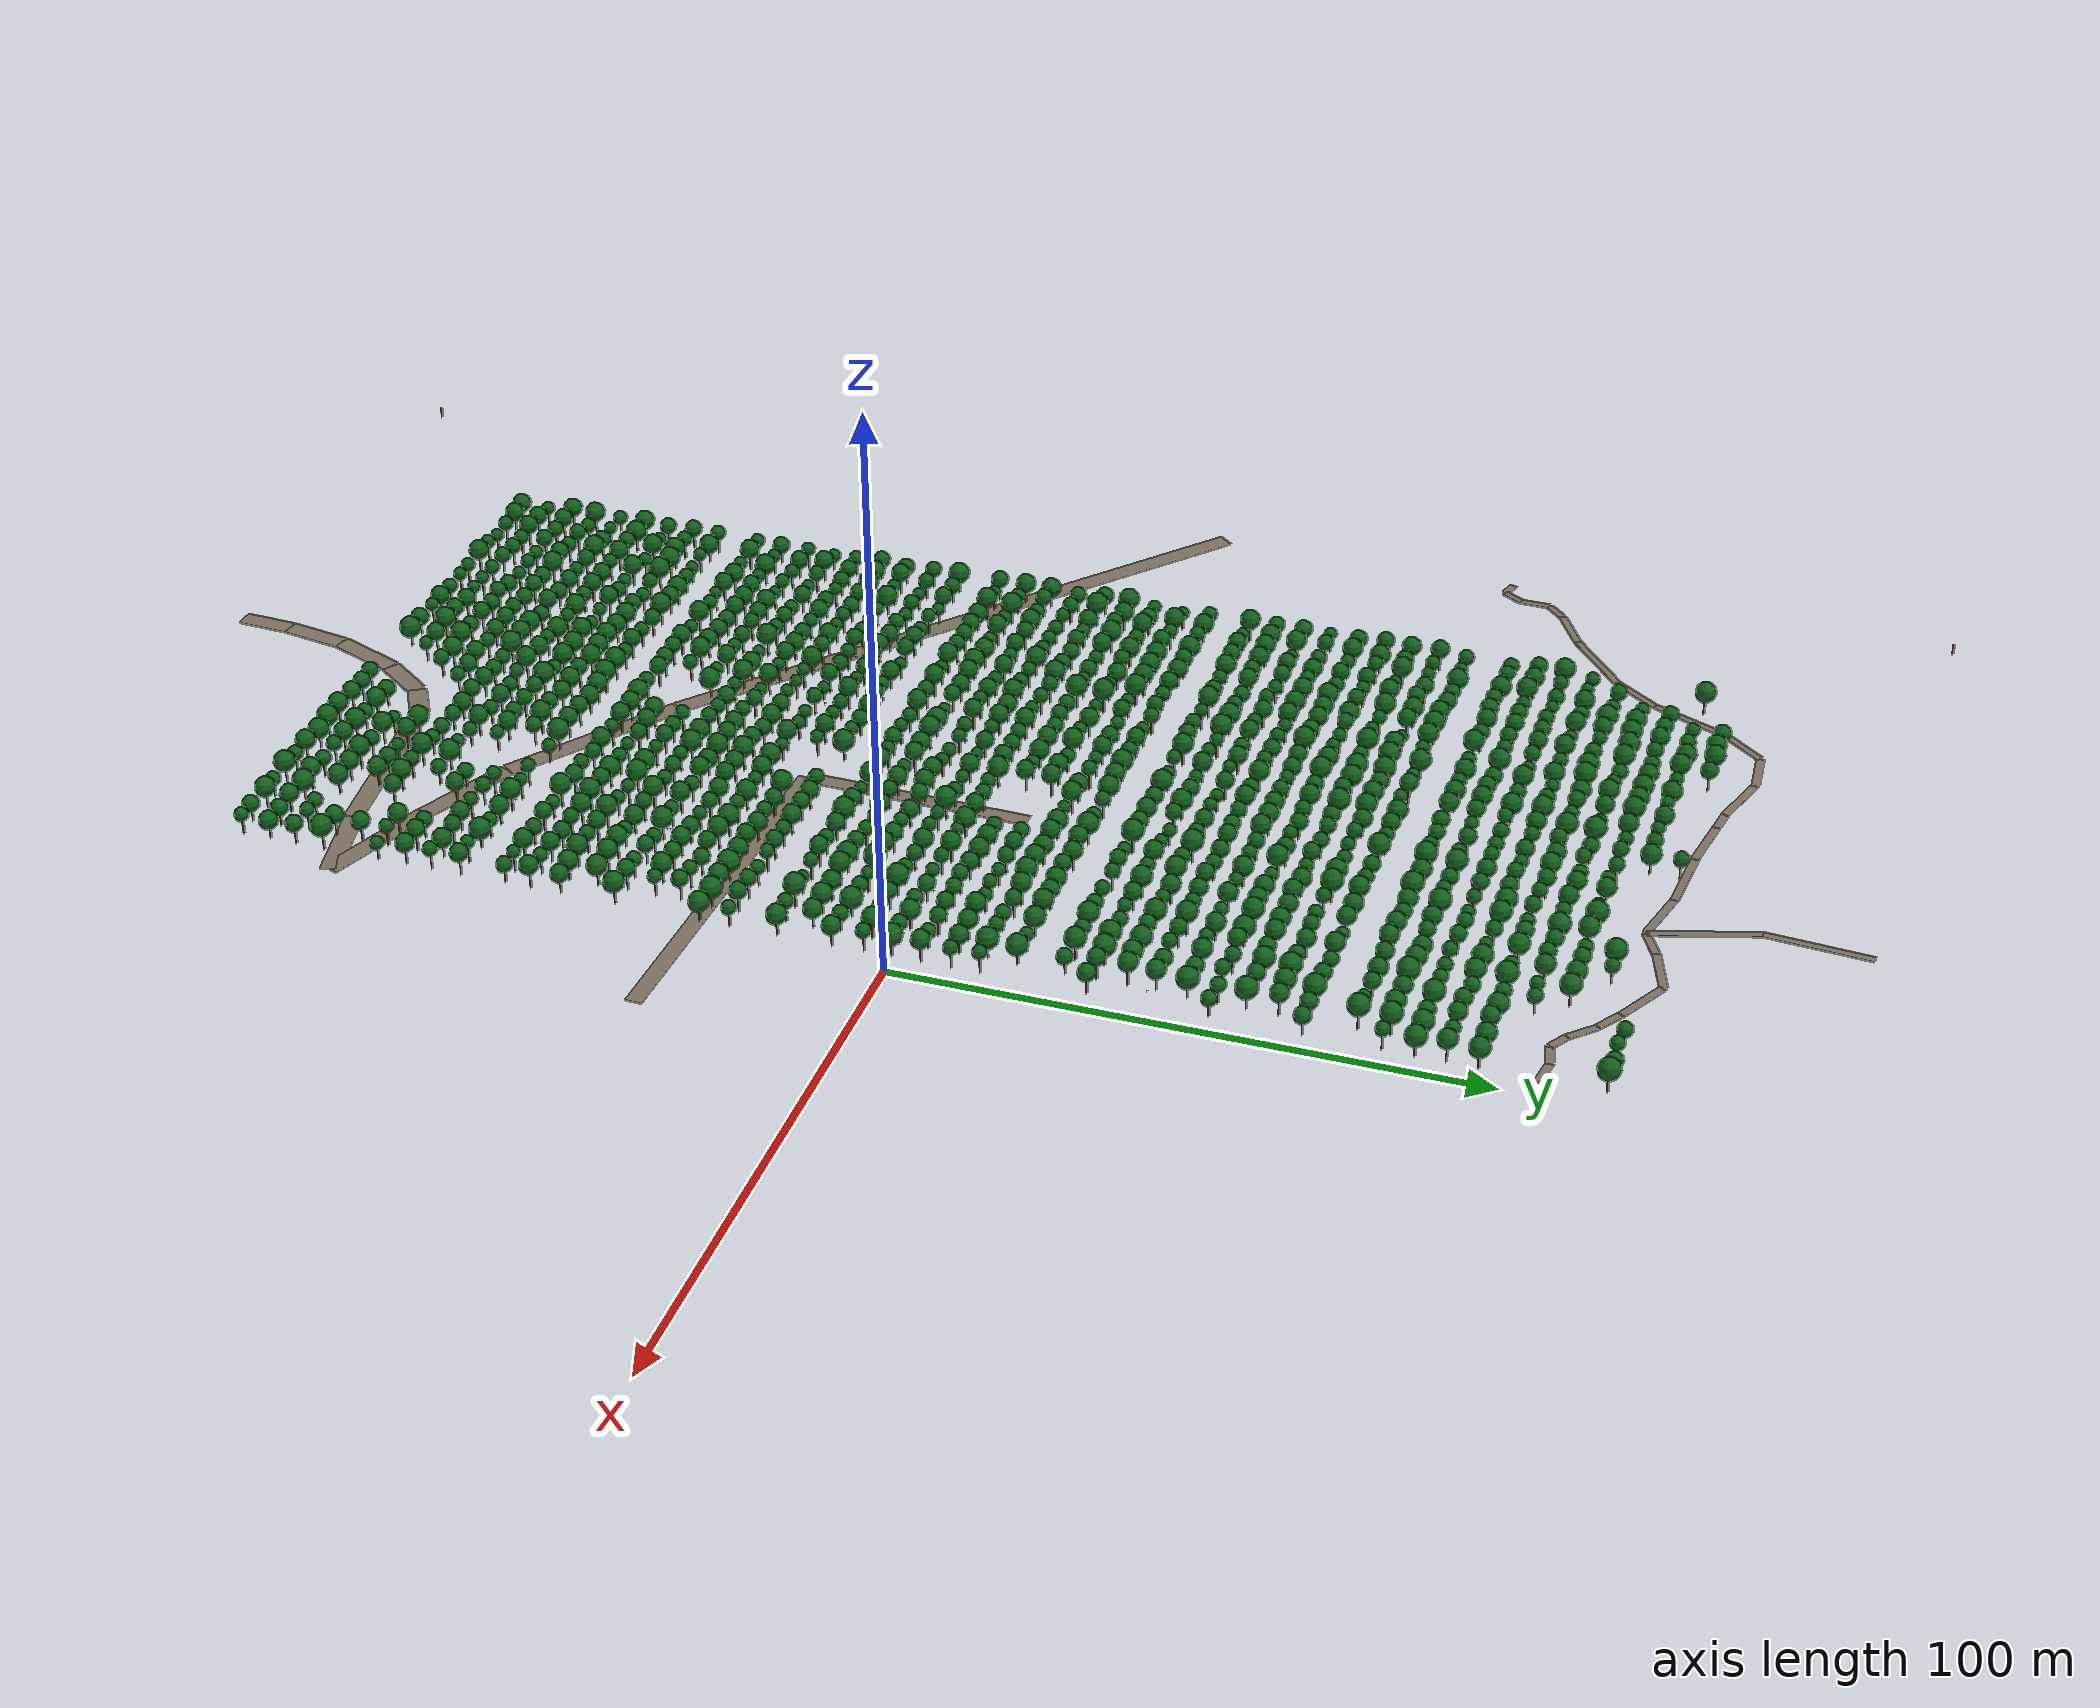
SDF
<sdf version="1.9">
 <world name="cheongsong_orchard">
  <physics name="default_physics" type="ode">
   <max_step_size>0.001</max_step_size>
   <real_time_factor>1.0</real_time_factor>
   <real_time_update_rate>1000</real_time_update_rate>
  </physics>
  <gravity>0 0 -9.81</gravity>
  <spherical_coordinates>
   <surface_model>EARTH_WGS84</surface_model>
   <world_frame_orientation>ENU</world_frame_orientation>
   <latitude_deg>36.436</latitude_deg>
   <longitude_deg>129.057</longitude_deg>
   <elevation>198.0</elevation>
   <heading_deg>0</heading_deg>
  </spherical_coordinates>
  <light type="directional" name="sun">
   <pose>0 0 100 0 0 0</pose>
   <diffuse>0.9 0.9 0.85 1</diffuse>
   <specular>0.3 0.3 0.3 1</specular>
   <direction>-0.5 0.3 -1.0</direction>
  </light>
  <light type="directional" name="ambient_light">
   <cast_shadows>false</cast_shadows>
   <pose>0 0 50 0 0 0</pose>
   <diffuse>0.35 0.35 0.3 1</diffuse>
   <specular>0.05 0.05 0.05 1</specular>
   <direction>0.2 -0.3 -1.0</direction>
  </light>
  <plugin filename="gz-sim-physics-system" name="gz::sim::systems::Physics"/>
  <plugin filename="gz-sim-scene-broadcaster-system" name="gz::sim::systems::SceneBroadcaster"/>
  <plugin filename="gz-sim-user-commands-system" name="gz::sim::systems::UserCommands"/>
  <plugin filename="gz-sim-sensors-system" name="gz::sim::systems::Sensors">
   <render_engine>ogre2</render_engine>
  </plugin>
  <plugin filename="gz-sim-imu-system" name="gz::sim::systems::Imu"/>
  <plugin filename="gz-sim-navsat-system" name="gz::sim::systems::NavSat"/>
  <plugin filename="gz-sim-contact-system" name="gz::sim::systems::Contact"/>
  <model name="road_0">
   <static>true</static>
   <pose>-106.6 -24.3 0.02 0 0 -0.7179</pose>
   <link name="link">
    <collision name="collision">
     <geometry><box><size>115.3 3.5 0.04</size></box></geometry>
     <surface><friction><ode><mu>0.9</mu><mu2>0.9</mu2></ode></friction></surface>
    </collision>
    <visual name="visual">
     <geometry><box><size>115.3 3.5 0.04</size></box></geometry>
     <material><ambient>0.4 0.35 0.28 1</ambient><diffuse>0.5 0.45 0.38 1</diffuse></material>
    </visual>
   </link>
  </model>
  <model name="road_1">
   <static>true</static>
   <pose>-49.3 -72.2 0.02 0 0 -0.6273</pose>
   <link name="link">
    <collision name="collision">
     <geometry><box><size>34.0 3.5 0.04</size></box></geometry>
     <surface><friction><ode><mu>0.9</mu><mu2>0.9</mu2></ode></friction></surface>
    </collision>
    <visual name="visual">
     <geometry><box><size>34.0 3.5 0.04</size></box></geometry>
     <material><ambient>0.4 0.35 0.28 1</ambient><diffuse>0.5 0.45 0.38 1</diffuse></material>
    </visual>
   </link>
  </model>
  <model name="road_2">
   <static>true</static>
   <pose>-27.3 -86.1 0.02 0 0 -0.4392</pose>
   <link name="link">
    <collision name="collision">
     <geometry><box><size>18.2 3.5 0.04</size></box></geometry>
     <surface><friction><ode><mu>0.9</mu><mu2>0.9</mu2></ode></friction></surface>
    </collision>
    <visual name="visual">
     <geometry><box><size>18.2 3.5 0.04</size></box></geometry>
     <material><ambient>0.4 0.35 0.28 1</ambient><diffuse>0.5 0.45 0.38 1</diffuse></material>
    </visual>
   </link>
  </model>
  <model name="road_3">
   <static>true</static>
   <pose>-9.1 -93.8 0.02 0 0 -0.3623</pose>
   <link name="link">
    <collision name="collision">
     <geometry><box><size>21.5 3.5 0.04</size></box></geometry>
     <surface><friction><ode><mu>0.9</mu><mu2>0.9</mu2></ode></friction></surface>
    </collision>
    <visual name="visual">
     <geometry><box><size>21.5 3.5 0.04</size></box></geometry>
     <material><ambient>0.4 0.35 0.28 1</ambient><diffuse>0.5 0.45 0.38 1</diffuse></material>
    </visual>
   </link>
  </model>
  <model name="road_15">
   <static>true</static>
   <pose>-48.6 -12.1 0.02 0 0 -1.5989</pose>
   <link name="link">
    <collision name="collision">
     <geometry><box><size>40.5 3.0 0.04</size></box></geometry>
     <surface><friction><ode><mu>0.9</mu><mu2>0.9</mu2></ode></friction></surface>
    </collision>
    <visual name="visual">
     <geometry><box><size>40.5 3.0 0.04</size></box></geometry>
     <material><ambient>0.4 0.35 0.28 1</ambient><diffuse>0.5 0.45 0.38 1</diffuse></material>
    </visual>
   </link>
  </model>
  <model name="road_16">
   <static>true</static>
   <pose>-14.8 -33.6 0.02 0 0 -0.0368</pose>
   <link name="link">
    <collision name="collision">
     <geometry><box><size>68.8 3.0 0.04</size></box></geometry>
     <surface><friction><ode><mu>0.9</mu><mu2>0.9</mu2></ode></friction></surface>
    </collision>
    <visual name="visual">
     <geometry><box><size>68.8 3.0 0.04</size></box></geometry>
     <material><ambient>0.4 0.35 0.28 1</ambient><diffuse>0.5 0.45 0.38 1</diffuse></material>
    </visual>
   </link>
  </model>
  <model name="road_19">
   <static>true</static>
   <pose>-67.2 -145.2 0.02 0 0 1.5213</pose>
   <link name="link">
    <collision name="collision">
     <geometry><box><size>9.7 3.5 0.04</size></box></geometry>
     <surface><friction><ode><mu>0.9</mu><mu2>0.9</mu2></ode></friction></surface>
    </collision>
    <visual name="visual">
     <geometry><box><size>9.7 3.5 0.04</size></box></geometry>
     <material><ambient>0.4 0.35 0.28 1</ambient><diffuse>0.5 0.45 0.38 1</diffuse></material>
    </visual>
   </link>
  </model>
  <model name="road_20">
   <static>true</static>
   <pose>-66.0 -134.7 0.02 0 0 1.4038</pose>
   <link name="link">
    <collision name="collision">
     <geometry><box><size>11.4 3.5 0.04</size></box></geometry>
     <surface><friction><ode><mu>0.9</mu><mu2>0.9</mu2></ode></friction></surface>
    </collision>
    <visual name="visual">
     <geometry><box><size>11.4 3.5 0.04</size></box></geometry>
     <material><ambient>0.4 0.35 0.28 1</ambient><diffuse>0.5 0.45 0.38 1</diffuse></material>
    </visual>
   </link>
  </model>
  <model name="road_21">
   <static>true</static>
   <pose>-62.7 -122.9 0.02 0 0 1.1994</pose>
   <link name="link">
    <collision name="collision">
     <geometry><box><size>13.2 3.5 0.04</size></box></geometry>
     <surface><friction><ode><mu>0.9</mu><mu2>0.9</mu2></ode></friction></surface>
    </collision>
    <visual name="visual">
     <geometry><box><size>13.2 3.5 0.04</size></box></geometry>
     <material><ambient>0.4 0.35 0.28 1</ambient><diffuse>0.5 0.45 0.38 1</diffuse></material>
    </visual>
   </link>
  </model>
  <model name="road_22">
   <static>true</static>
   <pose>-57.4 -112.8 0.02 0 0 0.9492</pose>
   <link name="link">
    <collision name="collision">
     <geometry><box><size>9.7 3.5 0.04</size></box></geometry>
     <surface><friction><ode><mu>0.9</mu><mu2>0.9</mu2></ode></friction></surface>
    </collision>
    <visual name="visual">
     <geometry><box><size>9.7 3.5 0.04</size></box></geometry>
     <material><ambient>0.4 0.35 0.28 1</ambient><diffuse>0.5 0.45 0.38 1</diffuse></material>
    </visual>
   </link>
  </model>
  <model name="road_23">
   <static>true</static>
   <pose>-51.0 -106.8 0.02 0 0 0.5135</pose>
   <link name="link">
    <collision name="collision">
     <geometry><box><size>8.2 3.5 0.04</size></box></geometry>
     <surface><friction><ode><mu>0.9</mu><mu2>0.9</mu2></ode></friction></surface>
    </collision>
    <visual name="visual">
     <geometry><box><size>8.2 3.5 0.04</size></box></geometry>
     <material><ambient>0.4 0.35 0.28 1</ambient><diffuse>0.5 0.45 0.38 1</diffuse></material>
    </visual>
   </link>
  </model>
  <model name="road_24">
   <static>true</static>
   <pose>-31.0 -102.9 0.02 0 0 0.1181</pose>
   <link name="link">
    <collision name="collision">
     <geometry><box><size>33.2 3.5 0.04</size></box></geometry>
     <surface><friction><ode><mu>0.9</mu><mu2>0.9</mu2></ode></friction></surface>
    </collision>
    <visual name="visual">
     <geometry><box><size>33.2 3.5 0.04</size></box></geometry>
     <material><ambient>0.4 0.35 0.28 1</ambient><diffuse>0.5 0.45 0.38 1</diffuse></material>
    </visual>
   </link>
  </model>
  <model name="road_25">
   <static>true</static>
   <pose>-6.8 -99.2 0.02 0 0 0.2110</pose>
   <link name="link">
    <collision name="collision">
     <geometry><box><size>15.8 3.5 0.04</size></box></geometry>
     <surface><friction><ode><mu>0.9</mu><mu2>0.9</mu2></ode></friction></surface>
    </collision>
    <visual name="visual">
     <geometry><box><size>15.8 3.5 0.04</size></box></geometry>
     <material><ambient>0.4 0.35 0.28 1</ambient><diffuse>0.5 0.45 0.38 1</diffuse></material>
    </visual>
   </link>
  </model>
  <model name="road_28">
   <static>true</static>
   <pose>-52.2 140.9 0.02 0 0 -1.6477</pose>
   <link name="link">
    <collision name="collision">
     <geometry><box><size>18.4 1.5 0.04</size></box></geometry>
     <surface><friction><ode><mu>0.9</mu><mu2>0.9</mu2></ode></friction></surface>
    </collision>
    <visual name="visual">
     <geometry><box><size>18.4 1.5 0.04</size></box></geometry>
     <material><ambient>0.4 0.35 0.28 1</ambient><diffuse>0.5 0.45 0.38 1</diffuse></material>
    </visual>
   </link>
  </model>
  <model name="road_29">
   <static>true</static>
   <pose>-50.2 122.7 0.02 0 0 -1.2793</pose>
   <link name="link">
    <collision name="collision">
     <geometry><box><size>18.9 1.5 0.04</size></box></geometry>
     <surface><friction><ode><mu>0.9</mu><mu2>0.9</mu2></ode></friction></surface>
    </collision>
    <visual name="visual">
     <geometry><box><size>18.9 1.5 0.04</size></box></geometry>
     <material><ambient>0.4 0.35 0.28 1</ambient><diffuse>0.5 0.45 0.38 1</diffuse></material>
    </visual>
   </link>
  </model>
  <model name="road_53">
   <static>true</static>
   <pose>-6.2 105.7 0.02 0 0 2.9790</pose>
   <link name="link">
    <collision name="collision">
     <geometry><box><size>5.2 1.5 0.04</size></box></geometry>
     <surface><friction><ode><mu>0.9</mu><mu2>0.9</mu2></ode></friction></surface>
    </collision>
    <visual name="visual">
     <geometry><box><size>5.2 1.5 0.04</size></box></geometry>
     <material><ambient>0.4 0.35 0.28 1</ambient><diffuse>0.5 0.45 0.38 1</diffuse></material>
    </visual>
   </link>
  </model>
  <model name="road_54">
   <static>true</static>
   <pose>-10.9 105.6 0.02 0 0 -2.9213</pose>
   <link name="link">
    <collision name="collision">
     <geometry><box><size>4.4 1.5 0.04</size></box></geometry>
     <surface><friction><ode><mu>0.9</mu><mu2>0.9</mu2></ode></friction></surface>
    </collision>
    <visual name="visual">
     <geometry><box><size>4.4 1.5 0.04</size></box></geometry>
     <material><ambient>0.4 0.35 0.28 1</ambient><diffuse>0.5 0.45 0.38 1</diffuse></material>
    </visual>
   </link>
  </model>
  <model name="road_55">
   <static>true</static>
   <pose>-14.7 106.2 0.02 0 0 2.5781</pose>
   <link name="link">
    <collision name="collision">
     <geometry><box><size>3.8 1.5 0.04</size></box></geometry>
     <surface><friction><ode><mu>0.9</mu><mu2>0.9</mu2></ode></friction></surface>
    </collision>
    <visual name="visual">
     <geometry><box><size>3.8 1.5 0.04</size></box></geometry>
     <material><ambient>0.4 0.35 0.28 1</ambient><diffuse>0.5 0.45 0.38 1</diffuse></material>
    </visual>
   </link>
  </model>
  <model name="road_56">
   <static>true</static>
   <pose>-18.3 109.3 0.02 0 0 2.3415</pose>
   <link name="link">
    <collision name="collision">
     <geometry><box><size>5.7 1.5 0.04</size></box></geometry>
     <surface><friction><ode><mu>0.9</mu><mu2>0.9</mu2></ode></friction></surface>
    </collision>
    <visual name="visual">
     <geometry><box><size>5.7 1.5 0.04</size></box></geometry>
     <material><ambient>0.4 0.35 0.28 1</ambient><diffuse>0.5 0.45 0.38 1</diffuse></material>
    </visual>
   </link>
  </model>
  <model name="road_57">
   <static>true</static>
   <pose>-22.4 112.7 0.02 0 0 2.5400</pose>
   <link name="link">
    <collision name="collision">
     <geometry><box><size>5.1 1.5 0.04</size></box></geometry>
     <surface><friction><ode><mu>0.9</mu><mu2>0.9</mu2></ode></friction></surface>
    </collision>
    <visual name="visual">
     <geometry><box><size>5.1 1.5 0.04</size></box></geometry>
     <material><ambient>0.4 0.35 0.28 1</ambient><diffuse>0.5 0.45 0.38 1</diffuse></material>
    </visual>
   </link>
  </model>
  <model name="road_58">
   <static>true</static>
   <pose>-28.9 116.6 0.02 0 0 2.6358</pose>
   <link name="link">
    <collision name="collision">
     <geometry><box><size>10.2 1.5 0.04</size></box></geometry>
     <surface><friction><ode><mu>0.9</mu><mu2>0.9</mu2></ode></friction></surface>
    </collision>
    <visual name="visual">
     <geometry><box><size>10.2 1.5 0.04</size></box></geometry>
     <material><ambient>0.4 0.35 0.28 1</ambient><diffuse>0.5 0.45 0.38 1</diffuse></material>
    </visual>
   </link>
  </model>
  <model name="road_59">
   <static>true</static>
   <pose>-37.9 117.7 0.02 0 0 -2.8319</pose>
   <link name="link">
    <collision name="collision">
     <geometry><box><size>9.5 1.5 0.04</size></box></geometry>
     <surface><friction><ode><mu>0.9</mu><mu2>0.9</mu2></ode></friction></surface>
    </collision>
    <visual name="visual">
     <geometry><box><size>9.5 1.5 0.04</size></box></geometry>
     <material><ambient>0.4 0.35 0.28 1</ambient><diffuse>0.5 0.45 0.38 1</diffuse></material>
    </visual>
   </link>
  </model>
  <model name="road_60">
   <static>true</static>
   <pose>-44.9 114.9 0.02 0 0 -2.6750</pose>
   <link name="link">
    <collision name="collision">
     <geometry><box><size>5.7 1.5 0.04</size></box></geometry>
     <surface><friction><ode><mu>0.9</mu><mu2>0.9</mu2></ode></friction></surface>
    </collision>
    <visual name="visual">
     <geometry><box><size>5.7 1.5 0.04</size></box></geometry>
     <material><ambient>0.4 0.35 0.28 1</ambient><diffuse>0.5 0.45 0.38 1</diffuse></material>
    </visual>
   </link>
  </model>
  <model name="road_61">
   <static>true</static>
   <pose>-52.8 115.0 0.02 0 0 2.8934</pose>
   <link name="link">
    <collision name="collision">
     <geometry><box><size>11.0 1.5 0.04</size></box></geometry>
     <surface><friction><ode><mu>0.9</mu><mu2>0.9</mu2></ode></friction></surface>
    </collision>
    <visual name="visual">
     <geometry><box><size>11.0 1.5 0.04</size></box></geometry>
     <material><ambient>0.4 0.35 0.28 1</ambient><diffuse>0.5 0.45 0.38 1</diffuse></material>
    </visual>
   </link>
  </model>
  <model name="road_62">
   <static>true</static>
   <pose>-64.5 116.9 0.02 0 0 3.0570</pose>
   <link name="link">
    <collision name="collision">
     <geometry><box><size>12.8 1.5 0.04</size></box></geometry>
     <surface><friction><ode><mu>0.9</mu><mu2>0.9</mu2></ode></friction></surface>
    </collision>
    <visual name="visual">
     <geometry><box><size>12.8 1.5 0.04</size></box></geometry>
     <material><ambient>0.4 0.35 0.28 1</ambient><diffuse>0.5 0.45 0.38 1</diffuse></material>
    </visual>
   </link>
  </model>
  <model name="road_63">
   <static>true</static>
   <pose>-76.1 118.3 0.02 0 0 2.9706</pose>
   <link name="link">
    <collision name="collision">
     <geometry><box><size>10.6 1.5 0.04</size></box></geometry>
     <surface><friction><ode><mu>0.9</mu><mu2>0.9</mu2></ode></friction></surface>
    </collision>
    <visual name="visual">
     <geometry><box><size>10.6 1.5 0.04</size></box></geometry>
     <material><ambient>0.4 0.35 0.28 1</ambient><diffuse>0.5 0.45 0.38 1</diffuse></material>
    </visual>
   </link>
  </model>
  <model name="road_64">
   <static>true</static>
   <pose>-83.5 119.6 0.02 0 0 2.9759</pose>
   <link name="link">
    <collision name="collision">
     <geometry><box><size>4.4 1.5 0.04</size></box></geometry>
     <surface><friction><ode><mu>0.9</mu><mu2>0.9</mu2></ode></friction></surface>
    </collision>
    <visual name="visual">
     <geometry><box><size>4.4 1.5 0.04</size></box></geometry>
     <material><ambient>0.4 0.35 0.28 1</ambient><diffuse>0.5 0.45 0.38 1</diffuse></material>
    </visual>
   </link>
  </model>
  <model name="road_65">
   <static>true</static>
   <pose>-90.8 121.6 0.02 0 0 2.8271</pose>
   <link name="link">
    <collision name="collision">
     <geometry><box><size>10.9 1.5 0.04</size></box></geometry>
     <surface><friction><ode><mu>0.9</mu><mu2>0.9</mu2></ode></friction></surface>
    </collision>
    <visual name="visual">
     <geometry><box><size>10.9 1.5 0.04</size></box></geometry>
     <material><ambient>0.4 0.35 0.28 1</ambient><diffuse>0.5 0.45 0.38 1</diffuse></material>
    </visual>
   </link>
  </model>
  <model name="road_66">
   <static>true</static>
   <pose>-100.4 123.0 0.02 0 0 -3.0731</pose>
   <link name="link">
    <collision name="collision">
     <geometry><box><size>8.8 1.5 0.04</size></box></geometry>
     <surface><friction><ode><mu>0.9</mu><mu2>0.9</mu2></ode></friction></surface>
    </collision>
    <visual name="visual">
     <geometry><box><size>8.8 1.5 0.04</size></box></geometry>
     <material><ambient>0.4 0.35 0.28 1</ambient><diffuse>0.5 0.45 0.38 1</diffuse></material>
    </visual>
   </link>
  </model>
  <model name="road_67">
   <static>true</static>
   <pose>-107.6 119.2 0.02 0 0 -2.2514</pose>
   <link name="link">
    <collision name="collision">
     <geometry><box><size>9.0 1.5 0.04</size></box></geometry>
     <surface><friction><ode><mu>0.9</mu><mu2>0.9</mu2></ode></friction></surface>
    </collision>
    <visual name="visual">
     <geometry><box><size>9.0 1.5 0.04</size></box></geometry>
     <material><ambient>0.4 0.35 0.28 1</ambient><diffuse>0.5 0.45 0.38 1</diffuse></material>
    </visual>
   </link>
  </model>
  <model name="road_68">
   <static>true</static>
   <pose>-113.3 109.0 0.02 0 0 -1.9727</pose>
   <link name="link">
    <collision name="collision">
     <geometry><box><size>14.7 1.5 0.04</size></box></geometry>
     <surface><friction><ode><mu>0.9</mu><mu2>0.9</mu2></ode></friction></surface>
    </collision>
    <visual name="visual">
     <geometry><box><size>14.7 1.5 0.04</size></box></geometry>
     <material><ambient>0.4 0.35 0.28 1</ambient><diffuse>0.5 0.45 0.38 1</diffuse></material>
    </visual>
   </link>
  </model>
  <model name="road_69">
   <static>true</static>
   <pose>-119.0 98.2 0.02 0 0 -2.1991</pose>
   <link name="link">
    <collision name="collision">
     <geometry><box><size>9.8 1.5 0.04</size></box></geometry>
     <surface><friction><ode><mu>0.9</mu><mu2>0.9</mu2></ode></friction></surface>
    </collision>
    <visual name="visual">
     <geometry><box><size>9.8 1.5 0.04</size></box></geometry>
     <material><ambient>0.4 0.35 0.28 1</ambient><diffuse>0.5 0.45 0.38 1</diffuse></material>
    </visual>
   </link>
  </model>
  <model name="road_70">
   <static>true</static>
   <pose>-127.8 89.4 0.02 0 0 -2.4568</pose>
   <link name="link">
    <collision name="collision">
     <geometry><box><size>15.2 1.5 0.04</size></box></geometry>
     <surface><friction><ode><mu>0.9</mu><mu2>0.9</mu2></ode></friction></surface>
    </collision>
    <visual name="visual">
     <geometry><box><size>15.2 1.5 0.04</size></box></geometry>
     <material><ambient>0.4 0.35 0.28 1</ambient><diffuse>0.5 0.45 0.38 1</diffuse></material>
    </visual>
   </link>
  </model>
  <model name="road_71">
   <static>true</static>
   <pose>-137.6 82.4 0.02 0 0 -2.6308</pose>
   <link name="link">
    <collision name="collision">
     <geometry><box><size>9.1 1.5 0.04</size></box></geometry>
     <surface><friction><ode><mu>0.9</mu><mu2>0.9</mu2></ode></friction></surface>
    </collision>
    <visual name="visual">
     <geometry><box><size>9.1 1.5 0.04</size></box></geometry>
     <material><ambient>0.4 0.35 0.28 1</ambient><diffuse>0.5 0.45 0.38 1</diffuse></material>
    </visual>
   </link>
  </model>
  <model name="road_72">
   <static>true</static>
   <pose>-143.1 78.6 0.02 0 0 -2.3371</pose>
   <link name="link">
    <collision name="collision">
     <geometry><box><size>4.3 1.5 0.04</size></box></geometry>
     <surface><friction><ode><mu>0.9</mu><mu2>0.9</mu2></ode></friction></surface>
    </collision>
    <visual name="visual">
     <geometry><box><size>4.3 1.5 0.04</size></box></geometry>
     <material><ambient>0.4 0.35 0.28 1</ambient><diffuse>0.5 0.45 0.38 1</diffuse></material>
    </visual>
   </link>
  </model>
  <model name="road_73">
   <static>true</static>
   <pose>-144.7 74.4 0.02 0 0 -1.5940</pose>
   <link name="link">
    <collision name="collision">
     <geometry><box><size>5.4 1.5 0.04</size></box></geometry>
     <surface><friction><ode><mu>0.9</mu><mu2>0.9</mu2></ode></friction></surface>
    </collision>
    <visual name="visual">
     <geometry><box><size>5.4 1.5 0.04</size></box></geometry>
     <material><ambient>0.4 0.35 0.28 1</ambient><diffuse>0.5 0.45 0.38 1</diffuse></material>
    </visual>
   </link>
  </model>
  <model name="road_74">
   <static>true</static>
   <pose>-145.8 70.0 0.02 0 0 -2.1415</pose>
   <link name="link">
    <collision name="collision">
     <geometry><box><size>4.0 1.5 0.04</size></box></geometry>
     <surface><friction><ode><mu>0.9</mu><mu2>0.9</mu2></ode></friction></surface>
    </collision>
    <visual name="visual">
     <geometry><box><size>4.0 1.5 0.04</size></box></geometry>
     <material><ambient>0.4 0.35 0.28 1</ambient><diffuse>0.5 0.45 0.38 1</diffuse></material>
    </visual>
   </link>
  </model>
  <model name="road_75">
   <static>true</static>
   <pose>-148.4 68.8 0.02 0 0 2.8233</pose>
   <link name="link">
    <collision name="collision">
     <geometry><box><size>3.3 1.5 0.04</size></box></geometry>
     <surface><friction><ode><mu>0.9</mu><mu2>0.9</mu2></ode></friction></surface>
    </collision>
    <visual name="visual">
     <geometry><box><size>3.3 1.5 0.04</size></box></geometry>
     <material><ambient>0.4 0.35 0.28 1</ambient><diffuse>0.5 0.45 0.38 1</diffuse></material>
    </visual>
   </link>
  </model>
  <model name="apple_tree_0">
   <static>true</static>
   <pose>-116.11 -116.47 0 0 0 0</pose>
   <link name="link">
    <collision name="trunk_col">
     <pose>0 0 1.11 0 0 0</pose>
     <geometry><cylinder><radius>0.096</radius><length>2.22</length></cylinder></geometry>
    </collision>
    <visual name="trunk_vis">
     <pose>0 0 1.11 0 0 0</pose>
     <geometry><cylinder><radius>0.096</radius><length>2.22</length></cylinder></geometry>
     <material><ambient>0.35 0.22 0.08 1</ambient><diffuse>0.45 0.30 0.12 1</diffuse></material>
    </visual>
    <collision name="canopy_col">
     <pose>0 0 4.01 0 0 0</pose>
     <geometry><sphere><radius>1.79</radius></sphere></geometry>
    </collision>
    <visual name="canopy_vis">
     <pose>0 0 4.01 0 0 0</pose>
     <geometry><sphere><radius>1.79</radius></sphere></geometry>
     <material><ambient>0.04 0.28 0.06 1</ambient><diffuse>0.06 0.38 0.10 1</diffuse></material>
    </visual>
   </link>
  </model>
  <model name="apple_tree_1">
   <static>true</static>
   <pose>-112.39 -116.24 0 0 0 0</pose>
   <link name="link">
    <collision name="trunk_col">
     <pose>0 0 1.11 0 0 0</pose>
     <geometry><cylinder><radius>0.095</radius><length>2.22</length></cylinder></geometry>
    </collision>
    <visual name="trunk_vis">
     <pose>0 0 1.11 0 0 0</pose>
     <geometry><cylinder><radius>0.095</radius><length>2.22</length></cylinder></geometry>
     <material><ambient>0.35 0.22 0.08 1</ambient><diffuse>0.45 0.30 0.12 1</diffuse></material>
    </visual>
    <collision name="canopy_col">
     <pose>0 0 4.03 0 0 0</pose>
     <geometry><sphere><radius>1.81</radius></sphere></geometry>
    </collision>
    <visual name="canopy_vis">
     <pose>0 0 4.03 0 0 0</pose>
     <geometry><sphere><radius>1.81</radius></sphere></geometry>
     <material><ambient>0.04 0.28 0.06 1</ambient><diffuse>0.06 0.38 0.10 1</diffuse></material>
    </visual>
   </link>
  </model>
  <model name="apple_tree_2">
   <static>true</static>
   <pose>-108.43 -116.26 0 0 0 0</pose>
   <link name="link">
    <collision name="trunk_col">
     <pose>0 0 1.15 0 0 0</pose>
     <geometry><cylinder><radius>0.104</radius><length>2.30</length></cylinder></geometry>
    </collision>
    <visual name="trunk_vis">
     <pose>0 0 1.15 0 0 0</pose>
     <geometry><cylinder><radius>0.104</radius><length>2.30</length></cylinder></geometry>
     <material><ambient>0.35 0.22 0.08 1</ambient><diffuse>0.45 0.30 0.12 1</diffuse></material>
    </visual>
    <collision name="canopy_col">
     <pose>0 0 3.71 0 0 0</pose>
     <geometry><sphere><radius>1.41</radius></sphere></geometry>
    </collision>
    <visual name="canopy_vis">
     <pose>0 0 3.71 0 0 0</pose>
     <geometry><sphere><radius>1.41</radius></sphere></geometry>
     <material><ambient>0.04 0.28 0.06 1</ambient><diffuse>0.06 0.38 0.10 1</diffuse></material>
    </visual>
   </link>
  </model>
  <model name="apple_tree_3">
   <static>true</static>
   <pose>-104.46 -116.21 0 0 0 0</pose>
   <link name="link">
    <collision name="trunk_col">
     <pose>0 0 1.04 0 0 0</pose>
     <geometry><cylinder><radius>0.145</radius><length>2.07</length></cylinder></geometry>
    </collision>
    <visual name="trunk_vis">
     <pose>0 0 1.04 0 0 0</pose>
     <geometry><cylinder><radius>0.145</radius><length>2.07</length></cylinder></geometry>
     <material><ambient>0.35 0.22 0.08 1</ambient><diffuse>0.45 0.30 0.12 1</diffuse></material>
    </visual>
    <collision name="canopy_col">
     <pose>0 0 3.33 0 0 0</pose>
     <geometry><sphere><radius>1.26</radius></sphere></geometry>
    </collision>
    <visual name="canopy_vis">
     <pose>0 0 3.33 0 0 0</pose>
     <geometry><sphere><radius>1.26</radius></sphere></geometry>
     <material><ambient>0.04 0.28 0.06 1</ambient><diffuse>0.06 0.38 0.10 1</diffuse></material>
    </visual>
   </link>
  </model>
  <model name="apple_tree_4">
   <static>true</static>
   <pose>-100.31 -116.11 0 0 0 0</pose>
   <link name="link">
    <collision name="trunk_col">
     <pose>0 0 1.41 0 0 0</pose>
     <geometry><cylinder><radius>0.105</radius><length>2.81</length></cylinder></geometry>
    </collision>
    <visual name="trunk_vis">
     <pose>0 0 1.41 0 0 0</pose>
     <geometry><cylinder><radius>0.105</radius><length>2.81</length></cylinder></geometry>
     <material><ambient>0.35 0.22 0.08 1</ambient><diffuse>0.45 0.30 0.12 1</diffuse></material>
    </visual>
    <collision name="canopy_col">
     <pose>0 0 4.17 0 0 0</pose>
     <geometry><sphere><radius>1.35</radius></sphere></geometry>
    </collision>
    <visual name="canopy_vis">
     <pose>0 0 4.17 0 0 0</pose>
     <geometry><sphere><radius>1.35</radius></sphere></geometry>
     <material><ambient>0.04 0.28 0.06 1</ambient><diffuse>0.06 0.38 0.10 1</diffuse></material>
    </visual>
   </link>
  </model>
  <model name="apple_tree_5">
   <static>true</static>
   <pose>-96.45 -116.09 0 0 0 0</pose>
   <link name="link">
    <collision name="trunk_col">
     <pose>0 0 1.35 0 0 0</pose>
     <geometry><cylinder><radius>0.149</radius><length>2.70</length></cylinder></geometry>
    </collision>
    <visual name="trunk_vis">
     <pose>0 0 1.35 0 0 0</pose>
     <geometry><cylinder><radius>0.149</radius><length>2.70</length></cylinder></geometry>
     <material><ambient>0.35 0.22 0.08 1</ambient><diffuse>0.45 0.30 0.12 1</diffuse></material>
    </visual>
    <collision name="canopy_col">
     <pose>0 0 4.59 0 0 0</pose>
     <geometry><sphere><radius>1.88</radius></sphere></geometry>
    </collision>
    <visual name="canopy_vis">
     <pose>0 0 4.59 0 0 0</pose>
     <geometry><sphere><radius>1.88</radius></sphere></geometry>
     <material><ambient>0.04 0.28 0.06 1</ambient><diffuse>0.06 0.38 0.10 1</diffuse></material>
    </visual>
   </link>
  </model>
  <model name="apple_tree_6">
   <static>true</static>
   <pose>-91.97 -116.26 0 0 0 0</pose>
   <link name="link">
    <collision name="trunk_col">
     <pose>0 0 1.20 0 0 0</pose>
     <geometry><cylinder><radius>0.138</radius><length>2.39</length></cylinder></geometry>
    </collision>
    <visual name="trunk_vis">
     <pose>0 0 1.20 0 0 0</pose>
     <geometry><cylinder><radius>0.138</radius><length>2.39</length></cylinder></geometry>
     <material><ambient>0.35 0.22 0.08 1</ambient><diffuse>0.45 0.30 0.12 1</diffuse></material>
    </visual>
    <collision name="canopy_col">
     <pose>0 0 3.72 0 0 0</pose>
     <geometry><sphere><radius>1.33</radius></sphere></geometry>
    </collision>
    <visual name="canopy_vis">
     <pose>0 0 3.72 0 0 0</pose>
     <geometry><sphere><radius>1.33</radius></sphere></geometry>
     <material><ambient>0.04 0.28 0.06 1</ambient><diffuse>0.06 0.38 0.10 1</diffuse></material>
    </visual>
   </link>
  </model>
  <model name="apple_tree_7">
   <static>true</static>
   <pose>-88.28 -116.09 0 0 0 0</pose>
   <link name="link">
    <collision name="trunk_col">
     <pose>0 0 1.32 0 0 0</pose>
     <geometry><cylinder><radius>0.128</radius><length>2.63</length></cylinder></geometry>
    </collision>
    <visual name="trunk_vis">
     <pose>0 0 1.32 0 0 0</pose>
     <geometry><cylinder><radius>0.128</radius><length>2.63</length></cylinder></geometry>
     <material><ambient>0.35 0.22 0.08 1</ambient><diffuse>0.45 0.30 0.12 1</diffuse></material>
    </visual>
    <collision name="canopy_col">
     <pose>0 0 3.89 0 0 0</pose>
     <geometry><sphere><radius>1.26</radius></sphere></geometry>
    </collision>
    <visual name="canopy_vis">
     <pose>0 0 3.89 0 0 0</pose>
     <geometry><sphere><radius>1.26</radius></sphere></geometry>
     <material><ambient>0.04 0.28 0.06 1</ambient><diffuse>0.06 0.38 0.10 1</diffuse></material>
    </visual>
   </link>
  </model>
  <model name="apple_tree_8">
   <static>true</static>
   <pose>-84.11 -116.17 0 0 0 0</pose>
   <link name="link">
    <collision name="trunk_col">
     <pose>0 0 1.09 0 0 0</pose>
     <geometry><cylinder><radius>0.112</radius><length>2.19</length></cylinder></geometry>
    </collision>
    <visual name="trunk_vis">
     <pose>0 0 1.09 0 0 0</pose>
     <geometry><cylinder><radius>0.112</radius><length>2.19</length></cylinder></geometry>
     <material><ambient>0.35 0.22 0.08 1</ambient><diffuse>0.45 0.30 0.12 1</diffuse></material>
    </visual>
    <collision name="canopy_col">
     <pose>0 0 3.60 0 0 0</pose>
     <geometry><sphere><radius>1.42</radius></sphere></geometry>
    </collision>
    <visual name="canopy_vis">
     <pose>0 0 3.60 0 0 0</pose>
     <geometry><sphere><radius>1.42</radius></sphere></geometry>
     <material><ambient>0.04 0.28 0.06 1</ambient><diffuse>0.06 0.38 0.10 1</diffuse></material>
    </visual>
   </link>
  </model>
  <model name="apple_tree_9">
   <static>true</static>
   <pose>-79.93 -116.08 0 0 0 0</pose>
   <link name="link">
    <collision name="trunk_col">
     <pose>0 0 1.08 0 0 0</pose>
     <geometry><cylinder><radius>0.103</radius><length>2.16</length></cylinder></geometry>
    </collision>
    <visual name="trunk_vis">
     <pose>0 0 1.08 0 0 0</pose>
     <geometry><cylinder><radius>0.103</radius><length>2.16</length></cylinder></geometry>
     <material><ambient>0.35 0.22 0.08 1</ambient><diffuse>0.45 0.30 0.12 1</diffuse></material>
    </visual>
    <collision name="canopy_col">
     <pose>0 0 3.98 0 0 0</pose>
     <geometry><sphere><radius>1.81</radius></sphere></geometry>
    </collision>
    <visual name="canopy_vis">
     <pose>0 0 3.98 0 0 0</pose>
     <geometry><sphere><radius>1.81</radius></sphere></geometry>
     <material><ambient>0.04 0.28 0.06 1</ambient><diffuse>0.06 0.38 0.10 1</diffuse></material>
    </visual>
   </link>
  </model>
  <model name="apple_tree_10">
   <static>true</static>
   <pose>-76.46 -116.00 0 0 0 0</pose>
   <link name="link">
    <collision name="trunk_col">
     <pose>0 0 1.37 0 0 0</pose>
     <geometry><cylinder><radius>0.108</radius><length>2.73</length></cylinder></geometry>
    </collision>
    <visual name="trunk_vis">
     <pose>0 0 1.37 0 0 0</pose>
     <geometry><cylinder><radius>0.108</radius><length>2.73</length></cylinder></geometry>
     <material><ambient>0.35 0.22 0.08 1</ambient><diffuse>0.45 0.30 0.12 1</diffuse></material>
    </visual>
    <collision name="canopy_col">
     <pose>0 0 3.99 0 0 0</pose>
     <geometry><sphere><radius>1.25</radius></sphere></geometry>
    </collision>
    <visual name="canopy_vis">
     <pose>0 0 3.99 0 0 0</pose>
     <geometry><sphere><radius>1.25</radius></sphere></geometry>
     <material><ambient>0.04 0.28 0.06 1</ambient><diffuse>0.06 0.38 0.10 1</diffuse></material>
    </visual>
   </link>
  </model>
  <model name="apple_tree_11">
   <static>true</static>
   <pose>-72.18 -116.43 0 0 0 0</pose>
   <link name="link">
    <collision name="trunk_col">
     <pose>0 0 1.00 0 0 0</pose>
     <geometry><cylinder><radius>0.088</radius><length>2.00</length></cylinder></geometry>
    </collision>
    <visual name="trunk_vis">
     <pose>0 0 1.00 0 0 0</pose>
     <geometry><cylinder><radius>0.088</radius><length>2.00</length></cylinder></geometry>
     <material><ambient>0.35 0.22 0.08 1</ambient><diffuse>0.45 0.30 0.12 1</diffuse></material>
    </visual>
    <collision name="canopy_col">
     <pose>0 0 3.70 0 0 0</pose>
     <geometry><sphere><radius>1.70</radius></sphere></geometry>
    </collision>
    <visual name="canopy_vis">
     <pose>0 0 3.70 0 0 0</pose>
     <geometry><sphere><radius>1.70</radius></sphere></geometry>
     <material><ambient>0.04 0.28 0.06 1</ambient><diffuse>0.06 0.38 0.10 1</diffuse></material>
    </visual>
   </link>
  </model>
  <model name="apple_tree_12">
   <static>true</static>
   <pose>-68.01 -116.24 0 0 0 0</pose>
   <link name="link">
    <collision name="trunk_col">
     <pose>0 0 1.01 0 0 0</pose>
     <geometry><cylinder><radius>0.107</radius><length>2.01</length></cylinder></geometry>
    </collision>
    <visual name="trunk_vis">
     <pose>0 0 1.01 0 0 0</pose>
     <geometry><cylinder><radius>0.107</radius><length>2.01</length></cylinder></geometry>
     <material><ambient>0.35 0.22 0.08 1</ambient><diffuse>0.45 0.30 0.12 1</diffuse></material>
    </visual>
    <collision name="canopy_col">
     <pose>0 0 4.01 0 0 0</pose>
     <geometry><sphere><radius>2.00</radius></sphere></geometry>
    </collision>
    <visual name="canopy_vis">
     <pose>0 0 4.01 0 0 0</pose>
     <geometry><sphere><radius>2.00</radius></sphere></geometry>
     <material><ambient>0.04 0.28 0.06 1</ambient><diffuse>0.06 0.38 0.10 1</diffuse></material>
    </visual>
   </link>
  </model>
  <model name="apple_tree_13">
   <static>true</static>
   <pose>-52.17 -116.33 0 0 0 0</pose>
   <link name="link">
    <collision name="trunk_col">
     <pose>0 0 1.29 0 0 0</pose>
     <geometry><cylinder><radius>0.088</radius><length>2.57</length></cylinder></geometry>
    </collision>
    <visual name="trunk_vis">
     <pose>0 0 1.29 0 0 0</pose>
     <geometry><cylinder><radius>0.088</radius><length>2.57</length></cylinder></geometry>
     <material><ambient>0.35 0.22 0.08 1</ambient><diffuse>0.45 0.30 0.12 1</diffuse></material>
    </visual>
    <collision name="canopy_col">
     <pose>0 0 4.12 0 0 0</pose>
     <geometry><sphere><radius>1.55</radius></sphere></geometry>
    </collision>
    <visual name="canopy_vis">
     <pose>0 0 4.12 0 0 0</pose>
     <geometry><sphere><radius>1.55</radius></sphere></geometry>
     <material><ambient>0.04 0.28 0.06 1</ambient><diffuse>0.06 0.38 0.10 1</diffuse></material>
    </visual>
   </link>
  </model>
  <model name="apple_tree_14">
   <static>true</static>
   <pose>-48.22 -115.92 0 0 0 0</pose>
   <link name="link">
    <collision name="trunk_col">
     <pose>0 0 1.40 0 0 0</pose>
     <geometry><cylinder><radius>0.098</radius><length>2.80</length></cylinder></geometry>
    </collision>
    <visual name="trunk_vis">
     <pose>0 0 1.40 0 0 0</pose>
     <geometry><cylinder><radius>0.098</radius><length>2.80</length></cylinder></geometry>
     <material><ambient>0.35 0.22 0.08 1</ambient><diffuse>0.45 0.30 0.12 1</diffuse></material>
    </visual>
    <collision name="canopy_col">
     <pose>0 0 4.40 0 0 0</pose>
     <geometry><sphere><radius>1.60</radius></sphere></geometry>
    </collision>
    <visual name="canopy_vis">
     <pose>0 0 4.40 0 0 0</pose>
     <geometry><sphere><radius>1.60</radius></sphere></geometry>
     <material><ambient>0.04 0.28 0.06 1</ambient><diffuse>0.06 0.38 0.10 1</diffuse></material>
    </visual>
   </link>
  </model>
  <model name="apple_tree_15">
   <static>true</static>
   <pose>-44.38 -115.94 0 0 0 0</pose>
   <link name="link">
    <collision name="trunk_col">
     <pose>0 0 1.40 0 0 0</pose>
     <geometry><cylinder><radius>0.101</radius><length>2.80</length></cylinder></geometry>
    </collision>
    <visual name="trunk_vis">
     <pose>0 0 1.40 0 0 0</pose>
     <geometry><cylinder><radius>0.101</radius><length>2.80</length></cylinder></geometry>
     <material><ambient>0.35 0.22 0.08 1</ambient><diffuse>0.45 0.30 0.12 1</diffuse></material>
    </visual>
    <collision name="canopy_col">
     <pose>0 0 4.51 0 0 0</pose>
     <geometry><sphere><radius>1.71</radius></sphere></geometry>
    </collision>
    <visual name="canopy_vis">
     <pose>0 0 4.51 0 0 0</pose>
     <geometry><sphere><radius>1.71</radius></sphere></geometry>
     <material><ambient>0.04 0.28 0.06 1</ambient><diffuse>0.06 0.38 0.10 1</diffuse></material>
    </visual>
   </link>
  </model>
  <model name="apple_tree_16">
   <static>true</static>
   <pose>-40.12 -116.40 0 0 0 0</pose>
   <link name="link">
    <collision name="trunk_col">
     <pose>0 0 1.35 0 0 0</pose>
     <geometry><cylinder><radius>0.118</radius><length>2.69</length></cylinder></geometry>
    </collision>
    <visual name="trunk_vis">
     <pose>0 0 1.35 0 0 0</pose>
     <geometry><cylinder><radius>0.118</radius><length>2.69</length></cylinder></geometry>
     <material><ambient>0.35 0.22 0.08 1</ambient><diffuse>0.45 0.30 0.12 1</diffuse></material>
    </visual>
    <collision name="canopy_col">
     <pose>0 0 4.52 0 0 0</pose>
     <geometry><sphere><radius>1.82</radius></sphere></geometry>
    </collision>
    <visual name="canopy_vis">
     <pose>0 0 4.52 0 0 0</pose>
     <geometry><sphere><radius>1.82</radius></sphere></geometry>
     <material><ambient>0.04 0.28 0.06 1</ambient><diffuse>0.06 0.38 0.10 1</diffuse></material>
    </visual>
   </link>
  </model>
  <model name="apple_tree_17">
   <static>true</static>
   <pose>-36.17 -116.49 0 0 0 0</pose>
   <link name="link">
    <collision name="trunk_col">
     <pose>0 0 1.13 0 0 0</pose>
     <geometry><cylinder><radius>0.081</radius><length>2.27</length></cylinder></geometry>
    </collision>
    <visual name="trunk_vis">
     <pose>0 0 1.13 0 0 0</pose>
     <geometry><cylinder><radius>0.081</radius><length>2.27</length></cylinder></geometry>
     <material><ambient>0.35 0.22 0.08 1</ambient><diffuse>0.45 0.30 0.12 1</diffuse></material>
    </visual>
    <collision name="canopy_col">
     <pose>0 0 4.21 0 0 0</pose>
     <geometry><sphere><radius>1.94</radius></sphere></geometry>
    </collision>
    <visual name="canopy_vis">
     <pose>0 0 4.21 0 0 0</pose>
     <geometry><sphere><radius>1.94</radius></sphere></geometry>
     <material><ambient>0.04 0.28 0.06 1</ambient><diffuse>0.06 0.38 0.10 1</diffuse></material>
    </visual>
   </link>
  </model>
  <model name="apple_tree_18">
   <static>true</static>
   <pose>-31.96 -115.99 0 0 0 0</pose>
   <link name="link">
    <collision name="trunk_col">
     <pose>0 0 1.12 0 0 0</pose>
     <geometry><cylinder><radius>0.084</radius><length>2.25</length></cylinder></geometry>
    </collision>
    <visual name="trunk_vis">
     <pose>0 0 1.12 0 0 0</pose>
     <geometry><cylinder><radius>0.084</radius><length>2.25</length></cylinder></geometry>
     <material><ambient>0.35 0.22 0.08 1</ambient><diffuse>0.45 0.30 0.12 1</diffuse></material>
    </visual>
    <collision name="canopy_col">
     <pose>0 0 4.15 0 0 0</pose>
     <geometry><sphere><radius>1.90</radius></sphere></geometry>
    </collision>
    <visual name="canopy_vis">
     <pose>0 0 4.15 0 0 0</pose>
     <geometry><sphere><radius>1.90</radius></sphere></geometry>
     <material><ambient>0.04 0.28 0.06 1</ambient><diffuse>0.06 0.38 0.10 1</diffuse></material>
    </visual>
   </link>
  </model>
  <model name="apple_tree_19">
   <static>true</static>
   <pose>-27.92 -116.44 0 0 0 0</pose>
   <link name="link">
    <collision name="trunk_col">
     <pose>0 0 1.21 0 0 0</pose>
     <geometry><cylinder><radius>0.085</radius><length>2.42</length></cylinder></geometry>
    </collision>
    <visual name="trunk_vis">
     <pose>0 0 1.21 0 0 0</pose>
     <geometry><cylinder><radius>0.085</radius><length>2.42</length></cylinder></geometry>
     <material><ambient>0.35 0.22 0.08 1</ambient><diffuse>0.45 0.30 0.12 1</diffuse></material>
    </visual>
    <collision name="canopy_col">
     <pose>0 0 4.23 0 0 0</pose>
     <geometry><sphere><radius>1.81</radius></sphere></geometry>
    </collision>
    <visual name="canopy_vis">
     <pose>0 0 4.23 0 0 0</pose>
     <geometry><sphere><radius>1.81</radius></sphere></geometry>
     <material><ambient>0.04 0.28 0.06 1</ambient><diffuse>0.06 0.38 0.10 1</diffuse></material>
    </visual>
   </link>
  </model>
  <model name="apple_tree_20">
   <static>true</static>
   <pose>-24.03 -116.41 0 0 0 0</pose>
   <link name="link">
    <collision name="trunk_col">
     <pose>0 0 1.21 0 0 0</pose>
     <geometry><cylinder><radius>0.118</radius><length>2.41</length></cylinder></geometry>
    </collision>
    <visual name="trunk_vis">
     <pose>0 0 1.21 0 0 0</pose>
     <geometry><cylinder><radius>0.118</radius><length>2.41</length></cylinder></geometry>
     <material><ambient>0.35 0.22 0.08 1</ambient><diffuse>0.45 0.30 0.12 1</diffuse></material>
    </visual>
    <collision name="canopy_col">
     <pose>0 0 3.83 0 0 0</pose>
     <geometry><sphere><radius>1.41</radius></sphere></geometry>
    </collision>
    <visual name="canopy_vis">
     <pose>0 0 3.83 0 0 0</pose>
     <geometry><sphere><radius>1.41</radius></sphere></geometry>
     <material><ambient>0.04 0.28 0.06 1</ambient><diffuse>0.06 0.38 0.10 1</diffuse></material>
    </visual>
   </link>
  </model>
  <model name="apple_tree_21">
   <static>true</static>
   <pose>-20.36 -116.45 0 0 0 0</pose>
   <link name="link">
    <collision name="trunk_col">
     <pose>0 0 1.28 0 0 0</pose>
     <geometry><cylinder><radius>0.096</radius><length>2.57</length></cylinder></geometry>
    </collision>
    <visual name="trunk_vis">
     <pose>0 0 1.28 0 0 0</pose>
     <geometry><cylinder><radius>0.096</radius><length>2.57</length></cylinder></geometry>
     <material><ambient>0.35 0.22 0.08 1</ambient><diffuse>0.45 0.30 0.12 1</diffuse></material>
    </visual>
    <collision name="canopy_col">
     <pose>0 0 4.49 0 0 0</pose>
     <geometry><sphere><radius>1.92</radius></sphere></geometry>
    </collision>
    <visual name="canopy_vis">
     <pose>0 0 4.49 0 0 0</pose>
     <geometry><sphere><radius>1.92</radius></sphere></geometry>
     <material><ambient>0.04 0.28 0.06 1</ambient><diffuse>0.06 0.38 0.10 1</diffuse></material>
    </visual>
   </link>
  </model>
  <model name="apple_tree_22">
   <static>true</static>
   <pose>-15.97 -116.45 0 0 0 0</pose>
   <link name="link">
    <collision name="trunk_col">
     <pose>0 0 1.09 0 0 0</pose>
     <geometry><cylinder><radius>0.127</radius><length>2.18</length></cylinder></geometry>
    </collision>
    <visual name="trunk_vis">
     <pose>0 0 1.09 0 0 0</pose>
     <geometry><cylinder><radius>0.127</radius><length>2.18</length></cylinder></geometry>
     <material><ambient>0.35 0.22 0.08 1</ambient><diffuse>0.45 0.30 0.12 1</diffuse></material>
    </visual>
    <collision name="canopy_col">
     <pose>0 0 3.55 0 0 0</pose>
     <geometry><sphere><radius>1.37</radius></sphere></geometry>
    </collision>
    <visual name="canopy_vis">
     <pose>0 0 3.55 0 0 0</pose>
     <geometry><sphere><radius>1.37</radius></sphere></geometry>
     <material><ambient>0.04 0.28 0.06 1</ambient><diffuse>0.06 0.38 0.10 1</diffuse></material>
    </visual>
   </link>
  </model>
  <model name="apple_tree_23">
   <static>true</static>
   <pose>-12.41 -115.93 0 0 0 0</pose>
   <link name="link">
    <collision name="trunk_col">
     <pose>0 0 1.25 0 0 0</pose>
     <geometry><cylinder><radius>0.113</radius><length>2.51</length></cylinder></geometry>
    </collision>
    <visual name="trunk_vis">
     <pose>0 0 1.25 0 0 0</pose>
     <geometry><cylinder><radius>0.113</radius><length>2.51</length></cylinder></geometry>
     <material><ambient>0.35 0.22 0.08 1</ambient><diffuse>0.45 0.30 0.12 1</diffuse></material>
    </visual>
    <collision name="canopy_col">
     <pose>0 0 4.33 0 0 0</pose>
     <geometry><sphere><radius>1.83</radius></sphere></geometry>
    </collision>
    <visual name="canopy_vis">
     <pose>0 0 4.33 0 0 0</pose>
     <geometry><sphere><radius>1.83</radius></sphere></geometry>
     <material><ambient>0.04 0.28 0.06 1</ambient><diffuse>0.06 0.38 0.10 1</diffuse></material>
    </visual>
   </link>
  </model>
  <model name="apple_tree_24">
   <static>true</static>
   <pose>-8.01 -116.38 0 0 0 0</pose>
   <link name="link">
    <collision name="trunk_col">
     <pose>0 0 1.02 0 0 0</pose>
     <geometry><cylinder><radius>0.110</radius><length>2.04</length></cylinder></geometry>
    </collision>
    <visual name="trunk_vis">
     <pose>0 0 1.02 0 0 0</pose>
     <geometry><cylinder><radius>0.110</radius><length>2.04</length></cylinder></geometry>
     <material><ambient>0.35 0.22 0.08 1</ambient><diffuse>0.45 0.30 0.12 1</diffuse></material>
    </visual>
    <collision name="canopy_col">
     <pose>0 0 3.58 0 0 0</pose>
     <geometry><sphere><radius>1.54</radius></sphere></geometry>
    </collision>
    <visual name="canopy_vis">
     <pose>0 0 3.58 0 0 0</pose>
     <geometry><sphere><radius>1.54</radius></sphere></geometry>
     <material><ambient>0.04 0.28 0.06 1</ambient><diffuse>0.06 0.38 0.10 1</diffuse></material>
    </visual>
   </link>
  </model>
  <model name="apple_tree_25">
   <static>true</static>
   <pose>-4.21 -116.05 0 0 0 0</pose>
   <link name="link">
    <collision name="trunk_col">
     <pose>0 0 1.30 0 0 0</pose>
     <geometry><cylinder><radius>0.149</radius><length>2.61</length></cylinder></geometry>
    </collision>
    <visual name="trunk_vis">
     <pose>0 0 1.30 0 0 0</pose>
     <geometry><cylinder><radius>0.149</radius><length>2.61</length></cylinder></geometry>
     <material><ambient>0.35 0.22 0.08 1</ambient><diffuse>0.45 0.30 0.12 1</diffuse></material>
    </visual>
    <collision name="canopy_col">
     <pose>0 0 3.89 0 0 0</pose>
     <geometry><sphere><radius>1.28</radius></sphere></geometry>
    </collision>
    <visual name="canopy_vis">
     <pose>0 0 3.89 0 0 0</pose>
     <geometry><sphere><radius>1.28</radius></sphere></geometry>
     <material><ambient>0.04 0.28 0.06 1</ambient><diffuse>0.06 0.38 0.10 1</diffuse></material>
    </visual>
   </link>
  </model>
  <model name="apple_tree_56">
   <static>true</static>
   <pose>-115.92 -110.94 0 0 0 0</pose>
   <link name="link">
    <collision name="trunk_col">
     <pose>0 0 1.28 0 0 0</pose>
     <geometry><cylinder><radius>0.126</radius><length>2.56</length></cylinder></geometry>
    </collision>
    <visual name="trunk_vis">
     <pose>0 0 1.28 0 0 0</pose>
     <geometry><cylinder><radius>0.126</radius><length>2.56</length></cylinder></geometry>
     <material><ambient>0.35 0.22 0.08 1</ambient><diffuse>0.45 0.30 0.12 1</diffuse></material>
    </visual>
    <collision name="canopy_col">
     <pose>0 0 3.86 0 0 0</pose>
     <geometry><sphere><radius>1.30</radius></sphere></geometry>
    </collision>
    <visual name="canopy_vis">
     <pose>0 0 3.86 0 0 0</pose>
     <geometry><sphere><radius>1.30</radius></sphere></geometry>
     <material><ambient>0.04 0.28 0.06 1</ambient><diffuse>0.06 0.38 0.10 1</diffuse></material>
    </visual>
   </link>
  </model>
  <model name="apple_tree_57">
   <static>true</static>
   <pose>-111.95 -111.19 0 0 0 0</pose>
   <link name="link">
    <collision name="trunk_col">
     <pose>0 0 1.30 0 0 0</pose>
     <geometry><cylinder><radius>0.103</radius><length>2.60</length></cylinder></geometry>
    </collision>
    <visual name="trunk_vis">
     <pose>0 0 1.30 0 0 0</pose>
     <geometry><cylinder><radius>0.103</radius><length>2.60</length></cylinder></geometry>
     <material><ambient>0.35 0.22 0.08 1</ambient><diffuse>0.45 0.30 0.12 1</diffuse></material>
    </visual>
    <collision name="canopy_col">
     <pose>0 0 4.36 0 0 0</pose>
     <geometry><sphere><radius>1.76</radius></sphere></geometry>
    </collision>
    <visual name="canopy_vis">
     <pose>0 0 4.36 0 0 0</pose>
     <geometry><sphere><radius>1.76</radius></sphere></geometry>
     <material><ambient>0.04 0.28 0.06 1</ambient><diffuse>0.06 0.38 0.10 1</diffuse></material>
    </visual>
   </link>
  </model>
  <model name="apple_tree_58">
   <static>true</static>
   <pose>-108.16 -111.37 0 0 0 0</pose>
   <link name="link">
    <collision name="trunk_col">
     <pose>0 0 1.30 0 0 0</pose>
     <geometry><cylinder><radius>0.107</radius><length>2.60</length></cylinder></geometry>
    </collision>
    <visual name="trunk_vis">
     <pose>0 0 1.30 0 0 0</pose>
     <geometry><cylinder><radius>0.107</radius><length>2.60</length></cylinder></geometry>
     <material><ambient>0.35 0.22 0.08 1</ambient><diffuse>0.45 0.30 0.12 1</diffuse></material>
    </visual>
    <collision name="canopy_col">
     <pose>0 0 4.40 0 0 0</pose>
     <geometry><sphere><radius>1.80</radius></sphere></geometry>
    </collision>
    <visual name="canopy_vis">
     <pose>0 0 4.40 0 0 0</pose>
     <geometry><sphere><radius>1.80</radius></sphere></geometry>
     <material><ambient>0.04 0.28 0.06 1</ambient><diffuse>0.06 0.38 0.10 1</diffuse></material>
    </visual>
   </link>
  </model>
  <model name="apple_tree_59">
   <static>true</static>
   <pose>-104.39 -111.15 0 0 0 0</pose>
   <link name="link">
    <collision name="trunk_col">
     <pose>0 0 1.17 0 0 0</pose>
     <geometry><cylinder><radius>0.138</radius><length>2.35</length></cylinder></geometry>
    </collision>
    <visual name="trunk_vis">
     <pose>0 0 1.17 0 0 0</pose>
     <geometry><cylinder><radius>0.138</radius><length>2.35</length></cylinder></geometry>
     <material><ambient>0.35 0.22 0.08 1</ambient><diffuse>0.45 0.30 0.12 1</diffuse></material>
    </visual>
    <collision name="canopy_col">
     <pose>0 0 3.79 0 0 0</pose>
     <geometry><sphere><radius>1.44</radius></sphere></geometry>
    </collision>
    <visual name="canopy_vis">
     <pose>0 0 3.79 0 0 0</pose>
     <geometry><sphere><radius>1.44</radius></sphere></geometry>
     <material><ambient>0.04 0.28 0.06 1</ambient><diffuse>0.06 0.38 0.10 1</diffuse></material>
    </visual>
   </link>
  </model>
  <model name="apple_tree_60">
   <static>true</static>
   <pose>-100.36 -111.02 0 0 0 0</pose>
   <link name="link">
    <collision name="trunk_col">
     <pose>0 0 1.27 0 0 0</pose>
     <geometry><cylinder><radius>0.103</radius><length>2.54</length></cylinder></geometry>
    </collision>
    <visual name="trunk_vis">
     <pose>0 0 1.27 0 0 0</pose>
     <geometry><cylinder><radius>0.103</radius><length>2.54</length></cylinder></geometry>
     <material><ambient>0.35 0.22 0.08 1</ambient><diffuse>0.45 0.30 0.12 1</diffuse></material>
    </visual>
    <collision name="canopy_col">
     <pose>0 0 4.09 0 0 0</pose>
     <geometry><sphere><radius>1.55</radius></sphere></geometry>
    </collision>
    <visual name="canopy_vis">
     <pose>0 0 4.09 0 0 0</pose>
     <geometry><sphere><radius>1.55</radius></sphere></geometry>
     <material><ambient>0.04 0.28 0.06 1</ambient><diffuse>0.06 0.38 0.10 1</diffuse></material>
    </visual>
   </link>
  </model>
  <model name="apple_tree_61">
   <static>true</static>
   <pose>-96.34 -111.20 0 0 0 0</pose>
   <link name="link">
    <collision name="trunk_col">
     <pose>0 0 1.39 0 0 0</pose>
     <geometry><cylinder><radius>0.085</radius><length>2.78</length></cylinder></geometry>
    </collision>
    <visual name="trunk_vis">
     <pose>0 0 1.39 0 0 0</pose>
     <geometry><cylinder><radius>0.085</radius><length>2.78</length></cylinder></geometry>
     <material><ambient>0.35 0.22 0.08 1</ambient><diffuse>0.45 0.30 0.12 1</diffuse></material>
    </visual>
    <collision name="canopy_col">
     <pose>0 0 4.31 0 0 0</pose>
     <geometry><sphere><radius>1.53</radius></sphere></geometry>
    </collision>
    <visual name="canopy_vis">
     <pose>0 0 4.31 0 0 0</pose>
     <geometry><sphere><radius>1.53</radius></sphere></geometry>
     <material><ambient>0.04 0.28 0.06 1</ambient><diffuse>0.06 0.38 0.10 1</diffuse></material>
    </visual>
   </link>
  </model>
  <model name="apple_tree_62">
   <static>true</static>
   <pose>-92.11 -111.37 0 0 0 0</pose>
   <link name="link">
    <collision name="trunk_col">
     <pose>0 0 1.31 0 0 0</pose>
     <geometry><cylinder><radius>0.115</radius><length>2.63</length></cylinder></geometry>
    </collision>
    <visual name="trunk_vis">
     <pose>0 0 1.31 0 0 0</pose>
     <geometry><cylinder><radius>0.115</radius><length>2.63</length></cylinder></geometry>
     <material><ambient>0.35 0.22 0.08 1</ambient><diffuse>0.45 0.30 0.12 1</diffuse></material>
    </visual>
    <collision name="canopy_col">
     <pose>0 0 4.02 0 0 0</pose>
     <geometry><sphere><radius>1.40</radius></sphere></geometry>
    </collision>
    <visual name="canopy_vis">
     <pose>0 0 4.02 0 0 0</pose>
     <geometry><sphere><radius>1.40</radius></sphere></geometry>
     <material><ambient>0.04 0.28 0.06 1</ambient><diffuse>0.06 0.38 0.10 1</diffuse></material>
    </visual>
   </link>
  </model>
  <model name="apple_tree_63">
   <static>true</static>
   <pose>-88.10 -111.49 0 0 0 0</pose>
   <link name="link">
    <collision name="trunk_col">
     <pose>0 0 1.34 0 0 0</pose>
     <geometry><cylinder><radius>0.134</radius><length>2.68</length></cylinder></geometry>
    </collision>
    <visual name="trunk_vis">
     <pose>0 0 1.34 0 0 0</pose>
     <geometry><cylinder><radius>0.134</radius><length>2.68</length></cylinder></geometry>
     <material><ambient>0.35 0.22 0.08 1</ambient><diffuse>0.45 0.30 0.12 1</diffuse></material>
    </visual>
    <collision name="canopy_col">
     <pose>0 0 3.97 0 0 0</pose>
     <geometry><sphere><radius>1.29</radius></sphere></geometry>
    </collision>
    <visual name="canopy_vis">
     <pose>0 0 3.97 0 0 0</pose>
     <geometry><sphere><radius>1.29</radius></sphere></geometry>
     <material><ambient>0.04 0.28 0.06 1</ambient><diffuse>0.06 0.38 0.10 1</diffuse></material>
    </visual>
   </link>
  </model>
  <model name="apple_tree_64">
   <static>true</static>
   <pose>-84.23 -111.38 0 0 0 0</pose>
   <link name="link">
    <collision name="trunk_col">
     <pose>0 0 1.44 0 0 0</pose>
     <geometry><cylinder><radius>0.116</radius><length>2.88</length></cylinder></geometry>
    </collision>
    <visual name="trunk_vis">
     <pose>0 0 1.44 0 0 0</pose>
     <geometry><cylinder><radius>0.116</radius><length>2.88</length></cylinder></geometry>
     <material><ambient>0.35 0.22 0.08 1</ambient><diffuse>0.45 0.30 0.12 1</diffuse></material>
    </visual>
    <collision name="canopy_col">
     <pose>0 0 4.12 0 0 0</pose>
     <geometry><sphere><radius>1.24</radius></sphere></geometry>
    </collision>
    <visual name="canopy_vis">
     <pose>0 0 4.12 0 0 0</pose>
     <geometry><sphere><radius>1.24</radius></sphere></geometry>
     <material><ambient>0.04 0.28 0.06 1</ambient><diffuse>0.06 0.38 0.10 1</diffuse></material>
    </visual>
   </link>
  </model>
  <model name="apple_tree_65">
   <static>true</static>
   <pose>-80.34 -110.98 0 0 0 0</pose>
   <link name="link">
    <collision name="trunk_col">
     <pose>0 0 1.20 0 0 0</pose>
     <geometry><cylinder><radius>0.136</radius><length>2.40</length></cylinder></geometry>
    </collision>
    <visual name="trunk_vis">
     <pose>0 0 1.20 0 0 0</pose>
     <geometry><cylinder><radius>0.136</radius><length>2.40</length></cylinder></geometry>
     <material><ambient>0.35 0.22 0.08 1</ambient><diffuse>0.45 0.30 0.12 1</diffuse></material>
    </visual>
    <collision name="canopy_col">
     <pose>0 0 4.13 0 0 0</pose>
     <geometry><sphere><radius>1.73</radius></sphere></geometry>
    </collision>
    <visual name="canopy_vis">
     <pose>0 0 4.13 0 0 0</pose>
     <geometry><sphere><radius>1.73</radius></sphere></geometry>
     <material><ambient>0.04 0.28 0.06 1</ambient><diffuse>0.06 0.38 0.10 1</diffuse></material>
    </visual>
   </link>
  </model>
  <model name="apple_tree_66">
   <static>true</static>
   <pose>-75.90 -111.13 0 0 0 0</pose>
   <link name="link">
    <collision name="trunk_col">
     <pose>0 0 1.44 0 0 0</pose>
     <geometry><cylinder><radius>0.142</radius><length>2.88</length></cylinder></geometry>
    </collision>
    <visual name="trunk_vis">
     <pose>0 0 1.44 0 0 0</pose>
     <geometry><cylinder><radius>0.142</radius><length>2.88</length></cylinder></geometry>
     <material><ambient>0.35 0.22 0.08 1</ambient><diffuse>0.45 0.30 0.12 1</diffuse></material>
    </visual>
    <collision name="canopy_col">
     <pose>0 0 4.57 0 0 0</pose>
     <geometry><sphere><radius>1.69</radius></sphere></geometry>
    </collision>
    <visual name="canopy_vis">
     <pose>0 0 4.57 0 0 0</pose>
     <geometry><sphere><radius>1.69</radius></sphere></geometry>
     <material><ambient>0.04 0.28 0.06 1</ambient><diffuse>0.06 0.38 0.10 1</diffuse></material>
    </visual>
   </link>
  </model>
  <model name="apple_tree_67">
   <static>true</static>
   <pose>-72.06 -111.19 0 0 0 0</pose>
   <link name="link">
    <collision name="trunk_col">
     <pose>0 0 1.38 0 0 0</pose>
     <geometry><cylinder><radius>0.118</radius><length>2.76</length></cylinder></geometry>
    </collision>
    <visual name="trunk_vis">
     <pose>0 0 1.38 0 0 0</pose>
     <geometry><cylinder><radius>0.118</radius><length>2.76</length></cylinder></geometry>
     <material><ambient>0.35 0.22 0.08 1</ambient><diffuse>0.45 0.30 0.12 1</diffuse></material>
    </visual>
    <collision name="canopy_col">
     <pose>0 0 4.68 0 0 0</pose>
     <geometry><sphere><radius>1.92</radius></sphere></geometry>
    </collision>
    <visual name="canopy_vis">
     <pose>0 0 4.68 0 0 0</pose>
     <geometry><sphere><radius>1.92</radius></sphere></geometry>
     <material><ambient>0.04 0.28 0.06 1</ambient><diffuse>0.06 0.38 0.10 1</diffuse></material>
    </visual>
   </link>
  </model>
  <model name="apple_tree_68">
   <static>true</static>
   <pose>-68.04 -111.20 0 0 0 0</pose>
   <link name="link">
    <collision name="trunk_col">
     <pose>0 0 1.10 0 0 0</pose>
     <geometry><cylinder><radius>0.097</radius><length>2.20</length></cylinder></geometry>
    </collision>
    <visual name="trunk_vis">
     <pose>0 0 1.10 0 0 0</pose>
     <geometry><cylinder><radius>0.097</radius><length>2.20</length></cylinder></geometry>
     <material><ambient>0.35 0.22 0.08 1</ambient><diffuse>0.45 0.30 0.12 1</diffuse></material>
    </visual>
    <collision name="canopy_col">
     <pose>0 0 3.91 0 0 0</pose>
     <geometry><sphere><radius>1.71</radius></sphere></geometry>
    </collision>
    <visual name="canopy_vis">
     <pose>0 0 3.91 0 0 0</pose>
     <geometry><sphere><radius>1.71</radius></sphere></geometry>
     <material><ambient>0.04 0.28 0.06 1</ambient><diffuse>0.06 0.38 0.10 1</diffuse></material>
    </visual>
   </link>
  </model>
  <model name="apple_tree_69">
   <static>true</static>
   <pose>-64.03 -111.18 0 0 0 0</pose>
   <link name="link">
    <collision name="trunk_col">
     <pose>0 0 1.28 0 0 0</pose>
     <geometry><cylinder><radius>0.099</radius><length>2.56</length></cylinder></geometry>
    </collision>
    <visual name="trunk_vis">
     <pose>0 0 1.28 0 0 0</pose>
     <geometry><cylinder><radius>0.099</radius><length>2.56</length></cylinder></geometry>
     <material><ambient>0.35 0.22 0.08 1</ambient><diffuse>0.45 0.30 0.12 1</diffuse></material>
    </visual>
    <collision name="canopy_col">
     <pose>0 0 3.82 0 0 0</pose>
     <geometry><sphere><radius>1.26</radius></sphere></geometry>
    </collision>
    <visual name="canopy_vis">
     <pose>0 0 3.82 0 0 0</pose>
     <geometry><sphere><radius>1.26</radius></sphere></geometry>
     <material><ambient>0.04 0.28 0.06 1</ambient><diffuse>0.06 0.38 0.10 1</diffuse></material>
    </visual>
   </link>
  </model>
  <model name="apple_tree_70">
   <static>true</static>
   <pose>-48.07 -111.07 0 0 0 0</pose>
   <link name="link">
    <collision name="trunk_col">
     <pose>0 0 1.01 0 0 0</pose>
     <geometry><cylinder><radius>0.109</radius><length>2.01</length></cylinder></geometry>
    </collision>
    <visual name="trunk_vis">
     <pose>0 0 1.01 0 0 0</pose>
     <geometry><cylinder><radius>0.109</radius><length>2.01</length></cylinder></geometry>
     <material><ambient>0.35 0.22 0.08 1</ambient><diffuse>0.45 0.30 0.12 1</diffuse></material>
    </visual>
    <collision name="canopy_col">
     <pose>0 0 3.65 0 0 0</pose>
     <geometry><sphere><radius>1.63</radius></sphere></geometry>
    </collision>
    <visual name="canopy_vis">
     <pose>0 0 3.65 0 0 0</pose>
     <geometry><sphere><radius>1.63</radius></sphere></geometry>
     <material><ambient>0.04 0.28 0.06 1</ambient><diffuse>0.06 0.38 0.10 1</diffuse></material>
    </visual>
   </link>
  </model>
  <model name="apple_tree_71">
   <static>true</static>
   <pose>-43.95 -110.99 0 0 0 0</pose>
   <link name="link">
    <collision name="trunk_col">
     <pose>0 0 1.24 0 0 0</pose>
     <geometry><cylinder><radius>0.131</radius><length>2.47</length></cylinder></geometry>
    </collision>
    <visual name="trunk_vis">
     <pose>0 0 1.24 0 0 0</pose>
     <geometry><cylinder><radius>0.131</radius><length>2.47</length></cylinder></geometry>
     <material><ambient>0.35 0.22 0.08 1</ambient><diffuse>0.45 0.30 0.12 1</diffuse></material>
    </visual>
    <collision name="canopy_col">
     <pose>0 0 4.31 0 0 0</pose>
     <geometry><sphere><radius>1.84</radius></sphere></geometry>
    </collision>
    <visual name="canopy_vis">
     <pose>0 0 4.31 0 0 0</pose>
     <geometry><sphere><radius>1.84</radius></sphere></geometry>
     <material><ambient>0.04 0.28 0.06 1</ambient><diffuse>0.06 0.38 0.10 1</diffuse></material>
    </visual>
   </link>
  </model>
  <model name="apple_tree_72">
   <static>true</static>
   <pose>-39.95 -111.20 0 0 0 0</pose>
   <link name="link">
    <collision name="trunk_col">
     <pose>0 0 1.11 0 0 0</pose>
     <geometry><cylinder><radius>0.114</radius><length>2.22</length></cylinder></geometry>
    </collision>
    <visual name="trunk_vis">
     <pose>0 0 1.11 0 0 0</pose>
     <geometry><cylinder><radius>0.114</radius><length>2.22</length></cylinder></geometry>
     <material><ambient>0.35 0.22 0.08 1</ambient><diffuse>0.45 0.30 0.12 1</diffuse></material>
    </visual>
    <collision name="canopy_col">
     <pose>0 0 3.73 0 0 0</pose>
     <geometry><sphere><radius>1.51</radius></sphere></geometry>
    </collision>
    <visual name="canopy_vis">
     <pose>0 0 3.73 0 0 0</pose>
     <geometry><sphere><radius>1.51</radius></sphere></geometry>
     <material><ambient>0.04 0.28 0.06 1</ambient><diffuse>0.06 0.38 0.10 1</diffuse></material>
    </visual>
   </link>
  </model>
  <model name="apple_tree_73">
   <static>true</static>
   <pose>-36.09 -111.01 0 0 0 0</pose>
   <link name="link">
    <collision name="trunk_col">
     <pose>0 0 1.33 0 0 0</pose>
     <geometry><cylinder><radius>0.139</radius><length>2.66</length></cylinder></geometry>
    </collision>
    <visual name="trunk_vis">
     <pose>0 0 1.33 0 0 0</pose>
     <geometry><cylinder><radius>0.139</radius><length>2.66</length></cylinder></geometry>
     <material><ambient>0.35 0.22 0.08 1</ambient><diffuse>0.45 0.30 0.12 1</diffuse></material>
    </visual>
    <collision name="canopy_col">
     <pose>0 0 4.59 0 0 0</pose>
     <geometry><sphere><radius>1.94</radius></sphere></geometry>
    </collision>
    <visual name="canopy_vis">
     <pose>0 0 4.59 0 0 0</pose>
     <geometry><sphere><radius>1.94</radius></sphere></geometry>
     <material><ambient>0.04 0.28 0.06 1</ambient><diffuse>0.06 0.38 0.10 1</diffuse></material>
    </visual>
   </link>
  </model>
  <model name="apple_tree_74">
   <static>true</static>
   <pose>-31.90 -111.17 0 0 0 0</pose>
   <link name="link">
    <collision name="trunk_col">
     <pose>0 0 1.42 0 0 0</pose>
     <geometry><cylinder><radius>0.121</radius><length>2.83</length></cylinder></geometry>
    </collision>
    <visual name="trunk_vis">
     <pose>0 0 1.42 0 0 0</pose>
     <geometry><cylinder><radius>0.121</radius><length>2.83</length></cylinder></geometry>
     <material><ambient>0.35 0.22 0.08 1</ambient><diffuse>0.45 0.30 0.12 1</diffuse></material>
    </visual>
    <collision name="canopy_col">
     <pose>0 0 4.56 0 0 0</pose>
     <geometry><sphere><radius>1.73</radius></sphere></geometry>
    </collision>
    <visual name="canopy_vis">
     <pose>0 0 4.56 0 0 0</pose>
     <geometry><sphere><radius>1.73</radius></sphere></geometry>
     <material><ambient>0.04 0.28 0.06 1</ambient><diffuse>0.06 0.38 0.10 1</diffuse></material>
    </visual>
   </link>
  </model>
  <model name="apple_tree_75">
   <static>true</static>
   <pose>-28.44 -111.23 0 0 0 0</pose>
   <link name="link">
    <collision name="trunk_col">
     <pose>0 0 1.40 0 0 0</pose>
     <geometry><cylinder><radius>0.093</radius><length>2.80</length></cylinder></geometry>
    </collision>
    <visual name="trunk_vis">
     <pose>0 0 1.40 0 0 0</pose>
     <geometry><cylinder><radius>0.093</radius><length>2.80</length></cylinder></geometry>
     <material><ambient>0.35 0.22 0.08 1</ambient><diffuse>0.45 0.30 0.12 1</diffuse></material>
    </visual>
    <collision name="canopy_col">
     <pose>0 0 4.20 0 0 0</pose>
     <geometry><sphere><radius>1.41</radius></sphere></geometry>
    </collision>
    <visual name="canopy_vis">
     <pose>0 0 4.20 0 0 0</pose>
     <geometry><sphere><radius>1.41</radius></sphere></geometry>
     <material><ambient>0.04 0.28 0.06 1</ambient><diffuse>0.06 0.38 0.10 1</diffuse></material>
    </visual>
   </link>
  </model>
  <model name="apple_tree_76">
   <static>true</static>
   <pose>-24.29 -111.22 0 0 0 0</pose>
   <link name="link">
    <collision name="trunk_col">
     <pose>0 0 1.14 0 0 0</pose>
     <geometry><cylinder><radius>0.142</radius><length>2.28</length></cylinder></geometry>
    </collision>
    <visual name="trunk_vis">
     <pose>0 0 1.14 0 0 0</pose>
     <geometry><cylinder><radius>0.142</radius><length>2.28</length></cylinder></geometry>
     <material><ambient>0.35 0.22 0.08 1</ambient><diffuse>0.45 0.30 0.12 1</diffuse></material>
    </visual>
    <collision name="canopy_col">
     <pose>0 0 3.70 0 0 0</pose>
     <geometry><sphere><radius>1.42</radius></sphere></geometry>
    </collision>
    <visual name="canopy_vis">
     <pose>0 0 3.70 0 0 0</pose>
     <geometry><sphere><radius>1.42</radius></sphere></geometry>
     <material><ambient>0.04 0.28 0.06 1</ambient><diffuse>0.06 0.38 0.10 1</diffuse></material>
    </visual>
   </link>
  </model>
  <model name="apple_tree_77">
   <static>true</static>
   <pose>-19.92 -111.24 0 0 0 0</pose>
   <link name="link">
    <collision name="trunk_col">
     <pose>0 0 1.38 0 0 0</pose>
     <geometry><cylinder><radius>0.113</radius><length>2.76</length></cylinder></geometry>
    </collision>
    <visual name="trunk_vis">
     <pose>0 0 1.38 0 0 0</pose>
     <geometry><cylinder><radius>0.113</radius><length>2.76</length></cylinder></geometry>
     <material><ambient>0.35 0.22 0.08 1</ambient><diffuse>0.45 0.30 0.12 1</diffuse></material>
    </visual>
    <collision name="canopy_col">
     <pose>0 0 4.56 0 0 0</pose>
     <geometry><sphere><radius>1.80</radius></sphere></geometry>
    </collision>
    <visual name="canopy_vis">
     <pose>0 0 4.56 0 0 0</pose>
     <geometry><sphere><radius>1.80</radius></sphere></geometry>
     <material><ambient>0.04 0.28 0.06 1</ambient><diffuse>0.06 0.38 0.10 1</diffuse></material>
    </visual>
   </link>
  </model>
  <model name="apple_tree_78">
   <static>true</static>
   <pose>-16.46 -110.92 0 0 0 0</pose>
   <link name="link">
    <collision name="trunk_col">
     <pose>0 0 1.08 0 0 0</pose>
     <geometry><cylinder><radius>0.085</radius><length>2.17</length></cylinder></geometry>
    </collision>
    <visual name="trunk_vis">
     <pose>0 0 1.08 0 0 0</pose>
     <geometry><cylinder><radius>0.085</radius><length>2.17</length></cylinder></geometry>
     <material><ambient>0.35 0.22 0.08 1</ambient><diffuse>0.45 0.30 0.12 1</diffuse></material>
    </visual>
    <collision name="canopy_col">
     <pose>0 0 4.13 0 0 0</pose>
     <geometry><sphere><radius>1.97</radius></sphere></geometry>
    </collision>
    <visual name="canopy_vis">
     <pose>0 0 4.13 0 0 0</pose>
     <geometry><sphere><radius>1.97</radius></sphere></geometry>
     <material><ambient>0.04 0.28 0.06 1</ambient><diffuse>0.06 0.38 0.10 1</diffuse></material>
    </visual>
   </link>
  </model>
  <model name="apple_tree_79">
   <static>true</static>
   <pose>-12.47 -111.47 0 0 0 0</pose>
   <link name="link">
    <collision name="trunk_col">
     <pose>0 0 1.10 0 0 0</pose>
     <geometry><cylinder><radius>0.139</radius><length>2.19</length></cylinder></geometry>
    </collision>
    <visual name="trunk_vis">
     <pose>0 0 1.10 0 0 0</pose>
     <geometry><cylinder><radius>0.139</radius><length>2.19</length></cylinder></geometry>
     <material><ambient>0.35 0.22 0.08 1</ambient><diffuse>0.45 0.30 0.12 1</diffuse></material>
    </visual>
    <collision name="canopy_col">
     <pose>0 0 3.89 0 0 0</pose>
     <geometry><sphere><radius>1.70</radius></sphere></geometry>
    </collision>
    <visual name="canopy_vis">
     <pose>0 0 3.89 0 0 0</pose>
     <geometry><sphere><radius>1.70</radius></sphere></geometry>
     <material><ambient>0.04 0.28 0.06 1</ambient><diffuse>0.06 0.38 0.10 1</diffuse></material>
    </visual>
   </link>
  </model>
  <model name="apple_tree_80">
   <static>true</static>
   <pose>-8.35 -111.21 0 0 0 0</pose>
   <link name="link">
    <collision name="trunk_col">
     <pose>0 0 1.03 0 0 0</pose>
     <geometry><cylinder><radius>0.146</radius><length>2.06</length></cylinder></geometry>
    </collision>
    <visual name="trunk_vis">
     <pose>0 0 1.03 0 0 0</pose>
     <geometry><cylinder><radius>0.146</radius><length>2.06</length></cylinder></geometry>
     <material><ambient>0.35 0.22 0.08 1</ambient><diffuse>0.45 0.30 0.12 1</diffuse></material>
    </visual>
    <collision name="canopy_col">
     <pose>0 0 3.63 0 0 0</pose>
     <geometry><sphere><radius>1.57</radius></sphere></geometry>
    </collision>
    <visual name="canopy_vis">
     <pose>0 0 3.63 0 0 0</pose>
     <geometry><sphere><radius>1.57</radius></sphere></geometry>
     <material><ambient>0.04 0.28 0.06 1</ambient><diffuse>0.06 0.38 0.10 1</diffuse></material>
    </visual>
   </link>
  </model>
  <model name="apple_tree_81">
   <static>true</static>
   <pose>-4.25 -111.06 0 0 0 0</pose>
   <link name="link">
    <collision name="trunk_col">
     <pose>0 0 1.01 0 0 0</pose>
     <geometry><cylinder><radius>0.128</radius><length>2.02</length></cylinder></geometry>
    </collision>
    <visual name="trunk_vis">
     <pose>0 0 1.01 0 0 0</pose>
     <geometry><cylinder><radius>0.128</radius><length>2.02</length></cylinder></geometry>
     <material><ambient>0.35 0.22 0.08 1</ambient><diffuse>0.45 0.30 0.12 1</diffuse></material>
    </visual>
    <collision name="canopy_col">
     <pose>0 0 3.73 0 0 0</pose>
     <geometry><sphere><radius>1.70</radius></sphere></geometry>
    </collision>
    <visual name="canopy_vis">
     <pose>0 0 3.73 0 0 0</pose>
     <geometry><sphere><radius>1.70</radius></sphere></geometry>
     <material><ambient>0.04 0.28 0.06 1</ambient><diffuse>0.06 0.38 0.10 1</diffuse></material>
    </visual>
   </link>
  </model>
  <model name="apple_tree_110">
   <static>true</static>
   <pose>-116.48 -106.03 0 0 0 0</pose>
   <link name="link">
    <collision name="trunk_col">
     <pose>0 0 1.38 0 0 0</pose>
     <geometry><cylinder><radius>0.120</radius><length>2.75</length></cylinder></geometry>
    </collision>
    <visual name="trunk_vis">
     <pose>0 0 1.38 0 0 0</pose>
     <geometry><cylinder><radius>0.120</radius><length>2.75</length></cylinder></geometry>
     <material><ambient>0.35 0.22 0.08 1</ambient><diffuse>0.45 0.30 0.12 1</diffuse></material>
    </visual>
    <collision name="canopy_col">
     <pose>0 0 4.56 0 0 0</pose>
     <geometry><sphere><radius>1.81</radius></sphere></geometry>
    </collision>
    <visual name="canopy_vis">
     <pose>0 0 4.56 0 0 0</pose>
     <geometry><sphere><radius>1.81</radius></sphere></geometry>
     <material><ambient>0.04 0.28 0.06 1</ambient><diffuse>0.06 0.38 0.10 1</diffuse></material>
    </visual>
   </link>
  </model>
  <model name="apple_tree_111">
   <static>true</static>
   <pose>-112.29 -106.09 0 0 0 0</pose>
   <link name="link">
    <collision name="trunk_col">
     <pose>0 0 1.39 0 0 0</pose>
     <geometry><cylinder><radius>0.103</radius><length>2.79</length></cylinder></geometry>
    </collision>
    <visual name="trunk_vis">
     <pose>0 0 1.39 0 0 0</pose>
     <geometry><cylinder><radius>0.103</radius><length>2.79</length></cylinder></geometry>
     <material><ambient>0.35 0.22 0.08 1</ambient><diffuse>0.45 0.30 0.12 1</diffuse></material>
    </visual>
    <collision name="canopy_col">
     <pose>0 0 4.54 0 0 0</pose>
     <geometry><sphere><radius>1.75</radius></sphere></geometry>
    </collision>
    <visual name="canopy_vis">
     <pose>0 0 4.54 0 0 0</pose>
     <geometry><sphere><radius>1.75</radius></sphere></geometry>
     <material><ambient>0.04 0.28 0.06 1</ambient><diffuse>0.06 0.38 0.10 1</diffuse></material>
    </visual>
   </link>
  </model>
  <model name="apple_tree_112">
   <static>true</static>
   <pose>-108.32 -105.92 0 0 0 0</pose>
   <link name="link">
    <collision name="trunk_col">
     <pose>0 0 1.37 0 0 0</pose>
     <geometry><cylinder><radius>0.119</radius><length>2.74</length></cylinder></geometry>
    </collision>
    <visual name="trunk_vis">
     <pose>0 0 1.37 0 0 0</pose>
     <geometry><cylinder><radius>0.119</radius><length>2.74</length></cylinder></geometry>
     <material><ambient>0.35 0.22 0.08 1</ambient><diffuse>0.45 0.30 0.12 1</diffuse></material>
    </visual>
    <collision name="canopy_col">
     <pose>0 0 4.31 0 0 0</pose>
     <geometry><sphere><radius>1.56</radius></sphere></geometry>
    </collision>
    <visual name="canopy_vis">
     <pose>0 0 4.31 0 0 0</pose>
     <geometry><sphere><radius>1.56</radius></sphere></geometry>
     <material><ambient>0.04 0.28 0.06 1</ambient><diffuse>0.06 0.38 0.10 1</diffuse></material>
    </visual>
   </link>
  </model>
  <model name="apple_tree_113">
   <static>true</static>
   <pose>-104.30 -106.30 0 0 0 0</pose>
   <link name="link">
    <collision name="trunk_col">
     <pose>0 0 1.45 0 0 0</pose>
     <geometry><cylinder><radius>0.108</radius><length>2.90</length></cylinder></geometry>
    </collision>
    <visual name="trunk_vis">
     <pose>0 0 1.45 0 0 0</pose>
     <geometry><cylinder><radius>0.108</radius><length>2.90</length></cylinder></geometry>
     <material><ambient>0.35 0.22 0.08 1</ambient><diffuse>0.45 0.30 0.12 1</diffuse></material>
    </visual>
    <collision name="canopy_col">
     <pose>0 0 4.51 0 0 0</pose>
     <geometry><sphere><radius>1.61</radius></sphere></geometry>
    </collision>
    <visual name="canopy_vis">
     <pose>0 0 4.51 0 0 0</pose>
     <geometry><sphere><radius>1.61</radius></sphere></geometry>
     <material><ambient>0.04 0.28 0.06 1</ambient><diffuse>0.06 0.38 0.10 1</diffuse></material>
    </visual>
   </link>
  </model>
  <model name="apple_tree_114">
   <static>true</static>
   <pose>-99.90 -106.09 0 0 0 0</pose>
   <link name="link">
    <collision name="trunk_col">
     <pose>0 0 1.24 0 0 0</pose>
     <geometry><cylinder><radius>0.109</radius><length>2.48</length></cylinder></geometry>
    </collision>
    <visual name="trunk_vis">
     <pose>0 0 1.24 0 0 0</pose>
     <geometry><cylinder><radius>0.109</radius><length>2.48</length></cylinder></geometry>
     <material><ambient>0.35 0.22 0.08 1</ambient><diffuse>0.45 0.30 0.12 1</diffuse></material>
    </visual>
    <collision name="canopy_col">
     <pose>0 0 3.83 0 0 0</pose>
     <geometry><sphere><radius>1.35</radius></sphere></geometry>
    </collision>
    <visual name="canopy_vis">
     <pose>0 0 3.83 0 0 0</pose>
     <geometry><sphere><radius>1.35</radius></sphere></geometry>
     <material><ambient>0.04 0.28 0.06 1</ambient><diffuse>0.06 0.38 0.10 1</diffuse></material>
    </visual>
   </link>
  </model>
  <model name="apple_tree_115">
   <static>true</static>
   <pose>-96.27 -106.04 0 0 0 0</pose>
   <link name="link">
    <collision name="trunk_col">
     <pose>0 0 1.28 0 0 0</pose>
     <geometry><cylinder><radius>0.133</radius><length>2.56</length></cylinder></geometry>
    </collision>
    <visual name="trunk_vis">
     <pose>0 0 1.28 0 0 0</pose>
     <geometry><cylinder><radius>0.133</radius><length>2.56</length></cylinder></geometry>
     <material><ambient>0.35 0.22 0.08 1</ambient><diffuse>0.45 0.30 0.12 1</diffuse></material>
    </visual>
    <collision name="canopy_col">
     <pose>0 0 3.92 0 0 0</pose>
     <geometry><sphere><radius>1.36</radius></sphere></geometry>
    </collision>
    <visual name="canopy_vis">
     <pose>0 0 3.92 0 0 0</pose>
     <geometry><sphere><radius>1.36</radius></sphere></geometry>
     <material><ambient>0.04 0.28 0.06 1</ambient><diffuse>0.06 0.38 0.10 1</diffuse></material>
    </visual>
   </link>
  </model>
  <model name="apple_tree_116">
   <static>true</static>
   <pose>-92.16 -105.93 0 0 0 0</pose>
   <link name="link">
    <collision name="trunk_col">
     <pose>0 0 1.19 0 0 0</pose>
     <geometry><cylinder><radius>0.129</radius><length>2.38</length></cylinder></geometry>
    </collision>
    <visual name="trunk_vis">
     <pose>0 0 1.19 0 0 0</pose>
     <geometry><cylinder><radius>0.129</radius><length>2.38</length></cylinder></geometry>
     <material><ambient>0.35 0.22 0.08 1</ambient><diffuse>0.45 0.30 0.12 1</diffuse></material>
    </visual>
    <collision name="canopy_col">
     <pose>0 0 3.67 0 0 0</pose>
     <geometry><sphere><radius>1.30</radius></sphere></geometry>
    </collision>
    <visual name="canopy_vis">
     <pose>0 0 3.67 0 0 0</pose>
     <geometry><sphere><radius>1.30</radius></sphere></geometry>
     <material><ambient>0.04 0.28 0.06 1</ambient><diffuse>0.06 0.38 0.10 1</diffuse></material>
    </visual>
   </link>
  </model>
  <model name="apple_tree_117">
   <static>true</static>
   <pose>-87.91 -106.12 0 0 0 0</pose>
   <link name="link">
    <collision name="trunk_col">
     <pose>0 0 1.09 0 0 0</pose>
     <geometry><cylinder><radius>0.091</radius><length>2.18</length></cylinder></geometry>
    </collision>
    <visual name="trunk_vis">
     <pose>0 0 1.09 0 0 0</pose>
     <geometry><cylinder><radius>0.091</radius><length>2.18</length></cylinder></geometry>
     <material><ambient>0.35 0.22 0.08 1</ambient><diffuse>0.45 0.30 0.12 1</diffuse></material>
    </visual>
    <collision name="canopy_col">
     <pose>0 0 3.82 0 0 0</pose>
     <geometry><sphere><radius>1.64</radius></sphere></geometry>
    </collision>
    <visual name="canopy_vis">
     <pose>0 0 3.82 0 0 0</pose>
     <geometry><sphere><radius>1.64</radius></sphere></geometry>
     <material><ambient>0.04 0.28 0.06 1</ambient><diffuse>0.06 0.38 0.10 1</diffuse></material>
    </visual>
   </link>
  </model>
  <model name="apple_tree_118">
   <static>true</static>
   <pose>-84.16 -106.43 0 0 0 0</pose>
   <link name="link">
    <collision name="trunk_col">
     <pose>0 0 1.46 0 0 0</pose>
     <geometry><cylinder><radius>0.144</radius><length>2.92</length></cylinder></geometry>
    </collision>
    <visual name="trunk_vis">
     <pose>0 0 1.46 0 0 0</pose>
     <geometry><cylinder><radius>0.144</radius><length>2.92</length></cylinder></geometry>
     <material><ambient>0.35 0.22 0.08 1</ambient><diffuse>0.45 0.30 0.12 1</diffuse></material>
    </visual>
    <collision name="canopy_col">
     <pose>0 0 4.49 0 0 0</pose>
     <geometry><sphere><radius>1.57</radius></sphere></geometry>
    </collision>
    <visual name="canopy_vis">
     <pose>0 0 4.49 0 0 0</pose>
     <geometry><sphere><radius>1.57</radius></sphere></geometry>
     <material><ambient>0.04 0.28 0.06 1</ambient><diffuse>0.06 0.38 0.10 1</diffuse></material>
    </visual>
   </link>
  </model>
  <model name="apple_tree_119">
   <static>true</static>
   <pose>-80.42 -105.99 0 0 0 0</pose>
   <link name="link">
    <collision name="trunk_col">
     <pose>0 0 1.22 0 0 0</pose>
     <geometry><cylinder><radius>0.130</radius><length>2.44</length></cylinder></geometry>
    </collision>
    <visual name="trunk_vis">
     <pose>0 0 1.22 0 0 0</pose>
     <geometry><cylinder><radius>0.130</radius><length>2.44</length></cylinder></geometry>
     <material><ambient>0.35 0.22 0.08 1</ambient><diffuse>0.45 0.30 0.12 1</diffuse></material>
    </visual>
    <collision name="canopy_col">
     <pose>0 0 4.04 0 0 0</pose>
     <geometry><sphere><radius>1.61</radius></sphere></geometry>
    </collision>
    <visual name="canopy_vis">
     <pose>0 0 4.04 0 0 0</pose>
     <geometry><sphere><radius>1.61</radius></sphere></geometry>
     <material><ambient>0.04 0.28 0.06 1</ambient><diffuse>0.06 0.38 0.10 1</diffuse></material>
    </visual>
   </link>
  </model>
  <model name="apple_tree_120">
   <static>true</static>
   <pose>-76.33 -105.99 0 0 0 0</pose>
   <link name="link">
    <collision name="trunk_col">
     <pose>0 0 1.45 0 0 0</pose>
     <geometry><cylinder><radius>0.097</radius><length>2.91</length></cylinder></geometry>
    </collision>
    <visual name="trunk_vis">
     <pose>0 0 1.45 0 0 0</pose>
     <geometry><cylinder><radius>0.097</radius><length>2.91</length></cylinder></geometry>
     <material><ambient>0.35 0.22 0.08 1</ambient><diffuse>0.45 0.30 0.12 1</diffuse></material>
    </visual>
    <collision name="canopy_col">
     <pose>0 0 4.55 0 0 0</pose>
     <geometry><sphere><radius>1.64</radius></sphere></geometry>
    </collision>
    <visual name="canopy_vis">
     <pose>0 0 4.55 0 0 0</pose>
     <geometry><sphere><radius>1.64</radius></sphere></geometry>
     <material><ambient>0.04 0.28 0.06 1</ambient><diffuse>0.06 0.38 0.10 1</diffuse></material>
    </visual>
   </link>
  </model>
  <model name="apple_tree_121">
   <static>true</static>
   <pose>-71.99 -106.14 0 0 0 0</pose>
   <link name="link">
    <collision name="trunk_col">
     <pose>0 0 1.30 0 0 0</pose>
     <geometry><cylinder><radius>0.141</radius><length>2.59</length></cylinder></geometry>
    </collision>
    <visual name="trunk_vis">
     <pose>0 0 1.30 0 0 0</pose>
     <geometry><cylinder><radius>0.141</radius><length>2.59</length></cylinder></geometry>
     <material><ambient>0.35 0.22 0.08 1</ambient><diffuse>0.45 0.30 0.12 1</diffuse></material>
    </visual>
    <collision name="canopy_col">
     <pose>0 0 4.15 0 0 0</pose>
     <geometry><sphere><radius>1.56</radius></sphere></geometry>
    </collision>
    <visual name="canopy_vis">
     <pose>0 0 4.15 0 0 0</pose>
     <geometry><sphere><radius>1.56</radius></sphere></geometry>
     <material><ambient>0.04 0.28 0.06 1</ambient><diffuse>0.06 0.38 0.10 1</diffuse></material>
    </visual>
   </link>
  </model>
  <model name="apple_tree_122">
   <static>true</static>
   <pose>-68.20 -106.29 0 0 0 0</pose>
   <link name="link">
    <collision name="trunk_col">
     <pose>0 0 1.35 0 0 0</pose>
     <geometry><cylinder><radius>0.106</radius><length>2.69</length></cylinder></geometry>
    </collision>
    <visual name="trunk_vis">
     <pose>0 0 1.35 0 0 0</pose>
     <geometry><cylinder><radius>0.106</radius><length>2.69</length></cylinder></geometry>
     <material><ambient>0.35 0.22 0.08 1</ambient><diffuse>0.45 0.30 0.12 1</diffuse></material>
    </visual>
    <collision name="canopy_col">
     <pose>0 0 4.64 0 0 0</pose>
     <geometry><sphere><radius>1.95</radius></sphere></geometry>
    </collision>
    <visual name="canopy_vis">
     <pose>0 0 4.64 0 0 0</pose>
     <geometry><sphere><radius>1.95</radius></sphere></geometry>
     <material><ambient>0.04 0.28 0.06 1</ambient><diffuse>0.06 0.38 0.10 1</diffuse></material>
    </visual>
   </link>
  </model>
  <model name="apple_tree_123">
   <static>true</static>
   <pose>-63.97 -105.90 0 0 0 0</pose>
   <link name="link">
    <collision name="trunk_col">
     <pose>0 0 1.09 0 0 0</pose>
     <geometry><cylinder><radius>0.107</radius><length>2.18</length></cylinder></geometry>
    </collision>
    <visual name="trunk_vis">
     <pose>0 0 1.09 0 0 0</pose>
     <geometry><cylinder><radius>0.107</radius><length>2.18</length></cylinder></geometry>
     <material><ambient>0.35 0.22 0.08 1</ambient><diffuse>0.45 0.30 0.12 1</diffuse></material>
    </visual>
    <collision name="canopy_col">
     <pose>0 0 4.07 0 0 0</pose>
     <geometry><sphere><radius>1.88</radius></sphere></geometry>
    </collision>
    <visual name="canopy_vis">
     <pose>0 0 4.07 0 0 0</pose>
     <geometry><sphere><radius>1.88</radius></sphere></geometry>
     <material><ambient>0.04 0.28 0.06 1</ambient><diffuse>0.06 0.38 0.10 1</diffuse></material>
    </visual>
   </link>
  </model>
  <model name="apple_tree_124">
   <static>true</static>
   <pose>-60.24 -106.30 0 0 0 0</pose>
   <link name="link">
    <collision name="trunk_col">
     <pose>0 0 1.21 0 0 0</pose>
     <geometry><cylinder><radius>0.144</radius><length>2.41</length></cylinder></geometry>
    </collision>
    <visual name="trunk_vis">
     <pose>0 0 1.21 0 0 0</pose>
     <geometry><cylinder><radius>0.144</radius><length>2.41</length></cylinder></geometry>
     <material><ambient>0.35 0.22 0.08 1</ambient><diffuse>0.45 0.30 0.12 1</diffuse></material>
    </visual>
    <collision name="canopy_col">
     <pose>0 0 3.92 0 0 0</pose>
     <geometry><sphere><radius>1.50</radius></sphere></geometry>
    </collision>
    <visual name="canopy_vis">
     <pose>0 0 3.92 0 0 0</pose>
     <geometry><sphere><radius>1.50</radius></sphere></geometry>
     <material><ambient>0.04 0.28 0.06 1</ambient><diffuse>0.06 0.38 0.10 1</diffuse></material>
    </visual>
   </link>
  </model>
  <model name="apple_tree_125">
   <static>true</static>
   <pose>-40.43 -105.98 0 0 0 0</pose>
   <link name="link">
    <collision name="trunk_col">
     <pose>0 0 1.02 0 0 0</pose>
     <geometry><cylinder><radius>0.144</radius><length>2.05</length></cylinder></geometry>
    </collision>
    <visual name="trunk_vis">
     <pose>0 0 1.02 0 0 0</pose>
     <geometry><cylinder><radius>0.144</radius><length>2.05</length></cylinder></geometry>
     <material><ambient>0.35 0.22 0.08 1</ambient><diffuse>0.45 0.30 0.12 1</diffuse></material>
    </visual>
    <collision name="canopy_col">
     <pose>0 0 3.26 0 0 0</pose>
     <geometry><sphere><radius>1.21</radius></sphere></geometry>
    </collision>
    <visual name="canopy_vis">
     <pose>0 0 3.26 0 0 0</pose>
     <geometry><sphere><radius>1.21</radius></sphere></geometry>
     <material><ambient>0.04 0.28 0.06 1</ambient><diffuse>0.06 0.38 0.10 1</diffuse></material>
    </visual>
   </link>
  </model>
  <model name="apple_tree_126">
   <static>true</static>
   <pose>-36.40 -105.97 0 0 0 0</pose>
   <link name="link">
    <collision name="trunk_col">
     <pose>0 0 1.45 0 0 0</pose>
     <geometry><cylinder><radius>0.085</radius><length>2.90</length></cylinder></geometry>
    </collision>
    <visual name="trunk_vis">
     <pose>0 0 1.45 0 0 0</pose>
     <geometry><cylinder><radius>0.085</radius><length>2.90</length></cylinder></geometry>
     <material><ambient>0.35 0.22 0.08 1</ambient><diffuse>0.45 0.30 0.12 1</diffuse></material>
    </visual>
    <collision name="canopy_col">
     <pose>0 0 4.72 0 0 0</pose>
     <geometry><sphere><radius>1.83</radius></sphere></geometry>
    </collision>
    <visual name="canopy_vis">
     <pose>0 0 4.72 0 0 0</pose>
     <geometry><sphere><radius>1.83</radius></sphere></geometry>
     <material><ambient>0.04 0.28 0.06 1</ambient><diffuse>0.06 0.38 0.10 1</diffuse></material>
    </visual>
   </link>
  </model>
  <model name="apple_tree_127">
   <static>true</static>
   <pose>-32.33 -106.12 0 0 0 0</pose>
   <link name="link">
    <collision name="trunk_col">
     <pose>0 0 1.17 0 0 0</pose>
     <geometry><cylinder><radius>0.086</radius><length>2.34</length></cylinder></geometry>
    </collision>
    <visual name="trunk_vis">
     <pose>0 0 1.17 0 0 0</pose>
     <geometry><cylinder><radius>0.086</radius><length>2.34</length></cylinder></geometry>
     <material><ambient>0.35 0.22 0.08 1</ambient><diffuse>0.45 0.30 0.12 1</diffuse></material>
    </visual>
    <collision name="canopy_col">
     <pose>0 0 3.80 0 0 0</pose>
     <geometry><sphere><radius>1.46</radius></sphere></geometry>
    </collision>
    <visual name="canopy_vis">
     <pose>0 0 3.80 0 0 0</pose>
     <geometry><sphere><radius>1.46</radius></sphere></geometry>
     <material><ambient>0.04 0.28 0.06 1</ambient><diffuse>0.06 0.38 0.10 1</diffuse></material>
    </visual>
   </link>
  </model>
  <model name="apple_tree_128">
   <static>true</static>
   <pose>-28.08 -106.17 0 0 0 0</pose>
   <link name="link">
    <collision name="trunk_col">
     <pose>0 0 1.44 0 0 0</pose>
     <geometry><cylinder><radius>0.124</radius><length>2.88</length></cylinder></geometry>
    </collision>
    <visual name="trunk_vis">
     <pose>0 0 1.44 0 0 0</pose>
     <geometry><cylinder><radius>0.124</radius><length>2.88</length></cylinder></geometry>
     <material><ambient>0.35 0.22 0.08 1</ambient><diffuse>0.45 0.30 0.12 1</diffuse></material>
    </visual>
    <collision name="canopy_col">
     <pose>0 0 4.79 0 0 0</pose>
     <geometry><sphere><radius>1.91</radius></sphere></geometry>
    </collision>
    <visual name="canopy_vis">
     <pose>0 0 4.79 0 0 0</pose>
     <geometry><sphere><radius>1.91</radius></sphere></geometry>
     <material><ambient>0.04 0.28 0.06 1</ambient><diffuse>0.06 0.38 0.10 1</diffuse></material>
    </visual>
   </link>
  </model>
  <model name="apple_tree_129">
   <static>true</static>
   <pose>-24.20 -106.16 0 0 0 0</pose>
   <link name="link">
    <collision name="trunk_col">
     <pose>0 0 1.28 0 0 0</pose>
     <geometry><cylinder><radius>0.096</radius><length>2.55</length></cylinder></geometry>
    </collision>
    <visual name="trunk_vis">
     <pose>0 0 1.28 0 0 0</pose>
     <geometry><cylinder><radius>0.096</radius><length>2.55</length></cylinder></geometry>
     <material><ambient>0.35 0.22 0.08 1</ambient><diffuse>0.45 0.30 0.12 1</diffuse></material>
    </visual>
    <collision name="canopy_col">
     <pose>0 0 4.30 0 0 0</pose>
     <geometry><sphere><radius>1.75</radius></sphere></geometry>
    </collision>
    <visual name="canopy_vis">
     <pose>0 0 4.30 0 0 0</pose>
     <geometry><sphere><radius>1.75</radius></sphere></geometry>
     <material><ambient>0.04 0.28 0.06 1</ambient><diffuse>0.06 0.38 0.10 1</diffuse></material>
    </visual>
   </link>
  </model>
  <model name="apple_tree_130">
   <static>true</static>
   <pose>-20.32 -106.35 0 0 0 0</pose>
   <link name="link">
    <collision name="trunk_col">
     <pose>0 0 1.02 0 0 0</pose>
     <geometry><cylinder><radius>0.148</radius><length>2.04</length></cylinder></geometry>
    </collision>
    <visual name="trunk_vis">
     <pose>0 0 1.02 0 0 0</pose>
     <geometry><cylinder><radius>0.148</radius><length>2.04</length></cylinder></geometry>
     <material><ambient>0.35 0.22 0.08 1</ambient><diffuse>0.45 0.30 0.12 1</diffuse></material>
    </visual>
    <collision name="canopy_col">
     <pose>0 0 3.85 0 0 0</pose>
     <geometry><sphere><radius>1.81</radius></sphere></geometry>
    </collision>
    <visual name="canopy_vis">
     <pose>0 0 3.85 0 0 0</pose>
     <geometry><sphere><radius>1.81</radius></sphere></geometry>
     <material><ambient>0.04 0.28 0.06 1</ambient><diffuse>0.06 0.38 0.10 1</diffuse></material>
    </visual>
   </link>
  </model>
  <model name="apple_tree_131">
   <static>true</static>
   <pose>-11.94 -106.40 0 0 0 0</pose>
   <link name="link">
    <collision name="trunk_col">
     <pose>0 0 1.20 0 0 0</pose>
     <geometry><cylinder><radius>0.098</radius><length>2.40</length></cylinder></geometry>
    </collision>
    <visual name="trunk_vis">
     <pose>0 0 1.20 0 0 0</pose>
     <geometry><cylinder><radius>0.098</radius><length>2.40</length></cylinder></geometry>
     <material><ambient>0.35 0.22 0.08 1</ambient><diffuse>0.45 0.30 0.12 1</diffuse></material>
    </visual>
    <collision name="canopy_col">
     <pose>0 0 3.80 0 0 0</pose>
     <geometry><sphere><radius>1.40</radius></sphere></geometry>
    </collision>
    <visual name="canopy_vis">
     <pose>0 0 3.80 0 0 0</pose>
     <geometry><sphere><radius>1.40</radius></sphere></geometry>
     <material><ambient>0.04 0.28 0.06 1</ambient><diffuse>0.06 0.38 0.10 1</diffuse></material>
    </visual>
   </link>
  </model>
  <model name="apple_tree_132">
   <static>true</static>
   <pose>-8.48 -106.01 0 0 0 0</pose>
   <link name="link">
    <collision name="trunk_col">
     <pose>0 0 1.41 0 0 0</pose>
     <geometry><cylinder><radius>0.127</radius><length>2.83</length></cylinder></geometry>
    </collision>
    <visual name="trunk_vis">
     <pose>0 0 1.41 0 0 0</pose>
     <geometry><cylinder><radius>0.127</radius><length>2.83</length></cylinder></geometry>
     <material><ambient>0.35 0.22 0.08 1</ambient><diffuse>0.45 0.30 0.12 1</diffuse></material>
    </visual>
    <collision name="canopy_col">
     <pose>0 0 4.16 0 0 0</pose>
     <geometry><sphere><radius>1.33</radius></sphere></geometry>
    </collision>
    <visual name="canopy_vis">
     <pose>0 0 4.16 0 0 0</pose>
     <geometry><sphere><radius>1.33</radius></sphere></geometry>
     <material><ambient>0.04 0.28 0.06 1</ambient><diffuse>0.06 0.38 0.10 1</diffuse></material>
    </visual>
   </link>
  </model>
  <model name="apple_tree_133">
   <static>true</static>
   <pose>-4.22 -106.28 0 0 0 0</pose>
   <link name="link">
    <collision name="trunk_col">
     <pose>0 0 1.26 0 0 0</pose>
     <geometry><cylinder><radius>0.125</radius><length>2.52</length></cylinder></geometry>
    </collision>
    <visual name="trunk_vis">
     <pose>0 0 1.26 0 0 0</pose>
     <geometry><cylinder><radius>0.125</radius><length>2.52</length></cylinder></geometry>
     <material><ambient>0.35 0.22 0.08 1</ambient><diffuse>0.45 0.30 0.12 1</diffuse></material>
    </visual>
    <collision name="canopy_col">
     <pose>0 0 4.06 0 0 0</pose>
     <geometry><sphere><radius>1.54</radius></sphere></geometry>
    </collision>
    <visual name="canopy_vis">
     <pose>0 0 4.06 0 0 0</pose>
     <geometry><sphere><radius>1.54</radius></sphere></geometry>
     <material><ambient>0.04 0.28 0.06 1</ambient><diffuse>0.06 0.38 0.10 1</diffuse></material>
    </visual>
   </link>
  </model>
  <model name="apple_tree_162">
   <static>true</static>
   <pose>-115.96 -101.16 0 0 0 0</pose>
   <link name="link">
    <collision name="trunk_col">
     <pose>0 0 1.40 0 0 0</pose>
     <geometry><cylinder><radius>0.110</radius><length>2.79</length></cylinder></geometry>
    </collision>
    <visual name="trunk_vis">
     <pose>0 0 1.40 0 0 0</pose>
     <geometry><cylinder><radius>0.110</radius><length>2.79</length></cylinder></geometry>
     <material><ambient>0.35 0.22 0.08 1</ambient><diffuse>0.45 0.30 0.12 1</diffuse></material>
    </visual>
    <collision name="canopy_col">
     <pose>0 0 4.70 0 0 0</pose>
     <geometry><sphere><radius>1.91</radius></sphere></geometry>
    </collision>
    <visual name="canopy_vis">
     <pose>0 0 4.70 0 0 0</pose>
     <geometry><sphere><radius>1.91</radius></sphere></geometry>
     <material><ambient>0.04 0.28 0.06 1</ambient><diffuse>0.06 0.38 0.10 1</diffuse></material>
    </visual>
   </link>
  </model>
  <model name="apple_tree_163">
   <static>true</static>
   <pose>-112.24 -100.99 0 0 0 0</pose>
   <link name="link">
    <collision name="trunk_col">
     <pose>0 0 1.17 0 0 0</pose>
     <geometry><cylinder><radius>0.131</radius><length>2.34</length></cylinder></geometry>
    </collision>
    <visual name="trunk_vis">
     <pose>0 0 1.17 0 0 0</pose>
     <geometry><cylinder><radius>0.131</radius><length>2.34</length></cylinder></geometry>
     <material><ambient>0.35 0.22 0.08 1</ambient><diffuse>0.45 0.30 0.12 1</diffuse></material>
    </visual>
    <collision name="canopy_col">
     <pose>0 0 3.79 0 0 0</pose>
     <geometry><sphere><radius>1.45</radius></sphere></geometry>
    </collision>
    <visual name="canopy_vis">
     <pose>0 0 3.79 0 0 0</pose>
     <geometry><sphere><radius>1.45</radius></sphere></geometry>
     <material><ambient>0.04 0.28 0.06 1</ambient><diffuse>0.06 0.38 0.10 1</diffuse></material>
    </visual>
   </link>
  </model>
  <model name="apple_tree_164">
   <static>true</static>
   <pose>-108.30 -101.34 0 0 0 0</pose>
   <link name="link">
    <collision name="trunk_col">
     <pose>0 0 1.44 0 0 0</pose>
     <geometry><cylinder><radius>0.128</radius><length>2.88</length></cylinder></geometry>
    </collision>
    <visual name="trunk_vis">
     <pose>0 0 1.44 0 0 0</pose>
     <geometry><cylinder><radius>0.128</radius><length>2.88</length></cylinder></geometry>
     <material><ambient>0.35 0.22 0.08 1</ambient><diffuse>0.45 0.30 0.12 1</diffuse></material>
    </visual>
    <collision name="canopy_col">
     <pose>0 0 4.46 0 0 0</pose>
     <geometry><sphere><radius>1.58</radius></sphere></geometry>
    </collision>
    <visual name="canopy_vis">
     <pose>0 0 4.46 0 0 0</pose>
     <geometry><sphere><radius>1.58</radius></sphere></geometry>
     <material><ambient>0.04 0.28 0.06 1</ambient><diffuse>0.06 0.38 0.10 1</diffuse></material>
    </visual>
   </link>
  </model>
  <model name="apple_tree_165">
   <static>true</static>
   <pose>-104.43 -101.44 0 0 0 0</pose>
   <link name="link">
    <collision name="trunk_col">
     <pose>0 0 1.19 0 0 0</pose>
     <geometry><cylinder><radius>0.132</radius><length>2.37</length></cylinder></geometry>
    </collision>
    <visual name="trunk_vis">
     <pose>0 0 1.19 0 0 0</pose>
     <geometry><cylinder><radius>0.132</radius><length>2.37</length></cylinder></geometry>
     <material><ambient>0.35 0.22 0.08 1</ambient><diffuse>0.45 0.30 0.12 1</diffuse></material>
    </visual>
    <collision name="canopy_col">
     <pose>0 0 3.87 0 0 0</pose>
     <geometry><sphere><radius>1.50</radius></sphere></geometry>
    </collision>
    <visual name="canopy_vis">
     <pose>0 0 3.87 0 0 0</pose>
     <geometry><sphere><radius>1.50</radius></sphere></geometry>
     <material><ambient>0.04 0.28 0.06 1</ambient><diffuse>0.06 0.38 0.10 1</diffuse></material>
    </visual>
   </link>
  </model>
  <model name="apple_tree_166">
   <static>true</static>
   <pose>-100.41 -101.45 0 0 0 0</pose>
   <link name="link">
    <collision name="trunk_col">
     <pose>0 0 1.44 0 0 0</pose>
     <geometry><cylinder><radius>0.119</radius><length>2.88</length></cylinder></geometry>
    </collision>
    <visual name="trunk_vis">
     <pose>0 0 1.44 0 0 0</pose>
     <geometry><cylinder><radius>0.119</radius><length>2.88</length></cylinder></geometry>
     <material><ambient>0.35 0.22 0.08 1</ambient><diffuse>0.45 0.30 0.12 1</diffuse></material>
    </visual>
    <collision name="canopy_col">
     <pose>0 0 4.62 0 0 0</pose>
     <geometry><sphere><radius>1.74</radius></sphere></geometry>
    </collision>
    <visual name="canopy_vis">
     <pose>0 0 4.62 0 0 0</pose>
     <geometry><sphere><radius>1.74</radius></sphere></geometry>
     <material><ambient>0.04 0.28 0.06 1</ambient><diffuse>0.06 0.38 0.10 1</diffuse></material>
    </visual>
   </link>
  </model>
  <model name="apple_tree_167">
   <static>true</static>
   <pose>-96.24 -100.97 0 0 0 0</pose>
   <link name="link">
    <collision name="trunk_col">
     <pose>0 0 1.43 0 0 0</pose>
     <geometry><cylinder><radius>0.110</radius><length>2.87</length></cylinder></geometry>
    </collision>
    <visual name="trunk_vis">
     <pose>0 0 1.43 0 0 0</pose>
     <geometry><cylinder><radius>0.110</radius><length>2.87</length></cylinder></geometry>
     <material><ambient>0.35 0.22 0.08 1</ambient><diffuse>0.45 0.30 0.12 1</diffuse></material>
    </visual>
    <collision name="canopy_col">
     <pose>0 0 4.80 0 0 0</pose>
     <geometry><sphere><radius>1.93</radius></sphere></geometry>
    </collision>
    <visual name="canopy_vis">
     <pose>0 0 4.80 0 0 0</pose>
     <geometry><sphere><radius>1.93</radius></sphere></geometry>
     <material><ambient>0.04 0.28 0.06 1</ambient><diffuse>0.06 0.38 0.10 1</diffuse></material>
    </visual>
   </link>
  </model>
  <model name="apple_tree_168">
   <static>true</static>
   <pose>-92.46 -101.32 0 0 0 0</pose>
   <link name="link">
    <collision name="trunk_col">
     <pose>0 0 1.13 0 0 0</pose>
     <geometry><cylinder><radius>0.087</radius><length>2.25</length></cylinder></geometry>
    </collision>
    <visual name="trunk_vis">
     <pose>0 0 1.13 0 0 0</pose>
     <geometry><cylinder><radius>0.087</radius><length>2.25</length></cylinder></geometry>
     <material><ambient>0.35 0.22 0.08 1</ambient><diffuse>0.45 0.30 0.12 1</diffuse></material>
    </visual>
    <collision name="canopy_col">
     <pose>0 0 3.86 0 0 0</pose>
     <geometry><sphere><radius>1.61</radius></sphere></geometry>
    </collision>
    <visual name="canopy_vis">
     <pose>0 0 3.86 0 0 0</pose>
     <geometry><sphere><radius>1.61</radius></sphere></geometry>
     <material><ambient>0.04 0.28 0.06 1</ambient><diffuse>0.06 0.38 0.10 1</diffuse></material>
    </visual>
   </link>
  </model>
  <model name="apple_tree_169">
   <static>true</static>
   <pose>-88.40 -101.20 0 0 0 0</pose>
   <link name="link">
    <collision name="trunk_col">
     <pose>0 0 1.39 0 0 0</pose>
     <geometry><cylinder><radius>0.105</radius><length>2.78</length></cylinder></geometry>
    </collision>
    <visual name="trunk_vis">
     <pose>0 0 1.39 0 0 0</pose>
     <geometry><cylinder><radius>0.105</radius><length>2.78</length></cylinder></geometry>
     <material><ambient>0.35 0.22 0.08 1</ambient><diffuse>0.45 0.30 0.12 1</diffuse></material>
    </visual>
    <collision name="canopy_col">
     <pose>0 0 4.42 0 0 0</pose>
     <geometry><sphere><radius>1.65</radius></sphere></geometry>
    </collision>
    <visual name="canopy_vis">
     <pose>0 0 4.42 0 0 0</pose>
     <geometry><sphere><radius>1.65</radius></sphere></geometry>
     <material><ambient>0.04 0.28 0.06 1</ambient><diffuse>0.06 0.38 0.10 1</diffuse></material>
    </visual>
   </link>
  </model>
  <model name="apple_tree_170">
   <static>true</static>
   <pose>-84.42 -101.32 0 0 0 0</pose>
   <link name="link">
    <collision name="trunk_col">
     <pose>0 0 1.09 0 0 0</pose>
     <geometry><cylinder><radius>0.110</radius><length>2.17</length></cylinder></geometry>
    </collision>
    <visual name="trunk_vis">
     <pose>0 0 1.09 0 0 0</pose>
     <geometry><cylinder><radius>0.110</radius><length>2.17</length></cylinder></geometry>
     <material><ambient>0.35 0.22 0.08 1</ambient><diffuse>0.45 0.30 0.12 1</diffuse></material>
    </visual>
    <collision name="canopy_col">
     <pose>0 0 3.82 0 0 0</pose>
     <geometry><sphere><radius>1.65</radius></sphere></geometry>
    </collision>
    <visual name="canopy_vis">
     <pose>0 0 3.82 0 0 0</pose>
     <geometry><sphere><radius>1.65</radius></sphere></geometry>
     <material><ambient>0.04 0.28 0.06 1</ambient><diffuse>0.06 0.38 0.10 1</diffuse></material>
    </visual>
   </link>
  </model>
  <model name="apple_tree_171">
   <static>true</static>
   <pose>-80.11 -101.47 0 0 0 0</pose>
   <link name="link">
    <collision name="trunk_col">
     <pose>0 0 1.34 0 0 0</pose>
     <geometry><cylinder><radius>0.095</radius><length>2.68</length></cylinder></geometry>
    </collision>
    <visual name="trunk_vis">
     <pose>0 0 1.34 0 0 0</pose>
     <geometry><cylinder><radius>0.095</radius><length>2.68</length></cylinder></geometry>
     <material><ambient>0.35 0.22 0.08 1</ambient><diffuse>0.45 0.30 0.12 1</diffuse></material>
    </visual>
    <collision name="canopy_col">
     <pose>0 0 4.21 0 0 0</pose>
     <geometry><sphere><radius>1.54</radius></sphere></geometry>
    </collision>
    <visual name="canopy_vis">
     <pose>0 0 4.21 0 0 0</pose>
     <geometry><sphere><radius>1.54</radius></sphere></geometry>
     <material><ambient>0.04 0.28 0.06 1</ambient><diffuse>0.06 0.38 0.10 1</diffuse></material>
    </visual>
   </link>
  </model>
  <model name="apple_tree_172">
   <static>true</static>
   <pose>-76.28 -101.27 0 0 0 0</pose>
   <link name="link">
    <collision name="trunk_col">
     <pose>0 0 1.33 0 0 0</pose>
     <geometry><cylinder><radius>0.134</radius><length>2.65</length></cylinder></geometry>
    </collision>
    <visual name="trunk_vis">
     <pose>0 0 1.33 0 0 0</pose>
     <geometry><cylinder><radius>0.134</radius><length>2.65</length></cylinder></geometry>
     <material><ambient>0.35 0.22 0.08 1</ambient><diffuse>0.45 0.30 0.12 1</diffuse></material>
    </visual>
    <collision name="canopy_col">
     <pose>0 0 4.31 0 0 0</pose>
     <geometry><sphere><radius>1.65</radius></sphere></geometry>
    </collision>
    <visual name="canopy_vis">
     <pose>0 0 4.31 0 0 0</pose>
     <geometry><sphere><radius>1.65</radius></sphere></geometry>
     <material><ambient>0.04 0.28 0.06 1</ambient><diffuse>0.06 0.38 0.10 1</diffuse></material>
    </visual>
   </link>
  </model>
  <model name="apple_tree_173">
   <static>true</static>
   <pose>-72.44 -101.46 0 0 0 0</pose>
   <link name="link">
    <collision name="trunk_col">
     <pose>0 0 1.05 0 0 0</pose>
     <geometry><cylinder><radius>0.123</radius><length>2.10</length></cylinder></geometry>
    </collision>
    <visual name="trunk_vis">
     <pose>0 0 1.05 0 0 0</pose>
     <geometry><cylinder><radius>0.123</radius><length>2.10</length></cylinder></geometry>
     <material><ambient>0.35 0.22 0.08 1</ambient><diffuse>0.45 0.30 0.12 1</diffuse></material>
    </visual>
    <collision name="canopy_col">
     <pose>0 0 3.84 0 0 0</pose>
     <geometry><sphere><radius>1.74</radius></sphere></geometry>
    </collision>
    <visual name="canopy_vis">
     <pose>0 0 3.84 0 0 0</pose>
     <geometry><sphere><radius>1.74</radius></sphere></geometry>
     <material><ambient>0.04 0.28 0.06 1</ambient><diffuse>0.06 0.38 0.10 1</diffuse></material>
    </visual>
   </link>
  </model>
  <model name="apple_tree_174">
   <static>true</static>
   <pose>-68.33 -101.09 0 0 0 0</pose>
   <link name="link">
    <collision name="trunk_col">
     <pose>0 0 1.21 0 0 0</pose>
     <geometry><cylinder><radius>0.111</radius><length>2.42</length></cylinder></geometry>
    </collision>
    <visual name="trunk_vis">
     <pose>0 0 1.21 0 0 0</pose>
     <geometry><cylinder><radius>0.111</radius><length>2.42</length></cylinder></geometry>
     <material><ambient>0.35 0.22 0.08 1</ambient><diffuse>0.45 0.30 0.12 1</diffuse></material>
    </visual>
    <collision name="canopy_col">
     <pose>0 0 3.84 0 0 0</pose>
     <geometry><sphere><radius>1.42</radius></sphere></geometry>
    </collision>
    <visual name="canopy_vis">
     <pose>0 0 3.84 0 0 0</pose>
     <geometry><sphere><radius>1.42</radius></sphere></geometry>
     <material><ambient>0.04 0.28 0.06 1</ambient><diffuse>0.06 0.38 0.10 1</diffuse></material>
    </visual>
   </link>
  </model>
  <model name="apple_tree_175">
   <static>true</static>
   <pose>-64.04 -101.42 0 0 0 0</pose>
   <link name="link">
    <collision name="trunk_col">
     <pose>0 0 1.18 0 0 0</pose>
     <geometry><cylinder><radius>0.100</radius><length>2.37</length></cylinder></geometry>
    </collision>
    <visual name="trunk_vis">
     <pose>0 0 1.18 0 0 0</pose>
     <geometry><cylinder><radius>0.100</radius><length>2.37</length></cylinder></geometry>
     <material><ambient>0.35 0.22 0.08 1</ambient><diffuse>0.45 0.30 0.12 1</diffuse></material>
    </visual>
    <collision name="canopy_col">
     <pose>0 0 4.11 0 0 0</pose>
     <geometry><sphere><radius>1.74</radius></sphere></geometry>
    </collision>
    <visual name="canopy_vis">
     <pose>0 0 4.11 0 0 0</pose>
     <geometry><sphere><radius>1.74</radius></sphere></geometry>
     <material><ambient>0.04 0.28 0.06 1</ambient><diffuse>0.06 0.38 0.10 1</diffuse></material>
    </visual>
   </link>
  </model>
  <model name="apple_tree_176">
   <static>true</static>
   <pose>-60.20 -101.09 0 0 0 0</pose>
   <link name="link">
    <collision name="trunk_col">
     <pose>0 0 1.00 0 0 0</pose>
     <geometry><cylinder><radius>0.108</radius><length>1.99</length></cylinder></geometry>
    </collision>
    <visual name="trunk_vis">
     <pose>0 0 1.00 0 0 0</pose>
     <geometry><cylinder><radius>0.108</radius><length>1.99</length></cylinder></geometry>
     <material><ambient>0.35 0.22 0.08 1</ambient><diffuse>0.45 0.30 0.12 1</diffuse></material>
    </visual>
    <collision name="canopy_col">
     <pose>0 0 3.67 0 0 0</pose>
     <geometry><sphere><radius>1.68</radius></sphere></geometry>
    </collision>
    <visual name="canopy_vis">
     <pose>0 0 3.67 0 0 0</pose>
     <geometry><sphere><radius>1.68</radius></sphere></geometry>
     <material><ambient>0.04 0.28 0.06 1</ambient><diffuse>0.06 0.38 0.10 1</diffuse></material>
    </visual>
   </link>
  </model>
  <model name="apple_tree_177">
   <static>true</static>
   <pose>-56.48 -101.31 0 0 0 0</pose>
   <link name="link">
    <collision name="trunk_col">
     <pose>0 0 1.08 0 0 0</pose>
     <geometry><cylinder><radius>0.090</radius><length>2.16</length></cylinder></geometry>
    </collision>
    <visual name="trunk_vis">
     <pose>0 0 1.08 0 0 0</pose>
     <geometry><cylinder><radius>0.090</radius><length>2.16</length></cylinder></geometry>
     <material><ambient>0.35 0.22 0.08 1</ambient><diffuse>0.45 0.30 0.12 1</diffuse></material>
    </visual>
    <collision name="canopy_col">
     <pose>0 0 3.56 0 0 0</pose>
     <geometry><sphere><radius>1.40</radius></sphere></geometry>
    </collision>
    <visual name="canopy_vis">
     <pose>0 0 3.56 0 0 0</pose>
     <geometry><sphere><radius>1.40</radius></sphere></geometry>
     <material><ambient>0.04 0.28 0.06 1</ambient><diffuse>0.06 0.38 0.10 1</diffuse></material>
    </visual>
   </link>
  </model>
  <model name="apple_tree_178">
   <static>true</static>
   <pose>-40.19 -100.99 0 0 0 0</pose>
   <link name="link">
    <collision name="trunk_col">
     <pose>0 0 1.37 0 0 0</pose>
     <geometry><cylinder><radius>0.085</radius><length>2.74</length></cylinder></geometry>
    </collision>
    <visual name="trunk_vis">
     <pose>0 0 1.37 0 0 0</pose>
     <geometry><cylinder><radius>0.085</radius><length>2.74</length></cylinder></geometry>
     <material><ambient>0.35 0.22 0.08 1</ambient><diffuse>0.45 0.30 0.12 1</diffuse></material>
    </visual>
    <collision name="canopy_col">
     <pose>0 0 4.63 0 0 0</pose>
     <geometry><sphere><radius>1.89</radius></sphere></geometry>
    </collision>
    <visual name="canopy_vis">
     <pose>0 0 4.63 0 0 0</pose>
     <geometry><sphere><radius>1.89</radius></sphere></geometry>
     <material><ambient>0.04 0.28 0.06 1</ambient><diffuse>0.06 0.38 0.10 1</diffuse></material>
    </visual>
   </link>
  </model>
  <model name="apple_tree_179">
   <static>true</static>
   <pose>-36.46 -101.48 0 0 0 0</pose>
   <link name="link">
    <collision name="trunk_col">
     <pose>0 0 1.42 0 0 0</pose>
     <geometry><cylinder><radius>0.140</radius><length>2.85</length></cylinder></geometry>
    </collision>
    <visual name="trunk_vis">
     <pose>0 0 1.42 0 0 0</pose>
     <geometry><cylinder><radius>0.140</radius><length>2.85</length></cylinder></geometry>
     <material><ambient>0.35 0.22 0.08 1</ambient><diffuse>0.45 0.30 0.12 1</diffuse></material>
    </visual>
    <collision name="canopy_col">
     <pose>0 0 4.51 0 0 0</pose>
     <geometry><sphere><radius>1.66</radius></sphere></geometry>
    </collision>
    <visual name="canopy_vis">
     <pose>0 0 4.51 0 0 0</pose>
     <geometry><sphere><radius>1.66</radius></sphere></geometry>
     <material><ambient>0.04 0.28 0.06 1</ambient><diffuse>0.06 0.38 0.10 1</diffuse></material>
    </visual>
   </link>
  </model>
  <model name="apple_tree_180">
   <static>true</static>
   <pose>-32.15 -101.06 0 0 0 0</pose>
   <link name="link">
    <collision name="trunk_col">
     <pose>0 0 1.18 0 0 0</pose>
     <geometry><cylinder><radius>0.088</radius><length>2.36</length></cylinder></geometry>
    </collision>
    <visual name="trunk_vis">
     <pose>0 0 1.18 0 0 0</pose>
     <geometry><cylinder><radius>0.088</radius><length>2.36</length></cylinder></geometry>
     <material><ambient>0.35 0.22 0.08 1</ambient><diffuse>0.45 0.30 0.12 1</diffuse></material>
    </visual>
    <collision name="canopy_col">
     <pose>0 0 3.57 0 0 0</pose>
     <geometry><sphere><radius>1.22</radius></sphere></geometry>
    </collision>
    <visual name="canopy_vis">
     <pose>0 0 3.57 0 0 0</pose>
     <geometry><sphere><radius>1.22</radius></sphere></geometry>
     <material><ambient>0.04 0.28 0.06 1</ambient><diffuse>0.06 0.38 0.10 1</diffuse></material>
    </visual>
   </link>
  </model>
  <model name="apple_tree_181">
   <static>true</static>
   <pose>-28.36 -101.02 0 0 0 0</pose>
   <link name="link">
    <collision name="trunk_col">
     <pose>0 0 1.01 0 0 0</pose>
     <geometry><cylinder><radius>0.124</radius><length>2.02</length></cylinder></geometry>
    </collision>
    <visual name="trunk_vis">
     <pose>0 0 1.01 0 0 0</pose>
     <geometry><cylinder><radius>0.124</radius><length>2.02</length></cylinder></geometry>
     <material><ambient>0.35 0.22 0.08 1</ambient><diffuse>0.45 0.30 0.12 1</diffuse></material>
    </visual>
    <collision name="canopy_col">
     <pose>0 0 3.65 0 0 0</pose>
     <geometry><sphere><radius>1.62</radius></sphere></geometry>
    </collision>
    <visual name="canopy_vis">
     <pose>0 0 3.65 0 0 0</pose>
     <geometry><sphere><radius>1.62</radius></sphere></geometry>
     <material><ambient>0.04 0.28 0.06 1</ambient><diffuse>0.06 0.38 0.10 1</diffuse></material>
    </visual>
   </link>
  </model>
  <model name="apple_tree_182">
   <static>true</static>
   <pose>-24.37 -101.02 0 0 0 0</pose>
   <link name="link">
    <collision name="trunk_col">
     <pose>0 0 1.15 0 0 0</pose>
     <geometry><cylinder><radius>0.147</radius><length>2.29</length></cylinder></geometry>
    </collision>
    <visual name="trunk_vis">
     <pose>0 0 1.15 0 0 0</pose>
     <geometry><cylinder><radius>0.147</radius><length>2.29</length></cylinder></geometry>
     <material><ambient>0.35 0.22 0.08 1</ambient><diffuse>0.45 0.30 0.12 1</diffuse></material>
    </visual>
    <collision name="canopy_col">
     <pose>0 0 4.01 0 0 0</pose>
     <geometry><sphere><radius>1.72</radius></sphere></geometry>
    </collision>
    <visual name="canopy_vis">
     <pose>0 0 4.01 0 0 0</pose>
     <geometry><sphere><radius>1.72</radius></sphere></geometry>
     <material><ambient>0.04 0.28 0.06 1</ambient><diffuse>0.06 0.38 0.10 1</diffuse></material>
    </visual>
   </link>
  </model>
  <model name="apple_tree_183">
   <static>true</static>
   <pose>-8.44 -100.92 0 0 0 0</pose>
   <link name="link">
    <collision name="trunk_col">
     <pose>0 0 1.28 0 0 0</pose>
     <geometry><cylinder><radius>0.112</radius><length>2.56</length></cylinder></geometry>
    </collision>
    <visual name="trunk_vis">
     <pose>0 0 1.28 0 0 0</pose>
     <geometry><cylinder><radius>0.112</radius><length>2.56</length></cylinder></geometry>
     <material><ambient>0.35 0.22 0.08 1</ambient><diffuse>0.45 0.30 0.12 1</diffuse></material>
    </visual>
    <collision name="canopy_col">
     <pose>0 0 4.21 0 0 0</pose>
     <geometry><sphere><radius>1.65</radius></sphere></geometry>
    </collision>
    <visual name="canopy_vis">
     <pose>0 0 4.21 0 0 0</pose>
     <geometry><sphere><radius>1.65</radius></sphere></geometry>
     <material><ambient>0.04 0.28 0.06 1</ambient><diffuse>0.06 0.38 0.10 1</diffuse></material>
    </visual>
   </link>
  </model>
  <model name="apple_tree_184">
   <static>true</static>
   <pose>-4.14 -101.08 0 0 0 0</pose>
   <link name="link">
    <collision name="trunk_col">
     <pose>0 0 1.40 0 0 0</pose>
     <geometry><cylinder><radius>0.125</radius><length>2.81</length></cylinder></geometry>
    </collision>
    <visual name="trunk_vis">
     <pose>0 0 1.40 0 0 0</pose>
     <geometry><cylinder><radius>0.125</radius><length>2.81</length></cylinder></geometry>
     <material><ambient>0.35 0.22 0.08 1</ambient><diffuse>0.45 0.30 0.12 1</diffuse></material>
    </visual>
    <collision name="canopy_col">
     <pose>0 0 4.80 0 0 0</pose>
     <geometry><sphere><radius>1.99</radius></sphere></geometry>
    </collision>
    <visual name="canopy_vis">
     <pose>0 0 4.80 0 0 0</pose>
     <geometry><sphere><radius>1.99</radius></sphere></geometry>
     <material><ambient>0.04 0.28 0.06 1</ambient><diffuse>0.06 0.38 0.10 1</diffuse></material>
    </visual>
   </link>
  </model>
  <model name="apple_tree_210">
   <static>true</static>
   <pose>-116.21 -96.12 0 0 0 0</pose>
   <link name="link">
    <collision name="trunk_col">
     <pose>0 0 1.42 0 0 0</pose>
     <geometry><cylinder><radius>0.081</radius><length>2.83</length></cylinder></geometry>
    </collision>
    <visual name="trunk_vis">
     <pose>0 0 1.42 0 0 0</pose>
     <geometry><cylinder><radius>0.081</radius><length>2.83</length></cylinder></geometry>
     <material><ambient>0.35 0.22 0.08 1</ambient><diffuse>0.45 0.30 0.12 1</diffuse></material>
    </visual>
    <collision name="canopy_col">
     <pose>0 0 4.21 0 0 0</pose>
     <geometry><sphere><radius>1.37</radius></sphere></geometry>
    </collision>
    <visual name="canopy_vis">
     <pose>0 0 4.21 0 0 0</pose>
     <geometry><sphere><radius>1.37</radius></sphere></geometry>
     <material><ambient>0.04 0.28 0.06 1</ambient><diffuse>0.06 0.38 0.10 1</diffuse></material>
    </visual>
   </link>
  </model>
  <model name="apple_tree_211">
   <static>true</static>
   <pose>-112.22 -96.42 0 0 0 0</pose>
   <link name="link">
    <collision name="trunk_col">
     <pose>0 0 1.42 0 0 0</pose>
     <geometry><cylinder><radius>0.122</radius><length>2.83</length></cylinder></geometry>
    </collision>
    <visual name="trunk_vis">
     <pose>0 0 1.42 0 0 0</pose>
     <geometry><cylinder><radius>0.122</radius><length>2.83</length></cylinder></geometry>
     <material><ambient>0.35 0.22 0.08 1</ambient><diffuse>0.45 0.30 0.12 1</diffuse></material>
    </visual>
    <collision name="canopy_col">
     <pose>0 0 4.05 0 0 0</pose>
     <geometry><sphere><radius>1.21</radius></sphere></geometry>
    </collision>
    <visual name="canopy_vis">
     <pose>0 0 4.05 0 0 0</pose>
     <geometry><sphere><radius>1.21</radius></sphere></geometry>
     <material><ambient>0.04 0.28 0.06 1</ambient><diffuse>0.06 0.38 0.10 1</diffuse></material>
    </visual>
   </link>
  </model>
  <model name="apple_tree_212">
   <static>true</static>
   <pose>-108.18 -96.34 0 0 0 0</pose>
   <link name="link">
    <collision name="trunk_col">
     <pose>0 0 1.04 0 0 0</pose>
     <geometry><cylinder><radius>0.110</radius><length>2.09</length></cylinder></geometry>
    </collision>
    <visual name="trunk_vis">
     <pose>0 0 1.04 0 0 0</pose>
     <geometry><cylinder><radius>0.110</radius><length>2.09</length></cylinder></geometry>
     <material><ambient>0.35 0.22 0.08 1</ambient><diffuse>0.45 0.30 0.12 1</diffuse></material>
    </visual>
    <collision name="canopy_col">
     <pose>0 0 3.78 0 0 0</pose>
     <geometry><sphere><radius>1.69</radius></sphere></geometry>
    </collision>
    <visual name="canopy_vis">
     <pose>0 0 3.78 0 0 0</pose>
     <geometry><sphere><radius>1.69</radius></sphere></geometry>
     <material><ambient>0.04 0.28 0.06 1</ambient><diffuse>0.06 0.38 0.10 1</diffuse></material>
    </visual>
   </link>
  </model>
  <model name="apple_tree_213">
   <static>true</static>
   <pose>-104.35 -96.24 0 0 0 0</pose>
   <link name="link">
    <collision name="trunk_col">
     <pose>0 0 1.30 0 0 0</pose>
     <geometry><cylinder><radius>0.086</radius><length>2.60</length></cylinder></geometry>
    </collision>
    <visual name="trunk_vis">
     <pose>0 0 1.30 0 0 0</pose>
     <geometry><cylinder><radius>0.086</radius><length>2.60</length></cylinder></geometry>
     <material><ambient>0.35 0.22 0.08 1</ambient><diffuse>0.45 0.30 0.12 1</diffuse></material>
    </visual>
    <collision name="canopy_col">
     <pose>0 0 4.58 0 0 0</pose>
     <geometry><sphere><radius>1.98</radius></sphere></geometry>
    </collision>
    <visual name="canopy_vis">
     <pose>0 0 4.58 0 0 0</pose>
     <geometry><sphere><radius>1.98</radius></sphere></geometry>
     <material><ambient>0.04 0.28 0.06 1</ambient><diffuse>0.06 0.38 0.10 1</diffuse></material>
    </visual>
   </link>
  </model>
  <model name="apple_tree_214">
   <static>true</static>
   <pose>-100.45 -96.17 0 0 0 0</pose>
   <link name="link">
    <collision name="trunk_col">
     <pose>0 0 1.22 0 0 0</pose>
     <geometry><cylinder><radius>0.149</radius><length>2.44</length></cylinder></geometry>
    </collision>
    <visual name="trunk_vis">
     <pose>0 0 1.22 0 0 0</pose>
     <geometry><cylinder><radius>0.149</radius><length>2.44</length></cylinder></geometry>
     <material><ambient>0.35 0.22 0.08 1</ambient><diffuse>0.45 0.30 0.12 1</diffuse></material>
    </visual>
    <collision name="canopy_col">
     <pose>0 0 4.09 0 0 0</pose>
     <geometry><sphere><radius>1.64</radius></sphere></geometry>
    </collision>
    <visual name="canopy_vis">
     <pose>0 0 4.09 0 0 0</pose>
     <geometry><sphere><radius>1.64</radius></sphere></geometry>
     <material><ambient>0.04 0.28 0.06 1</ambient><diffuse>0.06 0.38 0.10 1</diffuse></material>
    </visual>
   </link>
  </model>
  <model name="apple_tree_215">
   <static>true</static>
   <pose>-96.26 -96.21 0 0 0 0</pose>
   <link name="link">
    <collision name="trunk_col">
     <pose>0 0 1.28 0 0 0</pose>
     <geometry><cylinder><radius>0.149</radius><length>2.57</length></cylinder></geometry>
    </collision>
    <visual name="trunk_vis">
     <pose>0 0 1.28 0 0 0</pose>
     <geometry><cylinder><radius>0.149</radius><length>2.57</length></cylinder></geometry>
     <material><ambient>0.35 0.22 0.08 1</ambient><diffuse>0.45 0.30 0.12 1</diffuse></material>
    </visual>
    <collision name="canopy_col">
     <pose>0 0 3.97 0 0 0</pose>
     <geometry><sphere><radius>1.40</radius></sphere></geometry>
    </collision>
    <visual name="canopy_vis">
     <pose>0 0 3.97 0 0 0</pose>
     <geometry><sphere><radius>1.40</radius></sphere></geometry>
     <material><ambient>0.04 0.28 0.06 1</ambient><diffuse>0.06 0.38 0.10 1</diffuse></material>
    </visual>
   </link>
  </model>
  <model name="apple_tree_216">
   <static>true</static>
   <pose>-92.48 -96.02 0 0 0 0</pose>
   <link name="link">
    <collision name="trunk_col">
     <pose>0 0 1.14 0 0 0</pose>
     <geometry><cylinder><radius>0.131</radius><length>2.29</length></cylinder></geometry>
    </collision>
    <visual name="trunk_vis">
     <pose>0 0 1.14 0 0 0</pose>
     <geometry><cylinder><radius>0.131</radius><length>2.29</length></cylinder></geometry>
     <material><ambient>0.35 0.22 0.08 1</ambient><diffuse>0.45 0.30 0.12 1</diffuse></material>
    </visual>
    <collision name="canopy_col">
     <pose>0 0 3.99 0 0 0</pose>
     <geometry><sphere><radius>1.70</radius></sphere></geometry>
    </collision>
    <visual name="canopy_vis">
     <pose>0 0 3.99 0 0 0</pose>
     <geometry><sphere><radius>1.70</radius></sphere></geometry>
     <material><ambient>0.04 0.28 0.06 1</ambient><diffuse>0.06 0.38 0.10 1</diffuse></material>
    </visual>
   </link>
  </model>
  <model name="apple_tree_217">
   <static>true</static>
   <pose>-88.03 -96.05 0 0 0 0</pose>
   <link name="link">
    <collision name="trunk_col">
     <pose>0 0 1.14 0 0 0</pose>
     <geometry><cylinder><radius>0.083</radius><length>2.27</length></cylinder></geometry>
    </collision>
    <visual name="trunk_vis">
     <pose>0 0 1.14 0 0 0</pose>
     <geometry><cylinder><radius>0.083</radius><length>2.27</length></cylinder></geometry>
     <material><ambient>0.35 0.22 0.08 1</ambient><diffuse>0.45 0.30 0.12 1</diffuse></material>
    </visual>
    <collision name="canopy_col">
     <pose>0 0 3.91 0 0 0</pose>
     <geometry><sphere><radius>1.64</radius></sphere></geometry>
    </collision>
    <visual name="canopy_vis">
     <pose>0 0 3.91 0 0 0</pose>
     <geometry><sphere><radius>1.64</radius></sphere></geometry>
     <material><ambient>0.04 0.28 0.06 1</ambient><diffuse>0.06 0.38 0.10 1</diffuse></material>
    </visual>
   </link>
  </model>
  <model name="apple_tree_218">
   <static>true</static>
   <pose>-84.00 -96.38 0 0 0 0</pose>
   <link name="link">
    <collision name="trunk_col">
     <pose>0 0 1.35 0 0 0</pose>
     <geometry><cylinder><radius>0.113</radius><length>2.71</length></cylinder></geometry>
    </collision>
    <visual name="trunk_vis">
     <pose>0 0 1.35 0 0 0</pose>
     <geometry><cylinder><radius>0.113</radius><length>2.71</length></cylinder></geometry>
     <material><ambient>0.35 0.22 0.08 1</ambient><diffuse>0.45 0.30 0.12 1</diffuse></material>
    </visual>
    <collision name="canopy_col">
     <pose>0 0 4.47 0 0 0</pose>
     <geometry><sphere><radius>1.76</radius></sphere></geometry>
    </collision>
    <visual name="canopy_vis">
     <pose>0 0 4.47 0 0 0</pose>
     <geometry><sphere><radius>1.76</radius></sphere></geometry>
     <material><ambient>0.04 0.28 0.06 1</ambient><diffuse>0.06 0.38 0.10 1</diffuse></material>
    </visual>
   </link>
  </model>
  <model name="apple_tree_219">
   <static>true</static>
   <pose>-80.11 -96.00 0 0 0 0</pose>
   <link name="link">
    <collision name="trunk_col">
     <pose>0 0 1.01 0 0 0</pose>
     <geometry><cylinder><radius>0.134</radius><length>2.01</length></cylinder></geometry>
    </collision>
    <visual name="trunk_vis">
     <pose>0 0 1.01 0 0 0</pose>
     <geometry><cylinder><radius>0.134</radius><length>2.01</length></cylinder></geometry>
     <material><ambient>0.35 0.22 0.08 1</ambient><diffuse>0.45 0.30 0.12 1</diffuse></material>
    </visual>
    <collision name="canopy_col">
     <pose>0 0 3.58 0 0 0</pose>
     <geometry><sphere><radius>1.57</radius></sphere></geometry>
    </collision>
    <visual name="canopy_vis">
     <pose>0 0 3.58 0 0 0</pose>
     <geometry><sphere><radius>1.57</radius></sphere></geometry>
     <material><ambient>0.04 0.28 0.06 1</ambient><diffuse>0.06 0.38 0.10 1</diffuse></material>
    </visual>
   </link>
  </model>
  <model name="apple_tree_220">
   <static>true</static>
   <pose>-76.31 -96.46 0 0 0 0</pose>
   <link name="link">
    <collision name="trunk_col">
     <pose>0 0 1.07 0 0 0</pose>
     <geometry><cylinder><radius>0.083</radius><length>2.14</length></cylinder></geometry>
    </collision>
    <visual name="trunk_vis">
     <pose>0 0 1.07 0 0 0</pose>
     <geometry><cylinder><radius>0.083</radius><length>2.14</length></cylinder></geometry>
     <material><ambient>0.35 0.22 0.08 1</ambient><diffuse>0.45 0.30 0.12 1</diffuse></material>
    </visual>
    <collision name="canopy_col">
     <pose>0 0 4.09 0 0 0</pose>
     <geometry><sphere><radius>1.95</radius></sphere></geometry>
    </collision>
    <visual name="canopy_vis">
     <pose>0 0 4.09 0 0 0</pose>
     <geometry><sphere><radius>1.95</radius></sphere></geometry>
     <material><ambient>0.04 0.28 0.06 1</ambient><diffuse>0.06 0.38 0.10 1</diffuse></material>
    </visual>
   </link>
  </model>
  <model name="apple_tree_221">
   <static>true</static>
   <pose>-72.29 -96.38 0 0 0 0</pose>
   <link name="link">
    <collision name="trunk_col">
     <pose>0 0 1.31 0 0 0</pose>
     <geometry><cylinder><radius>0.106</radius><length>2.62</length></cylinder></geometry>
    </collision>
    <visual name="trunk_vis">
     <pose>0 0 1.31 0 0 0</pose>
     <geometry><cylinder><radius>0.106</radius><length>2.62</length></cylinder></geometry>
     <material><ambient>0.35 0.22 0.08 1</ambient><diffuse>0.45 0.30 0.12 1</diffuse></material>
    </visual>
    <collision name="canopy_col">
     <pose>0 0 4.46 0 0 0</pose>
     <geometry><sphere><radius>1.84</radius></sphere></geometry>
    </collision>
    <visual name="canopy_vis">
     <pose>0 0 4.46 0 0 0</pose>
     <geometry><sphere><radius>1.84</radius></sphere></geometry>
     <material><ambient>0.04 0.28 0.06 1</ambient><diffuse>0.06 0.38 0.10 1</diffuse></material>
    </visual>
   </link>
  </model>
  <model name="apple_tree_222">
   <static>true</static>
   <pose>-68.33 -96.44 0 0 0 0</pose>
   <link name="link">
    <collision name="trunk_col">
     <pose>0 0 1.18 0 0 0</pose>
     <geometry><cylinder><radius>0.110</radius><length>2.36</length></cylinder></geometry>
    </collision>
    <visual name="trunk_vis">
     <pose>0 0 1.18 0 0 0</pose>
     <geometry><cylinder><radius>0.110</radius><length>2.36</length></cylinder></geometry>
     <material><ambient>0.35 0.22 0.08 1</ambient><diffuse>0.45 0.30 0.12 1</diffuse></material>
    </visual>
    <collision name="canopy_col">
     <pose>0 0 4.36 0 0 0</pose>
     <geometry><sphere><radius>2.00</radius></sphere></geometry>
    </collision>
    <visual name="canopy_vis">
     <pose>0 0 4.36 0 0 0</pose>
     <geometry><sphere><radius>2.00</radius></sphere></geometry>
     <material><ambient>0.04 0.28 0.06 1</ambient><diffuse>0.06 0.38 0.10 1</diffuse></material>
    </visual>
   </link>
  </model>
  <model name="apple_tree_223">
   <static>true</static>
   <pose>-64.38 -96.31 0 0 0 0</pose>
   <link name="link">
    <collision name="trunk_col">
     <pose>0 0 1.03 0 0 0</pose>
     <geometry><cylinder><radius>0.103</radius><length>2.05</length></cylinder></geometry>
    </collision>
    <visual name="trunk_vis">
     <pose>0 0 1.03 0 0 0</pose>
     <geometry><cylinder><radius>0.103</radius><length>2.05</length></cylinder></geometry>
     <material><ambient>0.35 0.22 0.08 1</ambient><diffuse>0.45 0.30 0.12 1</diffuse></material>
    </visual>
    <collision name="canopy_col">
     <pose>0 0 3.49 0 0 0</pose>
     <geometry><sphere><radius>1.44</radius></sphere></geometry>
    </collision>
    <visual name="canopy_vis">
     <pose>0 0 3.49 0 0 0</pose>
     <geometry><sphere><radius>1.44</radius></sphere></geometry>
     <material><ambient>0.04 0.28 0.06 1</ambient><diffuse>0.06 0.38 0.10 1</diffuse></material>
    </visual>
   </link>
  </model>
  <model name="apple_tree_224">
   <static>true</static>
   <pose>-60.22 -96.06 0 0 0 0</pose>
   <link name="link">
    <collision name="trunk_col">
     <pose>0 0 1.06 0 0 0</pose>
     <geometry><cylinder><radius>0.111</radius><length>2.11</length></cylinder></geometry>
    </collision>
    <visual name="trunk_vis">
     <pose>0 0 1.06 0 0 0</pose>
     <geometry><cylinder><radius>0.111</radius><length>2.11</length></cylinder></geometry>
     <material><ambient>0.35 0.22 0.08 1</ambient><diffuse>0.45 0.30 0.12 1</diffuse></material>
    </visual>
    <collision name="canopy_col">
     <pose>0 0 3.67 0 0 0</pose>
     <geometry><sphere><radius>1.56</radius></sphere></geometry>
    </collision>
    <visual name="canopy_vis">
     <pose>0 0 3.67 0 0 0</pose>
     <geometry><sphere><radius>1.56</radius></sphere></geometry>
     <material><ambient>0.04 0.28 0.06 1</ambient><diffuse>0.06 0.38 0.10 1</diffuse></material>
    </visual>
   </link>
  </model>
  <model name="apple_tree_225">
   <static>true</static>
   <pose>-56.05 -95.94 0 0 0 0</pose>
   <link name="link">
    <collision name="trunk_col">
     <pose>0 0 1.27 0 0 0</pose>
     <geometry><cylinder><radius>0.110</radius><length>2.55</length></cylinder></geometry>
    </collision>
    <visual name="trunk_vis">
     <pose>0 0 1.27 0 0 0</pose>
     <geometry><cylinder><radius>0.110</radius><length>2.55</length></cylinder></geometry>
     <material><ambient>0.35 0.22 0.08 1</ambient><diffuse>0.45 0.30 0.12 1</diffuse></material>
    </visual>
    <collision name="canopy_col">
     <pose>0 0 4.26 0 0 0</pose>
     <geometry><sphere><radius>1.71</radius></sphere></geometry>
    </collision>
    <visual name="canopy_vis">
     <pose>0 0 4.26 0 0 0</pose>
     <geometry><sphere><radius>1.71</radius></sphere></geometry>
     <material><ambient>0.04 0.28 0.06 1</ambient><diffuse>0.06 0.38 0.10 1</diffuse></material>
    </visual>
   </link>
  </model>
  <model name="apple_tree_226">
   <static>true</static>
   <pose>-52.01 -96.46 0 0 0 0</pose>
   <link name="link">
    <collision name="trunk_col">
     <pose>0 0 1.30 0 0 0</pose>
     <geometry><cylinder><radius>0.108</radius><length>2.60</length></cylinder></geometry>
    </collision>
    <visual name="trunk_vis">
     <pose>0 0 1.30 0 0 0</pose>
     <geometry><cylinder><radius>0.108</radius><length>2.60</length></cylinder></geometry>
     <material><ambient>0.35 0.22 0.08 1</ambient><diffuse>0.45 0.30 0.12 1</diffuse></material>
    </visual>
    <collision name="canopy_col">
     <pose>0 0 4.21 0 0 0</pose>
     <geometry><sphere><radius>1.61</radius></sphere></geometry>
    </collision>
    <visual name="canopy_vis">
     <pose>0 0 4.21 0 0 0</pose>
     <geometry><sphere><radius>1.61</radius></sphere></geometry>
     <material><ambient>0.04 0.28 0.06 1</ambient><diffuse>0.06 0.38 0.10 1</diffuse></material>
    </visual>
   </link>
  </model>
  <model name="apple_tree_227">
   <static>true</static>
   <pose>-48.04 -96.39 0 0 0 0</pose>
   <link name="link">
    <collision name="trunk_col">
     <pose>0 0 0.99 0 0 0</pose>
     <geometry><cylinder><radius>0.139</radius><length>1.98</length></cylinder></geometry>
    </collision>
    <visual name="trunk_vis">
     <pose>0 0 0.99 0 0 0</pose>
     <geometry><cylinder><radius>0.139</radius><length>1.98</length></cylinder></geometry>
     <material><ambient>0.35 0.22 0.08 1</ambient><diffuse>0.45 0.30 0.12 1</diffuse></material>
    </visual>
    <collision name="canopy_col">
     <pose>0 0 3.72 0 0 0</pose>
     <geometry><sphere><radius>1.74</radius></sphere></geometry>
    </collision>
    <visual name="canopy_vis">
     <pose>0 0 3.72 0 0 0</pose>
     <geometry><sphere><radius>1.74</radius></sphere></geometry>
     <material><ambient>0.04 0.28 0.06 1</ambient><diffuse>0.06 0.38 0.10 1</diffuse></material>
    </visual>
   </link>
  </model>
  <model name="apple_tree_228">
   <static>true</static>
   <pose>-44.23 -96.41 0 0 0 0</pose>
   <link name="link">
    <collision name="trunk_col">
     <pose>0 0 1.09 0 0 0</pose>
     <geometry><cylinder><radius>0.125</radius><length>2.18</length></cylinder></geometry>
    </collision>
    <visual name="trunk_vis">
     <pose>0 0 1.09 0 0 0</pose>
     <geometry><cylinder><radius>0.125</radius><length>2.18</length></cylinder></geometry>
     <material><ambient>0.35 0.22 0.08 1</ambient><diffuse>0.45 0.30 0.12 1</diffuse></material>
    </visual>
    <collision name="canopy_col">
     <pose>0 0 3.67 0 0 0</pose>
     <geometry><sphere><radius>1.49</radius></sphere></geometry>
    </collision>
    <visual name="canopy_vis">
     <pose>0 0 3.67 0 0 0</pose>
     <geometry><sphere><radius>1.49</radius></sphere></geometry>
     <material><ambient>0.04 0.28 0.06 1</ambient><diffuse>0.06 0.38 0.10 1</diffuse></material>
    </visual>
   </link>
  </model>
  <model name="apple_tree_229">
   <static>true</static>
   <pose>-39.92 -96.47 0 0 0 0</pose>
   <link name="link">
    <collision name="trunk_col">
     <pose>0 0 1.05 0 0 0</pose>
     <geometry><cylinder><radius>0.111</radius><length>2.10</length></cylinder></geometry>
    </collision>
    <visual name="trunk_vis">
     <pose>0 0 1.05 0 0 0</pose>
     <geometry><cylinder><radius>0.111</radius><length>2.10</length></cylinder></geometry>
     <material><ambient>0.35 0.22 0.08 1</ambient><diffuse>0.45 0.30 0.12 1</diffuse></material>
    </visual>
    <collision name="canopy_col">
     <pose>0 0 3.60 0 0 0</pose>
     <geometry><sphere><radius>1.50</radius></sphere></geometry>
    </collision>
    <visual name="canopy_vis">
     <pose>0 0 3.60 0 0 0</pose>
     <geometry><sphere><radius>1.50</radius></sphere></geometry>
     <material><ambient>0.04 0.28 0.06 1</ambient><diffuse>0.06 0.38 0.10 1</diffuse></material>
    </visual>
   </link>
  </model>
  <model name="apple_tree_230">
   <static>true</static>
   <pose>-36.22 -96.44 0 0 0 0</pose>
   <link name="link">
    <collision name="trunk_col">
     <pose>0 0 1.04 0 0 0</pose>
     <geometry><cylinder><radius>0.106</radius><length>2.08</length></cylinder></geometry>
    </collision>
    <visual name="trunk_vis">
     <pose>0 0 1.04 0 0 0</pose>
     <geometry><cylinder><radius>0.106</radius><length>2.08</length></cylinder></geometry>
     <material><ambient>0.35 0.22 0.08 1</ambient><diffuse>0.45 0.30 0.12 1</diffuse></material>
    </visual>
    <collision name="canopy_col">
     <pose>0 0 3.54 0 0 0</pose>
     <geometry><sphere><radius>1.45</radius></sphere></geometry>
    </collision>
    <visual name="canopy_vis">
     <pose>0 0 3.54 0 0 0</pose>
     <geometry><sphere><radius>1.45</radius></sphere></geometry>
     <material><ambient>0.04 0.28 0.06 1</ambient><diffuse>0.06 0.38 0.10 1</diffuse></material>
    </visual>
   </link>
  </model>
  <model name="apple_tree_231">
   <static>true</static>
   <pose>-32.19 -96.42 0 0 0 0</pose>
   <link name="link">
    <collision name="trunk_col">
     <pose>0 0 1.39 0 0 0</pose>
     <geometry><cylinder><radius>0.112</radius><length>2.78</length></cylinder></geometry>
    </collision>
    <visual name="trunk_vis">
     <pose>0 0 1.39 0 0 0</pose>
     <geometry><cylinder><radius>0.112</radius><length>2.78</length></cylinder></geometry>
     <material><ambient>0.35 0.22 0.08 1</ambient><diffuse>0.45 0.30 0.12 1</diffuse></material>
    </visual>
    <collision name="canopy_col">
     <pose>0 0 4.70 0 0 0</pose>
     <geometry><sphere><radius>1.92</radius></sphere></geometry>
    </collision>
    <visual name="canopy_vis">
     <pose>0 0 4.70 0 0 0</pose>
     <geometry><sphere><radius>1.92</radius></sphere></geometry>
     <material><ambient>0.04 0.28 0.06 1</ambient><diffuse>0.06 0.38 0.10 1</diffuse></material>
    </visual>
   </link>
  </model>
  <model name="apple_tree_232">
   <static>true</static>
   <pose>-28.22 -96.44 0 0 0 0</pose>
   <link name="link">
    <collision name="trunk_col">
     <pose>0 0 1.31 0 0 0</pose>
     <geometry><cylinder><radius>0.139</radius><length>2.61</length></cylinder></geometry>
    </collision>
    <visual name="trunk_vis">
     <pose>0 0 1.31 0 0 0</pose>
     <geometry><cylinder><radius>0.139</radius><length>2.61</length></cylinder></geometry>
     <material><ambient>0.35 0.22 0.08 1</ambient><diffuse>0.45 0.30 0.12 1</diffuse></material>
    </visual>
    <collision name="canopy_col">
     <pose>0 0 4.07 0 0 0</pose>
     <geometry><sphere><radius>1.46</radius></sphere></geometry>
    </collision>
    <visual name="canopy_vis">
     <pose>0 0 4.07 0 0 0</pose>
     <geometry><sphere><radius>1.46</radius></sphere></geometry>
     <material><ambient>0.04 0.28 0.06 1</ambient><diffuse>0.06 0.38 0.10 1</diffuse></material>
    </visual>
   </link>
  </model>
  <model name="apple_tree_233">
   <static>true</static>
   <pose>-24.28 -96.45 0 0 0 0</pose>
   <link name="link">
    <collision name="trunk_col">
     <pose>0 0 1.24 0 0 0</pose>
     <geometry><cylinder><radius>0.142</radius><length>2.48</length></cylinder></geometry>
    </collision>
    <visual name="trunk_vis">
     <pose>0 0 1.24 0 0 0</pose>
     <geometry><cylinder><radius>0.142</radius><length>2.48</length></cylinder></geometry>
     <material><ambient>0.35 0.22 0.08 1</ambient><diffuse>0.45 0.30 0.12 1</diffuse></material>
    </visual>
    <collision name="canopy_col">
     <pose>0 0 4.36 0 0 0</pose>
     <geometry><sphere><radius>1.88</radius></sphere></geometry>
    </collision>
    <visual name="canopy_vis">
     <pose>0 0 4.36 0 0 0</pose>
     <geometry><sphere><radius>1.88</radius></sphere></geometry>
     <material><ambient>0.04 0.28 0.06 1</ambient><diffuse>0.06 0.38 0.10 1</diffuse></material>
    </visual>
   </link>
  </model>
  <model name="apple_tree_234">
   <static>true</static>
   <pose>-20.06 -95.93 0 0 0 0</pose>
   <link name="link">
    <collision name="trunk_col">
     <pose>0 0 1.29 0 0 0</pose>
     <geometry><cylinder><radius>0.136</radius><length>2.57</length></cylinder></geometry>
    </collision>
    <visual name="trunk_vis">
     <pose>0 0 1.29 0 0 0</pose>
     <geometry><cylinder><radius>0.136</radius><length>2.57</length></cylinder></geometry>
     <material><ambient>0.35 0.22 0.08 1</ambient><diffuse>0.45 0.30 0.12 1</diffuse></material>
    </visual>
    <collision name="canopy_col">
     <pose>0 0 4.18 0 0 0</pose>
     <geometry><sphere><radius>1.61</radius></sphere></geometry>
    </collision>
    <visual name="canopy_vis">
     <pose>0 0 4.18 0 0 0</pose>
     <geometry><sphere><radius>1.61</radius></sphere></geometry>
     <material><ambient>0.04 0.28 0.06 1</ambient><diffuse>0.06 0.38 0.10 1</diffuse></material>
    </visual>
   </link>
  </model>
  <model name="apple_tree_235">
   <static>true</static>
   <pose>-8.47 -96.16 0 0 0 0</pose>
   <link name="link">
    <collision name="trunk_col">
     <pose>0 0 1.15 0 0 0</pose>
     <geometry><cylinder><radius>0.136</radius><length>2.31</length></cylinder></geometry>
    </collision>
    <visual name="trunk_vis">
     <pose>0 0 1.15 0 0 0</pose>
     <geometry><cylinder><radius>0.136</radius><length>2.31</length></cylinder></geometry>
     <material><ambient>0.35 0.22 0.08 1</ambient><diffuse>0.45 0.30 0.12 1</diffuse></material>
    </visual>
    <collision name="canopy_col">
     <pose>0 0 3.95 0 0 0</pose>
     <geometry><sphere><radius>1.64</radius></sphere></geometry>
    </collision>
    <visual name="canopy_vis">
     <pose>0 0 3.95 0 0 0</pose>
     <geometry><sphere><radius>1.64</radius></sphere></geometry>
     <material><ambient>0.04 0.28 0.06 1</ambient><diffuse>0.06 0.38 0.10 1</diffuse></material>
    </visual>
   </link>
  </model>
  <model name="apple_tree_261">
   <static>true</static>
   <pose>-116.37 -91.19 0 0 0 0</pose>
   <link name="link">
    <collision name="trunk_col">
     <pose>0 0 1.27 0 0 0</pose>
     <geometry><cylinder><radius>0.113</radius><length>2.55</length></cylinder></geometry>
    </collision>
    <visual name="trunk_vis">
     <pose>0 0 1.27 0 0 0</pose>
     <geometry><cylinder><radius>0.113</radius><length>2.55</length></cylinder></geometry>
     <material><ambient>0.35 0.22 0.08 1</ambient><diffuse>0.45 0.30 0.12 1</diffuse></material>
    </visual>
    <collision name="canopy_col">
     <pose>0 0 4.42 0 0 0</pose>
     <geometry><sphere><radius>1.88</radius></sphere></geometry>
    </collision>
    <visual name="canopy_vis">
     <pose>0 0 4.42 0 0 0</pose>
     <geometry><sphere><radius>1.88</radius></sphere></geometry>
     <material><ambient>0.04 0.28 0.06 1</ambient><diffuse>0.06 0.38 0.10 1</diffuse></material>
    </visual>
   </link>
  </model>
  <model name="apple_tree_262">
   <static>true</static>
   <pose>-112.05 -91.07 0 0 0 0</pose>
   <link name="link">
    <collision name="trunk_col">
     <pose>0 0 1.23 0 0 0</pose>
     <geometry><cylinder><radius>0.119</radius><length>2.46</length></cylinder></geometry>
    </collision>
    <visual name="trunk_vis">
     <pose>0 0 1.23 0 0 0</pose>
     <geometry><cylinder><radius>0.119</radius><length>2.46</length></cylinder></geometry>
     <material><ambient>0.35 0.22 0.08 1</ambient><diffuse>0.45 0.30 0.12 1</diffuse></material>
    </visual>
    <collision name="canopy_col">
     <pose>0 0 4.45 0 0 0</pose>
     <geometry><sphere><radius>2.00</radius></sphere></geometry>
    </collision>
    <visual name="canopy_vis">
     <pose>0 0 4.45 0 0 0</pose>
     <geometry><sphere><radius>2.00</radius></sphere></geometry>
     <material><ambient>0.04 0.28 0.06 1</ambient><diffuse>0.06 0.38 0.10 1</diffuse></material>
    </visual>
   </link>
  </model>
  <model name="apple_tree_263">
   <static>true</static>
   <pose>-108.20 -91.26 0 0 0 0</pose>
   <link name="link">
    <collision name="trunk_col">
     <pose>0 0 1.44 0 0 0</pose>
     <geometry><cylinder><radius>0.112</radius><length>2.88</length></cylinder></geometry>
    </collision>
    <visual name="trunk_vis">
     <pose>0 0 1.44 0 0 0</pose>
     <geometry><cylinder><radius>0.112</radius><length>2.88</length></cylinder></geometry>
     <material><ambient>0.35 0.22 0.08 1</ambient><diffuse>0.45 0.30 0.12 1</diffuse></material>
    </visual>
    <collision name="canopy_col">
     <pose>0 0 4.51 0 0 0</pose>
     <geometry><sphere><radius>1.63</radius></sphere></geometry>
    </collision>
    <visual name="canopy_vis">
     <pose>0 0 4.51 0 0 0</pose>
     <geometry><sphere><radius>1.63</radius></sphere></geometry>
     <material><ambient>0.04 0.28 0.06 1</ambient><diffuse>0.06 0.38 0.10 1</diffuse></material>
    </visual>
   </link>
  </model>
  <model name="apple_tree_264">
   <static>true</static>
   <pose>-104.16 -91.08 0 0 0 0</pose>
   <link name="link">
    <collision name="trunk_col">
     <pose>0 0 1.40 0 0 0</pose>
     <geometry><cylinder><radius>0.128</radius><length>2.80</length></cylinder></geometry>
    </collision>
    <visual name="trunk_vis">
     <pose>0 0 1.40 0 0 0</pose>
     <geometry><cylinder><radius>0.128</radius><length>2.80</length></cylinder></geometry>
     <material><ambient>0.35 0.22 0.08 1</ambient><diffuse>0.45 0.30 0.12 1</diffuse></material>
    </visual>
    <collision name="canopy_col">
     <pose>0 0 4.64 0 0 0</pose>
     <geometry><sphere><radius>1.84</radius></sphere></geometry>
    </collision>
    <visual name="canopy_vis">
     <pose>0 0 4.64 0 0 0</pose>
     <geometry><sphere><radius>1.84</radius></sphere></geometry>
     <material><ambient>0.04 0.28 0.06 1</ambient><diffuse>0.06 0.38 0.10 1</diffuse></material>
    </visual>
   </link>
  </model>
  <model name="apple_tree_265">
   <static>true</static>
   <pose>-100.33 -91.20 0 0 0 0</pose>
   <link name="link">
    <collision name="trunk_col">
     <pose>0 0 1.44 0 0 0</pose>
     <geometry><cylinder><radius>0.100</radius><length>2.88</length></cylinder></geometry>
    </collision>
    <visual name="trunk_vis">
     <pose>0 0 1.44 0 0 0</pose>
     <geometry><cylinder><radius>0.100</radius><length>2.88</length></cylinder></geometry>
     <material><ambient>0.35 0.22 0.08 1</ambient><diffuse>0.45 0.30 0.12 1</diffuse></material>
    </visual>
    <collision name="canopy_col">
     <pose>0 0 4.32 0 0 0</pose>
     <geometry><sphere><radius>1.44</radius></sphere></geometry>
    </collision>
    <visual name="canopy_vis">
     <pose>0 0 4.32 0 0 0</pose>
     <geometry><sphere><radius>1.44</radius></sphere></geometry>
     <material><ambient>0.04 0.28 0.06 1</ambient><diffuse>0.06 0.38 0.10 1</diffuse></material>
    </visual>
   </link>
  </model>
  <model name="apple_tree_266">
   <static>true</static>
   <pose>-95.92 -90.90 0 0 0 0</pose>
   <link name="link">
    <collision name="trunk_col">
     <pose>0 0 1.35 0 0 0</pose>
     <geometry><cylinder><radius>0.129</radius><length>2.70</length></cylinder></geometry>
    </collision>
    <visual name="trunk_vis">
     <pose>0 0 1.35 0 0 0</pose>
     <geometry><cylinder><radius>0.129</radius><length>2.70</length></cylinder></geometry>
     <material><ambient>0.35 0.22 0.08 1</ambient><diffuse>0.45 0.30 0.12 1</diffuse></material>
    </visual>
    <collision name="canopy_col">
     <pose>0 0 4.45 0 0 0</pose>
     <geometry><sphere><radius>1.75</radius></sphere></geometry>
    </collision>
    <visual name="canopy_vis">
     <pose>0 0 4.45 0 0 0</pose>
     <geometry><sphere><radius>1.75</radius></sphere></geometry>
     <material><ambient>0.04 0.28 0.06 1</ambient><diffuse>0.06 0.38 0.10 1</diffuse></material>
    </visual>
   </link>
  </model>
  <model name="apple_tree_267">
   <static>true</static>
   <pose>-92.20 -91.20 0 0 0 0</pose>
   <link name="link">
    <collision name="trunk_col">
     <pose>0 0 1.25 0 0 0</pose>
     <geometry><cylinder><radius>0.145</radius><length>2.50</length></cylinder></geometry>
    </collision>
    <visual name="trunk_vis">
     <pose>0 0 1.25 0 0 0</pose>
     <geometry><cylinder><radius>0.145</radius><length>2.50</length></cylinder></geometry>
     <material><ambient>0.35 0.22 0.08 1</ambient><diffuse>0.45 0.30 0.12 1</diffuse></material>
    </visual>
    <collision name="canopy_col">
     <pose>0 0 4.27 0 0 0</pose>
     <geometry><sphere><radius>1.78</radius></sphere></geometry>
    </collision>
    <visual name="canopy_vis">
     <pose>0 0 4.27 0 0 0</pose>
     <geometry><sphere><radius>1.78</radius></sphere></geometry>
     <material><ambient>0.04 0.28 0.06 1</ambient><diffuse>0.06 0.38 0.10 1</diffuse></material>
    </visual>
   </link>
  </model>
  <model name="apple_tree_268">
   <static>true</static>
   <pose>-88.32 -91.15 0 0 0 0</pose>
   <link name="link">
    <collision name="trunk_col">
     <pose>0 0 1.24 0 0 0</pose>
     <geometry><cylinder><radius>0.143</radius><length>2.48</length></cylinder></geometry>
    </collision>
    <visual name="trunk_vis">
     <pose>0 0 1.24 0 0 0</pose>
     <geometry><cylinder><radius>0.143</radius><length>2.48</length></cylinder></geometry>
     <material><ambient>0.35 0.22 0.08 1</ambient><diffuse>0.45 0.30 0.12 1</diffuse></material>
    </visual>
    <collision name="canopy_col">
     <pose>0 0 4.00 0 0 0</pose>
     <geometry><sphere><radius>1.52</radius></sphere></geometry>
    </collision>
    <visual name="canopy_vis">
     <pose>0 0 4.00 0 0 0</pose>
     <geometry><sphere><radius>1.52</radius></sphere></geometry>
     <material><ambient>0.04 0.28 0.06 1</ambient><diffuse>0.06 0.38 0.10 1</diffuse></material>
    </visual>
   </link>
  </model>
  <model name="apple_tree_269">
   <static>true</static>
   <pose>-84.28 -91.03 0 0 0 0</pose>
   <link name="link">
    <collision name="trunk_col">
     <pose>0 0 1.05 0 0 0</pose>
     <geometry><cylinder><radius>0.083</radius><length>2.09</length></cylinder></geometry>
    </collision>
    <visual name="trunk_vis">
     <pose>0 0 1.05 0 0 0</pose>
     <geometry><cylinder><radius>0.083</radius><length>2.09</length></cylinder></geometry>
     <material><ambient>0.35 0.22 0.08 1</ambient><diffuse>0.45 0.30 0.12 1</diffuse></material>
    </visual>
    <collision name="canopy_col">
     <pose>0 0 4.06 0 0 0</pose>
     <geometry><sphere><radius>1.96</radius></sphere></geometry>
    </collision>
    <visual name="canopy_vis">
     <pose>0 0 4.06 0 0 0</pose>
     <geometry><sphere><radius>1.96</radius></sphere></geometry>
     <material><ambient>0.04 0.28 0.06 1</ambient><diffuse>0.06 0.38 0.10 1</diffuse></material>
    </visual>
   </link>
  </model>
  <model name="apple_tree_270">
   <static>true</static>
   <pose>-80.44 -90.94 0 0 0 0</pose>
   <link name="link">
    <collision name="trunk_col">
     <pose>0 0 1.29 0 0 0</pose>
     <geometry><cylinder><radius>0.132</radius><length>2.59</length></cylinder></geometry>
    </collision>
    <visual name="trunk_vis">
     <pose>0 0 1.29 0 0 0</pose>
     <geometry><cylinder><radius>0.132</radius><length>2.59</length></cylinder></geometry>
     <material><ambient>0.35 0.22 0.08 1</ambient><diffuse>0.45 0.30 0.12 1</diffuse></material>
    </visual>
    <collision name="canopy_col">
     <pose>0 0 3.96 0 0 0</pose>
     <geometry><sphere><radius>1.37</radius></sphere></geometry>
    </collision>
    <visual name="canopy_vis">
     <pose>0 0 3.96 0 0 0</pose>
     <geometry><sphere><radius>1.37</radius></sphere></geometry>
     <material><ambient>0.04 0.28 0.06 1</ambient><diffuse>0.06 0.38 0.10 1</diffuse></material>
    </visual>
   </link>
  </model>
  <model name="apple_tree_271">
   <static>true</static>
   <pose>-75.91 -90.90 0 0 0 0</pose>
   <link name="link">
    <collision name="trunk_col">
     <pose>0 0 1.05 0 0 0</pose>
     <geometry><cylinder><radius>0.126</radius><length>2.10</length></cylinder></geometry>
    </collision>
    <visual name="trunk_vis">
     <pose>0 0 1.05 0 0 0</pose>
     <geometry><cylinder><radius>0.126</radius><length>2.10</length></cylinder></geometry>
     <material><ambient>0.35 0.22 0.08 1</ambient><diffuse>0.45 0.30 0.12 1</diffuse></material>
    </visual>
    <collision name="canopy_col">
     <pose>0 0 4.01 0 0 0</pose>
     <geometry><sphere><radius>1.90</radius></sphere></geometry>
    </collision>
    <visual name="canopy_vis">
     <pose>0 0 4.01 0 0 0</pose>
     <geometry><sphere><radius>1.90</radius></sphere></geometry>
     <material><ambient>0.04 0.28 0.06 1</ambient><diffuse>0.06 0.38 0.10 1</diffuse></material>
    </visual>
   </link>
  </model>
  <model name="apple_tree_272">
   <static>true</static>
   <pose>-72.20 -91.10 0 0 0 0</pose>
   <link name="link">
    <collision name="trunk_col">
     <pose>0 0 1.34 0 0 0</pose>
     <geometry><cylinder><radius>0.100</radius><length>2.69</length></cylinder></geometry>
    </collision>
    <visual name="trunk_vis">
     <pose>0 0 1.34 0 0 0</pose>
     <geometry><cylinder><radius>0.100</radius><length>2.69</length></cylinder></geometry>
     <material><ambient>0.35 0.22 0.08 1</ambient><diffuse>0.45 0.30 0.12 1</diffuse></material>
    </visual>
    <collision name="canopy_col">
     <pose>0 0 4.12 0 0 0</pose>
     <geometry><sphere><radius>1.43</radius></sphere></geometry>
    </collision>
    <visual name="canopy_vis">
     <pose>0 0 4.12 0 0 0</pose>
     <geometry><sphere><radius>1.43</radius></sphere></geometry>
     <material><ambient>0.04 0.28 0.06 1</ambient><diffuse>0.06 0.38 0.10 1</diffuse></material>
    </visual>
   </link>
  </model>
  <model name="apple_tree_273">
   <static>true</static>
   <pose>-68.45 -91.03 0 0 0 0</pose>
   <link name="link">
    <collision name="trunk_col">
     <pose>0 0 1.29 0 0 0</pose>
     <geometry><cylinder><radius>0.096</radius><length>2.59</length></cylinder></geometry>
    </collision>
    <visual name="trunk_vis">
     <pose>0 0 1.29 0 0 0</pose>
     <geometry><cylinder><radius>0.096</radius><length>2.59</length></cylinder></geometry>
     <material><ambient>0.35 0.22 0.08 1</ambient><diffuse>0.45 0.30 0.12 1</diffuse></material>
    </visual>
    <collision name="canopy_col">
     <pose>0 0 4.38 0 0 0</pose>
     <geometry><sphere><radius>1.79</radius></sphere></geometry>
    </collision>
    <visual name="canopy_vis">
     <pose>0 0 4.38 0 0 0</pose>
     <geometry><sphere><radius>1.79</radius></sphere></geometry>
     <material><ambient>0.04 0.28 0.06 1</ambient><diffuse>0.06 0.38 0.10 1</diffuse></material>
    </visual>
   </link>
  </model>
  <model name="apple_tree_274">
   <static>true</static>
   <pose>-63.98 -91.47 0 0 0 0</pose>
   <link name="link">
    <collision name="trunk_col">
     <pose>0 0 1.42 0 0 0</pose>
     <geometry><cylinder><radius>0.109</radius><length>2.85</length></cylinder></geometry>
    </collision>
    <visual name="trunk_vis">
     <pose>0 0 1.42 0 0 0</pose>
     <geometry><cylinder><radius>0.109</radius><length>2.85</length></cylinder></geometry>
     <material><ambient>0.35 0.22 0.08 1</ambient><diffuse>0.45 0.30 0.12 1</diffuse></material>
    </visual>
    <collision name="canopy_col">
     <pose>0 0 4.72 0 0 0</pose>
     <geometry><sphere><radius>1.87</radius></sphere></geometry>
    </collision>
    <visual name="canopy_vis">
     <pose>0 0 4.72 0 0 0</pose>
     <geometry><sphere><radius>1.87</radius></sphere></geometry>
     <material><ambient>0.04 0.28 0.06 1</ambient><diffuse>0.06 0.38 0.10 1</diffuse></material>
    </visual>
   </link>
  </model>
  <model name="apple_tree_275">
   <static>true</static>
   <pose>-59.93 -91.47 0 0 0 0</pose>
   <link name="link">
    <collision name="trunk_col">
     <pose>0 0 1.38 0 0 0</pose>
     <geometry><cylinder><radius>0.135</radius><length>2.77</length></cylinder></geometry>
    </collision>
    <visual name="trunk_vis">
     <pose>0 0 1.38 0 0 0</pose>
     <geometry><cylinder><radius>0.135</radius><length>2.77</length></cylinder></geometry>
     <material><ambient>0.35 0.22 0.08 1</ambient><diffuse>0.45 0.30 0.12 1</diffuse></material>
    </visual>
    <collision name="canopy_col">
     <pose>0 0 4.11 0 0 0</pose>
     <geometry><sphere><radius>1.35</radius></sphere></geometry>
    </collision>
    <visual name="canopy_vis">
     <pose>0 0 4.11 0 0 0</pose>
     <geometry><sphere><radius>1.35</radius></sphere></geometry>
     <material><ambient>0.04 0.28 0.06 1</ambient><diffuse>0.06 0.38 0.10 1</diffuse></material>
    </visual>
   </link>
  </model>
  <model name="apple_tree_276">
   <static>true</static>
   <pose>-56.04 -90.97 0 0 0 0</pose>
   <link name="link">
    <collision name="trunk_col">
     <pose>0 0 1.12 0 0 0</pose>
     <geometry><cylinder><radius>0.083</radius><length>2.23</length></cylinder></geometry>
    </collision>
    <visual name="trunk_vis">
     <pose>0 0 1.12 0 0 0</pose>
     <geometry><cylinder><radius>0.083</radius><length>2.23</length></cylinder></geometry>
     <material><ambient>0.35 0.22 0.08 1</ambient><diffuse>0.45 0.30 0.12 1</diffuse></material>
    </visual>
    <collision name="canopy_col">
     <pose>0 0 3.67 0 0 0</pose>
     <geometry><sphere><radius>1.44</radius></sphere></geometry>
    </collision>
    <visual name="canopy_vis">
     <pose>0 0 3.67 0 0 0</pose>
     <geometry><sphere><radius>1.44</radius></sphere></geometry>
     <material><ambient>0.04 0.28 0.06 1</ambient><diffuse>0.06 0.38 0.10 1</diffuse></material>
    </visual>
   </link>
  </model>
  <model name="apple_tree_277">
   <static>true</static>
   <pose>-52.13 -90.93 0 0 0 0</pose>
   <link name="link">
    <collision name="trunk_col">
     <pose>0 0 1.14 0 0 0</pose>
     <geometry><cylinder><radius>0.112</radius><length>2.28</length></cylinder></geometry>
    </collision>
    <visual name="trunk_vis">
     <pose>0 0 1.14 0 0 0</pose>
     <geometry><cylinder><radius>0.112</radius><length>2.28</length></cylinder></geometry>
     <material><ambient>0.35 0.22 0.08 1</ambient><diffuse>0.45 0.30 0.12 1</diffuse></material>
    </visual>
    <collision name="canopy_col">
     <pose>0 0 3.99 0 0 0</pose>
     <geometry><sphere><radius>1.71</radius></sphere></geometry>
    </collision>
    <visual name="canopy_vis">
     <pose>0 0 3.99 0 0 0</pose>
     <geometry><sphere><radius>1.71</radius></sphere></geometry>
     <material><ambient>0.04 0.28 0.06 1</ambient><diffuse>0.06 0.38 0.10 1</diffuse></material>
    </visual>
   </link>
  </model>
  <model name="apple_tree_278">
   <static>true</static>
   <pose>-48.17 -90.96 0 0 0 0</pose>
   <link name="link">
    <collision name="trunk_col">
     <pose>0 0 1.04 0 0 0</pose>
     <geometry><cylinder><radius>0.115</radius><length>2.08</length></cylinder></geometry>
    </collision>
    <visual name="trunk_vis">
     <pose>0 0 1.04 0 0 0</pose>
     <geometry><cylinder><radius>0.115</radius><length>2.08</length></cylinder></geometry>
     <material><ambient>0.35 0.22 0.08 1</ambient><diffuse>0.45 0.30 0.12 1</diffuse></material>
    </visual>
    <collision name="canopy_col">
     <pose>0 0 3.50 0 0 0</pose>
     <geometry><sphere><radius>1.42</radius></sphere></geometry>
    </collision>
    <visual name="canopy_vis">
     <pose>0 0 3.50 0 0 0</pose>
     <geometry><sphere><radius>1.42</radius></sphere></geometry>
     <material><ambient>0.04 0.28 0.06 1</ambient><diffuse>0.06 0.38 0.10 1</diffuse></material>
    </visual>
   </link>
  </model>
  <model name="apple_tree_279">
   <static>true</static>
   <pose>-44.00 -91.29 0 0 0 0</pose>
   <link name="link">
    <collision name="trunk_col">
     <pose>0 0 1.33 0 0 0</pose>
     <geometry><cylinder><radius>0.125</radius><length>2.66</length></cylinder></geometry>
    </collision>
    <visual name="trunk_vis">
     <pose>0 0 1.33 0 0 0</pose>
     <geometry><cylinder><radius>0.125</radius><length>2.66</length></cylinder></geometry>
     <material><ambient>0.35 0.22 0.08 1</ambient><diffuse>0.45 0.30 0.12 1</diffuse></material>
    </visual>
    <collision name="canopy_col">
     <pose>0 0 4.44 0 0 0</pose>
     <geometry><sphere><radius>1.77</radius></sphere></geometry>
    </collision>
    <visual name="canopy_vis">
     <pose>0 0 4.44 0 0 0</pose>
     <geometry><sphere><radius>1.77</radius></sphere></geometry>
     <material><ambient>0.04 0.28 0.06 1</ambient><diffuse>0.06 0.38 0.10 1</diffuse></material>
    </visual>
   </link>
  </model>
  <model name="apple_tree_280">
   <static>true</static>
   <pose>-40.48 -91.29 0 0 0 0</pose>
   <link name="link">
    <collision name="trunk_col">
     <pose>0 0 1.12 0 0 0</pose>
     <geometry><cylinder><radius>0.127</radius><length>2.24</length></cylinder></geometry>
    </collision>
    <visual name="trunk_vis">
     <pose>0 0 1.12 0 0 0</pose>
     <geometry><cylinder><radius>0.127</radius><length>2.24</length></cylinder></geometry>
     <material><ambient>0.35 0.22 0.08 1</ambient><diffuse>0.45 0.30 0.12 1</diffuse></material>
    </visual>
    <collision name="canopy_col">
     <pose>0 0 3.59 0 0 0</pose>
     <geometry><sphere><radius>1.35</radius></sphere></geometry>
    </collision>
    <visual name="canopy_vis">
     <pose>0 0 3.59 0 0 0</pose>
     <geometry><sphere><radius>1.35</radius></sphere></geometry>
     <material><ambient>0.04 0.28 0.06 1</ambient><diffuse>0.06 0.38 0.10 1</diffuse></material>
    </visual>
   </link>
  </model>
  <model name="apple_tree_281">
   <static>true</static>
   <pose>-36.06 -91.48 0 0 0 0</pose>
   <link name="link">
    <collision name="trunk_col">
     <pose>0 0 1.29 0 0 0</pose>
     <geometry><cylinder><radius>0.128</radius><length>2.59</length></cylinder></geometry>
    </collision>
    <visual name="trunk_vis">
     <pose>0 0 1.29 0 0 0</pose>
     <geometry><cylinder><radius>0.128</radius><length>2.59</length></cylinder></geometry>
     <material><ambient>0.35 0.22 0.08 1</ambient><diffuse>0.45 0.30 0.12 1</diffuse></material>
    </visual>
    <collision name="canopy_col">
     <pose>0 0 3.84 0 0 0</pose>
     <geometry><sphere><radius>1.25</radius></sphere></geometry>
    </collision>
    <visual name="canopy_vis">
     <pose>0 0 3.84 0 0 0</pose>
     <geometry><sphere><radius>1.25</radius></sphere></geometry>
     <material><ambient>0.04 0.28 0.06 1</ambient><diffuse>0.06 0.38 0.10 1</diffuse></material>
    </visual>
   </link>
  </model>
  <model name="apple_tree_282">
   <static>true</static>
   <pose>-32.42 -91.31 0 0 0 0</pose>
   <link name="link">
    <collision name="trunk_col">
     <pose>0 0 1.17 0 0 0</pose>
     <geometry><cylinder><radius>0.115</radius><length>2.35</length></cylinder></geometry>
    </collision>
    <visual name="trunk_vis">
     <pose>0 0 1.17 0 0 0</pose>
     <geometry><cylinder><radius>0.115</radius><length>2.35</length></cylinder></geometry>
     <material><ambient>0.35 0.22 0.08 1</ambient><diffuse>0.45 0.30 0.12 1</diffuse></material>
    </visual>
    <collision name="canopy_col">
     <pose>0 0 4.26 0 0 0</pose>
     <geometry><sphere><radius>1.92</radius></sphere></geometry>
    </collision>
    <visual name="canopy_vis">
     <pose>0 0 4.26 0 0 0</pose>
     <geometry><sphere><radius>1.92</radius></sphere></geometry>
     <material><ambient>0.04 0.28 0.06 1</ambient><diffuse>0.06 0.38 0.10 1</diffuse></material>
    </visual>
   </link>
  </model>
  <model name="apple_tree_283">
   <static>true</static>
   <pose>-28.07 -91.30 0 0 0 0</pose>
   <link name="link">
    <collision name="trunk_col">
     <pose>0 0 1.03 0 0 0</pose>
     <geometry><cylinder><radius>0.144</radius><length>2.06</length></cylinder></geometry>
    </collision>
    <visual name="trunk_vis">
     <pose>0 0 1.03 0 0 0</pose>
     <geometry><cylinder><radius>0.144</radius><length>2.06</length></cylinder></geometry>
     <material><ambient>0.35 0.22 0.08 1</ambient><diffuse>0.45 0.30 0.12 1</diffuse></material>
    </visual>
    <collision name="canopy_col">
     <pose>0 0 3.50 0 0 0</pose>
     <geometry><sphere><radius>1.44</radius></sphere></geometry>
    </collision>
    <visual name="canopy_vis">
     <pose>0 0 3.50 0 0 0</pose>
     <geometry><sphere><radius>1.44</radius></sphere></geometry>
     <material><ambient>0.04 0.28 0.06 1</ambient><diffuse>0.06 0.38 0.10 1</diffuse></material>
    </visual>
   </link>
  </model>
  <model name="apple_tree_284">
   <static>true</static>
   <pose>-12.24 -91.16 0 0 0 0</pose>
   <link name="link">
    <collision name="trunk_col">
     <pose>0 0 1.20 0 0 0</pose>
     <geometry><cylinder><radius>0.118</radius><length>2.41</length></cylinder></geometry>
    </collision>
    <visual name="trunk_vis">
     <pose>0 0 1.20 0 0 0</pose>
     <geometry><cylinder><radius>0.118</radius><length>2.41</length></cylinder></geometry>
     <material><ambient>0.35 0.22 0.08 1</ambient><diffuse>0.45 0.30 0.12 1</diffuse></material>
    </visual>
    <collision name="canopy_col">
     <pose>0 0 4.14 0 0 0</pose>
     <geometry><sphere><radius>1.73</radius></sphere></geometry>
    </collision>
    <visual name="canopy_vis">
     <pose>0 0 4.14 0 0 0</pose>
     <geometry><sphere><radius>1.73</radius></sphere></geometry>
     <material><ambient>0.04 0.28 0.06 1</ambient><diffuse>0.06 0.38 0.10 1</diffuse></material>
    </visual>
   </link>
  </model>
  <model name="apple_tree_285">
   <static>true</static>
   <pose>-8.36 -91.34 0 0 0 0</pose>
   <link name="link">
    <collision name="trunk_col">
     <pose>0 0 1.34 0 0 0</pose>
     <geometry><cylinder><radius>0.141</radius><length>2.69</length></cylinder></geometry>
    </collision>
    <visual name="trunk_vis">
     <pose>0 0 1.34 0 0 0</pose>
     <geometry><cylinder><radius>0.141</radius><length>2.69</length></cylinder></geometry>
     <material><ambient>0.35 0.22 0.08 1</ambient><diffuse>0.45 0.30 0.12 1</diffuse></material>
    </visual>
    <collision name="canopy_col">
     <pose>0 0 3.95 0 0 0</pose>
     <geometry><sphere><radius>1.27</radius></sphere></geometry>
    </collision>
    <visual name="canopy_vis">
     <pose>0 0 3.95 0 0 0</pose>
     <geometry><sphere><radius>1.27</radius></sphere></geometry>
     <material><ambient>0.04 0.28 0.06 1</ambient><diffuse>0.06 0.38 0.10 1</diffuse></material>
    </visual>
   </link>
  </model>
  <model name="apple_tree_286">
   <static>true</static>
   <pose>-4.22 -91.07 0 0 0 0</pose>
   <link name="link">
    <collision name="trunk_col">
     <pose>0 0 1.01 0 0 0</pose>
     <geometry><cylinder><radius>0.119</radius><length>2.03</length></cylinder></geometry>
    </collision>
    <visual name="trunk_vis">
     <pose>0 0 1.01 0 0 0</pose>
     <geometry><cylinder><radius>0.119</radius><length>2.03</length></cylinder></geometry>
     <material><ambient>0.35 0.22 0.08 1</ambient><diffuse>0.45 0.30 0.12 1</diffuse></material>
    </visual>
    <collision name="canopy_col">
     <pose>0 0 3.28 0 0 0</pose>
     <geometry><sphere><radius>1.25</radius></sphere></geometry>
    </collision>
    <visual name="canopy_vis">
     <pose>0 0 3.28 0 0 0</pose>
     <geometry><sphere><radius>1.25</radius></sphere></geometry>
     <material><ambient>0.04 0.28 0.06 1</ambient><diffuse>0.06 0.38 0.10 1</diffuse></material>
    </visual>
   </link>
  </model>
  <model name="apple_tree_317">
   <static>true</static>
   <pose>-116.03 -86.20 0 0 0 0</pose>
   <link name="link">
    <collision name="trunk_col">
     <pose>0 0 1.33 0 0 0</pose>
     <geometry><cylinder><radius>0.132</radius><length>2.66</length></cylinder></geometry>
    </collision>
    <visual name="trunk_vis">
     <pose>0 0 1.33 0 0 0</pose>
     <geometry><cylinder><radius>0.132</radius><length>2.66</length></cylinder></geometry>
     <material><ambient>0.35 0.22 0.08 1</ambient><diffuse>0.45 0.30 0.12 1</diffuse></material>
    </visual>
    <collision name="canopy_col">
     <pose>0 0 4.22 0 0 0</pose>
     <geometry><sphere><radius>1.57</radius></sphere></geometry>
    </collision>
    <visual name="canopy_vis">
     <pose>0 0 4.22 0 0 0</pose>
     <geometry><sphere><radius>1.57</radius></sphere></geometry>
     <material><ambient>0.04 0.28 0.06 1</ambient><diffuse>0.06 0.38 0.10 1</diffuse></material>
    </visual>
   </link>
  </model>
  <model name="apple_tree_318">
   <static>true</static>
   <pose>-112.05 -86.28 0 0 0 0</pose>
   <link name="link">
    <collision name="trunk_col">
     <pose>0 0 1.04 0 0 0</pose>
     <geometry><cylinder><radius>0.118</radius><length>2.09</length></cylinder></geometry>
    </collision>
    <visual name="trunk_vis">
     <pose>0 0 1.04 0 0 0</pose>
     <geometry><cylinder><radius>0.118</radius><length>2.09</length></cylinder></geometry>
     <material><ambient>0.35 0.22 0.08 1</ambient><diffuse>0.45 0.30 0.12 1</diffuse></material>
    </visual>
    <collision name="canopy_col">
     <pose>0 0 3.43 0 0 0</pose>
     <geometry><sphere><radius>1.35</radius></sphere></geometry>
    </collision>
    <visual name="canopy_vis">
     <pose>0 0 3.43 0 0 0</pose>
     <geometry><sphere><radius>1.35</radius></sphere></geometry>
     <material><ambient>0.04 0.28 0.06 1</ambient><diffuse>0.06 0.38 0.10 1</diffuse></material>
    </visual>
   </link>
  </model>
  <model name="apple_tree_319">
   <static>true</static>
   <pose>-107.96 -85.90 0 0 0 0</pose>
   <link name="link">
    <collision name="trunk_col">
     <pose>0 0 1.44 0 0 0</pose>
     <geometry><cylinder><radius>0.117</radius><length>2.88</length></cylinder></geometry>
    </collision>
    <visual name="trunk_vis">
     <pose>0 0 1.44 0 0 0</pose>
     <geometry><cylinder><radius>0.117</radius><length>2.88</length></cylinder></geometry>
     <material><ambient>0.35 0.22 0.08 1</ambient><diffuse>0.45 0.30 0.12 1</diffuse></material>
    </visual>
    <collision name="canopy_col">
     <pose>0 0 4.75 0 0 0</pose>
     <geometry><sphere><radius>1.87</radius></sphere></geometry>
    </collision>
    <visual name="canopy_vis">
     <pose>0 0 4.75 0 0 0</pose>
     <geometry><sphere><radius>1.87</radius></sphere></geometry>
     <material><ambient>0.04 0.28 0.06 1</ambient><diffuse>0.06 0.38 0.10 1</diffuse></material>
    </visual>
   </link>
  </model>
  <model name="apple_tree_320">
   <static>true</static>
   <pose>-104.44 -86.00 0 0 0 0</pose>
   <link name="link">
    <collision name="trunk_col">
     <pose>0 0 1.00 0 0 0</pose>
     <geometry><cylinder><radius>0.080</radius><length>2.00</length></cylinder></geometry>
    </collision>
    <visual name="trunk_vis">
     <pose>0 0 1.00 0 0 0</pose>
     <geometry><cylinder><radius>0.080</radius><length>2.00</length></cylinder></geometry>
     <material><ambient>0.35 0.22 0.08 1</ambient><diffuse>0.45 0.30 0.12 1</diffuse></material>
    </visual>
    <collision name="canopy_col">
     <pose>0 0 3.31 0 0 0</pose>
     <geometry><sphere><radius>1.31</radius></sphere></geometry>
    </collision>
    <visual name="canopy_vis">
     <pose>0 0 3.31 0 0 0</pose>
     <geometry><sphere><radius>1.31</radius></sphere></geometry>
     <material><ambient>0.04 0.28 0.06 1</ambient><diffuse>0.06 0.38 0.10 1</diffuse></material>
    </visual>
   </link>
  </model>
  <model name="apple_tree_321">
   <static>true</static>
   <pose>-99.90 -86.48 0 0 0 0</pose>
   <link name="link">
    <collision name="trunk_col">
     <pose>0 0 1.37 0 0 0</pose>
     <geometry><cylinder><radius>0.127</radius><length>2.74</length></cylinder></geometry>
    </collision>
    <visual name="trunk_vis">
     <pose>0 0 1.37 0 0 0</pose>
     <geometry><cylinder><radius>0.127</radius><length>2.74</length></cylinder></geometry>
     <material><ambient>0.35 0.22 0.08 1</ambient><diffuse>0.45 0.30 0.12 1</diffuse></material>
    </visual>
    <collision name="canopy_col">
     <pose>0 0 4.59 0 0 0</pose>
     <geometry><sphere><radius>1.84</radius></sphere></geometry>
    </collision>
    <visual name="canopy_vis">
     <pose>0 0 4.59 0 0 0</pose>
     <geometry><sphere><radius>1.84</radius></sphere></geometry>
     <material><ambient>0.04 0.28 0.06 1</ambient><diffuse>0.06 0.38 0.10 1</diffuse></material>
    </visual>
   </link>
  </model>
  <model name="apple_tree_322">
   <static>true</static>
   <pose>-95.94 -86.43 0 0 0 0</pose>
   <link name="link">
    <collision name="trunk_col">
     <pose>0 0 1.02 0 0 0</pose>
     <geometry><cylinder><radius>0.090</radius><length>2.04</length></cylinder></geometry>
    </collision>
    <visual name="trunk_vis">
     <pose>0 0 1.02 0 0 0</pose>
     <geometry><cylinder><radius>0.090</radius><length>2.04</length></cylinder></geometry>
     <material><ambient>0.35 0.22 0.08 1</ambient><diffuse>0.45 0.30 0.12 1</diffuse></material>
    </visual>
    <collision name="canopy_col">
     <pose>0 0 3.40 0 0 0</pose>
     <geometry><sphere><radius>1.35</radius></sphere></geometry>
    </collision>
    <visual name="canopy_vis">
     <pose>0 0 3.40 0 0 0</pose>
     <geometry><sphere><radius>1.35</radius></sphere></geometry>
     <material><ambient>0.04 0.28 0.06 1</ambient><diffuse>0.06 0.38 0.10 1</diffuse></material>
    </visual>
   </link>
  </model>
  <model name="apple_tree_323">
   <static>true</static>
   <pose>-92.17 -86.00 0 0 0 0</pose>
   <link name="link">
    <collision name="trunk_col">
     <pose>0 0 1.11 0 0 0</pose>
     <geometry><cylinder><radius>0.108</radius><length>2.21</length></cylinder></geometry>
    </collision>
    <visual name="trunk_vis">
     <pose>0 0 1.11 0 0 0</pose>
     <geometry><cylinder><radius>0.108</radius><length>2.21</length></cylinder></geometry>
     <material><ambient>0.35 0.22 0.08 1</ambient><diffuse>0.45 0.30 0.12 1</diffuse></material>
    </visual>
    <collision name="canopy_col">
     <pose>0 0 3.71 0 0 0</pose>
     <geometry><sphere><radius>1.50</radius></sphere></geometry>
    </collision>
    <visual name="canopy_vis">
     <pose>0 0 3.71 0 0 0</pose>
     <geometry><sphere><radius>1.50</radius></sphere></geometry>
     <material><ambient>0.04 0.28 0.06 1</ambient><diffuse>0.06 0.38 0.10 1</diffuse></material>
    </visual>
   </link>
  </model>
  <model name="apple_tree_324">
   <static>true</static>
   <pose>-88.25 -86.15 0 0 0 0</pose>
   <link name="link">
    <collision name="trunk_col">
     <pose>0 0 1.46 0 0 0</pose>
     <geometry><cylinder><radius>0.096</radius><length>2.92</length></cylinder></geometry>
    </collision>
    <visual name="trunk_vis">
     <pose>0 0 1.46 0 0 0</pose>
     <geometry><cylinder><radius>0.096</radius><length>2.92</length></cylinder></geometry>
     <material><ambient>0.35 0.22 0.08 1</ambient><diffuse>0.45 0.30 0.12 1</diffuse></material>
    </visual>
    <collision name="canopy_col">
     <pose>0 0 4.66 0 0 0</pose>
     <geometry><sphere><radius>1.75</radius></sphere></geometry>
    </collision>
    <visual name="canopy_vis">
     <pose>0 0 4.66 0 0 0</pose>
     <geometry><sphere><radius>1.75</radius></sphere></geometry>
     <material><ambient>0.04 0.28 0.06 1</ambient><diffuse>0.06 0.38 0.10 1</diffuse></material>
    </visual>
   </link>
  </model>
  <model name="apple_tree_325">
   <static>true</static>
   <pose>-83.98 -86.10 0 0 0 0</pose>
   <link name="link">
    <collision name="trunk_col">
     <pose>0 0 1.39 0 0 0</pose>
     <geometry><cylinder><radius>0.133</radius><length>2.79</length></cylinder></geometry>
    </collision>
    <visual name="trunk_vis">
     <pose>0 0 1.39 0 0 0</pose>
     <geometry><cylinder><radius>0.133</radius><length>2.79</length></cylinder></geometry>
     <material><ambient>0.35 0.22 0.08 1</ambient><diffuse>0.45 0.30 0.12 1</diffuse></material>
    </visual>
    <collision name="canopy_col">
     <pose>0 0 4.06 0 0 0</pose>
     <geometry><sphere><radius>1.27</radius></sphere></geometry>
    </collision>
    <visual name="canopy_vis">
     <pose>0 0 4.06 0 0 0</pose>
     <geometry><sphere><radius>1.27</radius></sphere></geometry>
     <material><ambient>0.04 0.28 0.06 1</ambient><diffuse>0.06 0.38 0.10 1</diffuse></material>
    </visual>
   </link>
  </model>
  <model name="apple_tree_326">
   <static>true</static>
   <pose>-80.26 -86.16 0 0 0 0</pose>
   <link name="link">
    <collision name="trunk_col">
     <pose>0 0 1.00 0 0 0</pose>
     <geometry><cylinder><radius>0.081</radius><length>2.00</length></cylinder></geometry>
    </collision>
    <visual name="trunk_vis">
     <pose>0 0 1.00 0 0 0</pose>
     <geometry><cylinder><radius>0.081</radius><length>2.00</length></cylinder></geometry>
     <material><ambient>0.35 0.22 0.08 1</ambient><diffuse>0.45 0.30 0.12 1</diffuse></material>
    </visual>
    <collision name="canopy_col">
     <pose>0 0 3.34 0 0 0</pose>
     <geometry><sphere><radius>1.34</radius></sphere></geometry>
    </collision>
    <visual name="canopy_vis">
     <pose>0 0 3.34 0 0 0</pose>
     <geometry><sphere><radius>1.34</radius></sphere></geometry>
     <material><ambient>0.04 0.28 0.06 1</ambient><diffuse>0.06 0.38 0.10 1</diffuse></material>
    </visual>
   </link>
  </model>
  <model name="apple_tree_327">
   <static>true</static>
   <pose>-76.19 -86.23 0 0 0 0</pose>
   <link name="link">
    <collision name="trunk_col">
     <pose>0 0 1.36 0 0 0</pose>
     <geometry><cylinder><radius>0.120</radius><length>2.71</length></cylinder></geometry>
    </collision>
    <visual name="trunk_vis">
     <pose>0 0 1.36 0 0 0</pose>
     <geometry><cylinder><radius>0.120</radius><length>2.71</length></cylinder></geometry>
     <material><ambient>0.35 0.22 0.08 1</ambient><diffuse>0.45 0.30 0.12 1</diffuse></material>
    </visual>
    <collision name="canopy_col">
     <pose>0 0 4.60 0 0 0</pose>
     <geometry><sphere><radius>1.89</radius></sphere></geometry>
    </collision>
    <visual name="canopy_vis">
     <pose>0 0 4.60 0 0 0</pose>
     <geometry><sphere><radius>1.89</radius></sphere></geometry>
     <material><ambient>0.04 0.28 0.06 1</ambient><diffuse>0.06 0.38 0.10 1</diffuse></material>
    </visual>
   </link>
  </model>
  <model name="apple_tree_328">
   <static>true</static>
   <pose>-72.43 -86.17 0 0 0 0</pose>
   <link name="link">
    <collision name="trunk_col">
     <pose>0 0 1.00 0 0 0</pose>
     <geometry><cylinder><radius>0.095</radius><length>1.99</length></cylinder></geometry>
    </collision>
    <visual name="trunk_vis">
     <pose>0 0 1.00 0 0 0</pose>
     <geometry><cylinder><radius>0.095</radius><length>1.99</length></cylinder></geometry>
     <material><ambient>0.35 0.22 0.08 1</ambient><diffuse>0.45 0.30 0.12 1</diffuse></material>
    </visual>
    <collision name="canopy_col">
     <pose>0 0 3.89 0 0 0</pose>
     <geometry><sphere><radius>1.89</radius></sphere></geometry>
    </collision>
    <visual name="canopy_vis">
     <pose>0 0 3.89 0 0 0</pose>
     <geometry><sphere><radius>1.89</radius></sphere></geometry>
     <material><ambient>0.04 0.28 0.06 1</ambient><diffuse>0.06 0.38 0.10 1</diffuse></material>
    </visual>
   </link>
  </model>
  <model name="apple_tree_329">
   <static>true</static>
   <pose>-67.96 -86.20 0 0 0 0</pose>
   <link name="link">
    <collision name="trunk_col">
     <pose>0 0 1.00 0 0 0</pose>
     <geometry><cylinder><radius>0.085</radius><length>2.00</length></cylinder></geometry>
    </collision>
    <visual name="trunk_vis">
     <pose>0 0 1.00 0 0 0</pose>
     <geometry><cylinder><radius>0.085</radius><length>2.00</length></cylinder></geometry>
     <material><ambient>0.35 0.22 0.08 1</ambient><diffuse>0.45 0.30 0.12 1</diffuse></material>
    </visual>
    <collision name="canopy_col">
     <pose>0 0 3.94 0 0 0</pose>
     <geometry><sphere><radius>1.94</radius></sphere></geometry>
    </collision>
    <visual name="canopy_vis">
     <pose>0 0 3.94 0 0 0</pose>
     <geometry><sphere><radius>1.94</radius></sphere></geometry>
     <material><ambient>0.04 0.28 0.06 1</ambient><diffuse>0.06 0.38 0.10 1</diffuse></material>
    </visual>
   </link>
  </model>
  <model name="apple_tree_330">
   <static>true</static>
   <pose>-63.95 -86.15 0 0 0 0</pose>
   <link name="link">
    <collision name="trunk_col">
     <pose>0 0 0.99 0 0 0</pose>
     <geometry><cylinder><radius>0.145</radius><length>1.98</length></cylinder></geometry>
    </collision>
    <visual name="trunk_vis">
     <pose>0 0 0.99 0 0 0</pose>
     <geometry><cylinder><radius>0.145</radius><length>1.98</length></cylinder></geometry>
     <material><ambient>0.35 0.22 0.08 1</ambient><diffuse>0.45 0.30 0.12 1</diffuse></material>
    </visual>
    <collision name="canopy_col">
     <pose>0 0 3.43 0 0 0</pose>
     <geometry><sphere><radius>1.45</radius></sphere></geometry>
    </collision>
    <visual name="canopy_vis">
     <pose>0 0 3.43 0 0 0</pose>
     <geometry><sphere><radius>1.45</radius></sphere></geometry>
     <material><ambient>0.04 0.28 0.06 1</ambient><diffuse>0.06 0.38 0.10 1</diffuse></material>
    </visual>
   </link>
  </model>
  <model name="apple_tree_331">
   <static>true</static>
   <pose>-59.95 -86.29 0 0 0 0</pose>
   <link name="link">
    <collision name="trunk_col">
     <pose>0 0 1.34 0 0 0</pose>
     <geometry><cylinder><radius>0.090</radius><length>2.69</length></cylinder></geometry>
    </collision>
    <visual name="trunk_vis">
     <pose>0 0 1.34 0 0 0</pose>
     <geometry><cylinder><radius>0.090</radius><length>2.69</length></cylinder></geometry>
     <material><ambient>0.35 0.22 0.08 1</ambient><diffuse>0.45 0.30 0.12 1</diffuse></material>
    </visual>
    <collision name="canopy_col">
     <pose>0 0 4.68 0 0 0</pose>
     <geometry><sphere><radius>1.99</radius></sphere></geometry>
    </collision>
    <visual name="canopy_vis">
     <pose>0 0 4.68 0 0 0</pose>
     <geometry><sphere><radius>1.99</radius></sphere></geometry>
     <material><ambient>0.04 0.28 0.06 1</ambient><diffuse>0.06 0.38 0.10 1</diffuse></material>
    </visual>
   </link>
  </model>
  <model name="apple_tree_332">
   <static>true</static>
   <pose>-56.06 -86.19 0 0 0 0</pose>
   <link name="link">
    <collision name="trunk_col">
     <pose>0 0 1.45 0 0 0</pose>
     <geometry><cylinder><radius>0.084</radius><length>2.90</length></cylinder></geometry>
    </collision>
    <visual name="trunk_vis">
     <pose>0 0 1.45 0 0 0</pose>
     <geometry><cylinder><radius>0.084</radius><length>2.90</length></cylinder></geometry>
     <material><ambient>0.35 0.22 0.08 1</ambient><diffuse>0.45 0.30 0.12 1</diffuse></material>
    </visual>
    <collision name="canopy_col">
     <pose>0 0 4.45 0 0 0</pose>
     <geometry><sphere><radius>1.55</radius></sphere></geometry>
    </collision>
    <visual name="canopy_vis">
     <pose>0 0 4.45 0 0 0</pose>
     <geometry><sphere><radius>1.55</radius></sphere></geometry>
     <material><ambient>0.04 0.28 0.06 1</ambient><diffuse>0.06 0.38 0.10 1</diffuse></material>
    </visual>
   </link>
  </model>
  <model name="apple_tree_333">
   <static>true</static>
   <pose>-51.99 -86.29 0 0 0 0</pose>
   <link name="link">
    <collision name="trunk_col">
     <pose>0 0 1.35 0 0 0</pose>
     <geometry><cylinder><radius>0.147</radius><length>2.70</length></cylinder></geometry>
    </collision>
    <visual name="trunk_vis">
     <pose>0 0 1.35 0 0 0</pose>
     <geometry><cylinder><radius>0.147</radius><length>2.70</length></cylinder></geometry>
     <material><ambient>0.35 0.22 0.08 1</ambient><diffuse>0.45 0.30 0.12 1</diffuse></material>
    </visual>
    <collision name="canopy_col">
     <pose>0 0 4.22 0 0 0</pose>
     <geometry><sphere><radius>1.52</radius></sphere></geometry>
    </collision>
    <visual name="canopy_vis">
     <pose>0 0 4.22 0 0 0</pose>
     <geometry><sphere><radius>1.52</radius></sphere></geometry>
     <material><ambient>0.04 0.28 0.06 1</ambient><diffuse>0.06 0.38 0.10 1</diffuse></material>
    </visual>
   </link>
  </model>
  <model name="apple_tree_334">
   <static>true</static>
   <pose>-48.03 -86.47 0 0 0 0</pose>
   <link name="link">
    <collision name="trunk_col">
     <pose>0 0 1.11 0 0 0</pose>
     <geometry><cylinder><radius>0.149</radius><length>2.22</length></cylinder></geometry>
    </collision>
    <visual name="trunk_vis">
     <pose>0 0 1.11 0 0 0</pose>
     <geometry><cylinder><radius>0.149</radius><length>2.22</length></cylinder></geometry>
     <material><ambient>0.35 0.22 0.08 1</ambient><diffuse>0.45 0.30 0.12 1</diffuse></material>
    </visual>
    <collision name="canopy_col">
     <pose>0 0 3.81 0 0 0</pose>
     <geometry><sphere><radius>1.59</radius></sphere></geometry>
    </collision>
    <visual name="canopy_vis">
     <pose>0 0 3.81 0 0 0</pose>
     <geometry><sphere><radius>1.59</radius></sphere></geometry>
     <material><ambient>0.04 0.28 0.06 1</ambient><diffuse>0.06 0.38 0.10 1</diffuse></material>
    </visual>
   </link>
  </model>
  <model name="apple_tree_335">
   <static>true</static>
   <pose>-44.28 -85.92 0 0 0 0</pose>
   <link name="link">
    <collision name="trunk_col">
     <pose>0 0 1.19 0 0 0</pose>
     <geometry><cylinder><radius>0.128</radius><length>2.37</length></cylinder></geometry>
    </collision>
    <visual name="trunk_vis">
     <pose>0 0 1.19 0 0 0</pose>
     <geometry><cylinder><radius>0.128</radius><length>2.37</length></cylinder></geometry>
     <material><ambient>0.35 0.22 0.08 1</ambient><diffuse>0.45 0.30 0.12 1</diffuse></material>
    </visual>
    <collision name="canopy_col">
     <pose>0 0 4.10 0 0 0</pose>
     <geometry><sphere><radius>1.73</radius></sphere></geometry>
    </collision>
    <visual name="canopy_vis">
     <pose>0 0 4.10 0 0 0</pose>
     <geometry><sphere><radius>1.73</radius></sphere></geometry>
     <material><ambient>0.04 0.28 0.06 1</ambient><diffuse>0.06 0.38 0.10 1</diffuse></material>
    </visual>
   </link>
  </model>
  <model name="apple_tree_336">
   <static>true</static>
   <pose>-40.44 -86.12 0 0 0 0</pose>
   <link name="link">
    <collision name="trunk_col">
     <pose>0 0 1.36 0 0 0</pose>
     <geometry><cylinder><radius>0.130</radius><length>2.73</length></cylinder></geometry>
    </collision>
    <visual name="trunk_vis">
     <pose>0 0 1.36 0 0 0</pose>
     <geometry><cylinder><radius>0.130</radius><length>2.73</length></cylinder></geometry>
     <material><ambient>0.35 0.22 0.08 1</ambient><diffuse>0.45 0.30 0.12 1</diffuse></material>
    </visual>
    <collision name="canopy_col">
     <pose>0 0 3.99 0 0 0</pose>
     <geometry><sphere><radius>1.27</radius></sphere></geometry>
    </collision>
    <visual name="canopy_vis">
     <pose>0 0 3.99 0 0 0</pose>
     <geometry><sphere><radius>1.27</radius></sphere></geometry>
     <material><ambient>0.04 0.28 0.06 1</ambient><diffuse>0.06 0.38 0.10 1</diffuse></material>
    </visual>
   </link>
  </model>
  <model name="apple_tree_337">
   <static>true</static>
   <pose>-28.30 -86.43 0 0 0 0</pose>
   <link name="link">
    <collision name="trunk_col">
     <pose>0 0 0.98 0 0 0</pose>
     <geometry><cylinder><radius>0.102</radius><length>1.96</length></cylinder></geometry>
    </collision>
    <visual name="trunk_vis">
     <pose>0 0 0.98 0 0 0</pose>
     <geometry><cylinder><radius>0.102</radius><length>1.96</length></cylinder></geometry>
     <material><ambient>0.35 0.22 0.08 1</ambient><diffuse>0.45 0.30 0.12 1</diffuse></material>
    </visual>
    <collision name="canopy_col">
     <pose>0 0 3.44 0 0 0</pose>
     <geometry><sphere><radius>1.49</radius></sphere></geometry>
    </collision>
    <visual name="canopy_vis">
     <pose>0 0 3.44 0 0 0</pose>
     <geometry><sphere><radius>1.49</radius></sphere></geometry>
     <material><ambient>0.04 0.28 0.06 1</ambient><diffuse>0.06 0.38 0.10 1</diffuse></material>
    </visual>
   </link>
  </model>
  <model name="apple_tree_338">
   <static>true</static>
   <pose>-24.33 -86.41 0 0 0 0</pose>
   <link name="link">
    <collision name="trunk_col">
     <pose>0 0 1.07 0 0 0</pose>
     <geometry><cylinder><radius>0.111</radius><length>2.13</length></cylinder></geometry>
    </collision>
    <visual name="trunk_vis">
     <pose>0 0 1.07 0 0 0</pose>
     <geometry><cylinder><radius>0.111</radius><length>2.13</length></cylinder></geometry>
     <material><ambient>0.35 0.22 0.08 1</ambient><diffuse>0.45 0.30 0.12 1</diffuse></material>
    </visual>
    <collision name="canopy_col">
     <pose>0 0 3.78 0 0 0</pose>
     <geometry><sphere><radius>1.64</radius></sphere></geometry>
    </collision>
    <visual name="canopy_vis">
     <pose>0 0 3.78 0 0 0</pose>
     <geometry><sphere><radius>1.64</radius></sphere></geometry>
     <material><ambient>0.04 0.28 0.06 1</ambient><diffuse>0.06 0.38 0.10 1</diffuse></material>
    </visual>
   </link>
  </model>
  <model name="apple_tree_339">
   <static>true</static>
   <pose>-12.13 -86.29 0 0 0 0</pose>
   <link name="link">
    <collision name="trunk_col">
     <pose>0 0 1.16 0 0 0</pose>
     <geometry><cylinder><radius>0.100</radius><length>2.33</length></cylinder></geometry>
    </collision>
    <visual name="trunk_vis">
     <pose>0 0 1.16 0 0 0</pose>
     <geometry><cylinder><radius>0.100</radius><length>2.33</length></cylinder></geometry>
     <material><ambient>0.35 0.22 0.08 1</ambient><diffuse>0.45 0.30 0.12 1</diffuse></material>
    </visual>
    <collision name="canopy_col">
     <pose>0 0 3.84 0 0 0</pose>
     <geometry><sphere><radius>1.51</radius></sphere></geometry>
    </collision>
    <visual name="canopy_vis">
     <pose>0 0 3.84 0 0 0</pose>
     <geometry><sphere><radius>1.51</radius></sphere></geometry>
     <material><ambient>0.04 0.28 0.06 1</ambient><diffuse>0.06 0.38 0.10 1</diffuse></material>
    </visual>
   </link>
  </model>
  <model name="apple_tree_340">
   <static>true</static>
   <pose>-8.44 -85.95 0 0 0 0</pose>
   <link name="link">
    <collision name="trunk_col">
     <pose>0 0 1.42 0 0 0</pose>
     <geometry><cylinder><radius>0.148</radius><length>2.83</length></cylinder></geometry>
    </collision>
    <visual name="trunk_vis">
     <pose>0 0 1.42 0 0 0</pose>
     <geometry><cylinder><radius>0.148</radius><length>2.83</length></cylinder></geometry>
     <material><ambient>0.35 0.22 0.08 1</ambient><diffuse>0.45 0.30 0.12 1</diffuse></material>
    </visual>
    <collision name="canopy_col">
     <pose>0 0 4.49 0 0 0</pose>
     <geometry><sphere><radius>1.66</radius></sphere></geometry>
    </collision>
    <visual name="canopy_vis">
     <pose>0 0 4.49 0 0 0</pose>
     <geometry><sphere><radius>1.66</radius></sphere></geometry>
     <material><ambient>0.04 0.28 0.06 1</ambient><diffuse>0.06 0.38 0.10 1</diffuse></material>
    </visual>
   </link>
  </model>
  <model name="apple_tree_341">
   <static>true</static>
   <pose>-4.27 -85.92 0 0 0 0</pose>
   <link name="link">
    <collision name="trunk_col">
     <pose>0 0 1.33 0 0 0</pose>
     <geometry><cylinder><radius>0.115</radius><length>2.65</length></cylinder></geometry>
    </collision>
    <visual name="trunk_vis">
     <pose>0 0 1.33 0 0 0</pose>
     <geometry><cylinder><radius>0.115</radius><length>2.65</length></cylinder></geometry>
     <material><ambient>0.35 0.22 0.08 1</ambient><diffuse>0.45 0.30 0.12 1</diffuse></material>
    </visual>
    <collision name="canopy_col">
     <pose>0 0 4.35 0 0 0</pose>
     <geometry><sphere><radius>1.69</radius></sphere></geometry>
    </collision>
    <visual name="canopy_vis">
     <pose>0 0 4.35 0 0 0</pose>
     <geometry><sphere><radius>1.69</radius></sphere></geometry>
     <material><ambient>0.04 0.28 0.06 1</ambient><diffuse>0.06 0.38 0.10 1</diffuse></material>
    </visual>
   </link>
  </model>
  <model name="apple_tree_372">
   <static>true</static>
   <pose>-116.39 -81.22 0 0 0 0</pose>
   <link name="link">
    <collision name="trunk_col">
     <pose>0 0 1.34 0 0 0</pose>
     <geometry><cylinder><radius>0.134</radius><length>2.67</length></cylinder></geometry>
    </collision>
    <visual name="trunk_vis">
     <pose>0 0 1.34 0 0 0</pose>
     <geometry><cylinder><radius>0.134</radius><length>2.67</length></cylinder></geometry>
     <material><ambient>0.35 0.22 0.08 1</ambient><diffuse>0.45 0.30 0.12 1</diffuse></material>
    </visual>
    <collision name="canopy_col">
     <pose>0 0 4.31 0 0 0</pose>
     <geometry><sphere><radius>1.64</radius></sphere></geometry>
    </collision>
    <visual name="canopy_vis">
     <pose>0 0 4.31 0 0 0</pose>
     <geometry><sphere><radius>1.64</radius></sphere></geometry>
     <material><ambient>0.04 0.28 0.06 1</ambient><diffuse>0.06 0.38 0.10 1</diffuse></material>
    </visual>
   </link>
  </model>
  <model name="apple_tree_373">
   <static>true</static>
   <pose>-112.42 -81.42 0 0 0 0</pose>
   <link name="link">
    <collision name="trunk_col">
     <pose>0 0 1.35 0 0 0</pose>
     <geometry><cylinder><radius>0.138</radius><length>2.71</length></cylinder></geometry>
    </collision>
    <visual name="trunk_vis">
     <pose>0 0 1.35 0 0 0</pose>
     <geometry><cylinder><radius>0.138</radius><length>2.71</length></cylinder></geometry>
     <material><ambient>0.35 0.22 0.08 1</ambient><diffuse>0.45 0.30 0.12 1</diffuse></material>
    </visual>
    <collision name="canopy_col">
     <pose>0 0 4.20 0 0 0</pose>
     <geometry><sphere><radius>1.49</radius></sphere></geometry>
    </collision>
    <visual name="canopy_vis">
     <pose>0 0 4.20 0 0 0</pose>
     <geometry><sphere><radius>1.49</radius></sphere></geometry>
     <material><ambient>0.04 0.28 0.06 1</ambient><diffuse>0.06 0.38 0.10 1</diffuse></material>
    </visual>
   </link>
  </model>
  <model name="apple_tree_374">
   <static>true</static>
   <pose>-108.00 -81.46 0 0 0 0</pose>
   <link name="link">
    <collision name="trunk_col">
     <pose>0 0 1.33 0 0 0</pose>
     <geometry><cylinder><radius>0.118</radius><length>2.65</length></cylinder></geometry>
    </collision>
    <visual name="trunk_vis">
     <pose>0 0 1.33 0 0 0</pose>
     <geometry><cylinder><radius>0.118</radius><length>2.65</length></cylinder></geometry>
     <material><ambient>0.35 0.22 0.08 1</ambient><diffuse>0.45 0.30 0.12 1</diffuse></material>
    </visual>
    <collision name="canopy_col">
     <pose>0 0 4.64 0 0 0</pose>
     <geometry><sphere><radius>1.99</radius></sphere></geometry>
    </collision>
    <visual name="canopy_vis">
     <pose>0 0 4.64 0 0 0</pose>
     <geometry><sphere><radius>1.99</radius></sphere></geometry>
     <material><ambient>0.04 0.28 0.06 1</ambient><diffuse>0.06 0.38 0.10 1</diffuse></material>
    </visual>
   </link>
  </model>
  <model name="apple_tree_375">
   <static>true</static>
   <pose>-104.43 -80.99 0 0 0 0</pose>
   <link name="link">
    <collision name="trunk_col">
     <pose>0 0 1.34 0 0 0</pose>
     <geometry><cylinder><radius>0.101</radius><length>2.68</length></cylinder></geometry>
    </collision>
    <visual name="trunk_vis">
     <pose>0 0 1.34 0 0 0</pose>
     <geometry><cylinder><radius>0.101</radius><length>2.68</length></cylinder></geometry>
     <material><ambient>0.35 0.22 0.08 1</ambient><diffuse>0.45 0.30 0.12 1</diffuse></material>
    </visual>
    <collision name="canopy_col">
     <pose>0 0 4.68 0 0 0</pose>
     <geometry><sphere><radius>2.00</radius></sphere></geometry>
    </collision>
    <visual name="canopy_vis">
     <pose>0 0 4.68 0 0 0</pose>
     <geometry><sphere><radius>2.00</radius></sphere></geometry>
     <material><ambient>0.04 0.28 0.06 1</ambient><diffuse>0.06 0.38 0.10 1</diffuse></material>
    </visual>
   </link>
  </model>
  <model name="apple_tree_376">
   <static>true</static>
   <pose>-100.22 -81.28 0 0 0 0</pose>
   <link name="link">
    <collision name="trunk_col">
     <pose>0 0 1.37 0 0 0</pose>
     <geometry><cylinder><radius>0.111</radius><length>2.75</length></cylinder></geometry>
    </collision>
    <visual name="trunk_vis">
     <pose>0 0 1.37 0 0 0</pose>
     <geometry><cylinder><radius>0.111</radius><length>2.75</length></cylinder></geometry>
     <material><ambient>0.35 0.22 0.08 1</ambient><diffuse>0.45 0.30 0.12 1</diffuse></material>
    </visual>
    <collision name="canopy_col">
     <pose>0 0 4.74 0 0 0</pose>
     <geometry><sphere><radius>2.00</radius></sphere></geometry>
    </collision>
    <visual name="canopy_vis">
     <pose>0 0 4.74 0 0 0</pose>
     <geometry><sphere><radius>2.00</radius></sphere></geometry>
     <material><ambient>0.04 0.28 0.06 1</ambient><diffuse>0.06 0.38 0.10 1</diffuse></material>
    </visual>
   </link>
  </model>
  <model name="apple_tree_377">
   <static>true</static>
   <pose>-96.02 -81.35 0 0 0 0</pose>
   <link name="link">
    <collision name="trunk_col">
     <pose>0 0 1.37 0 0 0</pose>
     <geometry><cylinder><radius>0.121</radius><length>2.74</length></cylinder></geometry>
    </collision>
    <visual name="trunk_vis">
     <pose>0 0 1.37 0 0 0</pose>
     <geometry><cylinder><radius>0.121</radius><length>2.74</length></cylinder></geometry>
     <material><ambient>0.35 0.22 0.08 1</ambient><diffuse>0.45 0.30 0.12 1</diffuse></material>
    </visual>
    <collision name="canopy_col">
     <pose>0 0 4.22 0 0 0</pose>
     <geometry><sphere><radius>1.48</radius></sphere></geometry>
    </collision>
    <visual name="canopy_vis">
     <pose>0 0 4.22 0 0 0</pose>
     <geometry><sphere><radius>1.48</radius></sphere></geometry>
     <material><ambient>0.04 0.28 0.06 1</ambient><diffuse>0.06 0.38 0.10 1</diffuse></material>
    </visual>
   </link>
  </model>
  <model name="apple_tree_378">
   <static>true</static>
   <pose>-92.06 -81.11 0 0 0 0</pose>
   <link name="link">
    <collision name="trunk_col">
     <pose>0 0 1.06 0 0 0</pose>
     <geometry><cylinder><radius>0.090</radius><length>2.11</length></cylinder></geometry>
    </collision>
    <visual name="trunk_vis">
     <pose>0 0 1.06 0 0 0</pose>
     <geometry><cylinder><radius>0.090</radius><length>2.11</length></cylinder></geometry>
     <material><ambient>0.35 0.22 0.08 1</ambient><diffuse>0.45 0.30 0.12 1</diffuse></material>
    </visual>
    <collision name="canopy_col">
     <pose>0 0 3.48 0 0 0</pose>
     <geometry><sphere><radius>1.37</radius></sphere></geometry>
    </collision>
    <visual name="canopy_vis">
     <pose>0 0 3.48 0 0 0</pose>
     <geometry><sphere><radius>1.37</radius></sphere></geometry>
     <material><ambient>0.04 0.28 0.06 1</ambient><diffuse>0.06 0.38 0.10 1</diffuse></material>
    </visual>
   </link>
  </model>
  <model name="apple_tree_379">
   <static>true</static>
   <pose>-88.37 -81.45 0 0 0 0</pose>
   <link name="link">
    <collision name="trunk_col">
     <pose>0 0 1.15 0 0 0</pose>
     <geometry><cylinder><radius>0.100</radius><length>2.29</length></cylinder></geometry>
    </collision>
    <visual name="trunk_vis">
     <pose>0 0 1.15 0 0 0</pose>
     <geometry><cylinder><radius>0.100</radius><length>2.29</length></cylinder></geometry>
     <material><ambient>0.35 0.22 0.08 1</ambient><diffuse>0.45 0.30 0.12 1</diffuse></material>
    </visual>
    <collision name="canopy_col">
     <pose>0 0 3.92 0 0 0</pose>
     <geometry><sphere><radius>1.63</radius></sphere></geometry>
    </collision>
    <visual name="canopy_vis">
     <pose>0 0 3.92 0 0 0</pose>
     <geometry><sphere><radius>1.63</radius></sphere></geometry>
     <material><ambient>0.04 0.28 0.06 1</ambient><diffuse>0.06 0.38 0.10 1</diffuse></material>
    </visual>
   </link>
  </model>
  <model name="apple_tree_380">
   <static>true</static>
   <pose>-84.30 -81.07 0 0 0 0</pose>
   <link name="link">
    <collision name="trunk_col">
     <pose>0 0 1.12 0 0 0</pose>
     <geometry><cylinder><radius>0.099</radius><length>2.23</length></cylinder></geometry>
    </collision>
    <visual name="trunk_vis">
     <pose>0 0 1.12 0 0 0</pose>
     <geometry><cylinder><radius>0.099</radius><length>2.23</length></cylinder></geometry>
     <material><ambient>0.35 0.22 0.08 1</ambient><diffuse>0.45 0.30 0.12 1</diffuse></material>
    </visual>
    <collision name="canopy_col">
     <pose>0 0 4.12 0 0 0</pose>
     <geometry><sphere><radius>1.89</radius></sphere></geometry>
    </collision>
    <visual name="canopy_vis">
     <pose>0 0 4.12 0 0 0</pose>
     <geometry><sphere><radius>1.89</radius></sphere></geometry>
     <material><ambient>0.04 0.28 0.06 1</ambient><diffuse>0.06 0.38 0.10 1</diffuse></material>
    </visual>
   </link>
  </model>
  <model name="apple_tree_381">
   <static>true</static>
   <pose>-80.11 -81.11 0 0 0 0</pose>
   <link name="link">
    <collision name="trunk_col">
     <pose>0 0 1.16 0 0 0</pose>
     <geometry><cylinder><radius>0.085</radius><length>2.32</length></cylinder></geometry>
    </collision>
    <visual name="trunk_vis">
     <pose>0 0 1.16 0 0 0</pose>
     <geometry><cylinder><radius>0.085</radius><length>2.32</length></cylinder></geometry>
     <material><ambient>0.35 0.22 0.08 1</ambient><diffuse>0.45 0.30 0.12 1</diffuse></material>
    </visual>
    <collision name="canopy_col">
     <pose>0 0 4.15 0 0 0</pose>
     <geometry><sphere><radius>1.84</radius></sphere></geometry>
    </collision>
    <visual name="canopy_vis">
     <pose>0 0 4.15 0 0 0</pose>
     <geometry><sphere><radius>1.84</radius></sphere></geometry>
     <material><ambient>0.04 0.28 0.06 1</ambient><diffuse>0.06 0.38 0.10 1</diffuse></material>
    </visual>
   </link>
  </model>
  <model name="apple_tree_382">
   <static>true</static>
   <pose>-76.03 -81.25 0 0 0 0</pose>
   <link name="link">
    <collision name="trunk_col">
     <pose>0 0 1.34 0 0 0</pose>
     <geometry><cylinder><radius>0.129</radius><length>2.68</length></cylinder></geometry>
    </collision>
    <visual name="trunk_vis">
     <pose>0 0 1.34 0 0 0</pose>
     <geometry><cylinder><radius>0.129</radius><length>2.68</length></cylinder></geometry>
     <material><ambient>0.35 0.22 0.08 1</ambient><diffuse>0.45 0.30 0.12 1</diffuse></material>
    </visual>
    <collision name="canopy_col">
     <pose>0 0 4.58 0 0 0</pose>
     <geometry><sphere><radius>1.90</radius></sphere></geometry>
    </collision>
    <visual name="canopy_vis">
     <pose>0 0 4.58 0 0 0</pose>
     <geometry><sphere><radius>1.90</radius></sphere></geometry>
     <material><ambient>0.04 0.28 0.06 1</ambient><diffuse>0.06 0.38 0.10 1</diffuse></material>
    </visual>
   </link>
  </model>
  <model name="apple_tree_383">
   <static>true</static>
   <pose>-72.22 -81.20 0 0 0 0</pose>
   <link name="link">
    <collision name="trunk_col">
     <pose>0 0 1.26 0 0 0</pose>
     <geometry><cylinder><radius>0.141</radius><length>2.52</length></cylinder></geometry>
    </collision>
    <visual name="trunk_vis">
     <pose>0 0 1.26 0 0 0</pose>
     <geometry><cylinder><radius>0.141</radius><length>2.52</length></cylinder></geometry>
     <material><ambient>0.35 0.22 0.08 1</ambient><diffuse>0.45 0.30 0.12 1</diffuse></material>
    </visual>
    <collision name="canopy_col">
     <pose>0 0 4.40 0 0 0</pose>
     <geometry><sphere><radius>1.88</radius></sphere></geometry>
    </collision>
    <visual name="canopy_vis">
     <pose>0 0 4.40 0 0 0</pose>
     <geometry><sphere><radius>1.88</radius></sphere></geometry>
     <material><ambient>0.04 0.28 0.06 1</ambient><diffuse>0.06 0.38 0.10 1</diffuse></material>
    </visual>
   </link>
  </model>
  <model name="apple_tree_384">
   <static>true</static>
   <pose>-68.43 -80.91 0 0 0 0</pose>
   <link name="link">
    <collision name="trunk_col">
     <pose>0 0 1.28 0 0 0</pose>
     <geometry><cylinder><radius>0.129</radius><length>2.57</length></cylinder></geometry>
    </collision>
    <visual name="trunk_vis">
     <pose>0 0 1.28 0 0 0</pose>
     <geometry><cylinder><radius>0.129</radius><length>2.57</length></cylinder></geometry>
     <material><ambient>0.35 0.22 0.08 1</ambient><diffuse>0.45 0.30 0.12 1</diffuse></material>
    </visual>
    <collision name="canopy_col">
     <pose>0 0 4.45 0 0 0</pose>
     <geometry><sphere><radius>1.88</radius></sphere></geometry>
    </collision>
    <visual name="canopy_vis">
     <pose>0 0 4.45 0 0 0</pose>
     <geometry><sphere><radius>1.88</radius></sphere></geometry>
     <material><ambient>0.04 0.28 0.06 1</ambient><diffuse>0.06 0.38 0.10 1</diffuse></material>
    </visual>
   </link>
  </model>
  <model name="apple_tree_385">
   <static>true</static>
   <pose>-64.01 -81.25 0 0 0 0</pose>
   <link name="link">
    <collision name="trunk_col">
     <pose>0 0 1.45 0 0 0</pose>
     <geometry><cylinder><radius>0.138</radius><length>2.89</length></cylinder></geometry>
    </collision>
    <visual name="trunk_vis">
     <pose>0 0 1.45 0 0 0</pose>
     <geometry><cylinder><radius>0.138</radius><length>2.89</length></cylinder></geometry>
     <material><ambient>0.35 0.22 0.08 1</ambient><diffuse>0.45 0.30 0.12 1</diffuse></material>
    </visual>
    <collision name="canopy_col">
     <pose>0 0 4.49 0 0 0</pose>
     <geometry><sphere><radius>1.60</radius></sphere></geometry>
    </collision>
    <visual name="canopy_vis">
     <pose>0 0 4.49 0 0 0</pose>
     <geometry><sphere><radius>1.60</radius></sphere></geometry>
     <material><ambient>0.04 0.28 0.06 1</ambient><diffuse>0.06 0.38 0.10 1</diffuse></material>
    </visual>
   </link>
  </model>
  <model name="apple_tree_386">
   <static>true</static>
   <pose>-60.30 -81.32 0 0 0 0</pose>
   <link name="link">
    <collision name="trunk_col">
     <pose>0 0 1.24 0 0 0</pose>
     <geometry><cylinder><radius>0.089</radius><length>2.48</length></cylinder></geometry>
    </collision>
    <visual name="trunk_vis">
     <pose>0 0 1.24 0 0 0</pose>
     <geometry><cylinder><radius>0.089</radius><length>2.48</length></cylinder></geometry>
     <material><ambient>0.35 0.22 0.08 1</ambient><diffuse>0.45 0.30 0.12 1</diffuse></material>
    </visual>
    <collision name="canopy_col">
     <pose>0 0 4.37 0 0 0</pose>
     <geometry><sphere><radius>1.88</radius></sphere></geometry>
    </collision>
    <visual name="canopy_vis">
     <pose>0 0 4.37 0 0 0</pose>
     <geometry><sphere><radius>1.88</radius></sphere></geometry>
     <material><ambient>0.04 0.28 0.06 1</ambient><diffuse>0.06 0.38 0.10 1</diffuse></material>
    </visual>
   </link>
  </model>
  <model name="apple_tree_387">
   <static>true</static>
   <pose>-56.02 -80.95 0 0 0 0</pose>
   <link name="link">
    <collision name="trunk_col">
     <pose>0 0 1.35 0 0 0</pose>
     <geometry><cylinder><radius>0.083</radius><length>2.69</length></cylinder></geometry>
    </collision>
    <visual name="trunk_vis">
     <pose>0 0 1.35 0 0 0</pose>
     <geometry><cylinder><radius>0.083</radius><length>2.69</length></cylinder></geometry>
     <material><ambient>0.35 0.22 0.08 1</ambient><diffuse>0.45 0.30 0.12 1</diffuse></material>
    </visual>
    <collision name="canopy_col">
     <pose>0 0 4.39 0 0 0</pose>
     <geometry><sphere><radius>1.70</radius></sphere></geometry>
    </collision>
    <visual name="canopy_vis">
     <pose>0 0 4.39 0 0 0</pose>
     <geometry><sphere><radius>1.70</radius></sphere></geometry>
     <material><ambient>0.04 0.28 0.06 1</ambient><diffuse>0.06 0.38 0.10 1</diffuse></material>
    </visual>
   </link>
  </model>
  <model name="apple_tree_388">
   <static>true</static>
   <pose>-51.99 -81.48 0 0 0 0</pose>
   <link name="link">
    <collision name="trunk_col">
     <pose>0 0 1.43 0 0 0</pose>
     <geometry><cylinder><radius>0.091</radius><length>2.86</length></cylinder></geometry>
    </collision>
    <visual name="trunk_vis">
     <pose>0 0 1.43 0 0 0</pose>
     <geometry><cylinder><radius>0.091</radius><length>2.86</length></cylinder></geometry>
     <material><ambient>0.35 0.22 0.08 1</ambient><diffuse>0.45 0.30 0.12 1</diffuse></material>
    </visual>
    <collision name="canopy_col">
     <pose>0 0 4.42 0 0 0</pose>
     <geometry><sphere><radius>1.57</radius></sphere></geometry>
    </collision>
    <visual name="canopy_vis">
     <pose>0 0 4.42 0 0 0</pose>
     <geometry><sphere><radius>1.57</radius></sphere></geometry>
     <material><ambient>0.04 0.28 0.06 1</ambient><diffuse>0.06 0.38 0.10 1</diffuse></material>
    </visual>
   </link>
  </model>
  <model name="apple_tree_389">
   <static>true</static>
   <pose>-47.89 -81.23 0 0 0 0</pose>
   <link name="link">
    <collision name="trunk_col">
     <pose>0 0 1.46 0 0 0</pose>
     <geometry><cylinder><radius>0.144</radius><length>2.92</length></cylinder></geometry>
    </collision>
    <visual name="trunk_vis">
     <pose>0 0 1.46 0 0 0</pose>
     <geometry><cylinder><radius>0.144</radius><length>2.92</length></cylinder></geometry>
     <material><ambient>0.35 0.22 0.08 1</ambient><diffuse>0.45 0.30 0.12 1</diffuse></material>
    </visual>
    <collision name="canopy_col">
     <pose>0 0 4.83 0 0 0</pose>
     <geometry><sphere><radius>1.91</radius></sphere></geometry>
    </collision>
    <visual name="canopy_vis">
     <pose>0 0 4.83 0 0 0</pose>
     <geometry><sphere><radius>1.91</radius></sphere></geometry>
     <material><ambient>0.04 0.28 0.06 1</ambient><diffuse>0.06 0.38 0.10 1</diffuse></material>
    </visual>
   </link>
  </model>
  <model name="apple_tree_390">
   <static>true</static>
   <pose>-44.31 -80.96 0 0 0 0</pose>
   <link name="link">
    <collision name="trunk_col">
     <pose>0 0 1.40 0 0 0</pose>
     <geometry><cylinder><radius>0.087</radius><length>2.80</length></cylinder></geometry>
    </collision>
    <visual name="trunk_vis">
     <pose>0 0 1.40 0 0 0</pose>
     <geometry><cylinder><radius>0.087</radius><length>2.80</length></cylinder></geometry>
     <material><ambient>0.35 0.22 0.08 1</ambient><diffuse>0.45 0.30 0.12 1</diffuse></material>
    </visual>
    <collision name="canopy_col">
     <pose>0 0 4.29 0 0 0</pose>
     <geometry><sphere><radius>1.49</radius></sphere></geometry>
    </collision>
    <visual name="canopy_vis">
     <pose>0 0 4.29 0 0 0</pose>
     <geometry><sphere><radius>1.49</radius></sphere></geometry>
     <material><ambient>0.04 0.28 0.06 1</ambient><diffuse>0.06 0.38 0.10 1</diffuse></material>
    </visual>
   </link>
  </model>
  <model name="apple_tree_391">
   <static>true</static>
   <pose>-28.07 -81.00 0 0 0 0</pose>
   <link name="link">
    <collision name="trunk_col">
     <pose>0 0 1.46 0 0 0</pose>
     <geometry><cylinder><radius>0.110</radius><length>2.91</length></cylinder></geometry>
    </collision>
    <visual name="trunk_vis">
     <pose>0 0 1.46 0 0 0</pose>
     <geometry><cylinder><radius>0.110</radius><length>2.91</length></cylinder></geometry>
     <material><ambient>0.35 0.22 0.08 1</ambient><diffuse>0.45 0.30 0.12 1</diffuse></material>
    </visual>
    <collision name="canopy_col">
     <pose>0 0 4.22 0 0 0</pose>
     <geometry><sphere><radius>1.31</radius></sphere></geometry>
    </collision>
    <visual name="canopy_vis">
     <pose>0 0 4.22 0 0 0</pose>
     <geometry><sphere><radius>1.31</radius></sphere></geometry>
     <material><ambient>0.04 0.28 0.06 1</ambient><diffuse>0.06 0.38 0.10 1</diffuse></material>
    </visual>
   </link>
  </model>
  <model name="apple_tree_392">
   <static>true</static>
   <pose>-24.45 -81.26 0 0 0 0</pose>
   <link name="link">
    <collision name="trunk_col">
     <pose>0 0 1.33 0 0 0</pose>
     <geometry><cylinder><radius>0.087</radius><length>2.66</length></cylinder></geometry>
    </collision>
    <visual name="trunk_vis">
     <pose>0 0 1.33 0 0 0</pose>
     <geometry><cylinder><radius>0.087</radius><length>2.66</length></cylinder></geometry>
     <material><ambient>0.35 0.22 0.08 1</ambient><diffuse>0.45 0.30 0.12 1</diffuse></material>
    </visual>
    <collision name="canopy_col">
     <pose>0 0 4.11 0 0 0</pose>
     <geometry><sphere><radius>1.45</radius></sphere></geometry>
    </collision>
    <visual name="canopy_vis">
     <pose>0 0 4.11 0 0 0</pose>
     <geometry><sphere><radius>1.45</radius></sphere></geometry>
     <material><ambient>0.04 0.28 0.06 1</ambient><diffuse>0.06 0.38 0.10 1</diffuse></material>
    </visual>
   </link>
  </model>
  <model name="apple_tree_393">
   <static>true</static>
   <pose>-19.96 -81.41 0 0 0 0</pose>
   <link name="link">
    <collision name="trunk_col">
     <pose>0 0 1.35 0 0 0</pose>
     <geometry><cylinder><radius>0.133</radius><length>2.70</length></cylinder></geometry>
    </collision>
    <visual name="trunk_vis">
     <pose>0 0 1.35 0 0 0</pose>
     <geometry><cylinder><radius>0.133</radius><length>2.70</length></cylinder></geometry>
     <material><ambient>0.35 0.22 0.08 1</ambient><diffuse>0.45 0.30 0.12 1</diffuse></material>
    </visual>
    <collision name="canopy_col">
     <pose>0 0 4.01 0 0 0</pose>
     <geometry><sphere><radius>1.31</radius></sphere></geometry>
    </collision>
    <visual name="canopy_vis">
     <pose>0 0 4.01 0 0 0</pose>
     <geometry><sphere><radius>1.31</radius></sphere></geometry>
     <material><ambient>0.04 0.28 0.06 1</ambient><diffuse>0.06 0.38 0.10 1</diffuse></material>
    </visual>
   </link>
  </model>
  <model name="apple_tree_394">
   <static>true</static>
   <pose>-15.89 -81.40 0 0 0 0</pose>
   <link name="link">
    <collision name="trunk_col">
     <pose>0 0 1.23 0 0 0</pose>
     <geometry><cylinder><radius>0.081</radius><length>2.47</length></cylinder></geometry>
    </collision>
    <visual name="trunk_vis">
     <pose>0 0 1.23 0 0 0</pose>
     <geometry><cylinder><radius>0.081</radius><length>2.47</length></cylinder></geometry>
     <material><ambient>0.35 0.22 0.08 1</ambient><diffuse>0.45 0.30 0.12 1</diffuse></material>
    </visual>
    <collision name="canopy_col">
     <pose>0 0 4.19 0 0 0</pose>
     <geometry><sphere><radius>1.72</radius></sphere></geometry>
    </collision>
    <visual name="canopy_vis">
     <pose>0 0 4.19 0 0 0</pose>
     <geometry><sphere><radius>1.72</radius></sphere></geometry>
     <material><ambient>0.04 0.28 0.06 1</ambient><diffuse>0.06 0.38 0.10 1</diffuse></material>
    </visual>
   </link>
  </model>
  <model name="apple_tree_395">
   <static>true</static>
   <pose>-12.23 -81.06 0 0 0 0</pose>
   <link name="link">
    <collision name="trunk_col">
     <pose>0 0 1.28 0 0 0</pose>
     <geometry><cylinder><radius>0.091</radius><length>2.56</length></cylinder></geometry>
    </collision>
    <visual name="trunk_vis">
     <pose>0 0 1.28 0 0 0</pose>
     <geometry><cylinder><radius>0.091</radius><length>2.56</length></cylinder></geometry>
     <material><ambient>0.35 0.22 0.08 1</ambient><diffuse>0.45 0.30 0.12 1</diffuse></material>
    </visual>
    <collision name="canopy_col">
     <pose>0 0 4.09 0 0 0</pose>
     <geometry><sphere><radius>1.53</radius></sphere></geometry>
    </collision>
    <visual name="canopy_vis">
     <pose>0 0 4.09 0 0 0</pose>
     <geometry><sphere><radius>1.53</radius></sphere></geometry>
     <material><ambient>0.04 0.28 0.06 1</ambient><diffuse>0.06 0.38 0.10 1</diffuse></material>
    </visual>
   </link>
  </model>
  <model name="apple_tree_396">
   <static>true</static>
   <pose>-8.08 -80.97 0 0 0 0</pose>
   <link name="link">
    <collision name="trunk_col">
     <pose>0 0 1.02 0 0 0</pose>
     <geometry><cylinder><radius>0.087</radius><length>2.03</length></cylinder></geometry>
    </collision>
    <visual name="trunk_vis">
     <pose>0 0 1.02 0 0 0</pose>
     <geometry><cylinder><radius>0.087</radius><length>2.03</length></cylinder></geometry>
     <material><ambient>0.35 0.22 0.08 1</ambient><diffuse>0.45 0.30 0.12 1</diffuse></material>
    </visual>
    <collision name="canopy_col">
     <pose>0 0 3.84 0 0 0</pose>
     <geometry><sphere><radius>1.80</radius></sphere></geometry>
    </collision>
    <visual name="canopy_vis">
     <pose>0 0 3.84 0 0 0</pose>
     <geometry><sphere><radius>1.80</radius></sphere></geometry>
     <material><ambient>0.04 0.28 0.06 1</ambient><diffuse>0.06 0.38 0.10 1</diffuse></material>
    </visual>
   </link>
  </model>
  <model name="apple_tree_397">
   <static>true</static>
   <pose>-4.14 -81.26 0 0 0 0</pose>
   <link name="link">
    <collision name="trunk_col">
     <pose>0 0 1.44 0 0 0</pose>
     <geometry><cylinder><radius>0.102</radius><length>2.89</length></cylinder></geometry>
    </collision>
    <visual name="trunk_vis">
     <pose>0 0 1.44 0 0 0</pose>
     <geometry><cylinder><radius>0.102</radius><length>2.89</length></cylinder></geometry>
     <material><ambient>0.35 0.22 0.08 1</ambient><diffuse>0.45 0.30 0.12 1</diffuse></material>
    </visual>
    <collision name="canopy_col">
     <pose>0 0 4.20 0 0 0</pose>
     <geometry><sphere><radius>1.31</radius></sphere></geometry>
    </collision>
    <visual name="canopy_vis">
     <pose>0 0 4.20 0 0 0</pose>
     <geometry><sphere><radius>1.31</radius></sphere></geometry>
     <material><ambient>0.04 0.28 0.06 1</ambient><diffuse>0.06 0.38 0.10 1</diffuse></material>
    </visual>
   </link>
  </model>
  <model name="apple_tree_428">
   <static>true</static>
   <pose>-116.25 -76.17 0 0 0 0</pose>
   <link name="link">
    <collision name="trunk_col">
     <pose>0 0 1.45 0 0 0</pose>
     <geometry><cylinder><radius>0.095</radius><length>2.89</length></cylinder></geometry>
    </collision>
    <visual name="trunk_vis">
     <pose>0 0 1.45 0 0 0</pose>
     <geometry><cylinder><radius>0.095</radius><length>2.89</length></cylinder></geometry>
     <material><ambient>0.35 0.22 0.08 1</ambient><diffuse>0.45 0.30 0.12 1</diffuse></material>
    </visual>
    <collision name="canopy_col">
     <pose>0 0 4.34 0 0 0</pose>
     <geometry><sphere><radius>1.45</radius></sphere></geometry>
    </collision>
    <visual name="canopy_vis">
     <pose>0 0 4.34 0 0 0</pose>
     <geometry><sphere><radius>1.45</radius></sphere></geometry>
     <material><ambient>0.04 0.28 0.06 1</ambient><diffuse>0.06 0.38 0.10 1</diffuse></material>
    </visual>
   </link>
  </model>
  <model name="apple_tree_429">
   <static>true</static>
   <pose>-112.33 -76.42 0 0 0 0</pose>
   <link name="link">
    <collision name="trunk_col">
     <pose>0 0 1.05 0 0 0</pose>
     <geometry><cylinder><radius>0.128</radius><length>2.10</length></cylinder></geometry>
    </collision>
    <visual name="trunk_vis">
     <pose>0 0 1.05 0 0 0</pose>
     <geometry><cylinder><radius>0.128</radius><length>2.10</length></cylinder></geometry>
     <material><ambient>0.35 0.22 0.08 1</ambient><diffuse>0.45 0.30 0.12 1</diffuse></material>
    </visual>
    <collision name="canopy_col">
     <pose>0 0 3.96 0 0 0</pose>
     <geometry><sphere><radius>1.86</radius></sphere></geometry>
    </collision>
    <visual name="canopy_vis">
     <pose>0 0 3.96 0 0 0</pose>
     <geometry><sphere><radius>1.86</radius></sphere></geometry>
     <material><ambient>0.04 0.28 0.06 1</ambient><diffuse>0.06 0.38 0.10 1</diffuse></material>
    </visual>
   </link>
  </model>
  <model name="apple_tree_430">
   <static>true</static>
   <pose>-108.07 -76.47 0 0 0 0</pose>
   <link name="link">
    <collision name="trunk_col">
     <pose>0 0 1.38 0 0 0</pose>
     <geometry><cylinder><radius>0.103</radius><length>2.77</length></cylinder></geometry>
    </collision>
    <visual name="trunk_vis">
     <pose>0 0 1.38 0 0 0</pose>
     <geometry><cylinder><radius>0.103</radius><length>2.77</length></cylinder></geometry>
     <material><ambient>0.35 0.22 0.08 1</ambient><diffuse>0.45 0.30 0.12 1</diffuse></material>
    </visual>
    <collision name="canopy_col">
     <pose>0 0 4.04 0 0 0</pose>
     <geometry><sphere><radius>1.27</radius></sphere></geometry>
    </collision>
    <visual name="canopy_vis">
     <pose>0 0 4.04 0 0 0</pose>
     <geometry><sphere><radius>1.27</radius></sphere></geometry>
     <material><ambient>0.04 0.28 0.06 1</ambient><diffuse>0.06 0.38 0.10 1</diffuse></material>
    </visual>
   </link>
  </model>
  <model name="apple_tree_431">
   <static>true</static>
   <pose>-104.16 -76.43 0 0 0 0</pose>
   <link name="link">
    <collision name="trunk_col">
     <pose>0 0 1.02 0 0 0</pose>
     <geometry><cylinder><radius>0.136</radius><length>2.05</length></cylinder></geometry>
    </collision>
    <visual name="trunk_vis">
     <pose>0 0 1.02 0 0 0</pose>
     <geometry><cylinder><radius>0.136</radius><length>2.05</length></cylinder></geometry>
     <material><ambient>0.35 0.22 0.08 1</ambient><diffuse>0.45 0.30 0.12 1</diffuse></material>
    </visual>
    <collision name="canopy_col">
     <pose>0 0 3.35 0 0 0</pose>
     <geometry><sphere><radius>1.30</radius></sphere></geometry>
    </collision>
    <visual name="canopy_vis">
     <pose>0 0 3.35 0 0 0</pose>
     <geometry><sphere><radius>1.30</radius></sphere></geometry>
     <material><ambient>0.04 0.28 0.06 1</ambient><diffuse>0.06 0.38 0.10 1</diffuse></material>
    </visual>
   </link>
  </model>
  <model name="apple_tree_432">
   <static>true</static>
   <pose>-100.45 -76.02 0 0 0 0</pose>
   <link name="link">
    <collision name="trunk_col">
     <pose>0 0 1.08 0 0 0</pose>
     <geometry><cylinder><radius>0.094</radius><length>2.17</length></cylinder></geometry>
    </collision>
    <visual name="trunk_vis">
     <pose>0 0 1.08 0 0 0</pose>
     <geometry><cylinder><radius>0.094</radius><length>2.17</length></cylinder></geometry>
     <material><ambient>0.35 0.22 0.08 1</ambient><diffuse>0.45 0.30 0.12 1</diffuse></material>
    </visual>
    <collision name="canopy_col">
     <pose>0 0 3.69 0 0 0</pose>
     <geometry><sphere><radius>1.52</radius></sphere></geometry>
    </collision>
    <visual name="canopy_vis">
     <pose>0 0 3.69 0 0 0</pose>
     <geometry><sphere><radius>1.52</radius></sphere></geometry>
     <material><ambient>0.04 0.28 0.06 1</ambient><diffuse>0.06 0.38 0.10 1</diffuse></material>
    </visual>
   </link>
  </model>
  <model name="apple_tree_433">
   <static>true</static>
   <pose>-96.08 -75.93 0 0 0 0</pose>
   <link name="link">
    <collision name="trunk_col">
     <pose>0 0 1.02 0 0 0</pose>
     <geometry><cylinder><radius>0.121</radius><length>2.03</length></cylinder></geometry>
    </collision>
    <visual name="trunk_vis">
     <pose>0 0 1.02 0 0 0</pose>
     <geometry><cylinder><radius>0.121</radius><length>2.03</length></cylinder></geometry>
     <material><ambient>0.35 0.22 0.08 1</ambient><diffuse>0.45 0.30 0.12 1</diffuse></material>
    </visual>
    <collision name="canopy_col">
     <pose>0 0 3.97 0 0 0</pose>
     <geometry><sphere><radius>1.93</radius></sphere></geometry>
    </collision>
    <visual name="canopy_vis">
     <pose>0 0 3.97 0 0 0</pose>
     <geometry><sphere><radius>1.93</radius></sphere></geometry>
     <material><ambient>0.04 0.28 0.06 1</ambient><diffuse>0.06 0.38 0.10 1</diffuse></material>
    </visual>
   </link>
  </model>
  <model name="apple_tree_434">
   <static>true</static>
   <pose>-92.44 -75.89 0 0 0 0</pose>
   <link name="link">
    <collision name="trunk_col">
     <pose>0 0 1.07 0 0 0</pose>
     <geometry><cylinder><radius>0.125</radius><length>2.14</length></cylinder></geometry>
    </collision>
    <visual name="trunk_vis">
     <pose>0 0 1.07 0 0 0</pose>
     <geometry><cylinder><radius>0.125</radius><length>2.14</length></cylinder></geometry>
     <material><ambient>0.35 0.22 0.08 1</ambient><diffuse>0.45 0.30 0.12 1</diffuse></material>
    </visual>
    <collision name="canopy_col">
     <pose>0 0 3.99 0 0 0</pose>
     <geometry><sphere><radius>1.85</radius></sphere></geometry>
    </collision>
    <visual name="canopy_vis">
     <pose>0 0 3.99 0 0 0</pose>
     <geometry><sphere><radius>1.85</radius></sphere></geometry>
     <material><ambient>0.04 0.28 0.06 1</ambient><diffuse>0.06 0.38 0.10 1</diffuse></material>
    </visual>
   </link>
  </model>
  <model name="apple_tree_435">
   <static>true</static>
   <pose>-88.43 -75.98 0 0 0 0</pose>
   <link name="link">
    <collision name="trunk_col">
     <pose>0 0 1.37 0 0 0</pose>
     <geometry><cylinder><radius>0.089</radius><length>2.74</length></cylinder></geometry>
    </collision>
    <visual name="trunk_vis">
     <pose>0 0 1.37 0 0 0</pose>
     <geometry><cylinder><radius>0.089</radius><length>2.74</length></cylinder></geometry>
     <material><ambient>0.35 0.22 0.08 1</ambient><diffuse>0.45 0.30 0.12 1</diffuse></material>
    </visual>
    <collision name="canopy_col">
     <pose>0 0 4.69 0 0 0</pose>
     <geometry><sphere><radius>1.95</radius></sphere></geometry>
    </collision>
    <visual name="canopy_vis">
     <pose>0 0 4.69 0 0 0</pose>
     <geometry><sphere><radius>1.95</radius></sphere></geometry>
     <material><ambient>0.04 0.28 0.06 1</ambient><diffuse>0.06 0.38 0.10 1</diffuse></material>
    </visual>
   </link>
  </model>
  <model name="apple_tree_436">
   <static>true</static>
   <pose>-84.46 -75.94 0 0 0 0</pose>
   <link name="link">
    <collision name="trunk_col">
     <pose>0 0 1.19 0 0 0</pose>
     <geometry><cylinder><radius>0.131</radius><length>2.37</length></cylinder></geometry>
    </collision>
    <visual name="trunk_vis">
     <pose>0 0 1.19 0 0 0</pose>
     <geometry><cylinder><radius>0.131</radius><length>2.37</length></cylinder></geometry>
     <material><ambient>0.35 0.22 0.08 1</ambient><diffuse>0.45 0.30 0.12 1</diffuse></material>
    </visual>
    <collision name="canopy_col">
     <pose>0 0 3.97 0 0 0</pose>
     <geometry><sphere><radius>1.60</radius></sphere></geometry>
    </collision>
    <visual name="canopy_vis">
     <pose>0 0 3.97 0 0 0</pose>
     <geometry><sphere><radius>1.60</radius></sphere></geometry>
     <material><ambient>0.04 0.28 0.06 1</ambient><diffuse>0.06 0.38 0.10 1</diffuse></material>
    </visual>
   </link>
  </model>
  <model name="apple_tree_437">
   <static>true</static>
   <pose>-80.26 -76.23 0 0 0 0</pose>
   <link name="link">
    <collision name="trunk_col">
     <pose>0 0 1.15 0 0 0</pose>
     <geometry><cylinder><radius>0.144</radius><length>2.30</length></cylinder></geometry>
    </collision>
    <visual name="trunk_vis">
     <pose>0 0 1.15 0 0 0</pose>
     <geometry><cylinder><radius>0.144</radius><length>2.30</length></cylinder></geometry>
     <material><ambient>0.35 0.22 0.08 1</ambient><diffuse>0.45 0.30 0.12 1</diffuse></material>
    </visual>
    <collision name="canopy_col">
     <pose>0 0 3.72 0 0 0</pose>
     <geometry><sphere><radius>1.42</radius></sphere></geometry>
    </collision>
    <visual name="canopy_vis">
     <pose>0 0 3.72 0 0 0</pose>
     <geometry><sphere><radius>1.42</radius></sphere></geometry>
     <material><ambient>0.04 0.28 0.06 1</ambient><diffuse>0.06 0.38 0.10 1</diffuse></material>
    </visual>
   </link>
  </model>
  <model name="apple_tree_438">
   <static>true</static>
   <pose>-76.22 -76.40 0 0 0 0</pose>
   <link name="link">
    <collision name="trunk_col">
     <pose>0 0 1.27 0 0 0</pose>
     <geometry><cylinder><radius>0.123</radius><length>2.55</length></cylinder></geometry>
    </collision>
    <visual name="trunk_vis">
     <pose>0 0 1.27 0 0 0</pose>
     <geometry><cylinder><radius>0.123</radius><length>2.55</length></cylinder></geometry>
     <material><ambient>0.35 0.22 0.08 1</ambient><diffuse>0.45 0.30 0.12 1</diffuse></material>
    </visual>
    <collision name="canopy_col">
     <pose>0 0 4.27 0 0 0</pose>
     <geometry><sphere><radius>1.72</radius></sphere></geometry>
    </collision>
    <visual name="canopy_vis">
     <pose>0 0 4.27 0 0 0</pose>
     <geometry><sphere><radius>1.72</radius></sphere></geometry>
     <material><ambient>0.04 0.28 0.06 1</ambient><diffuse>0.06 0.38 0.10 1</diffuse></material>
    </visual>
   </link>
  </model>
  <model name="apple_tree_439">
   <static>true</static>
   <pose>-72.19 -75.96 0 0 0 0</pose>
   <link name="link">
    <collision name="trunk_col">
     <pose>0 0 1.21 0 0 0</pose>
     <geometry><cylinder><radius>0.086</radius><length>2.42</length></cylinder></geometry>
    </collision>
    <visual name="trunk_vis">
     <pose>0 0 1.21 0 0 0</pose>
     <geometry><cylinder><radius>0.086</radius><length>2.42</length></cylinder></geometry>
     <material><ambient>0.35 0.22 0.08 1</ambient><diffuse>0.45 0.30 0.12 1</diffuse></material>
    </visual>
    <collision name="canopy_col">
     <pose>0 0 3.92 0 0 0</pose>
     <geometry><sphere><radius>1.51</radius></sphere></geometry>
    </collision>
    <visual name="canopy_vis">
     <pose>0 0 3.92 0 0 0</pose>
     <geometry><sphere><radius>1.51</radius></sphere></geometry>
     <material><ambient>0.04 0.28 0.06 1</ambient><diffuse>0.06 0.38 0.10 1</diffuse></material>
    </visual>
   </link>
  </model>
  <model name="apple_tree_440">
   <static>true</static>
   <pose>-68.24 -76.10 0 0 0 0</pose>
   <link name="link">
    <collision name="trunk_col">
     <pose>0 0 1.36 0 0 0</pose>
     <geometry><cylinder><radius>0.097</radius><length>2.73</length></cylinder></geometry>
    </collision>
    <visual name="trunk_vis">
     <pose>0 0 1.36 0 0 0</pose>
     <geometry><cylinder><radius>0.097</radius><length>2.73</length></cylinder></geometry>
     <material><ambient>0.35 0.22 0.08 1</ambient><diffuse>0.45 0.30 0.12 1</diffuse></material>
    </visual>
    <collision name="canopy_col">
     <pose>0 0 4.72 0 0 0</pose>
     <geometry><sphere><radius>2.00</radius></sphere></geometry>
    </collision>
    <visual name="canopy_vis">
     <pose>0 0 4.72 0 0 0</pose>
     <geometry><sphere><radius>2.00</radius></sphere></geometry>
     <material><ambient>0.04 0.28 0.06 1</ambient><diffuse>0.06 0.38 0.10 1</diffuse></material>
    </visual>
   </link>
  </model>
  <model name="apple_tree_441">
   <static>true</static>
   <pose>-63.89 -76.17 0 0 0 0</pose>
   <link name="link">
    <collision name="trunk_col">
     <pose>0 0 1.35 0 0 0</pose>
     <geometry><cylinder><radius>0.150</radius><length>2.70</length></cylinder></geometry>
    </collision>
    <visual name="trunk_vis">
     <pose>0 0 1.35 0 0 0</pose>
     <geometry><cylinder><radius>0.150</radius><length>2.70</length></cylinder></geometry>
     <material><ambient>0.35 0.22 0.08 1</ambient><diffuse>0.45 0.30 0.12 1</diffuse></material>
    </visual>
    <collision name="canopy_col">
     <pose>0 0 4.68 0 0 0</pose>
     <geometry><sphere><radius>1.98</radius></sphere></geometry>
    </collision>
    <visual name="canopy_vis">
     <pose>0 0 4.68 0 0 0</pose>
     <geometry><sphere><radius>1.98</radius></sphere></geometry>
     <material><ambient>0.04 0.28 0.06 1</ambient><diffuse>0.06 0.38 0.10 1</diffuse></material>
    </visual>
   </link>
  </model>
  <model name="apple_tree_442">
   <static>true</static>
   <pose>-60.43 -76.10 0 0 0 0</pose>
   <link name="link">
    <collision name="trunk_col">
     <pose>0 0 1.10 0 0 0</pose>
     <geometry><cylinder><radius>0.137</radius><length>2.21</length></cylinder></geometry>
    </collision>
    <visual name="trunk_vis">
     <pose>0 0 1.10 0 0 0</pose>
     <geometry><cylinder><radius>0.137</radius><length>2.21</length></cylinder></geometry>
     <material><ambient>0.35 0.22 0.08 1</ambient><diffuse>0.45 0.30 0.12 1</diffuse></material>
    </visual>
    <collision name="canopy_col">
     <pose>0 0 4.14 0 0 0</pose>
     <geometry><sphere><radius>1.93</radius></sphere></geometry>
    </collision>
    <visual name="canopy_vis">
     <pose>0 0 4.14 0 0 0</pose>
     <geometry><sphere><radius>1.93</radius></sphere></geometry>
     <material><ambient>0.04 0.28 0.06 1</ambient><diffuse>0.06 0.38 0.10 1</diffuse></material>
    </visual>
   </link>
  </model>
  <model name="apple_tree_443">
   <static>true</static>
   <pose>-56.46 -75.89 0 0 0 0</pose>
   <link name="link">
    <collision name="trunk_col">
     <pose>0 0 1.08 0 0 0</pose>
     <geometry><cylinder><radius>0.139</radius><length>2.16</length></cylinder></geometry>
    </collision>
    <visual name="trunk_vis">
     <pose>0 0 1.08 0 0 0</pose>
     <geometry><cylinder><radius>0.139</radius><length>2.16</length></cylinder></geometry>
     <material><ambient>0.35 0.22 0.08 1</ambient><diffuse>0.45 0.30 0.12 1</diffuse></material>
    </visual>
    <collision name="canopy_col">
     <pose>0 0 4.00 0 0 0</pose>
     <geometry><sphere><radius>1.84</radius></sphere></geometry>
    </collision>
    <visual name="canopy_vis">
     <pose>0 0 4.00 0 0 0</pose>
     <geometry><sphere><radius>1.84</radius></sphere></geometry>
     <material><ambient>0.04 0.28 0.06 1</ambient><diffuse>0.06 0.38 0.10 1</diffuse></material>
    </visual>
   </link>
  </model>
  <model name="apple_tree_444">
   <static>true</static>
   <pose>-52.28 -75.99 0 0 0 0</pose>
   <link name="link">
    <collision name="trunk_col">
     <pose>0 0 1.39 0 0 0</pose>
     <geometry><cylinder><radius>0.092</radius><length>2.77</length></cylinder></geometry>
    </collision>
    <visual name="trunk_vis">
     <pose>0 0 1.39 0 0 0</pose>
     <geometry><cylinder><radius>0.092</radius><length>2.77</length></cylinder></geometry>
     <material><ambient>0.35 0.22 0.08 1</ambient><diffuse>0.45 0.30 0.12 1</diffuse></material>
    </visual>
    <collision name="canopy_col">
     <pose>0 0 4.45 0 0 0</pose>
     <geometry><sphere><radius>1.67</radius></sphere></geometry>
    </collision>
    <visual name="canopy_vis">
     <pose>0 0 4.45 0 0 0</pose>
     <geometry><sphere><radius>1.67</radius></sphere></geometry>
     <material><ambient>0.04 0.28 0.06 1</ambient><diffuse>0.06 0.38 0.10 1</diffuse></material>
    </visual>
   </link>
  </model>
  <model name="apple_tree_445">
   <static>true</static>
   <pose>-48.01 -76.07 0 0 0 0</pose>
   <link name="link">
    <collision name="trunk_col">
     <pose>0 0 1.42 0 0 0</pose>
     <geometry><cylinder><radius>0.082</radius><length>2.84</length></cylinder></geometry>
    </collision>
    <visual name="trunk_vis">
     <pose>0 0 1.42 0 0 0</pose>
     <geometry><cylinder><radius>0.082</radius><length>2.84</length></cylinder></geometry>
     <material><ambient>0.35 0.22 0.08 1</ambient><diffuse>0.45 0.30 0.12 1</diffuse></material>
    </visual>
    <collision name="canopy_col">
     <pose>0 0 4.60 0 0 0</pose>
     <geometry><sphere><radius>1.76</radius></sphere></geometry>
    </collision>
    <visual name="canopy_vis">
     <pose>0 0 4.60 0 0 0</pose>
     <geometry><sphere><radius>1.76</radius></sphere></geometry>
     <material><ambient>0.04 0.28 0.06 1</ambient><diffuse>0.06 0.38 0.10 1</diffuse></material>
    </visual>
   </link>
  </model>
  <model name="apple_tree_446">
   <static>true</static>
   <pose>-43.92 -76.15 0 0 0 0</pose>
   <link name="link">
    <collision name="trunk_col">
     <pose>0 0 1.25 0 0 0</pose>
     <geometry><cylinder><radius>0.093</radius><length>2.50</length></cylinder></geometry>
    </collision>
    <visual name="trunk_vis">
     <pose>0 0 1.25 0 0 0</pose>
     <geometry><cylinder><radius>0.093</radius><length>2.50</length></cylinder></geometry>
     <material><ambient>0.35 0.22 0.08 1</ambient><diffuse>0.45 0.30 0.12 1</diffuse></material>
    </visual>
    <collision name="canopy_col">
     <pose>0 0 4.49 0 0 0</pose>
     <geometry><sphere><radius>1.99</radius></sphere></geometry>
    </collision>
    <visual name="canopy_vis">
     <pose>0 0 4.49 0 0 0</pose>
     <geometry><sphere><radius>1.99</radius></sphere></geometry>
     <material><ambient>0.04 0.28 0.06 1</ambient><diffuse>0.06 0.38 0.10 1</diffuse></material>
    </visual>
   </link>
  </model>
  <model name="apple_tree_447">
   <static>true</static>
   <pose>-39.96 -76.19 0 0 0 0</pose>
   <link name="link">
    <collision name="trunk_col">
     <pose>0 0 1.13 0 0 0</pose>
     <geometry><cylinder><radius>0.114</radius><length>2.25</length></cylinder></geometry>
    </collision>
    <visual name="trunk_vis">
     <pose>0 0 1.13 0 0 0</pose>
     <geometry><cylinder><radius>0.114</radius><length>2.25</length></cylinder></geometry>
     <material><ambient>0.35 0.22 0.08 1</ambient><diffuse>0.45 0.30 0.12 1</diffuse></material>
    </visual>
    <collision name="canopy_col">
     <pose>0 0 3.52 0 0 0</pose>
     <geometry><sphere><radius>1.27</radius></sphere></geometry>
    </collision>
    <visual name="canopy_vis">
     <pose>0 0 3.52 0 0 0</pose>
     <geometry><sphere><radius>1.27</radius></sphere></geometry>
     <material><ambient>0.04 0.28 0.06 1</ambient><diffuse>0.06 0.38 0.10 1</diffuse></material>
    </visual>
   </link>
  </model>
  <model name="apple_tree_448">
   <static>true</static>
   <pose>-32.17 -76.49 0 0 0 0</pose>
   <link name="link">
    <collision name="trunk_col">
     <pose>0 0 1.42 0 0 0</pose>
     <geometry><cylinder><radius>0.094</radius><length>2.84</length></cylinder></geometry>
    </collision>
    <visual name="trunk_vis">
     <pose>0 0 1.42 0 0 0</pose>
     <geometry><cylinder><radius>0.094</radius><length>2.84</length></cylinder></geometry>
     <material><ambient>0.35 0.22 0.08 1</ambient><diffuse>0.45 0.30 0.12 1</diffuse></material>
    </visual>
    <collision name="canopy_col">
     <pose>0 0 4.15 0 0 0</pose>
     <geometry><sphere><radius>1.30</radius></sphere></geometry>
    </collision>
    <visual name="canopy_vis">
     <pose>0 0 4.15 0 0 0</pose>
     <geometry><sphere><radius>1.30</radius></sphere></geometry>
     <material><ambient>0.04 0.28 0.06 1</ambient><diffuse>0.06 0.38 0.10 1</diffuse></material>
    </visual>
   </link>
  </model>
  <model name="apple_tree_449">
   <static>true</static>
   <pose>-28.06 -75.94 0 0 0 0</pose>
   <link name="link">
    <collision name="trunk_col">
     <pose>0 0 1.39 0 0 0</pose>
     <geometry><cylinder><radius>0.103</radius><length>2.77</length></cylinder></geometry>
    </collision>
    <visual name="trunk_vis">
     <pose>0 0 1.39 0 0 0</pose>
     <geometry><cylinder><radius>0.103</radius><length>2.77</length></cylinder></geometry>
     <material><ambient>0.35 0.22 0.08 1</ambient><diffuse>0.45 0.30 0.12 1</diffuse></material>
    </visual>
    <collision name="canopy_col">
     <pose>0 0 3.99 0 0 0</pose>
     <geometry><sphere><radius>1.22</radius></sphere></geometry>
    </collision>
    <visual name="canopy_vis">
     <pose>0 0 3.99 0 0 0</pose>
     <geometry><sphere><radius>1.22</radius></sphere></geometry>
     <material><ambient>0.04 0.28 0.06 1</ambient><diffuse>0.06 0.38 0.10 1</diffuse></material>
    </visual>
   </link>
  </model>
  <model name="apple_tree_450">
   <static>true</static>
   <pose>-24.14 -75.94 0 0 0 0</pose>
   <link name="link">
    <collision name="trunk_col">
     <pose>0 0 1.35 0 0 0</pose>
     <geometry><cylinder><radius>0.139</radius><length>2.71</length></cylinder></geometry>
    </collision>
    <visual name="trunk_vis">
     <pose>0 0 1.35 0 0 0</pose>
     <geometry><cylinder><radius>0.139</radius><length>2.71</length></cylinder></geometry>
     <material><ambient>0.35 0.22 0.08 1</ambient><diffuse>0.45 0.30 0.12 1</diffuse></material>
    </visual>
    <collision name="canopy_col">
     <pose>0 0 4.59 0 0 0</pose>
     <geometry><sphere><radius>1.89</radius></sphere></geometry>
    </collision>
    <visual name="canopy_vis">
     <pose>0 0 4.59 0 0 0</pose>
     <geometry><sphere><radius>1.89</radius></sphere></geometry>
     <material><ambient>0.04 0.28 0.06 1</ambient><diffuse>0.06 0.38 0.10 1</diffuse></material>
    </visual>
   </link>
  </model>
  <model name="apple_tree_451">
   <static>true</static>
   <pose>-19.91 -76.10 0 0 0 0</pose>
   <link name="link">
    <collision name="trunk_col">
     <pose>0 0 1.06 0 0 0</pose>
     <geometry><cylinder><radius>0.148</radius><length>2.12</length></cylinder></geometry>
    </collision>
    <visual name="trunk_vis">
     <pose>0 0 1.06 0 0 0</pose>
     <geometry><cylinder><radius>0.148</radius><length>2.12</length></cylinder></geometry>
     <material><ambient>0.35 0.22 0.08 1</ambient><diffuse>0.45 0.30 0.12 1</diffuse></material>
    </visual>
    <collision name="canopy_col">
     <pose>0 0 3.87 0 0 0</pose>
     <geometry><sphere><radius>1.75</radius></sphere></geometry>
    </collision>
    <visual name="canopy_vis">
     <pose>0 0 3.87 0 0 0</pose>
     <geometry><sphere><radius>1.75</radius></sphere></geometry>
     <material><ambient>0.04 0.28 0.06 1</ambient><diffuse>0.06 0.38 0.10 1</diffuse></material>
    </visual>
   </link>
  </model>
  <model name="apple_tree_452">
   <static>true</static>
   <pose>-15.93 -76.02 0 0 0 0</pose>
   <link name="link">
    <collision name="trunk_col">
     <pose>0 0 1.08 0 0 0</pose>
     <geometry><cylinder><radius>0.121</radius><length>2.17</length></cylinder></geometry>
    </collision>
    <visual name="trunk_vis">
     <pose>0 0 1.08 0 0 0</pose>
     <geometry><cylinder><radius>0.121</radius><length>2.17</length></cylinder></geometry>
     <material><ambient>0.35 0.22 0.08 1</ambient><diffuse>0.45 0.30 0.12 1</diffuse></material>
    </visual>
    <collision name="canopy_col">
     <pose>0 0 3.51 0 0 0</pose>
     <geometry><sphere><radius>1.34</radius></sphere></geometry>
    </collision>
    <visual name="canopy_vis">
     <pose>0 0 3.51 0 0 0</pose>
     <geometry><sphere><radius>1.34</radius></sphere></geometry>
     <material><ambient>0.04 0.28 0.06 1</ambient><diffuse>0.06 0.38 0.10 1</diffuse></material>
    </visual>
   </link>
  </model>
  <model name="apple_tree_453">
   <static>true</static>
   <pose>-12.31 -76.08 0 0 0 0</pose>
   <link name="link">
    <collision name="trunk_col">
     <pose>0 0 1.04 0 0 0</pose>
     <geometry><cylinder><radius>0.131</radius><length>2.07</length></cylinder></geometry>
    </collision>
    <visual name="trunk_vis">
     <pose>0 0 1.04 0 0 0</pose>
     <geometry><cylinder><radius>0.131</radius><length>2.07</length></cylinder></geometry>
     <material><ambient>0.35 0.22 0.08 1</ambient><diffuse>0.45 0.30 0.12 1</diffuse></material>
    </visual>
    <collision name="canopy_col">
     <pose>0 0 4.03 0 0 0</pose>
     <geometry><sphere><radius>1.96</radius></sphere></geometry>
    </collision>
    <visual name="canopy_vis">
     <pose>0 0 4.03 0 0 0</pose>
     <geometry><sphere><radius>1.96</radius></sphere></geometry>
     <material><ambient>0.04 0.28 0.06 1</ambient><diffuse>0.06 0.38 0.10 1</diffuse></material>
    </visual>
   </link>
  </model>
  <model name="apple_tree_454">
   <static>true</static>
   <pose>-7.92 -76.25 0 0 0 0</pose>
   <link name="link">
    <collision name="trunk_col">
     <pose>0 0 1.46 0 0 0</pose>
     <geometry><cylinder><radius>0.148</radius><length>2.92</length></cylinder></geometry>
    </collision>
    <visual name="trunk_vis">
     <pose>0 0 1.46 0 0 0</pose>
     <geometry><cylinder><radius>0.148</radius><length>2.92</length></cylinder></geometry>
     <material><ambient>0.35 0.22 0.08 1</ambient><diffuse>0.45 0.30 0.12 1</diffuse></material>
    </visual>
    <collision name="canopy_col">
     <pose>0 0 4.15 0 0 0</pose>
     <geometry><sphere><radius>1.23</radius></sphere></geometry>
    </collision>
    <visual name="canopy_vis">
     <pose>0 0 4.15 0 0 0</pose>
     <geometry><sphere><radius>1.23</radius></sphere></geometry>
     <material><ambient>0.04 0.28 0.06 1</ambient><diffuse>0.06 0.38 0.10 1</diffuse></material>
    </visual>
   </link>
  </model>
  <model name="apple_tree_455">
   <static>true</static>
   <pose>-4.13 -75.94 0 0 0 0</pose>
   <link name="link">
    <collision name="trunk_col">
     <pose>0 0 1.45 0 0 0</pose>
     <geometry><cylinder><radius>0.095</radius><length>2.89</length></cylinder></geometry>
    </collision>
    <visual name="trunk_vis">
     <pose>0 0 1.45 0 0 0</pose>
     <geometry><cylinder><radius>0.095</radius><length>2.89</length></cylinder></geometry>
     <material><ambient>0.35 0.22 0.08 1</ambient><diffuse>0.45 0.30 0.12 1</diffuse></material>
    </visual>
    <collision name="canopy_col">
     <pose>0 0 4.55 0 0 0</pose>
     <geometry><sphere><radius>1.65</radius></sphere></geometry>
    </collision>
    <visual name="canopy_vis">
     <pose>0 0 4.55 0 0 0</pose>
     <geometry><sphere><radius>1.65</radius></sphere></geometry>
     <material><ambient>0.04 0.28 0.06 1</ambient><diffuse>0.06 0.38 0.10 1</diffuse></material>
    </visual>
   </link>
  </model>
  <model name="apple_tree_486">
   <static>true</static>
   <pose>-116.33 -68.24 0 0 0 0</pose>
   <link name="link">
    <collision name="trunk_col">
     <pose>0 0 1.29 0 0 0</pose>
     <geometry><cylinder><radius>0.093</radius><length>2.58</length></cylinder></geometry>
    </collision>
    <visual name="trunk_vis">
     <pose>0 0 1.29 0 0 0</pose>
     <geometry><cylinder><radius>0.093</radius><length>2.58</length></cylinder></geometry>
     <material><ambient>0.35 0.22 0.08 1</ambient><diffuse>0.45 0.30 0.12 1</diffuse></material>
    </visual>
    <collision name="canopy_col">
     <pose>0 0 3.95 0 0 0</pose>
     <geometry><sphere><radius>1.37</radius></sphere></geometry>
    </collision>
    <visual name="canopy_vis">
     <pose>0 0 3.95 0 0 0</pose>
     <geometry><sphere><radius>1.37</radius></sphere></geometry>
     <material><ambient>0.04 0.28 0.06 1</ambient><diffuse>0.06 0.38 0.10 1</diffuse></material>
    </visual>
   </link>
  </model>
  <model name="apple_tree_487">
   <static>true</static>
   <pose>-112.00 -68.04 0 0 0 0</pose>
   <link name="link">
    <collision name="trunk_col">
     <pose>0 0 1.35 0 0 0</pose>
     <geometry><cylinder><radius>0.141</radius><length>2.69</length></cylinder></geometry>
    </collision>
    <visual name="trunk_vis">
     <pose>0 0 1.35 0 0 0</pose>
     <geometry><cylinder><radius>0.141</radius><length>2.69</length></cylinder></geometry>
     <material><ambient>0.35 0.22 0.08 1</ambient><diffuse>0.45 0.30 0.12 1</diffuse></material>
    </visual>
    <collision name="canopy_col">
     <pose>0 0 4.55 0 0 0</pose>
     <geometry><sphere><radius>1.86</radius></sphere></geometry>
    </collision>
    <visual name="canopy_vis">
     <pose>0 0 4.55 0 0 0</pose>
     <geometry><sphere><radius>1.86</radius></sphere></geometry>
     <material><ambient>0.04 0.28 0.06 1</ambient><diffuse>0.06 0.38 0.10 1</diffuse></material>
    </visual>
   </link>
  </model>
  <model name="apple_tree_488">
   <static>true</static>
   <pose>-108.18 -68.39 0 0 0 0</pose>
   <link name="link">
    <collision name="trunk_col">
     <pose>0 0 1.13 0 0 0</pose>
     <geometry><cylinder><radius>0.115</radius><length>2.25</length></cylinder></geometry>
    </collision>
    <visual name="trunk_vis">
     <pose>0 0 1.13 0 0 0</pose>
     <geometry><cylinder><radius>0.115</radius><length>2.25</length></cylinder></geometry>
     <material><ambient>0.35 0.22 0.08 1</ambient><diffuse>0.45 0.30 0.12 1</diffuse></material>
    </visual>
    <collision name="canopy_col">
     <pose>0 0 3.56 0 0 0</pose>
     <geometry><sphere><radius>1.31</radius></sphere></geometry>
    </collision>
    <visual name="canopy_vis">
     <pose>0 0 3.56 0 0 0</pose>
     <geometry><sphere><radius>1.31</radius></sphere></geometry>
     <material><ambient>0.04 0.28 0.06 1</ambient><diffuse>0.06 0.38 0.10 1</diffuse></material>
    </visual>
   </link>
  </model>
  <model name="apple_tree_489">
   <static>true</static>
   <pose>-103.98 -67.96 0 0 0 0</pose>
   <link name="link">
    <collision name="trunk_col">
     <pose>0 0 0.99 0 0 0</pose>
     <geometry><cylinder><radius>0.093</radius><length>1.98</length></cylinder></geometry>
    </collision>
    <visual name="trunk_vis">
     <pose>0 0 0.99 0 0 0</pose>
     <geometry><cylinder><radius>0.093</radius><length>1.98</length></cylinder></geometry>
     <material><ambient>0.35 0.22 0.08 1</ambient><diffuse>0.45 0.30 0.12 1</diffuse></material>
    </visual>
    <collision name="canopy_col">
     <pose>0 0 3.84 0 0 0</pose>
     <geometry><sphere><radius>1.87</radius></sphere></geometry>
    </collision>
    <visual name="canopy_vis">
     <pose>0 0 3.84 0 0 0</pose>
     <geometry><sphere><radius>1.87</radius></sphere></geometry>
     <material><ambient>0.04 0.28 0.06 1</ambient><diffuse>0.06 0.38 0.10 1</diffuse></material>
    </visual>
   </link>
  </model>
  <model name="apple_tree_490">
   <static>true</static>
   <pose>-99.99 -68.34 0 0 0 0</pose>
   <link name="link">
    <collision name="trunk_col">
     <pose>0 0 1.20 0 0 0</pose>
     <geometry><cylinder><radius>0.144</radius><length>2.40</length></cylinder></geometry>
    </collision>
    <visual name="trunk_vis">
     <pose>0 0 1.20 0 0 0</pose>
     <geometry><cylinder><radius>0.144</radius><length>2.40</length></cylinder></geometry>
     <material><ambient>0.35 0.22 0.08 1</ambient><diffuse>0.45 0.30 0.12 1</diffuse></material>
    </visual>
    <collision name="canopy_col">
     <pose>0 0 4.16 0 0 0</pose>
     <geometry><sphere><radius>1.76</radius></sphere></geometry>
    </collision>
    <visual name="canopy_vis">
     <pose>0 0 4.16 0 0 0</pose>
     <geometry><sphere><radius>1.76</radius></sphere></geometry>
     <material><ambient>0.04 0.28 0.06 1</ambient><diffuse>0.06 0.38 0.10 1</diffuse></material>
    </visual>
   </link>
  </model>
  <model name="apple_tree_491">
   <static>true</static>
   <pose>-95.99 -68.33 0 0 0 0</pose>
   <link name="link">
    <collision name="trunk_col">
     <pose>0 0 1.38 0 0 0</pose>
     <geometry><cylinder><radius>0.086</radius><length>2.76</length></cylinder></geometry>
    </collision>
    <visual name="trunk_vis">
     <pose>0 0 1.38 0 0 0</pose>
     <geometry><cylinder><radius>0.086</radius><length>2.76</length></cylinder></geometry>
     <material><ambient>0.35 0.22 0.08 1</ambient><diffuse>0.45 0.30 0.12 1</diffuse></material>
    </visual>
    <collision name="canopy_col">
     <pose>0 0 3.98 0 0 0</pose>
     <geometry><sphere><radius>1.22</radius></sphere></geometry>
    </collision>
    <visual name="canopy_vis">
     <pose>0 0 3.98 0 0 0</pose>
     <geometry><sphere><radius>1.22</radius></sphere></geometry>
     <material><ambient>0.04 0.28 0.06 1</ambient><diffuse>0.06 0.38 0.10 1</diffuse></material>
    </visual>
   </link>
  </model>
  <model name="apple_tree_492">
   <static>true</static>
   <pose>-92.46 -67.98 0 0 0 0</pose>
   <link name="link">
    <collision name="trunk_col">
     <pose>0 0 1.36 0 0 0</pose>
     <geometry><cylinder><radius>0.095</radius><length>2.71</length></cylinder></geometry>
    </collision>
    <visual name="trunk_vis">
     <pose>0 0 1.36 0 0 0</pose>
     <geometry><cylinder><radius>0.095</radius><length>2.71</length></cylinder></geometry>
     <material><ambient>0.35 0.22 0.08 1</ambient><diffuse>0.45 0.30 0.12 1</diffuse></material>
    </visual>
    <collision name="canopy_col">
     <pose>0 0 4.09 0 0 0</pose>
     <geometry><sphere><radius>1.38</radius></sphere></geometry>
    </collision>
    <visual name="canopy_vis">
     <pose>0 0 4.09 0 0 0</pose>
     <geometry><sphere><radius>1.38</radius></sphere></geometry>
     <material><ambient>0.04 0.28 0.06 1</ambient><diffuse>0.06 0.38 0.10 1</diffuse></material>
    </visual>
   </link>
  </model>
  <model name="apple_tree_493">
   <static>true</static>
   <pose>-88.35 -68.37 0 0 0 0</pose>
   <link name="link">
    <collision name="trunk_col">
     <pose>0 0 1.29 0 0 0</pose>
     <geometry><cylinder><radius>0.116</radius><length>2.59</length></cylinder></geometry>
    </collision>
    <visual name="trunk_vis">
     <pose>0 0 1.29 0 0 0</pose>
     <geometry><cylinder><radius>0.116</radius><length>2.59</length></cylinder></geometry>
     <material><ambient>0.35 0.22 0.08 1</ambient><diffuse>0.45 0.30 0.12 1</diffuse></material>
    </visual>
    <collision name="canopy_col">
     <pose>0 0 4.48 0 0 0</pose>
     <geometry><sphere><radius>1.89</radius></sphere></geometry>
    </collision>
    <visual name="canopy_vis">
     <pose>0 0 4.48 0 0 0</pose>
     <geometry><sphere><radius>1.89</radius></sphere></geometry>
     <material><ambient>0.04 0.28 0.06 1</ambient><diffuse>0.06 0.38 0.10 1</diffuse></material>
    </visual>
   </link>
  </model>
  <model name="apple_tree_494">
   <static>true</static>
   <pose>-83.91 -68.08 0 0 0 0</pose>
   <link name="link">
    <collision name="trunk_col">
     <pose>0 0 1.21 0 0 0</pose>
     <geometry><cylinder><radius>0.089</radius><length>2.41</length></cylinder></geometry>
    </collision>
    <visual name="trunk_vis">
     <pose>0 0 1.21 0 0 0</pose>
     <geometry><cylinder><radius>0.089</radius><length>2.41</length></cylinder></geometry>
     <material><ambient>0.35 0.22 0.08 1</ambient><diffuse>0.45 0.30 0.12 1</diffuse></material>
    </visual>
    <collision name="canopy_col">
     <pose>0 0 3.75 0 0 0</pose>
     <geometry><sphere><radius>1.34</radius></sphere></geometry>
    </collision>
    <visual name="canopy_vis">
     <pose>0 0 3.75 0 0 0</pose>
     <geometry><sphere><radius>1.34</radius></sphere></geometry>
     <material><ambient>0.04 0.28 0.06 1</ambient><diffuse>0.06 0.38 0.10 1</diffuse></material>
    </visual>
   </link>
  </model>
  <model name="apple_tree_495">
   <static>true</static>
   <pose>-80.01 -68.36 0 0 0 0</pose>
   <link name="link">
    <collision name="trunk_col">
     <pose>0 0 1.27 0 0 0</pose>
     <geometry><cylinder><radius>0.146</radius><length>2.54</length></cylinder></geometry>
    </collision>
    <visual name="trunk_vis">
     <pose>0 0 1.27 0 0 0</pose>
     <geometry><cylinder><radius>0.146</radius><length>2.54</length></cylinder></geometry>
     <material><ambient>0.35 0.22 0.08 1</ambient><diffuse>0.45 0.30 0.12 1</diffuse></material>
    </visual>
    <collision name="canopy_col">
     <pose>0 0 4.31 0 0 0</pose>
     <geometry><sphere><radius>1.77</radius></sphere></geometry>
    </collision>
    <visual name="canopy_vis">
     <pose>0 0 4.31 0 0 0</pose>
     <geometry><sphere><radius>1.77</radius></sphere></geometry>
     <material><ambient>0.04 0.28 0.06 1</ambient><diffuse>0.06 0.38 0.10 1</diffuse></material>
    </visual>
   </link>
  </model>
  <model name="apple_tree_496">
   <static>true</static>
   <pose>-76.06 -68.32 0 0 0 0</pose>
   <link name="link">
    <collision name="trunk_col">
     <pose>0 0 1.41 0 0 0</pose>
     <geometry><cylinder><radius>0.140</radius><length>2.82</length></cylinder></geometry>
    </collision>
    <visual name="trunk_vis">
     <pose>0 0 1.41 0 0 0</pose>
     <geometry><cylinder><radius>0.140</radius><length>2.82</length></cylinder></geometry>
     <material><ambient>0.35 0.22 0.08 1</ambient><diffuse>0.45 0.30 0.12 1</diffuse></material>
    </visual>
    <collision name="canopy_col">
     <pose>0 0 4.39 0 0 0</pose>
     <geometry><sphere><radius>1.57</radius></sphere></geometry>
    </collision>
    <visual name="canopy_vis">
     <pose>0 0 4.39 0 0 0</pose>
     <geometry><sphere><radius>1.57</radius></sphere></geometry>
     <material><ambient>0.04 0.28 0.06 1</ambient><diffuse>0.06 0.38 0.10 1</diffuse></material>
    </visual>
   </link>
  </model>
  <model name="apple_tree_497">
   <static>true</static>
   <pose>-72.36 -68.31 0 0 0 0</pose>
   <link name="link">
    <collision name="trunk_col">
     <pose>0 0 1.23 0 0 0</pose>
     <geometry><cylinder><radius>0.124</radius><length>2.46</length></cylinder></geometry>
    </collision>
    <visual name="trunk_vis">
     <pose>0 0 1.23 0 0 0</pose>
     <geometry><cylinder><radius>0.124</radius><length>2.46</length></cylinder></geometry>
     <material><ambient>0.35 0.22 0.08 1</ambient><diffuse>0.45 0.30 0.12 1</diffuse></material>
    </visual>
    <collision name="canopy_col">
     <pose>0 0 4.13 0 0 0</pose>
     <geometry><sphere><radius>1.67</radius></sphere></geometry>
    </collision>
    <visual name="canopy_vis">
     <pose>0 0 4.13 0 0 0</pose>
     <geometry><sphere><radius>1.67</radius></sphere></geometry>
     <material><ambient>0.04 0.28 0.06 1</ambient><diffuse>0.06 0.38 0.10 1</diffuse></material>
    </visual>
   </link>
  </model>
  <model name="apple_tree_498">
   <static>true</static>
   <pose>-68.49 -67.89 0 0 0 0</pose>
   <link name="link">
    <collision name="trunk_col">
     <pose>0 0 1.45 0 0 0</pose>
     <geometry><cylinder><radius>0.139</radius><length>2.89</length></cylinder></geometry>
    </collision>
    <visual name="trunk_vis">
     <pose>0 0 1.45 0 0 0</pose>
     <geometry><cylinder><radius>0.139</radius><length>2.89</length></cylinder></geometry>
     <material><ambient>0.35 0.22 0.08 1</ambient><diffuse>0.45 0.30 0.12 1</diffuse></material>
    </visual>
    <collision name="canopy_col">
     <pose>0 0 4.54 0 0 0</pose>
     <geometry><sphere><radius>1.65</radius></sphere></geometry>
    </collision>
    <visual name="canopy_vis">
     <pose>0 0 4.54 0 0 0</pose>
     <geometry><sphere><radius>1.65</radius></sphere></geometry>
     <material><ambient>0.04 0.28 0.06 1</ambient><diffuse>0.06 0.38 0.10 1</diffuse></material>
    </visual>
   </link>
  </model>
  <model name="apple_tree_499">
   <static>true</static>
   <pose>-64.13 -68.32 0 0 0 0</pose>
   <link name="link">
    <collision name="trunk_col">
     <pose>0 0 1.31 0 0 0</pose>
     <geometry><cylinder><radius>0.114</radius><length>2.62</length></cylinder></geometry>
    </collision>
    <visual name="trunk_vis">
     <pose>0 0 1.31 0 0 0</pose>
     <geometry><cylinder><radius>0.114</radius><length>2.62</length></cylinder></geometry>
     <material><ambient>0.35 0.22 0.08 1</ambient><diffuse>0.45 0.30 0.12 1</diffuse></material>
    </visual>
    <collision name="canopy_col">
     <pose>0 0 4.09 0 0 0</pose>
     <geometry><sphere><radius>1.47</radius></sphere></geometry>
    </collision>
    <visual name="canopy_vis">
     <pose>0 0 4.09 0 0 0</pose>
     <geometry><sphere><radius>1.47</radius></sphere></geometry>
     <material><ambient>0.04 0.28 0.06 1</ambient><diffuse>0.06 0.38 0.10 1</diffuse></material>
    </visual>
   </link>
  </model>
  <model name="apple_tree_500">
   <static>true</static>
   <pose>-60.32 -68.29 0 0 0 0</pose>
   <link name="link">
    <collision name="trunk_col">
     <pose>0 0 1.11 0 0 0</pose>
     <geometry><cylinder><radius>0.126</radius><length>2.22</length></cylinder></geometry>
    </collision>
    <visual name="trunk_vis">
     <pose>0 0 1.11 0 0 0</pose>
     <geometry><cylinder><radius>0.126</radius><length>2.22</length></cylinder></geometry>
     <material><ambient>0.35 0.22 0.08 1</ambient><diffuse>0.45 0.30 0.12 1</diffuse></material>
    </visual>
    <collision name="canopy_col">
     <pose>0 0 4.18 0 0 0</pose>
     <geometry><sphere><radius>1.96</radius></sphere></geometry>
    </collision>
    <visual name="canopy_vis">
     <pose>0 0 4.18 0 0 0</pose>
     <geometry><sphere><radius>1.96</radius></sphere></geometry>
     <material><ambient>0.04 0.28 0.06 1</ambient><diffuse>0.06 0.38 0.10 1</diffuse></material>
    </visual>
   </link>
  </model>
  <model name="apple_tree_501">
   <static>true</static>
   <pose>-56.47 -68.06 0 0 0 0</pose>
   <link name="link">
    <collision name="trunk_col">
     <pose>0 0 1.25 0 0 0</pose>
     <geometry><cylinder><radius>0.093</radius><length>2.51</length></cylinder></geometry>
    </collision>
    <visual name="trunk_vis">
     <pose>0 0 1.25 0 0 0</pose>
     <geometry><cylinder><radius>0.093</radius><length>2.51</length></cylinder></geometry>
     <material><ambient>0.35 0.22 0.08 1</ambient><diffuse>0.45 0.30 0.12 1</diffuse></material>
    </visual>
    <collision name="canopy_col">
     <pose>0 0 4.29 0 0 0</pose>
     <geometry><sphere><radius>1.78</radius></sphere></geometry>
    </collision>
    <visual name="canopy_vis">
     <pose>0 0 4.29 0 0 0</pose>
     <geometry><sphere><radius>1.78</radius></sphere></geometry>
     <material><ambient>0.04 0.28 0.06 1</ambient><diffuse>0.06 0.38 0.10 1</diffuse></material>
    </visual>
   </link>
  </model>
  <model name="apple_tree_502">
   <static>true</static>
   <pose>-52.36 -68.17 0 0 0 0</pose>
   <link name="link">
    <collision name="trunk_col">
     <pose>0 0 1.36 0 0 0</pose>
     <geometry><cylinder><radius>0.143</radius><length>2.72</length></cylinder></geometry>
    </collision>
    <visual name="trunk_vis">
     <pose>0 0 1.36 0 0 0</pose>
     <geometry><cylinder><radius>0.143</radius><length>2.72</length></cylinder></geometry>
     <material><ambient>0.35 0.22 0.08 1</ambient><diffuse>0.45 0.30 0.12 1</diffuse></material>
    </visual>
    <collision name="canopy_col">
     <pose>0 0 4.45 0 0 0</pose>
     <geometry><sphere><radius>1.74</radius></sphere></geometry>
    </collision>
    <visual name="canopy_vis">
     <pose>0 0 4.45 0 0 0</pose>
     <geometry><sphere><radius>1.74</radius></sphere></geometry>
     <material><ambient>0.04 0.28 0.06 1</ambient><diffuse>0.06 0.38 0.10 1</diffuse></material>
    </visual>
   </link>
  </model>
  <model name="apple_tree_503">
   <static>true</static>
   <pose>-48.19 -67.98 0 0 0 0</pose>
   <link name="link">
    <collision name="trunk_col">
     <pose>0 0 1.38 0 0 0</pose>
     <geometry><cylinder><radius>0.141</radius><length>2.77</length></cylinder></geometry>
    </collision>
    <visual name="trunk_vis">
     <pose>0 0 1.38 0 0 0</pose>
     <geometry><cylinder><radius>0.141</radius><length>2.77</length></cylinder></geometry>
     <material><ambient>0.35 0.22 0.08 1</ambient><diffuse>0.45 0.30 0.12 1</diffuse></material>
    </visual>
    <collision name="canopy_col">
     <pose>0 0 4.11 0 0 0</pose>
     <geometry><sphere><radius>1.34</radius></sphere></geometry>
    </collision>
    <visual name="canopy_vis">
     <pose>0 0 4.11 0 0 0</pose>
     <geometry><sphere><radius>1.34</radius></sphere></geometry>
     <material><ambient>0.04 0.28 0.06 1</ambient><diffuse>0.06 0.38 0.10 1</diffuse></material>
    </visual>
   </link>
  </model>
  <model name="apple_tree_504">
   <static>true</static>
   <pose>-44.43 -68.41 0 0 0 0</pose>
   <link name="link">
    <collision name="trunk_col">
     <pose>0 0 1.10 0 0 0</pose>
     <geometry><cylinder><radius>0.137</radius><length>2.20</length></cylinder></geometry>
    </collision>
    <visual name="trunk_vis">
     <pose>0 0 1.10 0 0 0</pose>
     <geometry><cylinder><radius>0.137</radius><length>2.20</length></cylinder></geometry>
     <material><ambient>0.35 0.22 0.08 1</ambient><diffuse>0.45 0.30 0.12 1</diffuse></material>
    </visual>
    <collision name="canopy_col">
     <pose>0 0 4.01 0 0 0</pose>
     <geometry><sphere><radius>1.81</radius></sphere></geometry>
    </collision>
    <visual name="canopy_vis">
     <pose>0 0 4.01 0 0 0</pose>
     <geometry><sphere><radius>1.81</radius></sphere></geometry>
     <material><ambient>0.04 0.28 0.06 1</ambient><diffuse>0.06 0.38 0.10 1</diffuse></material>
    </visual>
   </link>
  </model>
  <model name="apple_tree_505">
   <static>true</static>
   <pose>-40.38 -68.08 0 0 0 0</pose>
   <link name="link">
    <collision name="trunk_col">
     <pose>0 0 1.14 0 0 0</pose>
     <geometry><cylinder><radius>0.086</radius><length>2.28</length></cylinder></geometry>
    </collision>
    <visual name="trunk_vis">
     <pose>0 0 1.14 0 0 0</pose>
     <geometry><cylinder><radius>0.086</radius><length>2.28</length></cylinder></geometry>
     <material><ambient>0.35 0.22 0.08 1</ambient><diffuse>0.45 0.30 0.12 1</diffuse></material>
    </visual>
    <collision name="canopy_col">
     <pose>0 0 3.76 0 0 0</pose>
     <geometry><sphere><radius>1.48</radius></sphere></geometry>
    </collision>
    <visual name="canopy_vis">
     <pose>0 0 3.76 0 0 0</pose>
     <geometry><sphere><radius>1.48</radius></sphere></geometry>
     <material><ambient>0.04 0.28 0.06 1</ambient><diffuse>0.06 0.38 0.10 1</diffuse></material>
    </visual>
   </link>
  </model>
  <model name="apple_tree_506">
   <static>true</static>
   <pose>-36.04 -68.31 0 0 0 0</pose>
   <link name="link">
    <collision name="trunk_col">
     <pose>0 0 1.36 0 0 0</pose>
     <geometry><cylinder><radius>0.103</radius><length>2.72</length></cylinder></geometry>
    </collision>
    <visual name="trunk_vis">
     <pose>0 0 1.36 0 0 0</pose>
     <geometry><cylinder><radius>0.103</radius><length>2.72</length></cylinder></geometry>
     <material><ambient>0.35 0.22 0.08 1</ambient><diffuse>0.45 0.30 0.12 1</diffuse></material>
    </visual>
    <collision name="canopy_col">
     <pose>0 0 4.13 0 0 0</pose>
     <geometry><sphere><radius>1.41</radius></sphere></geometry>
    </collision>
    <visual name="canopy_vis">
     <pose>0 0 4.13 0 0 0</pose>
     <geometry><sphere><radius>1.41</radius></sphere></geometry>
     <material><ambient>0.04 0.28 0.06 1</ambient><diffuse>0.06 0.38 0.10 1</diffuse></material>
    </visual>
   </link>
  </model>
  <model name="apple_tree_507">
   <static>true</static>
   <pose>-32.31 -67.98 0 0 0 0</pose>
   <link name="link">
    <collision name="trunk_col">
     <pose>0 0 1.20 0 0 0</pose>
     <geometry><cylinder><radius>0.141</radius><length>2.41</length></cylinder></geometry>
    </collision>
    <visual name="trunk_vis">
     <pose>0 0 1.20 0 0 0</pose>
     <geometry><cylinder><radius>0.141</radius><length>2.41</length></cylinder></geometry>
     <material><ambient>0.35 0.22 0.08 1</ambient><diffuse>0.45 0.30 0.12 1</diffuse></material>
    </visual>
    <collision name="canopy_col">
     <pose>0 0 4.08 0 0 0</pose>
     <geometry><sphere><radius>1.67</radius></sphere></geometry>
    </collision>
    <visual name="canopy_vis">
     <pose>0 0 4.08 0 0 0</pose>
     <geometry><sphere><radius>1.67</radius></sphere></geometry>
     <material><ambient>0.04 0.28 0.06 1</ambient><diffuse>0.06 0.38 0.10 1</diffuse></material>
    </visual>
   </link>
  </model>
  <model name="apple_tree_508">
   <static>true</static>
   <pose>-27.92 -68.45 0 0 0 0</pose>
   <link name="link">
    <collision name="trunk_col">
     <pose>0 0 1.41 0 0 0</pose>
     <geometry><cylinder><radius>0.115</radius><length>2.82</length></cylinder></geometry>
    </collision>
    <visual name="trunk_vis">
     <pose>0 0 1.41 0 0 0</pose>
     <geometry><cylinder><radius>0.115</radius><length>2.82</length></cylinder></geometry>
     <material><ambient>0.35 0.22 0.08 1</ambient><diffuse>0.45 0.30 0.12 1</diffuse></material>
    </visual>
    <collision name="canopy_col">
     <pose>0 0 4.71 0 0 0</pose>
     <geometry><sphere><radius>1.89</radius></sphere></geometry>
    </collision>
    <visual name="canopy_vis">
     <pose>0 0 4.71 0 0 0</pose>
     <geometry><sphere><radius>1.89</radius></sphere></geometry>
     <material><ambient>0.04 0.28 0.06 1</ambient><diffuse>0.06 0.38 0.10 1</diffuse></material>
    </visual>
   </link>
  </model>
  <model name="apple_tree_509">
   <static>true</static>
   <pose>-24.26 -68.31 0 0 0 0</pose>
   <link name="link">
    <collision name="trunk_col">
     <pose>0 0 1.00 0 0 0</pose>
     <geometry><cylinder><radius>0.140</radius><length>2.00</length></cylinder></geometry>
    </collision>
    <visual name="trunk_vis">
     <pose>0 0 1.00 0 0 0</pose>
     <geometry><cylinder><radius>0.140</radius><length>2.00</length></cylinder></geometry>
     <material><ambient>0.35 0.22 0.08 1</ambient><diffuse>0.45 0.30 0.12 1</diffuse></material>
    </visual>
    <collision name="canopy_col">
     <pose>0 0 3.31 0 0 0</pose>
     <geometry><sphere><radius>1.31</radius></sphere></geometry>
    </collision>
    <visual name="canopy_vis">
     <pose>0 0 3.31 0 0 0</pose>
     <geometry><sphere><radius>1.31</radius></sphere></geometry>
     <material><ambient>0.04 0.28 0.06 1</ambient><diffuse>0.06 0.38 0.10 1</diffuse></material>
    </visual>
   </link>
  </model>
  <model name="apple_tree_510">
   <static>true</static>
   <pose>-20.37 -68.24 0 0 0 0</pose>
   <link name="link">
    <collision name="trunk_col">
     <pose>0 0 1.25 0 0 0</pose>
     <geometry><cylinder><radius>0.143</radius><length>2.51</length></cylinder></geometry>
    </collision>
    <visual name="trunk_vis">
     <pose>0 0 1.25 0 0 0</pose>
     <geometry><cylinder><radius>0.143</radius><length>2.51</length></cylinder></geometry>
     <material><ambient>0.35 0.22 0.08 1</ambient><diffuse>0.45 0.30 0.12 1</diffuse></material>
    </visual>
    <collision name="canopy_col">
     <pose>0 0 4.07 0 0 0</pose>
     <geometry><sphere><radius>1.57</radius></sphere></geometry>
    </collision>
    <visual name="canopy_vis">
     <pose>0 0 4.07 0 0 0</pose>
     <geometry><sphere><radius>1.57</radius></sphere></geometry>
     <material><ambient>0.04 0.28 0.06 1</ambient><diffuse>0.06 0.38 0.10 1</diffuse></material>
    </visual>
   </link>
  </model>
  <model name="apple_tree_511">
   <static>true</static>
   <pose>-16.02 -68.02 0 0 0 0</pose>
   <link name="link">
    <collision name="trunk_col">
     <pose>0 0 1.04 0 0 0</pose>
     <geometry><cylinder><radius>0.110</radius><length>2.08</length></cylinder></geometry>
    </collision>
    <visual name="trunk_vis">
     <pose>0 0 1.04 0 0 0</pose>
     <geometry><cylinder><radius>0.110</radius><length>2.08</length></cylinder></geometry>
     <material><ambient>0.35 0.22 0.08 1</ambient><diffuse>0.45 0.30 0.12 1</diffuse></material>
    </visual>
    <collision name="canopy_col">
     <pose>0 0 3.62 0 0 0</pose>
     <geometry><sphere><radius>1.54</radius></sphere></geometry>
    </collision>
    <visual name="canopy_vis">
     <pose>0 0 3.62 0 0 0</pose>
     <geometry><sphere><radius>1.54</radius></sphere></geometry>
     <material><ambient>0.04 0.28 0.06 1</ambient><diffuse>0.06 0.38 0.10 1</diffuse></material>
    </visual>
   </link>
  </model>
  <model name="apple_tree_512">
   <static>true</static>
   <pose>-12.23 -68.20 0 0 0 0</pose>
   <link name="link">
    <collision name="trunk_col">
     <pose>0 0 0.98 0 0 0</pose>
     <geometry><cylinder><radius>0.117</radius><length>1.95</length></cylinder></geometry>
    </collision>
    <visual name="trunk_vis">
     <pose>0 0 0.98 0 0 0</pose>
     <geometry><cylinder><radius>0.117</radius><length>1.95</length></cylinder></geometry>
     <material><ambient>0.35 0.22 0.08 1</ambient><diffuse>0.45 0.30 0.12 1</diffuse></material>
    </visual>
    <collision name="canopy_col">
     <pose>0 0 3.74 0 0 0</pose>
     <geometry><sphere><radius>1.78</radius></sphere></geometry>
    </collision>
    <visual name="canopy_vis">
     <pose>0 0 3.74 0 0 0</pose>
     <geometry><sphere><radius>1.78</radius></sphere></geometry>
     <material><ambient>0.04 0.28 0.06 1</ambient><diffuse>0.06 0.38 0.10 1</diffuse></material>
    </visual>
   </link>
  </model>
  <model name="apple_tree_513">
   <static>true</static>
   <pose>-7.92 -67.95 0 0 0 0</pose>
   <link name="link">
    <collision name="trunk_col">
     <pose>0 0 1.34 0 0 0</pose>
     <geometry><cylinder><radius>0.117</radius><length>2.69</length></cylinder></geometry>
    </collision>
    <visual name="trunk_vis">
     <pose>0 0 1.34 0 0 0</pose>
     <geometry><cylinder><radius>0.117</radius><length>2.69</length></cylinder></geometry>
     <material><ambient>0.35 0.22 0.08 1</ambient><diffuse>0.45 0.30 0.12 1</diffuse></material>
    </visual>
    <collision name="canopy_col">
     <pose>0 0 3.90 0 0 0</pose>
     <geometry><sphere><radius>1.21</radius></sphere></geometry>
    </collision>
    <visual name="canopy_vis">
     <pose>0 0 3.90 0 0 0</pose>
     <geometry><sphere><radius>1.21</radius></sphere></geometry>
     <material><ambient>0.04 0.28 0.06 1</ambient><diffuse>0.06 0.38 0.10 1</diffuse></material>
    </visual>
   </link>
  </model>
  <model name="apple_tree_514">
   <static>true</static>
   <pose>-4.49 -68.05 0 0 0 0</pose>
   <link name="link">
    <collision name="trunk_col">
     <pose>0 0 1.09 0 0 0</pose>
     <geometry><cylinder><radius>0.141</radius><length>2.17</length></cylinder></geometry>
    </collision>
    <visual name="trunk_vis">
     <pose>0 0 1.09 0 0 0</pose>
     <geometry><cylinder><radius>0.141</radius><length>2.17</length></cylinder></geometry>
     <material><ambient>0.35 0.22 0.08 1</ambient><diffuse>0.45 0.30 0.12 1</diffuse></material>
    </visual>
    <collision name="canopy_col">
     <pose>0 0 3.62 0 0 0</pose>
     <geometry><sphere><radius>1.45</radius></sphere></geometry>
    </collision>
    <visual name="canopy_vis">
     <pose>0 0 3.62 0 0 0</pose>
     <geometry><sphere><radius>1.45</radius></sphere></geometry>
     <material><ambient>0.04 0.28 0.06 1</ambient><diffuse>0.06 0.38 0.10 1</diffuse></material>
    </visual>
   </link>
  </model>
  <model name="apple_tree_545">
   <static>true</static>
   <pose>-116.27 -63.46 0 0 0 0</pose>
   <link name="link">
    <collision name="trunk_col">
     <pose>0 0 1.08 0 0 0</pose>
     <geometry><cylinder><radius>0.112</radius><length>2.17</length></cylinder></geometry>
    </collision>
    <visual name="trunk_vis">
     <pose>0 0 1.08 0 0 0</pose>
     <geometry><cylinder><radius>0.112</radius><length>2.17</length></cylinder></geometry>
     <material><ambient>0.35 0.22 0.08 1</ambient><diffuse>0.45 0.30 0.12 1</diffuse></material>
    </visual>
    <collision name="canopy_col">
     <pose>0 0 3.82 0 0 0</pose>
     <geometry><sphere><radius>1.65</radius></sphere></geometry>
    </collision>
    <visual name="canopy_vis">
     <pose>0 0 3.82 0 0 0</pose>
     <geometry><sphere><radius>1.65</radius></sphere></geometry>
     <material><ambient>0.04 0.28 0.06 1</ambient><diffuse>0.06 0.38 0.10 1</diffuse></material>
    </visual>
   </link>
  </model>
  <model name="apple_tree_546">
   <static>true</static>
   <pose>-112.12 -63.21 0 0 0 0</pose>
   <link name="link">
    <collision name="trunk_col">
     <pose>0 0 1.30 0 0 0</pose>
     <geometry><cylinder><radius>0.130</radius><length>2.59</length></cylinder></geometry>
    </collision>
    <visual name="trunk_vis">
     <pose>0 0 1.30 0 0 0</pose>
     <geometry><cylinder><radius>0.130</radius><length>2.59</length></cylinder></geometry>
     <material><ambient>0.35 0.22 0.08 1</ambient><diffuse>0.45 0.30 0.12 1</diffuse></material>
    </visual>
    <collision name="canopy_col">
     <pose>0 0 3.88 0 0 0</pose>
     <geometry><sphere><radius>1.29</radius></sphere></geometry>
    </collision>
    <visual name="canopy_vis">
     <pose>0 0 3.88 0 0 0</pose>
     <geometry><sphere><radius>1.29</radius></sphere></geometry>
     <material><ambient>0.04 0.28 0.06 1</ambient><diffuse>0.06 0.38 0.10 1</diffuse></material>
    </visual>
   </link>
  </model>
  <model name="apple_tree_547">
   <static>true</static>
   <pose>-108.03 -63.36 0 0 0 0</pose>
   <link name="link">
    <collision name="trunk_col">
     <pose>0 0 1.14 0 0 0</pose>
     <geometry><cylinder><radius>0.138</radius><length>2.28</length></cylinder></geometry>
    </collision>
    <visual name="trunk_vis">
     <pose>0 0 1.14 0 0 0</pose>
     <geometry><cylinder><radius>0.138</radius><length>2.28</length></cylinder></geometry>
     <material><ambient>0.35 0.22 0.08 1</ambient><diffuse>0.45 0.30 0.12 1</diffuse></material>
    </visual>
    <collision name="canopy_col">
     <pose>0 0 4.25 0 0 0</pose>
     <geometry><sphere><radius>1.97</radius></sphere></geometry>
    </collision>
    <visual name="canopy_vis">
     <pose>0 0 4.25 0 0 0</pose>
     <geometry><sphere><radius>1.97</radius></sphere></geometry>
     <material><ambient>0.04 0.28 0.06 1</ambient><diffuse>0.06 0.38 0.10 1</diffuse></material>
    </visual>
   </link>
  </model>
  <model name="apple_tree_548">
   <static>true</static>
   <pose>-104.31 -63.18 0 0 0 0</pose>
   <link name="link">
    <collision name="trunk_col">
     <pose>0 0 1.32 0 0 0</pose>
     <geometry><cylinder><radius>0.083</radius><length>2.63</length></cylinder></geometry>
    </collision>
    <visual name="trunk_vis">
     <pose>0 0 1.32 0 0 0</pose>
     <geometry><cylinder><radius>0.083</radius><length>2.63</length></cylinder></geometry>
     <material><ambient>0.35 0.22 0.08 1</ambient><diffuse>0.45 0.30 0.12 1</diffuse></material>
    </visual>
    <collision name="canopy_col">
     <pose>0 0 3.97 0 0 0</pose>
     <geometry><sphere><radius>1.33</radius></sphere></geometry>
    </collision>
    <visual name="canopy_vis">
     <pose>0 0 3.97 0 0 0</pose>
     <geometry><sphere><radius>1.33</radius></sphere></geometry>
     <material><ambient>0.04 0.28 0.06 1</ambient><diffuse>0.06 0.38 0.10 1</diffuse></material>
    </visual>
   </link>
  </model>
  <model name="apple_tree_549">
   <static>true</static>
   <pose>-100.41 -63.06 0 0 0 0</pose>
   <link name="link">
    <collision name="trunk_col">
     <pose>0 0 1.33 0 0 0</pose>
     <geometry><cylinder><radius>0.087</radius><length>2.65</length></cylinder></geometry>
    </collision>
    <visual name="trunk_vis">
     <pose>0 0 1.33 0 0 0</pose>
     <geometry><cylinder><radius>0.087</radius><length>2.65</length></cylinder></geometry>
     <material><ambient>0.35 0.22 0.08 1</ambient><diffuse>0.45 0.30 0.12 1</diffuse></material>
    </visual>
    <collision name="canopy_col">
     <pose>0 0 4.34 0 0 0</pose>
     <geometry><sphere><radius>1.69</radius></sphere></geometry>
    </collision>
    <visual name="canopy_vis">
     <pose>0 0 4.34 0 0 0</pose>
     <geometry><sphere><radius>1.69</radius></sphere></geometry>
     <material><ambient>0.04 0.28 0.06 1</ambient><diffuse>0.06 0.38 0.10 1</diffuse></material>
    </visual>
   </link>
  </model>
  <model name="apple_tree_550">
   <static>true</static>
   <pose>-96.38 -62.93 0 0 0 0</pose>
   <link name="link">
    <collision name="trunk_col">
     <pose>0 0 1.17 0 0 0</pose>
     <geometry><cylinder><radius>0.112</radius><length>2.33</length></cylinder></geometry>
    </collision>
    <visual name="trunk_vis">
     <pose>0 0 1.17 0 0 0</pose>
     <geometry><cylinder><radius>0.112</radius><length>2.33</length></cylinder></geometry>
     <material><ambient>0.35 0.22 0.08 1</ambient><diffuse>0.45 0.30 0.12 1</diffuse></material>
    </visual>
    <collision name="canopy_col">
     <pose>0 0 4.16 0 0 0</pose>
     <geometry><sphere><radius>1.83</radius></sphere></geometry>
    </collision>
    <visual name="canopy_vis">
     <pose>0 0 4.16 0 0 0</pose>
     <geometry><sphere><radius>1.83</radius></sphere></geometry>
     <material><ambient>0.04 0.28 0.06 1</ambient><diffuse>0.06 0.38 0.10 1</diffuse></material>
    </visual>
   </link>
  </model>
  <model name="apple_tree_551">
   <static>true</static>
   <pose>-92.14 -62.93 0 0 0 0</pose>
   <link name="link">
    <collision name="trunk_col">
     <pose>0 0 1.36 0 0 0</pose>
     <geometry><cylinder><radius>0.144</radius><length>2.71</length></cylinder></geometry>
    </collision>
    <visual name="trunk_vis">
     <pose>0 0 1.36 0 0 0</pose>
     <geometry><cylinder><radius>0.144</radius><length>2.71</length></cylinder></geometry>
     <material><ambient>0.35 0.22 0.08 1</ambient><diffuse>0.45 0.30 0.12 1</diffuse></material>
    </visual>
    <collision name="canopy_col">
     <pose>0 0 4.47 0 0 0</pose>
     <geometry><sphere><radius>1.75</radius></sphere></geometry>
    </collision>
    <visual name="canopy_vis">
     <pose>0 0 4.47 0 0 0</pose>
     <geometry><sphere><radius>1.75</radius></sphere></geometry>
     <material><ambient>0.04 0.28 0.06 1</ambient><diffuse>0.06 0.38 0.10 1</diffuse></material>
    </visual>
   </link>
  </model>
  <model name="apple_tree_552">
   <static>true</static>
   <pose>-88.39 -63.00 0 0 0 0</pose>
   <link name="link">
    <collision name="trunk_col">
     <pose>0 0 1.03 0 0 0</pose>
     <geometry><cylinder><radius>0.126</radius><length>2.05</length></cylinder></geometry>
    </collision>
    <visual name="trunk_vis">
     <pose>0 0 1.03 0 0 0</pose>
     <geometry><cylinder><radius>0.126</radius><length>2.05</length></cylinder></geometry>
     <material><ambient>0.35 0.22 0.08 1</ambient><diffuse>0.45 0.30 0.12 1</diffuse></material>
    </visual>
    <collision name="canopy_col">
     <pose>0 0 3.74 0 0 0</pose>
     <geometry><sphere><radius>1.68</radius></sphere></geometry>
    </collision>
    <visual name="canopy_vis">
     <pose>0 0 3.74 0 0 0</pose>
     <geometry><sphere><radius>1.68</radius></sphere></geometry>
     <material><ambient>0.04 0.28 0.06 1</ambient><diffuse>0.06 0.38 0.10 1</diffuse></material>
    </visual>
   </link>
  </model>
  <model name="apple_tree_553">
   <static>true</static>
   <pose>-84.30 -62.96 0 0 0 0</pose>
   <link name="link">
    <collision name="trunk_col">
     <pose>0 0 1.18 0 0 0</pose>
     <geometry><cylinder><radius>0.123</radius><length>2.36</length></cylinder></geometry>
    </collision>
    <visual name="trunk_vis">
     <pose>0 0 1.18 0 0 0</pose>
     <geometry><cylinder><radius>0.123</radius><length>2.36</length></cylinder></geometry>
     <material><ambient>0.35 0.22 0.08 1</ambient><diffuse>0.45 0.30 0.12 1</diffuse></material>
    </visual>
    <collision name="canopy_col">
     <pose>0 0 4.11 0 0 0</pose>
     <geometry><sphere><radius>1.75</radius></sphere></geometry>
    </collision>
    <visual name="canopy_vis">
     <pose>0 0 4.11 0 0 0</pose>
     <geometry><sphere><radius>1.75</radius></sphere></geometry>
     <material><ambient>0.04 0.28 0.06 1</ambient><diffuse>0.06 0.38 0.10 1</diffuse></material>
    </visual>
   </link>
  </model>
  <model name="apple_tree_554">
   <static>true</static>
   <pose>-80.34 -63.25 0 0 0 0</pose>
   <link name="link">
    <collision name="trunk_col">
     <pose>0 0 1.14 0 0 0</pose>
     <geometry><cylinder><radius>0.101</radius><length>2.28</length></cylinder></geometry>
    </collision>
    <visual name="trunk_vis">
     <pose>0 0 1.14 0 0 0</pose>
     <geometry><cylinder><radius>0.101</radius><length>2.28</length></cylinder></geometry>
     <material><ambient>0.35 0.22 0.08 1</ambient><diffuse>0.45 0.30 0.12 1</diffuse></material>
    </visual>
    <collision name="canopy_col">
     <pose>0 0 4.13 0 0 0</pose>
     <geometry><sphere><radius>1.84</radius></sphere></geometry>
    </collision>
    <visual name="canopy_vis">
     <pose>0 0 4.13 0 0 0</pose>
     <geometry><sphere><radius>1.84</radius></sphere></geometry>
     <material><ambient>0.04 0.28 0.06 1</ambient><diffuse>0.06 0.38 0.10 1</diffuse></material>
    </visual>
   </link>
  </model>
  <model name="apple_tree_555">
   <static>true</static>
   <pose>-76.41 -63.13 0 0 0 0</pose>
   <link name="link">
    <collision name="trunk_col">
     <pose>0 0 1.41 0 0 0</pose>
     <geometry><cylinder><radius>0.116</radius><length>2.81</length></cylinder></geometry>
    </collision>
    <visual name="trunk_vis">
     <pose>0 0 1.41 0 0 0</pose>
     <geometry><cylinder><radius>0.116</radius><length>2.81</length></cylinder></geometry>
     <material><ambient>0.35 0.22 0.08 1</ambient><diffuse>0.45 0.30 0.12 1</diffuse></material>
    </visual>
    <collision name="canopy_col">
     <pose>0 0 4.69 0 0 0</pose>
     <geometry><sphere><radius>1.87</radius></sphere></geometry>
    </collision>
    <visual name="canopy_vis">
     <pose>0 0 4.69 0 0 0</pose>
     <geometry><sphere><radius>1.87</radius></sphere></geometry>
     <material><ambient>0.04 0.28 0.06 1</ambient><diffuse>0.06 0.38 0.10 1</diffuse></material>
    </visual>
   </link>
  </model>
  <model name="apple_tree_556">
   <static>true</static>
   <pose>-72.16 -63.30 0 0 0 0</pose>
   <link name="link">
    <collision name="trunk_col">
     <pose>0 0 1.33 0 0 0</pose>
     <geometry><cylinder><radius>0.119</radius><length>2.67</length></cylinder></geometry>
    </collision>
    <visual name="trunk_vis">
     <pose>0 0 1.33 0 0 0</pose>
     <geometry><cylinder><radius>0.119</radius><length>2.67</length></cylinder></geometry>
     <material><ambient>0.35 0.22 0.08 1</ambient><diffuse>0.45 0.30 0.12 1</diffuse></material>
    </visual>
    <collision name="canopy_col">
     <pose>0 0 4.04 0 0 0</pose>
     <geometry><sphere><radius>1.37</radius></sphere></geometry>
    </collision>
    <visual name="canopy_vis">
     <pose>0 0 4.04 0 0 0</pose>
     <geometry><sphere><radius>1.37</radius></sphere></geometry>
     <material><ambient>0.04 0.28 0.06 1</ambient><diffuse>0.06 0.38 0.10 1</diffuse></material>
    </visual>
   </link>
  </model>
  <model name="apple_tree_557">
   <static>true</static>
   <pose>-55.90 -63.38 0 0 0 0</pose>
   <link name="link">
    <collision name="trunk_col">
     <pose>0 0 1.24 0 0 0</pose>
     <geometry><cylinder><radius>0.125</radius><length>2.48</length></cylinder></geometry>
    </collision>
    <visual name="trunk_vis">
     <pose>0 0 1.24 0 0 0</pose>
     <geometry><cylinder><radius>0.125</radius><length>2.48</length></cylinder></geometry>
     <material><ambient>0.35 0.22 0.08 1</ambient><diffuse>0.45 0.30 0.12 1</diffuse></material>
    </visual>
    <collision name="canopy_col">
     <pose>0 0 4.25 0 0 0</pose>
     <geometry><sphere><radius>1.77</radius></sphere></geometry>
    </collision>
    <visual name="canopy_vis">
     <pose>0 0 4.25 0 0 0</pose>
     <geometry><sphere><radius>1.77</radius></sphere></geometry>
     <material><ambient>0.04 0.28 0.06 1</ambient><diffuse>0.06 0.38 0.10 1</diffuse></material>
    </visual>
   </link>
  </model>
  <model name="apple_tree_558">
   <static>true</static>
   <pose>-52.03 -63.15 0 0 0 0</pose>
   <link name="link">
    <collision name="trunk_col">
     <pose>0 0 1.26 0 0 0</pose>
     <geometry><cylinder><radius>0.146</radius><length>2.52</length></cylinder></geometry>
    </collision>
    <visual name="trunk_vis">
     <pose>0 0 1.26 0 0 0</pose>
     <geometry><cylinder><radius>0.146</radius><length>2.52</length></cylinder></geometry>
     <material><ambient>0.35 0.22 0.08 1</ambient><diffuse>0.45 0.30 0.12 1</diffuse></material>
    </visual>
    <collision name="canopy_col">
     <pose>0 0 4.29 0 0 0</pose>
     <geometry><sphere><radius>1.77</radius></sphere></geometry>
    </collision>
    <visual name="canopy_vis">
     <pose>0 0 4.29 0 0 0</pose>
     <geometry><sphere><radius>1.77</radius></sphere></geometry>
     <material><ambient>0.04 0.28 0.06 1</ambient><diffuse>0.06 0.38 0.10 1</diffuse></material>
    </visual>
   </link>
  </model>
  <model name="apple_tree_559">
   <static>true</static>
   <pose>-48.08 -62.95 0 0 0 0</pose>
   <link name="link">
    <collision name="trunk_col">
     <pose>0 0 1.24 0 0 0</pose>
     <geometry><cylinder><radius>0.141</radius><length>2.47</length></cylinder></geometry>
    </collision>
    <visual name="trunk_vis">
     <pose>0 0 1.24 0 0 0</pose>
     <geometry><cylinder><radius>0.141</radius><length>2.47</length></cylinder></geometry>
     <material><ambient>0.35 0.22 0.08 1</ambient><diffuse>0.45 0.30 0.12 1</diffuse></material>
    </visual>
    <collision name="canopy_col">
     <pose>0 0 4.01 0 0 0</pose>
     <geometry><sphere><radius>1.54</radius></sphere></geometry>
    </collision>
    <visual name="canopy_vis">
     <pose>0 0 4.01 0 0 0</pose>
     <geometry><sphere><radius>1.54</radius></sphere></geometry>
     <material><ambient>0.04 0.28 0.06 1</ambient><diffuse>0.06 0.38 0.10 1</diffuse></material>
    </visual>
   </link>
  </model>
  <model name="apple_tree_560">
   <static>true</static>
   <pose>-44.48 -63.43 0 0 0 0</pose>
   <link name="link">
    <collision name="trunk_col">
     <pose>0 0 1.16 0 0 0</pose>
     <geometry><cylinder><radius>0.084</radius><length>2.32</length></cylinder></geometry>
    </collision>
    <visual name="trunk_vis">
     <pose>0 0 1.16 0 0 0</pose>
     <geometry><cylinder><radius>0.084</radius><length>2.32</length></cylinder></geometry>
     <material><ambient>0.35 0.22 0.08 1</ambient><diffuse>0.45 0.30 0.12 1</diffuse></material>
    </visual>
    <collision name="canopy_col">
     <pose>0 0 3.57 0 0 0</pose>
     <geometry><sphere><radius>1.25</radius></sphere></geometry>
    </collision>
    <visual name="canopy_vis">
     <pose>0 0 3.57 0 0 0</pose>
     <geometry><sphere><radius>1.25</radius></sphere></geometry>
     <material><ambient>0.04 0.28 0.06 1</ambient><diffuse>0.06 0.38 0.10 1</diffuse></material>
    </visual>
   </link>
  </model>
  <model name="apple_tree_561">
   <static>true</static>
   <pose>-40.05 -62.97 0 0 0 0</pose>
   <link name="link">
    <collision name="trunk_col">
     <pose>0 0 1.34 0 0 0</pose>
     <geometry><cylinder><radius>0.119</radius><length>2.67</length></cylinder></geometry>
    </collision>
    <visual name="trunk_vis">
     <pose>0 0 1.34 0 0 0</pose>
     <geometry><cylinder><radius>0.119</radius><length>2.67</length></cylinder></geometry>
     <material><ambient>0.35 0.22 0.08 1</ambient><diffuse>0.45 0.30 0.12 1</diffuse></material>
    </visual>
    <collision name="canopy_col">
     <pose>0 0 4.06 0 0 0</pose>
     <geometry><sphere><radius>1.39</radius></sphere></geometry>
    </collision>
    <visual name="canopy_vis">
     <pose>0 0 4.06 0 0 0</pose>
     <geometry><sphere><radius>1.39</radius></sphere></geometry>
     <material><ambient>0.04 0.28 0.06 1</ambient><diffuse>0.06 0.38 0.10 1</diffuse></material>
    </visual>
   </link>
  </model>
  <model name="apple_tree_562">
   <static>true</static>
   <pose>-36.02 -63.01 0 0 0 0</pose>
   <link name="link">
    <collision name="trunk_col">
     <pose>0 0 1.12 0 0 0</pose>
     <geometry><cylinder><radius>0.127</radius><length>2.23</length></cylinder></geometry>
    </collision>
    <visual name="trunk_vis">
     <pose>0 0 1.12 0 0 0</pose>
     <geometry><cylinder><radius>0.127</radius><length>2.23</length></cylinder></geometry>
     <material><ambient>0.35 0.22 0.08 1</ambient><diffuse>0.45 0.30 0.12 1</diffuse></material>
    </visual>
    <collision name="canopy_col">
     <pose>0 0 4.17 0 0 0</pose>
     <geometry><sphere><radius>1.94</radius></sphere></geometry>
    </collision>
    <visual name="canopy_vis">
     <pose>0 0 4.17 0 0 0</pose>
     <geometry><sphere><radius>1.94</radius></sphere></geometry>
     <material><ambient>0.04 0.28 0.06 1</ambient><diffuse>0.06 0.38 0.10 1</diffuse></material>
    </visual>
   </link>
  </model>
  <model name="apple_tree_563">
   <static>true</static>
   <pose>-32.26 -62.92 0 0 0 0</pose>
   <link name="link">
    <collision name="trunk_col">
     <pose>0 0 1.45 0 0 0</pose>
     <geometry><cylinder><radius>0.102</radius><length>2.90</length></cylinder></geometry>
    </collision>
    <visual name="trunk_vis">
     <pose>0 0 1.45 0 0 0</pose>
     <geometry><cylinder><radius>0.102</radius><length>2.90</length></cylinder></geometry>
     <material><ambient>0.35 0.22 0.08 1</ambient><diffuse>0.45 0.30 0.12 1</diffuse></material>
    </visual>
    <collision name="canopy_col">
     <pose>0 0 4.54 0 0 0</pose>
     <geometry><sphere><radius>1.64</radius></sphere></geometry>
    </collision>
    <visual name="canopy_vis">
     <pose>0 0 4.54 0 0 0</pose>
     <geometry><sphere><radius>1.64</radius></sphere></geometry>
     <material><ambient>0.04 0.28 0.06 1</ambient><diffuse>0.06 0.38 0.10 1</diffuse></material>
    </visual>
   </link>
  </model>
  <model name="apple_tree_564">
   <static>true</static>
   <pose>-28.48 -63.34 0 0 0 0</pose>
   <link name="link">
    <collision name="trunk_col">
     <pose>0 0 1.28 0 0 0</pose>
     <geometry><cylinder><radius>0.135</radius><length>2.56</length></cylinder></geometry>
    </collision>
    <visual name="trunk_vis">
     <pose>0 0 1.28 0 0 0</pose>
     <geometry><cylinder><radius>0.135</radius><length>2.56</length></cylinder></geometry>
     <material><ambient>0.35 0.22 0.08 1</ambient><diffuse>0.45 0.30 0.12 1</diffuse></material>
    </visual>
    <collision name="canopy_col">
     <pose>0 0 4.45 0 0 0</pose>
     <geometry><sphere><radius>1.90</radius></sphere></geometry>
    </collision>
    <visual name="canopy_vis">
     <pose>0 0 4.45 0 0 0</pose>
     <geometry><sphere><radius>1.90</radius></sphere></geometry>
     <material><ambient>0.04 0.28 0.06 1</ambient><diffuse>0.06 0.38 0.10 1</diffuse></material>
    </visual>
   </link>
  </model>
  <model name="apple_tree_565">
   <static>true</static>
   <pose>-23.99 -62.94 0 0 0 0</pose>
   <link name="link">
    <collision name="trunk_col">
     <pose>0 0 1.32 0 0 0</pose>
     <geometry><cylinder><radius>0.125</radius><length>2.64</length></cylinder></geometry>
    </collision>
    <visual name="trunk_vis">
     <pose>0 0 1.32 0 0 0</pose>
     <geometry><cylinder><radius>0.125</radius><length>2.64</length></cylinder></geometry>
     <material><ambient>0.35 0.22 0.08 1</ambient><diffuse>0.45 0.30 0.12 1</diffuse></material>
    </visual>
    <collision name="canopy_col">
     <pose>0 0 4.44 0 0 0</pose>
     <geometry><sphere><radius>1.80</radius></sphere></geometry>
    </collision>
    <visual name="canopy_vis">
     <pose>0 0 4.44 0 0 0</pose>
     <geometry><sphere><radius>1.80</radius></sphere></geometry>
     <material><ambient>0.04 0.28 0.06 1</ambient><diffuse>0.06 0.38 0.10 1</diffuse></material>
    </visual>
   </link>
  </model>
  <model name="apple_tree_566">
   <static>true</static>
   <pose>-20.16 -63.13 0 0 0 0</pose>
   <link name="link">
    <collision name="trunk_col">
     <pose>0 0 1.35 0 0 0</pose>
     <geometry><cylinder><radius>0.148</radius><length>2.71</length></cylinder></geometry>
    </collision>
    <visual name="trunk_vis">
     <pose>0 0 1.35 0 0 0</pose>
     <geometry><cylinder><radius>0.148</radius><length>2.71</length></cylinder></geometry>
     <material><ambient>0.35 0.22 0.08 1</ambient><diffuse>0.45 0.30 0.12 1</diffuse></material>
    </visual>
    <collision name="canopy_col">
     <pose>0 0 4.14 0 0 0</pose>
     <geometry><sphere><radius>1.44</radius></sphere></geometry>
    </collision>
    <visual name="canopy_vis">
     <pose>0 0 4.14 0 0 0</pose>
     <geometry><sphere><radius>1.44</radius></sphere></geometry>
     <material><ambient>0.04 0.28 0.06 1</ambient><diffuse>0.06 0.38 0.10 1</diffuse></material>
    </visual>
   </link>
  </model>
  <model name="apple_tree_567">
   <static>true</static>
   <pose>-16.38 -63.08 0 0 0 0</pose>
   <link name="link">
    <collision name="trunk_col">
     <pose>0 0 1.07 0 0 0</pose>
     <geometry><cylinder><radius>0.092</radius><length>2.13</length></cylinder></geometry>
    </collision>
    <visual name="trunk_vis">
     <pose>0 0 1.07 0 0 0</pose>
     <geometry><cylinder><radius>0.092</radius><length>2.13</length></cylinder></geometry>
     <material><ambient>0.35 0.22 0.08 1</ambient><diffuse>0.45 0.30 0.12 1</diffuse></material>
    </visual>
    <collision name="canopy_col">
     <pose>0 0 3.74 0 0 0</pose>
     <geometry><sphere><radius>1.61</radius></sphere></geometry>
    </collision>
    <visual name="canopy_vis">
     <pose>0 0 3.74 0 0 0</pose>
     <geometry><sphere><radius>1.61</radius></sphere></geometry>
     <material><ambient>0.04 0.28 0.06 1</ambient><diffuse>0.06 0.38 0.10 1</diffuse></material>
    </visual>
   </link>
  </model>
  <model name="apple_tree_568">
   <static>true</static>
   <pose>-12.26 -63.23 0 0 0 0</pose>
   <link name="link">
    <collision name="trunk_col">
     <pose>0 0 1.25 0 0 0</pose>
     <geometry><cylinder><radius>0.089</radius><length>2.49</length></cylinder></geometry>
    </collision>
    <visual name="trunk_vis">
     <pose>0 0 1.25 0 0 0</pose>
     <geometry><cylinder><radius>0.089</radius><length>2.49</length></cylinder></geometry>
     <material><ambient>0.35 0.22 0.08 1</ambient><diffuse>0.45 0.30 0.12 1</diffuse></material>
    </visual>
    <collision name="canopy_col">
     <pose>0 0 4.16 0 0 0</pose>
     <geometry><sphere><radius>1.67</radius></sphere></geometry>
    </collision>
    <visual name="canopy_vis">
     <pose>0 0 4.16 0 0 0</pose>
     <geometry><sphere><radius>1.67</radius></sphere></geometry>
     <material><ambient>0.04 0.28 0.06 1</ambient><diffuse>0.06 0.38 0.10 1</diffuse></material>
    </visual>
   </link>
  </model>
  <model name="apple_tree_569">
   <static>true</static>
   <pose>-8.34 -63.29 0 0 0 0</pose>
   <link name="link">
    <collision name="trunk_col">
     <pose>0 0 1.32 0 0 0</pose>
     <geometry><cylinder><radius>0.091</radius><length>2.64</length></cylinder></geometry>
    </collision>
    <visual name="trunk_vis">
     <pose>0 0 1.32 0 0 0</pose>
     <geometry><cylinder><radius>0.091</radius><length>2.64</length></cylinder></geometry>
     <material><ambient>0.35 0.22 0.08 1</ambient><diffuse>0.45 0.30 0.12 1</diffuse></material>
    </visual>
    <collision name="canopy_col">
     <pose>0 0 3.96 0 0 0</pose>
     <geometry><sphere><radius>1.32</radius></sphere></geometry>
    </collision>
    <visual name="canopy_vis">
     <pose>0 0 3.96 0 0 0</pose>
     <geometry><sphere><radius>1.32</radius></sphere></geometry>
     <material><ambient>0.04 0.28 0.06 1</ambient><diffuse>0.06 0.38 0.10 1</diffuse></material>
    </visual>
   </link>
  </model>
  <model name="apple_tree_570">
   <static>true</static>
   <pose>-4.30 -63.46 0 0 0 0</pose>
   <link name="link">
    <collision name="trunk_col">
     <pose>0 0 1.43 0 0 0</pose>
     <geometry><cylinder><radius>0.123</radius><length>2.86</length></cylinder></geometry>
    </collision>
    <visual name="trunk_vis">
     <pose>0 0 1.43 0 0 0</pose>
     <geometry><cylinder><radius>0.123</radius><length>2.86</length></cylinder></geometry>
     <material><ambient>0.35 0.22 0.08 1</ambient><diffuse>0.45 0.30 0.12 1</diffuse></material>
    </visual>
    <collision name="canopy_col">
     <pose>0 0 4.59 0 0 0</pose>
     <geometry><sphere><radius>1.73</radius></sphere></geometry>
    </collision>
    <visual name="canopy_vis">
     <pose>0 0 4.59 0 0 0</pose>
     <geometry><sphere><radius>1.73</radius></sphere></geometry>
     <material><ambient>0.04 0.28 0.06 1</ambient><diffuse>0.06 0.38 0.10 1</diffuse></material>
    </visual>
   </link>
  </model>
  <model name="apple_tree_601">
   <static>true</static>
   <pose>-116.09 -57.98 0 0 0 0</pose>
   <link name="link">
    <collision name="trunk_col">
     <pose>0 0 1.37 0 0 0</pose>
     <geometry><cylinder><radius>0.123</radius><length>2.74</length></cylinder></geometry>
    </collision>
    <visual name="trunk_vis">
     <pose>0 0 1.37 0 0 0</pose>
     <geometry><cylinder><radius>0.123</radius><length>2.74</length></cylinder></geometry>
     <material><ambient>0.35 0.22 0.08 1</ambient><diffuse>0.45 0.30 0.12 1</diffuse></material>
    </visual>
    <collision name="canopy_col">
     <pose>0 0 4.07 0 0 0</pose>
     <geometry><sphere><radius>1.33</radius></sphere></geometry>
    </collision>
    <visual name="canopy_vis">
     <pose>0 0 4.07 0 0 0</pose>
     <geometry><sphere><radius>1.33</radius></sphere></geometry>
     <material><ambient>0.04 0.28 0.06 1</ambient><diffuse>0.06 0.38 0.10 1</diffuse></material>
    </visual>
   </link>
  </model>
  <model name="apple_tree_602">
   <static>true</static>
   <pose>-112.18 -58.22 0 0 0 0</pose>
   <link name="link">
    <collision name="trunk_col">
     <pose>0 0 1.06 0 0 0</pose>
     <geometry><cylinder><radius>0.146</radius><length>2.12</length></cylinder></geometry>
    </collision>
    <visual name="trunk_vis">
     <pose>0 0 1.06 0 0 0</pose>
     <geometry><cylinder><radius>0.146</radius><length>2.12</length></cylinder></geometry>
     <material><ambient>0.35 0.22 0.08 1</ambient><diffuse>0.45 0.30 0.12 1</diffuse></material>
    </visual>
    <collision name="canopy_col">
     <pose>0 0 3.85 0 0 0</pose>
     <geometry><sphere><radius>1.73</radius></sphere></geometry>
    </collision>
    <visual name="canopy_vis">
     <pose>0 0 3.85 0 0 0</pose>
     <geometry><sphere><radius>1.73</radius></sphere></geometry>
     <material><ambient>0.04 0.28 0.06 1</ambient><diffuse>0.06 0.38 0.10 1</diffuse></material>
    </visual>
   </link>
  </model>
  <model name="apple_tree_603">
   <static>true</static>
   <pose>-107.91 -58.05 0 0 0 0</pose>
   <link name="link">
    <collision name="trunk_col">
     <pose>0 0 1.21 0 0 0</pose>
     <geometry><cylinder><radius>0.105</radius><length>2.42</length></cylinder></geometry>
    </collision>
    <visual name="trunk_vis">
     <pose>0 0 1.21 0 0 0</pose>
     <geometry><cylinder><radius>0.105</radius><length>2.42</length></cylinder></geometry>
     <material><ambient>0.35 0.22 0.08 1</ambient><diffuse>0.45 0.30 0.12 1</diffuse></material>
    </visual>
    <collision name="canopy_col">
     <pose>0 0 3.80 0 0 0</pose>
     <geometry><sphere><radius>1.38</radius></sphere></geometry>
    </collision>
    <visual name="canopy_vis">
     <pose>0 0 3.80 0 0 0</pose>
     <geometry><sphere><radius>1.38</radius></sphere></geometry>
     <material><ambient>0.04 0.28 0.06 1</ambient><diffuse>0.06 0.38 0.10 1</diffuse></material>
    </visual>
   </link>
  </model>
  <model name="apple_tree_604">
   <static>true</static>
   <pose>-104.20 -58.45 0 0 0 0</pose>
   <link name="link">
    <collision name="trunk_col">
     <pose>0 0 1.16 0 0 0</pose>
     <geometry><cylinder><radius>0.083</radius><length>2.31</length></cylinder></geometry>
    </collision>
    <visual name="trunk_vis">
     <pose>0 0 1.16 0 0 0</pose>
     <geometry><cylinder><radius>0.083</radius><length>2.31</length></cylinder></geometry>
     <material><ambient>0.35 0.22 0.08 1</ambient><diffuse>0.45 0.30 0.12 1</diffuse></material>
    </visual>
    <collision name="canopy_col">
     <pose>0 0 3.68 0 0 0</pose>
     <geometry><sphere><radius>1.37</radius></sphere></geometry>
    </collision>
    <visual name="canopy_vis">
     <pose>0 0 3.68 0 0 0</pose>
     <geometry><sphere><radius>1.37</radius></sphere></geometry>
     <material><ambient>0.04 0.28 0.06 1</ambient><diffuse>0.06 0.38 0.10 1</diffuse></material>
    </visual>
   </link>
  </model>
  <model name="apple_tree_605">
   <static>true</static>
   <pose>-99.94 -58.27 0 0 0 0</pose>
   <link name="link">
    <collision name="trunk_col">
     <pose>0 0 1.20 0 0 0</pose>
     <geometry><cylinder><radius>0.112</radius><length>2.41</length></cylinder></geometry>
    </collision>
    <visual name="trunk_vis">
     <pose>0 0 1.20 0 0 0</pose>
     <geometry><cylinder><radius>0.112</radius><length>2.41</length></cylinder></geometry>
     <material><ambient>0.35 0.22 0.08 1</ambient><diffuse>0.45 0.30 0.12 1</diffuse></material>
    </visual>
    <collision name="canopy_col">
     <pose>0 0 3.65 0 0 0</pose>
     <geometry><sphere><radius>1.24</radius></sphere></geometry>
    </collision>
    <visual name="canopy_vis">
     <pose>0 0 3.65 0 0 0</pose>
     <geometry><sphere><radius>1.24</radius></sphere></geometry>
     <material><ambient>0.04 0.28 0.06 1</ambient><diffuse>0.06 0.38 0.10 1</diffuse></material>
    </visual>
   </link>
  </model>
  <model name="apple_tree_606">
   <static>true</static>
   <pose>-95.90 -58.30 0 0 0 0</pose>
   <link name="link">
    <collision name="trunk_col">
     <pose>0 0 1.32 0 0 0</pose>
     <geometry><cylinder><radius>0.116</radius><length>2.64</length></cylinder></geometry>
    </collision>
    <visual name="trunk_vis">
     <pose>0 0 1.32 0 0 0</pose>
     <geometry><cylinder><radius>0.116</radius><length>2.64</length></cylinder></geometry>
     <material><ambient>0.35 0.22 0.08 1</ambient><diffuse>0.45 0.30 0.12 1</diffuse></material>
    </visual>
    <collision name="canopy_col">
     <pose>0 0 4.50 0 0 0</pose>
     <geometry><sphere><radius>1.86</radius></sphere></geometry>
    </collision>
    <visual name="canopy_vis">
     <pose>0 0 4.50 0 0 0</pose>
     <geometry><sphere><radius>1.86</radius></sphere></geometry>
     <material><ambient>0.04 0.28 0.06 1</ambient><diffuse>0.06 0.38 0.10 1</diffuse></material>
    </visual>
   </link>
  </model>
  <model name="apple_tree_607">
   <static>true</static>
   <pose>-91.99 -58.33 0 0 0 0</pose>
   <link name="link">
    <collision name="trunk_col">
     <pose>0 0 1.24 0 0 0</pose>
     <geometry><cylinder><radius>0.092</radius><length>2.48</length></cylinder></geometry>
    </collision>
    <visual name="trunk_vis">
     <pose>0 0 1.24 0 0 0</pose>
     <geometry><cylinder><radius>0.092</radius><length>2.48</length></cylinder></geometry>
     <material><ambient>0.35 0.22 0.08 1</ambient><diffuse>0.45 0.30 0.12 1</diffuse></material>
    </visual>
    <collision name="canopy_col">
     <pose>0 0 4.20 0 0 0</pose>
     <geometry><sphere><radius>1.72</radius></sphere></geometry>
    </collision>
    <visual name="canopy_vis">
     <pose>0 0 4.20 0 0 0</pose>
     <geometry><sphere><radius>1.72</radius></sphere></geometry>
     <material><ambient>0.04 0.28 0.06 1</ambient><diffuse>0.06 0.38 0.10 1</diffuse></material>
    </visual>
   </link>
  </model>
  <model name="apple_tree_608">
   <static>true</static>
   <pose>-88.27 -58.10 0 0 0 0</pose>
   <link name="link">
    <collision name="trunk_col">
     <pose>0 0 1.38 0 0 0</pose>
     <geometry><cylinder><radius>0.116</radius><length>2.76</length></cylinder></geometry>
    </collision>
    <visual name="trunk_vis">
     <pose>0 0 1.38 0 0 0</pose>
     <geometry><cylinder><radius>0.116</radius><length>2.76</length></cylinder></geometry>
     <material><ambient>0.35 0.22 0.08 1</ambient><diffuse>0.45 0.30 0.12 1</diffuse></material>
    </visual>
    <collision name="canopy_col">
     <pose>0 0 4.27 0 0 0</pose>
     <geometry><sphere><radius>1.50</radius></sphere></geometry>
    </collision>
    <visual name="canopy_vis">
     <pose>0 0 4.27 0 0 0</pose>
     <geometry><sphere><radius>1.50</radius></sphere></geometry>
     <material><ambient>0.04 0.28 0.06 1</ambient><diffuse>0.06 0.38 0.10 1</diffuse></material>
    </visual>
   </link>
  </model>
  <model name="apple_tree_609">
   <static>true</static>
   <pose>-83.95 -58.18 0 0 0 0</pose>
   <link name="link">
    <collision name="trunk_col">
     <pose>0 0 1.15 0 0 0</pose>
     <geometry><cylinder><radius>0.141</radius><length>2.29</length></cylinder></geometry>
    </collision>
    <visual name="trunk_vis">
     <pose>0 0 1.15 0 0 0</pose>
     <geometry><cylinder><radius>0.141</radius><length>2.29</length></cylinder></geometry>
     <material><ambient>0.35 0.22 0.08 1</ambient><diffuse>0.45 0.30 0.12 1</diffuse></material>
    </visual>
    <collision name="canopy_col">
     <pose>0 0 3.88 0 0 0</pose>
     <geometry><sphere><radius>1.59</radius></sphere></geometry>
    </collision>
    <visual name="canopy_vis">
     <pose>0 0 3.88 0 0 0</pose>
     <geometry><sphere><radius>1.59</radius></sphere></geometry>
     <material><ambient>0.04 0.28 0.06 1</ambient><diffuse>0.06 0.38 0.10 1</diffuse></material>
    </visual>
   </link>
  </model>
  <model name="apple_tree_610">
   <static>true</static>
   <pose>-80.20 -58.13 0 0 0 0</pose>
   <link name="link">
    <collision name="trunk_col">
     <pose>0 0 1.22 0 0 0</pose>
     <geometry><cylinder><radius>0.090</radius><length>2.44</length></cylinder></geometry>
    </collision>
    <visual name="trunk_vis">
     <pose>0 0 1.22 0 0 0</pose>
     <geometry><cylinder><radius>0.090</radius><length>2.44</length></cylinder></geometry>
     <material><ambient>0.35 0.22 0.08 1</ambient><diffuse>0.45 0.30 0.12 1</diffuse></material>
    </visual>
    <collision name="canopy_col">
     <pose>0 0 3.77 0 0 0</pose>
     <geometry><sphere><radius>1.33</radius></sphere></geometry>
    </collision>
    <visual name="canopy_vis">
     <pose>0 0 3.77 0 0 0</pose>
     <geometry><sphere><radius>1.33</radius></sphere></geometry>
     <material><ambient>0.04 0.28 0.06 1</ambient><diffuse>0.06 0.38 0.10 1</diffuse></material>
    </visual>
   </link>
  </model>
  <model name="apple_tree_611">
   <static>true</static>
   <pose>-76.42 -58.08 0 0 0 0</pose>
   <link name="link">
    <collision name="trunk_col">
     <pose>0 0 1.21 0 0 0</pose>
     <geometry><cylinder><radius>0.121</radius><length>2.42</length></cylinder></geometry>
    </collision>
    <visual name="trunk_vis">
     <pose>0 0 1.21 0 0 0</pose>
     <geometry><cylinder><radius>0.121</radius><length>2.42</length></cylinder></geometry>
     <material><ambient>0.35 0.22 0.08 1</ambient><diffuse>0.45 0.30 0.12 1</diffuse></material>
    </visual>
    <collision name="canopy_col">
     <pose>0 0 4.13 0 0 0</pose>
     <geometry><sphere><radius>1.72</radius></sphere></geometry>
    </collision>
    <visual name="canopy_vis">
     <pose>0 0 4.13 0 0 0</pose>
     <geometry><sphere><radius>1.72</radius></sphere></geometry>
     <material><ambient>0.04 0.28 0.06 1</ambient><diffuse>0.06 0.38 0.10 1</diffuse></material>
    </visual>
   </link>
  </model>
  <model name="apple_tree_612">
   <static>true</static>
   <pose>-72.24 -58.34 0 0 0 0</pose>
   <link name="link">
    <collision name="trunk_col">
     <pose>0 0 1.04 0 0 0</pose>
     <geometry><cylinder><radius>0.121</radius><length>2.07</length></cylinder></geometry>
    </collision>
    <visual name="trunk_vis">
     <pose>0 0 1.04 0 0 0</pose>
     <geometry><cylinder><radius>0.121</radius><length>2.07</length></cylinder></geometry>
     <material><ambient>0.35 0.22 0.08 1</ambient><diffuse>0.45 0.30 0.12 1</diffuse></material>
    </visual>
    <collision name="canopy_col">
     <pose>0 0 3.38 0 0 0</pose>
     <geometry><sphere><radius>1.31</radius></sphere></geometry>
    </collision>
    <visual name="canopy_vis">
     <pose>0 0 3.38 0 0 0</pose>
     <geometry><sphere><radius>1.31</radius></sphere></geometry>
     <material><ambient>0.04 0.28 0.06 1</ambient><diffuse>0.06 0.38 0.10 1</diffuse></material>
    </visual>
   </link>
  </model>
  <model name="apple_tree_613">
   <static>true</static>
   <pose>-68.18 -57.96 0 0 0 0</pose>
   <link name="link">
    <collision name="trunk_col">
     <pose>0 0 1.05 0 0 0</pose>
     <geometry><cylinder><radius>0.092</radius><length>2.09</length></cylinder></geometry>
    </collision>
    <visual name="trunk_vis">
     <pose>0 0 1.05 0 0 0</pose>
     <geometry><cylinder><radius>0.092</radius><length>2.09</length></cylinder></geometry>
     <material><ambient>0.35 0.22 0.08 1</ambient><diffuse>0.45 0.30 0.12 1</diffuse></material>
    </visual>
    <collision name="canopy_col">
     <pose>0 0 4.03 0 0 0</pose>
     <geometry><sphere><radius>1.94</radius></sphere></geometry>
    </collision>
    <visual name="canopy_vis">
     <pose>0 0 4.03 0 0 0</pose>
     <geometry><sphere><radius>1.94</radius></sphere></geometry>
     <material><ambient>0.04 0.28 0.06 1</ambient><diffuse>0.06 0.38 0.10 1</diffuse></material>
    </visual>
   </link>
  </model>
  <model name="apple_tree_614">
   <static>true</static>
   <pose>-55.96 -58.05 0 0 0 0</pose>
   <link name="link">
    <collision name="trunk_col">
     <pose>0 0 1.38 0 0 0</pose>
     <geometry><cylinder><radius>0.146</radius><length>2.75</length></cylinder></geometry>
    </collision>
    <visual name="trunk_vis">
     <pose>0 0 1.38 0 0 0</pose>
     <geometry><cylinder><radius>0.146</radius><length>2.75</length></cylinder></geometry>
     <material><ambient>0.35 0.22 0.08 1</ambient><diffuse>0.45 0.30 0.12 1</diffuse></material>
    </visual>
    <collision name="canopy_col">
     <pose>0 0 4.12 0 0 0</pose>
     <geometry><sphere><radius>1.37</radius></sphere></geometry>
    </collision>
    <visual name="canopy_vis">
     <pose>0 0 4.12 0 0 0</pose>
     <geometry><sphere><radius>1.37</radius></sphere></geometry>
     <material><ambient>0.04 0.28 0.06 1</ambient><diffuse>0.06 0.38 0.10 1</diffuse></material>
    </visual>
   </link>
  </model>
  <model name="apple_tree_615">
   <static>true</static>
   <pose>-52.13 -58.21 0 0 0 0</pose>
   <link name="link">
    <collision name="trunk_col">
     <pose>0 0 1.21 0 0 0</pose>
     <geometry><cylinder><radius>0.095</radius><length>2.42</length></cylinder></geometry>
    </collision>
    <visual name="trunk_vis">
     <pose>0 0 1.21 0 0 0</pose>
     <geometry><cylinder><radius>0.095</radius><length>2.42</length></cylinder></geometry>
     <material><ambient>0.35 0.22 0.08 1</ambient><diffuse>0.45 0.30 0.12 1</diffuse></material>
    </visual>
    <collision name="canopy_col">
     <pose>0 0 3.95 0 0 0</pose>
     <geometry><sphere><radius>1.53</radius></sphere></geometry>
    </collision>
    <visual name="canopy_vis">
     <pose>0 0 3.95 0 0 0</pose>
     <geometry><sphere><radius>1.53</radius></sphere></geometry>
     <material><ambient>0.04 0.28 0.06 1</ambient><diffuse>0.06 0.38 0.10 1</diffuse></material>
    </visual>
   </link>
  </model>
  <model name="apple_tree_616">
   <static>true</static>
   <pose>-48.40 -58.14 0 0 0 0</pose>
   <link name="link">
    <collision name="trunk_col">
     <pose>0 0 1.35 0 0 0</pose>
     <geometry><cylinder><radius>0.124</radius><length>2.70</length></cylinder></geometry>
    </collision>
    <visual name="trunk_vis">
     <pose>0 0 1.35 0 0 0</pose>
     <geometry><cylinder><radius>0.124</radius><length>2.70</length></cylinder></geometry>
     <material><ambient>0.35 0.22 0.08 1</ambient><diffuse>0.45 0.30 0.12 1</diffuse></material>
    </visual>
    <collision name="canopy_col">
     <pose>0 0 4.31 0 0 0</pose>
     <geometry><sphere><radius>1.61</radius></sphere></geometry>
    </collision>
    <visual name="canopy_vis">
     <pose>0 0 4.31 0 0 0</pose>
     <geometry><sphere><radius>1.61</radius></sphere></geometry>
     <material><ambient>0.04 0.28 0.06 1</ambient><diffuse>0.06 0.38 0.10 1</diffuse></material>
    </visual>
   </link>
  </model>
  <model name="apple_tree_617">
   <static>true</static>
   <pose>-44.39 -58.08 0 0 0 0</pose>
   <link name="link">
    <collision name="trunk_col">
     <pose>0 0 1.42 0 0 0</pose>
     <geometry><cylinder><radius>0.122</radius><length>2.85</length></cylinder></geometry>
    </collision>
    <visual name="trunk_vis">
     <pose>0 0 1.42 0 0 0</pose>
     <geometry><cylinder><radius>0.122</radius><length>2.85</length></cylinder></geometry>
     <material><ambient>0.35 0.22 0.08 1</ambient><diffuse>0.45 0.30 0.12 1</diffuse></material>
    </visual>
    <collision name="canopy_col">
     <pose>0 0 4.10 0 0 0</pose>
     <geometry><sphere><radius>1.26</radius></sphere></geometry>
    </collision>
    <visual name="canopy_vis">
     <pose>0 0 4.10 0 0 0</pose>
     <geometry><sphere><radius>1.26</radius></sphere></geometry>
     <material><ambient>0.04 0.28 0.06 1</ambient><diffuse>0.06 0.38 0.10 1</diffuse></material>
    </visual>
   </link>
  </model>
  <model name="apple_tree_618">
   <static>true</static>
   <pose>-40.26 -58.41 0 0 0 0</pose>
   <link name="link">
    <collision name="trunk_col">
     <pose>0 0 0.98 0 0 0</pose>
     <geometry><cylinder><radius>0.117</radius><length>1.97</length></cylinder></geometry>
    </collision>
    <visual name="trunk_vis">
     <pose>0 0 0.98 0 0 0</pose>
     <geometry><cylinder><radius>0.117</radius><length>1.97</length></cylinder></geometry>
     <material><ambient>0.35 0.22 0.08 1</ambient><diffuse>0.45 0.30 0.12 1</diffuse></material>
    </visual>
    <collision name="canopy_col">
     <pose>0 0 3.89 0 0 0</pose>
     <geometry><sphere><radius>1.93</radius></sphere></geometry>
    </collision>
    <visual name="canopy_vis">
     <pose>0 0 3.89 0 0 0</pose>
     <geometry><sphere><radius>1.93</radius></sphere></geometry>
     <material><ambient>0.04 0.28 0.06 1</ambient><diffuse>0.06 0.38 0.10 1</diffuse></material>
    </visual>
   </link>
  </model>
  <model name="apple_tree_619">
   <static>true</static>
   <pose>-36.08 -57.99 0 0 0 0</pose>
   <link name="link">
    <collision name="trunk_col">
     <pose>0 0 1.27 0 0 0</pose>
     <geometry><cylinder><radius>0.092</radius><length>2.54</length></cylinder></geometry>
    </collision>
    <visual name="trunk_vis">
     <pose>0 0 1.27 0 0 0</pose>
     <geometry><cylinder><radius>0.092</radius><length>2.54</length></cylinder></geometry>
     <material><ambient>0.35 0.22 0.08 1</ambient><diffuse>0.45 0.30 0.12 1</diffuse></material>
    </visual>
    <collision name="canopy_col">
     <pose>0 0 4.46 0 0 0</pose>
     <geometry><sphere><radius>1.92</radius></sphere></geometry>
    </collision>
    <visual name="canopy_vis">
     <pose>0 0 4.46 0 0 0</pose>
     <geometry><sphere><radius>1.92</radius></sphere></geometry>
     <material><ambient>0.04 0.28 0.06 1</ambient><diffuse>0.06 0.38 0.10 1</diffuse></material>
    </visual>
   </link>
  </model>
  <model name="apple_tree_620">
   <static>true</static>
   <pose>-32.13 -57.96 0 0 0 0</pose>
   <link name="link">
    <collision name="trunk_col">
     <pose>0 0 1.23 0 0 0</pose>
     <geometry><cylinder><radius>0.133</radius><length>2.47</length></cylinder></geometry>
    </collision>
    <visual name="trunk_vis">
     <pose>0 0 1.23 0 0 0</pose>
     <geometry><cylinder><radius>0.133</radius><length>2.47</length></cylinder></geometry>
     <material><ambient>0.35 0.22 0.08 1</ambient><diffuse>0.45 0.30 0.12 1</diffuse></material>
    </visual>
    <collision name="canopy_col">
     <pose>0 0 3.74 0 0 0</pose>
     <geometry><sphere><radius>1.27</radius></sphere></geometry>
    </collision>
    <visual name="canopy_vis">
     <pose>0 0 3.74 0 0 0</pose>
     <geometry><sphere><radius>1.27</radius></sphere></geometry>
     <material><ambient>0.04 0.28 0.06 1</ambient><diffuse>0.06 0.38 0.10 1</diffuse></material>
    </visual>
   </link>
  </model>
  <model name="apple_tree_621">
   <static>true</static>
   <pose>-28.04 -58.03 0 0 0 0</pose>
   <link name="link">
    <collision name="trunk_col">
     <pose>0 0 1.31 0 0 0</pose>
     <geometry><cylinder><radius>0.087</radius><length>2.63</length></cylinder></geometry>
    </collision>
    <visual name="trunk_vis">
     <pose>0 0 1.31 0 0 0</pose>
     <geometry><cylinder><radius>0.087</radius><length>2.63</length></cylinder></geometry>
     <material><ambient>0.35 0.22 0.08 1</ambient><diffuse>0.45 0.30 0.12 1</diffuse></material>
    </visual>
    <collision name="canopy_col">
     <pose>0 0 3.94 0 0 0</pose>
     <geometry><sphere><radius>1.31</radius></sphere></geometry>
    </collision>
    <visual name="canopy_vis">
     <pose>0 0 3.94 0 0 0</pose>
     <geometry><sphere><radius>1.31</radius></sphere></geometry>
     <material><ambient>0.04 0.28 0.06 1</ambient><diffuse>0.06 0.38 0.10 1</diffuse></material>
    </visual>
   </link>
  </model>
  <model name="apple_tree_622">
   <static>true</static>
   <pose>-24.20 -58.35 0 0 0 0</pose>
   <link name="link">
    <collision name="trunk_col">
     <pose>0 0 1.39 0 0 0</pose>
     <geometry><cylinder><radius>0.100</radius><length>2.79</length></cylinder></geometry>
    </collision>
    <visual name="trunk_vis">
     <pose>0 0 1.39 0 0 0</pose>
     <geometry><cylinder><radius>0.100</radius><length>2.79</length></cylinder></geometry>
     <material><ambient>0.35 0.22 0.08 1</ambient><diffuse>0.45 0.30 0.12 1</diffuse></material>
    </visual>
    <collision name="canopy_col">
     <pose>0 0 4.69 0 0 0</pose>
     <geometry><sphere><radius>1.90</radius></sphere></geometry>
    </collision>
    <visual name="canopy_vis">
     <pose>0 0 4.69 0 0 0</pose>
     <geometry><sphere><radius>1.90</radius></sphere></geometry>
     <material><ambient>0.04 0.28 0.06 1</ambient><diffuse>0.06 0.38 0.10 1</diffuse></material>
    </visual>
   </link>
  </model>
  <model name="apple_tree_623">
   <static>true</static>
   <pose>-20.24 -58.38 0 0 0 0</pose>
   <link name="link">
    <collision name="trunk_col">
     <pose>0 0 1.32 0 0 0</pose>
     <geometry><cylinder><radius>0.135</radius><length>2.64</length></cylinder></geometry>
    </collision>
    <visual name="trunk_vis">
     <pose>0 0 1.32 0 0 0</pose>
     <geometry><cylinder><radius>0.135</radius><length>2.64</length></cylinder></geometry>
     <material><ambient>0.35 0.22 0.08 1</ambient><diffuse>0.45 0.30 0.12 1</diffuse></material>
    </visual>
    <collision name="canopy_col">
     <pose>0 0 4.30 0 0 0</pose>
     <geometry><sphere><radius>1.66</radius></sphere></geometry>
    </collision>
    <visual name="canopy_vis">
     <pose>0 0 4.30 0 0 0</pose>
     <geometry><sphere><radius>1.66</radius></sphere></geometry>
     <material><ambient>0.04 0.28 0.06 1</ambient><diffuse>0.06 0.38 0.10 1</diffuse></material>
    </visual>
   </link>
  </model>
  <model name="apple_tree_624">
   <static>true</static>
   <pose>-16.42 -58.49 0 0 0 0</pose>
   <link name="link">
    <collision name="trunk_col">
     <pose>0 0 1.29 0 0 0</pose>
     <geometry><cylinder><radius>0.128</radius><length>2.59</length></cylinder></geometry>
    </collision>
    <visual name="trunk_vis">
     <pose>0 0 1.29 0 0 0</pose>
     <geometry><cylinder><radius>0.128</radius><length>2.59</length></cylinder></geometry>
     <material><ambient>0.35 0.22 0.08 1</ambient><diffuse>0.45 0.30 0.12 1</diffuse></material>
    </visual>
    <collision name="canopy_col">
     <pose>0 0 4.04 0 0 0</pose>
     <geometry><sphere><radius>1.45</radius></sphere></geometry>
    </collision>
    <visual name="canopy_vis">
     <pose>0 0 4.04 0 0 0</pose>
     <geometry><sphere><radius>1.45</radius></sphere></geometry>
     <material><ambient>0.04 0.28 0.06 1</ambient><diffuse>0.06 0.38 0.10 1</diffuse></material>
    </visual>
   </link>
  </model>
  <model name="apple_tree_625">
   <static>true</static>
   <pose>-12.27 -58.40 0 0 0 0</pose>
   <link name="link">
    <collision name="trunk_col">
     <pose>0 0 1.29 0 0 0</pose>
     <geometry><cylinder><radius>0.098</radius><length>2.59</length></cylinder></geometry>
    </collision>
    <visual name="trunk_vis">
     <pose>0 0 1.29 0 0 0</pose>
     <geometry><cylinder><radius>0.098</radius><length>2.59</length></cylinder></geometry>
     <material><ambient>0.35 0.22 0.08 1</ambient><diffuse>0.45 0.30 0.12 1</diffuse></material>
    </visual>
    <collision name="canopy_col">
     <pose>0 0 4.47 0 0 0</pose>
     <geometry><sphere><radius>1.88</radius></sphere></geometry>
    </collision>
    <visual name="canopy_vis">
     <pose>0 0 4.47 0 0 0</pose>
     <geometry><sphere><radius>1.88</radius></sphere></geometry>
     <material><ambient>0.04 0.28 0.06 1</ambient><diffuse>0.06 0.38 0.10 1</diffuse></material>
    </visual>
   </link>
  </model>
  <model name="apple_tree_626">
   <static>true</static>
   <pose>-8.24 -58.27 0 0 0 0</pose>
   <link name="link">
    <collision name="trunk_col">
     <pose>0 0 1.11 0 0 0</pose>
     <geometry><cylinder><radius>0.128</radius><length>2.22</length></cylinder></geometry>
    </collision>
    <visual name="trunk_vis">
     <pose>0 0 1.11 0 0 0</pose>
     <geometry><cylinder><radius>0.128</radius><length>2.22</length></cylinder></geometry>
     <material><ambient>0.35 0.22 0.08 1</ambient><diffuse>0.45 0.30 0.12 1</diffuse></material>
    </visual>
    <collision name="canopy_col">
     <pose>0 0 4.02 0 0 0</pose>
     <geometry><sphere><radius>1.80</radius></sphere></geometry>
    </collision>
    <visual name="canopy_vis">
     <pose>0 0 4.02 0 0 0</pose>
     <geometry><sphere><radius>1.80</radius></sphere></geometry>
     <material><ambient>0.04 0.28 0.06 1</ambient><diffuse>0.06 0.38 0.10 1</diffuse></material>
    </visual>
   </link>
  </model>
  <model name="apple_tree_627">
   <static>true</static>
   <pose>-4.24 -58.02 0 0 0 0</pose>
   <link name="link">
    <collision name="trunk_col">
     <pose>0 0 1.21 0 0 0</pose>
     <geometry><cylinder><radius>0.106</radius><length>2.42</length></cylinder></geometry>
    </collision>
    <visual name="trunk_vis">
     <pose>0 0 1.21 0 0 0</pose>
     <geometry><cylinder><radius>0.106</radius><length>2.42</length></cylinder></geometry>
     <material><ambient>0.35 0.22 0.08 1</ambient><diffuse>0.45 0.30 0.12 1</diffuse></material>
    </visual>
    <collision name="canopy_col">
     <pose>0 0 4.06 0 0 0</pose>
     <geometry><sphere><radius>1.64</radius></sphere></geometry>
    </collision>
    <visual name="canopy_vis">
     <pose>0 0 4.06 0 0 0</pose>
     <geometry><sphere><radius>1.64</radius></sphere></geometry>
     <material><ambient>0.04 0.28 0.06 1</ambient><diffuse>0.06 0.38 0.10 1</diffuse></material>
    </visual>
   </link>
  </model>
  <model name="apple_tree_658">
   <static>true</static>
   <pose>-116.34 -52.97 0 0 0 0</pose>
   <link name="link">
    <collision name="trunk_col">
     <pose>0 0 1.00 0 0 0</pose>
     <geometry><cylinder><radius>0.087</radius><length>2.00</length></cylinder></geometry>
    </collision>
    <visual name="trunk_vis">
     <pose>0 0 1.00 0 0 0</pose>
     <geometry><cylinder><radius>0.087</radius><length>2.00</length></cylinder></geometry>
     <material><ambient>0.35 0.22 0.08 1</ambient><diffuse>0.45 0.30 0.12 1</diffuse></material>
    </visual>
    <collision name="canopy_col">
     <pose>0 0 3.33 0 0 0</pose>
     <geometry><sphere><radius>1.33</radius></sphere></geometry>
    </collision>
    <visual name="canopy_vis">
     <pose>0 0 3.33 0 0 0</pose>
     <geometry><sphere><radius>1.33</radius></sphere></geometry>
     <material><ambient>0.04 0.28 0.06 1</ambient><diffuse>0.06 0.38 0.10 1</diffuse></material>
    </visual>
   </link>
  </model>
  <model name="apple_tree_659">
   <static>true</static>
   <pose>-112.36 -53.34 0 0 0 0</pose>
   <link name="link">
    <collision name="trunk_col">
     <pose>0 0 1.38 0 0 0</pose>
     <geometry><cylinder><radius>0.087</radius><length>2.77</length></cylinder></geometry>
    </collision>
    <visual name="trunk_vis">
     <pose>0 0 1.38 0 0 0</pose>
     <geometry><cylinder><radius>0.087</radius><length>2.77</length></cylinder></geometry>
     <material><ambient>0.35 0.22 0.08 1</ambient><diffuse>0.45 0.30 0.12 1</diffuse></material>
    </visual>
    <collision name="canopy_col">
     <pose>0 0 4.56 0 0 0</pose>
     <geometry><sphere><radius>1.80</radius></sphere></geometry>
    </collision>
    <visual name="canopy_vis">
     <pose>0 0 4.56 0 0 0</pose>
     <geometry><sphere><radius>1.80</radius></sphere></geometry>
     <material><ambient>0.04 0.28 0.06 1</ambient><diffuse>0.06 0.38 0.10 1</diffuse></material>
    </visual>
   </link>
  </model>
  <model name="apple_tree_660">
   <static>true</static>
   <pose>-108.33 -53.27 0 0 0 0</pose>
   <link name="link">
    <collision name="trunk_col">
     <pose>0 0 1.25 0 0 0</pose>
     <geometry><cylinder><radius>0.137</radius><length>2.49</length></cylinder></geometry>
    </collision>
    <visual name="trunk_vis">
     <pose>0 0 1.25 0 0 0</pose>
     <geometry><cylinder><radius>0.137</radius><length>2.49</length></cylinder></geometry>
     <material><ambient>0.35 0.22 0.08 1</ambient><diffuse>0.45 0.30 0.12 1</diffuse></material>
    </visual>
    <collision name="canopy_col">
     <pose>0 0 3.97 0 0 0</pose>
     <geometry><sphere><radius>1.48</radius></sphere></geometry>
    </collision>
    <visual name="canopy_vis">
     <pose>0 0 3.97 0 0 0</pose>
     <geometry><sphere><radius>1.48</radius></sphere></geometry>
     <material><ambient>0.04 0.28 0.06 1</ambient><diffuse>0.06 0.38 0.10 1</diffuse></material>
    </visual>
   </link>
  </model>
  <model name="apple_tree_661">
   <static>true</static>
   <pose>-103.96 -53.26 0 0 0 0</pose>
   <link name="link">
    <collision name="trunk_col">
     <pose>0 0 1.11 0 0 0</pose>
     <geometry><cylinder><radius>0.124</radius><length>2.23</length></cylinder></geometry>
    </collision>
    <visual name="trunk_vis">
     <pose>0 0 1.11 0 0 0</pose>
     <geometry><cylinder><radius>0.124</radius><length>2.23</length></cylinder></geometry>
     <material><ambient>0.35 0.22 0.08 1</ambient><diffuse>0.45 0.30 0.12 1</diffuse></material>
    </visual>
    <collision name="canopy_col">
     <pose>0 0 3.55 0 0 0</pose>
     <geometry><sphere><radius>1.32</radius></sphere></geometry>
    </collision>
    <visual name="canopy_vis">
     <pose>0 0 3.55 0 0 0</pose>
     <geometry><sphere><radius>1.32</radius></sphere></geometry>
     <material><ambient>0.04 0.28 0.06 1</ambient><diffuse>0.06 0.38 0.10 1</diffuse></material>
    </visual>
   </link>
  </model>
  <model name="apple_tree_662">
   <static>true</static>
   <pose>-100.39 -53.00 0 0 0 0</pose>
   <link name="link">
    <collision name="trunk_col">
     <pose>0 0 1.14 0 0 0</pose>
     <geometry><cylinder><radius>0.124</radius><length>2.28</length></cylinder></geometry>
    </collision>
    <visual name="trunk_vis">
     <pose>0 0 1.14 0 0 0</pose>
     <geometry><cylinder><radius>0.124</radius><length>2.28</length></cylinder></geometry>
     <material><ambient>0.35 0.22 0.08 1</ambient><diffuse>0.45 0.30 0.12 1</diffuse></material>
    </visual>
    <collision name="canopy_col">
     <pose>0 0 3.94 0 0 0</pose>
     <geometry><sphere><radius>1.66</radius></sphere></geometry>
    </collision>
    <visual name="canopy_vis">
     <pose>0 0 3.94 0 0 0</pose>
     <geometry><sphere><radius>1.66</radius></sphere></geometry>
     <material><ambient>0.04 0.28 0.06 1</ambient><diffuse>0.06 0.38 0.10 1</diffuse></material>
    </visual>
   </link>
  </model>
  <model name="apple_tree_663">
   <static>true</static>
   <pose>-95.98 -53.45 0 0 0 0</pose>
   <link name="link">
    <collision name="trunk_col">
     <pose>0 0 1.05 0 0 0</pose>
     <geometry><cylinder><radius>0.096</radius><length>2.11</length></cylinder></geometry>
    </collision>
    <visual name="trunk_vis">
     <pose>0 0 1.05 0 0 0</pose>
     <geometry><cylinder><radius>0.096</radius><length>2.11</length></cylinder></geometry>
     <material><ambient>0.35 0.22 0.08 1</ambient><diffuse>0.45 0.30 0.12 1</diffuse></material>
    </visual>
    <collision name="canopy_col">
     <pose>0 0 3.56 0 0 0</pose>
     <geometry><sphere><radius>1.45</radius></sphere></geometry>
    </collision>
    <visual name="canopy_vis">
     <pose>0 0 3.56 0 0 0</pose>
     <geometry><sphere><radius>1.45</radius></sphere></geometry>
     <material><ambient>0.04 0.28 0.06 1</ambient><diffuse>0.06 0.38 0.10 1</diffuse></material>
    </visual>
   </link>
  </model>
  <model name="apple_tree_664">
   <static>true</static>
   <pose>-92.31 -53.33 0 0 0 0</pose>
   <link name="link">
    <collision name="trunk_col">
     <pose>0 0 1.29 0 0 0</pose>
     <geometry><cylinder><radius>0.099</radius><length>2.58</length></cylinder></geometry>
    </collision>
    <visual name="trunk_vis">
     <pose>0 0 1.29 0 0 0</pose>
     <geometry><cylinder><radius>0.099</radius><length>2.58</length></cylinder></geometry>
     <material><ambient>0.35 0.22 0.08 1</ambient><diffuse>0.45 0.30 0.12 1</diffuse></material>
    </visual>
    <collision name="canopy_col">
     <pose>0 0 4.13 0 0 0</pose>
     <geometry><sphere><radius>1.56</radius></sphere></geometry>
    </collision>
    <visual name="canopy_vis">
     <pose>0 0 4.13 0 0 0</pose>
     <geometry><sphere><radius>1.56</radius></sphere></geometry>
     <material><ambient>0.04 0.28 0.06 1</ambient><diffuse>0.06 0.38 0.10 1</diffuse></material>
    </visual>
   </link>
  </model>
  <model name="apple_tree_665">
   <static>true</static>
   <pose>-87.97 -53.27 0 0 0 0</pose>
   <link name="link">
    <collision name="trunk_col">
     <pose>0 0 1.26 0 0 0</pose>
     <geometry><cylinder><radius>0.148</radius><length>2.52</length></cylinder></geometry>
    </collision>
    <visual name="trunk_vis">
     <pose>0 0 1.26 0 0 0</pose>
     <geometry><cylinder><radius>0.148</radius><length>2.52</length></cylinder></geometry>
     <material><ambient>0.35 0.22 0.08 1</ambient><diffuse>0.45 0.30 0.12 1</diffuse></material>
    </visual>
    <collision name="canopy_col">
     <pose>0 0 4.05 0 0 0</pose>
     <geometry><sphere><radius>1.53</radius></sphere></geometry>
    </collision>
    <visual name="canopy_vis">
     <pose>0 0 4.05 0 0 0</pose>
     <geometry><sphere><radius>1.53</radius></sphere></geometry>
     <material><ambient>0.04 0.28 0.06 1</ambient><diffuse>0.06 0.38 0.10 1</diffuse></material>
    </visual>
   </link>
  </model>
  <model name="apple_tree_666">
   <static>true</static>
   <pose>-84.38 -53.48 0 0 0 0</pose>
   <link name="link">
    <collision name="trunk_col">
     <pose>0 0 1.33 0 0 0</pose>
     <geometry><cylinder><radius>0.126</radius><length>2.66</length></cylinder></geometry>
    </collision>
    <visual name="trunk_vis">
     <pose>0 0 1.33 0 0 0</pose>
     <geometry><cylinder><radius>0.126</radius><length>2.66</length></cylinder></geometry>
     <material><ambient>0.35 0.22 0.08 1</ambient><diffuse>0.45 0.30 0.12 1</diffuse></material>
    </visual>
    <collision name="canopy_col">
     <pose>0 0 4.61 0 0 0</pose>
     <geometry><sphere><radius>1.95</radius></sphere></geometry>
    </collision>
    <visual name="canopy_vis">
     <pose>0 0 4.61 0 0 0</pose>
     <geometry><sphere><radius>1.95</radius></sphere></geometry>
     <material><ambient>0.04 0.28 0.06 1</ambient><diffuse>0.06 0.38 0.10 1</diffuse></material>
    </visual>
   </link>
  </model>
  <model name="apple_tree_667">
   <static>true</static>
   <pose>-80.07 -53.44 0 0 0 0</pose>
   <link name="link">
    <collision name="trunk_col">
     <pose>0 0 1.06 0 0 0</pose>
     <geometry><cylinder><radius>0.087</radius><length>2.11</length></cylinder></geometry>
    </collision>
    <visual name="trunk_vis">
     <pose>0 0 1.06 0 0 0</pose>
     <geometry><cylinder><radius>0.087</radius><length>2.11</length></cylinder></geometry>
     <material><ambient>0.35 0.22 0.08 1</ambient><diffuse>0.45 0.30 0.12 1</diffuse></material>
    </visual>
    <collision name="canopy_col">
     <pose>0 0 3.36 0 0 0</pose>
     <geometry><sphere><radius>1.25</radius></sphere></geometry>
    </collision>
    <visual name="canopy_vis">
     <pose>0 0 3.36 0 0 0</pose>
     <geometry><sphere><radius>1.25</radius></sphere></geometry>
     <material><ambient>0.04 0.28 0.06 1</ambient><diffuse>0.06 0.38 0.10 1</diffuse></material>
    </visual>
   </link>
  </model>
  <model name="apple_tree_668">
   <static>true</static>
   <pose>-75.96 -53.16 0 0 0 0</pose>
   <link name="link">
    <collision name="trunk_col">
     <pose>0 0 0.99 0 0 0</pose>
     <geometry><cylinder><radius>0.108</radius><length>1.98</length></cylinder></geometry>
    </collision>
    <visual name="trunk_vis">
     <pose>0 0 0.99 0 0 0</pose>
     <geometry><cylinder><radius>0.108</radius><length>1.98</length></cylinder></geometry>
     <material><ambient>0.35 0.22 0.08 1</ambient><diffuse>0.45 0.30 0.12 1</diffuse></material>
    </visual>
    <collision name="canopy_col">
     <pose>0 0 3.79 0 0 0</pose>
     <geometry><sphere><radius>1.81</radius></sphere></geometry>
    </collision>
    <visual name="canopy_vis">
     <pose>0 0 3.79 0 0 0</pose>
     <geometry><sphere><radius>1.81</radius></sphere></geometry>
     <material><ambient>0.04 0.28 0.06 1</ambient><diffuse>0.06 0.38 0.10 1</diffuse></material>
    </visual>
   </link>
  </model>
  <model name="apple_tree_669">
   <static>true</static>
   <pose>-72.44 -53.33 0 0 0 0</pose>
   <link name="link">
    <collision name="trunk_col">
     <pose>0 0 1.05 0 0 0</pose>
     <geometry><cylinder><radius>0.126</radius><length>2.10</length></cylinder></geometry>
    </collision>
    <visual name="trunk_vis">
     <pose>0 0 1.05 0 0 0</pose>
     <geometry><cylinder><radius>0.126</radius><length>2.10</length></cylinder></geometry>
     <material><ambient>0.35 0.22 0.08 1</ambient><diffuse>0.45 0.30 0.12 1</diffuse></material>
    </visual>
    <collision name="canopy_col">
     <pose>0 0 4.01 0 0 0</pose>
     <geometry><sphere><radius>1.91</radius></sphere></geometry>
    </collision>
    <visual name="canopy_vis">
     <pose>0 0 4.01 0 0 0</pose>
     <geometry><sphere><radius>1.91</radius></sphere></geometry>
     <material><ambient>0.04 0.28 0.06 1</ambient><diffuse>0.06 0.38 0.10 1</diffuse></material>
    </visual>
   </link>
  </model>
  <model name="apple_tree_670">
   <static>true</static>
   <pose>-68.30 -53.34 0 0 0 0</pose>
   <link name="link">
    <collision name="trunk_col">
     <pose>0 0 1.11 0 0 0</pose>
     <geometry><cylinder><radius>0.124</radius><length>2.23</length></cylinder></geometry>
    </collision>
    <visual name="trunk_vis">
     <pose>0 0 1.11 0 0 0</pose>
     <geometry><cylinder><radius>0.124</radius><length>2.23</length></cylinder></geometry>
     <material><ambient>0.35 0.22 0.08 1</ambient><diffuse>0.45 0.30 0.12 1</diffuse></material>
    </visual>
    <collision name="canopy_col">
     <pose>0 0 3.53 0 0 0</pose>
     <geometry><sphere><radius>1.31</radius></sphere></geometry>
    </collision>
    <visual name="canopy_vis">
     <pose>0 0 3.53 0 0 0</pose>
     <geometry><sphere><radius>1.31</radius></sphere></geometry>
     <material><ambient>0.04 0.28 0.06 1</ambient><diffuse>0.06 0.38 0.10 1</diffuse></material>
    </visual>
   </link>
  </model>
  <model name="apple_tree_671">
   <static>true</static>
   <pose>-63.91 -53.07 0 0 0 0</pose>
   <link name="link">
    <collision name="trunk_col">
     <pose>0 0 1.06 0 0 0</pose>
     <geometry><cylinder><radius>0.122</radius><length>2.12</length></cylinder></geometry>
    </collision>
    <visual name="trunk_vis">
     <pose>0 0 1.06 0 0 0</pose>
     <geometry><cylinder><radius>0.122</radius><length>2.12</length></cylinder></geometry>
     <material><ambient>0.35 0.22 0.08 1</ambient><diffuse>0.45 0.30 0.12 1</diffuse></material>
    </visual>
    <collision name="canopy_col">
     <pose>0 0 3.83 0 0 0</pose>
     <geometry><sphere><radius>1.70</radius></sphere></geometry>
    </collision>
    <visual name="canopy_vis">
     <pose>0 0 3.83 0 0 0</pose>
     <geometry><sphere><radius>1.70</radius></sphere></geometry>
     <material><ambient>0.04 0.28 0.06 1</ambient><diffuse>0.06 0.38 0.10 1</diffuse></material>
    </visual>
   </link>
  </model>
  <model name="apple_tree_672">
   <static>true</static>
   <pose>-60.11 -53.15 0 0 0 0</pose>
   <link name="link">
    <collision name="trunk_col">
     <pose>0 0 1.23 0 0 0</pose>
     <geometry><cylinder><radius>0.125</radius><length>2.46</length></cylinder></geometry>
    </collision>
    <visual name="trunk_vis">
     <pose>0 0 1.23 0 0 0</pose>
     <geometry><cylinder><radius>0.125</radius><length>2.46</length></cylinder></geometry>
     <material><ambient>0.35 0.22 0.08 1</ambient><diffuse>0.45 0.30 0.12 1</diffuse></material>
    </visual>
    <collision name="canopy_col">
     <pose>0 0 3.91 0 0 0</pose>
     <geometry><sphere><radius>1.45</radius></sphere></geometry>
    </collision>
    <visual name="canopy_vis">
     <pose>0 0 3.91 0 0 0</pose>
     <geometry><sphere><radius>1.45</radius></sphere></geometry>
     <material><ambient>0.04 0.28 0.06 1</ambient><diffuse>0.06 0.38 0.10 1</diffuse></material>
    </visual>
   </link>
  </model>
  <model name="apple_tree_673">
   <static>true</static>
   <pose>-56.28 -53.17 0 0 0 0</pose>
   <link name="link">
    <collision name="trunk_col">
     <pose>0 0 1.37 0 0 0</pose>
     <geometry><cylinder><radius>0.111</radius><length>2.73</length></cylinder></geometry>
    </collision>
    <visual name="trunk_vis">
     <pose>0 0 1.37 0 0 0</pose>
     <geometry><cylinder><radius>0.111</radius><length>2.73</length></cylinder></geometry>
     <material><ambient>0.35 0.22 0.08 1</ambient><diffuse>0.45 0.30 0.12 1</diffuse></material>
    </visual>
    <collision name="canopy_col">
     <pose>0 0 4.23 0 0 0</pose>
     <geometry><sphere><radius>1.49</radius></sphere></geometry>
    </collision>
    <visual name="canopy_vis">
     <pose>0 0 4.23 0 0 0</pose>
     <geometry><sphere><radius>1.49</radius></sphere></geometry>
     <material><ambient>0.04 0.28 0.06 1</ambient><diffuse>0.06 0.38 0.10 1</diffuse></material>
    </visual>
   </link>
  </model>
  <model name="apple_tree_674">
   <static>true</static>
   <pose>-52.33 -53.31 0 0 0 0</pose>
   <link name="link">
    <collision name="trunk_col">
     <pose>0 0 0.98 0 0 0</pose>
     <geometry><cylinder><radius>0.137</radius><length>1.95</length></cylinder></geometry>
    </collision>
    <visual name="trunk_vis">
     <pose>0 0 0.98 0 0 0</pose>
     <geometry><cylinder><radius>0.137</radius><length>1.95</length></cylinder></geometry>
     <material><ambient>0.35 0.22 0.08 1</ambient><diffuse>0.45 0.30 0.12 1</diffuse></material>
    </visual>
    <collision name="canopy_col">
     <pose>0 0 3.83 0 0 0</pose>
     <geometry><sphere><radius>1.88</radius></sphere></geometry>
    </collision>
    <visual name="canopy_vis">
     <pose>0 0 3.83 0 0 0</pose>
     <geometry><sphere><radius>1.88</radius></sphere></geometry>
     <material><ambient>0.04 0.28 0.06 1</ambient><diffuse>0.06 0.38 0.10 1</diffuse></material>
    </visual>
   </link>
  </model>
  <model name="apple_tree_675">
   <static>true</static>
   <pose>-48.28 -53.21 0 0 0 0</pose>
   <link name="link">
    <collision name="trunk_col">
     <pose>0 0 0.98 0 0 0</pose>
     <geometry><cylinder><radius>0.145</radius><length>1.96</length></cylinder></geometry>
    </collision>
    <visual name="trunk_vis">
     <pose>0 0 0.98 0 0 0</pose>
     <geometry><cylinder><radius>0.145</radius><length>1.96</length></cylinder></geometry>
     <material><ambient>0.35 0.22 0.08 1</ambient><diffuse>0.45 0.30 0.12 1</diffuse></material>
    </visual>
    <collision name="canopy_col">
     <pose>0 0 3.92 0 0 0</pose>
     <geometry><sphere><radius>1.96</radius></sphere></geometry>
    </collision>
    <visual name="canopy_vis">
     <pose>0 0 3.92 0 0 0</pose>
     <geometry><sphere><radius>1.96</radius></sphere></geometry>
     <material><ambient>0.04 0.28 0.06 1</ambient><diffuse>0.06 0.38 0.10 1</diffuse></material>
    </visual>
   </link>
  </model>
  <model name="apple_tree_676">
   <static>true</static>
   <pose>-44.20 -53.48 0 0 0 0</pose>
   <link name="link">
    <collision name="trunk_col">
     <pose>0 0 1.18 0 0 0</pose>
     <geometry><cylinder><radius>0.101</radius><length>2.37</length></cylinder></geometry>
    </collision>
    <visual name="trunk_vis">
     <pose>0 0 1.18 0 0 0</pose>
     <geometry><cylinder><radius>0.101</radius><length>2.37</length></cylinder></geometry>
     <material><ambient>0.35 0.22 0.08 1</ambient><diffuse>0.45 0.30 0.12 1</diffuse></material>
    </visual>
    <collision name="canopy_col">
     <pose>0 0 3.75 0 0 0</pose>
     <geometry><sphere><radius>1.38</radius></sphere></geometry>
    </collision>
    <visual name="canopy_vis">
     <pose>0 0 3.75 0 0 0</pose>
     <geometry><sphere><radius>1.38</radius></sphere></geometry>
     <material><ambient>0.04 0.28 0.06 1</ambient><diffuse>0.06 0.38 0.10 1</diffuse></material>
    </visual>
   </link>
  </model>
  <model name="apple_tree_677">
   <static>true</static>
   <pose>-40.49 -53.27 0 0 0 0</pose>
   <link name="link">
    <collision name="trunk_col">
     <pose>0 0 1.18 0 0 0</pose>
     <geometry><cylinder><radius>0.119</radius><length>2.35</length></cylinder></geometry>
    </collision>
    <visual name="trunk_vis">
     <pose>0 0 1.18 0 0 0</pose>
     <geometry><cylinder><radius>0.119</radius><length>2.35</length></cylinder></geometry>
     <material><ambient>0.35 0.22 0.08 1</ambient><diffuse>0.45 0.30 0.12 1</diffuse></material>
    </visual>
    <collision name="canopy_col">
     <pose>0 0 3.87 0 0 0</pose>
     <geometry><sphere><radius>1.52</radius></sphere></geometry>
    </collision>
    <visual name="canopy_vis">
     <pose>0 0 3.87 0 0 0</pose>
     <geometry><sphere><radius>1.52</radius></sphere></geometry>
     <material><ambient>0.04 0.28 0.06 1</ambient><diffuse>0.06 0.38 0.10 1</diffuse></material>
    </visual>
   </link>
  </model>
  <model name="apple_tree_678">
   <static>true</static>
   <pose>-36.39 -53.05 0 0 0 0</pose>
   <link name="link">
    <collision name="trunk_col">
     <pose>0 0 1.16 0 0 0</pose>
     <geometry><cylinder><radius>0.106</radius><length>2.33</length></cylinder></geometry>
    </collision>
    <visual name="trunk_vis">
     <pose>0 0 1.16 0 0 0</pose>
     <geometry><cylinder><radius>0.106</radius><length>2.33</length></cylinder></geometry>
     <material><ambient>0.35 0.22 0.08 1</ambient><diffuse>0.45 0.30 0.12 1</diffuse></material>
    </visual>
    <collision name="canopy_col">
     <pose>0 0 3.74 0 0 0</pose>
     <geometry><sphere><radius>1.41</radius></sphere></geometry>
    </collision>
    <visual name="canopy_vis">
     <pose>0 0 3.74 0 0 0</pose>
     <geometry><sphere><radius>1.41</radius></sphere></geometry>
     <material><ambient>0.04 0.28 0.06 1</ambient><diffuse>0.06 0.38 0.10 1</diffuse></material>
    </visual>
   </link>
  </model>
  <model name="apple_tree_679">
   <static>true</static>
   <pose>-32.24 -53.35 0 0 0 0</pose>
   <link name="link">
    <collision name="trunk_col">
     <pose>0 0 1.35 0 0 0</pose>
     <geometry><cylinder><radius>0.144</radius><length>2.70</length></cylinder></geometry>
    </collision>
    <visual name="trunk_vis">
     <pose>0 0 1.35 0 0 0</pose>
     <geometry><cylinder><radius>0.144</radius><length>2.70</length></cylinder></geometry>
     <material><ambient>0.35 0.22 0.08 1</ambient><diffuse>0.45 0.30 0.12 1</diffuse></material>
    </visual>
    <collision name="canopy_col">
     <pose>0 0 4.54 0 0 0</pose>
     <geometry><sphere><radius>1.85</radius></sphere></geometry>
    </collision>
    <visual name="canopy_vis">
     <pose>0 0 4.54 0 0 0</pose>
     <geometry><sphere><radius>1.85</radius></sphere></geometry>
     <material><ambient>0.04 0.28 0.06 1</ambient><diffuse>0.06 0.38 0.10 1</diffuse></material>
    </visual>
   </link>
  </model>
  <model name="apple_tree_680">
   <static>true</static>
   <pose>-28.08 -53.32 0 0 0 0</pose>
   <link name="link">
    <collision name="trunk_col">
     <pose>0 0 1.34 0 0 0</pose>
     <geometry><cylinder><radius>0.137</radius><length>2.67</length></cylinder></geometry>
    </collision>
    <visual name="trunk_vis">
     <pose>0 0 1.34 0 0 0</pose>
     <geometry><cylinder><radius>0.137</radius><length>2.67</length></cylinder></geometry>
     <material><ambient>0.35 0.22 0.08 1</ambient><diffuse>0.45 0.30 0.12 1</diffuse></material>
    </visual>
    <collision name="canopy_col">
     <pose>0 0 4.20 0 0 0</pose>
     <geometry><sphere><radius>1.53</radius></sphere></geometry>
    </collision>
    <visual name="canopy_vis">
     <pose>0 0 4.20 0 0 0</pose>
     <geometry><sphere><radius>1.53</radius></sphere></geometry>
     <material><ambient>0.04 0.28 0.06 1</ambient><diffuse>0.06 0.38 0.10 1</diffuse></material>
    </visual>
   </link>
  </model>
  <model name="apple_tree_681">
   <static>true</static>
   <pose>-24.17 -53.38 0 0 0 0</pose>
   <link name="link">
    <collision name="trunk_col">
     <pose>0 0 1.02 0 0 0</pose>
     <geometry><cylinder><radius>0.099</radius><length>2.05</length></cylinder></geometry>
    </collision>
    <visual name="trunk_vis">
     <pose>0 0 1.02 0 0 0</pose>
     <geometry><cylinder><radius>0.099</radius><length>2.05</length></cylinder></geometry>
     <material><ambient>0.35 0.22 0.08 1</ambient><diffuse>0.45 0.30 0.12 1</diffuse></material>
    </visual>
    <collision name="canopy_col">
     <pose>0 0 3.82 0 0 0</pose>
     <geometry><sphere><radius>1.77</radius></sphere></geometry>
    </collision>
    <visual name="canopy_vis">
     <pose>0 0 3.82 0 0 0</pose>
     <geometry><sphere><radius>1.77</radius></sphere></geometry>
     <material><ambient>0.04 0.28 0.06 1</ambient><diffuse>0.06 0.38 0.10 1</diffuse></material>
    </visual>
   </link>
  </model>
  <model name="apple_tree_682">
   <static>true</static>
   <pose>-20.05 -53.35 0 0 0 0</pose>
   <link name="link">
    <collision name="trunk_col">
     <pose>0 0 1.05 0 0 0</pose>
     <geometry><cylinder><radius>0.115</radius><length>2.10</length></cylinder></geometry>
    </collision>
    <visual name="trunk_vis">
     <pose>0 0 1.05 0 0 0</pose>
     <geometry><cylinder><radius>0.115</radius><length>2.10</length></cylinder></geometry>
     <material><ambient>0.35 0.22 0.08 1</ambient><diffuse>0.45 0.30 0.12 1</diffuse></material>
    </visual>
    <collision name="canopy_col">
     <pose>0 0 3.57 0 0 0</pose>
     <geometry><sphere><radius>1.47</radius></sphere></geometry>
    </collision>
    <visual name="canopy_vis">
     <pose>0 0 3.57 0 0 0</pose>
     <geometry><sphere><radius>1.47</radius></sphere></geometry>
     <material><ambient>0.04 0.28 0.06 1</ambient><diffuse>0.06 0.38 0.10 1</diffuse></material>
    </visual>
   </link>
  </model>
  <model name="apple_tree_683">
   <static>true</static>
   <pose>-16.30 -53.01 0 0 0 0</pose>
   <link name="link">
    <collision name="trunk_col">
     <pose>0 0 1.46 0 0 0</pose>
     <geometry><cylinder><radius>0.112</radius><length>2.92</length></cylinder></geometry>
    </collision>
    <visual name="trunk_vis">
     <pose>0 0 1.46 0 0 0</pose>
     <geometry><cylinder><radius>0.112</radius><length>2.92</length></cylinder></geometry>
     <material><ambient>0.35 0.22 0.08 1</ambient><diffuse>0.45 0.30 0.12 1</diffuse></material>
    </visual>
    <collision name="canopy_col">
     <pose>0 0 4.76 0 0 0</pose>
     <geometry><sphere><radius>1.83</radius></sphere></geometry>
    </collision>
    <visual name="canopy_vis">
     <pose>0 0 4.76 0 0 0</pose>
     <geometry><sphere><radius>1.83</radius></sphere></geometry>
     <material><ambient>0.04 0.28 0.06 1</ambient><diffuse>0.06 0.38 0.10 1</diffuse></material>
    </visual>
   </link>
  </model>
  <model name="apple_tree_684">
   <static>true</static>
   <pose>-12.29 -52.98 0 0 0 0</pose>
   <link name="link">
    <collision name="trunk_col">
     <pose>0 0 1.44 0 0 0</pose>
     <geometry><cylinder><radius>0.084</radius><length>2.88</length></cylinder></geometry>
    </collision>
    <visual name="trunk_vis">
     <pose>0 0 1.44 0 0 0</pose>
     <geometry><cylinder><radius>0.084</radius><length>2.88</length></cylinder></geometry>
     <material><ambient>0.35 0.22 0.08 1</ambient><diffuse>0.45 0.30 0.12 1</diffuse></material>
    </visual>
    <collision name="canopy_col">
     <pose>0 0 4.70 0 0 0</pose>
     <geometry><sphere><radius>1.82</radius></sphere></geometry>
    </collision>
    <visual name="canopy_vis">
     <pose>0 0 4.70 0 0 0</pose>
     <geometry><sphere><radius>1.82</radius></sphere></geometry>
     <material><ambient>0.04 0.28 0.06 1</ambient><diffuse>0.06 0.38 0.10 1</diffuse></material>
    </visual>
   </link>
  </model>
  <model name="apple_tree_685">
   <static>true</static>
   <pose>-8.45 -53.21 0 0 0 0</pose>
   <link name="link">
    <collision name="trunk_col">
     <pose>0 0 1.07 0 0 0</pose>
     <geometry><cylinder><radius>0.139</radius><length>2.14</length></cylinder></geometry>
    </collision>
    <visual name="trunk_vis">
     <pose>0 0 1.07 0 0 0</pose>
     <geometry><cylinder><radius>0.139</radius><length>2.14</length></cylinder></geometry>
     <material><ambient>0.35 0.22 0.08 1</ambient><diffuse>0.45 0.30 0.12 1</diffuse></material>
    </visual>
    <collision name="canopy_col">
     <pose>0 0 3.99 0 0 0</pose>
     <geometry><sphere><radius>1.85</radius></sphere></geometry>
    </collision>
    <visual name="canopy_vis">
     <pose>0 0 3.99 0 0 0</pose>
     <geometry><sphere><radius>1.85</radius></sphere></geometry>
     <material><ambient>0.04 0.28 0.06 1</ambient><diffuse>0.06 0.38 0.10 1</diffuse></material>
    </visual>
   </link>
  </model>
  <model name="apple_tree_717">
   <static>true</static>
   <pose>-116.15 -48.43 0 0 0 0</pose>
   <link name="link">
    <collision name="trunk_col">
     <pose>0 0 1.20 0 0 0</pose>
     <geometry><cylinder><radius>0.091</radius><length>2.40</length></cylinder></geometry>
    </collision>
    <visual name="trunk_vis">
     <pose>0 0 1.20 0 0 0</pose>
     <geometry><cylinder><radius>0.091</radius><length>2.40</length></cylinder></geometry>
     <material><ambient>0.35 0.22 0.08 1</ambient><diffuse>0.45 0.30 0.12 1</diffuse></material>
    </visual>
    <collision name="canopy_col">
     <pose>0 0 3.81 0 0 0</pose>
     <geometry><sphere><radius>1.41</radius></sphere></geometry>
    </collision>
    <visual name="canopy_vis">
     <pose>0 0 3.81 0 0 0</pose>
     <geometry><sphere><radius>1.41</radius></sphere></geometry>
     <material><ambient>0.04 0.28 0.06 1</ambient><diffuse>0.06 0.38 0.10 1</diffuse></material>
    </visual>
   </link>
  </model>
  <model name="apple_tree_718">
   <static>true</static>
   <pose>-111.96 -48.34 0 0 0 0</pose>
   <link name="link">
    <collision name="trunk_col">
     <pose>0 0 1.10 0 0 0</pose>
     <geometry><cylinder><radius>0.101</radius><length>2.20</length></cylinder></geometry>
    </collision>
    <visual name="trunk_vis">
     <pose>0 0 1.10 0 0 0</pose>
     <geometry><cylinder><radius>0.101</radius><length>2.20</length></cylinder></geometry>
     <material><ambient>0.35 0.22 0.08 1</ambient><diffuse>0.45 0.30 0.12 1</diffuse></material>
    </visual>
    <collision name="canopy_col">
     <pose>0 0 3.86 0 0 0</pose>
     <geometry><sphere><radius>1.66</radius></sphere></geometry>
    </collision>
    <visual name="canopy_vis">
     <pose>0 0 3.86 0 0 0</pose>
     <geometry><sphere><radius>1.66</radius></sphere></geometry>
     <material><ambient>0.04 0.28 0.06 1</ambient><diffuse>0.06 0.38 0.10 1</diffuse></material>
    </visual>
   </link>
  </model>
  <model name="apple_tree_719">
   <static>true</static>
   <pose>-108.15 -48.36 0 0 0 0</pose>
   <link name="link">
    <collision name="trunk_col">
     <pose>0 0 1.01 0 0 0</pose>
     <geometry><cylinder><radius>0.103</radius><length>2.03</length></cylinder></geometry>
    </collision>
    <visual name="trunk_vis">
     <pose>0 0 1.01 0 0 0</pose>
     <geometry><cylinder><radius>0.103</radius><length>2.03</length></cylinder></geometry>
     <material><ambient>0.35 0.22 0.08 1</ambient><diffuse>0.45 0.30 0.12 1</diffuse></material>
    </visual>
    <collision name="canopy_col">
     <pose>0 0 3.61 0 0 0</pose>
     <geometry><sphere><radius>1.59</radius></sphere></geometry>
    </collision>
    <visual name="canopy_vis">
     <pose>0 0 3.61 0 0 0</pose>
     <geometry><sphere><radius>1.59</radius></sphere></geometry>
     <material><ambient>0.04 0.28 0.06 1</ambient><diffuse>0.06 0.38 0.10 1</diffuse></material>
    </visual>
   </link>
  </model>
  <model name="apple_tree_720">
   <static>true</static>
   <pose>-104.20 -47.95 0 0 0 0</pose>
   <link name="link">
    <collision name="trunk_col">
     <pose>0 0 1.32 0 0 0</pose>
     <geometry><cylinder><radius>0.137</radius><length>2.64</length></cylinder></geometry>
    </collision>
    <visual name="trunk_vis">
     <pose>0 0 1.32 0 0 0</pose>
     <geometry><cylinder><radius>0.137</radius><length>2.64</length></cylinder></geometry>
     <material><ambient>0.35 0.22 0.08 1</ambient><diffuse>0.45 0.30 0.12 1</diffuse></material>
    </visual>
    <collision name="canopy_col">
     <pose>0 0 3.91 0 0 0</pose>
     <geometry><sphere><radius>1.28</radius></sphere></geometry>
    </collision>
    <visual name="canopy_vis">
     <pose>0 0 3.91 0 0 0</pose>
     <geometry><sphere><radius>1.28</radius></sphere></geometry>
     <material><ambient>0.04 0.28 0.06 1</ambient><diffuse>0.06 0.38 0.10 1</diffuse></material>
    </visual>
   </link>
  </model>
  <model name="apple_tree_721">
   <static>true</static>
   <pose>-100.02 -48.26 0 0 0 0</pose>
   <link name="link">
    <collision name="trunk_col">
     <pose>0 0 1.12 0 0 0</pose>
     <geometry><cylinder><radius>0.083</radius><length>2.25</length></cylinder></geometry>
    </collision>
    <visual name="trunk_vis">
     <pose>0 0 1.12 0 0 0</pose>
     <geometry><cylinder><radius>0.083</radius><length>2.25</length></cylinder></geometry>
     <material><ambient>0.35 0.22 0.08 1</ambient><diffuse>0.45 0.30 0.12 1</diffuse></material>
    </visual>
    <collision name="canopy_col">
     <pose>0 0 3.88 0 0 0</pose>
     <geometry><sphere><radius>1.63</radius></sphere></geometry>
    </collision>
    <visual name="canopy_vis">
     <pose>0 0 3.88 0 0 0</pose>
     <geometry><sphere><radius>1.63</radius></sphere></geometry>
     <material><ambient>0.04 0.28 0.06 1</ambient><diffuse>0.06 0.38 0.10 1</diffuse></material>
    </visual>
   </link>
  </model>
  <model name="apple_tree_722">
   <static>true</static>
   <pose>-96.40 -48.19 0 0 0 0</pose>
   <link name="link">
    <collision name="trunk_col">
     <pose>0 0 1.08 0 0 0</pose>
     <geometry><cylinder><radius>0.084</radius><length>2.17</length></cylinder></geometry>
    </collision>
    <visual name="trunk_vis">
     <pose>0 0 1.08 0 0 0</pose>
     <geometry><cylinder><radius>0.084</radius><length>2.17</length></cylinder></geometry>
     <material><ambient>0.35 0.22 0.08 1</ambient><diffuse>0.45 0.30 0.12 1</diffuse></material>
    </visual>
    <collision name="canopy_col">
     <pose>0 0 3.95 0 0 0</pose>
     <geometry><sphere><radius>1.79</radius></sphere></geometry>
    </collision>
    <visual name="canopy_vis">
     <pose>0 0 3.95 0 0 0</pose>
     <geometry><sphere><radius>1.79</radius></sphere></geometry>
     <material><ambient>0.04 0.28 0.06 1</ambient><diffuse>0.06 0.38 0.10 1</diffuse></material>
    </visual>
   </link>
  </model>
  <model name="apple_tree_723">
   <static>true</static>
   <pose>-92.25 -48.22 0 0 0 0</pose>
   <link name="link">
    <collision name="trunk_col">
     <pose>0 0 1.27 0 0 0</pose>
     <geometry><cylinder><radius>0.115</radius><length>2.53</length></cylinder></geometry>
    </collision>
    <visual name="trunk_vis">
     <pose>0 0 1.27 0 0 0</pose>
     <geometry><cylinder><radius>0.115</radius><length>2.53</length></cylinder></geometry>
     <material><ambient>0.35 0.22 0.08 1</ambient><diffuse>0.45 0.30 0.12 1</diffuse></material>
    </visual>
    <collision name="canopy_col">
     <pose>0 0 3.91 0 0 0</pose>
     <geometry><sphere><radius>1.38</radius></sphere></geometry>
    </collision>
    <visual name="canopy_vis">
     <pose>0 0 3.91 0 0 0</pose>
     <geometry><sphere><radius>1.38</radius></sphere></geometry>
     <material><ambient>0.04 0.28 0.06 1</ambient><diffuse>0.06 0.38 0.10 1</diffuse></material>
    </visual>
   </link>
  </model>
  <model name="apple_tree_724">
   <static>true</static>
   <pose>-88.32 -48.25 0 0 0 0</pose>
   <link name="link">
    <collision name="trunk_col">
     <pose>0 0 1.04 0 0 0</pose>
     <geometry><cylinder><radius>0.086</radius><length>2.08</length></cylinder></geometry>
    </collision>
    <visual name="trunk_vis">
     <pose>0 0 1.04 0 0 0</pose>
     <geometry><cylinder><radius>0.086</radius><length>2.08</length></cylinder></geometry>
     <material><ambient>0.35 0.22 0.08 1</ambient><diffuse>0.45 0.30 0.12 1</diffuse></material>
    </visual>
    <collision name="canopy_col">
     <pose>0 0 3.74 0 0 0</pose>
     <geometry><sphere><radius>1.66</radius></sphere></geometry>
    </collision>
    <visual name="canopy_vis">
     <pose>0 0 3.74 0 0 0</pose>
     <geometry><sphere><radius>1.66</radius></sphere></geometry>
     <material><ambient>0.04 0.28 0.06 1</ambient><diffuse>0.06 0.38 0.10 1</diffuse></material>
    </visual>
   </link>
  </model>
  <model name="apple_tree_725">
   <static>true</static>
   <pose>-84.46 -48.25 0 0 0 0</pose>
   <link name="link">
    <collision name="trunk_col">
     <pose>0 0 1.02 0 0 0</pose>
     <geometry><cylinder><radius>0.115</radius><length>2.03</length></cylinder></geometry>
    </collision>
    <visual name="trunk_vis">
     <pose>0 0 1.02 0 0 0</pose>
     <geometry><cylinder><radius>0.115</radius><length>2.03</length></cylinder></geometry>
     <material><ambient>0.35 0.22 0.08 1</ambient><diffuse>0.45 0.30 0.12 1</diffuse></material>
    </visual>
    <collision name="canopy_col">
     <pose>0 0 3.85 0 0 0</pose>
     <geometry><sphere><radius>1.82</radius></sphere></geometry>
    </collision>
    <visual name="canopy_vis">
     <pose>0 0 3.85 0 0 0</pose>
     <geometry><sphere><radius>1.82</radius></sphere></geometry>
     <material><ambient>0.04 0.28 0.06 1</ambient><diffuse>0.06 0.38 0.10 1</diffuse></material>
    </visual>
   </link>
  </model>
  <model name="apple_tree_726">
   <static>true</static>
   <pose>-80.41 -48.41 0 0 0 0</pose>
   <link name="link">
    <collision name="trunk_col">
     <pose>0 0 1.25 0 0 0</pose>
     <geometry><cylinder><radius>0.114</radius><length>2.50</length></cylinder></geometry>
    </collision>
    <visual name="trunk_vis">
     <pose>0 0 1.25 0 0 0</pose>
     <geometry><cylinder><radius>0.114</radius><length>2.50</length></cylinder></geometry>
     <material><ambient>0.35 0.22 0.08 1</ambient><diffuse>0.45 0.30 0.12 1</diffuse></material>
    </visual>
    <collision name="canopy_col">
     <pose>0 0 4.22 0 0 0</pose>
     <geometry><sphere><radius>1.72</radius></sphere></geometry>
    </collision>
    <visual name="canopy_vis">
     <pose>0 0 4.22 0 0 0</pose>
     <geometry><sphere><radius>1.72</radius></sphere></geometry>
     <material><ambient>0.04 0.28 0.06 1</ambient><diffuse>0.06 0.38 0.10 1</diffuse></material>
    </visual>
   </link>
  </model>
  <model name="apple_tree_727">
   <static>true</static>
   <pose>-76.37 -48.12 0 0 0 0</pose>
   <link name="link">
    <collision name="trunk_col">
     <pose>0 0 1.33 0 0 0</pose>
     <geometry><cylinder><radius>0.097</radius><length>2.67</length></cylinder></geometry>
    </collision>
    <visual name="trunk_vis">
     <pose>0 0 1.33 0 0 0</pose>
     <geometry><cylinder><radius>0.097</radius><length>2.67</length></cylinder></geometry>
     <material><ambient>0.35 0.22 0.08 1</ambient><diffuse>0.45 0.30 0.12 1</diffuse></material>
    </visual>
    <collision name="canopy_col">
     <pose>0 0 3.92 0 0 0</pose>
     <geometry><sphere><radius>1.26</radius></sphere></geometry>
    </collision>
    <visual name="canopy_vis">
     <pose>0 0 3.92 0 0 0</pose>
     <geometry><sphere><radius>1.26</radius></sphere></geometry>
     <material><ambient>0.04 0.28 0.06 1</ambient><diffuse>0.06 0.38 0.10 1</diffuse></material>
    </visual>
   </link>
  </model>
  <model name="apple_tree_728">
   <static>true</static>
   <pose>-72.02 -48.30 0 0 0 0</pose>
   <link name="link">
    <collision name="trunk_col">
     <pose>0 0 1.43 0 0 0</pose>
     <geometry><cylinder><radius>0.086</radius><length>2.85</length></cylinder></geometry>
    </collision>
    <visual name="trunk_vis">
     <pose>0 0 1.43 0 0 0</pose>
     <geometry><cylinder><radius>0.086</radius><length>2.85</length></cylinder></geometry>
     <material><ambient>0.35 0.22 0.08 1</ambient><diffuse>0.45 0.30 0.12 1</diffuse></material>
    </visual>
    <collision name="canopy_col">
     <pose>0 0 4.59 0 0 0</pose>
     <geometry><sphere><radius>1.74</radius></sphere></geometry>
    </collision>
    <visual name="canopy_vis">
     <pose>0 0 4.59 0 0 0</pose>
     <geometry><sphere><radius>1.74</radius></sphere></geometry>
     <material><ambient>0.04 0.28 0.06 1</ambient><diffuse>0.06 0.38 0.10 1</diffuse></material>
    </visual>
   </link>
  </model>
  <model name="apple_tree_729">
   <static>true</static>
   <pose>-68.24 -48.28 0 0 0 0</pose>
   <link name="link">
    <collision name="trunk_col">
     <pose>0 0 1.13 0 0 0</pose>
     <geometry><cylinder><radius>0.122</radius><length>2.26</length></cylinder></geometry>
    </collision>
    <visual name="trunk_vis">
     <pose>0 0 1.13 0 0 0</pose>
     <geometry><cylinder><radius>0.122</radius><length>2.26</length></cylinder></geometry>
     <material><ambient>0.35 0.22 0.08 1</ambient><diffuse>0.45 0.30 0.12 1</diffuse></material>
    </visual>
    <collision name="canopy_col">
     <pose>0 0 3.48 0 0 0</pose>
     <geometry><sphere><radius>1.22</radius></sphere></geometry>
    </collision>
    <visual name="canopy_vis">
     <pose>0 0 3.48 0 0 0</pose>
     <geometry><sphere><radius>1.22</radius></sphere></geometry>
     <material><ambient>0.04 0.28 0.06 1</ambient><diffuse>0.06 0.38 0.10 1</diffuse></material>
    </visual>
   </link>
  </model>
  <model name="apple_tree_730">
   <static>true</static>
   <pose>-64.31 -47.90 0 0 0 0</pose>
   <link name="link">
    <collision name="trunk_col">
     <pose>0 0 1.28 0 0 0</pose>
     <geometry><cylinder><radius>0.149</radius><length>2.55</length></cylinder></geometry>
    </collision>
    <visual name="trunk_vis">
     <pose>0 0 1.28 0 0 0</pose>
     <geometry><cylinder><radius>0.149</radius><length>2.55</length></cylinder></geometry>
     <material><ambient>0.35 0.22 0.08 1</ambient><diffuse>0.45 0.30 0.12 1</diffuse></material>
    </visual>
    <collision name="canopy_col">
     <pose>0 0 4.10 0 0 0</pose>
     <geometry><sphere><radius>1.55</radius></sphere></geometry>
    </collision>
    <visual name="canopy_vis">
     <pose>0 0 4.10 0 0 0</pose>
     <geometry><sphere><radius>1.55</radius></sphere></geometry>
     <material><ambient>0.04 0.28 0.06 1</ambient><diffuse>0.06 0.38 0.10 1</diffuse></material>
    </visual>
   </link>
  </model>
  <model name="apple_tree_731">
   <static>true</static>
   <pose>-60.12 -48.40 0 0 0 0</pose>
   <link name="link">
    <collision name="trunk_col">
     <pose>0 0 1.38 0 0 0</pose>
     <geometry><cylinder><radius>0.100</radius><length>2.76</length></cylinder></geometry>
    </collision>
    <visual name="trunk_vis">
     <pose>0 0 1.38 0 0 0</pose>
     <geometry><cylinder><radius>0.100</radius><length>2.76</length></cylinder></geometry>
     <material><ambient>0.35 0.22 0.08 1</ambient><diffuse>0.45 0.30 0.12 1</diffuse></material>
    </visual>
    <collision name="canopy_col">
     <pose>0 0 4.24 0 0 0</pose>
     <geometry><sphere><radius>1.47</radius></sphere></geometry>
    </collision>
    <visual name="canopy_vis">
     <pose>0 0 4.24 0 0 0</pose>
     <geometry><sphere><radius>1.47</radius></sphere></geometry>
     <material><ambient>0.04 0.28 0.06 1</ambient><diffuse>0.06 0.38 0.10 1</diffuse></material>
    </visual>
   </link>
  </model>
  <model name="apple_tree_732">
   <static>true</static>
   <pose>-56.01 -48.31 0 0 0 0</pose>
   <link name="link">
    <collision name="trunk_col">
     <pose>0 0 1.20 0 0 0</pose>
     <geometry><cylinder><radius>0.103</radius><length>2.41</length></cylinder></geometry>
    </collision>
    <visual name="trunk_vis">
     <pose>0 0 1.20 0 0 0</pose>
     <geometry><cylinder><radius>0.103</radius><length>2.41</length></cylinder></geometry>
     <material><ambient>0.35 0.22 0.08 1</ambient><diffuse>0.45 0.30 0.12 1</diffuse></material>
    </visual>
    <collision name="canopy_col">
     <pose>0 0 4.20 0 0 0</pose>
     <geometry><sphere><radius>1.79</radius></sphere></geometry>
    </collision>
    <visual name="canopy_vis">
     <pose>0 0 4.20 0 0 0</pose>
     <geometry><sphere><radius>1.79</radius></sphere></geometry>
     <material><ambient>0.04 0.28 0.06 1</ambient><diffuse>0.06 0.38 0.10 1</diffuse></material>
    </visual>
   </link>
  </model>
  <model name="apple_tree_733">
   <static>true</static>
   <pose>-52.36 -48.16 0 0 0 0</pose>
   <link name="link">
    <collision name="trunk_col">
     <pose>0 0 1.34 0 0 0</pose>
     <geometry><cylinder><radius>0.118</radius><length>2.68</length></cylinder></geometry>
    </collision>
    <visual name="trunk_vis">
     <pose>0 0 1.34 0 0 0</pose>
     <geometry><cylinder><radius>0.118</radius><length>2.68</length></cylinder></geometry>
     <material><ambient>0.35 0.22 0.08 1</ambient><diffuse>0.45 0.30 0.12 1</diffuse></material>
    </visual>
    <collision name="canopy_col">
     <pose>0 0 4.38 0 0 0</pose>
     <geometry><sphere><radius>1.70</radius></sphere></geometry>
    </collision>
    <visual name="canopy_vis">
     <pose>0 0 4.38 0 0 0</pose>
     <geometry><sphere><radius>1.70</radius></sphere></geometry>
     <material><ambient>0.04 0.28 0.06 1</ambient><diffuse>0.06 0.38 0.10 1</diffuse></material>
    </visual>
   </link>
  </model>
  <model name="apple_tree_734">
   <static>true</static>
   <pose>-47.89 -48.07 0 0 0 0</pose>
   <link name="link">
    <collision name="trunk_col">
     <pose>0 0 1.30 0 0 0</pose>
     <geometry><cylinder><radius>0.106</radius><length>2.60</length></cylinder></geometry>
    </collision>
    <visual name="trunk_vis">
     <pose>0 0 1.30 0 0 0</pose>
     <geometry><cylinder><radius>0.106</radius><length>2.60</length></cylinder></geometry>
     <material><ambient>0.35 0.22 0.08 1</ambient><diffuse>0.45 0.30 0.12 1</diffuse></material>
    </visual>
    <collision name="canopy_col">
     <pose>0 0 4.53 0 0 0</pose>
     <geometry><sphere><radius>1.92</radius></sphere></geometry>
    </collision>
    <visual name="canopy_vis">
     <pose>0 0 4.53 0 0 0</pose>
     <geometry><sphere><radius>1.92</radius></sphere></geometry>
     <material><ambient>0.04 0.28 0.06 1</ambient><diffuse>0.06 0.38 0.10 1</diffuse></material>
    </visual>
   </link>
  </model>
  <model name="apple_tree_735">
   <static>true</static>
   <pose>-44.17 -48.34 0 0 0 0</pose>
   <link name="link">
    <collision name="trunk_col">
     <pose>0 0 1.00 0 0 0</pose>
     <geometry><cylinder><radius>0.094</radius><length>2.01</length></cylinder></geometry>
    </collision>
    <visual name="trunk_vis">
     <pose>0 0 1.00 0 0 0</pose>
     <geometry><cylinder><radius>0.094</radius><length>2.01</length></cylinder></geometry>
     <material><ambient>0.35 0.22 0.08 1</ambient><diffuse>0.45 0.30 0.12 1</diffuse></material>
    </visual>
    <collision name="canopy_col">
     <pose>0 0 3.77 0 0 0</pose>
     <geometry><sphere><radius>1.76</radius></sphere></geometry>
    </collision>
    <visual name="canopy_vis">
     <pose>0 0 3.77 0 0 0</pose>
     <geometry><sphere><radius>1.76</radius></sphere></geometry>
     <material><ambient>0.04 0.28 0.06 1</ambient><diffuse>0.06 0.38 0.10 1</diffuse></material>
    </visual>
   </link>
  </model>
  <model name="apple_tree_736">
   <static>true</static>
   <pose>-40.33 -48.21 0 0 0 0</pose>
   <link name="link">
    <collision name="trunk_col">
     <pose>0 0 1.44 0 0 0</pose>
     <geometry><cylinder><radius>0.085</radius><length>2.87</length></cylinder></geometry>
    </collision>
    <visual name="trunk_vis">
     <pose>0 0 1.44 0 0 0</pose>
     <geometry><cylinder><radius>0.085</radius><length>2.87</length></cylinder></geometry>
     <material><ambient>0.35 0.22 0.08 1</ambient><diffuse>0.45 0.30 0.12 1</diffuse></material>
    </visual>
    <collision name="canopy_col">
     <pose>0 0 4.60 0 0 0</pose>
     <geometry><sphere><radius>1.73</radius></sphere></geometry>
    </collision>
    <visual name="canopy_vis">
     <pose>0 0 4.60 0 0 0</pose>
     <geometry><sphere><radius>1.73</radius></sphere></geometry>
     <material><ambient>0.04 0.28 0.06 1</ambient><diffuse>0.06 0.38 0.10 1</diffuse></material>
    </visual>
   </link>
  </model>
  <model name="apple_tree_737">
   <static>true</static>
   <pose>-36.09 -47.94 0 0 0 0</pose>
   <link name="link">
    <collision name="trunk_col">
     <pose>0 0 1.15 0 0 0</pose>
     <geometry><cylinder><radius>0.088</radius><length>2.30</length></cylinder></geometry>
    </collision>
    <visual name="trunk_vis">
     <pose>0 0 1.15 0 0 0</pose>
     <geometry><cylinder><radius>0.088</radius><length>2.30</length></cylinder></geometry>
     <material><ambient>0.35 0.22 0.08 1</ambient><diffuse>0.45 0.30 0.12 1</diffuse></material>
    </visual>
    <collision name="canopy_col">
     <pose>0 0 3.74 0 0 0</pose>
     <geometry><sphere><radius>1.43</radius></sphere></geometry>
    </collision>
    <visual name="canopy_vis">
     <pose>0 0 3.74 0 0 0</pose>
     <geometry><sphere><radius>1.43</radius></sphere></geometry>
     <material><ambient>0.04 0.28 0.06 1</ambient><diffuse>0.06 0.38 0.10 1</diffuse></material>
    </visual>
   </link>
  </model>
  <model name="apple_tree_738">
   <static>true</static>
   <pose>-31.96 -48.26 0 0 0 0</pose>
   <link name="link">
    <collision name="trunk_col">
     <pose>0 0 1.45 0 0 0</pose>
     <geometry><cylinder><radius>0.116</radius><length>2.91</length></cylinder></geometry>
    </collision>
    <visual name="trunk_vis">
     <pose>0 0 1.45 0 0 0</pose>
     <geometry><cylinder><radius>0.116</radius><length>2.91</length></cylinder></geometry>
     <material><ambient>0.35 0.22 0.08 1</ambient><diffuse>0.45 0.30 0.12 1</diffuse></material>
    </visual>
    <collision name="canopy_col">
     <pose>0 0 4.67 0 0 0</pose>
     <geometry><sphere><radius>1.77</radius></sphere></geometry>
    </collision>
    <visual name="canopy_vis">
     <pose>0 0 4.67 0 0 0</pose>
     <geometry><sphere><radius>1.77</radius></sphere></geometry>
     <material><ambient>0.04 0.28 0.06 1</ambient><diffuse>0.06 0.38 0.10 1</diffuse></material>
    </visual>
   </link>
  </model>
  <model name="apple_tree_739">
   <static>true</static>
   <pose>-27.95 -48.20 0 0 0 0</pose>
   <link name="link">
    <collision name="trunk_col">
     <pose>0 0 1.27 0 0 0</pose>
     <geometry><cylinder><radius>0.086</radius><length>2.53</length></cylinder></geometry>
    </collision>
    <visual name="trunk_vis">
     <pose>0 0 1.27 0 0 0</pose>
     <geometry><cylinder><radius>0.086</radius><length>2.53</length></cylinder></geometry>
     <material><ambient>0.35 0.22 0.08 1</ambient><diffuse>0.45 0.30 0.12 1</diffuse></material>
    </visual>
    <collision name="canopy_col">
     <pose>0 0 3.89 0 0 0</pose>
     <geometry><sphere><radius>1.36</radius></sphere></geometry>
    </collision>
    <visual name="canopy_vis">
     <pose>0 0 3.89 0 0 0</pose>
     <geometry><sphere><radius>1.36</radius></sphere></geometry>
     <material><ambient>0.04 0.28 0.06 1</ambient><diffuse>0.06 0.38 0.10 1</diffuse></material>
    </visual>
   </link>
  </model>
  <model name="apple_tree_740">
   <static>true</static>
   <pose>-23.91 -48.15 0 0 0 0</pose>
   <link name="link">
    <collision name="trunk_col">
     <pose>0 0 1.32 0 0 0</pose>
     <geometry><cylinder><radius>0.083</radius><length>2.64</length></cylinder></geometry>
    </collision>
    <visual name="trunk_vis">
     <pose>0 0 1.32 0 0 0</pose>
     <geometry><cylinder><radius>0.083</radius><length>2.64</length></cylinder></geometry>
     <material><ambient>0.35 0.22 0.08 1</ambient><diffuse>0.45 0.30 0.12 1</diffuse></material>
    </visual>
    <collision name="canopy_col">
     <pose>0 0 4.58 0 0 0</pose>
     <geometry><sphere><radius>1.94</radius></sphere></geometry>
    </collision>
    <visual name="canopy_vis">
     <pose>0 0 4.58 0 0 0</pose>
     <geometry><sphere><radius>1.94</radius></sphere></geometry>
     <material><ambient>0.04 0.28 0.06 1</ambient><diffuse>0.06 0.38 0.10 1</diffuse></material>
    </visual>
   </link>
  </model>
  <model name="apple_tree_741">
   <static>true</static>
   <pose>-19.96 -48.00 0 0 0 0</pose>
   <link name="link">
    <collision name="trunk_col">
     <pose>0 0 0.99 0 0 0</pose>
     <geometry><cylinder><radius>0.119</radius><length>1.98</length></cylinder></geometry>
    </collision>
    <visual name="trunk_vis">
     <pose>0 0 0.99 0 0 0</pose>
     <geometry><cylinder><radius>0.119</radius><length>1.98</length></cylinder></geometry>
     <material><ambient>0.35 0.22 0.08 1</ambient><diffuse>0.45 0.30 0.12 1</diffuse></material>
    </visual>
    <collision name="canopy_col">
     <pose>0 0 3.40 0 0 0</pose>
     <geometry><sphere><radius>1.42</radius></sphere></geometry>
    </collision>
    <visual name="canopy_vis">
     <pose>0 0 3.40 0 0 0</pose>
     <geometry><sphere><radius>1.42</radius></sphere></geometry>
     <material><ambient>0.04 0.28 0.06 1</ambient><diffuse>0.06 0.38 0.10 1</diffuse></material>
    </visual>
   </link>
  </model>
  <model name="apple_tree_742">
   <static>true</static>
   <pose>-16.40 -47.95 0 0 0 0</pose>
   <link name="link">
    <collision name="trunk_col">
     <pose>0 0 1.30 0 0 0</pose>
     <geometry><cylinder><radius>0.086</radius><length>2.59</length></cylinder></geometry>
    </collision>
    <visual name="trunk_vis">
     <pose>0 0 1.30 0 0 0</pose>
     <geometry><cylinder><radius>0.086</radius><length>2.59</length></cylinder></geometry>
     <material><ambient>0.35 0.22 0.08 1</ambient><diffuse>0.45 0.30 0.12 1</diffuse></material>
    </visual>
    <collision name="canopy_col">
     <pose>0 0 4.10 0 0 0</pose>
     <geometry><sphere><radius>1.51</radius></sphere></geometry>
    </collision>
    <visual name="canopy_vis">
     <pose>0 0 4.10 0 0 0</pose>
     <geometry><sphere><radius>1.51</radius></sphere></geometry>
     <material><ambient>0.04 0.28 0.06 1</ambient><diffuse>0.06 0.38 0.10 1</diffuse></material>
    </visual>
   </link>
  </model>
  <model name="apple_tree_743">
   <static>true</static>
   <pose>-11.91 -48.12 0 0 0 0</pose>
   <link name="link">
    <collision name="trunk_col">
     <pose>0 0 1.28 0 0 0</pose>
     <geometry><cylinder><radius>0.096</radius><length>2.56</length></cylinder></geometry>
    </collision>
    <visual name="trunk_vis">
     <pose>0 0 1.28 0 0 0</pose>
     <geometry><cylinder><radius>0.096</radius><length>2.56</length></cylinder></geometry>
     <material><ambient>0.35 0.22 0.08 1</ambient><diffuse>0.45 0.30 0.12 1</diffuse></material>
    </visual>
    <collision name="canopy_col">
     <pose>0 0 3.95 0 0 0</pose>
     <geometry><sphere><radius>1.39</radius></sphere></geometry>
    </collision>
    <visual name="canopy_vis">
     <pose>0 0 3.95 0 0 0</pose>
     <geometry><sphere><radius>1.39</radius></sphere></geometry>
     <material><ambient>0.04 0.28 0.06 1</ambient><diffuse>0.06 0.38 0.10 1</diffuse></material>
    </visual>
   </link>
  </model>
  <model name="apple_tree_744">
   <static>true</static>
   <pose>-8.40 -47.91 0 0 0 0</pose>
   <link name="link">
    <collision name="trunk_col">
     <pose>0 0 1.42 0 0 0</pose>
     <geometry><cylinder><radius>0.103</radius><length>2.84</length></cylinder></geometry>
    </collision>
    <visual name="trunk_vis">
     <pose>0 0 1.42 0 0 0</pose>
     <geometry><cylinder><radius>0.103</radius><length>2.84</length></cylinder></geometry>
     <material><ambient>0.35 0.22 0.08 1</ambient><diffuse>0.45 0.30 0.12 1</diffuse></material>
    </visual>
    <collision name="canopy_col">
     <pose>0 0 4.47 0 0 0</pose>
     <geometry><sphere><radius>1.63</radius></sphere></geometry>
    </collision>
    <visual name="canopy_vis">
     <pose>0 0 4.47 0 0 0</pose>
     <geometry><sphere><radius>1.63</radius></sphere></geometry>
     <material><ambient>0.04 0.28 0.06 1</ambient><diffuse>0.06 0.38 0.10 1</diffuse></material>
    </visual>
   </link>
  </model>
  <model name="apple_tree_745">
   <static>true</static>
   <pose>-4.37 -48.41 0 0 0 0</pose>
   <link name="link">
    <collision name="trunk_col">
     <pose>0 0 1.24 0 0 0</pose>
     <geometry><cylinder><radius>0.136</radius><length>2.48</length></cylinder></geometry>
    </collision>
    <visual name="trunk_vis">
     <pose>0 0 1.24 0 0 0</pose>
     <geometry><cylinder><radius>0.136</radius><length>2.48</length></cylinder></geometry>
     <material><ambient>0.35 0.22 0.08 1</ambient><diffuse>0.45 0.30 0.12 1</diffuse></material>
    </visual>
    <collision name="canopy_col">
     <pose>0 0 4.37 0 0 0</pose>
     <geometry><sphere><radius>1.89</radius></sphere></geometry>
    </collision>
    <visual name="canopy_vis">
     <pose>0 0 4.37 0 0 0</pose>
     <geometry><sphere><radius>1.89</radius></sphere></geometry>
     <material><ambient>0.04 0.28 0.06 1</ambient><diffuse>0.06 0.38 0.10 1</diffuse></material>
    </visual>
   </link>
  </model>
  <model name="apple_tree_776">
   <static>true</static>
   <pose>-116.31 -43.41 0 0 0 0</pose>
   <link name="link">
    <collision name="trunk_col">
     <pose>0 0 1.31 0 0 0</pose>
     <geometry><cylinder><radius>0.099</radius><length>2.63</length></cylinder></geometry>
    </collision>
    <visual name="trunk_vis">
     <pose>0 0 1.31 0 0 0</pose>
     <geometry><cylinder><radius>0.099</radius><length>2.63</length></cylinder></geometry>
     <material><ambient>0.35 0.22 0.08 1</ambient><diffuse>0.45 0.30 0.12 1</diffuse></material>
    </visual>
    <collision name="canopy_col">
     <pose>0 0 4.25 0 0 0</pose>
     <geometry><sphere><radius>1.62</radius></sphere></geometry>
    </collision>
    <visual name="canopy_vis">
     <pose>0 0 4.25 0 0 0</pose>
     <geometry><sphere><radius>1.62</radius></sphere></geometry>
     <material><ambient>0.04 0.28 0.06 1</ambient><diffuse>0.06 0.38 0.10 1</diffuse></material>
    </visual>
   </link>
  </model>
  <model name="apple_tree_777">
   <static>true</static>
   <pose>-112.17 -43.07 0 0 0 0</pose>
   <link name="link">
    <collision name="trunk_col">
     <pose>0 0 1.27 0 0 0</pose>
     <geometry><cylinder><radius>0.088</radius><length>2.55</length></cylinder></geometry>
    </collision>
    <visual name="trunk_vis">
     <pose>0 0 1.27 0 0 0</pose>
     <geometry><cylinder><radius>0.088</radius><length>2.55</length></cylinder></geometry>
     <material><ambient>0.35 0.22 0.08 1</ambient><diffuse>0.45 0.30 0.12 1</diffuse></material>
    </visual>
    <collision name="canopy_col">
     <pose>0 0 4.33 0 0 0</pose>
     <geometry><sphere><radius>1.78</radius></sphere></geometry>
    </collision>
    <visual name="canopy_vis">
     <pose>0 0 4.33 0 0 0</pose>
     <geometry><sphere><radius>1.78</radius></sphere></geometry>
     <material><ambient>0.04 0.28 0.06 1</ambient><diffuse>0.06 0.38 0.10 1</diffuse></material>
    </visual>
   </link>
  </model>
  <model name="apple_tree_778">
   <static>true</static>
   <pose>-108.11 -42.90 0 0 0 0</pose>
   <link name="link">
    <collision name="trunk_col">
     <pose>0 0 1.21 0 0 0</pose>
     <geometry><cylinder><radius>0.128</radius><length>2.42</length></cylinder></geometry>
    </collision>
    <visual name="trunk_vis">
     <pose>0 0 1.21 0 0 0</pose>
     <geometry><cylinder><radius>0.128</radius><length>2.42</length></cylinder></geometry>
     <material><ambient>0.35 0.22 0.08 1</ambient><diffuse>0.45 0.30 0.12 1</diffuse></material>
    </visual>
    <collision name="canopy_col">
     <pose>0 0 4.37 0 0 0</pose>
     <geometry><sphere><radius>1.95</radius></sphere></geometry>
    </collision>
    <visual name="canopy_vis">
     <pose>0 0 4.37 0 0 0</pose>
     <geometry><sphere><radius>1.95</radius></sphere></geometry>
     <material><ambient>0.04 0.28 0.06 1</ambient><diffuse>0.06 0.38 0.10 1</diffuse></material>
    </visual>
   </link>
  </model>
  <model name="apple_tree_779">
   <static>true</static>
   <pose>-103.90 -43.32 0 0 0 0</pose>
   <link name="link">
    <collision name="trunk_col">
     <pose>0 0 1.27 0 0 0</pose>
     <geometry><cylinder><radius>0.102</radius><length>2.54</length></cylinder></geometry>
    </collision>
    <visual name="trunk_vis">
     <pose>0 0 1.27 0 0 0</pose>
     <geometry><cylinder><radius>0.102</radius><length>2.54</length></cylinder></geometry>
     <material><ambient>0.35 0.22 0.08 1</ambient><diffuse>0.45 0.30 0.12 1</diffuse></material>
    </visual>
    <collision name="canopy_col">
     <pose>0 0 4.16 0 0 0</pose>
     <geometry><sphere><radius>1.62</radius></sphere></geometry>
    </collision>
    <visual name="canopy_vis">
     <pose>0 0 4.16 0 0 0</pose>
     <geometry><sphere><radius>1.62</radius></sphere></geometry>
     <material><ambient>0.04 0.28 0.06 1</ambient><diffuse>0.06 0.38 0.10 1</diffuse></material>
    </visual>
   </link>
  </model>
  <model name="apple_tree_780">
   <static>true</static>
   <pose>-99.89 -43.28 0 0 0 0</pose>
   <link name="link">
    <collision name="trunk_col">
     <pose>0 0 1.04 0 0 0</pose>
     <geometry><cylinder><radius>0.119</radius><length>2.08</length></cylinder></geometry>
    </collision>
    <visual name="trunk_vis">
     <pose>0 0 1.04 0 0 0</pose>
     <geometry><cylinder><radius>0.119</radius><length>2.08</length></cylinder></geometry>
     <material><ambient>0.35 0.22 0.08 1</ambient><diffuse>0.45 0.30 0.12 1</diffuse></material>
    </visual>
    <collision name="canopy_col">
     <pose>0 0 3.69 0 0 0</pose>
     <geometry><sphere><radius>1.62</radius></sphere></geometry>
    </collision>
    <visual name="canopy_vis">
     <pose>0 0 3.69 0 0 0</pose>
     <geometry><sphere><radius>1.62</radius></sphere></geometry>
     <material><ambient>0.04 0.28 0.06 1</ambient><diffuse>0.06 0.38 0.10 1</diffuse></material>
    </visual>
   </link>
  </model>
  <model name="apple_tree_781">
   <static>true</static>
   <pose>-96.01 -43.36 0 0 0 0</pose>
   <link name="link">
    <collision name="trunk_col">
     <pose>0 0 1.29 0 0 0</pose>
     <geometry><cylinder><radius>0.128</radius><length>2.57</length></cylinder></geometry>
    </collision>
    <visual name="trunk_vis">
     <pose>0 0 1.29 0 0 0</pose>
     <geometry><cylinder><radius>0.128</radius><length>2.57</length></cylinder></geometry>
     <material><ambient>0.35 0.22 0.08 1</ambient><diffuse>0.45 0.30 0.12 1</diffuse></material>
    </visual>
    <collision name="canopy_col">
     <pose>0 0 3.98 0 0 0</pose>
     <geometry><sphere><radius>1.40</radius></sphere></geometry>
    </collision>
    <visual name="canopy_vis">
     <pose>0 0 3.98 0 0 0</pose>
     <geometry><sphere><radius>1.40</radius></sphere></geometry>
     <material><ambient>0.04 0.28 0.06 1</ambient><diffuse>0.06 0.38 0.10 1</diffuse></material>
    </visual>
   </link>
  </model>
  <model name="apple_tree_782">
   <static>true</static>
   <pose>-92.45 -43.31 0 0 0 0</pose>
   <link name="link">
    <collision name="trunk_col">
     <pose>0 0 1.24 0 0 0</pose>
     <geometry><cylinder><radius>0.134</radius><length>2.49</length></cylinder></geometry>
    </collision>
    <visual name="trunk_vis">
     <pose>0 0 1.24 0 0 0</pose>
     <geometry><cylinder><radius>0.134</radius><length>2.49</length></cylinder></geometry>
     <material><ambient>0.35 0.22 0.08 1</ambient><diffuse>0.45 0.30 0.12 1</diffuse></material>
    </visual>
    <collision name="canopy_col">
     <pose>0 0 3.78 0 0 0</pose>
     <geometry><sphere><radius>1.29</radius></sphere></geometry>
    </collision>
    <visual name="canopy_vis">
     <pose>0 0 3.78 0 0 0</pose>
     <geometry><sphere><radius>1.29</radius></sphere></geometry>
     <material><ambient>0.04 0.28 0.06 1</ambient><diffuse>0.06 0.38 0.10 1</diffuse></material>
    </visual>
   </link>
  </model>
  <model name="apple_tree_783">
   <static>true</static>
   <pose>-88.29 -43.25 0 0 0 0</pose>
   <link name="link">
    <collision name="trunk_col">
     <pose>0 0 1.25 0 0 0</pose>
     <geometry><cylinder><radius>0.147</radius><length>2.50</length></cylinder></geometry>
    </collision>
    <visual name="trunk_vis">
     <pose>0 0 1.25 0 0 0</pose>
     <geometry><cylinder><radius>0.147</radius><length>2.50</length></cylinder></geometry>
     <material><ambient>0.35 0.22 0.08 1</ambient><diffuse>0.45 0.30 0.12 1</diffuse></material>
    </visual>
    <collision name="canopy_col">
     <pose>0 0 4.37 0 0 0</pose>
     <geometry><sphere><radius>1.87</radius></sphere></geometry>
    </collision>
    <visual name="canopy_vis">
     <pose>0 0 4.37 0 0 0</pose>
     <geometry><sphere><radius>1.87</radius></sphere></geometry>
     <material><ambient>0.04 0.28 0.06 1</ambient><diffuse>0.06 0.38 0.10 1</diffuse></material>
    </visual>
   </link>
  </model>
  <model name="apple_tree_784">
   <static>true</static>
   <pose>-84.37 -42.99 0 0 0 0</pose>
   <link name="link">
    <collision name="trunk_col">
     <pose>0 0 1.42 0 0 0</pose>
     <geometry><cylinder><radius>0.114</radius><length>2.85</length></cylinder></geometry>
    </collision>
    <visual name="trunk_vis">
     <pose>0 0 1.42 0 0 0</pose>
     <geometry><cylinder><radius>0.114</radius><length>2.85</length></cylinder></geometry>
     <material><ambient>0.35 0.22 0.08 1</ambient><diffuse>0.45 0.30 0.12 1</diffuse></material>
    </visual>
    <collision name="canopy_col">
     <pose>0 0 4.43 0 0 0</pose>
     <geometry><sphere><radius>1.58</radius></sphere></geometry>
    </collision>
    <visual name="canopy_vis">
     <pose>0 0 4.43 0 0 0</pose>
     <geometry><sphere><radius>1.58</radius></sphere></geometry>
     <material><ambient>0.04 0.28 0.06 1</ambient><diffuse>0.06 0.38 0.10 1</diffuse></material>
    </visual>
   </link>
  </model>
  <model name="apple_tree_785">
   <static>true</static>
   <pose>-80.47 -43.41 0 0 0 0</pose>
   <link name="link">
    <collision name="trunk_col">
     <pose>0 0 1.05 0 0 0</pose>
     <geometry><cylinder><radius>0.112</radius><length>2.10</length></cylinder></geometry>
    </collision>
    <visual name="trunk_vis">
     <pose>0 0 1.05 0 0 0</pose>
     <geometry><cylinder><radius>0.112</radius><length>2.10</length></cylinder></geometry>
     <material><ambient>0.35 0.22 0.08 1</ambient><diffuse>0.45 0.30 0.12 1</diffuse></material>
    </visual>
    <collision name="canopy_col">
     <pose>0 0 3.99 0 0 0</pose>
     <geometry><sphere><radius>1.89</radius></sphere></geometry>
    </collision>
    <visual name="canopy_vis">
     <pose>0 0 3.99 0 0 0</pose>
     <geometry><sphere><radius>1.89</radius></sphere></geometry>
     <material><ambient>0.04 0.28 0.06 1</ambient><diffuse>0.06 0.38 0.10 1</diffuse></material>
    </visual>
   </link>
  </model>
  <model name="apple_tree_786">
   <static>true</static>
   <pose>-75.95 -43.21 0 0 0 0</pose>
   <link name="link">
    <collision name="trunk_col">
     <pose>0 0 1.37 0 0 0</pose>
     <geometry><cylinder><radius>0.145</radius><length>2.74</length></cylinder></geometry>
    </collision>
    <visual name="trunk_vis">
     <pose>0 0 1.37 0 0 0</pose>
     <geometry><cylinder><radius>0.145</radius><length>2.74</length></cylinder></geometry>
     <material><ambient>0.35 0.22 0.08 1</ambient><diffuse>0.45 0.30 0.12 1</diffuse></material>
    </visual>
    <collision name="canopy_col">
     <pose>0 0 3.99 0 0 0</pose>
     <geometry><sphere><radius>1.24</radius></sphere></geometry>
    </collision>
    <visual name="canopy_vis">
     <pose>0 0 3.99 0 0 0</pose>
     <geometry><sphere><radius>1.24</radius></sphere></geometry>
     <material><ambient>0.04 0.28 0.06 1</ambient><diffuse>0.06 0.38 0.10 1</diffuse></material>
    </visual>
   </link>
  </model>
  <model name="apple_tree_787">
   <static>true</static>
   <pose>-72.18 -43.15 0 0 0 0</pose>
   <link name="link">
    <collision name="trunk_col">
     <pose>0 0 1.31 0 0 0</pose>
     <geometry><cylinder><radius>0.119</radius><length>2.61</length></cylinder></geometry>
    </collision>
    <visual name="trunk_vis">
     <pose>0 0 1.31 0 0 0</pose>
     <geometry><cylinder><radius>0.119</radius><length>2.61</length></cylinder></geometry>
     <material><ambient>0.35 0.22 0.08 1</ambient><diffuse>0.45 0.30 0.12 1</diffuse></material>
    </visual>
    <collision name="canopy_col">
     <pose>0 0 3.83 0 0 0</pose>
     <geometry><sphere><radius>1.21</radius></sphere></geometry>
    </collision>
    <visual name="canopy_vis">
     <pose>0 0 3.83 0 0 0</pose>
     <geometry><sphere><radius>1.21</radius></sphere></geometry>
     <material><ambient>0.04 0.28 0.06 1</ambient><diffuse>0.06 0.38 0.10 1</diffuse></material>
    </visual>
   </link>
  </model>
  <model name="apple_tree_788">
   <static>true</static>
   <pose>-68.14 -43.29 0 0 0 0</pose>
   <link name="link">
    <collision name="trunk_col">
     <pose>0 0 1.42 0 0 0</pose>
     <geometry><cylinder><radius>0.136</radius><length>2.84</length></cylinder></geometry>
    </collision>
    <visual name="trunk_vis">
     <pose>0 0 1.42 0 0 0</pose>
     <geometry><cylinder><radius>0.136</radius><length>2.84</length></cylinder></geometry>
     <material><ambient>0.35 0.22 0.08 1</ambient><diffuse>0.45 0.30 0.12 1</diffuse></material>
    </visual>
    <collision name="canopy_col">
     <pose>0 0 4.10 0 0 0</pose>
     <geometry><sphere><radius>1.25</radius></sphere></geometry>
    </collision>
    <visual name="canopy_vis">
     <pose>0 0 4.10 0 0 0</pose>
     <geometry><sphere><radius>1.25</radius></sphere></geometry>
     <material><ambient>0.04 0.28 0.06 1</ambient><diffuse>0.06 0.38 0.10 1</diffuse></material>
    </visual>
   </link>
  </model>
  <model name="apple_tree_789">
   <static>true</static>
   <pose>-64.40 -42.99 0 0 0 0</pose>
   <link name="link">
    <collision name="trunk_col">
     <pose>0 0 1.14 0 0 0</pose>
     <geometry><cylinder><radius>0.106</radius><length>2.28</length></cylinder></geometry>
    </collision>
    <visual name="trunk_vis">
     <pose>0 0 1.14 0 0 0</pose>
     <geometry><cylinder><radius>0.106</radius><length>2.28</length></cylinder></geometry>
     <material><ambient>0.35 0.22 0.08 1</ambient><diffuse>0.45 0.30 0.12 1</diffuse></material>
    </visual>
    <collision name="canopy_col">
     <pose>0 0 3.91 0 0 0</pose>
     <geometry><sphere><radius>1.63</radius></sphere></geometry>
    </collision>
    <visual name="canopy_vis">
     <pose>0 0 3.91 0 0 0</pose>
     <geometry><sphere><radius>1.63</radius></sphere></geometry>
     <material><ambient>0.04 0.28 0.06 1</ambient><diffuse>0.06 0.38 0.10 1</diffuse></material>
    </visual>
   </link>
  </model>
  <model name="apple_tree_790">
   <static>true</static>
   <pose>-60.39 -43.13 0 0 0 0</pose>
   <link name="link">
    <collision name="trunk_col">
     <pose>0 0 1.07 0 0 0</pose>
     <geometry><cylinder><radius>0.088</radius><length>2.13</length></cylinder></geometry>
    </collision>
    <visual name="trunk_vis">
     <pose>0 0 1.07 0 0 0</pose>
     <geometry><cylinder><radius>0.088</radius><length>2.13</length></cylinder></geometry>
     <material><ambient>0.35 0.22 0.08 1</ambient><diffuse>0.45 0.30 0.12 1</diffuse></material>
    </visual>
    <collision name="canopy_col">
     <pose>0 0 3.96 0 0 0</pose>
     <geometry><sphere><radius>1.83</radius></sphere></geometry>
    </collision>
    <visual name="canopy_vis">
     <pose>0 0 3.96 0 0 0</pose>
     <geometry><sphere><radius>1.83</radius></sphere></geometry>
     <material><ambient>0.04 0.28 0.06 1</ambient><diffuse>0.06 0.38 0.10 1</diffuse></material>
    </visual>
   </link>
  </model>
  <model name="apple_tree_791">
   <static>true</static>
   <pose>-56.02 -42.94 0 0 0 0</pose>
   <link name="link">
    <collision name="trunk_col">
     <pose>0 0 1.19 0 0 0</pose>
     <geometry><cylinder><radius>0.082</radius><length>2.38</length></cylinder></geometry>
    </collision>
    <visual name="trunk_vis">
     <pose>0 0 1.19 0 0 0</pose>
     <geometry><cylinder><radius>0.082</radius><length>2.38</length></cylinder></geometry>
     <material><ambient>0.35 0.22 0.08 1</ambient><diffuse>0.45 0.30 0.12 1</diffuse></material>
    </visual>
    <collision name="canopy_col">
     <pose>0 0 3.97 0 0 0</pose>
     <geometry><sphere><radius>1.59</radius></sphere></geometry>
    </collision>
    <visual name="canopy_vis">
     <pose>0 0 3.97 0 0 0</pose>
     <geometry><sphere><radius>1.59</radius></sphere></geometry>
     <material><ambient>0.04 0.28 0.06 1</ambient><diffuse>0.06 0.38 0.10 1</diffuse></material>
    </visual>
   </link>
  </model>
  <model name="apple_tree_792">
   <static>true</static>
   <pose>-52.19 -43.38 0 0 0 0</pose>
   <link name="link">
    <collision name="trunk_col">
     <pose>0 0 1.43 0 0 0</pose>
     <geometry><cylinder><radius>0.131</radius><length>2.85</length></cylinder></geometry>
    </collision>
    <visual name="trunk_vis">
     <pose>0 0 1.43 0 0 0</pose>
     <geometry><cylinder><radius>0.131</radius><length>2.85</length></cylinder></geometry>
     <material><ambient>0.35 0.22 0.08 1</ambient><diffuse>0.45 0.30 0.12 1</diffuse></material>
    </visual>
    <collision name="canopy_col">
     <pose>0 0 4.47 0 0 0</pose>
     <geometry><sphere><radius>1.62</radius></sphere></geometry>
    </collision>
    <visual name="canopy_vis">
     <pose>0 0 4.47 0 0 0</pose>
     <geometry><sphere><radius>1.62</radius></sphere></geometry>
     <material><ambient>0.04 0.28 0.06 1</ambient><diffuse>0.06 0.38 0.10 1</diffuse></material>
    </visual>
   </link>
  </model>
  <model name="apple_tree_793">
   <static>true</static>
   <pose>-48.02 -43.40 0 0 0 0</pose>
   <link name="link">
    <collision name="trunk_col">
     <pose>0 0 1.40 0 0 0</pose>
     <geometry><cylinder><radius>0.138</radius><length>2.80</length></cylinder></geometry>
    </collision>
    <visual name="trunk_vis">
     <pose>0 0 1.40 0 0 0</pose>
     <geometry><cylinder><radius>0.138</radius><length>2.80</length></cylinder></geometry>
     <material><ambient>0.35 0.22 0.08 1</ambient><diffuse>0.45 0.30 0.12 1</diffuse></material>
    </visual>
    <collision name="canopy_col">
     <pose>0 0 4.75 0 0 0</pose>
     <geometry><sphere><radius>1.95</radius></sphere></geometry>
    </collision>
    <visual name="canopy_vis">
     <pose>0 0 4.75 0 0 0</pose>
     <geometry><sphere><radius>1.95</radius></sphere></geometry>
     <material><ambient>0.04 0.28 0.06 1</ambient><diffuse>0.06 0.38 0.10 1</diffuse></material>
    </visual>
   </link>
  </model>
  <model name="apple_tree_794">
   <static>true</static>
   <pose>-44.08 -43.41 0 0 0 0</pose>
   <link name="link">
    <collision name="trunk_col">
     <pose>0 0 1.33 0 0 0</pose>
     <geometry><cylinder><radius>0.112</radius><length>2.66</length></cylinder></geometry>
    </collision>
    <visual name="trunk_vis">
     <pose>0 0 1.33 0 0 0</pose>
     <geometry><cylinder><radius>0.112</radius><length>2.66</length></cylinder></geometry>
     <material><ambient>0.35 0.22 0.08 1</ambient><diffuse>0.45 0.30 0.12 1</diffuse></material>
    </visual>
    <collision name="canopy_col">
     <pose>0 0 4.43 0 0 0</pose>
     <geometry><sphere><radius>1.77</radius></sphere></geometry>
    </collision>
    <visual name="canopy_vis">
     <pose>0 0 4.43 0 0 0</pose>
     <geometry><sphere><radius>1.77</radius></sphere></geometry>
     <material><ambient>0.04 0.28 0.06 1</ambient><diffuse>0.06 0.38 0.10 1</diffuse></material>
    </visual>
   </link>
  </model>
  <model name="apple_tree_795">
   <static>true</static>
   <pose>-40.18 -43.49 0 0 0 0</pose>
   <link name="link">
    <collision name="trunk_col">
     <pose>0 0 1.43 0 0 0</pose>
     <geometry><cylinder><radius>0.128</radius><length>2.86</length></cylinder></geometry>
    </collision>
    <visual name="trunk_vis">
     <pose>0 0 1.43 0 0 0</pose>
     <geometry><cylinder><radius>0.128</radius><length>2.86</length></cylinder></geometry>
     <material><ambient>0.35 0.22 0.08 1</ambient><diffuse>0.45 0.30 0.12 1</diffuse></material>
    </visual>
    <collision name="canopy_col">
     <pose>0 0 4.53 0 0 0</pose>
     <geometry><sphere><radius>1.68</radius></sphere></geometry>
    </collision>
    <visual name="canopy_vis">
     <pose>0 0 4.53 0 0 0</pose>
     <geometry><sphere><radius>1.68</radius></sphere></geometry>
     <material><ambient>0.04 0.28 0.06 1</ambient><diffuse>0.06 0.38 0.10 1</diffuse></material>
    </visual>
   </link>
  </model>
  <model name="apple_tree_796">
   <static>true</static>
   <pose>-36.44 -43.21 0 0 0 0</pose>
   <link name="link">
    <collision name="trunk_col">
     <pose>0 0 1.00 0 0 0</pose>
     <geometry><cylinder><radius>0.116</radius><length>1.99</length></cylinder></geometry>
    </collision>
    <visual name="trunk_vis">
     <pose>0 0 1.00 0 0 0</pose>
     <geometry><cylinder><radius>0.116</radius><length>1.99</length></cylinder></geometry>
     <material><ambient>0.35 0.22 0.08 1</ambient><diffuse>0.45 0.30 0.12 1</diffuse></material>
    </visual>
    <collision name="canopy_col">
     <pose>0 0 3.72 0 0 0</pose>
     <geometry><sphere><radius>1.73</radius></sphere></geometry>
    </collision>
    <visual name="canopy_vis">
     <pose>0 0 3.72 0 0 0</pose>
     <geometry><sphere><radius>1.73</radius></sphere></geometry>
     <material><ambient>0.04 0.28 0.06 1</ambient><diffuse>0.06 0.38 0.10 1</diffuse></material>
    </visual>
   </link>
  </model>
  <model name="apple_tree_797">
   <static>true</static>
   <pose>-32.30 -43.14 0 0 0 0</pose>
   <link name="link">
    <collision name="trunk_col">
     <pose>0 0 1.13 0 0 0</pose>
     <geometry><cylinder><radius>0.142</radius><length>2.25</length></cylinder></geometry>
    </collision>
    <visual name="trunk_vis">
     <pose>0 0 1.13 0 0 0</pose>
     <geometry><cylinder><radius>0.142</radius><length>2.25</length></cylinder></geometry>
     <material><ambient>0.35 0.22 0.08 1</ambient><diffuse>0.45 0.30 0.12 1</diffuse></material>
    </visual>
    <collision name="canopy_col">
     <pose>0 0 3.71 0 0 0</pose>
     <geometry><sphere><radius>1.46</radius></sphere></geometry>
    </collision>
    <visual name="canopy_vis">
     <pose>0 0 3.71 0 0 0</pose>
     <geometry><sphere><radius>1.46</radius></sphere></geometry>
     <material><ambient>0.04 0.28 0.06 1</ambient><diffuse>0.06 0.38 0.10 1</diffuse></material>
    </visual>
   </link>
  </model>
  <model name="apple_tree_798">
   <static>true</static>
   <pose>-28.37 -43.32 0 0 0 0</pose>
   <link name="link">
    <collision name="trunk_col">
     <pose>0 0 1.13 0 0 0</pose>
     <geometry><cylinder><radius>0.111</radius><length>2.26</length></cylinder></geometry>
    </collision>
    <visual name="trunk_vis">
     <pose>0 0 1.13 0 0 0</pose>
     <geometry><cylinder><radius>0.111</radius><length>2.26</length></cylinder></geometry>
     <material><ambient>0.35 0.22 0.08 1</ambient><diffuse>0.45 0.30 0.12 1</diffuse></material>
    </visual>
    <collision name="canopy_col">
     <pose>0 0 3.56 0 0 0</pose>
     <geometry><sphere><radius>1.29</radius></sphere></geometry>
    </collision>
    <visual name="canopy_vis">
     <pose>0 0 3.56 0 0 0</pose>
     <geometry><sphere><radius>1.29</radius></sphere></geometry>
     <material><ambient>0.04 0.28 0.06 1</ambient><diffuse>0.06 0.38 0.10 1</diffuse></material>
    </visual>
   </link>
  </model>
  <model name="apple_tree_799">
   <static>true</static>
   <pose>-24.40 -43.33 0 0 0 0</pose>
   <link name="link">
    <collision name="trunk_col">
     <pose>0 0 0.98 0 0 0</pose>
     <geometry><cylinder><radius>0.124</radius><length>1.96</length></cylinder></geometry>
    </collision>
    <visual name="trunk_vis">
     <pose>0 0 0.98 0 0 0</pose>
     <geometry><cylinder><radius>0.124</radius><length>1.96</length></cylinder></geometry>
     <material><ambient>0.35 0.22 0.08 1</ambient><diffuse>0.45 0.30 0.12 1</diffuse></material>
    </visual>
    <collision name="canopy_col">
     <pose>0 0 3.58 0 0 0</pose>
     <geometry><sphere><radius>1.61</radius></sphere></geometry>
    </collision>
    <visual name="canopy_vis">
     <pose>0 0 3.58 0 0 0</pose>
     <geometry><sphere><radius>1.61</radius></sphere></geometry>
     <material><ambient>0.04 0.28 0.06 1</ambient><diffuse>0.06 0.38 0.10 1</diffuse></material>
    </visual>
   </link>
  </model>
  <model name="apple_tree_800">
   <static>true</static>
   <pose>-20.37 -43.28 0 0 0 0</pose>
   <link name="link">
    <collision name="trunk_col">
     <pose>0 0 1.13 0 0 0</pose>
     <geometry><cylinder><radius>0.090</radius><length>2.26</length></cylinder></geometry>
    </collision>
    <visual name="trunk_vis">
     <pose>0 0 1.13 0 0 0</pose>
     <geometry><cylinder><radius>0.090</radius><length>2.26</length></cylinder></geometry>
     <material><ambient>0.35 0.22 0.08 1</ambient><diffuse>0.45 0.30 0.12 1</diffuse></material>
    </visual>
    <collision name="canopy_col">
     <pose>0 0 4.02 0 0 0</pose>
     <geometry><sphere><radius>1.76</radius></sphere></geometry>
    </collision>
    <visual name="canopy_vis">
     <pose>0 0 4.02 0 0 0</pose>
     <geometry><sphere><radius>1.76</radius></sphere></geometry>
     <material><ambient>0.04 0.28 0.06 1</ambient><diffuse>0.06 0.38 0.10 1</diffuse></material>
    </visual>
   </link>
  </model>
  <model name="apple_tree_801">
   <static>true</static>
   <pose>-16.07 -42.95 0 0 0 0</pose>
   <link name="link">
    <collision name="trunk_col">
     <pose>0 0 1.28 0 0 0</pose>
     <geometry><cylinder><radius>0.128</radius><length>2.56</length></cylinder></geometry>
    </collision>
    <visual name="trunk_vis">
     <pose>0 0 1.28 0 0 0</pose>
     <geometry><cylinder><radius>0.128</radius><length>2.56</length></cylinder></geometry>
     <material><ambient>0.35 0.22 0.08 1</ambient><diffuse>0.45 0.30 0.12 1</diffuse></material>
    </visual>
    <collision name="canopy_col">
     <pose>0 0 4.12 0 0 0</pose>
     <geometry><sphere><radius>1.56</radius></sphere></geometry>
    </collision>
    <visual name="canopy_vis">
     <pose>0 0 4.12 0 0 0</pose>
     <geometry><sphere><radius>1.56</radius></sphere></geometry>
     <material><ambient>0.04 0.28 0.06 1</ambient><diffuse>0.06 0.38 0.10 1</diffuse></material>
    </visual>
   </link>
  </model>
  <model name="apple_tree_802">
   <static>true</static>
   <pose>-12.28 -43.29 0 0 0 0</pose>
   <link name="link">
    <collision name="trunk_col">
     <pose>0 0 1.07 0 0 0</pose>
     <geometry><cylinder><radius>0.133</radius><length>2.14</length></cylinder></geometry>
    </collision>
    <visual name="trunk_vis">
     <pose>0 0 1.07 0 0 0</pose>
     <geometry><cylinder><radius>0.133</radius><length>2.14</length></cylinder></geometry>
     <material><ambient>0.35 0.22 0.08 1</ambient><diffuse>0.45 0.30 0.12 1</diffuse></material>
    </visual>
    <collision name="canopy_col">
     <pose>0 0 3.99 0 0 0</pose>
     <geometry><sphere><radius>1.85</radius></sphere></geometry>
    </collision>
    <visual name="canopy_vis">
     <pose>0 0 3.99 0 0 0</pose>
     <geometry><sphere><radius>1.85</radius></sphere></geometry>
     <material><ambient>0.04 0.28 0.06 1</ambient><diffuse>0.06 0.38 0.10 1</diffuse></material>
    </visual>
   </link>
  </model>
  <model name="apple_tree_803">
   <static>true</static>
   <pose>-8.44 -42.94 0 0 0 0</pose>
   <link name="link">
    <collision name="trunk_col">
     <pose>0 0 1.35 0 0 0</pose>
     <geometry><cylinder><radius>0.120</radius><length>2.70</length></cylinder></geometry>
    </collision>
    <visual name="trunk_vis">
     <pose>0 0 1.35 0 0 0</pose>
     <geometry><cylinder><radius>0.120</radius><length>2.70</length></cylinder></geometry>
     <material><ambient>0.35 0.22 0.08 1</ambient><diffuse>0.45 0.30 0.12 1</diffuse></material>
    </visual>
    <collision name="canopy_col">
     <pose>0 0 3.97 0 0 0</pose>
     <geometry><sphere><radius>1.27</radius></sphere></geometry>
    </collision>
    <visual name="canopy_vis">
     <pose>0 0 3.97 0 0 0</pose>
     <geometry><sphere><radius>1.27</radius></sphere></geometry>
     <material><ambient>0.04 0.28 0.06 1</ambient><diffuse>0.06 0.38 0.10 1</diffuse></material>
    </visual>
   </link>
  </model>
  <model name="apple_tree_835">
   <static>true</static>
   <pose>-115.97 -38.48 0 0 0 0</pose>
   <link name="link">
    <collision name="trunk_col">
     <pose>0 0 1.03 0 0 0</pose>
     <geometry><cylinder><radius>0.092</radius><length>2.06</length></cylinder></geometry>
    </collision>
    <visual name="trunk_vis">
     <pose>0 0 1.03 0 0 0</pose>
     <geometry><cylinder><radius>0.092</radius><length>2.06</length></cylinder></geometry>
     <material><ambient>0.35 0.22 0.08 1</ambient><diffuse>0.45 0.30 0.12 1</diffuse></material>
    </visual>
    <collision name="canopy_col">
     <pose>0 0 3.73 0 0 0</pose>
     <geometry><sphere><radius>1.67</radius></sphere></geometry>
    </collision>
    <visual name="canopy_vis">
     <pose>0 0 3.73 0 0 0</pose>
     <geometry><sphere><radius>1.67</radius></sphere></geometry>
     <material><ambient>0.04 0.28 0.06 1</ambient><diffuse>0.06 0.38 0.10 1</diffuse></material>
    </visual>
   </link>
  </model>
  <model name="apple_tree_836">
   <static>true</static>
   <pose>-112.40 -38.22 0 0 0 0</pose>
   <link name="link">
    <collision name="trunk_col">
     <pose>0 0 1.37 0 0 0</pose>
     <geometry><cylinder><radius>0.098</radius><length>2.74</length></cylinder></geometry>
    </collision>
    <visual name="trunk_vis">
     <pose>0 0 1.37 0 0 0</pose>
     <geometry><cylinder><radius>0.098</radius><length>2.74</length></cylinder></geometry>
     <material><ambient>0.35 0.22 0.08 1</ambient><diffuse>0.45 0.30 0.12 1</diffuse></material>
    </visual>
    <collision name="canopy_col">
     <pose>0 0 4.50 0 0 0</pose>
     <geometry><sphere><radius>1.76</radius></sphere></geometry>
    </collision>
    <visual name="canopy_vis">
     <pose>0 0 4.50 0 0 0</pose>
     <geometry><sphere><radius>1.76</radius></sphere></geometry>
     <material><ambient>0.04 0.28 0.06 1</ambient><diffuse>0.06 0.38 0.10 1</diffuse></material>
    </visual>
   </link>
  </model>
  <model name="apple_tree_837">
   <static>true</static>
   <pose>-108.20 -38.01 0 0 0 0</pose>
   <link name="link">
    <collision name="trunk_col">
     <pose>0 0 1.40 0 0 0</pose>
     <geometry><cylinder><radius>0.104</radius><length>2.79</length></cylinder></geometry>
    </collision>
    <visual name="trunk_vis">
     <pose>0 0 1.40 0 0 0</pose>
     <geometry><cylinder><radius>0.104</radius><length>2.79</length></cylinder></geometry>
     <material><ambient>0.35 0.22 0.08 1</ambient><diffuse>0.45 0.30 0.12 1</diffuse></material>
    </visual>
    <collision name="canopy_col">
     <pose>0 0 4.06 0 0 0</pose>
     <geometry><sphere><radius>1.27</radius></sphere></geometry>
    </collision>
    <visual name="canopy_vis">
     <pose>0 0 4.06 0 0 0</pose>
     <geometry><sphere><radius>1.27</radius></sphere></geometry>
     <material><ambient>0.04 0.28 0.06 1</ambient><diffuse>0.06 0.38 0.10 1</diffuse></material>
    </visual>
   </link>
  </model>
  <model name="apple_tree_838">
   <static>true</static>
   <pose>-104.40 -37.93 0 0 0 0</pose>
   <link name="link">
    <collision name="trunk_col">
     <pose>0 0 1.05 0 0 0</pose>
     <geometry><cylinder><radius>0.115</radius><length>2.10</length></cylinder></geometry>
    </collision>
    <visual name="trunk_vis">
     <pose>0 0 1.05 0 0 0</pose>
     <geometry><cylinder><radius>0.115</radius><length>2.10</length></cylinder></geometry>
     <material><ambient>0.35 0.22 0.08 1</ambient><diffuse>0.45 0.30 0.12 1</diffuse></material>
    </visual>
    <collision name="canopy_col">
     <pose>0 0 4.10 0 0 0</pose>
     <geometry><sphere><radius>1.99</radius></sphere></geometry>
    </collision>
    <visual name="canopy_vis">
     <pose>0 0 4.10 0 0 0</pose>
     <geometry><sphere><radius>1.99</radius></sphere></geometry>
     <material><ambient>0.04 0.28 0.06 1</ambient><diffuse>0.06 0.38 0.10 1</diffuse></material>
    </visual>
   </link>
  </model>
  <model name="apple_tree_839">
   <static>true</static>
   <pose>-100.03 -38.35 0 0 0 0</pose>
   <link name="link">
    <collision name="trunk_col">
     <pose>0 0 1.19 0 0 0</pose>
     <geometry><cylinder><radius>0.125</radius><length>2.38</length></cylinder></geometry>
    </collision>
    <visual name="trunk_vis">
     <pose>0 0 1.19 0 0 0</pose>
     <geometry><cylinder><radius>0.125</radius><length>2.38</length></cylinder></geometry>
     <material><ambient>0.35 0.22 0.08 1</ambient><diffuse>0.45 0.30 0.12 1</diffuse></material>
    </visual>
    <collision name="canopy_col">
     <pose>0 0 3.75 0 0 0</pose>
     <geometry><sphere><radius>1.37</radius></sphere></geometry>
    </collision>
    <visual name="canopy_vis">
     <pose>0 0 3.75 0 0 0</pose>
     <geometry><sphere><radius>1.37</radius></sphere></geometry>
     <material><ambient>0.04 0.28 0.06 1</ambient><diffuse>0.06 0.38 0.10 1</diffuse></material>
    </visual>
   </link>
  </model>
  <model name="apple_tree_840">
   <static>true</static>
   <pose>-96.05 -38.28 0 0 0 0</pose>
   <link name="link">
    <collision name="trunk_col">
     <pose>0 0 1.29 0 0 0</pose>
     <geometry><cylinder><radius>0.133</radius><length>2.58</length></cylinder></geometry>
    </collision>
    <visual name="trunk_vis">
     <pose>0 0 1.29 0 0 0</pose>
     <geometry><cylinder><radius>0.133</radius><length>2.58</length></cylinder></geometry>
     <material><ambient>0.35 0.22 0.08 1</ambient><diffuse>0.45 0.30 0.12 1</diffuse></material>
    </visual>
    <collision name="canopy_col">
     <pose>0 0 3.87 0 0 0</pose>
     <geometry><sphere><radius>1.29</radius></sphere></geometry>
    </collision>
    <visual name="canopy_vis">
     <pose>0 0 3.87 0 0 0</pose>
     <geometry><sphere><radius>1.29</radius></sphere></geometry>
     <material><ambient>0.04 0.28 0.06 1</ambient><diffuse>0.06 0.38 0.10 1</diffuse></material>
    </visual>
   </link>
  </model>
  <model name="apple_tree_841">
   <static>true</static>
   <pose>-92.17 -38.23 0 0 0 0</pose>
   <link name="link">
    <collision name="trunk_col">
     <pose>0 0 1.12 0 0 0</pose>
     <geometry><cylinder><radius>0.136</radius><length>2.23</length></cylinder></geometry>
    </collision>
    <visual name="trunk_vis">
     <pose>0 0 1.12 0 0 0</pose>
     <geometry><cylinder><radius>0.136</radius><length>2.23</length></cylinder></geometry>
     <material><ambient>0.35 0.22 0.08 1</ambient><diffuse>0.45 0.30 0.12 1</diffuse></material>
    </visual>
    <collision name="canopy_col">
     <pose>0 0 3.74 0 0 0</pose>
     <geometry><sphere><radius>1.51</radius></sphere></geometry>
    </collision>
    <visual name="canopy_vis">
     <pose>0 0 3.74 0 0 0</pose>
     <geometry><sphere><radius>1.51</radius></sphere></geometry>
     <material><ambient>0.04 0.28 0.06 1</ambient><diffuse>0.06 0.38 0.10 1</diffuse></material>
    </visual>
   </link>
  </model>
  <model name="apple_tree_842">
   <static>true</static>
   <pose>-88.30 -38.17 0 0 0 0</pose>
   <link name="link">
    <collision name="trunk_col">
     <pose>0 0 1.44 0 0 0</pose>
     <geometry><cylinder><radius>0.087</radius><length>2.88</length></cylinder></geometry>
    </collision>
    <visual name="trunk_vis">
     <pose>0 0 1.44 0 0 0</pose>
     <geometry><cylinder><radius>0.087</radius><length>2.88</length></cylinder></geometry>
     <material><ambient>0.35 0.22 0.08 1</ambient><diffuse>0.45 0.30 0.12 1</diffuse></material>
    </visual>
    <collision name="canopy_col">
     <pose>0 0 4.51 0 0 0</pose>
     <geometry><sphere><radius>1.63</radius></sphere></geometry>
    </collision>
    <visual name="canopy_vis">
     <pose>0 0 4.51 0 0 0</pose>
     <geometry><sphere><radius>1.63</radius></sphere></geometry>
     <material><ambient>0.04 0.28 0.06 1</ambient><diffuse>0.06 0.38 0.10 1</diffuse></material>
    </visual>
   </link>
  </model>
  <model name="apple_tree_843">
   <static>true</static>
   <pose>-84.28 -37.98 0 0 0 0</pose>
   <link name="link">
    <collision name="trunk_col">
     <pose>0 0 1.27 0 0 0</pose>
     <geometry><cylinder><radius>0.126</radius><length>2.55</length></cylinder></geometry>
    </collision>
    <visual name="trunk_vis">
     <pose>0 0 1.27 0 0 0</pose>
     <geometry><cylinder><radius>0.126</radius><length>2.55</length></cylinder></geometry>
     <material><ambient>0.35 0.22 0.08 1</ambient><diffuse>0.45 0.30 0.12 1</diffuse></material>
    </visual>
    <collision name="canopy_col">
     <pose>0 0 3.96 0 0 0</pose>
     <geometry><sphere><radius>1.42</radius></sphere></geometry>
    </collision>
    <visual name="canopy_vis">
     <pose>0 0 3.96 0 0 0</pose>
     <geometry><sphere><radius>1.42</radius></sphere></geometry>
     <material><ambient>0.04 0.28 0.06 1</ambient><diffuse>0.06 0.38 0.10 1</diffuse></material>
    </visual>
   </link>
  </model>
  <model name="apple_tree_844">
   <static>true</static>
   <pose>-80.33 -38.01 0 0 0 0</pose>
   <link name="link">
    <collision name="trunk_col">
     <pose>0 0 1.10 0 0 0</pose>
     <geometry><cylinder><radius>0.121</radius><length>2.20</length></cylinder></geometry>
    </collision>
    <visual name="trunk_vis">
     <pose>0 0 1.10 0 0 0</pose>
     <geometry><cylinder><radius>0.121</radius><length>2.20</length></cylinder></geometry>
     <material><ambient>0.35 0.22 0.08 1</ambient><diffuse>0.45 0.30 0.12 1</diffuse></material>
    </visual>
    <collision name="canopy_col">
     <pose>0 0 3.77 0 0 0</pose>
     <geometry><sphere><radius>1.57</radius></sphere></geometry>
    </collision>
    <visual name="canopy_vis">
     <pose>0 0 3.77 0 0 0</pose>
     <geometry><sphere><radius>1.57</radius></sphere></geometry>
     <material><ambient>0.04 0.28 0.06 1</ambient><diffuse>0.06 0.38 0.10 1</diffuse></material>
    </visual>
   </link>
  </model>
  <model name="apple_tree_845">
   <static>true</static>
   <pose>-76.08 -38.34 0 0 0 0</pose>
   <link name="link">
    <collision name="trunk_col">
     <pose>0 0 1.30 0 0 0</pose>
     <geometry><cylinder><radius>0.134</radius><length>2.61</length></cylinder></geometry>
    </collision>
    <visual name="trunk_vis">
     <pose>0 0 1.30 0 0 0</pose>
     <geometry><cylinder><radius>0.134</radius><length>2.61</length></cylinder></geometry>
     <material><ambient>0.35 0.22 0.08 1</ambient><diffuse>0.45 0.30 0.12 1</diffuse></material>
    </visual>
    <collision name="canopy_col">
     <pose>0 0 4.22 0 0 0</pose>
     <geometry><sphere><radius>1.62</radius></sphere></geometry>
    </collision>
    <visual name="canopy_vis">
     <pose>0 0 4.22 0 0 0</pose>
     <geometry><sphere><radius>1.62</radius></sphere></geometry>
     <material><ambient>0.04 0.28 0.06 1</ambient><diffuse>0.06 0.38 0.10 1</diffuse></material>
    </visual>
   </link>
  </model>
  <model name="apple_tree_846">
   <static>true</static>
   <pose>-72.08 -37.89 0 0 0 0</pose>
   <link name="link">
    <collision name="trunk_col">
     <pose>0 0 1.13 0 0 0</pose>
     <geometry><cylinder><radius>0.081</radius><length>2.26</length></cylinder></geometry>
    </collision>
    <visual name="trunk_vis">
     <pose>0 0 1.13 0 0 0</pose>
     <geometry><cylinder><radius>0.081</radius><length>2.26</length></cylinder></geometry>
     <material><ambient>0.35 0.22 0.08 1</ambient><diffuse>0.45 0.30 0.12 1</diffuse></material>
    </visual>
    <collision name="canopy_col">
     <pose>0 0 3.46 0 0 0</pose>
     <geometry><sphere><radius>1.21</radius></sphere></geometry>
    </collision>
    <visual name="canopy_vis">
     <pose>0 0 3.46 0 0 0</pose>
     <geometry><sphere><radius>1.21</radius></sphere></geometry>
     <material><ambient>0.04 0.28 0.06 1</ambient><diffuse>0.06 0.38 0.10 1</diffuse></material>
    </visual>
   </link>
  </model>
  <model name="apple_tree_847">
   <static>true</static>
   <pose>-68.45 -38.24 0 0 0 0</pose>
   <link name="link">
    <collision name="trunk_col">
     <pose>0 0 1.23 0 0 0</pose>
     <geometry><cylinder><radius>0.128</radius><length>2.46</length></cylinder></geometry>
    </collision>
    <visual name="trunk_vis">
     <pose>0 0 1.23 0 0 0</pose>
     <geometry><cylinder><radius>0.128</radius><length>2.46</length></cylinder></geometry>
     <material><ambient>0.35 0.22 0.08 1</ambient><diffuse>0.45 0.30 0.12 1</diffuse></material>
    </visual>
    <collision name="canopy_col">
     <pose>0 0 3.94 0 0 0</pose>
     <geometry><sphere><radius>1.48</radius></sphere></geometry>
    </collision>
    <visual name="canopy_vis">
     <pose>0 0 3.94 0 0 0</pose>
     <geometry><sphere><radius>1.48</radius></sphere></geometry>
     <material><ambient>0.04 0.28 0.06 1</ambient><diffuse>0.06 0.38 0.10 1</diffuse></material>
    </visual>
   </link>
  </model>
  <model name="apple_tree_848">
   <static>true</static>
   <pose>-64.05 -38.34 0 0 0 0</pose>
   <link name="link">
    <collision name="trunk_col">
     <pose>0 0 0.99 0 0 0</pose>
     <geometry><cylinder><radius>0.123</radius><length>1.98</length></cylinder></geometry>
    </collision>
    <visual name="trunk_vis">
     <pose>0 0 0.99 0 0 0</pose>
     <geometry><cylinder><radius>0.123</radius><length>1.98</length></cylinder></geometry>
     <material><ambient>0.35 0.22 0.08 1</ambient><diffuse>0.45 0.30 0.12 1</diffuse></material>
    </visual>
    <collision name="canopy_col">
     <pose>0 0 3.23 0 0 0</pose>
     <geometry><sphere><radius>1.25</radius></sphere></geometry>
    </collision>
    <visual name="canopy_vis">
     <pose>0 0 3.23 0 0 0</pose>
     <geometry><sphere><radius>1.25</radius></sphere></geometry>
     <material><ambient>0.04 0.28 0.06 1</ambient><diffuse>0.06 0.38 0.10 1</diffuse></material>
    </visual>
   </link>
  </model>
  <model name="apple_tree_849">
   <static>true</static>
   <pose>-60.13 -37.95 0 0 0 0</pose>
   <link name="link">
    <collision name="trunk_col">
     <pose>0 0 1.08 0 0 0</pose>
     <geometry><cylinder><radius>0.122</radius><length>2.16</length></cylinder></geometry>
    </collision>
    <visual name="trunk_vis">
     <pose>0 0 1.08 0 0 0</pose>
     <geometry><cylinder><radius>0.122</radius><length>2.16</length></cylinder></geometry>
     <material><ambient>0.35 0.22 0.08 1</ambient><diffuse>0.45 0.30 0.12 1</diffuse></material>
    </visual>
    <collision name="canopy_col">
     <pose>0 0 3.46 0 0 0</pose>
     <geometry><sphere><radius>1.30</radius></sphere></geometry>
    </collision>
    <visual name="canopy_vis">
     <pose>0 0 3.46 0 0 0</pose>
     <geometry><sphere><radius>1.30</radius></sphere></geometry>
     <material><ambient>0.04 0.28 0.06 1</ambient><diffuse>0.06 0.38 0.10 1</diffuse></material>
    </visual>
   </link>
  </model>
  <model name="apple_tree_850">
   <static>true</static>
   <pose>-55.91 -38.44 0 0 0 0</pose>
   <link name="link">
    <collision name="trunk_col">
     <pose>0 0 1.27 0 0 0</pose>
     <geometry><cylinder><radius>0.106</radius><length>2.54</length></cylinder></geometry>
    </collision>
    <visual name="trunk_vis">
     <pose>0 0 1.27 0 0 0</pose>
     <geometry><cylinder><radius>0.106</radius><length>2.54</length></cylinder></geometry>
     <material><ambient>0.35 0.22 0.08 1</ambient><diffuse>0.45 0.30 0.12 1</diffuse></material>
    </visual>
    <collision name="canopy_col">
     <pose>0 0 4.35 0 0 0</pose>
     <geometry><sphere><radius>1.81</radius></sphere></geometry>
    </collision>
    <visual name="canopy_vis">
     <pose>0 0 4.35 0 0 0</pose>
     <geometry><sphere><radius>1.81</radius></sphere></geometry>
     <material><ambient>0.04 0.28 0.06 1</ambient><diffuse>0.06 0.38 0.10 1</diffuse></material>
    </visual>
   </link>
  </model>
  <model name="apple_tree_851">
   <static>true</static>
   <pose>-52.45 -38.02 0 0 0 0</pose>
   <link name="link">
    <collision name="trunk_col">
     <pose>0 0 1.16 0 0 0</pose>
     <geometry><cylinder><radius>0.103</radius><length>2.32</length></cylinder></geometry>
    </collision>
    <visual name="trunk_vis">
     <pose>0 0 1.16 0 0 0</pose>
     <geometry><cylinder><radius>0.103</radius><length>2.32</length></cylinder></geometry>
     <material><ambient>0.35 0.22 0.08 1</ambient><diffuse>0.45 0.30 0.12 1</diffuse></material>
    </visual>
    <collision name="canopy_col">
     <pose>0 0 3.57 0 0 0</pose>
     <geometry><sphere><radius>1.25</radius></sphere></geometry>
    </collision>
    <visual name="canopy_vis">
     <pose>0 0 3.57 0 0 0</pose>
     <geometry><sphere><radius>1.25</radius></sphere></geometry>
     <material><ambient>0.04 0.28 0.06 1</ambient><diffuse>0.06 0.38 0.10 1</diffuse></material>
    </visual>
   </link>
  </model>
  <model name="apple_tree_852">
   <static>true</static>
   <pose>-47.92 -38.33 0 0 0 0</pose>
   <link name="link">
    <collision name="trunk_col">
     <pose>0 0 1.19 0 0 0</pose>
     <geometry><cylinder><radius>0.114</radius><length>2.38</length></cylinder></geometry>
    </collision>
    <visual name="trunk_vis">
     <pose>0 0 1.19 0 0 0</pose>
     <geometry><cylinder><radius>0.114</radius><length>2.38</length></cylinder></geometry>
     <material><ambient>0.35 0.22 0.08 1</ambient><diffuse>0.45 0.30 0.12 1</diffuse></material>
    </visual>
    <collision name="canopy_col">
     <pose>0 0 4.32 0 0 0</pose>
     <geometry><sphere><radius>1.94</radius></sphere></geometry>
    </collision>
    <visual name="canopy_vis">
     <pose>0 0 4.32 0 0 0</pose>
     <geometry><sphere><radius>1.94</radius></sphere></geometry>
     <material><ambient>0.04 0.28 0.06 1</ambient><diffuse>0.06 0.38 0.10 1</diffuse></material>
    </visual>
   </link>
  </model>
  <model name="apple_tree_853">
   <static>true</static>
   <pose>-44.12 -38.38 0 0 0 0</pose>
   <link name="link">
    <collision name="trunk_col">
     <pose>0 0 1.21 0 0 0</pose>
     <geometry><cylinder><radius>0.090</radius><length>2.43</length></cylinder></geometry>
    </collision>
    <visual name="trunk_vis">
     <pose>0 0 1.21 0 0 0</pose>
     <geometry><cylinder><radius>0.090</radius><length>2.43</length></cylinder></geometry>
     <material><ambient>0.35 0.22 0.08 1</ambient><diffuse>0.45 0.30 0.12 1</diffuse></material>
    </visual>
    <collision name="canopy_col">
     <pose>0 0 4.24 0 0 0</pose>
     <geometry><sphere><radius>1.81</radius></sphere></geometry>
    </collision>
    <visual name="canopy_vis">
     <pose>0 0 4.24 0 0 0</pose>
     <geometry><sphere><radius>1.81</radius></sphere></geometry>
     <material><ambient>0.04 0.28 0.06 1</ambient><diffuse>0.06 0.38 0.10 1</diffuse></material>
    </visual>
   </link>
  </model>
  <model name="apple_tree_854">
   <static>true</static>
   <pose>-40.36 -38.10 0 0 0 0</pose>
   <link name="link">
    <collision name="trunk_col">
     <pose>0 0 1.42 0 0 0</pose>
     <geometry><cylinder><radius>0.130</radius><length>2.84</length></cylinder></geometry>
    </collision>
    <visual name="trunk_vis">
     <pose>0 0 1.42 0 0 0</pose>
     <geometry><cylinder><radius>0.130</radius><length>2.84</length></cylinder></geometry>
     <material><ambient>0.35 0.22 0.08 1</ambient><diffuse>0.45 0.30 0.12 1</diffuse></material>
    </visual>
    <collision name="canopy_col">
     <pose>0 0 4.12 0 0 0</pose>
     <geometry><sphere><radius>1.28</radius></sphere></geometry>
    </collision>
    <visual name="canopy_vis">
     <pose>0 0 4.12 0 0 0</pose>
     <geometry><sphere><radius>1.28</radius></sphere></geometry>
     <material><ambient>0.04 0.28 0.06 1</ambient><diffuse>0.06 0.38 0.10 1</diffuse></material>
    </visual>
   </link>
  </model>
  <model name="apple_tree_855">
   <static>true</static>
   <pose>-36.45 -38.15 0 0 0 0</pose>
   <link name="link">
    <collision name="trunk_col">
     <pose>0 0 1.10 0 0 0</pose>
     <geometry><cylinder><radius>0.111</radius><length>2.19</length></cylinder></geometry>
    </collision>
    <visual name="trunk_vis">
     <pose>0 0 1.10 0 0 0</pose>
     <geometry><cylinder><radius>0.111</radius><length>2.19</length></cylinder></geometry>
     <material><ambient>0.35 0.22 0.08 1</ambient><diffuse>0.45 0.30 0.12 1</diffuse></material>
    </visual>
    <collision name="canopy_col">
     <pose>0 0 4.11 0 0 0</pose>
     <geometry><sphere><radius>1.92</radius></sphere></geometry>
    </collision>
    <visual name="canopy_vis">
     <pose>0 0 4.11 0 0 0</pose>
     <geometry><sphere><radius>1.92</radius></sphere></geometry>
     <material><ambient>0.04 0.28 0.06 1</ambient><diffuse>0.06 0.38 0.10 1</diffuse></material>
    </visual>
   </link>
  </model>
  <model name="apple_tree_856">
   <static>true</static>
   <pose>-32.40 -38.11 0 0 0 0</pose>
   <link name="link">
    <collision name="trunk_col">
     <pose>0 0 1.43 0 0 0</pose>
     <geometry><cylinder><radius>0.127</radius><length>2.86</length></cylinder></geometry>
    </collision>
    <visual name="trunk_vis">
     <pose>0 0 1.43 0 0 0</pose>
     <geometry><cylinder><radius>0.127</radius><length>2.86</length></cylinder></geometry>
     <material><ambient>0.35 0.22 0.08 1</ambient><diffuse>0.45 0.30 0.12 1</diffuse></material>
    </visual>
    <collision name="canopy_col">
     <pose>0 0 4.27 0 0 0</pose>
     <geometry><sphere><radius>1.41</radius></sphere></geometry>
    </collision>
    <visual name="canopy_vis">
     <pose>0 0 4.27 0 0 0</pose>
     <geometry><sphere><radius>1.41</radius></sphere></geometry>
     <material><ambient>0.04 0.28 0.06 1</ambient><diffuse>0.06 0.38 0.10 1</diffuse></material>
    </visual>
   </link>
  </model>
  <model name="apple_tree_857">
   <static>true</static>
   <pose>-28.07 -37.95 0 0 0 0</pose>
   <link name="link">
    <collision name="trunk_col">
     <pose>0 0 1.26 0 0 0</pose>
     <geometry><cylinder><radius>0.116</radius><length>2.51</length></cylinder></geometry>
    </collision>
    <visual name="trunk_vis">
     <pose>0 0 1.26 0 0 0</pose>
     <geometry><cylinder><radius>0.116</radius><length>2.51</length></cylinder></geometry>
     <material><ambient>0.35 0.22 0.08 1</ambient><diffuse>0.45 0.30 0.12 1</diffuse></material>
    </visual>
    <collision name="canopy_col">
     <pose>0 0 4.46 0 0 0</pose>
     <geometry><sphere><radius>1.95</radius></sphere></geometry>
    </collision>
    <visual name="canopy_vis">
     <pose>0 0 4.46 0 0 0</pose>
     <geometry><sphere><radius>1.95</radius></sphere></geometry>
     <material><ambient>0.04 0.28 0.06 1</ambient><diffuse>0.06 0.38 0.10 1</diffuse></material>
    </visual>
   </link>
  </model>
  <model name="apple_tree_858">
   <static>true</static>
   <pose>-24.20 -38.23 0 0 0 0</pose>
   <link name="link">
    <collision name="trunk_col">
     <pose>0 0 1.39 0 0 0</pose>
     <geometry><cylinder><radius>0.135</radius><length>2.77</length></cylinder></geometry>
    </collision>
    <visual name="trunk_vis">
     <pose>0 0 1.39 0 0 0</pose>
     <geometry><cylinder><radius>0.135</radius><length>2.77</length></cylinder></geometry>
     <material><ambient>0.35 0.22 0.08 1</ambient><diffuse>0.45 0.30 0.12 1</diffuse></material>
    </visual>
    <collision name="canopy_col">
     <pose>0 0 4.60 0 0 0</pose>
     <geometry><sphere><radius>1.83</radius></sphere></geometry>
    </collision>
    <visual name="canopy_vis">
     <pose>0 0 4.60 0 0 0</pose>
     <geometry><sphere><radius>1.83</radius></sphere></geometry>
     <material><ambient>0.04 0.28 0.06 1</ambient><diffuse>0.06 0.38 0.10 1</diffuse></material>
    </visual>
   </link>
  </model>
  <model name="apple_tree_859">
   <static>true</static>
   <pose>-20.17 -38.49 0 0 0 0</pose>
   <link name="link">
    <collision name="trunk_col">
     <pose>0 0 1.44 0 0 0</pose>
     <geometry><cylinder><radius>0.137</radius><length>2.88</length></cylinder></geometry>
    </collision>
    <visual name="trunk_vis">
     <pose>0 0 1.44 0 0 0</pose>
     <geometry><cylinder><radius>0.137</radius><length>2.88</length></cylinder></geometry>
     <material><ambient>0.35 0.22 0.08 1</ambient><diffuse>0.45 0.30 0.12 1</diffuse></material>
    </visual>
    <collision name="canopy_col">
     <pose>0 0 4.47 0 0 0</pose>
     <geometry><sphere><radius>1.59</radius></sphere></geometry>
    </collision>
    <visual name="canopy_vis">
     <pose>0 0 4.47 0 0 0</pose>
     <geometry><sphere><radius>1.59</radius></sphere></geometry>
     <material><ambient>0.04 0.28 0.06 1</ambient><diffuse>0.06 0.38 0.10 1</diffuse></material>
    </visual>
   </link>
  </model>
  <model name="apple_tree_860">
   <static>true</static>
   <pose>-16.15 -37.93 0 0 0 0</pose>
   <link name="link">
    <collision name="trunk_col">
     <pose>0 0 1.15 0 0 0</pose>
     <geometry><cylinder><radius>0.128</radius><length>2.30</length></cylinder></geometry>
    </collision>
    <visual name="trunk_vis">
     <pose>0 0 1.15 0 0 0</pose>
     <geometry><cylinder><radius>0.128</radius><length>2.30</length></cylinder></geometry>
     <material><ambient>0.35 0.22 0.08 1</ambient><diffuse>0.45 0.30 0.12 1</diffuse></material>
    </visual>
    <collision name="canopy_col">
     <pose>0 0 3.82 0 0 0</pose>
     <geometry><sphere><radius>1.52</radius></sphere></geometry>
    </collision>
    <visual name="canopy_vis">
     <pose>0 0 3.82 0 0 0</pose>
     <geometry><sphere><radius>1.52</radius></sphere></geometry>
     <material><ambient>0.04 0.28 0.06 1</ambient><diffuse>0.06 0.38 0.10 1</diffuse></material>
    </visual>
   </link>
  </model>
  <model name="apple_tree_861">
   <static>true</static>
   <pose>-12.08 -38.20 0 0 0 0</pose>
   <link name="link">
    <collision name="trunk_col">
     <pose>0 0 1.41 0 0 0</pose>
     <geometry><cylinder><radius>0.111</radius><length>2.81</length></cylinder></geometry>
    </collision>
    <visual name="trunk_vis">
     <pose>0 0 1.41 0 0 0</pose>
     <geometry><cylinder><radius>0.111</radius><length>2.81</length></cylinder></geometry>
     <material><ambient>0.35 0.22 0.08 1</ambient><diffuse>0.45 0.30 0.12 1</diffuse></material>
    </visual>
    <collision name="canopy_col">
     <pose>0 0 4.16 0 0 0</pose>
     <geometry><sphere><radius>1.35</radius></sphere></geometry>
    </collision>
    <visual name="canopy_vis">
     <pose>0 0 4.16 0 0 0</pose>
     <geometry><sphere><radius>1.35</radius></sphere></geometry>
     <material><ambient>0.04 0.28 0.06 1</ambient><diffuse>0.06 0.38 0.10 1</diffuse></material>
    </visual>
   </link>
  </model>
  <model name="apple_tree_862">
   <static>true</static>
   <pose>-8.47 -38.47 0 0 0 0</pose>
   <link name="link">
    <collision name="trunk_col">
     <pose>0 0 1.46 0 0 0</pose>
     <geometry><cylinder><radius>0.097</radius><length>2.92</length></cylinder></geometry>
    </collision>
    <visual name="trunk_vis">
     <pose>0 0 1.46 0 0 0</pose>
     <geometry><cylinder><radius>0.097</radius><length>2.92</length></cylinder></geometry>
     <material><ambient>0.35 0.22 0.08 1</ambient><diffuse>0.45 0.30 0.12 1</diffuse></material>
    </visual>
    <collision name="canopy_col">
     <pose>0 0 4.43 0 0 0</pose>
     <geometry><sphere><radius>1.51</radius></sphere></geometry>
    </collision>
    <visual name="canopy_vis">
     <pose>0 0 4.43 0 0 0</pose>
     <geometry><sphere><radius>1.51</radius></sphere></geometry>
     <material><ambient>0.04 0.28 0.06 1</ambient><diffuse>0.06 0.38 0.10 1</diffuse></material>
    </visual>
   </link>
  </model>
  <model name="apple_tree_890">
   <static>true</static>
   <pose>-116.36 -33.21 0 0 0 0</pose>
   <link name="link">
    <collision name="trunk_col">
     <pose>0 0 1.20 0 0 0</pose>
     <geometry><cylinder><radius>0.081</radius><length>2.40</length></cylinder></geometry>
    </collision>
    <visual name="trunk_vis">
     <pose>0 0 1.20 0 0 0</pose>
     <geometry><cylinder><radius>0.081</radius><length>2.40</length></cylinder></geometry>
     <material><ambient>0.35 0.22 0.08 1</ambient><diffuse>0.45 0.30 0.12 1</diffuse></material>
    </visual>
    <collision name="canopy_col">
     <pose>0 0 3.94 0 0 0</pose>
     <geometry><sphere><radius>1.54</radius></sphere></geometry>
    </collision>
    <visual name="canopy_vis">
     <pose>0 0 3.94 0 0 0</pose>
     <geometry><sphere><radius>1.54</radius></sphere></geometry>
     <material><ambient>0.04 0.28 0.06 1</ambient><diffuse>0.06 0.38 0.10 1</diffuse></material>
    </visual>
   </link>
  </model>
  <model name="apple_tree_891">
   <static>true</static>
   <pose>-111.89 -33.05 0 0 0 0</pose>
   <link name="link">
    <collision name="trunk_col">
     <pose>0 0 1.22 0 0 0</pose>
     <geometry><cylinder><radius>0.110</radius><length>2.44</length></cylinder></geometry>
    </collision>
    <visual name="trunk_vis">
     <pose>0 0 1.22 0 0 0</pose>
     <geometry><cylinder><radius>0.110</radius><length>2.44</length></cylinder></geometry>
     <material><ambient>0.35 0.22 0.08 1</ambient><diffuse>0.45 0.30 0.12 1</diffuse></material>
    </visual>
    <collision name="canopy_col">
     <pose>0 0 3.96 0 0 0</pose>
     <geometry><sphere><radius>1.52</radius></sphere></geometry>
    </collision>
    <visual name="canopy_vis">
     <pose>0 0 3.96 0 0 0</pose>
     <geometry><sphere><radius>1.52</radius></sphere></geometry>
     <material><ambient>0.04 0.28 0.06 1</ambient><diffuse>0.06 0.38 0.10 1</diffuse></material>
    </visual>
   </link>
  </model>
  <model name="apple_tree_892">
   <static>true</static>
   <pose>-108.00 -33.07 0 0 0 0</pose>
   <link name="link">
    <collision name="trunk_col">
     <pose>0 0 1.02 0 0 0</pose>
     <geometry><cylinder><radius>0.115</radius><length>2.05</length></cylinder></geometry>
    </collision>
    <visual name="trunk_vis">
     <pose>0 0 1.02 0 0 0</pose>
     <geometry><cylinder><radius>0.115</radius><length>2.05</length></cylinder></geometry>
     <material><ambient>0.35 0.22 0.08 1</ambient><diffuse>0.45 0.30 0.12 1</diffuse></material>
    </visual>
    <collision name="canopy_col">
     <pose>0 0 3.31 0 0 0</pose>
     <geometry><sphere><radius>1.27</radius></sphere></geometry>
    </collision>
    <visual name="canopy_vis">
     <pose>0 0 3.31 0 0 0</pose>
     <geometry><sphere><radius>1.27</radius></sphere></geometry>
     <material><ambient>0.04 0.28 0.06 1</ambient><diffuse>0.06 0.38 0.10 1</diffuse></material>
    </visual>
   </link>
  </model>
  <model name="apple_tree_893">
   <static>true</static>
   <pose>-104.04 -33.07 0 0 0 0</pose>
   <link name="link">
    <collision name="trunk_col">
     <pose>0 0 1.17 0 0 0</pose>
     <geometry><cylinder><radius>0.095</radius><length>2.35</length></cylinder></geometry>
    </collision>
    <visual name="trunk_vis">
     <pose>0 0 1.17 0 0 0</pose>
     <geometry><cylinder><radius>0.095</radius><length>2.35</length></cylinder></geometry>
     <material><ambient>0.35 0.22 0.08 1</ambient><diffuse>0.45 0.30 0.12 1</diffuse></material>
    </visual>
    <collision name="canopy_col">
     <pose>0 0 3.83 0 0 0</pose>
     <geometry><sphere><radius>1.49</radius></sphere></geometry>
    </collision>
    <visual name="canopy_vis">
     <pose>0 0 3.83 0 0 0</pose>
     <geometry><sphere><radius>1.49</radius></sphere></geometry>
     <material><ambient>0.04 0.28 0.06 1</ambient><diffuse>0.06 0.38 0.10 1</diffuse></material>
    </visual>
   </link>
  </model>
  <model name="apple_tree_894">
   <static>true</static>
   <pose>-100.35 -32.89 0 0 0 0</pose>
   <link name="link">
    <collision name="trunk_col">
     <pose>0 0 0.98 0 0 0</pose>
     <geometry><cylinder><radius>0.127</radius><length>1.97</length></cylinder></geometry>
    </collision>
    <visual name="trunk_vis">
     <pose>0 0 0.98 0 0 0</pose>
     <geometry><cylinder><radius>0.127</radius><length>1.97</length></cylinder></geometry>
     <material><ambient>0.35 0.22 0.08 1</ambient><diffuse>0.45 0.30 0.12 1</diffuse></material>
    </visual>
    <collision name="canopy_col">
     <pose>0 0 3.29 0 0 0</pose>
     <geometry><sphere><radius>1.33</radius></sphere></geometry>
    </collision>
    <visual name="canopy_vis">
     <pose>0 0 3.29 0 0 0</pose>
     <geometry><sphere><radius>1.33</radius></sphere></geometry>
     <material><ambient>0.04 0.28 0.06 1</ambient><diffuse>0.06 0.38 0.10 1</diffuse></material>
    </visual>
   </link>
  </model>
  <model name="apple_tree_895">
   <static>true</static>
   <pose>-96.21 -33.15 0 0 0 0</pose>
   <link name="link">
    <collision name="trunk_col">
     <pose>0 0 1.26 0 0 0</pose>
     <geometry><cylinder><radius>0.148</radius><length>2.52</length></cylinder></geometry>
    </collision>
    <visual name="trunk_vis">
     <pose>0 0 1.26 0 0 0</pose>
     <geometry><cylinder><radius>0.148</radius><length>2.52</length></cylinder></geometry>
     <material><ambient>0.35 0.22 0.08 1</ambient><diffuse>0.45 0.30 0.12 1</diffuse></material>
    </visual>
    <collision name="canopy_col">
     <pose>0 0 4.09 0 0 0</pose>
     <geometry><sphere><radius>1.57</radius></sphere></geometry>
    </collision>
    <visual name="canopy_vis">
     <pose>0 0 4.09 0 0 0</pose>
     <geometry><sphere><radius>1.57</radius></sphere></geometry>
     <material><ambient>0.04 0.28 0.06 1</ambient><diffuse>0.06 0.38 0.10 1</diffuse></material>
    </visual>
   </link>
  </model>
  <model name="apple_tree_896">
   <static>true</static>
   <pose>-92.41 -33.07 0 0 0 0</pose>
   <link name="link">
    <collision name="trunk_col">
     <pose>0 0 1.07 0 0 0</pose>
     <geometry><cylinder><radius>0.141</radius><length>2.13</length></cylinder></geometry>
    </collision>
    <visual name="trunk_vis">
     <pose>0 0 1.07 0 0 0</pose>
     <geometry><cylinder><radius>0.141</radius><length>2.13</length></cylinder></geometry>
     <material><ambient>0.35 0.22 0.08 1</ambient><diffuse>0.45 0.30 0.12 1</diffuse></material>
    </visual>
    <collision name="canopy_col">
     <pose>0 0 3.83 0 0 0</pose>
     <geometry><sphere><radius>1.70</radius></sphere></geometry>
    </collision>
    <visual name="canopy_vis">
     <pose>0 0 3.83 0 0 0</pose>
     <geometry><sphere><radius>1.70</radius></sphere></geometry>
     <material><ambient>0.04 0.28 0.06 1</ambient><diffuse>0.06 0.38 0.10 1</diffuse></material>
    </visual>
   </link>
  </model>
  <model name="apple_tree_897">
   <static>true</static>
   <pose>-88.07 -33.49 0 0 0 0</pose>
   <link name="link">
    <collision name="trunk_col">
     <pose>0 0 1.28 0 0 0</pose>
     <geometry><cylinder><radius>0.107</radius><length>2.56</length></cylinder></geometry>
    </collision>
    <visual name="trunk_vis">
     <pose>0 0 1.28 0 0 0</pose>
     <geometry><cylinder><radius>0.107</radius><length>2.56</length></cylinder></geometry>
     <material><ambient>0.35 0.22 0.08 1</ambient><diffuse>0.45 0.30 0.12 1</diffuse></material>
    </visual>
    <collision name="canopy_col">
     <pose>0 0 4.31 0 0 0</pose>
     <geometry><sphere><radius>1.75</radius></sphere></geometry>
    </collision>
    <visual name="canopy_vis">
     <pose>0 0 4.31 0 0 0</pose>
     <geometry><sphere><radius>1.75</radius></sphere></geometry>
     <material><ambient>0.04 0.28 0.06 1</ambient><diffuse>0.06 0.38 0.10 1</diffuse></material>
    </visual>
   </link>
  </model>
  <model name="apple_tree_898">
   <static>true</static>
   <pose>-84.17 -33.31 0 0 0 0</pose>
   <link name="link">
    <collision name="trunk_col">
     <pose>0 0 1.34 0 0 0</pose>
     <geometry><cylinder><radius>0.129</radius><length>2.68</length></cylinder></geometry>
    </collision>
    <visual name="trunk_vis">
     <pose>0 0 1.34 0 0 0</pose>
     <geometry><cylinder><radius>0.129</radius><length>2.68</length></cylinder></geometry>
     <material><ambient>0.35 0.22 0.08 1</ambient><diffuse>0.45 0.30 0.12 1</diffuse></material>
    </visual>
    <collision name="canopy_col">
     <pose>0 0 4.37 0 0 0</pose>
     <geometry><sphere><radius>1.69</radius></sphere></geometry>
    </collision>
    <visual name="canopy_vis">
     <pose>0 0 4.37 0 0 0</pose>
     <geometry><sphere><radius>1.69</radius></sphere></geometry>
     <material><ambient>0.04 0.28 0.06 1</ambient><diffuse>0.06 0.38 0.10 1</diffuse></material>
    </visual>
   </link>
  </model>
  <model name="apple_tree_899">
   <static>true</static>
   <pose>-80.14 -33.37 0 0 0 0</pose>
   <link name="link">
    <collision name="trunk_col">
     <pose>0 0 1.31 0 0 0</pose>
     <geometry><cylinder><radius>0.123</radius><length>2.62</length></cylinder></geometry>
    </collision>
    <visual name="trunk_vis">
     <pose>0 0 1.31 0 0 0</pose>
     <geometry><cylinder><radius>0.123</radius><length>2.62</length></cylinder></geometry>
     <material><ambient>0.35 0.22 0.08 1</ambient><diffuse>0.45 0.30 0.12 1</diffuse></material>
    </visual>
    <collision name="canopy_col">
     <pose>0 0 4.09 0 0 0</pose>
     <geometry><sphere><radius>1.47</radius></sphere></geometry>
    </collision>
    <visual name="canopy_vis">
     <pose>0 0 4.09 0 0 0</pose>
     <geometry><sphere><radius>1.47</radius></sphere></geometry>
     <material><ambient>0.04 0.28 0.06 1</ambient><diffuse>0.06 0.38 0.10 1</diffuse></material>
    </visual>
   </link>
  </model>
  <model name="apple_tree_900">
   <static>true</static>
   <pose>-75.93 -33.18 0 0 0 0</pose>
   <link name="link">
    <collision name="trunk_col">
     <pose>0 0 1.42 0 0 0</pose>
     <geometry><cylinder><radius>0.105</radius><length>2.84</length></cylinder></geometry>
    </collision>
    <visual name="trunk_vis">
     <pose>0 0 1.42 0 0 0</pose>
     <geometry><cylinder><radius>0.105</radius><length>2.84</length></cylinder></geometry>
     <material><ambient>0.35 0.22 0.08 1</ambient><diffuse>0.45 0.30 0.12 1</diffuse></material>
    </visual>
    <collision name="canopy_col">
     <pose>0 0 4.08 0 0 0</pose>
     <geometry><sphere><radius>1.24</radius></sphere></geometry>
    </collision>
    <visual name="canopy_vis">
     <pose>0 0 4.08 0 0 0</pose>
     <geometry><sphere><radius>1.24</radius></sphere></geometry>
     <material><ambient>0.04 0.28 0.06 1</ambient><diffuse>0.06 0.38 0.10 1</diffuse></material>
    </visual>
   </link>
  </model>
  <model name="apple_tree_901">
   <static>true</static>
   <pose>-71.93 -33.14 0 0 0 0</pose>
   <link name="link">
    <collision name="trunk_col">
     <pose>0 0 1.44 0 0 0</pose>
     <geometry><cylinder><radius>0.095</radius><length>2.89</length></cylinder></geometry>
    </collision>
    <visual name="trunk_vis">
     <pose>0 0 1.44 0 0 0</pose>
     <geometry><cylinder><radius>0.095</radius><length>2.89</length></cylinder></geometry>
     <material><ambient>0.35 0.22 0.08 1</ambient><diffuse>0.45 0.30 0.12 1</diffuse></material>
    </visual>
    <collision name="canopy_col">
     <pose>0 0 4.68 0 0 0</pose>
     <geometry><sphere><radius>1.80</radius></sphere></geometry>
    </collision>
    <visual name="canopy_vis">
     <pose>0 0 4.68 0 0 0</pose>
     <geometry><sphere><radius>1.80</radius></sphere></geometry>
     <material><ambient>0.04 0.28 0.06 1</ambient><diffuse>0.06 0.38 0.10 1</diffuse></material>
    </visual>
   </link>
  </model>
  <model name="apple_tree_902">
   <static>true</static>
   <pose>-68.35 -33.28 0 0 0 0</pose>
   <link name="link">
    <collision name="trunk_col">
     <pose>0 0 1.11 0 0 0</pose>
     <geometry><cylinder><radius>0.128</radius><length>2.21</length></cylinder></geometry>
    </collision>
    <visual name="trunk_vis">
     <pose>0 0 1.11 0 0 0</pose>
     <geometry><cylinder><radius>0.128</radius><length>2.21</length></cylinder></geometry>
     <material><ambient>0.35 0.22 0.08 1</ambient><diffuse>0.45 0.30 0.12 1</diffuse></material>
    </visual>
    <collision name="canopy_col">
     <pose>0 0 3.63 0 0 0</pose>
     <geometry><sphere><radius>1.42</radius></sphere></geometry>
    </collision>
    <visual name="canopy_vis">
     <pose>0 0 3.63 0 0 0</pose>
     <geometry><sphere><radius>1.42</radius></sphere></geometry>
     <material><ambient>0.04 0.28 0.06 1</ambient><diffuse>0.06 0.38 0.10 1</diffuse></material>
    </visual>
   </link>
  </model>
  <model name="apple_tree_903">
   <static>true</static>
   <pose>-64.45 -33.28 0 0 0 0</pose>
   <link name="link">
    <collision name="trunk_col">
     <pose>0 0 1.21 0 0 0</pose>
     <geometry><cylinder><radius>0.117</radius><length>2.42</length></cylinder></geometry>
    </collision>
    <visual name="trunk_vis">
     <pose>0 0 1.21 0 0 0</pose>
     <geometry><cylinder><radius>0.117</radius><length>2.42</length></cylinder></geometry>
     <material><ambient>0.35 0.22 0.08 1</ambient><diffuse>0.45 0.30 0.12 1</diffuse></material>
    </visual>
    <collision name="canopy_col">
     <pose>0 0 3.72 0 0 0</pose>
     <geometry><sphere><radius>1.30</radius></sphere></geometry>
    </collision>
    <visual name="canopy_vis">
     <pose>0 0 3.72 0 0 0</pose>
     <geometry><sphere><radius>1.30</radius></sphere></geometry>
     <material><ambient>0.04 0.28 0.06 1</ambient><diffuse>0.06 0.38 0.10 1</diffuse></material>
    </visual>
   </link>
  </model>
  <model name="apple_tree_904">
   <static>true</static>
   <pose>-60.06 -33.08 0 0 0 0</pose>
   <link name="link">
    <collision name="trunk_col">
     <pose>0 0 1.23 0 0 0</pose>
     <geometry><cylinder><radius>0.100</radius><length>2.47</length></cylinder></geometry>
    </collision>
    <visual name="trunk_vis">
     <pose>0 0 1.23 0 0 0</pose>
     <geometry><cylinder><radius>0.100</radius><length>2.47</length></cylinder></geometry>
     <material><ambient>0.35 0.22 0.08 1</ambient><diffuse>0.45 0.30 0.12 1</diffuse></material>
    </visual>
    <collision name="canopy_col">
     <pose>0 0 4.17 0 0 0</pose>
     <geometry><sphere><radius>1.70</radius></sphere></geometry>
    </collision>
    <visual name="canopy_vis">
     <pose>0 0 4.17 0 0 0</pose>
     <geometry><sphere><radius>1.70</radius></sphere></geometry>
     <material><ambient>0.04 0.28 0.06 1</ambient><diffuse>0.06 0.38 0.10 1</diffuse></material>
    </visual>
   </link>
  </model>
  <model name="apple_tree_905">
   <static>true</static>
   <pose>-56.01 -32.92 0 0 0 0</pose>
   <link name="link">
    <collision name="trunk_col">
     <pose>0 0 1.37 0 0 0</pose>
     <geometry><cylinder><radius>0.146</radius><length>2.74</length></cylinder></geometry>
    </collision>
    <visual name="trunk_vis">
     <pose>0 0 1.37 0 0 0</pose>
     <geometry><cylinder><radius>0.146</radius><length>2.74</length></cylinder></geometry>
     <material><ambient>0.35 0.22 0.08 1</ambient><diffuse>0.45 0.30 0.12 1</diffuse></material>
    </visual>
    <collision name="canopy_col">
     <pose>0 0 3.99 0 0 0</pose>
     <geometry><sphere><radius>1.25</radius></sphere></geometry>
    </collision>
    <visual name="canopy_vis">
     <pose>0 0 3.99 0 0 0</pose>
     <geometry><sphere><radius>1.25</radius></sphere></geometry>
     <material><ambient>0.04 0.28 0.06 1</ambient><diffuse>0.06 0.38 0.10 1</diffuse></material>
    </visual>
   </link>
  </model>
  <model name="apple_tree_906">
   <static>true</static>
   <pose>-40.42 -33.32 0 0 0 0</pose>
   <link name="link">
    <collision name="trunk_col">
     <pose>0 0 1.31 0 0 0</pose>
     <geometry><cylinder><radius>0.115</radius><length>2.63</length></cylinder></geometry>
    </collision>
    <visual name="trunk_vis">
     <pose>0 0 1.31 0 0 0</pose>
     <geometry><cylinder><radius>0.115</radius><length>2.63</length></cylinder></geometry>
     <material><ambient>0.35 0.22 0.08 1</ambient><diffuse>0.45 0.30 0.12 1</diffuse></material>
    </visual>
    <collision name="canopy_col">
     <pose>0 0 4.53 0 0 0</pose>
     <geometry><sphere><radius>1.90</radius></sphere></geometry>
    </collision>
    <visual name="canopy_vis">
     <pose>0 0 4.53 0 0 0</pose>
     <geometry><sphere><radius>1.90</radius></sphere></geometry>
     <material><ambient>0.04 0.28 0.06 1</ambient><diffuse>0.06 0.38 0.10 1</diffuse></material>
    </visual>
   </link>
  </model>
  <model name="apple_tree_907">
   <static>true</static>
   <pose>-36.18 -33.11 0 0 0 0</pose>
   <link name="link">
    <collision name="trunk_col">
     <pose>0 0 1.12 0 0 0</pose>
     <geometry><cylinder><radius>0.148</radius><length>2.24</length></cylinder></geometry>
    </collision>
    <visual name="trunk_vis">
     <pose>0 0 1.12 0 0 0</pose>
     <geometry><cylinder><radius>0.148</radius><length>2.24</length></cylinder></geometry>
     <material><ambient>0.35 0.22 0.08 1</ambient><diffuse>0.45 0.30 0.12 1</diffuse></material>
    </visual>
    <collision name="canopy_col">
     <pose>0 0 3.87 0 0 0</pose>
     <geometry><sphere><radius>1.63</radius></sphere></geometry>
    </collision>
    <visual name="canopy_vis">
     <pose>0 0 3.87 0 0 0</pose>
     <geometry><sphere><radius>1.63</radius></sphere></geometry>
     <material><ambient>0.04 0.28 0.06 1</ambient><diffuse>0.06 0.38 0.10 1</diffuse></material>
    </visual>
   </link>
  </model>
  <model name="apple_tree_908">
   <static>true</static>
   <pose>-32.41 -33.28 0 0 0 0</pose>
   <link name="link">
    <collision name="trunk_col">
     <pose>0 0 1.19 0 0 0</pose>
     <geometry><cylinder><radius>0.125</radius><length>2.38</length></cylinder></geometry>
    </collision>
    <visual name="trunk_vis">
     <pose>0 0 1.19 0 0 0</pose>
     <geometry><cylinder><radius>0.125</radius><length>2.38</length></cylinder></geometry>
     <material><ambient>0.35 0.22 0.08 1</ambient><diffuse>0.45 0.30 0.12 1</diffuse></material>
    </visual>
    <collision name="canopy_col">
     <pose>0 0 3.82 0 0 0</pose>
     <geometry><sphere><radius>1.43</radius></sphere></geometry>
    </collision>
    <visual name="canopy_vis">
     <pose>0 0 3.82 0 0 0</pose>
     <geometry><sphere><radius>1.43</radius></sphere></geometry>
     <material><ambient>0.04 0.28 0.06 1</ambient><diffuse>0.06 0.38 0.10 1</diffuse></material>
    </visual>
   </link>
  </model>
  <model name="apple_tree_909">
   <static>true</static>
   <pose>-28.45 -32.97 0 0 0 0</pose>
   <link name="link">
    <collision name="trunk_col">
     <pose>0 0 1.09 0 0 0</pose>
     <geometry><cylinder><radius>0.146</radius><length>2.18</length></cylinder></geometry>
    </collision>
    <visual name="trunk_vis">
     <pose>0 0 1.09 0 0 0</pose>
     <geometry><cylinder><radius>0.146</radius><length>2.18</length></cylinder></geometry>
     <material><ambient>0.35 0.22 0.08 1</ambient><diffuse>0.45 0.30 0.12 1</diffuse></material>
    </visual>
    <collision name="canopy_col">
     <pose>0 0 3.89 0 0 0</pose>
     <geometry><sphere><radius>1.72</radius></sphere></geometry>
    </collision>
    <visual name="canopy_vis">
     <pose>0 0 3.89 0 0 0</pose>
     <geometry><sphere><radius>1.72</radius></sphere></geometry>
     <material><ambient>0.04 0.28 0.06 1</ambient><diffuse>0.06 0.38 0.10 1</diffuse></material>
    </visual>
   </link>
  </model>
  <model name="apple_tree_910">
   <static>true</static>
   <pose>-24.24 -33.28 0 0 0 0</pose>
   <link name="link">
    <collision name="trunk_col">
     <pose>0 0 1.29 0 0 0</pose>
     <geometry><cylinder><radius>0.103</radius><length>2.58</length></cylinder></geometry>
    </collision>
    <visual name="trunk_vis">
     <pose>0 0 1.29 0 0 0</pose>
     <geometry><cylinder><radius>0.103</radius><length>2.58</length></cylinder></geometry>
     <material><ambient>0.35 0.22 0.08 1</ambient><diffuse>0.45 0.30 0.12 1</diffuse></material>
    </visual>
    <collision name="canopy_col">
     <pose>0 0 4.25 0 0 0</pose>
     <geometry><sphere><radius>1.67</radius></sphere></geometry>
    </collision>
    <visual name="canopy_vis">
     <pose>0 0 4.25 0 0 0</pose>
     <geometry><sphere><radius>1.67</radius></sphere></geometry>
     <material><ambient>0.04 0.28 0.06 1</ambient><diffuse>0.06 0.38 0.10 1</diffuse></material>
    </visual>
   </link>
  </model>
  <model name="apple_tree_911">
   <static>true</static>
   <pose>-20.39 -33.17 0 0 0 0</pose>
   <link name="link">
    <collision name="trunk_col">
     <pose>0 0 1.06 0 0 0</pose>
     <geometry><cylinder><radius>0.092</radius><length>2.13</length></cylinder></geometry>
    </collision>
    <visual name="trunk_vis">
     <pose>0 0 1.06 0 0 0</pose>
     <geometry><cylinder><radius>0.092</radius><length>2.13</length></cylinder></geometry>
     <material><ambient>0.35 0.22 0.08 1</ambient><diffuse>0.45 0.30 0.12 1</diffuse></material>
    </visual>
    <collision name="canopy_col">
     <pose>0 0 3.89 0 0 0</pose>
     <geometry><sphere><radius>1.77</radius></sphere></geometry>
    </collision>
    <visual name="canopy_vis">
     <pose>0 0 3.89 0 0 0</pose>
     <geometry><sphere><radius>1.77</radius></sphere></geometry>
     <material><ambient>0.04 0.28 0.06 1</ambient><diffuse>0.06 0.38 0.10 1</diffuse></material>
    </visual>
   </link>
  </model>
  <model name="apple_tree_912">
   <static>true</static>
   <pose>-15.95 -33.01 0 0 0 0</pose>
   <link name="link">
    <collision name="trunk_col">
     <pose>0 0 1.05 0 0 0</pose>
     <geometry><cylinder><radius>0.088</radius><length>2.11</length></cylinder></geometry>
    </collision>
    <visual name="trunk_vis">
     <pose>0 0 1.05 0 0 0</pose>
     <geometry><cylinder><radius>0.088</radius><length>2.11</length></cylinder></geometry>
     <material><ambient>0.35 0.22 0.08 1</ambient><diffuse>0.45 0.30 0.12 1</diffuse></material>
    </visual>
    <collision name="canopy_col">
     <pose>0 0 4.10 0 0 0</pose>
     <geometry><sphere><radius>2.00</radius></sphere></geometry>
    </collision>
    <visual name="canopy_vis">
     <pose>0 0 4.10 0 0 0</pose>
     <geometry><sphere><radius>2.00</radius></sphere></geometry>
     <material><ambient>0.04 0.28 0.06 1</ambient><diffuse>0.06 0.38 0.10 1</diffuse></material>
    </visual>
   </link>
  </model>
  <model name="apple_tree_913">
   <static>true</static>
   <pose>-12.14 -33.22 0 0 0 0</pose>
   <link name="link">
    <collision name="trunk_col">
     <pose>0 0 1.16 0 0 0</pose>
     <geometry><cylinder><radius>0.094</radius><length>2.31</length></cylinder></geometry>
    </collision>
    <visual name="trunk_vis">
     <pose>0 0 1.16 0 0 0</pose>
     <geometry><cylinder><radius>0.094</radius><length>2.31</length></cylinder></geometry>
     <material><ambient>0.35 0.22 0.08 1</ambient><diffuse>0.45 0.30 0.12 1</diffuse></material>
    </visual>
    <collision name="canopy_col">
     <pose>0 0 4.08 0 0 0</pose>
     <geometry><sphere><radius>1.77</radius></sphere></geometry>
    </collision>
    <visual name="canopy_vis">
     <pose>0 0 4.08 0 0 0</pose>
     <geometry><sphere><radius>1.77</radius></sphere></geometry>
     <material><ambient>0.04 0.28 0.06 1</ambient><diffuse>0.06 0.38 0.10 1</diffuse></material>
    </visual>
   </link>
  </model>
  <model name="apple_tree_914">
   <static>true</static>
   <pose>-8.09 -32.90 0 0 0 0</pose>
   <link name="link">
    <collision name="trunk_col">
     <pose>0 0 1.05 0 0 0</pose>
     <geometry><cylinder><radius>0.111</radius><length>2.09</length></cylinder></geometry>
    </collision>
    <visual name="trunk_vis">
     <pose>0 0 1.05 0 0 0</pose>
     <geometry><cylinder><radius>0.111</radius><length>2.09</length></cylinder></geometry>
     <material><ambient>0.35 0.22 0.08 1</ambient><diffuse>0.45 0.30 0.12 1</diffuse></material>
    </visual>
    <collision name="canopy_col">
     <pose>0 0 4.07 0 0 0</pose>
     <geometry><sphere><radius>1.98</radius></sphere></geometry>
    </collision>
    <visual name="canopy_vis">
     <pose>0 0 4.07 0 0 0</pose>
     <geometry><sphere><radius>1.98</radius></sphere></geometry>
     <material><ambient>0.04 0.28 0.06 1</ambient><diffuse>0.06 0.38 0.10 1</diffuse></material>
    </visual>
   </link>
  </model>
  <model name="apple_tree_915">
   <static>true</static>
   <pose>-4.17 -33.42 0 0 0 0</pose>
   <link name="link">
    <collision name="trunk_col">
     <pose>0 0 0.99 0 0 0</pose>
     <geometry><cylinder><radius>0.145</radius><length>1.97</length></cylinder></geometry>
    </collision>
    <visual name="trunk_vis">
     <pose>0 0 0.99 0 0 0</pose>
     <geometry><cylinder><radius>0.145</radius><length>1.97</length></cylinder></geometry>
     <material><ambient>0.35 0.22 0.08 1</ambient><diffuse>0.45 0.30 0.12 1</diffuse></material>
    </visual>
    <collision name="canopy_col">
     <pose>0 0 3.79 0 0 0</pose>
     <geometry><sphere><radius>1.81</radius></sphere></geometry>
    </collision>
    <visual name="canopy_vis">
     <pose>0 0 3.79 0 0 0</pose>
     <geometry><sphere><radius>1.81</radius></sphere></geometry>
     <material><ambient>0.04 0.28 0.06 1</ambient><diffuse>0.06 0.38 0.10 1</diffuse></material>
    </visual>
   </link>
  </model>
  <model name="apple_tree_942">
   <static>true</static>
   <pose>-116.07 -28.08 0 0 0 0</pose>
   <link name="link">
    <collision name="trunk_col">
     <pose>0 0 1.12 0 0 0</pose>
     <geometry><cylinder><radius>0.095</radius><length>2.25</length></cylinder></geometry>
    </collision>
    <visual name="trunk_vis">
     <pose>0 0 1.12 0 0 0</pose>
     <geometry><cylinder><radius>0.095</radius><length>2.25</length></cylinder></geometry>
     <material><ambient>0.35 0.22 0.08 1</ambient><diffuse>0.45 0.30 0.12 1</diffuse></material>
    </visual>
    <collision name="canopy_col">
     <pose>0 0 4.23 0 0 0</pose>
     <geometry><sphere><radius>1.98</radius></sphere></geometry>
    </collision>
    <visual name="canopy_vis">
     <pose>0 0 4.23 0 0 0</pose>
     <geometry><sphere><radius>1.98</radius></sphere></geometry>
     <material><ambient>0.04 0.28 0.06 1</ambient><diffuse>0.06 0.38 0.10 1</diffuse></material>
    </visual>
   </link>
  </model>
  <model name="apple_tree_943">
   <static>true</static>
   <pose>-112.23 -28.03 0 0 0 0</pose>
   <link name="link">
    <collision name="trunk_col">
     <pose>0 0 1.03 0 0 0</pose>
     <geometry><cylinder><radius>0.081</radius><length>2.06</length></cylinder></geometry>
    </collision>
    <visual name="trunk_vis">
     <pose>0 0 1.03 0 0 0</pose>
     <geometry><cylinder><radius>0.081</radius><length>2.06</length></cylinder></geometry>
     <material><ambient>0.35 0.22 0.08 1</ambient><diffuse>0.45 0.30 0.12 1</diffuse></material>
    </visual>
    <collision name="canopy_col">
     <pose>0 0 3.65 0 0 0</pose>
     <geometry><sphere><radius>1.59</radius></sphere></geometry>
    </collision>
    <visual name="canopy_vis">
     <pose>0 0 3.65 0 0 0</pose>
     <geometry><sphere><radius>1.59</radius></sphere></geometry>
     <material><ambient>0.04 0.28 0.06 1</ambient><diffuse>0.06 0.38 0.10 1</diffuse></material>
    </visual>
   </link>
  </model>
  <model name="apple_tree_944">
   <static>true</static>
   <pose>-108.23 -28.37 0 0 0 0</pose>
   <link name="link">
    <collision name="trunk_col">
     <pose>0 0 0.99 0 0 0</pose>
     <geometry><cylinder><radius>0.126</radius><length>1.98</length></cylinder></geometry>
    </collision>
    <visual name="trunk_vis">
     <pose>0 0 0.99 0 0 0</pose>
     <geometry><cylinder><radius>0.126</radius><length>1.98</length></cylinder></geometry>
     <material><ambient>0.35 0.22 0.08 1</ambient><diffuse>0.45 0.30 0.12 1</diffuse></material>
    </visual>
    <collision name="canopy_col">
     <pose>0 0 3.66 0 0 0</pose>
     <geometry><sphere><radius>1.67</radius></sphere></geometry>
    </collision>
    <visual name="canopy_vis">
     <pose>0 0 3.66 0 0 0</pose>
     <geometry><sphere><radius>1.67</radius></sphere></geometry>
     <material><ambient>0.04 0.28 0.06 1</ambient><diffuse>0.06 0.38 0.10 1</diffuse></material>
    </visual>
   </link>
  </model>
  <model name="apple_tree_945">
   <static>true</static>
   <pose>-104.21 -27.94 0 0 0 0</pose>
   <link name="link">
    <collision name="trunk_col">
     <pose>0 0 1.00 0 0 0</pose>
     <geometry><cylinder><radius>0.101</radius><length>1.99</length></cylinder></geometry>
    </collision>
    <visual name="trunk_vis">
     <pose>0 0 1.00 0 0 0</pose>
     <geometry><cylinder><radius>0.101</radius><length>1.99</length></cylinder></geometry>
     <material><ambient>0.35 0.22 0.08 1</ambient><diffuse>0.45 0.30 0.12 1</diffuse></material>
    </visual>
    <collision name="canopy_col">
     <pose>0 0 3.20 0 0 0</pose>
     <geometry><sphere><radius>1.21</radius></sphere></geometry>
    </collision>
    <visual name="canopy_vis">
     <pose>0 0 3.20 0 0 0</pose>
     <geometry><sphere><radius>1.21</radius></sphere></geometry>
     <material><ambient>0.04 0.28 0.06 1</ambient><diffuse>0.06 0.38 0.10 1</diffuse></material>
    </visual>
   </link>
  </model>
  <model name="apple_tree_946">
   <static>true</static>
   <pose>-100.43 -28.42 0 0 0 0</pose>
   <link name="link">
    <collision name="trunk_col">
     <pose>0 0 1.27 0 0 0</pose>
     <geometry><cylinder><radius>0.121</radius><length>2.54</length></cylinder></geometry>
    </collision>
    <visual name="trunk_vis">
     <pose>0 0 1.27 0 0 0</pose>
     <geometry><cylinder><radius>0.121</radius><length>2.54</length></cylinder></geometry>
     <material><ambient>0.35 0.22 0.08 1</ambient><diffuse>0.45 0.30 0.12 1</diffuse></material>
    </visual>
    <collision name="canopy_col">
     <pose>0 0 3.90 0 0 0</pose>
     <geometry><sphere><radius>1.36</radius></sphere></geometry>
    </collision>
    <visual name="canopy_vis">
     <pose>0 0 3.90 0 0 0</pose>
     <geometry><sphere><radius>1.36</radius></sphere></geometry>
     <material><ambient>0.04 0.28 0.06 1</ambient><diffuse>0.06 0.38 0.10 1</diffuse></material>
    </visual>
   </link>
  </model>
  <model name="apple_tree_947">
   <static>true</static>
   <pose>-96.09 -28.47 0 0 0 0</pose>
   <link name="link">
    <collision name="trunk_col">
     <pose>0 0 1.05 0 0 0</pose>
     <geometry><cylinder><radius>0.132</radius><length>2.09</length></cylinder></geometry>
    </collision>
    <visual name="trunk_vis">
     <pose>0 0 1.05 0 0 0</pose>
     <geometry><cylinder><radius>0.132</radius><length>2.09</length></cylinder></geometry>
     <material><ambient>0.35 0.22 0.08 1</ambient><diffuse>0.45 0.30 0.12 1</diffuse></material>
    </visual>
    <collision name="canopy_col">
     <pose>0 0 3.51 0 0 0</pose>
     <geometry><sphere><radius>1.42</radius></sphere></geometry>
    </collision>
    <visual name="canopy_vis">
     <pose>0 0 3.51 0 0 0</pose>
     <geometry><sphere><radius>1.42</radius></sphere></geometry>
     <material><ambient>0.04 0.28 0.06 1</ambient><diffuse>0.06 0.38 0.10 1</diffuse></material>
    </visual>
   </link>
  </model>
  <model name="apple_tree_948">
   <static>true</static>
   <pose>-92.14 -28.28 0 0 0 0</pose>
   <link name="link">
    <collision name="trunk_col">
     <pose>0 0 1.39 0 0 0</pose>
     <geometry><cylinder><radius>0.135</radius><length>2.78</length></cylinder></geometry>
    </collision>
    <visual name="trunk_vis">
     <pose>0 0 1.39 0 0 0</pose>
     <geometry><cylinder><radius>0.135</radius><length>2.78</length></cylinder></geometry>
     <material><ambient>0.35 0.22 0.08 1</ambient><diffuse>0.45 0.30 0.12 1</diffuse></material>
    </visual>
    <collision name="canopy_col">
     <pose>0 0 4.47 0 0 0</pose>
     <geometry><sphere><radius>1.69</radius></sphere></geometry>
    </collision>
    <visual name="canopy_vis">
     <pose>0 0 4.47 0 0 0</pose>
     <geometry><sphere><radius>1.69</radius></sphere></geometry>
     <material><ambient>0.04 0.28 0.06 1</ambient><diffuse>0.06 0.38 0.10 1</diffuse></material>
    </visual>
   </link>
  </model>
  <model name="apple_tree_949">
   <static>true</static>
   <pose>-88.19 -28.45 0 0 0 0</pose>
   <link name="link">
    <collision name="trunk_col">
     <pose>0 0 1.37 0 0 0</pose>
     <geometry><cylinder><radius>0.133</radius><length>2.75</length></cylinder></geometry>
    </collision>
    <visual name="trunk_vis">
     <pose>0 0 1.37 0 0 0</pose>
     <geometry><cylinder><radius>0.133</radius><length>2.75</length></cylinder></geometry>
     <material><ambient>0.35 0.22 0.08 1</ambient><diffuse>0.45 0.30 0.12 1</diffuse></material>
    </visual>
    <collision name="canopy_col">
     <pose>0 0 4.37 0 0 0</pose>
     <geometry><sphere><radius>1.62</radius></sphere></geometry>
    </collision>
    <visual name="canopy_vis">
     <pose>0 0 4.37 0 0 0</pose>
     <geometry><sphere><radius>1.62</radius></sphere></geometry>
     <material><ambient>0.04 0.28 0.06 1</ambient><diffuse>0.06 0.38 0.10 1</diffuse></material>
    </visual>
   </link>
  </model>
  <model name="apple_tree_950">
   <static>true</static>
   <pose>-84.06 -27.91 0 0 0 0</pose>
   <link name="link">
    <collision name="trunk_col">
     <pose>0 0 1.06 0 0 0</pose>
     <geometry><cylinder><radius>0.133</radius><length>2.12</length></cylinder></geometry>
    </collision>
    <visual name="trunk_vis">
     <pose>0 0 1.06 0 0 0</pose>
     <geometry><cylinder><radius>0.133</radius><length>2.12</length></cylinder></geometry>
     <material><ambient>0.35 0.22 0.08 1</ambient><diffuse>0.45 0.30 0.12 1</diffuse></material>
    </visual>
    <collision name="canopy_col">
     <pose>0 0 3.32 0 0 0</pose>
     <geometry><sphere><radius>1.20</radius></sphere></geometry>
    </collision>
    <visual name="canopy_vis">
     <pose>0 0 3.32 0 0 0</pose>
     <geometry><sphere><radius>1.20</radius></sphere></geometry>
     <material><ambient>0.04 0.28 0.06 1</ambient><diffuse>0.06 0.38 0.10 1</diffuse></material>
    </visual>
   </link>
  </model>
  <model name="apple_tree_951">
   <static>true</static>
   <pose>-80.42 -28.42 0 0 0 0</pose>
   <link name="link">
    <collision name="trunk_col">
     <pose>0 0 1.04 0 0 0</pose>
     <geometry><cylinder><radius>0.133</radius><length>2.08</length></cylinder></geometry>
    </collision>
    <visual name="trunk_vis">
     <pose>0 0 1.04 0 0 0</pose>
     <geometry><cylinder><radius>0.133</radius><length>2.08</length></cylinder></geometry>
     <material><ambient>0.35 0.22 0.08 1</ambient><diffuse>0.45 0.30 0.12 1</diffuse></material>
    </visual>
    <collision name="canopy_col">
     <pose>0 0 3.85 0 0 0</pose>
     <geometry><sphere><radius>1.76</radius></sphere></geometry>
    </collision>
    <visual name="canopy_vis">
     <pose>0 0 3.85 0 0 0</pose>
     <geometry><sphere><radius>1.76</radius></sphere></geometry>
     <material><ambient>0.04 0.28 0.06 1</ambient><diffuse>0.06 0.38 0.10 1</diffuse></material>
    </visual>
   </link>
  </model>
  <model name="apple_tree_952">
   <static>true</static>
   <pose>-76.16 -28.47 0 0 0 0</pose>
   <link name="link">
    <collision name="trunk_col">
     <pose>0 0 1.13 0 0 0</pose>
     <geometry><cylinder><radius>0.088</radius><length>2.27</length></cylinder></geometry>
    </collision>
    <visual name="trunk_vis">
     <pose>0 0 1.13 0 0 0</pose>
     <geometry><cylinder><radius>0.088</radius><length>2.27</length></cylinder></geometry>
     <material><ambient>0.35 0.22 0.08 1</ambient><diffuse>0.45 0.30 0.12 1</diffuse></material>
    </visual>
    <collision name="canopy_col">
     <pose>0 0 3.70 0 0 0</pose>
     <geometry><sphere><radius>1.43</radius></sphere></geometry>
    </collision>
    <visual name="canopy_vis">
     <pose>0 0 3.70 0 0 0</pose>
     <geometry><sphere><radius>1.43</radius></sphere></geometry>
     <material><ambient>0.04 0.28 0.06 1</ambient><diffuse>0.06 0.38 0.10 1</diffuse></material>
    </visual>
   </link>
  </model>
  <model name="apple_tree_953">
   <static>true</static>
   <pose>-72.13 -28.30 0 0 0 0</pose>
   <link name="link">
    <collision name="trunk_col">
     <pose>0 0 1.45 0 0 0</pose>
     <geometry><cylinder><radius>0.111</radius><length>2.90</length></cylinder></geometry>
    </collision>
    <visual name="trunk_vis">
     <pose>0 0 1.45 0 0 0</pose>
     <geometry><cylinder><radius>0.111</radius><length>2.90</length></cylinder></geometry>
     <material><ambient>0.35 0.22 0.08 1</ambient><diffuse>0.45 0.30 0.12 1</diffuse></material>
    </visual>
    <collision name="canopy_col">
     <pose>0 0 4.54 0 0 0</pose>
     <geometry><sphere><radius>1.64</radius></sphere></geometry>
    </collision>
    <visual name="canopy_vis">
     <pose>0 0 4.54 0 0 0</pose>
     <geometry><sphere><radius>1.64</radius></sphere></geometry>
     <material><ambient>0.04 0.28 0.06 1</ambient><diffuse>0.06 0.38 0.10 1</diffuse></material>
    </visual>
   </link>
  </model>
  <model name="apple_tree_954">
   <static>true</static>
   <pose>-68.32 -27.98 0 0 0 0</pose>
   <link name="link">
    <collision name="trunk_col">
     <pose>0 0 1.07 0 0 0</pose>
     <geometry><cylinder><radius>0.085</radius><length>2.13</length></cylinder></geometry>
    </collision>
    <visual name="trunk_vis">
     <pose>0 0 1.07 0 0 0</pose>
     <geometry><cylinder><radius>0.085</radius><length>2.13</length></cylinder></geometry>
     <material><ambient>0.35 0.22 0.08 1</ambient><diffuse>0.45 0.30 0.12 1</diffuse></material>
    </visual>
    <collision name="canopy_col">
     <pose>0 0 4.01 0 0 0</pose>
     <geometry><sphere><radius>1.87</radius></sphere></geometry>
    </collision>
    <visual name="canopy_vis">
     <pose>0 0 4.01 0 0 0</pose>
     <geometry><sphere><radius>1.87</radius></sphere></geometry>
     <material><ambient>0.04 0.28 0.06 1</ambient><diffuse>0.06 0.38 0.10 1</diffuse></material>
    </visual>
   </link>
  </model>
  <model name="apple_tree_955">
   <static>true</static>
   <pose>-64.20 -28.08 0 0 0 0</pose>
   <link name="link">
    <collision name="trunk_col">
     <pose>0 0 1.06 0 0 0</pose>
     <geometry><cylinder><radius>0.150</radius><length>2.12</length></cylinder></geometry>
    </collision>
    <visual name="trunk_vis">
     <pose>0 0 1.06 0 0 0</pose>
     <geometry><cylinder><radius>0.150</radius><length>2.12</length></cylinder></geometry>
     <material><ambient>0.35 0.22 0.08 1</ambient><diffuse>0.45 0.30 0.12 1</diffuse></material>
    </visual>
    <collision name="canopy_col">
     <pose>0 0 3.72 0 0 0</pose>
     <geometry><sphere><radius>1.59</radius></sphere></geometry>
    </collision>
    <visual name="canopy_vis">
     <pose>0 0 3.72 0 0 0</pose>
     <geometry><sphere><radius>1.59</radius></sphere></geometry>
     <material><ambient>0.04 0.28 0.06 1</ambient><diffuse>0.06 0.38 0.10 1</diffuse></material>
    </visual>
   </link>
  </model>
  <model name="apple_tree_956">
   <static>true</static>
   <pose>-60.43 -28.23 0 0 0 0</pose>
   <link name="link">
    <collision name="trunk_col">
     <pose>0 0 1.30 0 0 0</pose>
     <geometry><cylinder><radius>0.086</radius><length>2.59</length></cylinder></geometry>
    </collision>
    <visual name="trunk_vis">
     <pose>0 0 1.30 0 0 0</pose>
     <geometry><cylinder><radius>0.086</radius><length>2.59</length></cylinder></geometry>
     <material><ambient>0.35 0.22 0.08 1</ambient><diffuse>0.45 0.30 0.12 1</diffuse></material>
    </visual>
    <collision name="canopy_col">
     <pose>0 0 3.91 0 0 0</pose>
     <geometry><sphere><radius>1.31</radius></sphere></geometry>
    </collision>
    <visual name="canopy_vis">
     <pose>0 0 3.91 0 0 0</pose>
     <geometry><sphere><radius>1.31</radius></sphere></geometry>
     <material><ambient>0.04 0.28 0.06 1</ambient><diffuse>0.06 0.38 0.10 1</diffuse></material>
    </visual>
   </link>
  </model>
  <model name="apple_tree_957">
   <static>true</static>
   <pose>-56.25 -28.14 0 0 0 0</pose>
   <link name="link">
    <collision name="trunk_col">
     <pose>0 0 1.02 0 0 0</pose>
     <geometry><cylinder><radius>0.145</radius><length>2.05</length></cylinder></geometry>
    </collision>
    <visual name="trunk_vis">
     <pose>0 0 1.02 0 0 0</pose>
     <geometry><cylinder><radius>0.145</radius><length>2.05</length></cylinder></geometry>
     <material><ambient>0.35 0.22 0.08 1</ambient><diffuse>0.45 0.30 0.12 1</diffuse></material>
    </visual>
    <collision name="canopy_col">
     <pose>0 0 4.03 0 0 0</pose>
     <geometry><sphere><radius>1.98</radius></sphere></geometry>
    </collision>
    <visual name="canopy_vis">
     <pose>0 0 4.03 0 0 0</pose>
     <geometry><sphere><radius>1.98</radius></sphere></geometry>
     <material><ambient>0.04 0.28 0.06 1</ambient><diffuse>0.06 0.38 0.10 1</diffuse></material>
    </visual>
   </link>
  </model>
  <model name="apple_tree_958">
   <static>true</static>
   <pose>-43.90 -28.42 0 0 0 0</pose>
   <link name="link">
    <collision name="trunk_col">
     <pose>0 0 1.38 0 0 0</pose>
     <geometry><cylinder><radius>0.131</radius><length>2.77</length></cylinder></geometry>
    </collision>
    <visual name="trunk_vis">
     <pose>0 0 1.38 0 0 0</pose>
     <geometry><cylinder><radius>0.131</radius><length>2.77</length></cylinder></geometry>
     <material><ambient>0.35 0.22 0.08 1</ambient><diffuse>0.45 0.30 0.12 1</diffuse></material>
    </visual>
    <collision name="canopy_col">
     <pose>0 0 4.19 0 0 0</pose>
     <geometry><sphere><radius>1.42</radius></sphere></geometry>
    </collision>
    <visual name="canopy_vis">
     <pose>0 0 4.19 0 0 0</pose>
     <geometry><sphere><radius>1.42</radius></sphere></geometry>
     <material><ambient>0.04 0.28 0.06 1</ambient><diffuse>0.06 0.38 0.10 1</diffuse></material>
    </visual>
   </link>
  </model>
  <model name="apple_tree_959">
   <static>true</static>
   <pose>-40.06 -28.14 0 0 0 0</pose>
   <link name="link">
    <collision name="trunk_col">
     <pose>0 0 1.11 0 0 0</pose>
     <geometry><cylinder><radius>0.135</radius><length>2.22</length></cylinder></geometry>
    </collision>
    <visual name="trunk_vis">
     <pose>0 0 1.11 0 0 0</pose>
     <geometry><cylinder><radius>0.135</radius><length>2.22</length></cylinder></geometry>
     <material><ambient>0.35 0.22 0.08 1</ambient><diffuse>0.45 0.30 0.12 1</diffuse></material>
    </visual>
    <collision name="canopy_col">
     <pose>0 0 3.93 0 0 0</pose>
     <geometry><sphere><radius>1.72</radius></sphere></geometry>
    </collision>
    <visual name="canopy_vis">
     <pose>0 0 3.93 0 0 0</pose>
     <geometry><sphere><radius>1.72</radius></sphere></geometry>
     <material><ambient>0.04 0.28 0.06 1</ambient><diffuse>0.06 0.38 0.10 1</diffuse></material>
    </visual>
   </link>
  </model>
  <model name="apple_tree_960">
   <static>true</static>
   <pose>-36.25 -28.20 0 0 0 0</pose>
   <link name="link">
    <collision name="trunk_col">
     <pose>0 0 1.27 0 0 0</pose>
     <geometry><cylinder><radius>0.108</radius><length>2.54</length></cylinder></geometry>
    </collision>
    <visual name="trunk_vis">
     <pose>0 0 1.27 0 0 0</pose>
     <geometry><cylinder><radius>0.108</radius><length>2.54</length></cylinder></geometry>
     <material><ambient>0.35 0.22 0.08 1</ambient><diffuse>0.45 0.30 0.12 1</diffuse></material>
    </visual>
    <collision name="canopy_col">
     <pose>0 0 4.13 0 0 0</pose>
     <geometry><sphere><radius>1.59</radius></sphere></geometry>
    </collision>
    <visual name="canopy_vis">
     <pose>0 0 4.13 0 0 0</pose>
     <geometry><sphere><radius>1.59</radius></sphere></geometry>
     <material><ambient>0.04 0.28 0.06 1</ambient><diffuse>0.06 0.38 0.10 1</diffuse></material>
    </visual>
   </link>
  </model>
  <model name="apple_tree_961">
   <static>true</static>
   <pose>-32.13 -28.29 0 0 0 0</pose>
   <link name="link">
    <collision name="trunk_col">
     <pose>0 0 1.12 0 0 0</pose>
     <geometry><cylinder><radius>0.124</radius><length>2.25</length></cylinder></geometry>
    </collision>
    <visual name="trunk_vis">
     <pose>0 0 1.12 0 0 0</pose>
     <geometry><cylinder><radius>0.124</radius><length>2.25</length></cylinder></geometry>
     <material><ambient>0.35 0.22 0.08 1</ambient><diffuse>0.45 0.30 0.12 1</diffuse></material>
    </visual>
    <collision name="canopy_col">
     <pose>0 0 4.05 0 0 0</pose>
     <geometry><sphere><radius>1.81</radius></sphere></geometry>
    </collision>
    <visual name="canopy_vis">
     <pose>0 0 4.05 0 0 0</pose>
     <geometry><sphere><radius>1.81</radius></sphere></geometry>
     <material><ambient>0.04 0.28 0.06 1</ambient><diffuse>0.06 0.38 0.10 1</diffuse></material>
    </visual>
   </link>
  </model>
  <model name="apple_tree_962">
   <static>true</static>
   <pose>-28.09 -28.18 0 0 0 0</pose>
   <link name="link">
    <collision name="trunk_col">
     <pose>0 0 1.21 0 0 0</pose>
     <geometry><cylinder><radius>0.113</radius><length>2.43</length></cylinder></geometry>
    </collision>
    <visual name="trunk_vis">
     <pose>0 0 1.21 0 0 0</pose>
     <geometry><cylinder><radius>0.113</radius><length>2.43</length></cylinder></geometry>
     <material><ambient>0.35 0.22 0.08 1</ambient><diffuse>0.45 0.30 0.12 1</diffuse></material>
    </visual>
    <collision name="canopy_col">
     <pose>0 0 3.86 0 0 0</pose>
     <geometry><sphere><radius>1.43</radius></sphere></geometry>
    </collision>
    <visual name="canopy_vis">
     <pose>0 0 3.86 0 0 0</pose>
     <geometry><sphere><radius>1.43</radius></sphere></geometry>
     <material><ambient>0.04 0.28 0.06 1</ambient><diffuse>0.06 0.38 0.10 1</diffuse></material>
    </visual>
   </link>
  </model>
  <model name="apple_tree_963">
   <static>true</static>
   <pose>-24.19 -28.19 0 0 0 0</pose>
   <link name="link">
    <collision name="trunk_col">
     <pose>0 0 1.24 0 0 0</pose>
     <geometry><cylinder><radius>0.137</radius><length>2.48</length></cylinder></geometry>
    </collision>
    <visual name="trunk_vis">
     <pose>0 0 1.24 0 0 0</pose>
     <geometry><cylinder><radius>0.137</radius><length>2.48</length></cylinder></geometry>
     <material><ambient>0.35 0.22 0.08 1</ambient><diffuse>0.45 0.30 0.12 1</diffuse></material>
    </visual>
    <collision name="canopy_col">
     <pose>0 0 4.11 0 0 0</pose>
     <geometry><sphere><radius>1.63</radius></sphere></geometry>
    </collision>
    <visual name="canopy_vis">
     <pose>0 0 4.11 0 0 0</pose>
     <geometry><sphere><radius>1.63</radius></sphere></geometry>
     <material><ambient>0.04 0.28 0.06 1</ambient><diffuse>0.06 0.38 0.10 1</diffuse></material>
    </visual>
   </link>
  </model>
  <model name="apple_tree_964">
   <static>true</static>
   <pose>-20.48 -28.03 0 0 0 0</pose>
   <link name="link">
    <collision name="trunk_col">
     <pose>0 0 1.46 0 0 0</pose>
     <geometry><cylinder><radius>0.142</radius><length>2.92</length></cylinder></geometry>
    </collision>
    <visual name="trunk_vis">
     <pose>0 0 1.46 0 0 0</pose>
     <geometry><cylinder><radius>0.142</radius><length>2.92</length></cylinder></geometry>
     <material><ambient>0.35 0.22 0.08 1</ambient><diffuse>0.45 0.30 0.12 1</diffuse></material>
    </visual>
    <collision name="canopy_col">
     <pose>0 0 4.21 0 0 0</pose>
     <geometry><sphere><radius>1.30</radius></sphere></geometry>
    </collision>
    <visual name="canopy_vis">
     <pose>0 0 4.21 0 0 0</pose>
     <geometry><sphere><radius>1.30</radius></sphere></geometry>
     <material><ambient>0.04 0.28 0.06 1</ambient><diffuse>0.06 0.38 0.10 1</diffuse></material>
    </visual>
   </link>
  </model>
  <model name="apple_tree_965">
   <static>true</static>
   <pose>-16.22 -27.98 0 0 0 0</pose>
   <link name="link">
    <collision name="trunk_col">
     <pose>0 0 1.19 0 0 0</pose>
     <geometry><cylinder><radius>0.083</radius><length>2.38</length></cylinder></geometry>
    </collision>
    <visual name="trunk_vis">
     <pose>0 0 1.19 0 0 0</pose>
     <geometry><cylinder><radius>0.083</radius><length>2.38</length></cylinder></geometry>
     <material><ambient>0.35 0.22 0.08 1</ambient><diffuse>0.45 0.30 0.12 1</diffuse></material>
    </visual>
    <collision name="canopy_col">
     <pose>0 0 3.72 0 0 0</pose>
     <geometry><sphere><radius>1.34</radius></sphere></geometry>
    </collision>
    <visual name="canopy_vis">
     <pose>0 0 3.72 0 0 0</pose>
     <geometry><sphere><radius>1.34</radius></sphere></geometry>
     <material><ambient>0.04 0.28 0.06 1</ambient><diffuse>0.06 0.38 0.10 1</diffuse></material>
    </visual>
   </link>
  </model>
  <model name="apple_tree_966">
   <static>true</static>
   <pose>-12.09 -28.02 0 0 0 0</pose>
   <link name="link">
    <collision name="trunk_col">
     <pose>0 0 1.41 0 0 0</pose>
     <geometry><cylinder><radius>0.091</radius><length>2.81</length></cylinder></geometry>
    </collision>
    <visual name="trunk_vis">
     <pose>0 0 1.41 0 0 0</pose>
     <geometry><cylinder><radius>0.091</radius><length>2.81</length></cylinder></geometry>
     <material><ambient>0.35 0.22 0.08 1</ambient><diffuse>0.45 0.30 0.12 1</diffuse></material>
    </visual>
    <collision name="canopy_col">
     <pose>0 0 4.36 0 0 0</pose>
     <geometry><sphere><radius>1.54</radius></sphere></geometry>
    </collision>
    <visual name="canopy_vis">
     <pose>0 0 4.36 0 0 0</pose>
     <geometry><sphere><radius>1.54</radius></sphere></geometry>
     <material><ambient>0.04 0.28 0.06 1</ambient><diffuse>0.06 0.38 0.10 1</diffuse></material>
    </visual>
   </link>
  </model>
  <model name="apple_tree_967">
   <static>true</static>
   <pose>-8.30 -28.26 0 0 0 0</pose>
   <link name="link">
    <collision name="trunk_col">
     <pose>0 0 1.35 0 0 0</pose>
     <geometry><cylinder><radius>0.120</radius><length>2.69</length></cylinder></geometry>
    </collision>
    <visual name="trunk_vis">
     <pose>0 0 1.35 0 0 0</pose>
     <geometry><cylinder><radius>0.120</radius><length>2.69</length></cylinder></geometry>
     <material><ambient>0.35 0.22 0.08 1</ambient><diffuse>0.45 0.30 0.12 1</diffuse></material>
    </visual>
    <collision name="canopy_col">
     <pose>0 0 4.29 0 0 0</pose>
     <geometry><sphere><radius>1.59</radius></sphere></geometry>
    </collision>
    <visual name="canopy_vis">
     <pose>0 0 4.29 0 0 0</pose>
     <geometry><sphere><radius>1.59</radius></sphere></geometry>
     <material><ambient>0.04 0.28 0.06 1</ambient><diffuse>0.06 0.38 0.10 1</diffuse></material>
    </visual>
   </link>
  </model>
  <model name="apple_tree_968">
   <static>true</static>
   <pose>-4.16 -28.17 0 0 0 0</pose>
   <link name="link">
    <collision name="trunk_col">
     <pose>0 0 1.20 0 0 0</pose>
     <geometry><cylinder><radius>0.119</radius><length>2.41</length></cylinder></geometry>
    </collision>
    <visual name="trunk_vis">
     <pose>0 0 1.20 0 0 0</pose>
     <geometry><cylinder><radius>0.119</radius><length>2.41</length></cylinder></geometry>
     <material><ambient>0.35 0.22 0.08 1</ambient><diffuse>0.45 0.30 0.12 1</diffuse></material>
    </visual>
    <collision name="canopy_col">
     <pose>0 0 3.73 0 0 0</pose>
     <geometry><sphere><radius>1.33</radius></sphere></geometry>
    </collision>
    <visual name="canopy_vis">
     <pose>0 0 3.73 0 0 0</pose>
     <geometry><sphere><radius>1.33</radius></sphere></geometry>
     <material><ambient>0.04 0.28 0.06 1</ambient><diffuse>0.06 0.38 0.10 1</diffuse></material>
    </visual>
   </link>
  </model>
  <model name="apple_tree_999">
   <static>true</static>
   <pose>-115.92 -20.08 0 0 0 0</pose>
   <link name="link">
    <collision name="trunk_col">
     <pose>0 0 1.36 0 0 0</pose>
     <geometry><cylinder><radius>0.097</radius><length>2.72</length></cylinder></geometry>
    </collision>
    <visual name="trunk_vis">
     <pose>0 0 1.36 0 0 0</pose>
     <geometry><cylinder><radius>0.097</radius><length>2.72</length></cylinder></geometry>
     <material><ambient>0.35 0.22 0.08 1</ambient><diffuse>0.45 0.30 0.12 1</diffuse></material>
    </visual>
    <collision name="canopy_col">
     <pose>0 0 4.36 0 0 0</pose>
     <geometry><sphere><radius>1.64</radius></sphere></geometry>
    </collision>
    <visual name="canopy_vis">
     <pose>0 0 4.36 0 0 0</pose>
     <geometry><sphere><radius>1.64</radius></sphere></geometry>
     <material><ambient>0.04 0.28 0.06 1</ambient><diffuse>0.06 0.38 0.10 1</diffuse></material>
    </visual>
   </link>
  </model>
  <model name="apple_tree_1000">
   <static>true</static>
   <pose>-112.30 -19.91 0 0 0 0</pose>
   <link name="link">
    <collision name="trunk_col">
     <pose>0 0 1.15 0 0 0</pose>
     <geometry><cylinder><radius>0.137</radius><length>2.30</length></cylinder></geometry>
    </collision>
    <visual name="trunk_vis">
     <pose>0 0 1.15 0 0 0</pose>
     <geometry><cylinder><radius>0.137</radius><length>2.30</length></cylinder></geometry>
     <material><ambient>0.35 0.22 0.08 1</ambient><diffuse>0.45 0.30 0.12 1</diffuse></material>
    </visual>
    <collision name="canopy_col">
     <pose>0 0 3.60 0 0 0</pose>
     <geometry><sphere><radius>1.30</radius></sphere></geometry>
    </collision>
    <visual name="canopy_vis">
     <pose>0 0 3.60 0 0 0</pose>
     <geometry><sphere><radius>1.30</radius></sphere></geometry>
     <material><ambient>0.04 0.28 0.06 1</ambient><diffuse>0.06 0.38 0.10 1</diffuse></material>
    </visual>
   </link>
  </model>
  <model name="apple_tree_1001">
   <static>true</static>
   <pose>-108.36 -19.96 0 0 0 0</pose>
   <link name="link">
    <collision name="trunk_col">
     <pose>0 0 1.42 0 0 0</pose>
     <geometry><cylinder><radius>0.124</radius><length>2.84</length></cylinder></geometry>
    </collision>
    <visual name="trunk_vis">
     <pose>0 0 1.42 0 0 0</pose>
     <geometry><cylinder><radius>0.124</radius><length>2.84</length></cylinder></geometry>
     <material><ambient>0.35 0.22 0.08 1</ambient><diffuse>0.45 0.30 0.12 1</diffuse></material>
    </visual>
    <collision name="canopy_col">
     <pose>0 0 4.75 0 0 0</pose>
     <geometry><sphere><radius>1.90</radius></sphere></geometry>
    </collision>
    <visual name="canopy_vis">
     <pose>0 0 4.75 0 0 0</pose>
     <geometry><sphere><radius>1.90</radius></sphere></geometry>
     <material><ambient>0.04 0.28 0.06 1</ambient><diffuse>0.06 0.38 0.10 1</diffuse></material>
    </visual>
   </link>
  </model>
  <model name="apple_tree_1002">
   <static>true</static>
   <pose>-104.03 -20.25 0 0 0 0</pose>
   <link name="link">
    <collision name="trunk_col">
     <pose>0 0 0.99 0 0 0</pose>
     <geometry><cylinder><radius>0.141</radius><length>1.98</length></cylinder></geometry>
    </collision>
    <visual name="trunk_vis">
     <pose>0 0 0.99 0 0 0</pose>
     <geometry><cylinder><radius>0.141</radius><length>1.98</length></cylinder></geometry>
     <material><ambient>0.35 0.22 0.08 1</ambient><diffuse>0.45 0.30 0.12 1</diffuse></material>
    </visual>
    <collision name="canopy_col">
     <pose>0 0 3.84 0 0 0</pose>
     <geometry><sphere><radius>1.86</radius></sphere></geometry>
    </collision>
    <visual name="canopy_vis">
     <pose>0 0 3.84 0 0 0</pose>
     <geometry><sphere><radius>1.86</radius></sphere></geometry>
     <material><ambient>0.04 0.28 0.06 1</ambient><diffuse>0.06 0.38 0.10 1</diffuse></material>
    </visual>
   </link>
  </model>
  <model name="apple_tree_1003">
   <static>true</static>
   <pose>-99.93 -20.21 0 0 0 0</pose>
   <link name="link">
    <collision name="trunk_col">
     <pose>0 0 1.18 0 0 0</pose>
     <geometry><cylinder><radius>0.139</radius><length>2.35</length></cylinder></geometry>
    </collision>
    <visual name="trunk_vis">
     <pose>0 0 1.18 0 0 0</pose>
     <geometry><cylinder><radius>0.139</radius><length>2.35</length></cylinder></geometry>
     <material><ambient>0.35 0.22 0.08 1</ambient><diffuse>0.45 0.30 0.12 1</diffuse></material>
    </visual>
    <collision name="canopy_col">
     <pose>0 0 4.13 0 0 0</pose>
     <geometry><sphere><radius>1.77</radius></sphere></geometry>
    </collision>
    <visual name="canopy_vis">
     <pose>0 0 4.13 0 0 0</pose>
     <geometry><sphere><radius>1.77</radius></sphere></geometry>
     <material><ambient>0.04 0.28 0.06 1</ambient><diffuse>0.06 0.38 0.10 1</diffuse></material>
    </visual>
   </link>
  </model>
  <model name="apple_tree_1004">
   <static>true</static>
   <pose>-95.96 -20.00 0 0 0 0</pose>
   <link name="link">
    <collision name="trunk_col">
     <pose>0 0 1.38 0 0 0</pose>
     <geometry><cylinder><radius>0.129</radius><length>2.75</length></cylinder></geometry>
    </collision>
    <visual name="trunk_vis">
     <pose>0 0 1.38 0 0 0</pose>
     <geometry><cylinder><radius>0.129</radius><length>2.75</length></cylinder></geometry>
     <material><ambient>0.35 0.22 0.08 1</ambient><diffuse>0.45 0.30 0.12 1</diffuse></material>
    </visual>
    <collision name="canopy_col">
     <pose>0 0 4.36 0 0 0</pose>
     <geometry><sphere><radius>1.61</radius></sphere></geometry>
    </collision>
    <visual name="canopy_vis">
     <pose>0 0 4.36 0 0 0</pose>
     <geometry><sphere><radius>1.61</radius></sphere></geometry>
     <material><ambient>0.04 0.28 0.06 1</ambient><diffuse>0.06 0.38 0.10 1</diffuse></material>
    </visual>
   </link>
  </model>
  <model name="apple_tree_1005">
   <static>true</static>
   <pose>-92.28 -20.13 0 0 0 0</pose>
   <link name="link">
    <collision name="trunk_col">
     <pose>0 0 1.37 0 0 0</pose>
     <geometry><cylinder><radius>0.132</radius><length>2.74</length></cylinder></geometry>
    </collision>
    <visual name="trunk_vis">
     <pose>0 0 1.37 0 0 0</pose>
     <geometry><cylinder><radius>0.132</radius><length>2.74</length></cylinder></geometry>
     <material><ambient>0.35 0.22 0.08 1</ambient><diffuse>0.45 0.30 0.12 1</diffuse></material>
    </visual>
    <collision name="canopy_col">
     <pose>0 0 4.31 0 0 0</pose>
     <geometry><sphere><radius>1.56</radius></sphere></geometry>
    </collision>
    <visual name="canopy_vis">
     <pose>0 0 4.31 0 0 0</pose>
     <geometry><sphere><radius>1.56</radius></sphere></geometry>
     <material><ambient>0.04 0.28 0.06 1</ambient><diffuse>0.06 0.38 0.10 1</diffuse></material>
    </visual>
   </link>
  </model>
  <model name="apple_tree_1006">
   <static>true</static>
   <pose>-88.47 -20.46 0 0 0 0</pose>
   <link name="link">
    <collision name="trunk_col">
     <pose>0 0 1.29 0 0 0</pose>
     <geometry><cylinder><radius>0.124</radius><length>2.58</length></cylinder></geometry>
    </collision>
    <visual name="trunk_vis">
     <pose>0 0 1.29 0 0 0</pose>
     <geometry><cylinder><radius>0.124</radius><length>2.58</length></cylinder></geometry>
     <material><ambient>0.35 0.22 0.08 1</ambient><diffuse>0.45 0.30 0.12 1</diffuse></material>
    </visual>
    <collision name="canopy_col">
     <pose>0 0 4.41 0 0 0</pose>
     <geometry><sphere><radius>1.83</radius></sphere></geometry>
    </collision>
    <visual name="canopy_vis">
     <pose>0 0 4.41 0 0 0</pose>
     <geometry><sphere><radius>1.83</radius></sphere></geometry>
     <material><ambient>0.04 0.28 0.06 1</ambient><diffuse>0.06 0.38 0.10 1</diffuse></material>
    </visual>
   </link>
  </model>
  <model name="apple_tree_1007">
   <static>true</static>
   <pose>-84.41 -20.25 0 0 0 0</pose>
   <link name="link">
    <collision name="trunk_col">
     <pose>0 0 1.28 0 0 0</pose>
     <geometry><cylinder><radius>0.102</radius><length>2.56</length></cylinder></geometry>
    </collision>
    <visual name="trunk_vis">
     <pose>0 0 1.28 0 0 0</pose>
     <geometry><cylinder><radius>0.102</radius><length>2.56</length></cylinder></geometry>
     <material><ambient>0.35 0.22 0.08 1</ambient><diffuse>0.45 0.30 0.12 1</diffuse></material>
    </visual>
    <collision name="canopy_col">
     <pose>0 0 3.83 0 0 0</pose>
     <geometry><sphere><radius>1.27</radius></sphere></geometry>
    </collision>
    <visual name="canopy_vis">
     <pose>0 0 3.83 0 0 0</pose>
     <geometry><sphere><radius>1.27</radius></sphere></geometry>
     <material><ambient>0.04 0.28 0.06 1</ambient><diffuse>0.06 0.38 0.10 1</diffuse></material>
    </visual>
   </link>
  </model>
  <model name="apple_tree_1008">
   <static>true</static>
   <pose>-80.39 -20.18 0 0 0 0</pose>
   <link name="link">
    <collision name="trunk_col">
     <pose>0 0 1.45 0 0 0</pose>
     <geometry><cylinder><radius>0.138</radius><length>2.90</length></cylinder></geometry>
    </collision>
    <visual name="trunk_vis">
     <pose>0 0 1.45 0 0 0</pose>
     <geometry><cylinder><radius>0.138</radius><length>2.90</length></cylinder></geometry>
     <material><ambient>0.35 0.22 0.08 1</ambient><diffuse>0.45 0.30 0.12 1</diffuse></material>
    </visual>
    <collision name="canopy_col">
     <pose>0 0 4.71 0 0 0</pose>
     <geometry><sphere><radius>1.81</radius></sphere></geometry>
    </collision>
    <visual name="canopy_vis">
     <pose>0 0 4.71 0 0 0</pose>
     <geometry><sphere><radius>1.81</radius></sphere></geometry>
     <material><ambient>0.04 0.28 0.06 1</ambient><diffuse>0.06 0.38 0.10 1</diffuse></material>
    </visual>
   </link>
  </model>
  <model name="apple_tree_1009">
   <static>true</static>
   <pose>-75.98 -20.08 0 0 0 0</pose>
   <link name="link">
    <collision name="trunk_col">
     <pose>0 0 1.36 0 0 0</pose>
     <geometry><cylinder><radius>0.102</radius><length>2.72</length></cylinder></geometry>
    </collision>
    <visual name="trunk_vis">
     <pose>0 0 1.36 0 0 0</pose>
     <geometry><cylinder><radius>0.102</radius><length>2.72</length></cylinder></geometry>
     <material><ambient>0.35 0.22 0.08 1</ambient><diffuse>0.45 0.30 0.12 1</diffuse></material>
    </visual>
    <collision name="canopy_col">
     <pose>0 0 4.31 0 0 0</pose>
     <geometry><sphere><radius>1.58</radius></sphere></geometry>
    </collision>
    <visual name="canopy_vis">
     <pose>0 0 4.31 0 0 0</pose>
     <geometry><sphere><radius>1.58</radius></sphere></geometry>
     <material><ambient>0.04 0.28 0.06 1</ambient><diffuse>0.06 0.38 0.10 1</diffuse></material>
    </visual>
   </link>
  </model>
  <model name="apple_tree_1010">
   <static>true</static>
   <pose>-72.05 -20.33 0 0 0 0</pose>
   <link name="link">
    <collision name="trunk_col">
     <pose>0 0 1.31 0 0 0</pose>
     <geometry><cylinder><radius>0.138</radius><length>2.62</length></cylinder></geometry>
    </collision>
    <visual name="trunk_vis">
     <pose>0 0 1.31 0 0 0</pose>
     <geometry><cylinder><radius>0.138</radius><length>2.62</length></cylinder></geometry>
     <material><ambient>0.35 0.22 0.08 1</ambient><diffuse>0.45 0.30 0.12 1</diffuse></material>
    </visual>
    <collision name="canopy_col">
     <pose>0 0 4.46 0 0 0</pose>
     <geometry><sphere><radius>1.84</radius></sphere></geometry>
    </collision>
    <visual name="canopy_vis">
     <pose>0 0 4.46 0 0 0</pose>
     <geometry><sphere><radius>1.84</radius></sphere></geometry>
     <material><ambient>0.04 0.28 0.06 1</ambient><diffuse>0.06 0.38 0.10 1</diffuse></material>
    </visual>
   </link>
  </model>
  <model name="apple_tree_1011">
   <static>true</static>
   <pose>-68.12 -20.35 0 0 0 0</pose>
   <link name="link">
    <collision name="trunk_col">
     <pose>0 0 1.02 0 0 0</pose>
     <geometry><cylinder><radius>0.112</radius><length>2.04</length></cylinder></geometry>
    </collision>
    <visual name="trunk_vis">
     <pose>0 0 1.02 0 0 0</pose>
     <geometry><cylinder><radius>0.112</radius><length>2.04</length></cylinder></geometry>
     <material><ambient>0.35 0.22 0.08 1</ambient><diffuse>0.45 0.30 0.12 1</diffuse></material>
    </visual>
    <collision name="canopy_col">
     <pose>0 0 3.45 0 0 0</pose>
     <geometry><sphere><radius>1.41</radius></sphere></geometry>
    </collision>
    <visual name="canopy_vis">
     <pose>0 0 3.45 0 0 0</pose>
     <geometry><sphere><radius>1.41</radius></sphere></geometry>
     <material><ambient>0.04 0.28 0.06 1</ambient><diffuse>0.06 0.38 0.10 1</diffuse></material>
    </visual>
   </link>
  </model>
  <model name="apple_tree_1012">
   <static>true</static>
   <pose>-63.98 -20.46 0 0 0 0</pose>
   <link name="link">
    <collision name="trunk_col">
     <pose>0 0 1.28 0 0 0</pose>
     <geometry><cylinder><radius>0.122</radius><length>2.55</length></cylinder></geometry>
    </collision>
    <visual name="trunk_vis">
     <pose>0 0 1.28 0 0 0</pose>
     <geometry><cylinder><radius>0.122</radius><length>2.55</length></cylinder></geometry>
     <material><ambient>0.35 0.22 0.08 1</ambient><diffuse>0.45 0.30 0.12 1</diffuse></material>
    </visual>
    <collision name="canopy_col">
     <pose>0 0 3.87 0 0 0</pose>
     <geometry><sphere><radius>1.32</radius></sphere></geometry>
    </collision>
    <visual name="canopy_vis">
     <pose>0 0 3.87 0 0 0</pose>
     <geometry><sphere><radius>1.32</radius></sphere></geometry>
     <material><ambient>0.04 0.28 0.06 1</ambient><diffuse>0.06 0.38 0.10 1</diffuse></material>
    </visual>
   </link>
  </model>
  <model name="apple_tree_1013">
   <static>true</static>
   <pose>-59.91 -20.39 0 0 0 0</pose>
   <link name="link">
    <collision name="trunk_col">
     <pose>0 0 1.25 0 0 0</pose>
     <geometry><cylinder><radius>0.081</radius><length>2.50</length></cylinder></geometry>
    </collision>
    <visual name="trunk_vis">
     <pose>0 0 1.25 0 0 0</pose>
     <geometry><cylinder><radius>0.081</radius><length>2.50</length></cylinder></geometry>
     <material><ambient>0.35 0.22 0.08 1</ambient><diffuse>0.45 0.30 0.12 1</diffuse></material>
    </visual>
    <collision name="canopy_col">
     <pose>0 0 4.12 0 0 0</pose>
     <geometry><sphere><radius>1.62</radius></sphere></geometry>
    </collision>
    <visual name="canopy_vis">
     <pose>0 0 4.12 0 0 0</pose>
     <geometry><sphere><radius>1.62</radius></sphere></geometry>
     <material><ambient>0.04 0.28 0.06 1</ambient><diffuse>0.06 0.38 0.10 1</diffuse></material>
    </visual>
   </link>
  </model>
  <model name="apple_tree_1014">
   <static>true</static>
   <pose>-56.03 -19.93 0 0 0 0</pose>
   <link name="link">
    <collision name="trunk_col">
     <pose>0 0 1.38 0 0 0</pose>
     <geometry><cylinder><radius>0.115</radius><length>2.76</length></cylinder></geometry>
    </collision>
    <visual name="trunk_vis">
     <pose>0 0 1.38 0 0 0</pose>
     <geometry><cylinder><radius>0.115</radius><length>2.76</length></cylinder></geometry>
     <material><ambient>0.35 0.22 0.08 1</ambient><diffuse>0.45 0.30 0.12 1</diffuse></material>
    </visual>
    <collision name="canopy_col">
     <pose>0 0 4.14 0 0 0</pose>
     <geometry><sphere><radius>1.38</radius></sphere></geometry>
    </collision>
    <visual name="canopy_vis">
     <pose>0 0 4.14 0 0 0</pose>
     <geometry><sphere><radius>1.38</radius></sphere></geometry>
     <material><ambient>0.04 0.28 0.06 1</ambient><diffuse>0.06 0.38 0.10 1</diffuse></material>
    </visual>
   </link>
  </model>
  <model name="apple_tree_1015">
   <static>true</static>
   <pose>-52.37 -19.92 0 0 0 0</pose>
   <link name="link">
    <collision name="trunk_col">
     <pose>0 0 1.37 0 0 0</pose>
     <geometry><cylinder><radius>0.099</radius><length>2.74</length></cylinder></geometry>
    </collision>
    <visual name="trunk_vis">
     <pose>0 0 1.37 0 0 0</pose>
     <geometry><cylinder><radius>0.099</radius><length>2.74</length></cylinder></geometry>
     <material><ambient>0.35 0.22 0.08 1</ambient><diffuse>0.45 0.30 0.12 1</diffuse></material>
    </visual>
    <collision name="canopy_col">
     <pose>0 0 4.54 0 0 0</pose>
     <geometry><sphere><radius>1.80</radius></sphere></geometry>
    </collision>
    <visual name="canopy_vis">
     <pose>0 0 4.54 0 0 0</pose>
     <geometry><sphere><radius>1.80</radius></sphere></geometry>
     <material><ambient>0.04 0.28 0.06 1</ambient><diffuse>0.06 0.38 0.10 1</diffuse></material>
    </visual>
   </link>
  </model>
  <model name="apple_tree_1016">
   <static>true</static>
   <pose>-48.26 -20.23 0 0 0 0</pose>
   <link name="link">
    <collision name="trunk_col">
     <pose>0 0 1.08 0 0 0</pose>
     <geometry><cylinder><radius>0.095</radius><length>2.15</length></cylinder></geometry>
    </collision>
    <visual name="trunk_vis">
     <pose>0 0 1.08 0 0 0</pose>
     <geometry><cylinder><radius>0.095</radius><length>2.15</length></cylinder></geometry>
     <material><ambient>0.35 0.22 0.08 1</ambient><diffuse>0.45 0.30 0.12 1</diffuse></material>
    </visual>
    <collision name="canopy_col">
     <pose>0 0 4.01 0 0 0</pose>
     <geometry><sphere><radius>1.86</radius></sphere></geometry>
    </collision>
    <visual name="canopy_vis">
     <pose>0 0 4.01 0 0 0</pose>
     <geometry><sphere><radius>1.86</radius></sphere></geometry>
     <material><ambient>0.04 0.28 0.06 1</ambient><diffuse>0.06 0.38 0.10 1</diffuse></material>
    </visual>
   </link>
  </model>
  <model name="apple_tree_1017">
   <static>true</static>
   <pose>-44.05 -20.38 0 0 0 0</pose>
   <link name="link">
    <collision name="trunk_col">
     <pose>0 0 1.06 0 0 0</pose>
     <geometry><cylinder><radius>0.135</radius><length>2.13</length></cylinder></geometry>
    </collision>
    <visual name="trunk_vis">
     <pose>0 0 1.06 0 0 0</pose>
     <geometry><cylinder><radius>0.135</radius><length>2.13</length></cylinder></geometry>
     <material><ambient>0.35 0.22 0.08 1</ambient><diffuse>0.45 0.30 0.12 1</diffuse></material>
    </visual>
    <collision name="canopy_col">
     <pose>0 0 3.35 0 0 0</pose>
     <geometry><sphere><radius>1.22</radius></sphere></geometry>
    </collision>
    <visual name="canopy_vis">
     <pose>0 0 3.35 0 0 0</pose>
     <geometry><sphere><radius>1.22</radius></sphere></geometry>
     <material><ambient>0.04 0.28 0.06 1</ambient><diffuse>0.06 0.38 0.10 1</diffuse></material>
    </visual>
   </link>
  </model>
  <model name="apple_tree_1018">
   <static>true</static>
   <pose>-39.90 -20.35 0 0 0 0</pose>
   <link name="link">
    <collision name="trunk_col">
     <pose>0 0 1.19 0 0 0</pose>
     <geometry><cylinder><radius>0.097</radius><length>2.39</length></cylinder></geometry>
    </collision>
    <visual name="trunk_vis">
     <pose>0 0 1.19 0 0 0</pose>
     <geometry><cylinder><radius>0.097</radius><length>2.39</length></cylinder></geometry>
     <material><ambient>0.35 0.22 0.08 1</ambient><diffuse>0.45 0.30 0.12 1</diffuse></material>
    </visual>
    <collision name="canopy_col">
     <pose>0 0 4.06 0 0 0</pose>
     <geometry><sphere><radius>1.67</radius></sphere></geometry>
    </collision>
    <visual name="canopy_vis">
     <pose>0 0 4.06 0 0 0</pose>
     <geometry><sphere><radius>1.67</radius></sphere></geometry>
     <material><ambient>0.04 0.28 0.06 1</ambient><diffuse>0.06 0.38 0.10 1</diffuse></material>
    </visual>
   </link>
  </model>
  <model name="apple_tree_1019">
   <static>true</static>
   <pose>-36.10 -20.44 0 0 0 0</pose>
   <link name="link">
    <collision name="trunk_col">
     <pose>0 0 1.20 0 0 0</pose>
     <geometry><cylinder><radius>0.141</radius><length>2.41</length></cylinder></geometry>
    </collision>
    <visual name="trunk_vis">
     <pose>0 0 1.20 0 0 0</pose>
     <geometry><cylinder><radius>0.141</radius><length>2.41</length></cylinder></geometry>
     <material><ambient>0.35 0.22 0.08 1</ambient><diffuse>0.45 0.30 0.12 1</diffuse></material>
    </visual>
    <collision name="canopy_col">
     <pose>0 0 4.39 0 0 0</pose>
     <geometry><sphere><radius>1.98</radius></sphere></geometry>
    </collision>
    <visual name="canopy_vis">
     <pose>0 0 4.39 0 0 0</pose>
     <geometry><sphere><radius>1.98</radius></sphere></geometry>
     <material><ambient>0.04 0.28 0.06 1</ambient><diffuse>0.06 0.38 0.10 1</diffuse></material>
    </visual>
   </link>
  </model>
  <model name="apple_tree_1020">
   <static>true</static>
   <pose>-32.25 -20.36 0 0 0 0</pose>
   <link name="link">
    <collision name="trunk_col">
     <pose>0 0 1.16 0 0 0</pose>
     <geometry><cylinder><radius>0.110</radius><length>2.32</length></cylinder></geometry>
    </collision>
    <visual name="trunk_vis">
     <pose>0 0 1.16 0 0 0</pose>
     <geometry><cylinder><radius>0.110</radius><length>2.32</length></cylinder></geometry>
     <material><ambient>0.35 0.22 0.08 1</ambient><diffuse>0.45 0.30 0.12 1</diffuse></material>
    </visual>
    <collision name="canopy_col">
     <pose>0 0 4.00 0 0 0</pose>
     <geometry><sphere><radius>1.68</radius></sphere></geometry>
    </collision>
    <visual name="canopy_vis">
     <pose>0 0 4.00 0 0 0</pose>
     <geometry><sphere><radius>1.68</radius></sphere></geometry>
     <material><ambient>0.04 0.28 0.06 1</ambient><diffuse>0.06 0.38 0.10 1</diffuse></material>
    </visual>
   </link>
  </model>
  <model name="apple_tree_1021">
   <static>true</static>
   <pose>-28.04 -20.46 0 0 0 0</pose>
   <link name="link">
    <collision name="trunk_col">
     <pose>0 0 1.10 0 0 0</pose>
     <geometry><cylinder><radius>0.123</radius><length>2.20</length></cylinder></geometry>
    </collision>
    <visual name="trunk_vis">
     <pose>0 0 1.10 0 0 0</pose>
     <geometry><cylinder><radius>0.123</radius><length>2.20</length></cylinder></geometry>
     <material><ambient>0.35 0.22 0.08 1</ambient><diffuse>0.45 0.30 0.12 1</diffuse></material>
    </visual>
    <collision name="canopy_col">
     <pose>0 0 3.64 0 0 0</pose>
     <geometry><sphere><radius>1.44</radius></sphere></geometry>
    </collision>
    <visual name="canopy_vis">
     <pose>0 0 3.64 0 0 0</pose>
     <geometry><sphere><radius>1.44</radius></sphere></geometry>
     <material><ambient>0.04 0.28 0.06 1</ambient><diffuse>0.06 0.38 0.10 1</diffuse></material>
    </visual>
   </link>
  </model>
  <model name="apple_tree_1022">
   <static>true</static>
   <pose>-24.25 -20.27 0 0 0 0</pose>
   <link name="link">
    <collision name="trunk_col">
     <pose>0 0 1.45 0 0 0</pose>
     <geometry><cylinder><radius>0.119</radius><length>2.89</length></cylinder></geometry>
    </collision>
    <visual name="trunk_vis">
     <pose>0 0 1.45 0 0 0</pose>
     <geometry><cylinder><radius>0.119</radius><length>2.89</length></cylinder></geometry>
     <material><ambient>0.35 0.22 0.08 1</ambient><diffuse>0.45 0.30 0.12 1</diffuse></material>
    </visual>
    <collision name="canopy_col">
     <pose>0 0 4.56 0 0 0</pose>
     <geometry><sphere><radius>1.66</radius></sphere></geometry>
    </collision>
    <visual name="canopy_vis">
     <pose>0 0 4.56 0 0 0</pose>
     <geometry><sphere><radius>1.66</radius></sphere></geometry>
     <material><ambient>0.04 0.28 0.06 1</ambient><diffuse>0.06 0.38 0.10 1</diffuse></material>
    </visual>
   </link>
  </model>
  <model name="apple_tree_1023">
   <static>true</static>
   <pose>-20.33 -20.19 0 0 0 0</pose>
   <link name="link">
    <collision name="trunk_col">
     <pose>0 0 1.43 0 0 0</pose>
     <geometry><cylinder><radius>0.141</radius><length>2.86</length></cylinder></geometry>
    </collision>
    <visual name="trunk_vis">
     <pose>0 0 1.43 0 0 0</pose>
     <geometry><cylinder><radius>0.141</radius><length>2.86</length></cylinder></geometry>
     <material><ambient>0.35 0.22 0.08 1</ambient><diffuse>0.45 0.30 0.12 1</diffuse></material>
    </visual>
    <collision name="canopy_col">
     <pose>0 0 4.16 0 0 0</pose>
     <geometry><sphere><radius>1.31</radius></sphere></geometry>
    </collision>
    <visual name="canopy_vis">
     <pose>0 0 4.16 0 0 0</pose>
     <geometry><sphere><radius>1.31</radius></sphere></geometry>
     <material><ambient>0.04 0.28 0.06 1</ambient><diffuse>0.06 0.38 0.10 1</diffuse></material>
    </visual>
   </link>
  </model>
  <model name="apple_tree_1024">
   <static>true</static>
   <pose>-16.30 -20.17 0 0 0 0</pose>
   <link name="link">
    <collision name="trunk_col">
     <pose>0 0 1.04 0 0 0</pose>
     <geometry><cylinder><radius>0.088</radius><length>2.09</length></cylinder></geometry>
    </collision>
    <visual name="trunk_vis">
     <pose>0 0 1.04 0 0 0</pose>
     <geometry><cylinder><radius>0.088</radius><length>2.09</length></cylinder></geometry>
     <material><ambient>0.35 0.22 0.08 1</ambient><diffuse>0.45 0.30 0.12 1</diffuse></material>
    </visual>
    <collision name="canopy_col">
     <pose>0 0 3.32 0 0 0</pose>
     <geometry><sphere><radius>1.24</radius></sphere></geometry>
    </collision>
    <visual name="canopy_vis">
     <pose>0 0 3.32 0 0 0</pose>
     <geometry><sphere><radius>1.24</radius></sphere></geometry>
     <material><ambient>0.04 0.28 0.06 1</ambient><diffuse>0.06 0.38 0.10 1</diffuse></material>
    </visual>
   </link>
  </model>
  <model name="apple_tree_1025">
   <static>true</static>
   <pose>-12.41 -19.97 0 0 0 0</pose>
   <link name="link">
    <collision name="trunk_col">
     <pose>0 0 1.38 0 0 0</pose>
     <geometry><cylinder><radius>0.132</radius><length>2.76</length></cylinder></geometry>
    </collision>
    <visual name="trunk_vis">
     <pose>0 0 1.38 0 0 0</pose>
     <geometry><cylinder><radius>0.132</radius><length>2.76</length></cylinder></geometry>
     <material><ambient>0.35 0.22 0.08 1</ambient><diffuse>0.45 0.30 0.12 1</diffuse></material>
    </visual>
    <collision name="canopy_col">
     <pose>0 0 4.70 0 0 0</pose>
     <geometry><sphere><radius>1.94</radius></sphere></geometry>
    </collision>
    <visual name="canopy_vis">
     <pose>0 0 4.70 0 0 0</pose>
     <geometry><sphere><radius>1.94</radius></sphere></geometry>
     <material><ambient>0.04 0.28 0.06 1</ambient><diffuse>0.06 0.38 0.10 1</diffuse></material>
    </visual>
   </link>
  </model>
  <model name="apple_tree_1026">
   <static>true</static>
   <pose>-8.32 -19.96 0 0 0 0</pose>
   <link name="link">
    <collision name="trunk_col">
     <pose>0 0 1.27 0 0 0</pose>
     <geometry><cylinder><radius>0.133</radius><length>2.55</length></cylinder></geometry>
    </collision>
    <visual name="trunk_vis">
     <pose>0 0 1.27 0 0 0</pose>
     <geometry><cylinder><radius>0.133</radius><length>2.55</length></cylinder></geometry>
     <material><ambient>0.35 0.22 0.08 1</ambient><diffuse>0.45 0.30 0.12 1</diffuse></material>
    </visual>
    <collision name="canopy_col">
     <pose>0 0 3.96 0 0 0</pose>
     <geometry><sphere><radius>1.41</radius></sphere></geometry>
    </collision>
    <visual name="canopy_vis">
     <pose>0 0 3.96 0 0 0</pose>
     <geometry><sphere><radius>1.41</radius></sphere></geometry>
     <material><ambient>0.04 0.28 0.06 1</ambient><diffuse>0.06 0.38 0.10 1</diffuse></material>
    </visual>
   </link>
  </model>
  <model name="apple_tree_1027">
   <static>true</static>
   <pose>-4.30 -19.95 0 0 0 0</pose>
   <link name="link">
    <collision name="trunk_col">
     <pose>0 0 1.13 0 0 0</pose>
     <geometry><cylinder><radius>0.150</radius><length>2.26</length></cylinder></geometry>
    </collision>
    <visual name="trunk_vis">
     <pose>0 0 1.13 0 0 0</pose>
     <geometry><cylinder><radius>0.150</radius><length>2.26</length></cylinder></geometry>
     <material><ambient>0.35 0.22 0.08 1</ambient><diffuse>0.45 0.30 0.12 1</diffuse></material>
    </visual>
    <collision name="canopy_col">
     <pose>0 0 4.07 0 0 0</pose>
     <geometry><sphere><radius>1.81</radius></sphere></geometry>
    </collision>
    <visual name="canopy_vis">
     <pose>0 0 4.07 0 0 0</pose>
     <geometry><sphere><radius>1.81</radius></sphere></geometry>
     <material><ambient>0.04 0.28 0.06 1</ambient><diffuse>0.06 0.38 0.10 1</diffuse></material>
    </visual>
   </link>
  </model>
  <model name="apple_tree_1058">
   <static>true</static>
   <pose>-116.48 -15.22 0 0 0 0</pose>
   <link name="link">
    <collision name="trunk_col">
     <pose>0 0 1.09 0 0 0</pose>
     <geometry><cylinder><radius>0.101</radius><length>2.19</length></cylinder></geometry>
    </collision>
    <visual name="trunk_vis">
     <pose>0 0 1.09 0 0 0</pose>
     <geometry><cylinder><radius>0.101</radius><length>2.19</length></cylinder></geometry>
     <material><ambient>0.35 0.22 0.08 1</ambient><diffuse>0.45 0.30 0.12 1</diffuse></material>
    </visual>
    <collision name="canopy_col">
     <pose>0 0 4.05 0 0 0</pose>
     <geometry><sphere><radius>1.86</radius></sphere></geometry>
    </collision>
    <visual name="canopy_vis">
     <pose>0 0 4.05 0 0 0</pose>
     <geometry><sphere><radius>1.86</radius></sphere></geometry>
     <material><ambient>0.04 0.28 0.06 1</ambient><diffuse>0.06 0.38 0.10 1</diffuse></material>
    </visual>
   </link>
  </model>
  <model name="apple_tree_1059">
   <static>true</static>
   <pose>-112.25 -15.29 0 0 0 0</pose>
   <link name="link">
    <collision name="trunk_col">
     <pose>0 0 1.03 0 0 0</pose>
     <geometry><cylinder><radius>0.139</radius><length>2.05</length></cylinder></geometry>
    </collision>
    <visual name="trunk_vis">
     <pose>0 0 1.03 0 0 0</pose>
     <geometry><cylinder><radius>0.139</radius><length>2.05</length></cylinder></geometry>
     <material><ambient>0.35 0.22 0.08 1</ambient><diffuse>0.45 0.30 0.12 1</diffuse></material>
    </visual>
    <collision name="canopy_col">
     <pose>0 0 3.60 0 0 0</pose>
     <geometry><sphere><radius>1.55</radius></sphere></geometry>
    </collision>
    <visual name="canopy_vis">
     <pose>0 0 3.60 0 0 0</pose>
     <geometry><sphere><radius>1.55</radius></sphere></geometry>
     <material><ambient>0.04 0.28 0.06 1</ambient><diffuse>0.06 0.38 0.10 1</diffuse></material>
    </visual>
   </link>
  </model>
  <model name="apple_tree_1060">
   <static>true</static>
   <pose>-108.24 -15.19 0 0 0 0</pose>
   <link name="link">
    <collision name="trunk_col">
     <pose>0 0 1.26 0 0 0</pose>
     <geometry><cylinder><radius>0.131</radius><length>2.51</length></cylinder></geometry>
    </collision>
    <visual name="trunk_vis">
     <pose>0 0 1.26 0 0 0</pose>
     <geometry><cylinder><radius>0.131</radius><length>2.51</length></cylinder></geometry>
     <material><ambient>0.35 0.22 0.08 1</ambient><diffuse>0.45 0.30 0.12 1</diffuse></material>
    </visual>
    <collision name="canopy_col">
     <pose>0 0 4.51 0 0 0</pose>
     <geometry><sphere><radius>2.00</radius></sphere></geometry>
    </collision>
    <visual name="canopy_vis">
     <pose>0 0 4.51 0 0 0</pose>
     <geometry><sphere><radius>2.00</radius></sphere></geometry>
     <material><ambient>0.04 0.28 0.06 1</ambient><diffuse>0.06 0.38 0.10 1</diffuse></material>
    </visual>
   </link>
  </model>
  <model name="apple_tree_1061">
   <static>true</static>
   <pose>-104.24 -15.30 0 0 0 0</pose>
   <link name="link">
    <collision name="trunk_col">
     <pose>0 0 1.01 0 0 0</pose>
     <geometry><cylinder><radius>0.143</radius><length>2.01</length></cylinder></geometry>
    </collision>
    <visual name="trunk_vis">
     <pose>0 0 1.01 0 0 0</pose>
     <geometry><cylinder><radius>0.143</radius><length>2.01</length></cylinder></geometry>
     <material><ambient>0.35 0.22 0.08 1</ambient><diffuse>0.45 0.30 0.12 1</diffuse></material>
    </visual>
    <collision name="canopy_col">
     <pose>0 0 3.55 0 0 0</pose>
     <geometry><sphere><radius>1.53</radius></sphere></geometry>
    </collision>
    <visual name="canopy_vis">
     <pose>0 0 3.55 0 0 0</pose>
     <geometry><sphere><radius>1.53</radius></sphere></geometry>
     <material><ambient>0.04 0.28 0.06 1</ambient><diffuse>0.06 0.38 0.10 1</diffuse></material>
    </visual>
   </link>
  </model>
  <model name="apple_tree_1062">
   <static>true</static>
   <pose>-100.21 -15.19 0 0 0 0</pose>
   <link name="link">
    <collision name="trunk_col">
     <pose>0 0 1.43 0 0 0</pose>
     <geometry><cylinder><radius>0.104</radius><length>2.87</length></cylinder></geometry>
    </collision>
    <visual name="trunk_vis">
     <pose>0 0 1.43 0 0 0</pose>
     <geometry><cylinder><radius>0.104</radius><length>2.87</length></cylinder></geometry>
     <material><ambient>0.35 0.22 0.08 1</ambient><diffuse>0.45 0.30 0.12 1</diffuse></material>
    </visual>
    <collision name="canopy_col">
     <pose>0 0 4.62 0 0 0</pose>
     <geometry><sphere><radius>1.76</radius></sphere></geometry>
    </collision>
    <visual name="canopy_vis">
     <pose>0 0 4.62 0 0 0</pose>
     <geometry><sphere><radius>1.76</radius></sphere></geometry>
     <material><ambient>0.04 0.28 0.06 1</ambient><diffuse>0.06 0.38 0.10 1</diffuse></material>
    </visual>
   </link>
  </model>
  <model name="apple_tree_1063">
   <static>true</static>
   <pose>-96.48 -15.32 0 0 0 0</pose>
   <link name="link">
    <collision name="trunk_col">
     <pose>0 0 1.07 0 0 0</pose>
     <geometry><cylinder><radius>0.104</radius><length>2.14</length></cylinder></geometry>
    </collision>
    <visual name="trunk_vis">
     <pose>0 0 1.07 0 0 0</pose>
     <geometry><cylinder><radius>0.104</radius><length>2.14</length></cylinder></geometry>
     <material><ambient>0.35 0.22 0.08 1</ambient><diffuse>0.45 0.30 0.12 1</diffuse></material>
    </visual>
    <collision name="canopy_col">
     <pose>0 0 3.52 0 0 0</pose>
     <geometry><sphere><radius>1.39</radius></sphere></geometry>
    </collision>
    <visual name="canopy_vis">
     <pose>0 0 3.52 0 0 0</pose>
     <geometry><sphere><radius>1.39</radius></sphere></geometry>
     <material><ambient>0.04 0.28 0.06 1</ambient><diffuse>0.06 0.38 0.10 1</diffuse></material>
    </visual>
   </link>
  </model>
  <model name="apple_tree_1064">
   <static>true</static>
   <pose>-92.36 -14.94 0 0 0 0</pose>
   <link name="link">
    <collision name="trunk_col">
     <pose>0 0 1.14 0 0 0</pose>
     <geometry><cylinder><radius>0.122</radius><length>2.28</length></cylinder></geometry>
    </collision>
    <visual name="trunk_vis">
     <pose>0 0 1.14 0 0 0</pose>
     <geometry><cylinder><radius>0.122</radius><length>2.28</length></cylinder></geometry>
     <material><ambient>0.35 0.22 0.08 1</ambient><diffuse>0.45 0.30 0.12 1</diffuse></material>
    </visual>
    <collision name="canopy_col">
     <pose>0 0 4.15 0 0 0</pose>
     <geometry><sphere><radius>1.87</radius></sphere></geometry>
    </collision>
    <visual name="canopy_vis">
     <pose>0 0 4.15 0 0 0</pose>
     <geometry><sphere><radius>1.87</radius></sphere></geometry>
     <material><ambient>0.04 0.28 0.06 1</ambient><diffuse>0.06 0.38 0.10 1</diffuse></material>
    </visual>
   </link>
  </model>
  <model name="apple_tree_1065">
   <static>true</static>
   <pose>-88.10 -15.41 0 0 0 0</pose>
   <link name="link">
    <collision name="trunk_col">
     <pose>0 0 1.12 0 0 0</pose>
     <geometry><cylinder><radius>0.130</radius><length>2.24</length></cylinder></geometry>
    </collision>
    <visual name="trunk_vis">
     <pose>0 0 1.12 0 0 0</pose>
     <geometry><cylinder><radius>0.130</radius><length>2.24</length></cylinder></geometry>
     <material><ambient>0.35 0.22 0.08 1</ambient><diffuse>0.45 0.30 0.12 1</diffuse></material>
    </visual>
    <collision name="canopy_col">
     <pose>0 0 4.20 0 0 0</pose>
     <geometry><sphere><radius>1.97</radius></sphere></geometry>
    </collision>
    <visual name="canopy_vis">
     <pose>0 0 4.20 0 0 0</pose>
     <geometry><sphere><radius>1.97</radius></sphere></geometry>
     <material><ambient>0.04 0.28 0.06 1</ambient><diffuse>0.06 0.38 0.10 1</diffuse></material>
    </visual>
   </link>
  </model>
  <model name="apple_tree_1066">
   <static>true</static>
   <pose>-83.99 -15.09 0 0 0 0</pose>
   <link name="link">
    <collision name="trunk_col">
     <pose>0 0 1.33 0 0 0</pose>
     <geometry><cylinder><radius>0.136</radius><length>2.67</length></cylinder></geometry>
    </collision>
    <visual name="trunk_vis">
     <pose>0 0 1.33 0 0 0</pose>
     <geometry><cylinder><radius>0.136</radius><length>2.67</length></cylinder></geometry>
     <material><ambient>0.35 0.22 0.08 1</ambient><diffuse>0.45 0.30 0.12 1</diffuse></material>
    </visual>
    <collision name="canopy_col">
     <pose>0 0 4.51 0 0 0</pose>
     <geometry><sphere><radius>1.84</radius></sphere></geometry>
    </collision>
    <visual name="canopy_vis">
     <pose>0 0 4.51 0 0 0</pose>
     <geometry><sphere><radius>1.84</radius></sphere></geometry>
     <material><ambient>0.04 0.28 0.06 1</ambient><diffuse>0.06 0.38 0.10 1</diffuse></material>
    </visual>
   </link>
  </model>
  <model name="apple_tree_1067">
   <static>true</static>
   <pose>-79.98 -15.12 0 0 0 0</pose>
   <link name="link">
    <collision name="trunk_col">
     <pose>0 0 1.11 0 0 0</pose>
     <geometry><cylinder><radius>0.132</radius><length>2.23</length></cylinder></geometry>
    </collision>
    <visual name="trunk_vis">
     <pose>0 0 1.11 0 0 0</pose>
     <geometry><cylinder><radius>0.132</radius><length>2.23</length></cylinder></geometry>
     <material><ambient>0.35 0.22 0.08 1</ambient><diffuse>0.45 0.30 0.12 1</diffuse></material>
    </visual>
    <collision name="canopy_col">
     <pose>0 0 3.96 0 0 0</pose>
     <geometry><sphere><radius>1.73</radius></sphere></geometry>
    </collision>
    <visual name="canopy_vis">
     <pose>0 0 3.96 0 0 0</pose>
     <geometry><sphere><radius>1.73</radius></sphere></geometry>
     <material><ambient>0.04 0.28 0.06 1</ambient><diffuse>0.06 0.38 0.10 1</diffuse></material>
    </visual>
   </link>
  </model>
  <model name="apple_tree_1068">
   <static>true</static>
   <pose>-76.41 -15.37 0 0 0 0</pose>
   <link name="link">
    <collision name="trunk_col">
     <pose>0 0 1.27 0 0 0</pose>
     <geometry><cylinder><radius>0.087</radius><length>2.54</length></cylinder></geometry>
    </collision>
    <visual name="trunk_vis">
     <pose>0 0 1.27 0 0 0</pose>
     <geometry><cylinder><radius>0.087</radius><length>2.54</length></cylinder></geometry>
     <material><ambient>0.35 0.22 0.08 1</ambient><diffuse>0.45 0.30 0.12 1</diffuse></material>
    </visual>
    <collision name="canopy_col">
     <pose>0 0 4.07 0 0 0</pose>
     <geometry><sphere><radius>1.53</radius></sphere></geometry>
    </collision>
    <visual name="canopy_vis">
     <pose>0 0 4.07 0 0 0</pose>
     <geometry><sphere><radius>1.53</radius></sphere></geometry>
     <material><ambient>0.04 0.28 0.06 1</ambient><diffuse>0.06 0.38 0.10 1</diffuse></material>
    </visual>
   </link>
  </model>
  <model name="apple_tree_1069">
   <static>true</static>
   <pose>-71.89 -15.31 0 0 0 0</pose>
   <link name="link">
    <collision name="trunk_col">
     <pose>0 0 1.08 0 0 0</pose>
     <geometry><cylinder><radius>0.083</radius><length>2.15</length></cylinder></geometry>
    </collision>
    <visual name="trunk_vis">
     <pose>0 0 1.08 0 0 0</pose>
     <geometry><cylinder><radius>0.083</radius><length>2.15</length></cylinder></geometry>
     <material><ambient>0.35 0.22 0.08 1</ambient><diffuse>0.45 0.30 0.12 1</diffuse></material>
    </visual>
    <collision name="canopy_col">
     <pose>0 0 3.37 0 0 0</pose>
     <geometry><sphere><radius>1.21</radius></sphere></geometry>
    </collision>
    <visual name="canopy_vis">
     <pose>0 0 3.37 0 0 0</pose>
     <geometry><sphere><radius>1.21</radius></sphere></geometry>
     <material><ambient>0.04 0.28 0.06 1</ambient><diffuse>0.06 0.38 0.10 1</diffuse></material>
    </visual>
   </link>
  </model>
  <model name="apple_tree_1070">
   <static>true</static>
   <pose>-67.96 -15.28 0 0 0 0</pose>
   <link name="link">
    <collision name="trunk_col">
     <pose>0 0 1.05 0 0 0</pose>
     <geometry><cylinder><radius>0.138</radius><length>2.10</length></cylinder></geometry>
    </collision>
    <visual name="trunk_vis">
     <pose>0 0 1.05 0 0 0</pose>
     <geometry><cylinder><radius>0.138</radius><length>2.10</length></cylinder></geometry>
     <material><ambient>0.35 0.22 0.08 1</ambient><diffuse>0.45 0.30 0.12 1</diffuse></material>
    </visual>
    <collision name="canopy_col">
     <pose>0 0 4.02 0 0 0</pose>
     <geometry><sphere><radius>1.92</radius></sphere></geometry>
    </collision>
    <visual name="canopy_vis">
     <pose>0 0 4.02 0 0 0</pose>
     <geometry><sphere><radius>1.92</radius></sphere></geometry>
     <material><ambient>0.04 0.28 0.06 1</ambient><diffuse>0.06 0.38 0.10 1</diffuse></material>
    </visual>
   </link>
  </model>
  <model name="apple_tree_1071">
   <static>true</static>
   <pose>-64.03 -15.16 0 0 0 0</pose>
   <link name="link">
    <collision name="trunk_col">
     <pose>0 0 1.41 0 0 0</pose>
     <geometry><cylinder><radius>0.140</radius><length>2.82</length></cylinder></geometry>
    </collision>
    <visual name="trunk_vis">
     <pose>0 0 1.41 0 0 0</pose>
     <geometry><cylinder><radius>0.140</radius><length>2.82</length></cylinder></geometry>
     <material><ambient>0.35 0.22 0.08 1</ambient><diffuse>0.45 0.30 0.12 1</diffuse></material>
    </visual>
    <collision name="canopy_col">
     <pose>0 0 4.72 0 0 0</pose>
     <geometry><sphere><radius>1.90</radius></sphere></geometry>
    </collision>
    <visual name="canopy_vis">
     <pose>0 0 4.72 0 0 0</pose>
     <geometry><sphere><radius>1.90</radius></sphere></geometry>
     <material><ambient>0.04 0.28 0.06 1</ambient><diffuse>0.06 0.38 0.10 1</diffuse></material>
    </visual>
   </link>
  </model>
  <model name="apple_tree_1072">
   <static>true</static>
   <pose>-60.13 -15.43 0 0 0 0</pose>
   <link name="link">
    <collision name="trunk_col">
     <pose>0 0 1.00 0 0 0</pose>
     <geometry><cylinder><radius>0.146</radius><length>2.00</length></cylinder></geometry>
    </collision>
    <visual name="trunk_vis">
     <pose>0 0 1.00 0 0 0</pose>
     <geometry><cylinder><radius>0.146</radius><length>2.00</length></cylinder></geometry>
     <material><ambient>0.35 0.22 0.08 1</ambient><diffuse>0.45 0.30 0.12 1</diffuse></material>
    </visual>
    <collision name="canopy_col">
     <pose>0 0 3.84 0 0 0</pose>
     <geometry><sphere><radius>1.84</radius></sphere></geometry>
    </collision>
    <visual name="canopy_vis">
     <pose>0 0 3.84 0 0 0</pose>
     <geometry><sphere><radius>1.84</radius></sphere></geometry>
     <material><ambient>0.04 0.28 0.06 1</ambient><diffuse>0.06 0.38 0.10 1</diffuse></material>
    </visual>
   </link>
  </model>
  <model name="apple_tree_1073">
   <static>true</static>
   <pose>-55.91 -15.04 0 0 0 0</pose>
   <link name="link">
    <collision name="trunk_col">
     <pose>0 0 1.45 0 0 0</pose>
     <geometry><cylinder><radius>0.135</radius><length>2.90</length></cylinder></geometry>
    </collision>
    <visual name="trunk_vis">
     <pose>0 0 1.45 0 0 0</pose>
     <geometry><cylinder><radius>0.135</radius><length>2.90</length></cylinder></geometry>
     <material><ambient>0.35 0.22 0.08 1</ambient><diffuse>0.45 0.30 0.12 1</diffuse></material>
    </visual>
    <collision name="canopy_col">
     <pose>0 0 4.59 0 0 0</pose>
     <geometry><sphere><radius>1.69</radius></sphere></geometry>
    </collision>
    <visual name="canopy_vis">
     <pose>0 0 4.59 0 0 0</pose>
     <geometry><sphere><radius>1.69</radius></sphere></geometry>
     <material><ambient>0.04 0.28 0.06 1</ambient><diffuse>0.06 0.38 0.10 1</diffuse></material>
    </visual>
   </link>
  </model>
  <model name="apple_tree_1074">
   <static>true</static>
   <pose>-51.97 -15.43 0 0 0 0</pose>
   <link name="link">
    <collision name="trunk_col">
     <pose>0 0 1.25 0 0 0</pose>
     <geometry><cylinder><radius>0.116</radius><length>2.50</length></cylinder></geometry>
    </collision>
    <visual name="trunk_vis">
     <pose>0 0 1.25 0 0 0</pose>
     <geometry><cylinder><radius>0.116</radius><length>2.50</length></cylinder></geometry>
     <material><ambient>0.35 0.22 0.08 1</ambient><diffuse>0.45 0.30 0.12 1</diffuse></material>
    </visual>
    <collision name="canopy_col">
     <pose>0 0 3.83 0 0 0</pose>
     <geometry><sphere><radius>1.33</radius></sphere></geometry>
    </collision>
    <visual name="canopy_vis">
     <pose>0 0 3.83 0 0 0</pose>
     <geometry><sphere><radius>1.33</radius></sphere></geometry>
     <material><ambient>0.04 0.28 0.06 1</ambient><diffuse>0.06 0.38 0.10 1</diffuse></material>
    </visual>
   </link>
  </model>
  <model name="apple_tree_1075">
   <static>true</static>
   <pose>-48.42 -15.37 0 0 0 0</pose>
   <link name="link">
    <collision name="trunk_col">
     <pose>0 0 1.15 0 0 0</pose>
     <geometry><cylinder><radius>0.131</radius><length>2.30</length></cylinder></geometry>
    </collision>
    <visual name="trunk_vis">
     <pose>0 0 1.15 0 0 0</pose>
     <geometry><cylinder><radius>0.131</radius><length>2.30</length></cylinder></geometry>
     <material><ambient>0.35 0.22 0.08 1</ambient><diffuse>0.45 0.30 0.12 1</diffuse></material>
    </visual>
    <collision name="canopy_col">
     <pose>0 0 4.07 0 0 0</pose>
     <geometry><sphere><radius>1.77</radius></sphere></geometry>
    </collision>
    <visual name="canopy_vis">
     <pose>0 0 4.07 0 0 0</pose>
     <geometry><sphere><radius>1.77</radius></sphere></geometry>
     <material><ambient>0.04 0.28 0.06 1</ambient><diffuse>0.06 0.38 0.10 1</diffuse></material>
    </visual>
   </link>
  </model>
  <model name="apple_tree_1076">
   <static>true</static>
   <pose>-44.03 -15.19 0 0 0 0</pose>
   <link name="link">
    <collision name="trunk_col">
     <pose>0 0 1.40 0 0 0</pose>
     <geometry><cylinder><radius>0.091</radius><length>2.80</length></cylinder></geometry>
    </collision>
    <visual name="trunk_vis">
     <pose>0 0 1.40 0 0 0</pose>
     <geometry><cylinder><radius>0.091</radius><length>2.80</length></cylinder></geometry>
     <material><ambient>0.35 0.22 0.08 1</ambient><diffuse>0.45 0.30 0.12 1</diffuse></material>
    </visual>
    <collision name="canopy_col">
     <pose>0 0 4.29 0 0 0</pose>
     <geometry><sphere><radius>1.49</radius></sphere></geometry>
    </collision>
    <visual name="canopy_vis">
     <pose>0 0 4.29 0 0 0</pose>
     <geometry><sphere><radius>1.49</radius></sphere></geometry>
     <material><ambient>0.04 0.28 0.06 1</ambient><diffuse>0.06 0.38 0.10 1</diffuse></material>
    </visual>
   </link>
  </model>
  <model name="apple_tree_1077">
   <static>true</static>
   <pose>-40.00 -15.42 0 0 0 0</pose>
   <link name="link">
    <collision name="trunk_col">
     <pose>0 0 1.07 0 0 0</pose>
     <geometry><cylinder><radius>0.148</radius><length>2.15</length></cylinder></geometry>
    </collision>
    <visual name="trunk_vis">
     <pose>0 0 1.07 0 0 0</pose>
     <geometry><cylinder><radius>0.148</radius><length>2.15</length></cylinder></geometry>
     <material><ambient>0.35 0.22 0.08 1</ambient><diffuse>0.45 0.30 0.12 1</diffuse></material>
    </visual>
    <collision name="canopy_col">
     <pose>0 0 3.96 0 0 0</pose>
     <geometry><sphere><radius>1.82</radius></sphere></geometry>
    </collision>
    <visual name="canopy_vis">
     <pose>0 0 3.96 0 0 0</pose>
     <geometry><sphere><radius>1.82</radius></sphere></geometry>
     <material><ambient>0.04 0.28 0.06 1</ambient><diffuse>0.06 0.38 0.10 1</diffuse></material>
    </visual>
   </link>
  </model>
  <model name="apple_tree_1078">
   <static>true</static>
   <pose>-36.49 -14.99 0 0 0 0</pose>
   <link name="link">
    <collision name="trunk_col">
     <pose>0 0 1.21 0 0 0</pose>
     <geometry><cylinder><radius>0.100</radius><length>2.41</length></cylinder></geometry>
    </collision>
    <visual name="trunk_vis">
     <pose>0 0 1.21 0 0 0</pose>
     <geometry><cylinder><radius>0.100</radius><length>2.41</length></cylinder></geometry>
     <material><ambient>0.35 0.22 0.08 1</ambient><diffuse>0.45 0.30 0.12 1</diffuse></material>
    </visual>
    <collision name="canopy_col">
     <pose>0 0 3.75 0 0 0</pose>
     <geometry><sphere><radius>1.34</radius></sphere></geometry>
    </collision>
    <visual name="canopy_vis">
     <pose>0 0 3.75 0 0 0</pose>
     <geometry><sphere><radius>1.34</radius></sphere></geometry>
     <material><ambient>0.04 0.28 0.06 1</ambient><diffuse>0.06 0.38 0.10 1</diffuse></material>
    </visual>
   </link>
  </model>
  <model name="apple_tree_1079">
   <static>true</static>
   <pose>-32.33 -15.06 0 0 0 0</pose>
   <link name="link">
    <collision name="trunk_col">
     <pose>0 0 1.18 0 0 0</pose>
     <geometry><cylinder><radius>0.124</radius><length>2.35</length></cylinder></geometry>
    </collision>
    <visual name="trunk_vis">
     <pose>0 0 1.18 0 0 0</pose>
     <geometry><cylinder><radius>0.124</radius><length>2.35</length></cylinder></geometry>
     <material><ambient>0.35 0.22 0.08 1</ambient><diffuse>0.45 0.30 0.12 1</diffuse></material>
    </visual>
    <collision name="canopy_col">
     <pose>0 0 3.75 0 0 0</pose>
     <geometry><sphere><radius>1.40</radius></sphere></geometry>
    </collision>
    <visual name="canopy_vis">
     <pose>0 0 3.75 0 0 0</pose>
     <geometry><sphere><radius>1.40</radius></sphere></geometry>
     <material><ambient>0.04 0.28 0.06 1</ambient><diffuse>0.06 0.38 0.10 1</diffuse></material>
    </visual>
   </link>
  </model>
  <model name="apple_tree_1080">
   <static>true</static>
   <pose>-28.04 -15.17 0 0 0 0</pose>
   <link name="link">
    <collision name="trunk_col">
     <pose>0 0 1.36 0 0 0</pose>
     <geometry><cylinder><radius>0.090</radius><length>2.72</length></cylinder></geometry>
    </collision>
    <visual name="trunk_vis">
     <pose>0 0 1.36 0 0 0</pose>
     <geometry><cylinder><radius>0.090</radius><length>2.72</length></cylinder></geometry>
     <material><ambient>0.35 0.22 0.08 1</ambient><diffuse>0.45 0.30 0.12 1</diffuse></material>
    </visual>
    <collision name="canopy_col">
     <pose>0 0 4.26 0 0 0</pose>
     <geometry><sphere><radius>1.54</radius></sphere></geometry>
    </collision>
    <visual name="canopy_vis">
     <pose>0 0 4.26 0 0 0</pose>
     <geometry><sphere><radius>1.54</radius></sphere></geometry>
     <material><ambient>0.04 0.28 0.06 1</ambient><diffuse>0.06 0.38 0.10 1</diffuse></material>
    </visual>
   </link>
  </model>
  <model name="apple_tree_1081">
   <static>true</static>
   <pose>-24.03 -15.23 0 0 0 0</pose>
   <link name="link">
    <collision name="trunk_col">
     <pose>0 0 1.17 0 0 0</pose>
     <geometry><cylinder><radius>0.083</radius><length>2.33</length></cylinder></geometry>
    </collision>
    <visual name="trunk_vis">
     <pose>0 0 1.17 0 0 0</pose>
     <geometry><cylinder><radius>0.083</radius><length>2.33</length></cylinder></geometry>
     <material><ambient>0.35 0.22 0.08 1</ambient><diffuse>0.45 0.30 0.12 1</diffuse></material>
    </visual>
    <collision name="canopy_col">
     <pose>0 0 4.27 0 0 0</pose>
     <geometry><sphere><radius>1.94</radius></sphere></geometry>
    </collision>
    <visual name="canopy_vis">
     <pose>0 0 4.27 0 0 0</pose>
     <geometry><sphere><radius>1.94</radius></sphere></geometry>
     <material><ambient>0.04 0.28 0.06 1</ambient><diffuse>0.06 0.38 0.10 1</diffuse></material>
    </visual>
   </link>
  </model>
  <model name="apple_tree_1082">
   <static>true</static>
   <pose>-20.40 -15.14 0 0 0 0</pose>
   <link name="link">
    <collision name="trunk_col">
     <pose>0 0 1.45 0 0 0</pose>
     <geometry><cylinder><radius>0.149</radius><length>2.90</length></cylinder></geometry>
    </collision>
    <visual name="trunk_vis">
     <pose>0 0 1.45 0 0 0</pose>
     <geometry><cylinder><radius>0.149</radius><length>2.90</length></cylinder></geometry>
     <material><ambient>0.35 0.22 0.08 1</ambient><diffuse>0.45 0.30 0.12 1</diffuse></material>
    </visual>
    <collision name="canopy_col">
     <pose>0 0 4.74 0 0 0</pose>
     <geometry><sphere><radius>1.84</radius></sphere></geometry>
    </collision>
    <visual name="canopy_vis">
     <pose>0 0 4.74 0 0 0</pose>
     <geometry><sphere><radius>1.84</radius></sphere></geometry>
     <material><ambient>0.04 0.28 0.06 1</ambient><diffuse>0.06 0.38 0.10 1</diffuse></material>
    </visual>
   </link>
  </model>
  <model name="apple_tree_1083">
   <static>true</static>
   <pose>-15.96 -14.91 0 0 0 0</pose>
   <link name="link">
    <collision name="trunk_col">
     <pose>0 0 1.18 0 0 0</pose>
     <geometry><cylinder><radius>0.142</radius><length>2.36</length></cylinder></geometry>
    </collision>
    <visual name="trunk_vis">
     <pose>0 0 1.18 0 0 0</pose>
     <geometry><cylinder><radius>0.142</radius><length>2.36</length></cylinder></geometry>
     <material><ambient>0.35 0.22 0.08 1</ambient><diffuse>0.45 0.30 0.12 1</diffuse></material>
    </visual>
    <collision name="canopy_col">
     <pose>0 0 4.12 0 0 0</pose>
     <geometry><sphere><radius>1.76</radius></sphere></geometry>
    </collision>
    <visual name="canopy_vis">
     <pose>0 0 4.12 0 0 0</pose>
     <geometry><sphere><radius>1.76</radius></sphere></geometry>
     <material><ambient>0.04 0.28 0.06 1</ambient><diffuse>0.06 0.38 0.10 1</diffuse></material>
    </visual>
   </link>
  </model>
  <model name="apple_tree_1084">
   <static>true</static>
   <pose>-11.97 -15.06 0 0 0 0</pose>
   <link name="link">
    <collision name="trunk_col">
     <pose>0 0 1.13 0 0 0</pose>
     <geometry><cylinder><radius>0.104</radius><length>2.26</length></cylinder></geometry>
    </collision>
    <visual name="trunk_vis">
     <pose>0 0 1.13 0 0 0</pose>
     <geometry><cylinder><radius>0.104</radius><length>2.26</length></cylinder></geometry>
     <material><ambient>0.35 0.22 0.08 1</ambient><diffuse>0.45 0.30 0.12 1</diffuse></material>
    </visual>
    <collision name="canopy_col">
     <pose>0 0 4.12 0 0 0</pose>
     <geometry><sphere><radius>1.86</radius></sphere></geometry>
    </collision>
    <visual name="canopy_vis">
     <pose>0 0 4.12 0 0 0</pose>
     <geometry><sphere><radius>1.86</radius></sphere></geometry>
     <material><ambient>0.04 0.28 0.06 1</ambient><diffuse>0.06 0.38 0.10 1</diffuse></material>
    </visual>
   </link>
  </model>
  <model name="apple_tree_1085">
   <static>true</static>
   <pose>-7.95 -15.12 0 0 0 0</pose>
   <link name="link">
    <collision name="trunk_col">
     <pose>0 0 1.05 0 0 0</pose>
     <geometry><cylinder><radius>0.108</radius><length>2.09</length></cylinder></geometry>
    </collision>
    <visual name="trunk_vis">
     <pose>0 0 1.05 0 0 0</pose>
     <geometry><cylinder><radius>0.108</radius><length>2.09</length></cylinder></geometry>
     <material><ambient>0.35 0.22 0.08 1</ambient><diffuse>0.45 0.30 0.12 1</diffuse></material>
    </visual>
    <collision name="canopy_col">
     <pose>0 0 3.81 0 0 0</pose>
     <geometry><sphere><radius>1.72</radius></sphere></geometry>
    </collision>
    <visual name="canopy_vis">
     <pose>0 0 3.81 0 0 0</pose>
     <geometry><sphere><radius>1.72</radius></sphere></geometry>
     <material><ambient>0.04 0.28 0.06 1</ambient><diffuse>0.06 0.38 0.10 1</diffuse></material>
    </visual>
   </link>
  </model>
  <model name="apple_tree_1115">
   <static>true</static>
   <pose>-116.30 -10.24 0 0 0 0</pose>
   <link name="link">
    <collision name="trunk_col">
     <pose>0 0 1.13 0 0 0</pose>
     <geometry><cylinder><radius>0.106</radius><length>2.27</length></cylinder></geometry>
    </collision>
    <visual name="trunk_vis">
     <pose>0 0 1.13 0 0 0</pose>
     <geometry><cylinder><radius>0.106</radius><length>2.27</length></cylinder></geometry>
     <material><ambient>0.35 0.22 0.08 1</ambient><diffuse>0.45 0.30 0.12 1</diffuse></material>
    </visual>
    <collision name="canopy_col">
     <pose>0 0 4.13 0 0 0</pose>
     <geometry><sphere><radius>1.86</radius></sphere></geometry>
    </collision>
    <visual name="canopy_vis">
     <pose>0 0 4.13 0 0 0</pose>
     <geometry><sphere><radius>1.86</radius></sphere></geometry>
     <material><ambient>0.04 0.28 0.06 1</ambient><diffuse>0.06 0.38 0.10 1</diffuse></material>
    </visual>
   </link>
  </model>
  <model name="apple_tree_1116">
   <static>true</static>
   <pose>-112.42 -10.37 0 0 0 0</pose>
   <link name="link">
    <collision name="trunk_col">
     <pose>0 0 1.34 0 0 0</pose>
     <geometry><cylinder><radius>0.121</radius><length>2.68</length></cylinder></geometry>
    </collision>
    <visual name="trunk_vis">
     <pose>0 0 1.34 0 0 0</pose>
     <geometry><cylinder><radius>0.121</radius><length>2.68</length></cylinder></geometry>
     <material><ambient>0.35 0.22 0.08 1</ambient><diffuse>0.45 0.30 0.12 1</diffuse></material>
    </visual>
    <collision name="canopy_col">
     <pose>0 0 4.28 0 0 0</pose>
     <geometry><sphere><radius>1.59</radius></sphere></geometry>
    </collision>
    <visual name="canopy_vis">
     <pose>0 0 4.28 0 0 0</pose>
     <geometry><sphere><radius>1.59</radius></sphere></geometry>
     <material><ambient>0.04 0.28 0.06 1</ambient><diffuse>0.06 0.38 0.10 1</diffuse></material>
    </visual>
   </link>
  </model>
  <model name="apple_tree_1117">
   <static>true</static>
   <pose>-108.04 -10.26 0 0 0 0</pose>
   <link name="link">
    <collision name="trunk_col">
     <pose>0 0 1.03 0 0 0</pose>
     <geometry><cylinder><radius>0.084</radius><length>2.06</length></cylinder></geometry>
    </collision>
    <visual name="trunk_vis">
     <pose>0 0 1.03 0 0 0</pose>
     <geometry><cylinder><radius>0.084</radius><length>2.06</length></cylinder></geometry>
     <material><ambient>0.35 0.22 0.08 1</ambient><diffuse>0.45 0.30 0.12 1</diffuse></material>
    </visual>
    <collision name="canopy_col">
     <pose>0 0 3.63 0 0 0</pose>
     <geometry><sphere><radius>1.57</radius></sphere></geometry>
    </collision>
    <visual name="canopy_vis">
     <pose>0 0 3.63 0 0 0</pose>
     <geometry><sphere><radius>1.57</radius></sphere></geometry>
     <material><ambient>0.04 0.28 0.06 1</ambient><diffuse>0.06 0.38 0.10 1</diffuse></material>
    </visual>
   </link>
  </model>
  <model name="apple_tree_1118">
   <static>true</static>
   <pose>-104.25 -10.20 0 0 0 0</pose>
   <link name="link">
    <collision name="trunk_col">
     <pose>0 0 1.17 0 0 0</pose>
     <geometry><cylinder><radius>0.096</radius><length>2.35</length></cylinder></geometry>
    </collision>
    <visual name="trunk_vis">
     <pose>0 0 1.17 0 0 0</pose>
     <geometry><cylinder><radius>0.096</radius><length>2.35</length></cylinder></geometry>
     <material><ambient>0.35 0.22 0.08 1</ambient><diffuse>0.45 0.30 0.12 1</diffuse></material>
    </visual>
    <collision name="canopy_col">
     <pose>0 0 4.26 0 0 0</pose>
     <geometry><sphere><radius>1.91</radius></sphere></geometry>
    </collision>
    <visual name="canopy_vis">
     <pose>0 0 4.26 0 0 0</pose>
     <geometry><sphere><radius>1.91</radius></sphere></geometry>
     <material><ambient>0.04 0.28 0.06 1</ambient><diffuse>0.06 0.38 0.10 1</diffuse></material>
    </visual>
   </link>
  </model>
  <model name="apple_tree_1119">
   <static>true</static>
   <pose>-100.33 -9.91 0 0 0 0</pose>
   <link name="link">
    <collision name="trunk_col">
     <pose>0 0 1.30 0 0 0</pose>
     <geometry><cylinder><radius>0.097</radius><length>2.61</length></cylinder></geometry>
    </collision>
    <visual name="trunk_vis">
     <pose>0 0 1.30 0 0 0</pose>
     <geometry><cylinder><radius>0.097</radius><length>2.61</length></cylinder></geometry>
     <material><ambient>0.35 0.22 0.08 1</ambient><diffuse>0.45 0.30 0.12 1</diffuse></material>
    </visual>
    <collision name="canopy_col">
     <pose>0 0 4.25 0 0 0</pose>
     <geometry><sphere><radius>1.64</radius></sphere></geometry>
    </collision>
    <visual name="canopy_vis">
     <pose>0 0 4.25 0 0 0</pose>
     <geometry><sphere><radius>1.64</radius></sphere></geometry>
     <material><ambient>0.04 0.28 0.06 1</ambient><diffuse>0.06 0.38 0.10 1</diffuse></material>
    </visual>
   </link>
  </model>
  <model name="apple_tree_1120">
   <static>true</static>
   <pose>-96.02 -10.31 0 0 0 0</pose>
   <link name="link">
    <collision name="trunk_col">
     <pose>0 0 1.17 0 0 0</pose>
     <geometry><cylinder><radius>0.086</radius><length>2.35</length></cylinder></geometry>
    </collision>
    <visual name="trunk_vis">
     <pose>0 0 1.17 0 0 0</pose>
     <geometry><cylinder><radius>0.086</radius><length>2.35</length></cylinder></geometry>
     <material><ambient>0.35 0.22 0.08 1</ambient><diffuse>0.45 0.30 0.12 1</diffuse></material>
    </visual>
    <collision name="canopy_col">
     <pose>0 0 4.06 0 0 0</pose>
     <geometry><sphere><radius>1.71</radius></sphere></geometry>
    </collision>
    <visual name="canopy_vis">
     <pose>0 0 4.06 0 0 0</pose>
     <geometry><sphere><radius>1.71</radius></sphere></geometry>
     <material><ambient>0.04 0.28 0.06 1</ambient><diffuse>0.06 0.38 0.10 1</diffuse></material>
    </visual>
   </link>
  </model>
  <model name="apple_tree_1121">
   <static>true</static>
   <pose>-92.00 -9.91 0 0 0 0</pose>
   <link name="link">
    <collision name="trunk_col">
     <pose>0 0 1.28 0 0 0</pose>
     <geometry><cylinder><radius>0.126</radius><length>2.56</length></cylinder></geometry>
    </collision>
    <visual name="trunk_vis">
     <pose>0 0 1.28 0 0 0</pose>
     <geometry><cylinder><radius>0.126</radius><length>2.56</length></cylinder></geometry>
     <material><ambient>0.35 0.22 0.08 1</ambient><diffuse>0.45 0.30 0.12 1</diffuse></material>
    </visual>
    <collision name="canopy_col">
     <pose>0 0 3.89 0 0 0</pose>
     <geometry><sphere><radius>1.33</radius></sphere></geometry>
    </collision>
    <visual name="canopy_vis">
     <pose>0 0 3.89 0 0 0</pose>
     <geometry><sphere><radius>1.33</radius></sphere></geometry>
     <material><ambient>0.04 0.28 0.06 1</ambient><diffuse>0.06 0.38 0.10 1</diffuse></material>
    </visual>
   </link>
  </model>
  <model name="apple_tree_1122">
   <static>true</static>
   <pose>-88.45 -9.94 0 0 0 0</pose>
   <link name="link">
    <collision name="trunk_col">
     <pose>0 0 1.11 0 0 0</pose>
     <geometry><cylinder><radius>0.098</radius><length>2.22</length></cylinder></geometry>
    </collision>
    <visual name="trunk_vis">
     <pose>0 0 1.11 0 0 0</pose>
     <geometry><cylinder><radius>0.098</radius><length>2.22</length></cylinder></geometry>
     <material><ambient>0.35 0.22 0.08 1</ambient><diffuse>0.45 0.30 0.12 1</diffuse></material>
    </visual>
    <collision name="canopy_col">
     <pose>0 0 3.96 0 0 0</pose>
     <geometry><sphere><radius>1.74</radius></sphere></geometry>
    </collision>
    <visual name="canopy_vis">
     <pose>0 0 3.96 0 0 0</pose>
     <geometry><sphere><radius>1.74</radius></sphere></geometry>
     <material><ambient>0.04 0.28 0.06 1</ambient><diffuse>0.06 0.38 0.10 1</diffuse></material>
    </visual>
   </link>
  </model>
  <model name="apple_tree_1123">
   <static>true</static>
   <pose>-83.89 -9.98 0 0 0 0</pose>
   <link name="link">
    <collision name="trunk_col">
     <pose>0 0 1.08 0 0 0</pose>
     <geometry><cylinder><radius>0.139</radius><length>2.16</length></cylinder></geometry>
    </collision>
    <visual name="trunk_vis">
     <pose>0 0 1.08 0 0 0</pose>
     <geometry><cylinder><radius>0.139</radius><length>2.16</length></cylinder></geometry>
     <material><ambient>0.35 0.22 0.08 1</ambient><diffuse>0.45 0.30 0.12 1</diffuse></material>
    </visual>
    <collision name="canopy_col">
     <pose>0 0 3.58 0 0 0</pose>
     <geometry><sphere><radius>1.43</radius></sphere></geometry>
    </collision>
    <visual name="canopy_vis">
     <pose>0 0 3.58 0 0 0</pose>
     <geometry><sphere><radius>1.43</radius></sphere></geometry>
     <material><ambient>0.04 0.28 0.06 1</ambient><diffuse>0.06 0.38 0.10 1</diffuse></material>
    </visual>
   </link>
  </model>
  <model name="apple_tree_1124">
   <static>true</static>
   <pose>-80.39 -10.17 0 0 0 0</pose>
   <link name="link">
    <collision name="trunk_col">
     <pose>0 0 1.01 0 0 0</pose>
     <geometry><cylinder><radius>0.086</radius><length>2.02</length></cylinder></geometry>
    </collision>
    <visual name="trunk_vis">
     <pose>0 0 1.01 0 0 0</pose>
     <geometry><cylinder><radius>0.086</radius><length>2.02</length></cylinder></geometry>
     <material><ambient>0.35 0.22 0.08 1</ambient><diffuse>0.45 0.30 0.12 1</diffuse></material>
    </visual>
    <collision name="canopy_col">
     <pose>0 0 3.78 0 0 0</pose>
     <geometry><sphere><radius>1.76</radius></sphere></geometry>
    </collision>
    <visual name="canopy_vis">
     <pose>0 0 3.78 0 0 0</pose>
     <geometry><sphere><radius>1.76</radius></sphere></geometry>
     <material><ambient>0.04 0.28 0.06 1</ambient><diffuse>0.06 0.38 0.10 1</diffuse></material>
    </visual>
   </link>
  </model>
  <model name="apple_tree_1125">
   <static>true</static>
   <pose>-75.99 -10.05 0 0 0 0</pose>
   <link name="link">
    <collision name="trunk_col">
     <pose>0 0 1.46 0 0 0</pose>
     <geometry><cylinder><radius>0.141</radius><length>2.92</length></cylinder></geometry>
    </collision>
    <visual name="trunk_vis">
     <pose>0 0 1.46 0 0 0</pose>
     <geometry><cylinder><radius>0.141</radius><length>2.92</length></cylinder></geometry>
     <material><ambient>0.35 0.22 0.08 1</ambient><diffuse>0.45 0.30 0.12 1</diffuse></material>
    </visual>
    <collision name="canopy_col">
     <pose>0 0 4.29 0 0 0</pose>
     <geometry><sphere><radius>1.37</radius></sphere></geometry>
    </collision>
    <visual name="canopy_vis">
     <pose>0 0 4.29 0 0 0</pose>
     <geometry><sphere><radius>1.37</radius></sphere></geometry>
     <material><ambient>0.04 0.28 0.06 1</ambient><diffuse>0.06 0.38 0.10 1</diffuse></material>
    </visual>
   </link>
  </model>
  <model name="apple_tree_1126">
   <static>true</static>
   <pose>-72.19 -10.01 0 0 0 0</pose>
   <link name="link">
    <collision name="trunk_col">
     <pose>0 0 1.41 0 0 0</pose>
     <geometry><cylinder><radius>0.146</radius><length>2.81</length></cylinder></geometry>
    </collision>
    <visual name="trunk_vis">
     <pose>0 0 1.41 0 0 0</pose>
     <geometry><cylinder><radius>0.146</radius><length>2.81</length></cylinder></geometry>
     <material><ambient>0.35 0.22 0.08 1</ambient><diffuse>0.45 0.30 0.12 1</diffuse></material>
    </visual>
    <collision name="canopy_col">
     <pose>0 0 4.52 0 0 0</pose>
     <geometry><sphere><radius>1.71</radius></sphere></geometry>
    </collision>
    <visual name="canopy_vis">
     <pose>0 0 4.52 0 0 0</pose>
     <geometry><sphere><radius>1.71</radius></sphere></geometry>
     <material><ambient>0.04 0.28 0.06 1</ambient><diffuse>0.06 0.38 0.10 1</diffuse></material>
    </visual>
   </link>
  </model>
  <model name="apple_tree_1127">
   <static>true</static>
   <pose>-67.90 -10.06 0 0 0 0</pose>
   <link name="link">
    <collision name="trunk_col">
     <pose>0 0 1.11 0 0 0</pose>
     <geometry><cylinder><radius>0.126</radius><length>2.22</length></cylinder></geometry>
    </collision>
    <visual name="trunk_vis">
     <pose>0 0 1.11 0 0 0</pose>
     <geometry><cylinder><radius>0.126</radius><length>2.22</length></cylinder></geometry>
     <material><ambient>0.35 0.22 0.08 1</ambient><diffuse>0.45 0.30 0.12 1</diffuse></material>
    </visual>
    <collision name="canopy_col">
     <pose>0 0 3.67 0 0 0</pose>
     <geometry><sphere><radius>1.46</radius></sphere></geometry>
    </collision>
    <visual name="canopy_vis">
     <pose>0 0 3.67 0 0 0</pose>
     <geometry><sphere><radius>1.46</radius></sphere></geometry>
     <material><ambient>0.04 0.28 0.06 1</ambient><diffuse>0.06 0.38 0.10 1</diffuse></material>
    </visual>
   </link>
  </model>
  <model name="apple_tree_1128">
   <static>true</static>
   <pose>-64.36 -9.91 0 0 0 0</pose>
   <link name="link">
    <collision name="trunk_col">
     <pose>0 0 1.14 0 0 0</pose>
     <geometry><cylinder><radius>0.144</radius><length>2.27</length></cylinder></geometry>
    </collision>
    <visual name="trunk_vis">
     <pose>0 0 1.14 0 0 0</pose>
     <geometry><cylinder><radius>0.144</radius><length>2.27</length></cylinder></geometry>
     <material><ambient>0.35 0.22 0.08 1</ambient><diffuse>0.45 0.30 0.12 1</diffuse></material>
    </visual>
    <collision name="canopy_col">
     <pose>0 0 3.58 0 0 0</pose>
     <geometry><sphere><radius>1.31</radius></sphere></geometry>
    </collision>
    <visual name="canopy_vis">
     <pose>0 0 3.58 0 0 0</pose>
     <geometry><sphere><radius>1.31</radius></sphere></geometry>
     <material><ambient>0.04 0.28 0.06 1</ambient><diffuse>0.06 0.38 0.10 1</diffuse></material>
    </visual>
   </link>
  </model>
  <model name="apple_tree_1129">
   <static>true</static>
   <pose>-59.94 -10.12 0 0 0 0</pose>
   <link name="link">
    <collision name="trunk_col">
     <pose>0 0 0.98 0 0 0</pose>
     <geometry><cylinder><radius>0.081</radius><length>1.95</length></cylinder></geometry>
    </collision>
    <visual name="trunk_vis">
     <pose>0 0 0.98 0 0 0</pose>
     <geometry><cylinder><radius>0.081</radius><length>1.95</length></cylinder></geometry>
     <material><ambient>0.35 0.22 0.08 1</ambient><diffuse>0.45 0.30 0.12 1</diffuse></material>
    </visual>
    <collision name="canopy_col">
     <pose>0 0 3.29 0 0 0</pose>
     <geometry><sphere><radius>1.34</radius></sphere></geometry>
    </collision>
    <visual name="canopy_vis">
     <pose>0 0 3.29 0 0 0</pose>
     <geometry><sphere><radius>1.34</radius></sphere></geometry>
     <material><ambient>0.04 0.28 0.06 1</ambient><diffuse>0.06 0.38 0.10 1</diffuse></material>
    </visual>
   </link>
  </model>
  <model name="apple_tree_1130">
   <static>true</static>
   <pose>-56.16 -10.07 0 0 0 0</pose>
   <link name="link">
    <collision name="trunk_col">
     <pose>0 0 1.21 0 0 0</pose>
     <geometry><cylinder><radius>0.107</radius><length>2.43</length></cylinder></geometry>
    </collision>
    <visual name="trunk_vis">
     <pose>0 0 1.21 0 0 0</pose>
     <geometry><cylinder><radius>0.107</radius><length>2.43</length></cylinder></geometry>
     <material><ambient>0.35 0.22 0.08 1</ambient><diffuse>0.45 0.30 0.12 1</diffuse></material>
    </visual>
    <collision name="canopy_col">
     <pose>0 0 3.69 0 0 0</pose>
     <geometry><sphere><radius>1.26</radius></sphere></geometry>
    </collision>
    <visual name="canopy_vis">
     <pose>0 0 3.69 0 0 0</pose>
     <geometry><sphere><radius>1.26</radius></sphere></geometry>
     <material><ambient>0.04 0.28 0.06 1</ambient><diffuse>0.06 0.38 0.10 1</diffuse></material>
    </visual>
   </link>
  </model>
  <model name="apple_tree_1131">
   <static>true</static>
   <pose>-52.37 -10.48 0 0 0 0</pose>
   <link name="link">
    <collision name="trunk_col">
     <pose>0 0 1.34 0 0 0</pose>
     <geometry><cylinder><radius>0.133</radius><length>2.67</length></cylinder></geometry>
    </collision>
    <visual name="trunk_vis">
     <pose>0 0 1.34 0 0 0</pose>
     <geometry><cylinder><radius>0.133</radius><length>2.67</length></cylinder></geometry>
     <material><ambient>0.35 0.22 0.08 1</ambient><diffuse>0.45 0.30 0.12 1</diffuse></material>
    </visual>
    <collision name="canopy_col">
     <pose>0 0 4.42 0 0 0</pose>
     <geometry><sphere><radius>1.74</radius></sphere></geometry>
    </collision>
    <visual name="canopy_vis">
     <pose>0 0 4.42 0 0 0</pose>
     <geometry><sphere><radius>1.74</radius></sphere></geometry>
     <material><ambient>0.04 0.28 0.06 1</ambient><diffuse>0.06 0.38 0.10 1</diffuse></material>
    </visual>
   </link>
  </model>
  <model name="apple_tree_1132">
   <static>true</static>
   <pose>-48.06 -10.37 0 0 0 0</pose>
   <link name="link">
    <collision name="trunk_col">
     <pose>0 0 1.37 0 0 0</pose>
     <geometry><cylinder><radius>0.124</radius><length>2.75</length></cylinder></geometry>
    </collision>
    <visual name="trunk_vis">
     <pose>0 0 1.37 0 0 0</pose>
     <geometry><cylinder><radius>0.124</radius><length>2.75</length></cylinder></geometry>
     <material><ambient>0.35 0.22 0.08 1</ambient><diffuse>0.45 0.30 0.12 1</diffuse></material>
    </visual>
    <collision name="canopy_col">
     <pose>0 0 4.59 0 0 0</pose>
     <geometry><sphere><radius>1.85</radius></sphere></geometry>
    </collision>
    <visual name="canopy_vis">
     <pose>0 0 4.59 0 0 0</pose>
     <geometry><sphere><radius>1.85</radius></sphere></geometry>
     <material><ambient>0.04 0.28 0.06 1</ambient><diffuse>0.06 0.38 0.10 1</diffuse></material>
    </visual>
   </link>
  </model>
  <model name="apple_tree_1133">
   <static>true</static>
   <pose>-44.36 -9.90 0 0 0 0</pose>
   <link name="link">
    <collision name="trunk_col">
     <pose>0 0 1.45 0 0 0</pose>
     <geometry><cylinder><radius>0.083</radius><length>2.89</length></cylinder></geometry>
    </collision>
    <visual name="trunk_vis">
     <pose>0 0 1.45 0 0 0</pose>
     <geometry><cylinder><radius>0.083</radius><length>2.89</length></cylinder></geometry>
     <material><ambient>0.35 0.22 0.08 1</ambient><diffuse>0.45 0.30 0.12 1</diffuse></material>
    </visual>
    <collision name="canopy_col">
     <pose>0 0 4.49 0 0 0</pose>
     <geometry><sphere><radius>1.59</radius></sphere></geometry>
    </collision>
    <visual name="canopy_vis">
     <pose>0 0 4.49 0 0 0</pose>
     <geometry><sphere><radius>1.59</radius></sphere></geometry>
     <material><ambient>0.04 0.28 0.06 1</ambient><diffuse>0.06 0.38 0.10 1</diffuse></material>
    </visual>
   </link>
  </model>
  <model name="apple_tree_1134">
   <static>true</static>
   <pose>-40.07 -10.13 0 0 0 0</pose>
   <link name="link">
    <collision name="trunk_col">
     <pose>0 0 0.98 0 0 0</pose>
     <geometry><cylinder><radius>0.149</radius><length>1.96</length></cylinder></geometry>
    </collision>
    <visual name="trunk_vis">
     <pose>0 0 0.98 0 0 0</pose>
     <geometry><cylinder><radius>0.149</radius><length>1.96</length></cylinder></geometry>
     <material><ambient>0.35 0.22 0.08 1</ambient><diffuse>0.45 0.30 0.12 1</diffuse></material>
    </visual>
    <collision name="canopy_col">
     <pose>0 0 3.67 0 0 0</pose>
     <geometry><sphere><radius>1.71</radius></sphere></geometry>
    </collision>
    <visual name="canopy_vis">
     <pose>0 0 3.67 0 0 0</pose>
     <geometry><sphere><radius>1.71</radius></sphere></geometry>
     <material><ambient>0.04 0.28 0.06 1</ambient><diffuse>0.06 0.38 0.10 1</diffuse></material>
    </visual>
   </link>
  </model>
  <model name="apple_tree_1135">
   <static>true</static>
   <pose>-36.42 -10.32 0 0 0 0</pose>
   <link name="link">
    <collision name="trunk_col">
     <pose>0 0 1.22 0 0 0</pose>
     <geometry><cylinder><radius>0.092</radius><length>2.44</length></cylinder></geometry>
    </collision>
    <visual name="trunk_vis">
     <pose>0 0 1.22 0 0 0</pose>
     <geometry><cylinder><radius>0.092</radius><length>2.44</length></cylinder></geometry>
     <material><ambient>0.35 0.22 0.08 1</ambient><diffuse>0.45 0.30 0.12 1</diffuse></material>
    </visual>
    <collision name="canopy_col">
     <pose>0 0 3.79 0 0 0</pose>
     <geometry><sphere><radius>1.36</radius></sphere></geometry>
    </collision>
    <visual name="canopy_vis">
     <pose>0 0 3.79 0 0 0</pose>
     <geometry><sphere><radius>1.36</radius></sphere></geometry>
     <material><ambient>0.04 0.28 0.06 1</ambient><diffuse>0.06 0.38 0.10 1</diffuse></material>
    </visual>
   </link>
  </model>
  <model name="apple_tree_1136">
   <static>true</static>
   <pose>-32.05 -10.09 0 0 0 0</pose>
   <link name="link">
    <collision name="trunk_col">
     <pose>0 0 1.27 0 0 0</pose>
     <geometry><cylinder><radius>0.092</radius><length>2.54</length></cylinder></geometry>
    </collision>
    <visual name="trunk_vis">
     <pose>0 0 1.27 0 0 0</pose>
     <geometry><cylinder><radius>0.092</radius><length>2.54</length></cylinder></geometry>
     <material><ambient>0.35 0.22 0.08 1</ambient><diffuse>0.45 0.30 0.12 1</diffuse></material>
    </visual>
    <collision name="canopy_col">
     <pose>0 0 4.21 0 0 0</pose>
     <geometry><sphere><radius>1.67</radius></sphere></geometry>
    </collision>
    <visual name="canopy_vis">
     <pose>0 0 4.21 0 0 0</pose>
     <geometry><sphere><radius>1.67</radius></sphere></geometry>
     <material><ambient>0.04 0.28 0.06 1</ambient><diffuse>0.06 0.38 0.10 1</diffuse></material>
    </visual>
   </link>
  </model>
  <model name="apple_tree_1137">
   <static>true</static>
   <pose>-28.04 -10.41 0 0 0 0</pose>
   <link name="link">
    <collision name="trunk_col">
     <pose>0 0 1.43 0 0 0</pose>
     <geometry><cylinder><radius>0.140</radius><length>2.86</length></cylinder></geometry>
    </collision>
    <visual name="trunk_vis">
     <pose>0 0 1.43 0 0 0</pose>
     <geometry><cylinder><radius>0.140</radius><length>2.86</length></cylinder></geometry>
     <material><ambient>0.35 0.22 0.08 1</ambient><diffuse>0.45 0.30 0.12 1</diffuse></material>
    </visual>
    <collision name="canopy_col">
     <pose>0 0 4.77 0 0 0</pose>
     <geometry><sphere><radius>1.90</radius></sphere></geometry>
    </collision>
    <visual name="canopy_vis">
     <pose>0 0 4.77 0 0 0</pose>
     <geometry><sphere><radius>1.90</radius></sphere></geometry>
     <material><ambient>0.04 0.28 0.06 1</ambient><diffuse>0.06 0.38 0.10 1</diffuse></material>
    </visual>
   </link>
  </model>
  <model name="apple_tree_1138">
   <static>true</static>
   <pose>-24.05 -10.32 0 0 0 0</pose>
   <link name="link">
    <collision name="trunk_col">
     <pose>0 0 1.39 0 0 0</pose>
     <geometry><cylinder><radius>0.082</radius><length>2.78</length></cylinder></geometry>
    </collision>
    <visual name="trunk_vis">
     <pose>0 0 1.39 0 0 0</pose>
     <geometry><cylinder><radius>0.082</radius><length>2.78</length></cylinder></geometry>
     <material><ambient>0.35 0.22 0.08 1</ambient><diffuse>0.45 0.30 0.12 1</diffuse></material>
    </visual>
    <collision name="canopy_col">
     <pose>0 0 4.75 0 0 0</pose>
     <geometry><sphere><radius>1.98</radius></sphere></geometry>
    </collision>
    <visual name="canopy_vis">
     <pose>0 0 4.75 0 0 0</pose>
     <geometry><sphere><radius>1.98</radius></sphere></geometry>
     <material><ambient>0.04 0.28 0.06 1</ambient><diffuse>0.06 0.38 0.10 1</diffuse></material>
    </visual>
   </link>
  </model>
  <model name="apple_tree_1139">
   <static>true</static>
   <pose>-20.08 -10.12 0 0 0 0</pose>
   <link name="link">
    <collision name="trunk_col">
     <pose>0 0 1.31 0 0 0</pose>
     <geometry><cylinder><radius>0.142</radius><length>2.61</length></cylinder></geometry>
    </collision>
    <visual name="trunk_vis">
     <pose>0 0 1.31 0 0 0</pose>
     <geometry><cylinder><radius>0.142</radius><length>2.61</length></cylinder></geometry>
     <material><ambient>0.35 0.22 0.08 1</ambient><diffuse>0.45 0.30 0.12 1</diffuse></material>
    </visual>
    <collision name="canopy_col">
     <pose>0 0 3.82 0 0 0</pose>
     <geometry><sphere><radius>1.20</radius></sphere></geometry>
    </collision>
    <visual name="canopy_vis">
     <pose>0 0 3.82 0 0 0</pose>
     <geometry><sphere><radius>1.20</radius></sphere></geometry>
     <material><ambient>0.04 0.28 0.06 1</ambient><diffuse>0.06 0.38 0.10 1</diffuse></material>
    </visual>
   </link>
  </model>
  <model name="apple_tree_1140">
   <static>true</static>
   <pose>-16.23 -10.09 0 0 0 0</pose>
   <link name="link">
    <collision name="trunk_col">
     <pose>0 0 1.29 0 0 0</pose>
     <geometry><cylinder><radius>0.140</radius><length>2.58</length></cylinder></geometry>
    </collision>
    <visual name="trunk_vis">
     <pose>0 0 1.29 0 0 0</pose>
     <geometry><cylinder><radius>0.140</radius><length>2.58</length></cylinder></geometry>
     <material><ambient>0.35 0.22 0.08 1</ambient><diffuse>0.45 0.30 0.12 1</diffuse></material>
    </visual>
    <collision name="canopy_col">
     <pose>0 0 4.04 0 0 0</pose>
     <geometry><sphere><radius>1.46</radius></sphere></geometry>
    </collision>
    <visual name="canopy_vis">
     <pose>0 0 4.04 0 0 0</pose>
     <geometry><sphere><radius>1.46</radius></sphere></geometry>
     <material><ambient>0.04 0.28 0.06 1</ambient><diffuse>0.06 0.38 0.10 1</diffuse></material>
    </visual>
   </link>
  </model>
  <model name="apple_tree_1141">
   <static>true</static>
   <pose>-12.44 -10.15 0 0 0 0</pose>
   <link name="link">
    <collision name="trunk_col">
     <pose>0 0 0.99 0 0 0</pose>
     <geometry><cylinder><radius>0.132</radius><length>1.97</length></cylinder></geometry>
    </collision>
    <visual name="trunk_vis">
     <pose>0 0 0.99 0 0 0</pose>
     <geometry><cylinder><radius>0.132</radius><length>1.97</length></cylinder></geometry>
     <material><ambient>0.35 0.22 0.08 1</ambient><diffuse>0.45 0.30 0.12 1</diffuse></material>
    </visual>
    <collision name="canopy_col">
     <pose>0 0 3.96 0 0 0</pose>
     <geometry><sphere><radius>1.98</radius></sphere></geometry>
    </collision>
    <visual name="canopy_vis">
     <pose>0 0 3.96 0 0 0</pose>
     <geometry><sphere><radius>1.98</radius></sphere></geometry>
     <material><ambient>0.04 0.28 0.06 1</ambient><diffuse>0.06 0.38 0.10 1</diffuse></material>
    </visual>
   </link>
  </model>
  <model name="apple_tree_1142">
   <static>true</static>
   <pose>-8.24 -10.44 0 0 0 0</pose>
   <link name="link">
    <collision name="trunk_col">
     <pose>0 0 1.10 0 0 0</pose>
     <geometry><cylinder><radius>0.092</radius><length>2.19</length></cylinder></geometry>
    </collision>
    <visual name="trunk_vis">
     <pose>0 0 1.10 0 0 0</pose>
     <geometry><cylinder><radius>0.092</radius><length>2.19</length></cylinder></geometry>
     <material><ambient>0.35 0.22 0.08 1</ambient><diffuse>0.45 0.30 0.12 1</diffuse></material>
    </visual>
    <collision name="canopy_col">
     <pose>0 0 3.64 0 0 0</pose>
     <geometry><sphere><radius>1.45</radius></sphere></geometry>
    </collision>
    <visual name="canopy_vis">
     <pose>0 0 3.64 0 0 0</pose>
     <geometry><sphere><radius>1.45</radius></sphere></geometry>
     <material><ambient>0.04 0.28 0.06 1</ambient><diffuse>0.06 0.38 0.10 1</diffuse></material>
    </visual>
   </link>
  </model>
  <model name="apple_tree_1143">
   <static>true</static>
   <pose>-4.11 -10.43 0 0 0 0</pose>
   <link name="link">
    <collision name="trunk_col">
     <pose>0 0 1.21 0 0 0</pose>
     <geometry><cylinder><radius>0.137</radius><length>2.42</length></cylinder></geometry>
    </collision>
    <visual name="trunk_vis">
     <pose>0 0 1.21 0 0 0</pose>
     <geometry><cylinder><radius>0.137</radius><length>2.42</length></cylinder></geometry>
     <material><ambient>0.35 0.22 0.08 1</ambient><diffuse>0.45 0.30 0.12 1</diffuse></material>
    </visual>
    <collision name="canopy_col">
     <pose>0 0 4.09 0 0 0</pose>
     <geometry><sphere><radius>1.67</radius></sphere></geometry>
    </collision>
    <visual name="canopy_vis">
     <pose>0 0 4.09 0 0 0</pose>
     <geometry><sphere><radius>1.67</radius></sphere></geometry>
     <material><ambient>0.04 0.28 0.06 1</ambient><diffuse>0.06 0.38 0.10 1</diffuse></material>
    </visual>
   </link>
  </model>
  <model name="apple_tree_1170">
   <static>true</static>
   <pose>-115.91 -4.96 0 0 0 0</pose>
   <link name="link">
    <collision name="trunk_col">
     <pose>0 0 1.08 0 0 0</pose>
     <geometry><cylinder><radius>0.086</radius><length>2.15</length></cylinder></geometry>
    </collision>
    <visual name="trunk_vis">
     <pose>0 0 1.08 0 0 0</pose>
     <geometry><cylinder><radius>0.086</radius><length>2.15</length></cylinder></geometry>
     <material><ambient>0.35 0.22 0.08 1</ambient><diffuse>0.45 0.30 0.12 1</diffuse></material>
    </visual>
    <collision name="canopy_col">
     <pose>0 0 3.73 0 0 0</pose>
     <geometry><sphere><radius>1.58</radius></sphere></geometry>
    </collision>
    <visual name="canopy_vis">
     <pose>0 0 3.73 0 0 0</pose>
     <geometry><sphere><radius>1.58</radius></sphere></geometry>
     <material><ambient>0.04 0.28 0.06 1</ambient><diffuse>0.06 0.38 0.10 1</diffuse></material>
    </visual>
   </link>
  </model>
  <model name="apple_tree_1171">
   <static>true</static>
   <pose>-112.02 -5.10 0 0 0 0</pose>
   <link name="link">
    <collision name="trunk_col">
     <pose>0 0 1.08 0 0 0</pose>
     <geometry><cylinder><radius>0.143</radius><length>2.15</length></cylinder></geometry>
    </collision>
    <visual name="trunk_vis">
     <pose>0 0 1.08 0 0 0</pose>
     <geometry><cylinder><radius>0.143</radius><length>2.15</length></cylinder></geometry>
     <material><ambient>0.35 0.22 0.08 1</ambient><diffuse>0.45 0.30 0.12 1</diffuse></material>
    </visual>
    <collision name="canopy_col">
     <pose>0 0 3.71 0 0 0</pose>
     <geometry><sphere><radius>1.56</radius></sphere></geometry>
    </collision>
    <visual name="canopy_vis">
     <pose>0 0 3.71 0 0 0</pose>
     <geometry><sphere><radius>1.56</radius></sphere></geometry>
     <material><ambient>0.04 0.28 0.06 1</ambient><diffuse>0.06 0.38 0.10 1</diffuse></material>
    </visual>
   </link>
  </model>
  <model name="apple_tree_1172">
   <static>true</static>
   <pose>-108.35 -5.36 0 0 0 0</pose>
   <link name="link">
    <collision name="trunk_col">
     <pose>0 0 1.18 0 0 0</pose>
     <geometry><cylinder><radius>0.106</radius><length>2.36</length></cylinder></geometry>
    </collision>
    <visual name="trunk_vis">
     <pose>0 0 1.18 0 0 0</pose>
     <geometry><cylinder><radius>0.106</radius><length>2.36</length></cylinder></geometry>
     <material><ambient>0.35 0.22 0.08 1</ambient><diffuse>0.45 0.30 0.12 1</diffuse></material>
    </visual>
    <collision name="canopy_col">
     <pose>0 0 3.69 0 0 0</pose>
     <geometry><sphere><radius>1.33</radius></sphere></geometry>
    </collision>
    <visual name="canopy_vis">
     <pose>0 0 3.69 0 0 0</pose>
     <geometry><sphere><radius>1.33</radius></sphere></geometry>
     <material><ambient>0.04 0.28 0.06 1</ambient><diffuse>0.06 0.38 0.10 1</diffuse></material>
    </visual>
   </link>
  </model>
  <model name="apple_tree_1173">
   <static>true</static>
   <pose>-103.98 -5.34 0 0 0 0</pose>
   <link name="link">
    <collision name="trunk_col">
     <pose>0 0 1.02 0 0 0</pose>
     <geometry><cylinder><radius>0.133</radius><length>2.03</length></cylinder></geometry>
    </collision>
    <visual name="trunk_vis">
     <pose>0 0 1.02 0 0 0</pose>
     <geometry><cylinder><radius>0.133</radius><length>2.03</length></cylinder></geometry>
     <material><ambient>0.35 0.22 0.08 1</ambient><diffuse>0.45 0.30 0.12 1</diffuse></material>
    </visual>
    <collision name="canopy_col">
     <pose>0 0 3.47 0 0 0</pose>
     <geometry><sphere><radius>1.44</radius></sphere></geometry>
    </collision>
    <visual name="canopy_vis">
     <pose>0 0 3.47 0 0 0</pose>
     <geometry><sphere><radius>1.44</radius></sphere></geometry>
     <material><ambient>0.04 0.28 0.06 1</ambient><diffuse>0.06 0.38 0.10 1</diffuse></material>
    </visual>
   </link>
  </model>
  <model name="apple_tree_1174">
   <static>true</static>
   <pose>-100.18 -5.35 0 0 0 0</pose>
   <link name="link">
    <collision name="trunk_col">
     <pose>0 0 1.00 0 0 0</pose>
     <geometry><cylinder><radius>0.116</radius><length>1.99</length></cylinder></geometry>
    </collision>
    <visual name="trunk_vis">
     <pose>0 0 1.00 0 0 0</pose>
     <geometry><cylinder><radius>0.116</radius><length>1.99</length></cylinder></geometry>
     <material><ambient>0.35 0.22 0.08 1</ambient><diffuse>0.45 0.30 0.12 1</diffuse></material>
    </visual>
    <collision name="canopy_col">
     <pose>0 0 3.46 0 0 0</pose>
     <geometry><sphere><radius>1.47</radius></sphere></geometry>
    </collision>
    <visual name="canopy_vis">
     <pose>0 0 3.46 0 0 0</pose>
     <geometry><sphere><radius>1.47</radius></sphere></geometry>
     <material><ambient>0.04 0.28 0.06 1</ambient><diffuse>0.06 0.38 0.10 1</diffuse></material>
    </visual>
   </link>
  </model>
  <model name="apple_tree_1175">
   <static>true</static>
   <pose>-96.22 -5.23 0 0 0 0</pose>
   <link name="link">
    <collision name="trunk_col">
     <pose>0 0 1.15 0 0 0</pose>
     <geometry><cylinder><radius>0.115</radius><length>2.31</length></cylinder></geometry>
    </collision>
    <visual name="trunk_vis">
     <pose>0 0 1.15 0 0 0</pose>
     <geometry><cylinder><radius>0.115</radius><length>2.31</length></cylinder></geometry>
     <material><ambient>0.35 0.22 0.08 1</ambient><diffuse>0.45 0.30 0.12 1</diffuse></material>
    </visual>
    <collision name="canopy_col">
     <pose>0 0 3.73 0 0 0</pose>
     <geometry><sphere><radius>1.42</radius></sphere></geometry>
    </collision>
    <visual name="canopy_vis">
     <pose>0 0 3.73 0 0 0</pose>
     <geometry><sphere><radius>1.42</radius></sphere></geometry>
     <material><ambient>0.04 0.28 0.06 1</ambient><diffuse>0.06 0.38 0.10 1</diffuse></material>
    </visual>
   </link>
  </model>
  <model name="apple_tree_1176">
   <static>true</static>
   <pose>-92.47 -5.22 0 0 0 0</pose>
   <link name="link">
    <collision name="trunk_col">
     <pose>0 0 1.10 0 0 0</pose>
     <geometry><cylinder><radius>0.085</radius><length>2.21</length></cylinder></geometry>
    </collision>
    <visual name="trunk_vis">
     <pose>0 0 1.10 0 0 0</pose>
     <geometry><cylinder><radius>0.085</radius><length>2.21</length></cylinder></geometry>
     <material><ambient>0.35 0.22 0.08 1</ambient><diffuse>0.45 0.30 0.12 1</diffuse></material>
    </visual>
    <collision name="canopy_col">
     <pose>0 0 4.13 0 0 0</pose>
     <geometry><sphere><radius>1.92</radius></sphere></geometry>
    </collision>
    <visual name="canopy_vis">
     <pose>0 0 4.13 0 0 0</pose>
     <geometry><sphere><radius>1.92</radius></sphere></geometry>
     <material><ambient>0.04 0.28 0.06 1</ambient><diffuse>0.06 0.38 0.10 1</diffuse></material>
    </visual>
   </link>
  </model>
  <model name="apple_tree_1177">
   <static>true</static>
   <pose>-88.31 -5.19 0 0 0 0</pose>
   <link name="link">
    <collision name="trunk_col">
     <pose>0 0 1.24 0 0 0</pose>
     <geometry><cylinder><radius>0.085</radius><length>2.48</length></cylinder></geometry>
    </collision>
    <visual name="trunk_vis">
     <pose>0 0 1.24 0 0 0</pose>
     <geometry><cylinder><radius>0.085</radius><length>2.48</length></cylinder></geometry>
     <material><ambient>0.35 0.22 0.08 1</ambient><diffuse>0.45 0.30 0.12 1</diffuse></material>
    </visual>
    <collision name="canopy_col">
     <pose>0 0 3.90 0 0 0</pose>
     <geometry><sphere><radius>1.42</radius></sphere></geometry>
    </collision>
    <visual name="canopy_vis">
     <pose>0 0 3.90 0 0 0</pose>
     <geometry><sphere><radius>1.42</radius></sphere></geometry>
     <material><ambient>0.04 0.28 0.06 1</ambient><diffuse>0.06 0.38 0.10 1</diffuse></material>
    </visual>
   </link>
  </model>
  <model name="apple_tree_1178">
   <static>true</static>
   <pose>-84.35 -5.42 0 0 0 0</pose>
   <link name="link">
    <collision name="trunk_col">
     <pose>0 0 1.15 0 0 0</pose>
     <geometry><cylinder><radius>0.118</radius><length>2.30</length></cylinder></geometry>
    </collision>
    <visual name="trunk_vis">
     <pose>0 0 1.15 0 0 0</pose>
     <geometry><cylinder><radius>0.118</radius><length>2.30</length></cylinder></geometry>
     <material><ambient>0.35 0.22 0.08 1</ambient><diffuse>0.45 0.30 0.12 1</diffuse></material>
    </visual>
    <collision name="canopy_col">
     <pose>0 0 3.77 0 0 0</pose>
     <geometry><sphere><radius>1.47</radius></sphere></geometry>
    </collision>
    <visual name="canopy_vis">
     <pose>0 0 3.77 0 0 0</pose>
     <geometry><sphere><radius>1.47</radius></sphere></geometry>
     <material><ambient>0.04 0.28 0.06 1</ambient><diffuse>0.06 0.38 0.10 1</diffuse></material>
    </visual>
   </link>
  </model>
  <model name="apple_tree_1179">
   <static>true</static>
   <pose>-80.08 -5.34 0 0 0 0</pose>
   <link name="link">
    <collision name="trunk_col">
     <pose>0 0 1.34 0 0 0</pose>
     <geometry><cylinder><radius>0.134</radius><length>2.68</length></cylinder></geometry>
    </collision>
    <visual name="trunk_vis">
     <pose>0 0 1.34 0 0 0</pose>
     <geometry><cylinder><radius>0.134</radius><length>2.68</length></cylinder></geometry>
     <material><ambient>0.35 0.22 0.08 1</ambient><diffuse>0.45 0.30 0.12 1</diffuse></material>
    </visual>
    <collision name="canopy_col">
     <pose>0 0 4.55 0 0 0</pose>
     <geometry><sphere><radius>1.88</radius></sphere></geometry>
    </collision>
    <visual name="canopy_vis">
     <pose>0 0 4.55 0 0 0</pose>
     <geometry><sphere><radius>1.88</radius></sphere></geometry>
     <material><ambient>0.04 0.28 0.06 1</ambient><diffuse>0.06 0.38 0.10 1</diffuse></material>
    </visual>
   </link>
  </model>
  <model name="apple_tree_1180">
   <static>true</static>
   <pose>-76.38 -5.13 0 0 0 0</pose>
   <link name="link">
    <collision name="trunk_col">
     <pose>0 0 1.04 0 0 0</pose>
     <geometry><cylinder><radius>0.140</radius><length>2.08</length></cylinder></geometry>
    </collision>
    <visual name="trunk_vis">
     <pose>0 0 1.04 0 0 0</pose>
     <geometry><cylinder><radius>0.140</radius><length>2.08</length></cylinder></geometry>
     <material><ambient>0.35 0.22 0.08 1</ambient><diffuse>0.45 0.30 0.12 1</diffuse></material>
    </visual>
    <collision name="canopy_col">
     <pose>0 0 3.86 0 0 0</pose>
     <geometry><sphere><radius>1.77</radius></sphere></geometry>
    </collision>
    <visual name="canopy_vis">
     <pose>0 0 3.86 0 0 0</pose>
     <geometry><sphere><radius>1.77</radius></sphere></geometry>
     <material><ambient>0.04 0.28 0.06 1</ambient><diffuse>0.06 0.38 0.10 1</diffuse></material>
    </visual>
   </link>
  </model>
  <model name="apple_tree_1181">
   <static>true</static>
   <pose>-72.04 -5.20 0 0 0 0</pose>
   <link name="link">
    <collision name="trunk_col">
     <pose>0 0 1.23 0 0 0</pose>
     <geometry><cylinder><radius>0.135</radius><length>2.45</length></cylinder></geometry>
    </collision>
    <visual name="trunk_vis">
     <pose>0 0 1.23 0 0 0</pose>
     <geometry><cylinder><radius>0.135</radius><length>2.45</length></cylinder></geometry>
     <material><ambient>0.35 0.22 0.08 1</ambient><diffuse>0.45 0.30 0.12 1</diffuse></material>
    </visual>
    <collision name="canopy_col">
     <pose>0 0 4.26 0 0 0</pose>
     <geometry><sphere><radius>1.81</radius></sphere></geometry>
    </collision>
    <visual name="canopy_vis">
     <pose>0 0 4.26 0 0 0</pose>
     <geometry><sphere><radius>1.81</radius></sphere></geometry>
     <material><ambient>0.04 0.28 0.06 1</ambient><diffuse>0.06 0.38 0.10 1</diffuse></material>
    </visual>
   </link>
  </model>
  <model name="apple_tree_1182">
   <static>true</static>
   <pose>-68.06 -5.21 0 0 0 0</pose>
   <link name="link">
    <collision name="trunk_col">
     <pose>0 0 1.36 0 0 0</pose>
     <geometry><cylinder><radius>0.102</radius><length>2.72</length></cylinder></geometry>
    </collision>
    <visual name="trunk_vis">
     <pose>0 0 1.36 0 0 0</pose>
     <geometry><cylinder><radius>0.102</radius><length>2.72</length></cylinder></geometry>
     <material><ambient>0.35 0.22 0.08 1</ambient><diffuse>0.45 0.30 0.12 1</diffuse></material>
    </visual>
    <collision name="canopy_col">
     <pose>0 0 4.07 0 0 0</pose>
     <geometry><sphere><radius>1.35</radius></sphere></geometry>
    </collision>
    <visual name="canopy_vis">
     <pose>0 0 4.07 0 0 0</pose>
     <geometry><sphere><radius>1.35</radius></sphere></geometry>
     <material><ambient>0.04 0.28 0.06 1</ambient><diffuse>0.06 0.38 0.10 1</diffuse></material>
    </visual>
   </link>
  </model>
  <model name="apple_tree_1183">
   <static>true</static>
   <pose>-64.03 -5.07 0 0 0 0</pose>
   <link name="link">
    <collision name="trunk_col">
     <pose>0 0 1.08 0 0 0</pose>
     <geometry><cylinder><radius>0.111</radius><length>2.15</length></cylinder></geometry>
    </collision>
    <visual name="trunk_vis">
     <pose>0 0 1.08 0 0 0</pose>
     <geometry><cylinder><radius>0.111</radius><length>2.15</length></cylinder></geometry>
     <material><ambient>0.35 0.22 0.08 1</ambient><diffuse>0.45 0.30 0.12 1</diffuse></material>
    </visual>
    <collision name="canopy_col">
     <pose>0 0 3.80 0 0 0</pose>
     <geometry><sphere><radius>1.65</radius></sphere></geometry>
    </collision>
    <visual name="canopy_vis">
     <pose>0 0 3.80 0 0 0</pose>
     <geometry><sphere><radius>1.65</radius></sphere></geometry>
     <material><ambient>0.04 0.28 0.06 1</ambient><diffuse>0.06 0.38 0.10 1</diffuse></material>
    </visual>
   </link>
  </model>
  <model name="apple_tree_1184">
   <static>true</static>
   <pose>-60.26 -5.14 0 0 0 0</pose>
   <link name="link">
    <collision name="trunk_col">
     <pose>0 0 1.04 0 0 0</pose>
     <geometry><cylinder><radius>0.146</radius><length>2.08</length></cylinder></geometry>
    </collision>
    <visual name="trunk_vis">
     <pose>0 0 1.04 0 0 0</pose>
     <geometry><cylinder><radius>0.146</radius><length>2.08</length></cylinder></geometry>
     <material><ambient>0.35 0.22 0.08 1</ambient><diffuse>0.45 0.30 0.12 1</diffuse></material>
    </visual>
    <collision name="canopy_col">
     <pose>0 0 3.28 0 0 0</pose>
     <geometry><sphere><radius>1.21</radius></sphere></geometry>
    </collision>
    <visual name="canopy_vis">
     <pose>0 0 3.28 0 0 0</pose>
     <geometry><sphere><radius>1.21</radius></sphere></geometry>
     <material><ambient>0.04 0.28 0.06 1</ambient><diffuse>0.06 0.38 0.10 1</diffuse></material>
    </visual>
   </link>
  </model>
  <model name="apple_tree_1185">
   <static>true</static>
   <pose>-56.00 -4.99 0 0 0 0</pose>
   <link name="link">
    <collision name="trunk_col">
     <pose>0 0 1.14 0 0 0</pose>
     <geometry><cylinder><radius>0.109</radius><length>2.28</length></cylinder></geometry>
    </collision>
    <visual name="trunk_vis">
     <pose>0 0 1.14 0 0 0</pose>
     <geometry><cylinder><radius>0.109</radius><length>2.28</length></cylinder></geometry>
     <material><ambient>0.35 0.22 0.08 1</ambient><diffuse>0.45 0.30 0.12 1</diffuse></material>
    </visual>
    <collision name="canopy_col">
     <pose>0 0 4.03 0 0 0</pose>
     <geometry><sphere><radius>1.75</radius></sphere></geometry>
    </collision>
    <visual name="canopy_vis">
     <pose>0 0 4.03 0 0 0</pose>
     <geometry><sphere><radius>1.75</radius></sphere></geometry>
     <material><ambient>0.04 0.28 0.06 1</ambient><diffuse>0.06 0.38 0.10 1</diffuse></material>
    </visual>
   </link>
  </model>
  <model name="apple_tree_1186">
   <static>true</static>
   <pose>-52.25 -5.02 0 0 0 0</pose>
   <link name="link">
    <collision name="trunk_col">
     <pose>0 0 1.24 0 0 0</pose>
     <geometry><cylinder><radius>0.103</radius><length>2.47</length></cylinder></geometry>
    </collision>
    <visual name="trunk_vis">
     <pose>0 0 1.24 0 0 0</pose>
     <geometry><cylinder><radius>0.103</radius><length>2.47</length></cylinder></geometry>
     <material><ambient>0.35 0.22 0.08 1</ambient><diffuse>0.45 0.30 0.12 1</diffuse></material>
    </visual>
    <collision name="canopy_col">
     <pose>0 0 3.69 0 0 0</pose>
     <geometry><sphere><radius>1.22</radius></sphere></geometry>
    </collision>
    <visual name="canopy_vis">
     <pose>0 0 3.69 0 0 0</pose>
     <geometry><sphere><radius>1.22</radius></sphere></geometry>
     <material><ambient>0.04 0.28 0.06 1</ambient><diffuse>0.06 0.38 0.10 1</diffuse></material>
    </visual>
   </link>
  </model>
  <model name="apple_tree_1187">
   <static>true</static>
   <pose>-48.02 -4.94 0 0 0 0</pose>
   <link name="link">
    <collision name="trunk_col">
     <pose>0 0 1.05 0 0 0</pose>
     <geometry><cylinder><radius>0.147</radius><length>2.10</length></cylinder></geometry>
    </collision>
    <visual name="trunk_vis">
     <pose>0 0 1.05 0 0 0</pose>
     <geometry><cylinder><radius>0.147</radius><length>2.10</length></cylinder></geometry>
     <material><ambient>0.35 0.22 0.08 1</ambient><diffuse>0.45 0.30 0.12 1</diffuse></material>
    </visual>
    <collision name="canopy_col">
     <pose>0 0 3.56 0 0 0</pose>
     <geometry><sphere><radius>1.46</radius></sphere></geometry>
    </collision>
    <visual name="canopy_vis">
     <pose>0 0 3.56 0 0 0</pose>
     <geometry><sphere><radius>1.46</radius></sphere></geometry>
     <material><ambient>0.04 0.28 0.06 1</ambient><diffuse>0.06 0.38 0.10 1</diffuse></material>
    </visual>
   </link>
  </model>
  <model name="apple_tree_1188">
   <static>true</static>
   <pose>-44.11 -5.13 0 0 0 0</pose>
   <link name="link">
    <collision name="trunk_col">
     <pose>0 0 1.27 0 0 0</pose>
     <geometry><cylinder><radius>0.141</radius><length>2.54</length></cylinder></geometry>
    </collision>
    <visual name="trunk_vis">
     <pose>0 0 1.27 0 0 0</pose>
     <geometry><cylinder><radius>0.141</radius><length>2.54</length></cylinder></geometry>
     <material><ambient>0.35 0.22 0.08 1</ambient><diffuse>0.45 0.30 0.12 1</diffuse></material>
    </visual>
    <collision name="canopy_col">
     <pose>0 0 4.53 0 0 0</pose>
     <geometry><sphere><radius>1.98</radius></sphere></geometry>
    </collision>
    <visual name="canopy_vis">
     <pose>0 0 4.53 0 0 0</pose>
     <geometry><sphere><radius>1.98</radius></sphere></geometry>
     <material><ambient>0.04 0.28 0.06 1</ambient><diffuse>0.06 0.38 0.10 1</diffuse></material>
    </visual>
   </link>
  </model>
  <model name="apple_tree_1189">
   <static>true</static>
   <pose>-40.37 -5.26 0 0 0 0</pose>
   <link name="link">
    <collision name="trunk_col">
     <pose>0 0 1.24 0 0 0</pose>
     <geometry><cylinder><radius>0.093</radius><length>2.47</length></cylinder></geometry>
    </collision>
    <visual name="trunk_vis">
     <pose>0 0 1.24 0 0 0</pose>
     <geometry><cylinder><radius>0.093</radius><length>2.47</length></cylinder></geometry>
     <material><ambient>0.35 0.22 0.08 1</ambient><diffuse>0.45 0.30 0.12 1</diffuse></material>
    </visual>
    <collision name="canopy_col">
     <pose>0 0 3.76 0 0 0</pose>
     <geometry><sphere><radius>1.29</radius></sphere></geometry>
    </collision>
    <visual name="canopy_vis">
     <pose>0 0 3.76 0 0 0</pose>
     <geometry><sphere><radius>1.29</radius></sphere></geometry>
     <material><ambient>0.04 0.28 0.06 1</ambient><diffuse>0.06 0.38 0.10 1</diffuse></material>
    </visual>
   </link>
  </model>
  <model name="apple_tree_1190">
   <static>true</static>
   <pose>-36.15 -5.22 0 0 0 0</pose>
   <link name="link">
    <collision name="trunk_col">
     <pose>0 0 1.41 0 0 0</pose>
     <geometry><cylinder><radius>0.087</radius><length>2.82</length></cylinder></geometry>
    </collision>
    <visual name="trunk_vis">
     <pose>0 0 1.41 0 0 0</pose>
     <geometry><cylinder><radius>0.087</radius><length>2.82</length></cylinder></geometry>
     <material><ambient>0.35 0.22 0.08 1</ambient><diffuse>0.45 0.30 0.12 1</diffuse></material>
    </visual>
    <collision name="canopy_col">
     <pose>0 0 4.11 0 0 0</pose>
     <geometry><sphere><radius>1.28</radius></sphere></geometry>
    </collision>
    <visual name="canopy_vis">
     <pose>0 0 4.11 0 0 0</pose>
     <geometry><sphere><radius>1.28</radius></sphere></geometry>
     <material><ambient>0.04 0.28 0.06 1</ambient><diffuse>0.06 0.38 0.10 1</diffuse></material>
    </visual>
   </link>
  </model>
  <model name="apple_tree_1191">
   <static>true</static>
   <pose>-32.25 -4.90 0 0 0 0</pose>
   <link name="link">
    <collision name="trunk_col">
     <pose>0 0 1.04 0 0 0</pose>
     <geometry><cylinder><radius>0.109</radius><length>2.08</length></cylinder></geometry>
    </collision>
    <visual name="trunk_vis">
     <pose>0 0 1.04 0 0 0</pose>
     <geometry><cylinder><radius>0.109</radius><length>2.08</length></cylinder></geometry>
     <material><ambient>0.35 0.22 0.08 1</ambient><diffuse>0.45 0.30 0.12 1</diffuse></material>
    </visual>
    <collision name="canopy_col">
     <pose>0 0 3.87 0 0 0</pose>
     <geometry><sphere><radius>1.79</radius></sphere></geometry>
    </collision>
    <visual name="canopy_vis">
     <pose>0 0 3.87 0 0 0</pose>
     <geometry><sphere><radius>1.79</radius></sphere></geometry>
     <material><ambient>0.04 0.28 0.06 1</ambient><diffuse>0.06 0.38 0.10 1</diffuse></material>
    </visual>
   </link>
  </model>
  <model name="apple_tree_1192">
   <static>true</static>
   <pose>-28.26 -4.95 0 0 0 0</pose>
   <link name="link">
    <collision name="trunk_col">
     <pose>0 0 1.08 0 0 0</pose>
     <geometry><cylinder><radius>0.141</radius><length>2.15</length></cylinder></geometry>
    </collision>
    <visual name="trunk_vis">
     <pose>0 0 1.08 0 0 0</pose>
     <geometry><cylinder><radius>0.141</radius><length>2.15</length></cylinder></geometry>
     <material><ambient>0.35 0.22 0.08 1</ambient><diffuse>0.45 0.30 0.12 1</diffuse></material>
    </visual>
    <collision name="canopy_col">
     <pose>0 0 3.60 0 0 0</pose>
     <geometry><sphere><radius>1.45</radius></sphere></geometry>
    </collision>
    <visual name="canopy_vis">
     <pose>0 0 3.60 0 0 0</pose>
     <geometry><sphere><radius>1.45</radius></sphere></geometry>
     <material><ambient>0.04 0.28 0.06 1</ambient><diffuse>0.06 0.38 0.10 1</diffuse></material>
    </visual>
   </link>
  </model>
  <model name="apple_tree_1193">
   <static>true</static>
   <pose>-24.00 -5.09 0 0 0 0</pose>
   <link name="link">
    <collision name="trunk_col">
     <pose>0 0 1.05 0 0 0</pose>
     <geometry><cylinder><radius>0.120</radius><length>2.10</length></cylinder></geometry>
    </collision>
    <visual name="trunk_vis">
     <pose>0 0 1.05 0 0 0</pose>
     <geometry><cylinder><radius>0.120</radius><length>2.10</length></cylinder></geometry>
     <material><ambient>0.35 0.22 0.08 1</ambient><diffuse>0.45 0.30 0.12 1</diffuse></material>
    </visual>
    <collision name="canopy_col">
     <pose>0 0 3.55 0 0 0</pose>
     <geometry><sphere><radius>1.45</radius></sphere></geometry>
    </collision>
    <visual name="canopy_vis">
     <pose>0 0 3.55 0 0 0</pose>
     <geometry><sphere><radius>1.45</radius></sphere></geometry>
     <material><ambient>0.04 0.28 0.06 1</ambient><diffuse>0.06 0.38 0.10 1</diffuse></material>
    </visual>
   </link>
  </model>
  <model name="apple_tree_1194">
   <static>true</static>
   <pose>-20.37 -5.06 0 0 0 0</pose>
   <link name="link">
    <collision name="trunk_col">
     <pose>0 0 1.20 0 0 0</pose>
     <geometry><cylinder><radius>0.094</radius><length>2.40</length></cylinder></geometry>
    </collision>
    <visual name="trunk_vis">
     <pose>0 0 1.20 0 0 0</pose>
     <geometry><cylinder><radius>0.094</radius><length>2.40</length></cylinder></geometry>
     <material><ambient>0.35 0.22 0.08 1</ambient><diffuse>0.45 0.30 0.12 1</diffuse></material>
    </visual>
    <collision name="canopy_col">
     <pose>0 0 4.39 0 0 0</pose>
     <geometry><sphere><radius>1.99</radius></sphere></geometry>
    </collision>
    <visual name="canopy_vis">
     <pose>0 0 4.39 0 0 0</pose>
     <geometry><sphere><radius>1.99</radius></sphere></geometry>
     <material><ambient>0.04 0.28 0.06 1</ambient><diffuse>0.06 0.38 0.10 1</diffuse></material>
    </visual>
   </link>
  </model>
  <model name="apple_tree_1195">
   <static>true</static>
   <pose>-16.22 -4.99 0 0 0 0</pose>
   <link name="link">
    <collision name="trunk_col">
     <pose>0 0 1.27 0 0 0</pose>
     <geometry><cylinder><radius>0.097</radius><length>2.54</length></cylinder></geometry>
    </collision>
    <visual name="trunk_vis">
     <pose>0 0 1.27 0 0 0</pose>
     <geometry><cylinder><radius>0.097</radius><length>2.54</length></cylinder></geometry>
     <material><ambient>0.35 0.22 0.08 1</ambient><diffuse>0.45 0.30 0.12 1</diffuse></material>
    </visual>
    <collision name="canopy_col">
     <pose>0 0 4.00 0 0 0</pose>
     <geometry><sphere><radius>1.46</radius></sphere></geometry>
    </collision>
    <visual name="canopy_vis">
     <pose>0 0 4.00 0 0 0</pose>
     <geometry><sphere><radius>1.46</radius></sphere></geometry>
     <material><ambient>0.04 0.28 0.06 1</ambient><diffuse>0.06 0.38 0.10 1</diffuse></material>
    </visual>
   </link>
  </model>
  <model name="apple_tree_1196">
   <static>true</static>
   <pose>-12.15 -5.19 0 0 0 0</pose>
   <link name="link">
    <collision name="trunk_col">
     <pose>0 0 1.20 0 0 0</pose>
     <geometry><cylinder><radius>0.083</radius><length>2.40</length></cylinder></geometry>
    </collision>
    <visual name="trunk_vis">
     <pose>0 0 1.20 0 0 0</pose>
     <geometry><cylinder><radius>0.083</radius><length>2.40</length></cylinder></geometry>
     <material><ambient>0.35 0.22 0.08 1</ambient><diffuse>0.45 0.30 0.12 1</diffuse></material>
    </visual>
    <collision name="canopy_col">
     <pose>0 0 3.67 0 0 0</pose>
     <geometry><sphere><radius>1.27</radius></sphere></geometry>
    </collision>
    <visual name="canopy_vis">
     <pose>0 0 3.67 0 0 0</pose>
     <geometry><sphere><radius>1.27</radius></sphere></geometry>
     <material><ambient>0.04 0.28 0.06 1</ambient><diffuse>0.06 0.38 0.10 1</diffuse></material>
    </visual>
   </link>
  </model>
  <model name="apple_tree_1197">
   <static>true</static>
   <pose>-8.10 -4.94 0 0 0 0</pose>
   <link name="link">
    <collision name="trunk_col">
     <pose>0 0 1.14 0 0 0</pose>
     <geometry><cylinder><radius>0.139</radius><length>2.29</length></cylinder></geometry>
    </collision>
    <visual name="trunk_vis">
     <pose>0 0 1.14 0 0 0</pose>
     <geometry><cylinder><radius>0.139</radius><length>2.29</length></cylinder></geometry>
     <material><ambient>0.35 0.22 0.08 1</ambient><diffuse>0.45 0.30 0.12 1</diffuse></material>
    </visual>
    <collision name="canopy_col">
     <pose>0 0 4.12 0 0 0</pose>
     <geometry><sphere><radius>1.83</radius></sphere></geometry>
    </collision>
    <visual name="canopy_vis">
     <pose>0 0 4.12 0 0 0</pose>
     <geometry><sphere><radius>1.83</radius></sphere></geometry>
     <material><ambient>0.04 0.28 0.06 1</ambient><diffuse>0.06 0.38 0.10 1</diffuse></material>
    </visual>
   </link>
  </model>
  <model name="apple_tree_1198">
   <static>true</static>
   <pose>-4.25 -5.00 0 0 0 0</pose>
   <link name="link">
    <collision name="trunk_col">
     <pose>0 0 1.39 0 0 0</pose>
     <geometry><cylinder><radius>0.109</radius><length>2.78</length></cylinder></geometry>
    </collision>
    <visual name="trunk_vis">
     <pose>0 0 1.39 0 0 0</pose>
     <geometry><cylinder><radius>0.109</radius><length>2.78</length></cylinder></geometry>
     <material><ambient>0.35 0.22 0.08 1</ambient><diffuse>0.45 0.30 0.12 1</diffuse></material>
    </visual>
    <collision name="canopy_col">
     <pose>0 0 4.12 0 0 0</pose>
     <geometry><sphere><radius>1.34</radius></sphere></geometry>
    </collision>
    <visual name="canopy_vis">
     <pose>0 0 4.12 0 0 0</pose>
     <geometry><sphere><radius>1.34</radius></sphere></geometry>
     <material><ambient>0.04 0.28 0.06 1</ambient><diffuse>0.06 0.38 0.10 1</diffuse></material>
    </visual>
   </link>
  </model>
  <model name="apple_tree_1226">
   <static>true</static>
   <pose>-116.36 0.03 0 0 0 0</pose>
   <link name="link">
    <collision name="trunk_col">
     <pose>0 0 1.23 0 0 0</pose>
     <geometry><cylinder><radius>0.093</radius><length>2.46</length></cylinder></geometry>
    </collision>
    <visual name="trunk_vis">
     <pose>0 0 1.23 0 0 0</pose>
     <geometry><cylinder><radius>0.093</radius><length>2.46</length></cylinder></geometry>
     <material><ambient>0.35 0.22 0.08 1</ambient><diffuse>0.45 0.30 0.12 1</diffuse></material>
    </visual>
    <collision name="canopy_col">
     <pose>0 0 4.16 0 0 0</pose>
     <geometry><sphere><radius>1.70</radius></sphere></geometry>
    </collision>
    <visual name="canopy_vis">
     <pose>0 0 4.16 0 0 0</pose>
     <geometry><sphere><radius>1.70</radius></sphere></geometry>
     <material><ambient>0.04 0.28 0.06 1</ambient><diffuse>0.06 0.38 0.10 1</diffuse></material>
    </visual>
   </link>
  </model>
  <model name="apple_tree_1227">
   <static>true</static>
   <pose>-112.45 -0.19 0 0 0 0</pose>
   <link name="link">
    <collision name="trunk_col">
     <pose>0 0 1.44 0 0 0</pose>
     <geometry><cylinder><radius>0.084</radius><length>2.88</length></cylinder></geometry>
    </collision>
    <visual name="trunk_vis">
     <pose>0 0 1.44 0 0 0</pose>
     <geometry><cylinder><radius>0.084</radius><length>2.88</length></cylinder></geometry>
     <material><ambient>0.35 0.22 0.08 1</ambient><diffuse>0.45 0.30 0.12 1</diffuse></material>
    </visual>
    <collision name="canopy_col">
     <pose>0 0 4.87 0 0 0</pose>
     <geometry><sphere><radius>1.99</radius></sphere></geometry>
    </collision>
    <visual name="canopy_vis">
     <pose>0 0 4.87 0 0 0</pose>
     <geometry><sphere><radius>1.99</radius></sphere></geometry>
     <material><ambient>0.04 0.28 0.06 1</ambient><diffuse>0.06 0.38 0.10 1</diffuse></material>
    </visual>
   </link>
  </model>
  <model name="apple_tree_1228">
   <static>true</static>
   <pose>-107.93 -0.41 0 0 0 0</pose>
   <link name="link">
    <collision name="trunk_col">
     <pose>0 0 1.06 0 0 0</pose>
     <geometry><cylinder><radius>0.118</radius><length>2.12</length></cylinder></geometry>
    </collision>
    <visual name="trunk_vis">
     <pose>0 0 1.06 0 0 0</pose>
     <geometry><cylinder><radius>0.118</radius><length>2.12</length></cylinder></geometry>
     <material><ambient>0.35 0.22 0.08 1</ambient><diffuse>0.45 0.30 0.12 1</diffuse></material>
    </visual>
    <collision name="canopy_col">
     <pose>0 0 3.96 0 0 0</pose>
     <geometry><sphere><radius>1.84</radius></sphere></geometry>
    </collision>
    <visual name="canopy_vis">
     <pose>0 0 3.96 0 0 0</pose>
     <geometry><sphere><radius>1.84</radius></sphere></geometry>
     <material><ambient>0.04 0.28 0.06 1</ambient><diffuse>0.06 0.38 0.10 1</diffuse></material>
    </visual>
   </link>
  </model>
  <model name="apple_tree_1229">
   <static>true</static>
   <pose>-104.37 -0.19 0 0 0 0</pose>
   <link name="link">
    <collision name="trunk_col">
     <pose>0 0 1.18 0 0 0</pose>
     <geometry><cylinder><radius>0.113</radius><length>2.37</length></cylinder></geometry>
    </collision>
    <visual name="trunk_vis">
     <pose>0 0 1.18 0 0 0</pose>
     <geometry><cylinder><radius>0.113</radius><length>2.37</length></cylinder></geometry>
     <material><ambient>0.35 0.22 0.08 1</ambient><diffuse>0.45 0.30 0.12 1</diffuse></material>
    </visual>
    <collision name="canopy_col">
     <pose>0 0 3.70 0 0 0</pose>
     <geometry><sphere><radius>1.33</radius></sphere></geometry>
    </collision>
    <visual name="canopy_vis">
     <pose>0 0 3.70 0 0 0</pose>
     <geometry><sphere><radius>1.33</radius></sphere></geometry>
     <material><ambient>0.04 0.28 0.06 1</ambient><diffuse>0.06 0.38 0.10 1</diffuse></material>
    </visual>
   </link>
  </model>
  <model name="apple_tree_1230">
   <static>true</static>
   <pose>-100.37 -0.24 0 0 0 0</pose>
   <link name="link">
    <collision name="trunk_col">
     <pose>0 0 1.27 0 0 0</pose>
     <geometry><cylinder><radius>0.101</radius><length>2.54</length></cylinder></geometry>
    </collision>
    <visual name="trunk_vis">
     <pose>0 0 1.27 0 0 0</pose>
     <geometry><cylinder><radius>0.101</radius><length>2.54</length></cylinder></geometry>
     <material><ambient>0.35 0.22 0.08 1</ambient><diffuse>0.45 0.30 0.12 1</diffuse></material>
    </visual>
    <collision name="canopy_col">
     <pose>0 0 4.20 0 0 0</pose>
     <geometry><sphere><radius>1.66</radius></sphere></geometry>
    </collision>
    <visual name="canopy_vis">
     <pose>0 0 4.20 0 0 0</pose>
     <geometry><sphere><radius>1.66</radius></sphere></geometry>
     <material><ambient>0.04 0.28 0.06 1</ambient><diffuse>0.06 0.38 0.10 1</diffuse></material>
    </visual>
   </link>
  </model>
  <model name="apple_tree_1231">
   <static>true</static>
   <pose>-96.44 0.05 0 0 0 0</pose>
   <link name="link">
    <collision name="trunk_col">
     <pose>0 0 1.12 0 0 0</pose>
     <geometry><cylinder><radius>0.118</radius><length>2.24</length></cylinder></geometry>
    </collision>
    <visual name="trunk_vis">
     <pose>0 0 1.12 0 0 0</pose>
     <geometry><cylinder><radius>0.118</radius><length>2.24</length></cylinder></geometry>
     <material><ambient>0.35 0.22 0.08 1</ambient><diffuse>0.45 0.30 0.12 1</diffuse></material>
    </visual>
    <collision name="canopy_col">
     <pose>0 0 3.89 0 0 0</pose>
     <geometry><sphere><radius>1.64</radius></sphere></geometry>
    </collision>
    <visual name="canopy_vis">
     <pose>0 0 3.89 0 0 0</pose>
     <geometry><sphere><radius>1.64</radius></sphere></geometry>
     <material><ambient>0.04 0.28 0.06 1</ambient><diffuse>0.06 0.38 0.10 1</diffuse></material>
    </visual>
   </link>
  </model>
  <model name="apple_tree_1232">
   <static>true</static>
   <pose>-92.38 -0.26 0 0 0 0</pose>
   <link name="link">
    <collision name="trunk_col">
     <pose>0 0 1.12 0 0 0</pose>
     <geometry><cylinder><radius>0.100</radius><length>2.25</length></cylinder></geometry>
    </collision>
    <visual name="trunk_vis">
     <pose>0 0 1.12 0 0 0</pose>
     <geometry><cylinder><radius>0.100</radius><length>2.25</length></cylinder></geometry>
     <material><ambient>0.35 0.22 0.08 1</ambient><diffuse>0.45 0.30 0.12 1</diffuse></material>
    </visual>
    <collision name="canopy_col">
     <pose>0 0 3.90 0 0 0</pose>
     <geometry><sphere><radius>1.65</radius></sphere></geometry>
    </collision>
    <visual name="canopy_vis">
     <pose>0 0 3.90 0 0 0</pose>
     <geometry><sphere><radius>1.65</radius></sphere></geometry>
     <material><ambient>0.04 0.28 0.06 1</ambient><diffuse>0.06 0.38 0.10 1</diffuse></material>
    </visual>
   </link>
  </model>
  <model name="apple_tree_1233">
   <static>true</static>
   <pose>-88.20 -0.29 0 0 0 0</pose>
   <link name="link">
    <collision name="trunk_col">
     <pose>0 0 1.32 0 0 0</pose>
     <geometry><cylinder><radius>0.094</radius><length>2.65</length></cylinder></geometry>
    </collision>
    <visual name="trunk_vis">
     <pose>0 0 1.32 0 0 0</pose>
     <geometry><cylinder><radius>0.094</radius><length>2.65</length></cylinder></geometry>
     <material><ambient>0.35 0.22 0.08 1</ambient><diffuse>0.45 0.30 0.12 1</diffuse></material>
    </visual>
    <collision name="canopy_col">
     <pose>0 0 4.58 0 0 0</pose>
     <geometry><sphere><radius>1.93</radius></sphere></geometry>
    </collision>
    <visual name="canopy_vis">
     <pose>0 0 4.58 0 0 0</pose>
     <geometry><sphere><radius>1.93</radius></sphere></geometry>
     <material><ambient>0.04 0.28 0.06 1</ambient><diffuse>0.06 0.38 0.10 1</diffuse></material>
    </visual>
   </link>
  </model>
  <model name="apple_tree_1234">
   <static>true</static>
   <pose>-84.49 0.03 0 0 0 0</pose>
   <link name="link">
    <collision name="trunk_col">
     <pose>0 0 1.33 0 0 0</pose>
     <geometry><cylinder><radius>0.106</radius><length>2.66</length></cylinder></geometry>
    </collision>
    <visual name="trunk_vis">
     <pose>0 0 1.33 0 0 0</pose>
     <geometry><cylinder><radius>0.106</radius><length>2.66</length></cylinder></geometry>
     <material><ambient>0.35 0.22 0.08 1</ambient><diffuse>0.45 0.30 0.12 1</diffuse></material>
    </visual>
    <collision name="canopy_col">
     <pose>0 0 4.19 0 0 0</pose>
     <geometry><sphere><radius>1.52</radius></sphere></geometry>
    </collision>
    <visual name="canopy_vis">
     <pose>0 0 4.19 0 0 0</pose>
     <geometry><sphere><radius>1.52</radius></sphere></geometry>
     <material><ambient>0.04 0.28 0.06 1</ambient><diffuse>0.06 0.38 0.10 1</diffuse></material>
    </visual>
   </link>
  </model>
  <model name="apple_tree_1235">
   <static>true</static>
   <pose>-80.24 -0.25 0 0 0 0</pose>
   <link name="link">
    <collision name="trunk_col">
     <pose>0 0 1.34 0 0 0</pose>
     <geometry><cylinder><radius>0.107</radius><length>2.67</length></cylinder></geometry>
    </collision>
    <visual name="trunk_vis">
     <pose>0 0 1.34 0 0 0</pose>
     <geometry><cylinder><radius>0.107</radius><length>2.67</length></cylinder></geometry>
     <material><ambient>0.35 0.22 0.08 1</ambient><diffuse>0.45 0.30 0.12 1</diffuse></material>
    </visual>
    <collision name="canopy_col">
     <pose>0 0 4.12 0 0 0</pose>
     <geometry><sphere><radius>1.45</radius></sphere></geometry>
    </collision>
    <visual name="canopy_vis">
     <pose>0 0 4.12 0 0 0</pose>
     <geometry><sphere><radius>1.45</radius></sphere></geometry>
     <material><ambient>0.04 0.28 0.06 1</ambient><diffuse>0.06 0.38 0.10 1</diffuse></material>
    </visual>
   </link>
  </model>
  <model name="apple_tree_1236">
   <static>true</static>
   <pose>-75.90 -0.45 0 0 0 0</pose>
   <link name="link">
    <collision name="trunk_col">
     <pose>0 0 1.41 0 0 0</pose>
     <geometry><cylinder><radius>0.149</radius><length>2.81</length></cylinder></geometry>
    </collision>
    <visual name="trunk_vis">
     <pose>0 0 1.41 0 0 0</pose>
     <geometry><cylinder><radius>0.149</radius><length>2.81</length></cylinder></geometry>
     <material><ambient>0.35 0.22 0.08 1</ambient><diffuse>0.45 0.30 0.12 1</diffuse></material>
    </visual>
    <collision name="canopy_col">
     <pose>0 0 4.11 0 0 0</pose>
     <geometry><sphere><radius>1.30</radius></sphere></geometry>
    </collision>
    <visual name="canopy_vis">
     <pose>0 0 4.11 0 0 0</pose>
     <geometry><sphere><radius>1.30</radius></sphere></geometry>
     <material><ambient>0.04 0.28 0.06 1</ambient><diffuse>0.06 0.38 0.10 1</diffuse></material>
    </visual>
   </link>
  </model>
  <model name="apple_tree_1237">
   <static>true</static>
   <pose>-71.93 -0.39 0 0 0 0</pose>
   <link name="link">
    <collision name="trunk_col">
     <pose>0 0 1.35 0 0 0</pose>
     <geometry><cylinder><radius>0.147</radius><length>2.69</length></cylinder></geometry>
    </collision>
    <visual name="trunk_vis">
     <pose>0 0 1.35 0 0 0</pose>
     <geometry><cylinder><radius>0.147</radius><length>2.69</length></cylinder></geometry>
     <material><ambient>0.35 0.22 0.08 1</ambient><diffuse>0.45 0.30 0.12 1</diffuse></material>
    </visual>
    <collision name="canopy_col">
     <pose>0 0 4.51 0 0 0</pose>
     <geometry><sphere><radius>1.82</radius></sphere></geometry>
    </collision>
    <visual name="canopy_vis">
     <pose>0 0 4.51 0 0 0</pose>
     <geometry><sphere><radius>1.82</radius></sphere></geometry>
     <material><ambient>0.04 0.28 0.06 1</ambient><diffuse>0.06 0.38 0.10 1</diffuse></material>
    </visual>
   </link>
  </model>
  <model name="apple_tree_1238">
   <static>true</static>
   <pose>-68.04 -0.28 0 0 0 0</pose>
   <link name="link">
    <collision name="trunk_col">
     <pose>0 0 1.32 0 0 0</pose>
     <geometry><cylinder><radius>0.124</radius><length>2.64</length></cylinder></geometry>
    </collision>
    <visual name="trunk_vis">
     <pose>0 0 1.32 0 0 0</pose>
     <geometry><cylinder><radius>0.124</radius><length>2.64</length></cylinder></geometry>
     <material><ambient>0.35 0.22 0.08 1</ambient><diffuse>0.45 0.30 0.12 1</diffuse></material>
    </visual>
    <collision name="canopy_col">
     <pose>0 0 4.14 0 0 0</pose>
     <geometry><sphere><radius>1.49</radius></sphere></geometry>
    </collision>
    <visual name="canopy_vis">
     <pose>0 0 4.14 0 0 0</pose>
     <geometry><sphere><radius>1.49</radius></sphere></geometry>
     <material><ambient>0.04 0.28 0.06 1</ambient><diffuse>0.06 0.38 0.10 1</diffuse></material>
    </visual>
   </link>
  </model>
  <model name="apple_tree_1239">
   <static>true</static>
   <pose>-64.45 -0.26 0 0 0 0</pose>
   <link name="link">
    <collision name="trunk_col">
     <pose>0 0 1.18 0 0 0</pose>
     <geometry><cylinder><radius>0.097</radius><length>2.36</length></cylinder></geometry>
    </collision>
    <visual name="trunk_vis">
     <pose>0 0 1.18 0 0 0</pose>
     <geometry><cylinder><radius>0.097</radius><length>2.36</length></cylinder></geometry>
     <material><ambient>0.35 0.22 0.08 1</ambient><diffuse>0.45 0.30 0.12 1</diffuse></material>
    </visual>
    <collision name="canopy_col">
     <pose>0 0 3.95 0 0 0</pose>
     <geometry><sphere><radius>1.58</radius></sphere></geometry>
    </collision>
    <visual name="canopy_vis">
     <pose>0 0 3.95 0 0 0</pose>
     <geometry><sphere><radius>1.58</radius></sphere></geometry>
     <material><ambient>0.04 0.28 0.06 1</ambient><diffuse>0.06 0.38 0.10 1</diffuse></material>
    </visual>
   </link>
  </model>
  <model name="apple_tree_1240">
   <static>true</static>
   <pose>-59.94 -0.27 0 0 0 0</pose>
   <link name="link">
    <collision name="trunk_col">
     <pose>0 0 1.32 0 0 0</pose>
     <geometry><cylinder><radius>0.082</radius><length>2.64</length></cylinder></geometry>
    </collision>
    <visual name="trunk_vis">
     <pose>0 0 1.32 0 0 0</pose>
     <geometry><cylinder><radius>0.082</radius><length>2.64</length></cylinder></geometry>
     <material><ambient>0.35 0.22 0.08 1</ambient><diffuse>0.45 0.30 0.12 1</diffuse></material>
    </visual>
    <collision name="canopy_col">
     <pose>0 0 4.37 0 0 0</pose>
     <geometry><sphere><radius>1.73</radius></sphere></geometry>
    </collision>
    <visual name="canopy_vis">
     <pose>0 0 4.37 0 0 0</pose>
     <geometry><sphere><radius>1.73</radius></sphere></geometry>
     <material><ambient>0.04 0.28 0.06 1</ambient><diffuse>0.06 0.38 0.10 1</diffuse></material>
    </visual>
   </link>
  </model>
  <model name="apple_tree_1241">
   <static>true</static>
   <pose>-56.10 0.06 0 0 0 0</pose>
   <link name="link">
    <collision name="trunk_col">
     <pose>0 0 1.17 0 0 0</pose>
     <geometry><cylinder><radius>0.121</radius><length>2.34</length></cylinder></geometry>
    </collision>
    <visual name="trunk_vis">
     <pose>0 0 1.17 0 0 0</pose>
     <geometry><cylinder><radius>0.121</radius><length>2.34</length></cylinder></geometry>
     <material><ambient>0.35 0.22 0.08 1</ambient><diffuse>0.45 0.30 0.12 1</diffuse></material>
    </visual>
    <collision name="canopy_col">
     <pose>0 0 4.26 0 0 0</pose>
     <geometry><sphere><radius>1.92</radius></sphere></geometry>
    </collision>
    <visual name="canopy_vis">
     <pose>0 0 4.26 0 0 0</pose>
     <geometry><sphere><radius>1.92</radius></sphere></geometry>
     <material><ambient>0.04 0.28 0.06 1</ambient><diffuse>0.06 0.38 0.10 1</diffuse></material>
    </visual>
   </link>
  </model>
  <model name="apple_tree_1242">
   <static>true</static>
   <pose>-52.18 -0.38 0 0 0 0</pose>
   <link name="link">
    <collision name="trunk_col">
     <pose>0 0 1.18 0 0 0</pose>
     <geometry><cylinder><radius>0.138</radius><length>2.36</length></cylinder></geometry>
    </collision>
    <visual name="trunk_vis">
     <pose>0 0 1.18 0 0 0</pose>
     <geometry><cylinder><radius>0.138</radius><length>2.36</length></cylinder></geometry>
     <material><ambient>0.35 0.22 0.08 1</ambient><diffuse>0.45 0.30 0.12 1</diffuse></material>
    </visual>
    <collision name="canopy_col">
     <pose>0 0 3.76 0 0 0</pose>
     <geometry><sphere><radius>1.40</radius></sphere></geometry>
    </collision>
    <visual name="canopy_vis">
     <pose>0 0 3.76 0 0 0</pose>
     <geometry><sphere><radius>1.40</radius></sphere></geometry>
     <material><ambient>0.04 0.28 0.06 1</ambient><diffuse>0.06 0.38 0.10 1</diffuse></material>
    </visual>
   </link>
  </model>
  <model name="apple_tree_1243">
   <static>true</static>
   <pose>-48.31 0.09 0 0 0 0</pose>
   <link name="link">
    <collision name="trunk_col">
     <pose>0 0 1.30 0 0 0</pose>
     <geometry><cylinder><radius>0.107</radius><length>2.59</length></cylinder></geometry>
    </collision>
    <visual name="trunk_vis">
     <pose>0 0 1.30 0 0 0</pose>
     <geometry><cylinder><radius>0.107</radius><length>2.59</length></cylinder></geometry>
     <material><ambient>0.35 0.22 0.08 1</ambient><diffuse>0.45 0.30 0.12 1</diffuse></material>
    </visual>
    <collision name="canopy_col">
     <pose>0 0 4.04 0 0 0</pose>
     <geometry><sphere><radius>1.45</radius></sphere></geometry>
    </collision>
    <visual name="canopy_vis">
     <pose>0 0 4.04 0 0 0</pose>
     <geometry><sphere><radius>1.45</radius></sphere></geometry>
     <material><ambient>0.04 0.28 0.06 1</ambient><diffuse>0.06 0.38 0.10 1</diffuse></material>
    </visual>
   </link>
  </model>
  <model name="apple_tree_1244">
   <static>true</static>
   <pose>-44.24 0.04 0 0 0 0</pose>
   <link name="link">
    <collision name="trunk_col">
     <pose>0 0 1.33 0 0 0</pose>
     <geometry><cylinder><radius>0.086</radius><length>2.66</length></cylinder></geometry>
    </collision>
    <visual name="trunk_vis">
     <pose>0 0 1.33 0 0 0</pose>
     <geometry><cylinder><radius>0.086</radius><length>2.66</length></cylinder></geometry>
     <material><ambient>0.35 0.22 0.08 1</ambient><diffuse>0.45 0.30 0.12 1</diffuse></material>
    </visual>
    <collision name="canopy_col">
     <pose>0 0 4.37 0 0 0</pose>
     <geometry><sphere><radius>1.71</radius></sphere></geometry>
    </collision>
    <visual name="canopy_vis">
     <pose>0 0 4.37 0 0 0</pose>
     <geometry><sphere><radius>1.71</radius></sphere></geometry>
     <material><ambient>0.04 0.28 0.06 1</ambient><diffuse>0.06 0.38 0.10 1</diffuse></material>
    </visual>
   </link>
  </model>
  <model name="apple_tree_1245">
   <static>true</static>
   <pose>-40.02 -0.28 0 0 0 0</pose>
   <link name="link">
    <collision name="trunk_col">
     <pose>0 0 1.04 0 0 0</pose>
     <geometry><cylinder><radius>0.132</radius><length>2.09</length></cylinder></geometry>
    </collision>
    <visual name="trunk_vis">
     <pose>0 0 1.04 0 0 0</pose>
     <geometry><cylinder><radius>0.132</radius><length>2.09</length></cylinder></geometry>
     <material><ambient>0.35 0.22 0.08 1</ambient><diffuse>0.45 0.30 0.12 1</diffuse></material>
    </visual>
    <collision name="canopy_col">
     <pose>0 0 4.03 0 0 0</pose>
     <geometry><sphere><radius>1.94</radius></sphere></geometry>
    </collision>
    <visual name="canopy_vis">
     <pose>0 0 4.03 0 0 0</pose>
     <geometry><sphere><radius>1.94</radius></sphere></geometry>
     <material><ambient>0.04 0.28 0.06 1</ambient><diffuse>0.06 0.38 0.10 1</diffuse></material>
    </visual>
   </link>
  </model>
  <model name="apple_tree_1246">
   <static>true</static>
   <pose>-36.25 -0.30 0 0 0 0</pose>
   <link name="link">
    <collision name="trunk_col">
     <pose>0 0 1.46 0 0 0</pose>
     <geometry><cylinder><radius>0.137</radius><length>2.91</length></cylinder></geometry>
    </collision>
    <visual name="trunk_vis">
     <pose>0 0 1.46 0 0 0</pose>
     <geometry><cylinder><radius>0.137</radius><length>2.91</length></cylinder></geometry>
     <material><ambient>0.35 0.22 0.08 1</ambient><diffuse>0.45 0.30 0.12 1</diffuse></material>
    </visual>
    <collision name="canopy_col">
     <pose>0 0 4.11 0 0 0</pose>
     <geometry><sphere><radius>1.20</radius></sphere></geometry>
    </collision>
    <visual name="canopy_vis">
     <pose>0 0 4.11 0 0 0</pose>
     <geometry><sphere><radius>1.20</radius></sphere></geometry>
     <material><ambient>0.04 0.28 0.06 1</ambient><diffuse>0.06 0.38 0.10 1</diffuse></material>
    </visual>
   </link>
  </model>
  <model name="apple_tree_1247">
   <static>true</static>
   <pose>-32.45 -0.07 0 0 0 0</pose>
   <link name="link">
    <collision name="trunk_col">
     <pose>0 0 1.23 0 0 0</pose>
     <geometry><cylinder><radius>0.126</radius><length>2.46</length></cylinder></geometry>
    </collision>
    <visual name="trunk_vis">
     <pose>0 0 1.23 0 0 0</pose>
     <geometry><cylinder><radius>0.126</radius><length>2.46</length></cylinder></geometry>
     <material><ambient>0.35 0.22 0.08 1</ambient><diffuse>0.45 0.30 0.12 1</diffuse></material>
    </visual>
    <collision name="canopy_col">
     <pose>0 0 4.25 0 0 0</pose>
     <geometry><sphere><radius>1.79</radius></sphere></geometry>
    </collision>
    <visual name="canopy_vis">
     <pose>0 0 4.25 0 0 0</pose>
     <geometry><sphere><radius>1.79</radius></sphere></geometry>
     <material><ambient>0.04 0.28 0.06 1</ambient><diffuse>0.06 0.38 0.10 1</diffuse></material>
    </visual>
   </link>
  </model>
  <model name="apple_tree_1248">
   <static>true</static>
   <pose>-28.39 -0.26 0 0 0 0</pose>
   <link name="link">
    <collision name="trunk_col">
     <pose>0 0 1.32 0 0 0</pose>
     <geometry><cylinder><radius>0.094</radius><length>2.64</length></cylinder></geometry>
    </collision>
    <visual name="trunk_vis">
     <pose>0 0 1.32 0 0 0</pose>
     <geometry><cylinder><radius>0.094</radius><length>2.64</length></cylinder></geometry>
     <material><ambient>0.35 0.22 0.08 1</ambient><diffuse>0.45 0.30 0.12 1</diffuse></material>
    </visual>
    <collision name="canopy_col">
     <pose>0 0 3.98 0 0 0</pose>
     <geometry><sphere><radius>1.35</radius></sphere></geometry>
    </collision>
    <visual name="canopy_vis">
     <pose>0 0 3.98 0 0 0</pose>
     <geometry><sphere><radius>1.35</radius></sphere></geometry>
     <material><ambient>0.04 0.28 0.06 1</ambient><diffuse>0.06 0.38 0.10 1</diffuse></material>
    </visual>
   </link>
  </model>
  <model name="apple_tree_1249">
   <static>true</static>
   <pose>-23.92 -0.22 0 0 0 0</pose>
   <link name="link">
    <collision name="trunk_col">
     <pose>0 0 1.37 0 0 0</pose>
     <geometry><cylinder><radius>0.093</radius><length>2.74</length></cylinder></geometry>
    </collision>
    <visual name="trunk_vis">
     <pose>0 0 1.37 0 0 0</pose>
     <geometry><cylinder><radius>0.093</radius><length>2.74</length></cylinder></geometry>
     <material><ambient>0.35 0.22 0.08 1</ambient><diffuse>0.45 0.30 0.12 1</diffuse></material>
    </visual>
    <collision name="canopy_col">
     <pose>0 0 3.99 0 0 0</pose>
     <geometry><sphere><radius>1.25</radius></sphere></geometry>
    </collision>
    <visual name="canopy_vis">
     <pose>0 0 3.99 0 0 0</pose>
     <geometry><sphere><radius>1.25</radius></sphere></geometry>
     <material><ambient>0.04 0.28 0.06 1</ambient><diffuse>0.06 0.38 0.10 1</diffuse></material>
    </visual>
   </link>
  </model>
  <model name="apple_tree_1250">
   <static>true</static>
   <pose>-20.38 -0.03 0 0 0 0</pose>
   <link name="link">
    <collision name="trunk_col">
     <pose>0 0 1.10 0 0 0</pose>
     <geometry><cylinder><radius>0.143</radius><length>2.20</length></cylinder></geometry>
    </collision>
    <visual name="trunk_vis">
     <pose>0 0 1.10 0 0 0</pose>
     <geometry><cylinder><radius>0.143</radius><length>2.20</length></cylinder></geometry>
     <material><ambient>0.35 0.22 0.08 1</ambient><diffuse>0.45 0.30 0.12 1</diffuse></material>
    </visual>
    <collision name="canopy_col">
     <pose>0 0 3.73 0 0 0</pose>
     <geometry><sphere><radius>1.53</radius></sphere></geometry>
    </collision>
    <visual name="canopy_vis">
     <pose>0 0 3.73 0 0 0</pose>
     <geometry><sphere><radius>1.53</radius></sphere></geometry>
     <material><ambient>0.04 0.28 0.06 1</ambient><diffuse>0.06 0.38 0.10 1</diffuse></material>
    </visual>
   </link>
  </model>
  <model name="apple_tree_1251">
   <static>true</static>
   <pose>-16.02 -0.46 0 0 0 0</pose>
   <link name="link">
    <collision name="trunk_col">
     <pose>0 0 1.08 0 0 0</pose>
     <geometry><cylinder><radius>0.135</radius><length>2.16</length></cylinder></geometry>
    </collision>
    <visual name="trunk_vis">
     <pose>0 0 1.08 0 0 0</pose>
     <geometry><cylinder><radius>0.135</radius><length>2.16</length></cylinder></geometry>
     <material><ambient>0.35 0.22 0.08 1</ambient><diffuse>0.45 0.30 0.12 1</diffuse></material>
    </visual>
    <collision name="canopy_col">
     <pose>0 0 3.66 0 0 0</pose>
     <geometry><sphere><radius>1.50</radius></sphere></geometry>
    </collision>
    <visual name="canopy_vis">
     <pose>0 0 3.66 0 0 0</pose>
     <geometry><sphere><radius>1.50</radius></sphere></geometry>
     <material><ambient>0.04 0.28 0.06 1</ambient><diffuse>0.06 0.38 0.10 1</diffuse></material>
    </visual>
   </link>
  </model>
  <model name="apple_tree_1252">
   <static>true</static>
   <pose>-12.18 0.09 0 0 0 0</pose>
   <link name="link">
    <collision name="trunk_col">
     <pose>0 0 1.10 0 0 0</pose>
     <geometry><cylinder><radius>0.114</radius><length>2.21</length></cylinder></geometry>
    </collision>
    <visual name="trunk_vis">
     <pose>0 0 1.10 0 0 0</pose>
     <geometry><cylinder><radius>0.114</radius><length>2.21</length></cylinder></geometry>
     <material><ambient>0.35 0.22 0.08 1</ambient><diffuse>0.45 0.30 0.12 1</diffuse></material>
    </visual>
    <collision name="canopy_col">
     <pose>0 0 4.01 0 0 0</pose>
     <geometry><sphere><radius>1.81</radius></sphere></geometry>
    </collision>
    <visual name="canopy_vis">
     <pose>0 0 4.01 0 0 0</pose>
     <geometry><sphere><radius>1.81</radius></sphere></geometry>
     <material><ambient>0.04 0.28 0.06 1</ambient><diffuse>0.06 0.38 0.10 1</diffuse></material>
    </visual>
   </link>
  </model>
  <model name="apple_tree_1253">
   <static>true</static>
   <pose>-8.13 -0.29 0 0 0 0</pose>
   <link name="link">
    <collision name="trunk_col">
     <pose>0 0 1.31 0 0 0</pose>
     <geometry><cylinder><radius>0.104</radius><length>2.61</length></cylinder></geometry>
    </collision>
    <visual name="trunk_vis">
     <pose>0 0 1.31 0 0 0</pose>
     <geometry><cylinder><radius>0.104</radius><length>2.61</length></cylinder></geometry>
     <material><ambient>0.35 0.22 0.08 1</ambient><diffuse>0.45 0.30 0.12 1</diffuse></material>
    </visual>
    <collision name="canopy_col">
     <pose>0 0 4.07 0 0 0</pose>
     <geometry><sphere><radius>1.45</radius></sphere></geometry>
    </collision>
    <visual name="canopy_vis">
     <pose>0 0 4.07 0 0 0</pose>
     <geometry><sphere><radius>1.45</radius></sphere></geometry>
     <material><ambient>0.04 0.28 0.06 1</ambient><diffuse>0.06 0.38 0.10 1</diffuse></material>
    </visual>
   </link>
  </model>
  <model name="apple_tree_1254">
   <static>true</static>
   <pose>-4.35 -0.27 0 0 0 0</pose>
   <link name="link">
    <collision name="trunk_col">
     <pose>0 0 1.17 0 0 0</pose>
     <geometry><cylinder><radius>0.123</radius><length>2.34</length></cylinder></geometry>
    </collision>
    <visual name="trunk_vis">
     <pose>0 0 1.17 0 0 0</pose>
     <geometry><cylinder><radius>0.123</radius><length>2.34</length></cylinder></geometry>
     <material><ambient>0.35 0.22 0.08 1</ambient><diffuse>0.45 0.30 0.12 1</diffuse></material>
    </visual>
    <collision name="canopy_col">
     <pose>0 0 4.32 0 0 0</pose>
     <geometry><sphere><radius>1.98</radius></sphere></geometry>
    </collision>
    <visual name="canopy_vis">
     <pose>0 0 4.32 0 0 0</pose>
     <geometry><sphere><radius>1.98</radius></sphere></geometry>
     <material><ambient>0.04 0.28 0.06 1</ambient><diffuse>0.06 0.38 0.10 1</diffuse></material>
    </visual>
   </link>
  </model>
  <model name="apple_tree_1273">
   <static>true</static>
   <pose>-115.99 4.81 0 0 0 0</pose>
   <link name="link">
    <collision name="trunk_col">
     <pose>0 0 1.32 0 0 0</pose>
     <geometry><cylinder><radius>0.106</radius><length>2.64</length></cylinder></geometry>
    </collision>
    <visual name="trunk_vis">
     <pose>0 0 1.32 0 0 0</pose>
     <geometry><cylinder><radius>0.106</radius><length>2.64</length></cylinder></geometry>
     <material><ambient>0.35 0.22 0.08 1</ambient><diffuse>0.45 0.30 0.12 1</diffuse></material>
    </visual>
    <collision name="canopy_col">
     <pose>0 0 4.62 0 0 0</pose>
     <geometry><sphere><radius>1.98</radius></sphere></geometry>
    </collision>
    <visual name="canopy_vis">
     <pose>0 0 4.62 0 0 0</pose>
     <geometry><sphere><radius>1.98</radius></sphere></geometry>
     <material><ambient>0.04 0.28 0.06 1</ambient><diffuse>0.06 0.38 0.10 1</diffuse></material>
    </visual>
   </link>
  </model>
  <model name="apple_tree_1274">
   <static>true</static>
   <pose>-112.29 5.01 0 0 0 0</pose>
   <link name="link">
    <collision name="trunk_col">
     <pose>0 0 1.08 0 0 0</pose>
     <geometry><cylinder><radius>0.131</radius><length>2.16</length></cylinder></geometry>
    </collision>
    <visual name="trunk_vis">
     <pose>0 0 1.08 0 0 0</pose>
     <geometry><cylinder><radius>0.131</radius><length>2.16</length></cylinder></geometry>
     <material><ambient>0.35 0.22 0.08 1</ambient><diffuse>0.45 0.30 0.12 1</diffuse></material>
    </visual>
    <collision name="canopy_col">
     <pose>0 0 4.00 0 0 0</pose>
     <geometry><sphere><radius>1.85</radius></sphere></geometry>
    </collision>
    <visual name="canopy_vis">
     <pose>0 0 4.00 0 0 0</pose>
     <geometry><sphere><radius>1.85</radius></sphere></geometry>
     <material><ambient>0.04 0.28 0.06 1</ambient><diffuse>0.06 0.38 0.10 1</diffuse></material>
    </visual>
   </link>
  </model>
  <model name="apple_tree_1275">
   <static>true</static>
   <pose>-108.07 4.54 0 0 0 0</pose>
   <link name="link">
    <collision name="trunk_col">
     <pose>0 0 1.40 0 0 0</pose>
     <geometry><cylinder><radius>0.093</radius><length>2.79</length></cylinder></geometry>
    </collision>
    <visual name="trunk_vis">
     <pose>0 0 1.40 0 0 0</pose>
     <geometry><cylinder><radius>0.093</radius><length>2.79</length></cylinder></geometry>
     <material><ambient>0.35 0.22 0.08 1</ambient><diffuse>0.45 0.30 0.12 1</diffuse></material>
    </visual>
    <collision name="canopy_col">
     <pose>0 0 4.38 0 0 0</pose>
     <geometry><sphere><radius>1.59</radius></sphere></geometry>
    </collision>
    <visual name="canopy_vis">
     <pose>0 0 4.38 0 0 0</pose>
     <geometry><sphere><radius>1.59</radius></sphere></geometry>
     <material><ambient>0.04 0.28 0.06 1</ambient><diffuse>0.06 0.38 0.10 1</diffuse></material>
    </visual>
   </link>
  </model>
  <model name="apple_tree_1276">
   <static>true</static>
   <pose>-104.25 5.10 0 0 0 0</pose>
   <link name="link">
    <collision name="trunk_col">
     <pose>0 0 1.30 0 0 0</pose>
     <geometry><cylinder><radius>0.139</radius><length>2.59</length></cylinder></geometry>
    </collision>
    <visual name="trunk_vis">
     <pose>0 0 1.30 0 0 0</pose>
     <geometry><cylinder><radius>0.139</radius><length>2.59</length></cylinder></geometry>
     <material><ambient>0.35 0.22 0.08 1</ambient><diffuse>0.45 0.30 0.12 1</diffuse></material>
    </visual>
    <collision name="canopy_col">
     <pose>0 0 4.59 0 0 0</pose>
     <geometry><sphere><radius>1.99</radius></sphere></geometry>
    </collision>
    <visual name="canopy_vis">
     <pose>0 0 4.59 0 0 0</pose>
     <geometry><sphere><radius>1.99</radius></sphere></geometry>
     <material><ambient>0.04 0.28 0.06 1</ambient><diffuse>0.06 0.38 0.10 1</diffuse></material>
    </visual>
   </link>
  </model>
  <model name="apple_tree_1277">
   <static>true</static>
   <pose>-100.16 4.71 0 0 0 0</pose>
   <link name="link">
    <collision name="trunk_col">
     <pose>0 0 1.31 0 0 0</pose>
     <geometry><cylinder><radius>0.149</radius><length>2.61</length></cylinder></geometry>
    </collision>
    <visual name="trunk_vis">
     <pose>0 0 1.31 0 0 0</pose>
     <geometry><cylinder><radius>0.149</radius><length>2.61</length></cylinder></geometry>
     <material><ambient>0.35 0.22 0.08 1</ambient><diffuse>0.45 0.30 0.12 1</diffuse></material>
    </visual>
    <collision name="canopy_col">
     <pose>0 0 4.42 0 0 0</pose>
     <geometry><sphere><radius>1.81</radius></sphere></geometry>
    </collision>
    <visual name="canopy_vis">
     <pose>0 0 4.42 0 0 0</pose>
     <geometry><sphere><radius>1.81</radius></sphere></geometry>
     <material><ambient>0.04 0.28 0.06 1</ambient><diffuse>0.06 0.38 0.10 1</diffuse></material>
    </visual>
   </link>
  </model>
  <model name="apple_tree_1278">
   <static>true</static>
   <pose>-96.25 4.83 0 0 0 0</pose>
   <link name="link">
    <collision name="trunk_col">
     <pose>0 0 1.11 0 0 0</pose>
     <geometry><cylinder><radius>0.129</radius><length>2.23</length></cylinder></geometry>
    </collision>
    <visual name="trunk_vis">
     <pose>0 0 1.11 0 0 0</pose>
     <geometry><cylinder><radius>0.129</radius><length>2.23</length></cylinder></geometry>
     <material><ambient>0.35 0.22 0.08 1</ambient><diffuse>0.45 0.30 0.12 1</diffuse></material>
    </visual>
    <collision name="canopy_col">
     <pose>0 0 3.58 0 0 0</pose>
     <geometry><sphere><radius>1.36</radius></sphere></geometry>
    </collision>
    <visual name="canopy_vis">
     <pose>0 0 3.58 0 0 0</pose>
     <geometry><sphere><radius>1.36</radius></sphere></geometry>
     <material><ambient>0.04 0.28 0.06 1</ambient><diffuse>0.06 0.38 0.10 1</diffuse></material>
    </visual>
   </link>
  </model>
  <model name="apple_tree_1279">
   <static>true</static>
   <pose>-91.98 4.75 0 0 0 0</pose>
   <link name="link">
    <collision name="trunk_col">
     <pose>0 0 1.04 0 0 0</pose>
     <geometry><cylinder><radius>0.133</radius><length>2.08</length></cylinder></geometry>
    </collision>
    <visual name="trunk_vis">
     <pose>0 0 1.04 0 0 0</pose>
     <geometry><cylinder><radius>0.133</radius><length>2.08</length></cylinder></geometry>
     <material><ambient>0.35 0.22 0.08 1</ambient><diffuse>0.45 0.30 0.12 1</diffuse></material>
    </visual>
    <collision name="canopy_col">
     <pose>0 0 3.74 0 0 0</pose>
     <geometry><sphere><radius>1.66</radius></sphere></geometry>
    </collision>
    <visual name="canopy_vis">
     <pose>0 0 3.74 0 0 0</pose>
     <geometry><sphere><radius>1.66</radius></sphere></geometry>
     <material><ambient>0.04 0.28 0.06 1</ambient><diffuse>0.06 0.38 0.10 1</diffuse></material>
    </visual>
   </link>
  </model>
  <model name="apple_tree_1280">
   <static>true</static>
   <pose>-88.01 5.02 0 0 0 0</pose>
   <link name="link">
    <collision name="trunk_col">
     <pose>0 0 1.32 0 0 0</pose>
     <geometry><cylinder><radius>0.112</radius><length>2.64</length></cylinder></geometry>
    </collision>
    <visual name="trunk_vis">
     <pose>0 0 1.32 0 0 0</pose>
     <geometry><cylinder><radius>0.112</radius><length>2.64</length></cylinder></geometry>
     <material><ambient>0.35 0.22 0.08 1</ambient><diffuse>0.45 0.30 0.12 1</diffuse></material>
    </visual>
    <collision name="canopy_col">
     <pose>0 0 3.97 0 0 0</pose>
     <geometry><sphere><radius>1.33</radius></sphere></geometry>
    </collision>
    <visual name="canopy_vis">
     <pose>0 0 3.97 0 0 0</pose>
     <geometry><sphere><radius>1.33</radius></sphere></geometry>
     <material><ambient>0.04 0.28 0.06 1</ambient><diffuse>0.06 0.38 0.10 1</diffuse></material>
    </visual>
   </link>
  </model>
  <model name="apple_tree_1281">
   <static>true</static>
   <pose>-84.43 4.98 0 0 0 0</pose>
   <link name="link">
    <collision name="trunk_col">
     <pose>0 0 1.39 0 0 0</pose>
     <geometry><cylinder><radius>0.106</radius><length>2.79</length></cylinder></geometry>
    </collision>
    <visual name="trunk_vis">
     <pose>0 0 1.39 0 0 0</pose>
     <geometry><cylinder><radius>0.106</radius><length>2.79</length></cylinder></geometry>
     <material><ambient>0.35 0.22 0.08 1</ambient><diffuse>0.45 0.30 0.12 1</diffuse></material>
    </visual>
    <collision name="canopy_col">
     <pose>0 0 4.77 0 0 0</pose>
     <geometry><sphere><radius>1.99</radius></sphere></geometry>
    </collision>
    <visual name="canopy_vis">
     <pose>0 0 4.77 0 0 0</pose>
     <geometry><sphere><radius>1.99</radius></sphere></geometry>
     <material><ambient>0.04 0.28 0.06 1</ambient><diffuse>0.06 0.38 0.10 1</diffuse></material>
    </visual>
   </link>
  </model>
  <model name="apple_tree_1282">
   <static>true</static>
   <pose>-80.08 4.61 0 0 0 0</pose>
   <link name="link">
    <collision name="trunk_col">
     <pose>0 0 1.00 0 0 0</pose>
     <geometry><cylinder><radius>0.105</radius><length>2.00</length></cylinder></geometry>
    </collision>
    <visual name="trunk_vis">
     <pose>0 0 1.00 0 0 0</pose>
     <geometry><cylinder><radius>0.105</radius><length>2.00</length></cylinder></geometry>
     <material><ambient>0.35 0.22 0.08 1</ambient><diffuse>0.45 0.30 0.12 1</diffuse></material>
    </visual>
    <collision name="canopy_col">
     <pose>0 0 3.58 0 0 0</pose>
     <geometry><sphere><radius>1.58</radius></sphere></geometry>
    </collision>
    <visual name="canopy_vis">
     <pose>0 0 3.58 0 0 0</pose>
     <geometry><sphere><radius>1.58</radius></sphere></geometry>
     <material><ambient>0.04 0.28 0.06 1</ambient><diffuse>0.06 0.38 0.10 1</diffuse></material>
    </visual>
   </link>
  </model>
  <model name="apple_tree_1283">
   <static>true</static>
   <pose>-75.92 4.58 0 0 0 0</pose>
   <link name="link">
    <collision name="trunk_col">
     <pose>0 0 1.23 0 0 0</pose>
     <geometry><cylinder><radius>0.104</radius><length>2.45</length></cylinder></geometry>
    </collision>
    <visual name="trunk_vis">
     <pose>0 0 1.23 0 0 0</pose>
     <geometry><cylinder><radius>0.104</radius><length>2.45</length></cylinder></geometry>
     <material><ambient>0.35 0.22 0.08 1</ambient><diffuse>0.45 0.30 0.12 1</diffuse></material>
    </visual>
    <collision name="canopy_col">
     <pose>0 0 4.00 0 0 0</pose>
     <geometry><sphere><radius>1.55</radius></sphere></geometry>
    </collision>
    <visual name="canopy_vis">
     <pose>0 0 4.00 0 0 0</pose>
     <geometry><sphere><radius>1.55</radius></sphere></geometry>
     <material><ambient>0.04 0.28 0.06 1</ambient><diffuse>0.06 0.38 0.10 1</diffuse></material>
    </visual>
   </link>
  </model>
  <model name="apple_tree_1284">
   <static>true</static>
   <pose>-72.40 4.94 0 0 0 0</pose>
   <link name="link">
    <collision name="trunk_col">
     <pose>0 0 1.09 0 0 0</pose>
     <geometry><cylinder><radius>0.088</radius><length>2.19</length></cylinder></geometry>
    </collision>
    <visual name="trunk_vis">
     <pose>0 0 1.09 0 0 0</pose>
     <geometry><cylinder><radius>0.088</radius><length>2.19</length></cylinder></geometry>
     <material><ambient>0.35 0.22 0.08 1</ambient><diffuse>0.45 0.30 0.12 1</diffuse></material>
    </visual>
    <collision name="canopy_col">
     <pose>0 0 3.71 0 0 0</pose>
     <geometry><sphere><radius>1.52</radius></sphere></geometry>
    </collision>
    <visual name="canopy_vis">
     <pose>0 0 3.71 0 0 0</pose>
     <geometry><sphere><radius>1.52</radius></sphere></geometry>
     <material><ambient>0.04 0.28 0.06 1</ambient><diffuse>0.06 0.38 0.10 1</diffuse></material>
    </visual>
   </link>
  </model>
  <model name="apple_tree_1285">
   <static>true</static>
   <pose>-68.31 4.87 0 0 0 0</pose>
   <link name="link">
    <collision name="trunk_col">
     <pose>0 0 1.06 0 0 0</pose>
     <geometry><cylinder><radius>0.132</radius><length>2.12</length></cylinder></geometry>
    </collision>
    <visual name="trunk_vis">
     <pose>0 0 1.06 0 0 0</pose>
     <geometry><cylinder><radius>0.132</radius><length>2.12</length></cylinder></geometry>
     <material><ambient>0.35 0.22 0.08 1</ambient><diffuse>0.45 0.30 0.12 1</diffuse></material>
    </visual>
    <collision name="canopy_col">
     <pose>0 0 3.94 0 0 0</pose>
     <geometry><sphere><radius>1.82</radius></sphere></geometry>
    </collision>
    <visual name="canopy_vis">
     <pose>0 0 3.94 0 0 0</pose>
     <geometry><sphere><radius>1.82</radius></sphere></geometry>
     <material><ambient>0.04 0.28 0.06 1</ambient><diffuse>0.06 0.38 0.10 1</diffuse></material>
    </visual>
   </link>
  </model>
  <model name="apple_tree_1286">
   <static>true</static>
   <pose>-63.89 4.91 0 0 0 0</pose>
   <link name="link">
    <collision name="trunk_col">
     <pose>0 0 1.02 0 0 0</pose>
     <geometry><cylinder><radius>0.112</radius><length>2.04</length></cylinder></geometry>
    </collision>
    <visual name="trunk_vis">
     <pose>0 0 1.02 0 0 0</pose>
     <geometry><cylinder><radius>0.112</radius><length>2.04</length></cylinder></geometry>
     <material><ambient>0.35 0.22 0.08 1</ambient><diffuse>0.45 0.30 0.12 1</diffuse></material>
    </visual>
    <collision name="canopy_col">
     <pose>0 0 3.89 0 0 0</pose>
     <geometry><sphere><radius>1.85</radius></sphere></geometry>
    </collision>
    <visual name="canopy_vis">
     <pose>0 0 3.89 0 0 0</pose>
     <geometry><sphere><radius>1.85</radius></sphere></geometry>
     <material><ambient>0.04 0.28 0.06 1</ambient><diffuse>0.06 0.38 0.10 1</diffuse></material>
    </visual>
   </link>
  </model>
  <model name="apple_tree_1287">
   <static>true</static>
   <pose>-60.26 4.89 0 0 0 0</pose>
   <link name="link">
    <collision name="trunk_col">
     <pose>0 0 1.19 0 0 0</pose>
     <geometry><cylinder><radius>0.081</radius><length>2.38</length></cylinder></geometry>
    </collision>
    <visual name="trunk_vis">
     <pose>0 0 1.19 0 0 0</pose>
     <geometry><cylinder><radius>0.081</radius><length>2.38</length></cylinder></geometry>
     <material><ambient>0.35 0.22 0.08 1</ambient><diffuse>0.45 0.30 0.12 1</diffuse></material>
    </visual>
    <collision name="canopy_col">
     <pose>0 0 3.68 0 0 0</pose>
     <geometry><sphere><radius>1.29</radius></sphere></geometry>
    </collision>
    <visual name="canopy_vis">
     <pose>0 0 3.68 0 0 0</pose>
     <geometry><sphere><radius>1.29</radius></sphere></geometry>
     <material><ambient>0.04 0.28 0.06 1</ambient><diffuse>0.06 0.38 0.10 1</diffuse></material>
    </visual>
   </link>
  </model>
  <model name="apple_tree_1288">
   <static>true</static>
   <pose>-56.42 4.90 0 0 0 0</pose>
   <link name="link">
    <collision name="trunk_col">
     <pose>0 0 1.42 0 0 0</pose>
     <geometry><cylinder><radius>0.096</radius><length>2.84</length></cylinder></geometry>
    </collision>
    <visual name="trunk_vis">
     <pose>0 0 1.42 0 0 0</pose>
     <geometry><cylinder><radius>0.096</radius><length>2.84</length></cylinder></geometry>
     <material><ambient>0.35 0.22 0.08 1</ambient><diffuse>0.45 0.30 0.12 1</diffuse></material>
    </visual>
    <collision name="canopy_col">
     <pose>0 0 4.51 0 0 0</pose>
     <geometry><sphere><radius>1.67</radius></sphere></geometry>
    </collision>
    <visual name="canopy_vis">
     <pose>0 0 4.51 0 0 0</pose>
     <geometry><sphere><radius>1.67</radius></sphere></geometry>
     <material><ambient>0.04 0.28 0.06 1</ambient><diffuse>0.06 0.38 0.10 1</diffuse></material>
    </visual>
   </link>
  </model>
  <model name="apple_tree_1289">
   <static>true</static>
   <pose>-39.89 4.93 0 0 0 0</pose>
   <link name="link">
    <collision name="trunk_col">
     <pose>0 0 1.12 0 0 0</pose>
     <geometry><cylinder><radius>0.089</radius><length>2.24</length></cylinder></geometry>
    </collision>
    <visual name="trunk_vis">
     <pose>0 0 1.12 0 0 0</pose>
     <geometry><cylinder><radius>0.089</radius><length>2.24</length></cylinder></geometry>
     <material><ambient>0.35 0.22 0.08 1</ambient><diffuse>0.45 0.30 0.12 1</diffuse></material>
    </visual>
    <collision name="canopy_col">
     <pose>0 0 3.70 0 0 0</pose>
     <geometry><sphere><radius>1.46</radius></sphere></geometry>
    </collision>
    <visual name="canopy_vis">
     <pose>0 0 3.70 0 0 0</pose>
     <geometry><sphere><radius>1.46</radius></sphere></geometry>
     <material><ambient>0.04 0.28 0.06 1</ambient><diffuse>0.06 0.38 0.10 1</diffuse></material>
    </visual>
   </link>
  </model>
  <model name="apple_tree_1290">
   <static>true</static>
   <pose>-36.06 5.03 0 0 0 0</pose>
   <link name="link">
    <collision name="trunk_col">
     <pose>0 0 1.24 0 0 0</pose>
     <geometry><cylinder><radius>0.108</radius><length>2.47</length></cylinder></geometry>
    </collision>
    <visual name="trunk_vis">
     <pose>0 0 1.24 0 0 0</pose>
     <geometry><cylinder><radius>0.108</radius><length>2.47</length></cylinder></geometry>
     <material><ambient>0.35 0.22 0.08 1</ambient><diffuse>0.45 0.30 0.12 1</diffuse></material>
    </visual>
    <collision name="canopy_col">
     <pose>0 0 4.23 0 0 0</pose>
     <geometry><sphere><radius>1.76</radius></sphere></geometry>
    </collision>
    <visual name="canopy_vis">
     <pose>0 0 4.23 0 0 0</pose>
     <geometry><sphere><radius>1.76</radius></sphere></geometry>
     <material><ambient>0.04 0.28 0.06 1</ambient><diffuse>0.06 0.38 0.10 1</diffuse></material>
    </visual>
   </link>
  </model>
  <model name="apple_tree_1291">
   <static>true</static>
   <pose>-32.38 4.87 0 0 0 0</pose>
   <link name="link">
    <collision name="trunk_col">
     <pose>0 0 1.06 0 0 0</pose>
     <geometry><cylinder><radius>0.119</radius><length>2.13</length></cylinder></geometry>
    </collision>
    <visual name="trunk_vis">
     <pose>0 0 1.06 0 0 0</pose>
     <geometry><cylinder><radius>0.119</radius><length>2.13</length></cylinder></geometry>
     <material><ambient>0.35 0.22 0.08 1</ambient><diffuse>0.45 0.30 0.12 1</diffuse></material>
    </visual>
    <collision name="canopy_col">
     <pose>0 0 3.97 0 0 0</pose>
     <geometry><sphere><radius>1.84</radius></sphere></geometry>
    </collision>
    <visual name="canopy_vis">
     <pose>0 0 3.97 0 0 0</pose>
     <geometry><sphere><radius>1.84</radius></sphere></geometry>
     <material><ambient>0.04 0.28 0.06 1</ambient><diffuse>0.06 0.38 0.10 1</diffuse></material>
    </visual>
   </link>
  </model>
  <model name="apple_tree_1292">
   <static>true</static>
   <pose>-28.42 4.59 0 0 0 0</pose>
   <link name="link">
    <collision name="trunk_col">
     <pose>0 0 1.08 0 0 0</pose>
     <geometry><cylinder><radius>0.091</radius><length>2.15</length></cylinder></geometry>
    </collision>
    <visual name="trunk_vis">
     <pose>0 0 1.08 0 0 0</pose>
     <geometry><cylinder><radius>0.091</radius><length>2.15</length></cylinder></geometry>
     <material><ambient>0.35 0.22 0.08 1</ambient><diffuse>0.45 0.30 0.12 1</diffuse></material>
    </visual>
    <collision name="canopy_col">
     <pose>0 0 3.80 0 0 0</pose>
     <geometry><sphere><radius>1.65</radius></sphere></geometry>
    </collision>
    <visual name="canopy_vis">
     <pose>0 0 3.80 0 0 0</pose>
     <geometry><sphere><radius>1.65</radius></sphere></geometry>
     <material><ambient>0.04 0.28 0.06 1</ambient><diffuse>0.06 0.38 0.10 1</diffuse></material>
    </visual>
   </link>
  </model>
  <model name="apple_tree_1293">
   <static>true</static>
   <pose>-23.98 4.53 0 0 0 0</pose>
   <link name="link">
    <collision name="trunk_col">
     <pose>0 0 1.45 0 0 0</pose>
     <geometry><cylinder><radius>0.115</radius><length>2.91</length></cylinder></geometry>
    </collision>
    <visual name="trunk_vis">
     <pose>0 0 1.45 0 0 0</pose>
     <geometry><cylinder><radius>0.115</radius><length>2.91</length></cylinder></geometry>
     <material><ambient>0.35 0.22 0.08 1</ambient><diffuse>0.45 0.30 0.12 1</diffuse></material>
    </visual>
    <collision name="canopy_col">
     <pose>0 0 4.40 0 0 0</pose>
     <geometry><sphere><radius>1.49</radius></sphere></geometry>
    </collision>
    <visual name="canopy_vis">
     <pose>0 0 4.40 0 0 0</pose>
     <geometry><sphere><radius>1.49</radius></sphere></geometry>
     <material><ambient>0.04 0.28 0.06 1</ambient><diffuse>0.06 0.38 0.10 1</diffuse></material>
    </visual>
   </link>
  </model>
  <model name="apple_tree_1294">
   <static>true</static>
   <pose>-20.16 4.76 0 0 0 0</pose>
   <link name="link">
    <collision name="trunk_col">
     <pose>0 0 1.44 0 0 0</pose>
     <geometry><cylinder><radius>0.080</radius><length>2.87</length></cylinder></geometry>
    </collision>
    <visual name="trunk_vis">
     <pose>0 0 1.44 0 0 0</pose>
     <geometry><cylinder><radius>0.080</radius><length>2.87</length></cylinder></geometry>
     <material><ambient>0.35 0.22 0.08 1</ambient><diffuse>0.45 0.30 0.12 1</diffuse></material>
    </visual>
    <collision name="canopy_col">
     <pose>0 0 4.31 0 0 0</pose>
     <geometry><sphere><radius>1.44</radius></sphere></geometry>
    </collision>
    <visual name="canopy_vis">
     <pose>0 0 4.31 0 0 0</pose>
     <geometry><sphere><radius>1.44</radius></sphere></geometry>
     <material><ambient>0.04 0.28 0.06 1</ambient><diffuse>0.06 0.38 0.10 1</diffuse></material>
    </visual>
   </link>
  </model>
  <model name="apple_tree_1295">
   <static>true</static>
   <pose>-15.92 4.82 0 0 0 0</pose>
   <link name="link">
    <collision name="trunk_col">
     <pose>0 0 1.36 0 0 0</pose>
     <geometry><cylinder><radius>0.126</radius><length>2.71</length></cylinder></geometry>
    </collision>
    <visual name="trunk_vis">
     <pose>0 0 1.36 0 0 0</pose>
     <geometry><cylinder><radius>0.126</radius><length>2.71</length></cylinder></geometry>
     <material><ambient>0.35 0.22 0.08 1</ambient><diffuse>0.45 0.30 0.12 1</diffuse></material>
    </visual>
    <collision name="canopy_col">
     <pose>0 0 4.27 0 0 0</pose>
     <geometry><sphere><radius>1.56</radius></sphere></geometry>
    </collision>
    <visual name="canopy_vis">
     <pose>0 0 4.27 0 0 0</pose>
     <geometry><sphere><radius>1.56</radius></sphere></geometry>
     <material><ambient>0.04 0.28 0.06 1</ambient><diffuse>0.06 0.38 0.10 1</diffuse></material>
    </visual>
   </link>
  </model>
  <model name="apple_tree_1296">
   <static>true</static>
   <pose>-12.14 4.93 0 0 0 0</pose>
   <link name="link">
    <collision name="trunk_col">
     <pose>0 0 1.23 0 0 0</pose>
     <geometry><cylinder><radius>0.149</radius><length>2.46</length></cylinder></geometry>
    </collision>
    <visual name="trunk_vis">
     <pose>0 0 1.23 0 0 0</pose>
     <geometry><cylinder><radius>0.149</radius><length>2.46</length></cylinder></geometry>
     <material><ambient>0.35 0.22 0.08 1</ambient><diffuse>0.45 0.30 0.12 1</diffuse></material>
    </visual>
    <collision name="canopy_col">
     <pose>0 0 3.94 0 0 0</pose>
     <geometry><sphere><radius>1.48</radius></sphere></geometry>
    </collision>
    <visual name="canopy_vis">
     <pose>0 0 3.94 0 0 0</pose>
     <geometry><sphere><radius>1.48</radius></sphere></geometry>
     <material><ambient>0.04 0.28 0.06 1</ambient><diffuse>0.06 0.38 0.10 1</diffuse></material>
    </visual>
   </link>
  </model>
  <model name="apple_tree_1297">
   <static>true</static>
   <pose>-8.17 4.64 0 0 0 0</pose>
   <link name="link">
    <collision name="trunk_col">
     <pose>0 0 1.02 0 0 0</pose>
     <geometry><cylinder><radius>0.137</radius><length>2.05</length></cylinder></geometry>
    </collision>
    <visual name="trunk_vis">
     <pose>0 0 1.02 0 0 0</pose>
     <geometry><cylinder><radius>0.137</radius><length>2.05</length></cylinder></geometry>
     <material><ambient>0.35 0.22 0.08 1</ambient><diffuse>0.45 0.30 0.12 1</diffuse></material>
    </visual>
    <collision name="canopy_col">
     <pose>0 0 3.44 0 0 0</pose>
     <geometry><sphere><radius>1.39</radius></sphere></geometry>
    </collision>
    <visual name="canopy_vis">
     <pose>0 0 3.44 0 0 0</pose>
     <geometry><sphere><radius>1.39</radius></sphere></geometry>
     <material><ambient>0.04 0.28 0.06 1</ambient><diffuse>0.06 0.38 0.10 1</diffuse></material>
    </visual>
   </link>
  </model>
  <model name="apple_tree_1298">
   <static>true</static>
   <pose>-4.38 4.69 0 0 0 0</pose>
   <link name="link">
    <collision name="trunk_col">
     <pose>0 0 1.38 0 0 0</pose>
     <geometry><cylinder><radius>0.147</radius><length>2.76</length></cylinder></geometry>
    </collision>
    <visual name="trunk_vis">
     <pose>0 0 1.38 0 0 0</pose>
     <geometry><cylinder><radius>0.147</radius><length>2.76</length></cylinder></geometry>
     <material><ambient>0.35 0.22 0.08 1</ambient><diffuse>0.45 0.30 0.12 1</diffuse></material>
    </visual>
    <collision name="canopy_col">
     <pose>0 0 4.44 0 0 0</pose>
     <geometry><sphere><radius>1.68</radius></sphere></geometry>
    </collision>
    <visual name="canopy_vis">
     <pose>0 0 4.44 0 0 0</pose>
     <geometry><sphere><radius>1.68</radius></sphere></geometry>
     <material><ambient>0.04 0.28 0.06 1</ambient><diffuse>0.06 0.38 0.10 1</diffuse></material>
    </visual>
   </link>
  </model>
  <model name="apple_tree_1317">
   <static>true</static>
   <pose>-115.94 9.66 0 0 0 0</pose>
   <link name="link">
    <collision name="trunk_col">
     <pose>0 0 1.24 0 0 0</pose>
     <geometry><cylinder><radius>0.134</radius><length>2.48</length></cylinder></geometry>
    </collision>
    <visual name="trunk_vis">
     <pose>0 0 1.24 0 0 0</pose>
     <geometry><cylinder><radius>0.134</radius><length>2.48</length></cylinder></geometry>
     <material><ambient>0.35 0.22 0.08 1</ambient><diffuse>0.45 0.30 0.12 1</diffuse></material>
    </visual>
    <collision name="canopy_col">
     <pose>0 0 3.77 0 0 0</pose>
     <geometry><sphere><radius>1.29</radius></sphere></geometry>
    </collision>
    <visual name="canopy_vis">
     <pose>0 0 3.77 0 0 0</pose>
     <geometry><sphere><radius>1.29</radius></sphere></geometry>
     <material><ambient>0.04 0.28 0.06 1</ambient><diffuse>0.06 0.38 0.10 1</diffuse></material>
    </visual>
   </link>
  </model>
  <model name="apple_tree_1318">
   <static>true</static>
   <pose>-112.31 9.69 0 0 0 0</pose>
   <link name="link">
    <collision name="trunk_col">
     <pose>0 0 1.08 0 0 0</pose>
     <geometry><cylinder><radius>0.132</radius><length>2.16</length></cylinder></geometry>
    </collision>
    <visual name="trunk_vis">
     <pose>0 0 1.08 0 0 0</pose>
     <geometry><cylinder><radius>0.132</radius><length>2.16</length></cylinder></geometry>
     <material><ambient>0.35 0.22 0.08 1</ambient><diffuse>0.45 0.30 0.12 1</diffuse></material>
    </visual>
    <collision name="canopy_col">
     <pose>0 0 3.81 0 0 0</pose>
     <geometry><sphere><radius>1.66</radius></sphere></geometry>
    </collision>
    <visual name="canopy_vis">
     <pose>0 0 3.81 0 0 0</pose>
     <geometry><sphere><radius>1.66</radius></sphere></geometry>
     <material><ambient>0.04 0.28 0.06 1</ambient><diffuse>0.06 0.38 0.10 1</diffuse></material>
    </visual>
   </link>
  </model>
  <model name="apple_tree_1319">
   <static>true</static>
   <pose>-108.36 9.69 0 0 0 0</pose>
   <link name="link">
    <collision name="trunk_col">
     <pose>0 0 1.43 0 0 0</pose>
     <geometry><cylinder><radius>0.125</radius><length>2.86</length></cylinder></geometry>
    </collision>
    <visual name="trunk_vis">
     <pose>0 0 1.43 0 0 0</pose>
     <geometry><cylinder><radius>0.125</radius><length>2.86</length></cylinder></geometry>
     <material><ambient>0.35 0.22 0.08 1</ambient><diffuse>0.45 0.30 0.12 1</diffuse></material>
    </visual>
    <collision name="canopy_col">
     <pose>0 0 4.72 0 0 0</pose>
     <geometry><sphere><radius>1.86</radius></sphere></geometry>
    </collision>
    <visual name="canopy_vis">
     <pose>0 0 4.72 0 0 0</pose>
     <geometry><sphere><radius>1.86</radius></sphere></geometry>
     <material><ambient>0.04 0.28 0.06 1</ambient><diffuse>0.06 0.38 0.10 1</diffuse></material>
    </visual>
   </link>
  </model>
  <model name="apple_tree_1320">
   <static>true</static>
   <pose>-104.47 9.79 0 0 0 0</pose>
   <link name="link">
    <collision name="trunk_col">
     <pose>0 0 1.28 0 0 0</pose>
     <geometry><cylinder><radius>0.114</radius><length>2.55</length></cylinder></geometry>
    </collision>
    <visual name="trunk_vis">
     <pose>0 0 1.28 0 0 0</pose>
     <geometry><cylinder><radius>0.114</radius><length>2.55</length></cylinder></geometry>
     <material><ambient>0.35 0.22 0.08 1</ambient><diffuse>0.45 0.30 0.12 1</diffuse></material>
    </visual>
    <collision name="canopy_col">
     <pose>0 0 4.04 0 0 0</pose>
     <geometry><sphere><radius>1.48</radius></sphere></geometry>
    </collision>
    <visual name="canopy_vis">
     <pose>0 0 4.04 0 0 0</pose>
     <geometry><sphere><radius>1.48</radius></sphere></geometry>
     <material><ambient>0.04 0.28 0.06 1</ambient><diffuse>0.06 0.38 0.10 1</diffuse></material>
    </visual>
   </link>
  </model>
  <model name="apple_tree_1321">
   <static>true</static>
   <pose>-100.34 9.79 0 0 0 0</pose>
   <link name="link">
    <collision name="trunk_col">
     <pose>0 0 1.16 0 0 0</pose>
     <geometry><cylinder><radius>0.106</radius><length>2.31</length></cylinder></geometry>
    </collision>
    <visual name="trunk_vis">
     <pose>0 0 1.16 0 0 0</pose>
     <geometry><cylinder><radius>0.106</radius><length>2.31</length></cylinder></geometry>
     <material><ambient>0.35 0.22 0.08 1</ambient><diffuse>0.45 0.30 0.12 1</diffuse></material>
    </visual>
    <collision name="canopy_col">
     <pose>0 0 4.23 0 0 0</pose>
     <geometry><sphere><radius>1.91</radius></sphere></geometry>
    </collision>
    <visual name="canopy_vis">
     <pose>0 0 4.23 0 0 0</pose>
     <geometry><sphere><radius>1.91</radius></sphere></geometry>
     <material><ambient>0.04 0.28 0.06 1</ambient><diffuse>0.06 0.38 0.10 1</diffuse></material>
    </visual>
   </link>
  </model>
  <model name="apple_tree_1322">
   <static>true</static>
   <pose>-96.17 9.67 0 0 0 0</pose>
   <link name="link">
    <collision name="trunk_col">
     <pose>0 0 1.46 0 0 0</pose>
     <geometry><cylinder><radius>0.126</radius><length>2.91</length></cylinder></geometry>
    </collision>
    <visual name="trunk_vis">
     <pose>0 0 1.46 0 0 0</pose>
     <geometry><cylinder><radius>0.126</radius><length>2.91</length></cylinder></geometry>
     <material><ambient>0.35 0.22 0.08 1</ambient><diffuse>0.45 0.30 0.12 1</diffuse></material>
    </visual>
    <collision name="canopy_col">
     <pose>0 0 4.47 0 0 0</pose>
     <geometry><sphere><radius>1.55</radius></sphere></geometry>
    </collision>
    <visual name="canopy_vis">
     <pose>0 0 4.47 0 0 0</pose>
     <geometry><sphere><radius>1.55</radius></sphere></geometry>
     <material><ambient>0.04 0.28 0.06 1</ambient><diffuse>0.06 0.38 0.10 1</diffuse></material>
    </visual>
   </link>
  </model>
  <model name="apple_tree_1323">
   <static>true</static>
   <pose>-92.41 9.96 0 0 0 0</pose>
   <link name="link">
    <collision name="trunk_col">
     <pose>0 0 0.98 0 0 0</pose>
     <geometry><cylinder><radius>0.142</radius><length>1.96</length></cylinder></geometry>
    </collision>
    <visual name="trunk_vis">
     <pose>0 0 0.98 0 0 0</pose>
     <geometry><cylinder><radius>0.142</radius><length>1.96</length></cylinder></geometry>
     <material><ambient>0.35 0.22 0.08 1</ambient><diffuse>0.45 0.30 0.12 1</diffuse></material>
    </visual>
    <collision name="canopy_col">
     <pose>0 0 3.72 0 0 0</pose>
     <geometry><sphere><radius>1.77</radius></sphere></geometry>
    </collision>
    <visual name="canopy_vis">
     <pose>0 0 3.72 0 0 0</pose>
     <geometry><sphere><radius>1.77</radius></sphere></geometry>
     <material><ambient>0.04 0.28 0.06 1</ambient><diffuse>0.06 0.38 0.10 1</diffuse></material>
    </visual>
   </link>
  </model>
  <model name="apple_tree_1324">
   <static>true</static>
   <pose>-88.42 9.68 0 0 0 0</pose>
   <link name="link">
    <collision name="trunk_col">
     <pose>0 0 1.04 0 0 0</pose>
     <geometry><cylinder><radius>0.109</radius><length>2.08</length></cylinder></geometry>
    </collision>
    <visual name="trunk_vis">
     <pose>0 0 1.04 0 0 0</pose>
     <geometry><cylinder><radius>0.109</radius><length>2.08</length></cylinder></geometry>
     <material><ambient>0.35 0.22 0.08 1</ambient><diffuse>0.45 0.30 0.12 1</diffuse></material>
    </visual>
    <collision name="canopy_col">
     <pose>0 0 3.55 0 0 0</pose>
     <geometry><sphere><radius>1.46</radius></sphere></geometry>
    </collision>
    <visual name="canopy_vis">
     <pose>0 0 3.55 0 0 0</pose>
     <geometry><sphere><radius>1.46</radius></sphere></geometry>
     <material><ambient>0.04 0.28 0.06 1</ambient><diffuse>0.06 0.38 0.10 1</diffuse></material>
    </visual>
   </link>
  </model>
  <model name="apple_tree_1325">
   <static>true</static>
   <pose>-84.47 9.91 0 0 0 0</pose>
   <link name="link">
    <collision name="trunk_col">
     <pose>0 0 1.44 0 0 0</pose>
     <geometry><cylinder><radius>0.147</radius><length>2.87</length></cylinder></geometry>
    </collision>
    <visual name="trunk_vis">
     <pose>0 0 1.44 0 0 0</pose>
     <geometry><cylinder><radius>0.147</radius><length>2.87</length></cylinder></geometry>
     <material><ambient>0.35 0.22 0.08 1</ambient><diffuse>0.45 0.30 0.12 1</diffuse></material>
    </visual>
    <collision name="canopy_col">
     <pose>0 0 4.86 0 0 0</pose>
     <geometry><sphere><radius>1.99</radius></sphere></geometry>
    </collision>
    <visual name="canopy_vis">
     <pose>0 0 4.86 0 0 0</pose>
     <geometry><sphere><radius>1.99</radius></sphere></geometry>
     <material><ambient>0.04 0.28 0.06 1</ambient><diffuse>0.06 0.38 0.10 1</diffuse></material>
    </visual>
   </link>
  </model>
  <model name="apple_tree_1326">
   <static>true</static>
   <pose>-80.42 9.80 0 0 0 0</pose>
   <link name="link">
    <collision name="trunk_col">
     <pose>0 0 1.22 0 0 0</pose>
     <geometry><cylinder><radius>0.128</radius><length>2.43</length></cylinder></geometry>
    </collision>
    <visual name="trunk_vis">
     <pose>0 0 1.22 0 0 0</pose>
     <geometry><cylinder><radius>0.128</radius><length>2.43</length></cylinder></geometry>
     <material><ambient>0.35 0.22 0.08 1</ambient><diffuse>0.45 0.30 0.12 1</diffuse></material>
    </visual>
    <collision name="canopy_col">
     <pose>0 0 3.74 0 0 0</pose>
     <geometry><sphere><radius>1.30</radius></sphere></geometry>
    </collision>
    <visual name="canopy_vis">
     <pose>0 0 3.74 0 0 0</pose>
     <geometry><sphere><radius>1.30</radius></sphere></geometry>
     <material><ambient>0.04 0.28 0.06 1</ambient><diffuse>0.06 0.38 0.10 1</diffuse></material>
    </visual>
   </link>
  </model>
  <model name="apple_tree_1327">
   <static>true</static>
   <pose>-76.04 9.98 0 0 0 0</pose>
   <link name="link">
    <collision name="trunk_col">
     <pose>0 0 1.17 0 0 0</pose>
     <geometry><cylinder><radius>0.131</radius><length>2.34</length></cylinder></geometry>
    </collision>
    <visual name="trunk_vis">
     <pose>0 0 1.17 0 0 0</pose>
     <geometry><cylinder><radius>0.131</radius><length>2.34</length></cylinder></geometry>
     <material><ambient>0.35 0.22 0.08 1</ambient><diffuse>0.45 0.30 0.12 1</diffuse></material>
    </visual>
    <collision name="canopy_col">
     <pose>0 0 4.13 0 0 0</pose>
     <geometry><sphere><radius>1.79</radius></sphere></geometry>
    </collision>
    <visual name="canopy_vis">
     <pose>0 0 4.13 0 0 0</pose>
     <geometry><sphere><radius>1.79</radius></sphere></geometry>
     <material><ambient>0.04 0.28 0.06 1</ambient><diffuse>0.06 0.38 0.10 1</diffuse></material>
    </visual>
   </link>
  </model>
  <model name="apple_tree_1328">
   <static>true</static>
   <pose>-71.99 9.59 0 0 0 0</pose>
   <link name="link">
    <collision name="trunk_col">
     <pose>0 0 1.44 0 0 0</pose>
     <geometry><cylinder><radius>0.135</radius><length>2.88</length></cylinder></geometry>
    </collision>
    <visual name="trunk_vis">
     <pose>0 0 1.44 0 0 0</pose>
     <geometry><cylinder><radius>0.135</radius><length>2.88</length></cylinder></geometry>
     <material><ambient>0.35 0.22 0.08 1</ambient><diffuse>0.45 0.30 0.12 1</diffuse></material>
    </visual>
    <collision name="canopy_col">
     <pose>0 0 4.18 0 0 0</pose>
     <geometry><sphere><radius>1.30</radius></sphere></geometry>
    </collision>
    <visual name="canopy_vis">
     <pose>0 0 4.18 0 0 0</pose>
     <geometry><sphere><radius>1.30</radius></sphere></geometry>
     <material><ambient>0.04 0.28 0.06 1</ambient><diffuse>0.06 0.38 0.10 1</diffuse></material>
    </visual>
   </link>
  </model>
  <model name="apple_tree_1329">
   <static>true</static>
   <pose>-68.28 9.52 0 0 0 0</pose>
   <link name="link">
    <collision name="trunk_col">
     <pose>0 0 1.31 0 0 0</pose>
     <geometry><cylinder><radius>0.084</radius><length>2.62</length></cylinder></geometry>
    </collision>
    <visual name="trunk_vis">
     <pose>0 0 1.31 0 0 0</pose>
     <geometry><cylinder><radius>0.084</radius><length>2.62</length></cylinder></geometry>
     <material><ambient>0.35 0.22 0.08 1</ambient><diffuse>0.45 0.30 0.12 1</diffuse></material>
    </visual>
    <collision name="canopy_col">
     <pose>0 0 4.48 0 0 0</pose>
     <geometry><sphere><radius>1.86</radius></sphere></geometry>
    </collision>
    <visual name="canopy_vis">
     <pose>0 0 4.48 0 0 0</pose>
     <geometry><sphere><radius>1.86</radius></sphere></geometry>
     <material><ambient>0.04 0.28 0.06 1</ambient><diffuse>0.06 0.38 0.10 1</diffuse></material>
    </visual>
   </link>
  </model>
  <model name="apple_tree_1330">
   <static>true</static>
   <pose>-64.23 9.87 0 0 0 0</pose>
   <link name="link">
    <collision name="trunk_col">
     <pose>0 0 0.98 0 0 0</pose>
     <geometry><cylinder><radius>0.114</radius><length>1.96</length></cylinder></geometry>
    </collision>
    <visual name="trunk_vis">
     <pose>0 0 0.98 0 0 0</pose>
     <geometry><cylinder><radius>0.114</radius><length>1.96</length></cylinder></geometry>
     <material><ambient>0.35 0.22 0.08 1</ambient><diffuse>0.45 0.30 0.12 1</diffuse></material>
    </visual>
    <collision name="canopy_col">
     <pose>0 0 3.38 0 0 0</pose>
     <geometry><sphere><radius>1.43</radius></sphere></geometry>
    </collision>
    <visual name="canopy_vis">
     <pose>0 0 3.38 0 0 0</pose>
     <geometry><sphere><radius>1.43</radius></sphere></geometry>
     <material><ambient>0.04 0.28 0.06 1</ambient><diffuse>0.06 0.38 0.10 1</diffuse></material>
    </visual>
   </link>
  </model>
  <model name="apple_tree_1331">
   <static>true</static>
   <pose>-60.00 9.63 0 0 0 0</pose>
   <link name="link">
    <collision name="trunk_col">
     <pose>0 0 1.32 0 0 0</pose>
     <geometry><cylinder><radius>0.137</radius><length>2.64</length></cylinder></geometry>
    </collision>
    <visual name="trunk_vis">
     <pose>0 0 1.32 0 0 0</pose>
     <geometry><cylinder><radius>0.137</radius><length>2.64</length></cylinder></geometry>
     <material><ambient>0.35 0.22 0.08 1</ambient><diffuse>0.45 0.30 0.12 1</diffuse></material>
    </visual>
    <collision name="canopy_col">
     <pose>0 0 4.40 0 0 0</pose>
     <geometry><sphere><radius>1.76</radius></sphere></geometry>
    </collision>
    <visual name="canopy_vis">
     <pose>0 0 4.40 0 0 0</pose>
     <geometry><sphere><radius>1.76</radius></sphere></geometry>
     <material><ambient>0.04 0.28 0.06 1</ambient><diffuse>0.06 0.38 0.10 1</diffuse></material>
    </visual>
   </link>
  </model>
  <model name="apple_tree_1332">
   <static>true</static>
   <pose>-56.19 9.62 0 0 0 0</pose>
   <link name="link">
    <collision name="trunk_col">
     <pose>0 0 1.46 0 0 0</pose>
     <geometry><cylinder><radius>0.121</radius><length>2.92</length></cylinder></geometry>
    </collision>
    <visual name="trunk_vis">
     <pose>0 0 1.46 0 0 0</pose>
     <geometry><cylinder><radius>0.121</radius><length>2.92</length></cylinder></geometry>
     <material><ambient>0.35 0.22 0.08 1</ambient><diffuse>0.45 0.30 0.12 1</diffuse></material>
    </visual>
    <collision name="canopy_col">
     <pose>0 0 4.63 0 0 0</pose>
     <geometry><sphere><radius>1.71</radius></sphere></geometry>
    </collision>
    <visual name="canopy_vis">
     <pose>0 0 4.63 0 0 0</pose>
     <geometry><sphere><radius>1.71</radius></sphere></geometry>
     <material><ambient>0.04 0.28 0.06 1</ambient><diffuse>0.06 0.38 0.10 1</diffuse></material>
    </visual>
   </link>
  </model>
  <model name="apple_tree_1333">
   <static>true</static>
   <pose>-40.12 9.57 0 0 0 0</pose>
   <link name="link">
    <collision name="trunk_col">
     <pose>0 0 1.00 0 0 0</pose>
     <geometry><cylinder><radius>0.109</radius><length>2.00</length></cylinder></geometry>
    </collision>
    <visual name="trunk_vis">
     <pose>0 0 1.00 0 0 0</pose>
     <geometry><cylinder><radius>0.109</radius><length>2.00</length></cylinder></geometry>
     <material><ambient>0.35 0.22 0.08 1</ambient><diffuse>0.45 0.30 0.12 1</diffuse></material>
    </visual>
    <collision name="canopy_col">
     <pose>0 0 3.44 0 0 0</pose>
     <geometry><sphere><radius>1.45</radius></sphere></geometry>
    </collision>
    <visual name="canopy_vis">
     <pose>0 0 3.44 0 0 0</pose>
     <geometry><sphere><radius>1.45</radius></sphere></geometry>
     <material><ambient>0.04 0.28 0.06 1</ambient><diffuse>0.06 0.38 0.10 1</diffuse></material>
    </visual>
   </link>
  </model>
  <model name="apple_tree_1334">
   <static>true</static>
   <pose>-36.11 9.65 0 0 0 0</pose>
   <link name="link">
    <collision name="trunk_col">
     <pose>0 0 1.14 0 0 0</pose>
     <geometry><cylinder><radius>0.114</radius><length>2.28</length></cylinder></geometry>
    </collision>
    <visual name="trunk_vis">
     <pose>0 0 1.14 0 0 0</pose>
     <geometry><cylinder><radius>0.114</radius><length>2.28</length></cylinder></geometry>
     <material><ambient>0.35 0.22 0.08 1</ambient><diffuse>0.45 0.30 0.12 1</diffuse></material>
    </visual>
    <collision name="canopy_col">
     <pose>0 0 3.89 0 0 0</pose>
     <geometry><sphere><radius>1.61</radius></sphere></geometry>
    </collision>
    <visual name="canopy_vis">
     <pose>0 0 3.89 0 0 0</pose>
     <geometry><sphere><radius>1.61</radius></sphere></geometry>
     <material><ambient>0.04 0.28 0.06 1</ambient><diffuse>0.06 0.38 0.10 1</diffuse></material>
    </visual>
   </link>
  </model>
  <model name="apple_tree_1335">
   <static>true</static>
   <pose>-32.10 9.69 0 0 0 0</pose>
   <link name="link">
    <collision name="trunk_col">
     <pose>0 0 1.11 0 0 0</pose>
     <geometry><cylinder><radius>0.100</radius><length>2.21</length></cylinder></geometry>
    </collision>
    <visual name="trunk_vis">
     <pose>0 0 1.11 0 0 0</pose>
     <geometry><cylinder><radius>0.100</radius><length>2.21</length></cylinder></geometry>
     <material><ambient>0.35 0.22 0.08 1</ambient><diffuse>0.45 0.30 0.12 1</diffuse></material>
    </visual>
    <collision name="canopy_col">
     <pose>0 0 3.69 0 0 0</pose>
     <geometry><sphere><radius>1.48</radius></sphere></geometry>
    </collision>
    <visual name="canopy_vis">
     <pose>0 0 3.69 0 0 0</pose>
     <geometry><sphere><radius>1.48</radius></sphere></geometry>
     <material><ambient>0.04 0.28 0.06 1</ambient><diffuse>0.06 0.38 0.10 1</diffuse></material>
    </visual>
   </link>
  </model>
  <model name="apple_tree_1336">
   <static>true</static>
   <pose>-28.24 9.70 0 0 0 0</pose>
   <link name="link">
    <collision name="trunk_col">
     <pose>0 0 1.00 0 0 0</pose>
     <geometry><cylinder><radius>0.083</radius><length>2.00</length></cylinder></geometry>
    </collision>
    <visual name="trunk_vis">
     <pose>0 0 1.00 0 0 0</pose>
     <geometry><cylinder><radius>0.083</radius><length>2.00</length></cylinder></geometry>
     <material><ambient>0.35 0.22 0.08 1</ambient><diffuse>0.45 0.30 0.12 1</diffuse></material>
    </visual>
    <collision name="canopy_col">
     <pose>0 0 3.24 0 0 0</pose>
     <geometry><sphere><radius>1.24</radius></sphere></geometry>
    </collision>
    <visual name="canopy_vis">
     <pose>0 0 3.24 0 0 0</pose>
     <geometry><sphere><radius>1.24</radius></sphere></geometry>
     <material><ambient>0.04 0.28 0.06 1</ambient><diffuse>0.06 0.38 0.10 1</diffuse></material>
    </visual>
   </link>
  </model>
  <model name="apple_tree_1337">
   <static>true</static>
   <pose>-24.04 9.64 0 0 0 0</pose>
   <link name="link">
    <collision name="trunk_col">
     <pose>0 0 1.21 0 0 0</pose>
     <geometry><cylinder><radius>0.144</radius><length>2.41</length></cylinder></geometry>
    </collision>
    <visual name="trunk_vis">
     <pose>0 0 1.21 0 0 0</pose>
     <geometry><cylinder><radius>0.144</radius><length>2.41</length></cylinder></geometry>
     <material><ambient>0.35 0.22 0.08 1</ambient><diffuse>0.45 0.30 0.12 1</diffuse></material>
    </visual>
    <collision name="canopy_col">
     <pose>0 0 3.69 0 0 0</pose>
     <geometry><sphere><radius>1.28</radius></sphere></geometry>
    </collision>
    <visual name="canopy_vis">
     <pose>0 0 3.69 0 0 0</pose>
     <geometry><sphere><radius>1.28</radius></sphere></geometry>
     <material><ambient>0.04 0.28 0.06 1</ambient><diffuse>0.06 0.38 0.10 1</diffuse></material>
    </visual>
   </link>
  </model>
  <model name="apple_tree_1338">
   <static>true</static>
   <pose>-20.38 10.08 0 0 0 0</pose>
   <link name="link">
    <collision name="trunk_col">
     <pose>0 0 1.15 0 0 0</pose>
     <geometry><cylinder><radius>0.101</radius><length>2.30</length></cylinder></geometry>
    </collision>
    <visual name="trunk_vis">
     <pose>0 0 1.15 0 0 0</pose>
     <geometry><cylinder><radius>0.101</radius><length>2.30</length></cylinder></geometry>
     <material><ambient>0.35 0.22 0.08 1</ambient><diffuse>0.45 0.30 0.12 1</diffuse></material>
    </visual>
    <collision name="canopy_col">
     <pose>0 0 3.58 0 0 0</pose>
     <geometry><sphere><radius>1.28</radius></sphere></geometry>
    </collision>
    <visual name="canopy_vis">
     <pose>0 0 3.58 0 0 0</pose>
     <geometry><sphere><radius>1.28</radius></sphere></geometry>
     <material><ambient>0.04 0.28 0.06 1</ambient><diffuse>0.06 0.38 0.10 1</diffuse></material>
    </visual>
   </link>
  </model>
  <model name="apple_tree_1339">
   <static>true</static>
   <pose>-16.48 9.84 0 0 0 0</pose>
   <link name="link">
    <collision name="trunk_col">
     <pose>0 0 1.40 0 0 0</pose>
     <geometry><cylinder><radius>0.103</radius><length>2.79</length></cylinder></geometry>
    </collision>
    <visual name="trunk_vis">
     <pose>0 0 1.40 0 0 0</pose>
     <geometry><cylinder><radius>0.103</radius><length>2.79</length></cylinder></geometry>
     <material><ambient>0.35 0.22 0.08 1</ambient><diffuse>0.45 0.30 0.12 1</diffuse></material>
    </visual>
    <collision name="canopy_col">
     <pose>0 0 4.58 0 0 0</pose>
     <geometry><sphere><radius>1.79</radius></sphere></geometry>
    </collision>
    <visual name="canopy_vis">
     <pose>0 0 4.58 0 0 0</pose>
     <geometry><sphere><radius>1.79</radius></sphere></geometry>
     <material><ambient>0.04 0.28 0.06 1</ambient><diffuse>0.06 0.38 0.10 1</diffuse></material>
    </visual>
   </link>
  </model>
  <model name="apple_tree_1340">
   <static>true</static>
   <pose>-12.27 9.98 0 0 0 0</pose>
   <link name="link">
    <collision name="trunk_col">
     <pose>0 0 1.23 0 0 0</pose>
     <geometry><cylinder><radius>0.106</radius><length>2.47</length></cylinder></geometry>
    </collision>
    <visual name="trunk_vis">
     <pose>0 0 1.23 0 0 0</pose>
     <geometry><cylinder><radius>0.106</radius><length>2.47</length></cylinder></geometry>
     <material><ambient>0.35 0.22 0.08 1</ambient><diffuse>0.45 0.30 0.12 1</diffuse></material>
    </visual>
    <collision name="canopy_col">
     <pose>0 0 4.19 0 0 0</pose>
     <geometry><sphere><radius>1.72</radius></sphere></geometry>
    </collision>
    <visual name="canopy_vis">
     <pose>0 0 4.19 0 0 0</pose>
     <geometry><sphere><radius>1.72</radius></sphere></geometry>
     <material><ambient>0.04 0.28 0.06 1</ambient><diffuse>0.06 0.38 0.10 1</diffuse></material>
    </visual>
   </link>
  </model>
  <model name="apple_tree_1341">
   <static>true</static>
   <pose>-8.37 9.78 0 0 0 0</pose>
   <link name="link">
    <collision name="trunk_col">
     <pose>0 0 1.02 0 0 0</pose>
     <geometry><cylinder><radius>0.146</radius><length>2.05</length></cylinder></geometry>
    </collision>
    <visual name="trunk_vis">
     <pose>0 0 1.02 0 0 0</pose>
     <geometry><cylinder><radius>0.146</radius><length>2.05</length></cylinder></geometry>
     <material><ambient>0.35 0.22 0.08 1</ambient><diffuse>0.45 0.30 0.12 1</diffuse></material>
    </visual>
    <collision name="canopy_col">
     <pose>0 0 3.74 0 0 0</pose>
     <geometry><sphere><radius>1.70</radius></sphere></geometry>
    </collision>
    <visual name="canopy_vis">
     <pose>0 0 3.74 0 0 0</pose>
     <geometry><sphere><radius>1.70</radius></sphere></geometry>
     <material><ambient>0.04 0.28 0.06 1</ambient><diffuse>0.06 0.38 0.10 1</diffuse></material>
    </visual>
   </link>
  </model>
  <model name="apple_tree_1342">
   <static>true</static>
   <pose>-4.31 9.80 0 0 0 0</pose>
   <link name="link">
    <collision name="trunk_col">
     <pose>0 0 1.35 0 0 0</pose>
     <geometry><cylinder><radius>0.117</radius><length>2.69</length></cylinder></geometry>
    </collision>
    <visual name="trunk_vis">
     <pose>0 0 1.35 0 0 0</pose>
     <geometry><cylinder><radius>0.117</radius><length>2.69</length></cylinder></geometry>
     <material><ambient>0.35 0.22 0.08 1</ambient><diffuse>0.45 0.30 0.12 1</diffuse></material>
    </visual>
    <collision name="canopy_col">
     <pose>0 0 4.01 0 0 0</pose>
     <geometry><sphere><radius>1.32</radius></sphere></geometry>
    </collision>
    <visual name="canopy_vis">
     <pose>0 0 4.01 0 0 0</pose>
     <geometry><sphere><radius>1.32</radius></sphere></geometry>
     <material><ambient>0.04 0.28 0.06 1</ambient><diffuse>0.06 0.38 0.10 1</diffuse></material>
    </visual>
   </link>
  </model>
  <model name="apple_tree_1367">
   <static>true</static>
   <pose>-116.18 15.01 0 0 0 0</pose>
   <link name="link">
    <collision name="trunk_col">
     <pose>0 0 1.04 0 0 0</pose>
     <geometry><cylinder><radius>0.144</radius><length>2.09</length></cylinder></geometry>
    </collision>
    <visual name="trunk_vis">
     <pose>0 0 1.04 0 0 0</pose>
     <geometry><cylinder><radius>0.144</radius><length>2.09</length></cylinder></geometry>
     <material><ambient>0.35 0.22 0.08 1</ambient><diffuse>0.45 0.30 0.12 1</diffuse></material>
    </visual>
    <collision name="canopy_col">
     <pose>0 0 3.31 0 0 0</pose>
     <geometry><sphere><radius>1.22</radius></sphere></geometry>
    </collision>
    <visual name="canopy_vis">
     <pose>0 0 3.31 0 0 0</pose>
     <geometry><sphere><radius>1.22</radius></sphere></geometry>
     <material><ambient>0.04 0.28 0.06 1</ambient><diffuse>0.06 0.38 0.10 1</diffuse></material>
    </visual>
   </link>
  </model>
  <model name="apple_tree_1368">
   <static>true</static>
   <pose>-112.23 14.60 0 0 0 0</pose>
   <link name="link">
    <collision name="trunk_col">
     <pose>0 0 1.29 0 0 0</pose>
     <geometry><cylinder><radius>0.096</radius><length>2.59</length></cylinder></geometry>
    </collision>
    <visual name="trunk_vis">
     <pose>0 0 1.29 0 0 0</pose>
     <geometry><cylinder><radius>0.096</radius><length>2.59</length></cylinder></geometry>
     <material><ambient>0.35 0.22 0.08 1</ambient><diffuse>0.45 0.30 0.12 1</diffuse></material>
    </visual>
    <collision name="canopy_col">
     <pose>0 0 4.49 0 0 0</pose>
     <geometry><sphere><radius>1.90</radius></sphere></geometry>
    </collision>
    <visual name="canopy_vis">
     <pose>0 0 4.49 0 0 0</pose>
     <geometry><sphere><radius>1.90</radius></sphere></geometry>
     <material><ambient>0.04 0.28 0.06 1</ambient><diffuse>0.06 0.38 0.10 1</diffuse></material>
    </visual>
   </link>
  </model>
  <model name="apple_tree_1369">
   <static>true</static>
   <pose>-108.26 15.04 0 0 0 0</pose>
   <link name="link">
    <collision name="trunk_col">
     <pose>0 0 1.38 0 0 0</pose>
     <geometry><cylinder><radius>0.088</radius><length>2.75</length></cylinder></geometry>
    </collision>
    <visual name="trunk_vis">
     <pose>0 0 1.38 0 0 0</pose>
     <geometry><cylinder><radius>0.088</radius><length>2.75</length></cylinder></geometry>
     <material><ambient>0.35 0.22 0.08 1</ambient><diffuse>0.45 0.30 0.12 1</diffuse></material>
    </visual>
    <collision name="canopy_col">
     <pose>0 0 4.09 0 0 0</pose>
     <geometry><sphere><radius>1.34</radius></sphere></geometry>
    </collision>
    <visual name="canopy_vis">
     <pose>0 0 4.09 0 0 0</pose>
     <geometry><sphere><radius>1.34</radius></sphere></geometry>
     <material><ambient>0.04 0.28 0.06 1</ambient><diffuse>0.06 0.38 0.10 1</diffuse></material>
    </visual>
   </link>
  </model>
  <model name="apple_tree_1370">
   <static>true</static>
   <pose>-104.42 14.57 0 0 0 0</pose>
   <link name="link">
    <collision name="trunk_col">
     <pose>0 0 1.44 0 0 0</pose>
     <geometry><cylinder><radius>0.105</radius><length>2.88</length></cylinder></geometry>
    </collision>
    <visual name="trunk_vis">
     <pose>0 0 1.44 0 0 0</pose>
     <geometry><cylinder><radius>0.105</radius><length>2.88</length></cylinder></geometry>
     <material><ambient>0.35 0.22 0.08 1</ambient><diffuse>0.45 0.30 0.12 1</diffuse></material>
    </visual>
    <collision name="canopy_col">
     <pose>0 0 4.57 0 0 0</pose>
     <geometry><sphere><radius>1.69</radius></sphere></geometry>
    </collision>
    <visual name="canopy_vis">
     <pose>0 0 4.57 0 0 0</pose>
     <geometry><sphere><radius>1.69</radius></sphere></geometry>
     <material><ambient>0.04 0.28 0.06 1</ambient><diffuse>0.06 0.38 0.10 1</diffuse></material>
    </visual>
   </link>
  </model>
  <model name="apple_tree_1371">
   <static>true</static>
   <pose>-99.95 14.92 0 0 0 0</pose>
   <link name="link">
    <collision name="trunk_col">
     <pose>0 0 1.28 0 0 0</pose>
     <geometry><cylinder><radius>0.100</radius><length>2.56</length></cylinder></geometry>
    </collision>
    <visual name="trunk_vis">
     <pose>0 0 1.28 0 0 0</pose>
     <geometry><cylinder><radius>0.100</radius><length>2.56</length></cylinder></geometry>
     <material><ambient>0.35 0.22 0.08 1</ambient><diffuse>0.45 0.30 0.12 1</diffuse></material>
    </visual>
    <collision name="canopy_col">
     <pose>0 0 4.46 0 0 0</pose>
     <geometry><sphere><radius>1.90</radius></sphere></geometry>
    </collision>
    <visual name="canopy_vis">
     <pose>0 0 4.46 0 0 0</pose>
     <geometry><sphere><radius>1.90</radius></sphere></geometry>
     <material><ambient>0.04 0.28 0.06 1</ambient><diffuse>0.06 0.38 0.10 1</diffuse></material>
    </visual>
   </link>
  </model>
  <model name="apple_tree_1372">
   <static>true</static>
   <pose>-96.33 14.81 0 0 0 0</pose>
   <link name="link">
    <collision name="trunk_col">
     <pose>0 0 1.15 0 0 0</pose>
     <geometry><cylinder><radius>0.099</radius><length>2.31</length></cylinder></geometry>
    </collision>
    <visual name="trunk_vis">
     <pose>0 0 1.15 0 0 0</pose>
     <geometry><cylinder><radius>0.099</radius><length>2.31</length></cylinder></geometry>
     <material><ambient>0.35 0.22 0.08 1</ambient><diffuse>0.45 0.30 0.12 1</diffuse></material>
    </visual>
    <collision name="canopy_col">
     <pose>0 0 4.24 0 0 0</pose>
     <geometry><sphere><radius>1.93</radius></sphere></geometry>
    </collision>
    <visual name="canopy_vis">
     <pose>0 0 4.24 0 0 0</pose>
     <geometry><sphere><radius>1.93</radius></sphere></geometry>
     <material><ambient>0.04 0.28 0.06 1</ambient><diffuse>0.06 0.38 0.10 1</diffuse></material>
    </visual>
   </link>
  </model>
  <model name="apple_tree_1373">
   <static>true</static>
   <pose>-92.01 14.98 0 0 0 0</pose>
   <link name="link">
    <collision name="trunk_col">
     <pose>0 0 1.40 0 0 0</pose>
     <geometry><cylinder><radius>0.148</radius><length>2.79</length></cylinder></geometry>
    </collision>
    <visual name="trunk_vis">
     <pose>0 0 1.40 0 0 0</pose>
     <geometry><cylinder><radius>0.148</radius><length>2.79</length></cylinder></geometry>
     <material><ambient>0.35 0.22 0.08 1</ambient><diffuse>0.45 0.30 0.12 1</diffuse></material>
    </visual>
    <collision name="canopy_col">
     <pose>0 0 4.61 0 0 0</pose>
     <geometry><sphere><radius>1.82</radius></sphere></geometry>
    </collision>
    <visual name="canopy_vis">
     <pose>0 0 4.61 0 0 0</pose>
     <geometry><sphere><radius>1.82</radius></sphere></geometry>
     <material><ambient>0.04 0.28 0.06 1</ambient><diffuse>0.06 0.38 0.10 1</diffuse></material>
    </visual>
   </link>
  </model>
  <model name="apple_tree_1374">
   <static>true</static>
   <pose>-88.40 14.60 0 0 0 0</pose>
   <link name="link">
    <collision name="trunk_col">
     <pose>0 0 1.19 0 0 0</pose>
     <geometry><cylinder><radius>0.136</radius><length>2.39</length></cylinder></geometry>
    </collision>
    <visual name="trunk_vis">
     <pose>0 0 1.19 0 0 0</pose>
     <geometry><cylinder><radius>0.136</radius><length>2.39</length></cylinder></geometry>
     <material><ambient>0.35 0.22 0.08 1</ambient><diffuse>0.45 0.30 0.12 1</diffuse></material>
    </visual>
    <collision name="canopy_col">
     <pose>0 0 4.37 0 0 0</pose>
     <geometry><sphere><radius>1.98</radius></sphere></geometry>
    </collision>
    <visual name="canopy_vis">
     <pose>0 0 4.37 0 0 0</pose>
     <geometry><sphere><radius>1.98</radius></sphere></geometry>
     <material><ambient>0.04 0.28 0.06 1</ambient><diffuse>0.06 0.38 0.10 1</diffuse></material>
    </visual>
   </link>
  </model>
  <model name="apple_tree_1375">
   <static>true</static>
   <pose>-84.00 14.58 0 0 0 0</pose>
   <link name="link">
    <collision name="trunk_col">
     <pose>0 0 1.18 0 0 0</pose>
     <geometry><cylinder><radius>0.131</radius><length>2.37</length></cylinder></geometry>
    </collision>
    <visual name="trunk_vis">
     <pose>0 0 1.18 0 0 0</pose>
     <geometry><cylinder><radius>0.131</radius><length>2.37</length></cylinder></geometry>
     <material><ambient>0.35 0.22 0.08 1</ambient><diffuse>0.45 0.30 0.12 1</diffuse></material>
    </visual>
    <collision name="canopy_col">
     <pose>0 0 3.68 0 0 0</pose>
     <geometry><sphere><radius>1.32</radius></sphere></geometry>
    </collision>
    <visual name="canopy_vis">
     <pose>0 0 3.68 0 0 0</pose>
     <geometry><sphere><radius>1.32</radius></sphere></geometry>
     <material><ambient>0.04 0.28 0.06 1</ambient><diffuse>0.06 0.38 0.10 1</diffuse></material>
    </visual>
   </link>
  </model>
  <model name="apple_tree_1376">
   <static>true</static>
   <pose>-80.30 14.59 0 0 0 0</pose>
   <link name="link">
    <collision name="trunk_col">
     <pose>0 0 1.35 0 0 0</pose>
     <geometry><cylinder><radius>0.105</radius><length>2.70</length></cylinder></geometry>
    </collision>
    <visual name="trunk_vis">
     <pose>0 0 1.35 0 0 0</pose>
     <geometry><cylinder><radius>0.105</radius><length>2.70</length></cylinder></geometry>
     <material><ambient>0.35 0.22 0.08 1</ambient><diffuse>0.45 0.30 0.12 1</diffuse></material>
    </visual>
    <collision name="canopy_col">
     <pose>0 0 4.29 0 0 0</pose>
     <geometry><sphere><radius>1.60</radius></sphere></geometry>
    </collision>
    <visual name="canopy_vis">
     <pose>0 0 4.29 0 0 0</pose>
     <geometry><sphere><radius>1.60</radius></sphere></geometry>
     <material><ambient>0.04 0.28 0.06 1</ambient><diffuse>0.06 0.38 0.10 1</diffuse></material>
    </visual>
   </link>
  </model>
  <model name="apple_tree_1377">
   <static>true</static>
   <pose>-76.20 15.09 0 0 0 0</pose>
   <link name="link">
    <collision name="trunk_col">
     <pose>0 0 1.27 0 0 0</pose>
     <geometry><cylinder><radius>0.125</radius><length>2.54</length></cylinder></geometry>
    </collision>
    <visual name="trunk_vis">
     <pose>0 0 1.27 0 0 0</pose>
     <geometry><cylinder><radius>0.125</radius><length>2.54</length></cylinder></geometry>
     <material><ambient>0.35 0.22 0.08 1</ambient><diffuse>0.45 0.30 0.12 1</diffuse></material>
    </visual>
    <collision name="canopy_col">
     <pose>0 0 3.85 0 0 0</pose>
     <geometry><sphere><radius>1.31</radius></sphere></geometry>
    </collision>
    <visual name="canopy_vis">
     <pose>0 0 3.85 0 0 0</pose>
     <geometry><sphere><radius>1.31</radius></sphere></geometry>
     <material><ambient>0.04 0.28 0.06 1</ambient><diffuse>0.06 0.38 0.10 1</diffuse></material>
    </visual>
   </link>
  </model>
  <model name="apple_tree_1378">
   <static>true</static>
   <pose>-71.92 15.06 0 0 0 0</pose>
   <link name="link">
    <collision name="trunk_col">
     <pose>0 0 1.16 0 0 0</pose>
     <geometry><cylinder><radius>0.118</radius><length>2.32</length></cylinder></geometry>
    </collision>
    <visual name="trunk_vis">
     <pose>0 0 1.16 0 0 0</pose>
     <geometry><cylinder><radius>0.118</radius><length>2.32</length></cylinder></geometry>
     <material><ambient>0.35 0.22 0.08 1</ambient><diffuse>0.45 0.30 0.12 1</diffuse></material>
    </visual>
    <collision name="canopy_col">
     <pose>0 0 3.95 0 0 0</pose>
     <geometry><sphere><radius>1.63</radius></sphere></geometry>
    </collision>
    <visual name="canopy_vis">
     <pose>0 0 3.95 0 0 0</pose>
     <geometry><sphere><radius>1.63</radius></sphere></geometry>
     <material><ambient>0.04 0.28 0.06 1</ambient><diffuse>0.06 0.38 0.10 1</diffuse></material>
    </visual>
   </link>
  </model>
  <model name="apple_tree_1379">
   <static>true</static>
   <pose>-68.19 14.83 0 0 0 0</pose>
   <link name="link">
    <collision name="trunk_col">
     <pose>0 0 1.09 0 0 0</pose>
     <geometry><cylinder><radius>0.086</radius><length>2.17</length></cylinder></geometry>
    </collision>
    <visual name="trunk_vis">
     <pose>0 0 1.09 0 0 0</pose>
     <geometry><cylinder><radius>0.086</radius><length>2.17</length></cylinder></geometry>
     <material><ambient>0.35 0.22 0.08 1</ambient><diffuse>0.45 0.30 0.12 1</diffuse></material>
    </visual>
    <collision name="canopy_col">
     <pose>0 0 3.95 0 0 0</pose>
     <geometry><sphere><radius>1.77</radius></sphere></geometry>
    </collision>
    <visual name="canopy_vis">
     <pose>0 0 3.95 0 0 0</pose>
     <geometry><sphere><radius>1.77</radius></sphere></geometry>
     <material><ambient>0.04 0.28 0.06 1</ambient><diffuse>0.06 0.38 0.10 1</diffuse></material>
    </visual>
   </link>
  </model>
  <model name="apple_tree_1380">
   <static>true</static>
   <pose>-64.17 14.98 0 0 0 0</pose>
   <link name="link">
    <collision name="trunk_col">
     <pose>0 0 1.37 0 0 0</pose>
     <geometry><cylinder><radius>0.095</radius><length>2.74</length></cylinder></geometry>
    </collision>
    <visual name="trunk_vis">
     <pose>0 0 1.37 0 0 0</pose>
     <geometry><cylinder><radius>0.095</radius><length>2.74</length></cylinder></geometry>
     <material><ambient>0.35 0.22 0.08 1</ambient><diffuse>0.45 0.30 0.12 1</diffuse></material>
    </visual>
    <collision name="canopy_col">
     <pose>0 0 4.01 0 0 0</pose>
     <geometry><sphere><radius>1.27</radius></sphere></geometry>
    </collision>
    <visual name="canopy_vis">
     <pose>0 0 4.01 0 0 0</pose>
     <geometry><sphere><radius>1.27</radius></sphere></geometry>
     <material><ambient>0.04 0.28 0.06 1</ambient><diffuse>0.06 0.38 0.10 1</diffuse></material>
    </visual>
   </link>
  </model>
  <model name="apple_tree_1381">
   <static>true</static>
   <pose>-60.40 15.02 0 0 0 0</pose>
   <link name="link">
    <collision name="trunk_col">
     <pose>0 0 1.45 0 0 0</pose>
     <geometry><cylinder><radius>0.144</radius><length>2.90</length></cylinder></geometry>
    </collision>
    <visual name="trunk_vis">
     <pose>0 0 1.45 0 0 0</pose>
     <geometry><cylinder><radius>0.144</radius><length>2.90</length></cylinder></geometry>
     <material><ambient>0.35 0.22 0.08 1</ambient><diffuse>0.45 0.30 0.12 1</diffuse></material>
    </visual>
    <collision name="canopy_col">
     <pose>0 0 4.29 0 0 0</pose>
     <geometry><sphere><radius>1.39</radius></sphere></geometry>
    </collision>
    <visual name="canopy_vis">
     <pose>0 0 4.29 0 0 0</pose>
     <geometry><sphere><radius>1.39</radius></sphere></geometry>
     <material><ambient>0.04 0.28 0.06 1</ambient><diffuse>0.06 0.38 0.10 1</diffuse></material>
    </visual>
   </link>
  </model>
  <model name="apple_tree_1382">
   <static>true</static>
   <pose>-55.99 14.54 0 0 0 0</pose>
   <link name="link">
    <collision name="trunk_col">
     <pose>0 0 1.04 0 0 0</pose>
     <geometry><cylinder><radius>0.147</radius><length>2.08</length></cylinder></geometry>
    </collision>
    <visual name="trunk_vis">
     <pose>0 0 1.04 0 0 0</pose>
     <geometry><cylinder><radius>0.147</radius><length>2.08</length></cylinder></geometry>
     <material><ambient>0.35 0.22 0.08 1</ambient><diffuse>0.45 0.30 0.12 1</diffuse></material>
    </visual>
    <collision name="canopy_col">
     <pose>0 0 3.85 0 0 0</pose>
     <geometry><sphere><radius>1.76</radius></sphere></geometry>
    </collision>
    <visual name="canopy_vis">
     <pose>0 0 3.85 0 0 0</pose>
     <geometry><sphere><radius>1.76</radius></sphere></geometry>
     <material><ambient>0.04 0.28 0.06 1</ambient><diffuse>0.06 0.38 0.10 1</diffuse></material>
    </visual>
   </link>
  </model>
  <model name="apple_tree_1383">
   <static>true</static>
   <pose>-52.26 14.53 0 0 0 0</pose>
   <link name="link">
    <collision name="trunk_col">
     <pose>0 0 1.45 0 0 0</pose>
     <geometry><cylinder><radius>0.106</radius><length>2.89</length></cylinder></geometry>
    </collision>
    <visual name="trunk_vis">
     <pose>0 0 1.45 0 0 0</pose>
     <geometry><cylinder><radius>0.106</radius><length>2.89</length></cylinder></geometry>
     <material><ambient>0.35 0.22 0.08 1</ambient><diffuse>0.45 0.30 0.12 1</diffuse></material>
    </visual>
    <collision name="canopy_col">
     <pose>0 0 4.65 0 0 0</pose>
     <geometry><sphere><radius>1.76</radius></sphere></geometry>
    </collision>
    <visual name="canopy_vis">
     <pose>0 0 4.65 0 0 0</pose>
     <geometry><sphere><radius>1.76</radius></sphere></geometry>
     <material><ambient>0.04 0.28 0.06 1</ambient><diffuse>0.06 0.38 0.10 1</diffuse></material>
    </visual>
   </link>
  </model>
  <model name="apple_tree_1384">
   <static>true</static>
   <pose>-48.09 14.55 0 0 0 0</pose>
   <link name="link">
    <collision name="trunk_col">
     <pose>0 0 1.38 0 0 0</pose>
     <geometry><cylinder><radius>0.141</radius><length>2.77</length></cylinder></geometry>
    </collision>
    <visual name="trunk_vis">
     <pose>0 0 1.38 0 0 0</pose>
     <geometry><cylinder><radius>0.141</radius><length>2.77</length></cylinder></geometry>
     <material><ambient>0.35 0.22 0.08 1</ambient><diffuse>0.45 0.30 0.12 1</diffuse></material>
    </visual>
    <collision name="canopy_col">
     <pose>0 0 3.99 0 0 0</pose>
     <geometry><sphere><radius>1.22</radius></sphere></geometry>
    </collision>
    <visual name="canopy_vis">
     <pose>0 0 3.99 0 0 0</pose>
     <geometry><sphere><radius>1.22</radius></sphere></geometry>
     <material><ambient>0.04 0.28 0.06 1</ambient><diffuse>0.06 0.38 0.10 1</diffuse></material>
    </visual>
   </link>
  </model>
  <model name="apple_tree_1385">
   <static>true</static>
   <pose>-44.27 14.56 0 0 0 0</pose>
   <link name="link">
    <collision name="trunk_col">
     <pose>0 0 1.01 0 0 0</pose>
     <geometry><cylinder><radius>0.120</radius><length>2.03</length></cylinder></geometry>
    </collision>
    <visual name="trunk_vis">
     <pose>0 0 1.01 0 0 0</pose>
     <geometry><cylinder><radius>0.120</radius><length>2.03</length></cylinder></geometry>
     <material><ambient>0.35 0.22 0.08 1</ambient><diffuse>0.45 0.30 0.12 1</diffuse></material>
    </visual>
    <collision name="canopy_col">
     <pose>0 0 3.88 0 0 0</pose>
     <geometry><sphere><radius>1.85</radius></sphere></geometry>
    </collision>
    <visual name="canopy_vis">
     <pose>0 0 3.88 0 0 0</pose>
     <geometry><sphere><radius>1.85</radius></sphere></geometry>
     <material><ambient>0.04 0.28 0.06 1</ambient><diffuse>0.06 0.38 0.10 1</diffuse></material>
    </visual>
   </link>
  </model>
  <model name="apple_tree_1386">
   <static>true</static>
   <pose>-40.40 14.62 0 0 0 0</pose>
   <link name="link">
    <collision name="trunk_col">
     <pose>0 0 1.34 0 0 0</pose>
     <geometry><cylinder><radius>0.132</radius><length>2.67</length></cylinder></geometry>
    </collision>
    <visual name="trunk_vis">
     <pose>0 0 1.34 0 0 0</pose>
     <geometry><cylinder><radius>0.132</radius><length>2.67</length></cylinder></geometry>
     <material><ambient>0.35 0.22 0.08 1</ambient><diffuse>0.45 0.30 0.12 1</diffuse></material>
    </visual>
    <collision name="canopy_col">
     <pose>0 0 4.43 0 0 0</pose>
     <geometry><sphere><radius>1.76</radius></sphere></geometry>
    </collision>
    <visual name="canopy_vis">
     <pose>0 0 4.43 0 0 0</pose>
     <geometry><sphere><radius>1.76</radius></sphere></geometry>
     <material><ambient>0.04 0.28 0.06 1</ambient><diffuse>0.06 0.38 0.10 1</diffuse></material>
    </visual>
   </link>
  </model>
  <model name="apple_tree_1387">
   <static>true</static>
   <pose>-36.31 14.76 0 0 0 0</pose>
   <link name="link">
    <collision name="trunk_col">
     <pose>0 0 1.14 0 0 0</pose>
     <geometry><cylinder><radius>0.135</radius><length>2.28</length></cylinder></geometry>
    </collision>
    <visual name="trunk_vis">
     <pose>0 0 1.14 0 0 0</pose>
     <geometry><cylinder><radius>0.135</radius><length>2.28</length></cylinder></geometry>
     <material><ambient>0.35 0.22 0.08 1</ambient><diffuse>0.45 0.30 0.12 1</diffuse></material>
    </visual>
    <collision name="canopy_col">
     <pose>0 0 4.04 0 0 0</pose>
     <geometry><sphere><radius>1.76</radius></sphere></geometry>
    </collision>
    <visual name="canopy_vis">
     <pose>0 0 4.04 0 0 0</pose>
     <geometry><sphere><radius>1.76</radius></sphere></geometry>
     <material><ambient>0.04 0.28 0.06 1</ambient><diffuse>0.06 0.38 0.10 1</diffuse></material>
    </visual>
   </link>
  </model>
  <model name="apple_tree_1388">
   <static>true</static>
   <pose>-32.32 14.60 0 0 0 0</pose>
   <link name="link">
    <collision name="trunk_col">
     <pose>0 0 1.40 0 0 0</pose>
     <geometry><cylinder><radius>0.082</radius><length>2.81</length></cylinder></geometry>
    </collision>
    <visual name="trunk_vis">
     <pose>0 0 1.40 0 0 0</pose>
     <geometry><cylinder><radius>0.082</radius><length>2.81</length></cylinder></geometry>
     <material><ambient>0.35 0.22 0.08 1</ambient><diffuse>0.45 0.30 0.12 1</diffuse></material>
    </visual>
    <collision name="canopy_col">
     <pose>0 0 4.61 0 0 0</pose>
     <geometry><sphere><radius>1.80</radius></sphere></geometry>
    </collision>
    <visual name="canopy_vis">
     <pose>0 0 4.61 0 0 0</pose>
     <geometry><sphere><radius>1.80</radius></sphere></geometry>
     <material><ambient>0.04 0.28 0.06 1</ambient><diffuse>0.06 0.38 0.10 1</diffuse></material>
    </visual>
   </link>
  </model>
  <model name="apple_tree_1389">
   <static>true</static>
   <pose>-28.19 14.52 0 0 0 0</pose>
   <link name="link">
    <collision name="trunk_col">
     <pose>0 0 1.38 0 0 0</pose>
     <geometry><cylinder><radius>0.128</radius><length>2.76</length></cylinder></geometry>
    </collision>
    <visual name="trunk_vis">
     <pose>0 0 1.38 0 0 0</pose>
     <geometry><cylinder><radius>0.128</radius><length>2.76</length></cylinder></geometry>
     <material><ambient>0.35 0.22 0.08 1</ambient><diffuse>0.45 0.30 0.12 1</diffuse></material>
    </visual>
    <collision name="canopy_col">
     <pose>0 0 4.66 0 0 0</pose>
     <geometry><sphere><radius>1.90</radius></sphere></geometry>
    </collision>
    <visual name="canopy_vis">
     <pose>0 0 4.66 0 0 0</pose>
     <geometry><sphere><radius>1.90</radius></sphere></geometry>
     <material><ambient>0.04 0.28 0.06 1</ambient><diffuse>0.06 0.38 0.10 1</diffuse></material>
    </visual>
   </link>
  </model>
  <model name="apple_tree_1390">
   <static>true</static>
   <pose>-24.16 15.01 0 0 0 0</pose>
   <link name="link">
    <collision name="trunk_col">
     <pose>0 0 1.42 0 0 0</pose>
     <geometry><cylinder><radius>0.115</radius><length>2.85</length></cylinder></geometry>
    </collision>
    <visual name="trunk_vis">
     <pose>0 0 1.42 0 0 0</pose>
     <geometry><cylinder><radius>0.115</radius><length>2.85</length></cylinder></geometry>
     <material><ambient>0.35 0.22 0.08 1</ambient><diffuse>0.45 0.30 0.12 1</diffuse></material>
    </visual>
    <collision name="canopy_col">
     <pose>0 0 4.61 0 0 0</pose>
     <geometry><sphere><radius>1.77</radius></sphere></geometry>
    </collision>
    <visual name="canopy_vis">
     <pose>0 0 4.61 0 0 0</pose>
     <geometry><sphere><radius>1.77</radius></sphere></geometry>
     <material><ambient>0.04 0.28 0.06 1</ambient><diffuse>0.06 0.38 0.10 1</diffuse></material>
    </visual>
   </link>
  </model>
  <model name="apple_tree_1391">
   <static>true</static>
   <pose>-20.44 14.93 0 0 0 0</pose>
   <link name="link">
    <collision name="trunk_col">
     <pose>0 0 1.21 0 0 0</pose>
     <geometry><cylinder><radius>0.126</radius><length>2.42</length></cylinder></geometry>
    </collision>
    <visual name="trunk_vis">
     <pose>0 0 1.21 0 0 0</pose>
     <geometry><cylinder><radius>0.126</radius><length>2.42</length></cylinder></geometry>
     <material><ambient>0.35 0.22 0.08 1</ambient><diffuse>0.45 0.30 0.12 1</diffuse></material>
    </visual>
    <collision name="canopy_col">
     <pose>0 0 3.94 0 0 0</pose>
     <geometry><sphere><radius>1.52</radius></sphere></geometry>
    </collision>
    <visual name="canopy_vis">
     <pose>0 0 3.94 0 0 0</pose>
     <geometry><sphere><radius>1.52</radius></sphere></geometry>
     <material><ambient>0.04 0.28 0.06 1</ambient><diffuse>0.06 0.38 0.10 1</diffuse></material>
    </visual>
   </link>
  </model>
  <model name="apple_tree_1392">
   <static>true</static>
   <pose>-16.26 14.54 0 0 0 0</pose>
   <link name="link">
    <collision name="trunk_col">
     <pose>0 0 1.16 0 0 0</pose>
     <geometry><cylinder><radius>0.110</radius><length>2.31</length></cylinder></geometry>
    </collision>
    <visual name="trunk_vis">
     <pose>0 0 1.16 0 0 0</pose>
     <geometry><cylinder><radius>0.110</radius><length>2.31</length></cylinder></geometry>
     <material><ambient>0.35 0.22 0.08 1</ambient><diffuse>0.45 0.30 0.12 1</diffuse></material>
    </visual>
    <collision name="canopy_col">
     <pose>0 0 3.73 0 0 0</pose>
     <geometry><sphere><radius>1.42</radius></sphere></geometry>
    </collision>
    <visual name="canopy_vis">
     <pose>0 0 3.73 0 0 0</pose>
     <geometry><sphere><radius>1.42</radius></sphere></geometry>
     <material><ambient>0.04 0.28 0.06 1</ambient><diffuse>0.06 0.38 0.10 1</diffuse></material>
    </visual>
   </link>
  </model>
  <model name="apple_tree_1393">
   <static>true</static>
   <pose>-12.43 14.73 0 0 0 0</pose>
   <link name="link">
    <collision name="trunk_col">
     <pose>0 0 1.35 0 0 0</pose>
     <geometry><cylinder><radius>0.103</radius><length>2.71</length></cylinder></geometry>
    </collision>
    <visual name="trunk_vis">
     <pose>0 0 1.35 0 0 0</pose>
     <geometry><cylinder><radius>0.103</radius><length>2.71</length></cylinder></geometry>
     <material><ambient>0.35 0.22 0.08 1</ambient><diffuse>0.45 0.30 0.12 1</diffuse></material>
    </visual>
    <collision name="canopy_col">
     <pose>0 0 4.10 0 0 0</pose>
     <geometry><sphere><radius>1.39</radius></sphere></geometry>
    </collision>
    <visual name="canopy_vis">
     <pose>0 0 4.10 0 0 0</pose>
     <geometry><sphere><radius>1.39</radius></sphere></geometry>
     <material><ambient>0.04 0.28 0.06 1</ambient><diffuse>0.06 0.38 0.10 1</diffuse></material>
    </visual>
   </link>
  </model>
  <model name="apple_tree_1394">
   <static>true</static>
   <pose>-8.39 14.57 0 0 0 0</pose>
   <link name="link">
    <collision name="trunk_col">
     <pose>0 0 1.08 0 0 0</pose>
     <geometry><cylinder><radius>0.081</radius><length>2.16</length></cylinder></geometry>
    </collision>
    <visual name="trunk_vis">
     <pose>0 0 1.08 0 0 0</pose>
     <geometry><cylinder><radius>0.081</radius><length>2.16</length></cylinder></geometry>
     <material><ambient>0.35 0.22 0.08 1</ambient><diffuse>0.45 0.30 0.12 1</diffuse></material>
    </visual>
    <collision name="canopy_col">
     <pose>0 0 4.08 0 0 0</pose>
     <geometry><sphere><radius>1.93</radius></sphere></geometry>
    </collision>
    <visual name="canopy_vis">
     <pose>0 0 4.08 0 0 0</pose>
     <geometry><sphere><radius>1.93</radius></sphere></geometry>
     <material><ambient>0.04 0.28 0.06 1</ambient><diffuse>0.06 0.38 0.10 1</diffuse></material>
    </visual>
   </link>
  </model>
  <model name="apple_tree_1395">
   <static>true</static>
   <pose>-4.38 14.63 0 0 0 0</pose>
   <link name="link">
    <collision name="trunk_col">
     <pose>0 0 1.43 0 0 0</pose>
     <geometry><cylinder><radius>0.097</radius><length>2.86</length></cylinder></geometry>
    </collision>
    <visual name="trunk_vis">
     <pose>0 0 1.43 0 0 0</pose>
     <geometry><cylinder><radius>0.097</radius><length>2.86</length></cylinder></geometry>
     <material><ambient>0.35 0.22 0.08 1</ambient><diffuse>0.45 0.30 0.12 1</diffuse></material>
    </visual>
    <collision name="canopy_col">
     <pose>0 0 4.12 0 0 0</pose>
     <geometry><sphere><radius>1.27</radius></sphere></geometry>
    </collision>
    <visual name="canopy_vis">
     <pose>0 0 4.12 0 0 0</pose>
     <geometry><sphere><radius>1.27</radius></sphere></geometry>
     <material><ambient>0.04 0.28 0.06 1</ambient><diffuse>0.06 0.38 0.10 1</diffuse></material>
    </visual>
   </link>
  </model>
  <model name="apple_tree_1419">
   <static>true</static>
   <pose>-116.46 20.05 0 0 0 0</pose>
   <link name="link">
    <collision name="trunk_col">
     <pose>0 0 1.18 0 0 0</pose>
     <geometry><cylinder><radius>0.147</radius><length>2.37</length></cylinder></geometry>
    </collision>
    <visual name="trunk_vis">
     <pose>0 0 1.18 0 0 0</pose>
     <geometry><cylinder><radius>0.147</radius><length>2.37</length></cylinder></geometry>
     <material><ambient>0.35 0.22 0.08 1</ambient><diffuse>0.45 0.30 0.12 1</diffuse></material>
    </visual>
    <collision name="canopy_col">
     <pose>0 0 3.81 0 0 0</pose>
     <geometry><sphere><radius>1.44</radius></sphere></geometry>
    </collision>
    <visual name="canopy_vis">
     <pose>0 0 3.81 0 0 0</pose>
     <geometry><sphere><radius>1.44</radius></sphere></geometry>
     <material><ambient>0.04 0.28 0.06 1</ambient><diffuse>0.06 0.38 0.10 1</diffuse></material>
    </visual>
   </link>
  </model>
  <model name="apple_tree_1420">
   <static>true</static>
   <pose>-112.37 20.08 0 0 0 0</pose>
   <link name="link">
    <collision name="trunk_col">
     <pose>0 0 1.21 0 0 0</pose>
     <geometry><cylinder><radius>0.117</radius><length>2.42</length></cylinder></geometry>
    </collision>
    <visual name="trunk_vis">
     <pose>0 0 1.21 0 0 0</pose>
     <geometry><cylinder><radius>0.117</radius><length>2.42</length></cylinder></geometry>
     <material><ambient>0.35 0.22 0.08 1</ambient><diffuse>0.45 0.30 0.12 1</diffuse></material>
    </visual>
    <collision name="canopy_col">
     <pose>0 0 4.25 0 0 0</pose>
     <geometry><sphere><radius>1.83</radius></sphere></geometry>
    </collision>
    <visual name="canopy_vis">
     <pose>0 0 4.25 0 0 0</pose>
     <geometry><sphere><radius>1.83</radius></sphere></geometry>
     <material><ambient>0.04 0.28 0.06 1</ambient><diffuse>0.06 0.38 0.10 1</diffuse></material>
    </visual>
   </link>
  </model>
  <model name="apple_tree_1421">
   <static>true</static>
   <pose>-108.48 20.05 0 0 0 0</pose>
   <link name="link">
    <collision name="trunk_col">
     <pose>0 0 1.43 0 0 0</pose>
     <geometry><cylinder><radius>0.115</radius><length>2.86</length></cylinder></geometry>
    </collision>
    <visual name="trunk_vis">
     <pose>0 0 1.43 0 0 0</pose>
     <geometry><cylinder><radius>0.115</radius><length>2.86</length></cylinder></geometry>
     <material><ambient>0.35 0.22 0.08 1</ambient><diffuse>0.45 0.30 0.12 1</diffuse></material>
    </visual>
    <collision name="canopy_col">
     <pose>0 0 4.31 0 0 0</pose>
     <geometry><sphere><radius>1.45</radius></sphere></geometry>
    </collision>
    <visual name="canopy_vis">
     <pose>0 0 4.31 0 0 0</pose>
     <geometry><sphere><radius>1.45</radius></sphere></geometry>
     <material><ambient>0.04 0.28 0.06 1</ambient><diffuse>0.06 0.38 0.10 1</diffuse></material>
    </visual>
   </link>
  </model>
  <model name="apple_tree_1422">
   <static>true</static>
   <pose>-104.01 19.91 0 0 0 0</pose>
   <link name="link">
    <collision name="trunk_col">
     <pose>0 0 1.10 0 0 0</pose>
     <geometry><cylinder><radius>0.131</radius><length>2.21</length></cylinder></geometry>
    </collision>
    <visual name="trunk_vis">
     <pose>0 0 1.10 0 0 0</pose>
     <geometry><cylinder><radius>0.131</radius><length>2.21</length></cylinder></geometry>
     <material><ambient>0.35 0.22 0.08 1</ambient><diffuse>0.45 0.30 0.12 1</diffuse></material>
    </visual>
    <collision name="canopy_col">
     <pose>0 0 4.20 0 0 0</pose>
     <geometry><sphere><radius>1.99</radius></sphere></geometry>
    </collision>
    <visual name="canopy_vis">
     <pose>0 0 4.20 0 0 0</pose>
     <geometry><sphere><radius>1.99</radius></sphere></geometry>
     <material><ambient>0.04 0.28 0.06 1</ambient><diffuse>0.06 0.38 0.10 1</diffuse></material>
    </visual>
   </link>
  </model>
  <model name="apple_tree_1423">
   <static>true</static>
   <pose>-99.92 20.02 0 0 0 0</pose>
   <link name="link">
    <collision name="trunk_col">
     <pose>0 0 1.28 0 0 0</pose>
     <geometry><cylinder><radius>0.125</radius><length>2.57</length></cylinder></geometry>
    </collision>
    <visual name="trunk_vis">
     <pose>0 0 1.28 0 0 0</pose>
     <geometry><cylinder><radius>0.125</radius><length>2.57</length></cylinder></geometry>
     <material><ambient>0.35 0.22 0.08 1</ambient><diffuse>0.45 0.30 0.12 1</diffuse></material>
    </visual>
    <collision name="canopy_col">
     <pose>0 0 4.23 0 0 0</pose>
     <geometry><sphere><radius>1.66</radius></sphere></geometry>
    </collision>
    <visual name="canopy_vis">
     <pose>0 0 4.23 0 0 0</pose>
     <geometry><sphere><radius>1.66</radius></sphere></geometry>
     <material><ambient>0.04 0.28 0.06 1</ambient><diffuse>0.06 0.38 0.10 1</diffuse></material>
    </visual>
   </link>
  </model>
  <model name="apple_tree_1424">
   <static>true</static>
   <pose>-96.47 19.96 0 0 0 0</pose>
   <link name="link">
    <collision name="trunk_col">
     <pose>0 0 1.07 0 0 0</pose>
     <geometry><cylinder><radius>0.129</radius><length>2.13</length></cylinder></geometry>
    </collision>
    <visual name="trunk_vis">
     <pose>0 0 1.07 0 0 0</pose>
     <geometry><cylinder><radius>0.129</radius><length>2.13</length></cylinder></geometry>
     <material><ambient>0.35 0.22 0.08 1</ambient><diffuse>0.45 0.30 0.12 1</diffuse></material>
    </visual>
    <collision name="canopy_col">
     <pose>0 0 3.95 0 0 0</pose>
     <geometry><sphere><radius>1.82</radius></sphere></geometry>
    </collision>
    <visual name="canopy_vis">
     <pose>0 0 3.95 0 0 0</pose>
     <geometry><sphere><radius>1.82</radius></sphere></geometry>
     <material><ambient>0.04 0.28 0.06 1</ambient><diffuse>0.06 0.38 0.10 1</diffuse></material>
    </visual>
   </link>
  </model>
  <model name="apple_tree_1425">
   <static>true</static>
   <pose>-92.13 19.64 0 0 0 0</pose>
   <link name="link">
    <collision name="trunk_col">
     <pose>0 0 1.08 0 0 0</pose>
     <geometry><cylinder><radius>0.093</radius><length>2.15</length></cylinder></geometry>
    </collision>
    <visual name="trunk_vis">
     <pose>0 0 1.08 0 0 0</pose>
     <geometry><cylinder><radius>0.093</radius><length>2.15</length></cylinder></geometry>
     <material><ambient>0.35 0.22 0.08 1</ambient><diffuse>0.45 0.30 0.12 1</diffuse></material>
    </visual>
    <collision name="canopy_col">
     <pose>0 0 3.90 0 0 0</pose>
     <geometry><sphere><radius>1.74</radius></sphere></geometry>
    </collision>
    <visual name="canopy_vis">
     <pose>0 0 3.90 0 0 0</pose>
     <geometry><sphere><radius>1.74</radius></sphere></geometry>
     <material><ambient>0.04 0.28 0.06 1</ambient><diffuse>0.06 0.38 0.10 1</diffuse></material>
    </visual>
   </link>
  </model>
  <model name="apple_tree_1426">
   <static>true</static>
   <pose>-87.92 19.73 0 0 0 0</pose>
   <link name="link">
    <collision name="trunk_col">
     <pose>0 0 1.15 0 0 0</pose>
     <geometry><cylinder><radius>0.101</radius><length>2.30</length></cylinder></geometry>
    </collision>
    <visual name="trunk_vis">
     <pose>0 0 1.15 0 0 0</pose>
     <geometry><cylinder><radius>0.101</radius><length>2.30</length></cylinder></geometry>
     <material><ambient>0.35 0.22 0.08 1</ambient><diffuse>0.45 0.30 0.12 1</diffuse></material>
    </visual>
    <collision name="canopy_col">
     <pose>0 0 3.75 0 0 0</pose>
     <geometry><sphere><radius>1.45</radius></sphere></geometry>
    </collision>
    <visual name="canopy_vis">
     <pose>0 0 3.75 0 0 0</pose>
     <geometry><sphere><radius>1.45</radius></sphere></geometry>
     <material><ambient>0.04 0.28 0.06 1</ambient><diffuse>0.06 0.38 0.10 1</diffuse></material>
    </visual>
   </link>
  </model>
  <model name="apple_tree_1427">
   <static>true</static>
   <pose>-84.00 19.59 0 0 0 0</pose>
   <link name="link">
    <collision name="trunk_col">
     <pose>0 0 1.22 0 0 0</pose>
     <geometry><cylinder><radius>0.150</radius><length>2.44</length></cylinder></geometry>
    </collision>
    <visual name="trunk_vis">
     <pose>0 0 1.22 0 0 0</pose>
     <geometry><cylinder><radius>0.150</radius><length>2.44</length></cylinder></geometry>
     <material><ambient>0.35 0.22 0.08 1</ambient><diffuse>0.45 0.30 0.12 1</diffuse></material>
    </visual>
    <collision name="canopy_col">
     <pose>0 0 3.97 0 0 0</pose>
     <geometry><sphere><radius>1.53</radius></sphere></geometry>
    </collision>
    <visual name="canopy_vis">
     <pose>0 0 3.97 0 0 0</pose>
     <geometry><sphere><radius>1.53</radius></sphere></geometry>
     <material><ambient>0.04 0.28 0.06 1</ambient><diffuse>0.06 0.38 0.10 1</diffuse></material>
    </visual>
   </link>
  </model>
  <model name="apple_tree_1428">
   <static>true</static>
   <pose>-80.28 20.01 0 0 0 0</pose>
   <link name="link">
    <collision name="trunk_col">
     <pose>0 0 1.18 0 0 0</pose>
     <geometry><cylinder><radius>0.148</radius><length>2.37</length></cylinder></geometry>
    </collision>
    <visual name="trunk_vis">
     <pose>0 0 1.18 0 0 0</pose>
     <geometry><cylinder><radius>0.148</radius><length>2.37</length></cylinder></geometry>
     <material><ambient>0.35 0.22 0.08 1</ambient><diffuse>0.45 0.30 0.12 1</diffuse></material>
    </visual>
    <collision name="canopy_col">
     <pose>0 0 3.83 0 0 0</pose>
     <geometry><sphere><radius>1.47</radius></sphere></geometry>
    </collision>
    <visual name="canopy_vis">
     <pose>0 0 3.83 0 0 0</pose>
     <geometry><sphere><radius>1.47</radius></sphere></geometry>
     <material><ambient>0.04 0.28 0.06 1</ambient><diffuse>0.06 0.38 0.10 1</diffuse></material>
    </visual>
   </link>
  </model>
  <model name="apple_tree_1429">
   <static>true</static>
   <pose>-75.93 19.79 0 0 0 0</pose>
   <link name="link">
    <collision name="trunk_col">
     <pose>0 0 1.16 0 0 0</pose>
     <geometry><cylinder><radius>0.119</radius><length>2.31</length></cylinder></geometry>
    </collision>
    <visual name="trunk_vis">
     <pose>0 0 1.16 0 0 0</pose>
     <geometry><cylinder><radius>0.119</radius><length>2.31</length></cylinder></geometry>
     <material><ambient>0.35 0.22 0.08 1</ambient><diffuse>0.45 0.30 0.12 1</diffuse></material>
    </visual>
    <collision name="canopy_col">
     <pose>0 0 3.64 0 0 0</pose>
     <geometry><sphere><radius>1.33</radius></sphere></geometry>
    </collision>
    <visual name="canopy_vis">
     <pose>0 0 3.64 0 0 0</pose>
     <geometry><sphere><radius>1.33</radius></sphere></geometry>
     <material><ambient>0.04 0.28 0.06 1</ambient><diffuse>0.06 0.38 0.10 1</diffuse></material>
    </visual>
   </link>
  </model>
  <model name="apple_tree_1430">
   <static>true</static>
   <pose>-72.23 19.68 0 0 0 0</pose>
   <link name="link">
    <collision name="trunk_col">
     <pose>0 0 1.30 0 0 0</pose>
     <geometry><cylinder><radius>0.128</radius><length>2.59</length></cylinder></geometry>
    </collision>
    <visual name="trunk_vis">
     <pose>0 0 1.30 0 0 0</pose>
     <geometry><cylinder><radius>0.128</radius><length>2.59</length></cylinder></geometry>
     <material><ambient>0.35 0.22 0.08 1</ambient><diffuse>0.45 0.30 0.12 1</diffuse></material>
    </visual>
    <collision name="canopy_col">
     <pose>0 0 4.30 0 0 0</pose>
     <geometry><sphere><radius>1.71</radius></sphere></geometry>
    </collision>
    <visual name="canopy_vis">
     <pose>0 0 4.30 0 0 0</pose>
     <geometry><sphere><radius>1.71</radius></sphere></geometry>
     <material><ambient>0.04 0.28 0.06 1</ambient><diffuse>0.06 0.38 0.10 1</diffuse></material>
    </visual>
   </link>
  </model>
  <model name="apple_tree_1431">
   <static>true</static>
   <pose>-68.47 19.68 0 0 0 0</pose>
   <link name="link">
    <collision name="trunk_col">
     <pose>0 0 1.18 0 0 0</pose>
     <geometry><cylinder><radius>0.096</radius><length>2.36</length></cylinder></geometry>
    </collision>
    <visual name="trunk_vis">
     <pose>0 0 1.18 0 0 0</pose>
     <geometry><cylinder><radius>0.096</radius><length>2.36</length></cylinder></geometry>
     <material><ambient>0.35 0.22 0.08 1</ambient><diffuse>0.45 0.30 0.12 1</diffuse></material>
    </visual>
    <collision name="canopy_col">
     <pose>0 0 3.92 0 0 0</pose>
     <geometry><sphere><radius>1.56</radius></sphere></geometry>
    </collision>
    <visual name="canopy_vis">
     <pose>0 0 3.92 0 0 0</pose>
     <geometry><sphere><radius>1.56</radius></sphere></geometry>
     <material><ambient>0.04 0.28 0.06 1</ambient><diffuse>0.06 0.38 0.10 1</diffuse></material>
    </visual>
   </link>
  </model>
  <model name="apple_tree_1432">
   <static>true</static>
   <pose>-64.26 19.63 0 0 0 0</pose>
   <link name="link">
    <collision name="trunk_col">
     <pose>0 0 1.20 0 0 0</pose>
     <geometry><cylinder><radius>0.089</radius><length>2.41</length></cylinder></geometry>
    </collision>
    <visual name="trunk_vis">
     <pose>0 0 1.20 0 0 0</pose>
     <geometry><cylinder><radius>0.089</radius><length>2.41</length></cylinder></geometry>
     <material><ambient>0.35 0.22 0.08 1</ambient><diffuse>0.45 0.30 0.12 1</diffuse></material>
    </visual>
    <collision name="canopy_col">
     <pose>0 0 4.38 0 0 0</pose>
     <geometry><sphere><radius>1.97</radius></sphere></geometry>
    </collision>
    <visual name="canopy_vis">
     <pose>0 0 4.38 0 0 0</pose>
     <geometry><sphere><radius>1.97</radius></sphere></geometry>
     <material><ambient>0.04 0.28 0.06 1</ambient><diffuse>0.06 0.38 0.10 1</diffuse></material>
    </visual>
   </link>
  </model>
  <model name="apple_tree_1433">
   <static>true</static>
   <pose>-59.94 19.76 0 0 0 0</pose>
   <link name="link">
    <collision name="trunk_col">
     <pose>0 0 1.37 0 0 0</pose>
     <geometry><cylinder><radius>0.129</radius><length>2.75</length></cylinder></geometry>
    </collision>
    <visual name="trunk_vis">
     <pose>0 0 1.37 0 0 0</pose>
     <geometry><cylinder><radius>0.129</radius><length>2.75</length></cylinder></geometry>
     <material><ambient>0.35 0.22 0.08 1</ambient><diffuse>0.45 0.30 0.12 1</diffuse></material>
    </visual>
    <collision name="canopy_col">
     <pose>0 0 4.54 0 0 0</pose>
     <geometry><sphere><radius>1.79</radius></sphere></geometry>
    </collision>
    <visual name="canopy_vis">
     <pose>0 0 4.54 0 0 0</pose>
     <geometry><sphere><radius>1.79</radius></sphere></geometry>
     <material><ambient>0.04 0.28 0.06 1</ambient><diffuse>0.06 0.38 0.10 1</diffuse></material>
    </visual>
   </link>
  </model>
  <model name="apple_tree_1434">
   <static>true</static>
   <pose>-56.48 19.74 0 0 0 0</pose>
   <link name="link">
    <collision name="trunk_col">
     <pose>0 0 1.08 0 0 0</pose>
     <geometry><cylinder><radius>0.100</radius><length>2.17</length></cylinder></geometry>
    </collision>
    <visual name="trunk_vis">
     <pose>0 0 1.08 0 0 0</pose>
     <geometry><cylinder><radius>0.100</radius><length>2.17</length></cylinder></geometry>
     <material><ambient>0.35 0.22 0.08 1</ambient><diffuse>0.45 0.30 0.12 1</diffuse></material>
    </visual>
    <collision name="canopy_col">
     <pose>0 0 4.07 0 0 0</pose>
     <geometry><sphere><radius>1.90</radius></sphere></geometry>
    </collision>
    <visual name="canopy_vis">
     <pose>0 0 4.07 0 0 0</pose>
     <geometry><sphere><radius>1.90</radius></sphere></geometry>
     <material><ambient>0.04 0.28 0.06 1</ambient><diffuse>0.06 0.38 0.10 1</diffuse></material>
    </visual>
   </link>
  </model>
  <model name="apple_tree_1435">
   <static>true</static>
   <pose>-52.33 20.01 0 0 0 0</pose>
   <link name="link">
    <collision name="trunk_col">
     <pose>0 0 1.36 0 0 0</pose>
     <geometry><cylinder><radius>0.109</radius><length>2.73</length></cylinder></geometry>
    </collision>
    <visual name="trunk_vis">
     <pose>0 0 1.36 0 0 0</pose>
     <geometry><cylinder><radius>0.109</radius><length>2.73</length></cylinder></geometry>
     <material><ambient>0.35 0.22 0.08 1</ambient><diffuse>0.45 0.30 0.12 1</diffuse></material>
    </visual>
    <collision name="canopy_col">
     <pose>0 0 4.12 0 0 0</pose>
     <geometry><sphere><radius>1.39</radius></sphere></geometry>
    </collision>
    <visual name="canopy_vis">
     <pose>0 0 4.12 0 0 0</pose>
     <geometry><sphere><radius>1.39</radius></sphere></geometry>
     <material><ambient>0.04 0.28 0.06 1</ambient><diffuse>0.06 0.38 0.10 1</diffuse></material>
    </visual>
   </link>
  </model>
  <model name="apple_tree_1436">
   <static>true</static>
   <pose>-47.95 19.76 0 0 0 0</pose>
   <link name="link">
    <collision name="trunk_col">
     <pose>0 0 0.98 0 0 0</pose>
     <geometry><cylinder><radius>0.091</radius><length>1.97</length></cylinder></geometry>
    </collision>
    <visual name="trunk_vis">
     <pose>0 0 0.98 0 0 0</pose>
     <geometry><cylinder><radius>0.091</radius><length>1.97</length></cylinder></geometry>
     <material><ambient>0.35 0.22 0.08 1</ambient><diffuse>0.45 0.30 0.12 1</diffuse></material>
    </visual>
    <collision name="canopy_col">
     <pose>0 0 3.46 0 0 0</pose>
     <geometry><sphere><radius>1.50</radius></sphere></geometry>
    </collision>
    <visual name="canopy_vis">
     <pose>0 0 3.46 0 0 0</pose>
     <geometry><sphere><radius>1.50</radius></sphere></geometry>
     <material><ambient>0.04 0.28 0.06 1</ambient><diffuse>0.06 0.38 0.10 1</diffuse></material>
    </visual>
   </link>
  </model>
  <model name="apple_tree_1437">
   <static>true</static>
   <pose>-44.00 20.00 0 0 0 0</pose>
   <link name="link">
    <collision name="trunk_col">
     <pose>0 0 1.27 0 0 0</pose>
     <geometry><cylinder><radius>0.103</radius><length>2.53</length></cylinder></geometry>
    </collision>
    <visual name="trunk_vis">
     <pose>0 0 1.27 0 0 0</pose>
     <geometry><cylinder><radius>0.103</radius><length>2.53</length></cylinder></geometry>
     <material><ambient>0.35 0.22 0.08 1</ambient><diffuse>0.45 0.30 0.12 1</diffuse></material>
    </visual>
    <collision name="canopy_col">
     <pose>0 0 4.50 0 0 0</pose>
     <geometry><sphere><radius>1.97</radius></sphere></geometry>
    </collision>
    <visual name="canopy_vis">
     <pose>0 0 4.50 0 0 0</pose>
     <geometry><sphere><radius>1.97</radius></sphere></geometry>
     <material><ambient>0.04 0.28 0.06 1</ambient><diffuse>0.06 0.38 0.10 1</diffuse></material>
    </visual>
   </link>
  </model>
  <model name="apple_tree_1438">
   <static>true</static>
   <pose>-39.89 19.66 0 0 0 0</pose>
   <link name="link">
    <collision name="trunk_col">
     <pose>0 0 1.45 0 0 0</pose>
     <geometry><cylinder><radius>0.093</radius><length>2.90</length></cylinder></geometry>
    </collision>
    <visual name="trunk_vis">
     <pose>0 0 1.45 0 0 0</pose>
     <geometry><cylinder><radius>0.093</radius><length>2.90</length></cylinder></geometry>
     <material><ambient>0.35 0.22 0.08 1</ambient><diffuse>0.45 0.30 0.12 1</diffuse></material>
    </visual>
    <collision name="canopy_col">
     <pose>0 0 4.61 0 0 0</pose>
     <geometry><sphere><radius>1.72</radius></sphere></geometry>
    </collision>
    <visual name="canopy_vis">
     <pose>0 0 4.61 0 0 0</pose>
     <geometry><sphere><radius>1.72</radius></sphere></geometry>
     <material><ambient>0.04 0.28 0.06 1</ambient><diffuse>0.06 0.38 0.10 1</diffuse></material>
    </visual>
   </link>
  </model>
  <model name="apple_tree_1439">
   <static>true</static>
   <pose>-35.99 19.99 0 0 0 0</pose>
   <link name="link">
    <collision name="trunk_col">
     <pose>0 0 1.26 0 0 0</pose>
     <geometry><cylinder><radius>0.089</radius><length>2.51</length></cylinder></geometry>
    </collision>
    <visual name="trunk_vis">
     <pose>0 0 1.26 0 0 0</pose>
     <geometry><cylinder><radius>0.089</radius><length>2.51</length></cylinder></geometry>
     <material><ambient>0.35 0.22 0.08 1</ambient><diffuse>0.45 0.30 0.12 1</diffuse></material>
    </visual>
    <collision name="canopy_col">
     <pose>0 0 4.22 0 0 0</pose>
     <geometry><sphere><radius>1.71</radius></sphere></geometry>
    </collision>
    <visual name="canopy_vis">
     <pose>0 0 4.22 0 0 0</pose>
     <geometry><sphere><radius>1.71</radius></sphere></geometry>
     <material><ambient>0.04 0.28 0.06 1</ambient><diffuse>0.06 0.38 0.10 1</diffuse></material>
    </visual>
   </link>
  </model>
  <model name="apple_tree_1440">
   <static>true</static>
   <pose>-31.90 19.61 0 0 0 0</pose>
   <link name="link">
    <collision name="trunk_col">
     <pose>0 0 1.42 0 0 0</pose>
     <geometry><cylinder><radius>0.116</radius><length>2.83</length></cylinder></geometry>
    </collision>
    <visual name="trunk_vis">
     <pose>0 0 1.42 0 0 0</pose>
     <geometry><cylinder><radius>0.116</radius><length>2.83</length></cylinder></geometry>
     <material><ambient>0.35 0.22 0.08 1</ambient><diffuse>0.45 0.30 0.12 1</diffuse></material>
    </visual>
    <collision name="canopy_col">
     <pose>0 0 4.38 0 0 0</pose>
     <geometry><sphere><radius>1.55</radius></sphere></geometry>
    </collision>
    <visual name="canopy_vis">
     <pose>0 0 4.38 0 0 0</pose>
     <geometry><sphere><radius>1.55</radius></sphere></geometry>
     <material><ambient>0.04 0.28 0.06 1</ambient><diffuse>0.06 0.38 0.10 1</diffuse></material>
    </visual>
   </link>
  </model>
  <model name="apple_tree_1441">
   <static>true</static>
   <pose>-28.30 19.57 0 0 0 0</pose>
   <link name="link">
    <collision name="trunk_col">
     <pose>0 0 0.99 0 0 0</pose>
     <geometry><cylinder><radius>0.081</radius><length>1.97</length></cylinder></geometry>
    </collision>
    <visual name="trunk_vis">
     <pose>0 0 0.99 0 0 0</pose>
     <geometry><cylinder><radius>0.081</radius><length>1.97</length></cylinder></geometry>
     <material><ambient>0.35 0.22 0.08 1</ambient><diffuse>0.45 0.30 0.12 1</diffuse></material>
    </visual>
    <collision name="canopy_col">
     <pose>0 0 3.79 0 0 0</pose>
     <geometry><sphere><radius>1.82</radius></sphere></geometry>
    </collision>
    <visual name="canopy_vis">
     <pose>0 0 3.79 0 0 0</pose>
     <geometry><sphere><radius>1.82</radius></sphere></geometry>
     <material><ambient>0.04 0.28 0.06 1</ambient><diffuse>0.06 0.38 0.10 1</diffuse></material>
    </visual>
   </link>
  </model>
  <model name="apple_tree_1442">
   <static>true</static>
   <pose>-24.40 19.88 0 0 0 0</pose>
   <link name="link">
    <collision name="trunk_col">
     <pose>0 0 1.24 0 0 0</pose>
     <geometry><cylinder><radius>0.148</radius><length>2.48</length></cylinder></geometry>
    </collision>
    <visual name="trunk_vis">
     <pose>0 0 1.24 0 0 0</pose>
     <geometry><cylinder><radius>0.148</radius><length>2.48</length></cylinder></geometry>
     <material><ambient>0.35 0.22 0.08 1</ambient><diffuse>0.45 0.30 0.12 1</diffuse></material>
    </visual>
    <collision name="canopy_col">
     <pose>0 0 4.14 0 0 0</pose>
     <geometry><sphere><radius>1.66</radius></sphere></geometry>
    </collision>
    <visual name="canopy_vis">
     <pose>0 0 4.14 0 0 0</pose>
     <geometry><sphere><radius>1.66</radius></sphere></geometry>
     <material><ambient>0.04 0.28 0.06 1</ambient><diffuse>0.06 0.38 0.10 1</diffuse></material>
    </visual>
   </link>
  </model>
  <model name="apple_tree_1443">
   <static>true</static>
   <pose>-20.47 19.95 0 0 0 0</pose>
   <link name="link">
    <collision name="trunk_col">
     <pose>0 0 1.45 0 0 0</pose>
     <geometry><cylinder><radius>0.124</radius><length>2.91</length></cylinder></geometry>
    </collision>
    <visual name="trunk_vis">
     <pose>0 0 1.45 0 0 0</pose>
     <geometry><cylinder><radius>0.124</radius><length>2.91</length></cylinder></geometry>
     <material><ambient>0.35 0.22 0.08 1</ambient><diffuse>0.45 0.30 0.12 1</diffuse></material>
    </visual>
    <collision name="canopy_col">
     <pose>0 0 4.73 0 0 0</pose>
     <geometry><sphere><radius>1.82</radius></sphere></geometry>
    </collision>
    <visual name="canopy_vis">
     <pose>0 0 4.73 0 0 0</pose>
     <geometry><sphere><radius>1.82</radius></sphere></geometry>
     <material><ambient>0.04 0.28 0.06 1</ambient><diffuse>0.06 0.38 0.10 1</diffuse></material>
    </visual>
   </link>
  </model>
  <model name="apple_tree_1444">
   <static>true</static>
   <pose>-16.38 19.90 0 0 0 0</pose>
   <link name="link">
    <collision name="trunk_col">
     <pose>0 0 1.08 0 0 0</pose>
     <geometry><cylinder><radius>0.094</radius><length>2.17</length></cylinder></geometry>
    </collision>
    <visual name="trunk_vis">
     <pose>0 0 1.08 0 0 0</pose>
     <geometry><cylinder><radius>0.094</radius><length>2.17</length></cylinder></geometry>
     <material><ambient>0.35 0.22 0.08 1</ambient><diffuse>0.45 0.30 0.12 1</diffuse></material>
    </visual>
    <collision name="canopy_col">
     <pose>0 0 4.04 0 0 0</pose>
     <geometry><sphere><radius>1.87</radius></sphere></geometry>
    </collision>
    <visual name="canopy_vis">
     <pose>0 0 4.04 0 0 0</pose>
     <geometry><sphere><radius>1.87</radius></sphere></geometry>
     <material><ambient>0.04 0.28 0.06 1</ambient><diffuse>0.06 0.38 0.10 1</diffuse></material>
    </visual>
   </link>
  </model>
  <model name="apple_tree_1445">
   <static>true</static>
   <pose>-12.05 19.99 0 0 0 0</pose>
   <link name="link">
    <collision name="trunk_col">
     <pose>0 0 1.16 0 0 0</pose>
     <geometry><cylinder><radius>0.098</radius><length>2.32</length></cylinder></geometry>
    </collision>
    <visual name="trunk_vis">
     <pose>0 0 1.16 0 0 0</pose>
     <geometry><cylinder><radius>0.098</radius><length>2.32</length></cylinder></geometry>
     <material><ambient>0.35 0.22 0.08 1</ambient><diffuse>0.45 0.30 0.12 1</diffuse></material>
    </visual>
    <collision name="canopy_col">
     <pose>0 0 3.56 0 0 0</pose>
     <geometry><sphere><radius>1.24</radius></sphere></geometry>
    </collision>
    <visual name="canopy_vis">
     <pose>0 0 3.56 0 0 0</pose>
     <geometry><sphere><radius>1.24</radius></sphere></geometry>
     <material><ambient>0.04 0.28 0.06 1</ambient><diffuse>0.06 0.38 0.10 1</diffuse></material>
    </visual>
   </link>
  </model>
  <model name="apple_tree_1446">
   <static>true</static>
   <pose>-8.44 19.60 0 0 0 0</pose>
   <link name="link">
    <collision name="trunk_col">
     <pose>0 0 0.99 0 0 0</pose>
     <geometry><cylinder><radius>0.149</radius><length>1.97</length></cylinder></geometry>
    </collision>
    <visual name="trunk_vis">
     <pose>0 0 0.99 0 0 0</pose>
     <geometry><cylinder><radius>0.149</radius><length>1.97</length></cylinder></geometry>
     <material><ambient>0.35 0.22 0.08 1</ambient><diffuse>0.45 0.30 0.12 1</diffuse></material>
    </visual>
    <collision name="canopy_col">
     <pose>0 0 3.87 0 0 0</pose>
     <geometry><sphere><radius>1.89</radius></sphere></geometry>
    </collision>
    <visual name="canopy_vis">
     <pose>0 0 3.87 0 0 0</pose>
     <geometry><sphere><radius>1.89</radius></sphere></geometry>
     <material><ambient>0.04 0.28 0.06 1</ambient><diffuse>0.06 0.38 0.10 1</diffuse></material>
    </visual>
   </link>
  </model>
  <model name="apple_tree_1469">
   <static>true</static>
   <pose>-115.90 27.81 0 0 0 0</pose>
   <link name="link">
    <collision name="trunk_col">
     <pose>0 0 1.29 0 0 0</pose>
     <geometry><cylinder><radius>0.144</radius><length>2.58</length></cylinder></geometry>
    </collision>
    <visual name="trunk_vis">
     <pose>0 0 1.29 0 0 0</pose>
     <geometry><cylinder><radius>0.144</radius><length>2.58</length></cylinder></geometry>
     <material><ambient>0.35 0.22 0.08 1</ambient><diffuse>0.45 0.30 0.12 1</diffuse></material>
    </visual>
    <collision name="canopy_col">
     <pose>0 0 4.45 0 0 0</pose>
     <geometry><sphere><radius>1.87</radius></sphere></geometry>
    </collision>
    <visual name="canopy_vis">
     <pose>0 0 4.45 0 0 0</pose>
     <geometry><sphere><radius>1.87</radius></sphere></geometry>
     <material><ambient>0.04 0.28 0.06 1</ambient><diffuse>0.06 0.38 0.10 1</diffuse></material>
    </visual>
   </link>
  </model>
  <model name="apple_tree_1470">
   <static>true</static>
   <pose>-111.93 27.57 0 0 0 0</pose>
   <link name="link">
    <collision name="trunk_col">
     <pose>0 0 1.08 0 0 0</pose>
     <geometry><cylinder><radius>0.138</radius><length>2.17</length></cylinder></geometry>
    </collision>
    <visual name="trunk_vis">
     <pose>0 0 1.08 0 0 0</pose>
     <geometry><cylinder><radius>0.138</radius><length>2.17</length></cylinder></geometry>
     <material><ambient>0.35 0.22 0.08 1</ambient><diffuse>0.45 0.30 0.12 1</diffuse></material>
    </visual>
    <collision name="canopy_col">
     <pose>0 0 3.48 0 0 0</pose>
     <geometry><sphere><radius>1.31</radius></sphere></geometry>
    </collision>
    <visual name="canopy_vis">
     <pose>0 0 3.48 0 0 0</pose>
     <geometry><sphere><radius>1.31</radius></sphere></geometry>
     <material><ambient>0.04 0.28 0.06 1</ambient><diffuse>0.06 0.38 0.10 1</diffuse></material>
    </visual>
   </link>
  </model>
  <model name="apple_tree_1471">
   <static>true</static>
   <pose>-108.46 27.54 0 0 0 0</pose>
   <link name="link">
    <collision name="trunk_col">
     <pose>0 0 1.12 0 0 0</pose>
     <geometry><cylinder><radius>0.098</radius><length>2.25</length></cylinder></geometry>
    </collision>
    <visual name="trunk_vis">
     <pose>0 0 1.12 0 0 0</pose>
     <geometry><cylinder><radius>0.098</radius><length>2.25</length></cylinder></geometry>
     <material><ambient>0.35 0.22 0.08 1</ambient><diffuse>0.45 0.30 0.12 1</diffuse></material>
    </visual>
    <collision name="canopy_col">
     <pose>0 0 4.00 0 0 0</pose>
     <geometry><sphere><radius>1.75</radius></sphere></geometry>
    </collision>
    <visual name="canopy_vis">
     <pose>0 0 4.00 0 0 0</pose>
     <geometry><sphere><radius>1.75</radius></sphere></geometry>
     <material><ambient>0.04 0.28 0.06 1</ambient><diffuse>0.06 0.38 0.10 1</diffuse></material>
    </visual>
   </link>
  </model>
  <model name="apple_tree_1472">
   <static>true</static>
   <pose>-104.01 27.74 0 0 0 0</pose>
   <link name="link">
    <collision name="trunk_col">
     <pose>0 0 1.32 0 0 0</pose>
     <geometry><cylinder><radius>0.145</radius><length>2.63</length></cylinder></geometry>
    </collision>
    <visual name="trunk_vis">
     <pose>0 0 1.32 0 0 0</pose>
     <geometry><cylinder><radius>0.145</radius><length>2.63</length></cylinder></geometry>
     <material><ambient>0.35 0.22 0.08 1</ambient><diffuse>0.45 0.30 0.12 1</diffuse></material>
    </visual>
    <collision name="canopy_col">
     <pose>0 0 4.30 0 0 0</pose>
     <geometry><sphere><radius>1.67</radius></sphere></geometry>
    </collision>
    <visual name="canopy_vis">
     <pose>0 0 4.30 0 0 0</pose>
     <geometry><sphere><radius>1.67</radius></sphere></geometry>
     <material><ambient>0.04 0.28 0.06 1</ambient><diffuse>0.06 0.38 0.10 1</diffuse></material>
    </visual>
   </link>
  </model>
  <model name="apple_tree_1473">
   <static>true</static>
   <pose>-100.42 27.70 0 0 0 0</pose>
   <link name="link">
    <collision name="trunk_col">
     <pose>0 0 1.05 0 0 0</pose>
     <geometry><cylinder><radius>0.121</radius><length>2.09</length></cylinder></geometry>
    </collision>
    <visual name="trunk_vis">
     <pose>0 0 1.05 0 0 0</pose>
     <geometry><cylinder><radius>0.121</radius><length>2.09</length></cylinder></geometry>
     <material><ambient>0.35 0.22 0.08 1</ambient><diffuse>0.45 0.30 0.12 1</diffuse></material>
    </visual>
    <collision name="canopy_col">
     <pose>0 0 3.97 0 0 0</pose>
     <geometry><sphere><radius>1.88</radius></sphere></geometry>
    </collision>
    <visual name="canopy_vis">
     <pose>0 0 3.97 0 0 0</pose>
     <geometry><sphere><radius>1.88</radius></sphere></geometry>
     <material><ambient>0.04 0.28 0.06 1</ambient><diffuse>0.06 0.38 0.10 1</diffuse></material>
    </visual>
   </link>
  </model>
  <model name="apple_tree_1474">
   <static>true</static>
   <pose>-95.95 27.89 0 0 0 0</pose>
   <link name="link">
    <collision name="trunk_col">
     <pose>0 0 1.30 0 0 0</pose>
     <geometry><cylinder><radius>0.117</radius><length>2.60</length></cylinder></geometry>
    </collision>
    <visual name="trunk_vis">
     <pose>0 0 1.30 0 0 0</pose>
     <geometry><cylinder><radius>0.117</radius><length>2.60</length></cylinder></geometry>
     <material><ambient>0.35 0.22 0.08 1</ambient><diffuse>0.45 0.30 0.12 1</diffuse></material>
    </visual>
    <collision name="canopy_col">
     <pose>0 0 3.99 0 0 0</pose>
     <geometry><sphere><radius>1.39</radius></sphere></geometry>
    </collision>
    <visual name="canopy_vis">
     <pose>0 0 3.99 0 0 0</pose>
     <geometry><sphere><radius>1.39</radius></sphere></geometry>
     <material><ambient>0.04 0.28 0.06 1</ambient><diffuse>0.06 0.38 0.10 1</diffuse></material>
    </visual>
   </link>
  </model>
  <model name="apple_tree_1475">
   <static>true</static>
   <pose>-92.20 27.80 0 0 0 0</pose>
   <link name="link">
    <collision name="trunk_col">
     <pose>0 0 1.11 0 0 0</pose>
     <geometry><cylinder><radius>0.134</radius><length>2.22</length></cylinder></geometry>
    </collision>
    <visual name="trunk_vis">
     <pose>0 0 1.11 0 0 0</pose>
     <geometry><cylinder><radius>0.134</radius><length>2.22</length></cylinder></geometry>
     <material><ambient>0.35 0.22 0.08 1</ambient><diffuse>0.45 0.30 0.12 1</diffuse></material>
    </visual>
    <collision name="canopy_col">
     <pose>0 0 3.81 0 0 0</pose>
     <geometry><sphere><radius>1.59</radius></sphere></geometry>
    </collision>
    <visual name="canopy_vis">
     <pose>0 0 3.81 0 0 0</pose>
     <geometry><sphere><radius>1.59</radius></sphere></geometry>
     <material><ambient>0.04 0.28 0.06 1</ambient><diffuse>0.06 0.38 0.10 1</diffuse></material>
    </visual>
   </link>
  </model>
  <model name="apple_tree_1476">
   <static>true</static>
   <pose>-88.43 27.97 0 0 0 0</pose>
   <link name="link">
    <collision name="trunk_col">
     <pose>0 0 1.32 0 0 0</pose>
     <geometry><cylinder><radius>0.105</radius><length>2.64</length></cylinder></geometry>
    </collision>
    <visual name="trunk_vis">
     <pose>0 0 1.32 0 0 0</pose>
     <geometry><cylinder><radius>0.105</radius><length>2.64</length></cylinder></geometry>
     <material><ambient>0.35 0.22 0.08 1</ambient><diffuse>0.45 0.30 0.12 1</diffuse></material>
    </visual>
    <collision name="canopy_col">
     <pose>0 0 4.51 0 0 0</pose>
     <geometry><sphere><radius>1.87</radius></sphere></geometry>
    </collision>
    <visual name="canopy_vis">
     <pose>0 0 4.51 0 0 0</pose>
     <geometry><sphere><radius>1.87</radius></sphere></geometry>
     <material><ambient>0.04 0.28 0.06 1</ambient><diffuse>0.06 0.38 0.10 1</diffuse></material>
    </visual>
   </link>
  </model>
  <model name="apple_tree_1477">
   <static>true</static>
   <pose>-84.34 27.90 0 0 0 0</pose>
   <link name="link">
    <collision name="trunk_col">
     <pose>0 0 1.39 0 0 0</pose>
     <geometry><cylinder><radius>0.129</radius><length>2.78</length></cylinder></geometry>
    </collision>
    <visual name="trunk_vis">
     <pose>0 0 1.39 0 0 0</pose>
     <geometry><cylinder><radius>0.129</radius><length>2.78</length></cylinder></geometry>
     <material><ambient>0.35 0.22 0.08 1</ambient><diffuse>0.45 0.30 0.12 1</diffuse></material>
    </visual>
    <collision name="canopy_col">
     <pose>0 0 4.04 0 0 0</pose>
     <geometry><sphere><radius>1.26</radius></sphere></geometry>
    </collision>
    <visual name="canopy_vis">
     <pose>0 0 4.04 0 0 0</pose>
     <geometry><sphere><radius>1.26</radius></sphere></geometry>
     <material><ambient>0.04 0.28 0.06 1</ambient><diffuse>0.06 0.38 0.10 1</diffuse></material>
    </visual>
   </link>
  </model>
  <model name="apple_tree_1478">
   <static>true</static>
   <pose>-80.19 27.64 0 0 0 0</pose>
   <link name="link">
    <collision name="trunk_col">
     <pose>0 0 1.30 0 0 0</pose>
     <geometry><cylinder><radius>0.113</radius><length>2.60</length></cylinder></geometry>
    </collision>
    <visual name="trunk_vis">
     <pose>0 0 1.30 0 0 0</pose>
     <geometry><cylinder><radius>0.113</radius><length>2.60</length></cylinder></geometry>
     <material><ambient>0.35 0.22 0.08 1</ambient><diffuse>0.45 0.30 0.12 1</diffuse></material>
    </visual>
    <collision name="canopy_col">
     <pose>0 0 4.11 0 0 0</pose>
     <geometry><sphere><radius>1.51</radius></sphere></geometry>
    </collision>
    <visual name="canopy_vis">
     <pose>0 0 4.11 0 0 0</pose>
     <geometry><sphere><radius>1.51</radius></sphere></geometry>
     <material><ambient>0.04 0.28 0.06 1</ambient><diffuse>0.06 0.38 0.10 1</diffuse></material>
    </visual>
   </link>
  </model>
  <model name="apple_tree_1479">
   <static>true</static>
   <pose>-76.20 27.71 0 0 0 0</pose>
   <link name="link">
    <collision name="trunk_col">
     <pose>0 0 1.37 0 0 0</pose>
     <geometry><cylinder><radius>0.133</radius><length>2.74</length></cylinder></geometry>
    </collision>
    <visual name="trunk_vis">
     <pose>0 0 1.37 0 0 0</pose>
     <geometry><cylinder><radius>0.133</radius><length>2.74</length></cylinder></geometry>
     <material><ambient>0.35 0.22 0.08 1</ambient><diffuse>0.45 0.30 0.12 1</diffuse></material>
    </visual>
    <collision name="canopy_col">
     <pose>0 0 4.35 0 0 0</pose>
     <geometry><sphere><radius>1.61</radius></sphere></geometry>
    </collision>
    <visual name="canopy_vis">
     <pose>0 0 4.35 0 0 0</pose>
     <geometry><sphere><radius>1.61</radius></sphere></geometry>
     <material><ambient>0.04 0.28 0.06 1</ambient><diffuse>0.06 0.38 0.10 1</diffuse></material>
    </visual>
   </link>
  </model>
  <model name="apple_tree_1480">
   <static>true</static>
   <pose>-72.30 28.08 0 0 0 0</pose>
   <link name="link">
    <collision name="trunk_col">
     <pose>0 0 1.32 0 0 0</pose>
     <geometry><cylinder><radius>0.126</radius><length>2.64</length></cylinder></geometry>
    </collision>
    <visual name="trunk_vis">
     <pose>0 0 1.32 0 0 0</pose>
     <geometry><cylinder><radius>0.126</radius><length>2.64</length></cylinder></geometry>
     <material><ambient>0.35 0.22 0.08 1</ambient><diffuse>0.45 0.30 0.12 1</diffuse></material>
    </visual>
    <collision name="canopy_col">
     <pose>0 0 4.52 0 0 0</pose>
     <geometry><sphere><radius>1.88</radius></sphere></geometry>
    </collision>
    <visual name="canopy_vis">
     <pose>0 0 4.52 0 0 0</pose>
     <geometry><sphere><radius>1.88</radius></sphere></geometry>
     <material><ambient>0.04 0.28 0.06 1</ambient><diffuse>0.06 0.38 0.10 1</diffuse></material>
    </visual>
   </link>
  </model>
  <model name="apple_tree_1481">
   <static>true</static>
   <pose>-68.39 27.69 0 0 0 0</pose>
   <link name="link">
    <collision name="trunk_col">
     <pose>0 0 1.40 0 0 0</pose>
     <geometry><cylinder><radius>0.125</radius><length>2.80</length></cylinder></geometry>
    </collision>
    <visual name="trunk_vis">
     <pose>0 0 1.40 0 0 0</pose>
     <geometry><cylinder><radius>0.125</radius><length>2.80</length></cylinder></geometry>
     <material><ambient>0.35 0.22 0.08 1</ambient><diffuse>0.45 0.30 0.12 1</diffuse></material>
    </visual>
    <collision name="canopy_col">
     <pose>0 0 4.12 0 0 0</pose>
     <geometry><sphere><radius>1.32</radius></sphere></geometry>
    </collision>
    <visual name="canopy_vis">
     <pose>0 0 4.12 0 0 0</pose>
     <geometry><sphere><radius>1.32</radius></sphere></geometry>
     <material><ambient>0.04 0.28 0.06 1</ambient><diffuse>0.06 0.38 0.10 1</diffuse></material>
    </visual>
   </link>
  </model>
  <model name="apple_tree_1482">
   <static>true</static>
   <pose>-63.96 27.96 0 0 0 0</pose>
   <link name="link">
    <collision name="trunk_col">
     <pose>0 0 1.09 0 0 0</pose>
     <geometry><cylinder><radius>0.143</radius><length>2.18</length></cylinder></geometry>
    </collision>
    <visual name="trunk_vis">
     <pose>0 0 1.09 0 0 0</pose>
     <geometry><cylinder><radius>0.143</radius><length>2.18</length></cylinder></geometry>
     <material><ambient>0.35 0.22 0.08 1</ambient><diffuse>0.45 0.30 0.12 1</diffuse></material>
    </visual>
    <collision name="canopy_col">
     <pose>0 0 3.53 0 0 0</pose>
     <geometry><sphere><radius>1.35</radius></sphere></geometry>
    </collision>
    <visual name="canopy_vis">
     <pose>0 0 3.53 0 0 0</pose>
     <geometry><sphere><radius>1.35</radius></sphere></geometry>
     <material><ambient>0.04 0.28 0.06 1</ambient><diffuse>0.06 0.38 0.10 1</diffuse></material>
    </visual>
   </link>
  </model>
  <model name="apple_tree_1483">
   <static>true</static>
   <pose>-60.47 27.91 0 0 0 0</pose>
   <link name="link">
    <collision name="trunk_col">
     <pose>0 0 1.20 0 0 0</pose>
     <geometry><cylinder><radius>0.099</radius><length>2.39</length></cylinder></geometry>
    </collision>
    <visual name="trunk_vis">
     <pose>0 0 1.20 0 0 0</pose>
     <geometry><cylinder><radius>0.099</radius><length>2.39</length></cylinder></geometry>
     <material><ambient>0.35 0.22 0.08 1</ambient><diffuse>0.45 0.30 0.12 1</diffuse></material>
    </visual>
    <collision name="canopy_col">
     <pose>0 0 4.33 0 0 0</pose>
     <geometry><sphere><radius>1.94</radius></sphere></geometry>
    </collision>
    <visual name="canopy_vis">
     <pose>0 0 4.33 0 0 0</pose>
     <geometry><sphere><radius>1.94</radius></sphere></geometry>
     <material><ambient>0.04 0.28 0.06 1</ambient><diffuse>0.06 0.38 0.10 1</diffuse></material>
    </visual>
   </link>
  </model>
  <model name="apple_tree_1484">
   <static>true</static>
   <pose>-56.44 27.77 0 0 0 0</pose>
   <link name="link">
    <collision name="trunk_col">
     <pose>0 0 1.05 0 0 0</pose>
     <geometry><cylinder><radius>0.115</radius><length>2.10</length></cylinder></geometry>
    </collision>
    <visual name="trunk_vis">
     <pose>0 0 1.05 0 0 0</pose>
     <geometry><cylinder><radius>0.115</radius><length>2.10</length></cylinder></geometry>
     <material><ambient>0.35 0.22 0.08 1</ambient><diffuse>0.45 0.30 0.12 1</diffuse></material>
    </visual>
    <collision name="canopy_col">
     <pose>0 0 3.70 0 0 0</pose>
     <geometry><sphere><radius>1.61</radius></sphere></geometry>
    </collision>
    <visual name="canopy_vis">
     <pose>0 0 3.70 0 0 0</pose>
     <geometry><sphere><radius>1.61</radius></sphere></geometry>
     <material><ambient>0.04 0.28 0.06 1</ambient><diffuse>0.06 0.38 0.10 1</diffuse></material>
    </visual>
   </link>
  </model>
  <model name="apple_tree_1485">
   <static>true</static>
   <pose>-52.46 27.67 0 0 0 0</pose>
   <link name="link">
    <collision name="trunk_col">
     <pose>0 0 1.02 0 0 0</pose>
     <geometry><cylinder><radius>0.125</radius><length>2.05</length></cylinder></geometry>
    </collision>
    <visual name="trunk_vis">
     <pose>0 0 1.02 0 0 0</pose>
     <geometry><cylinder><radius>0.125</radius><length>2.05</length></cylinder></geometry>
     <material><ambient>0.35 0.22 0.08 1</ambient><diffuse>0.45 0.30 0.12 1</diffuse></material>
    </visual>
    <collision name="canopy_col">
     <pose>0 0 3.83 0 0 0</pose>
     <geometry><sphere><radius>1.79</radius></sphere></geometry>
    </collision>
    <visual name="canopy_vis">
     <pose>0 0 3.83 0 0 0</pose>
     <geometry><sphere><radius>1.79</radius></sphere></geometry>
     <material><ambient>0.04 0.28 0.06 1</ambient><diffuse>0.06 0.38 0.10 1</diffuse></material>
    </visual>
   </link>
  </model>
  <model name="apple_tree_1486">
   <static>true</static>
   <pose>-48.24 27.69 0 0 0 0</pose>
   <link name="link">
    <collision name="trunk_col">
     <pose>0 0 1.17 0 0 0</pose>
     <geometry><cylinder><radius>0.122</radius><length>2.34</length></cylinder></geometry>
    </collision>
    <visual name="trunk_vis">
     <pose>0 0 1.17 0 0 0</pose>
     <geometry><cylinder><radius>0.122</radius><length>2.34</length></cylinder></geometry>
     <material><ambient>0.35 0.22 0.08 1</ambient><diffuse>0.45 0.30 0.12 1</diffuse></material>
    </visual>
    <collision name="canopy_col">
     <pose>0 0 3.97 0 0 0</pose>
     <geometry><sphere><radius>1.62</radius></sphere></geometry>
    </collision>
    <visual name="canopy_vis">
     <pose>0 0 3.97 0 0 0</pose>
     <geometry><sphere><radius>1.62</radius></sphere></geometry>
     <material><ambient>0.04 0.28 0.06 1</ambient><diffuse>0.06 0.38 0.10 1</diffuse></material>
    </visual>
   </link>
  </model>
  <model name="apple_tree_1487">
   <static>true</static>
   <pose>-44.19 27.77 0 0 0 0</pose>
   <link name="link">
    <collision name="trunk_col">
     <pose>0 0 1.31 0 0 0</pose>
     <geometry><cylinder><radius>0.125</radius><length>2.61</length></cylinder></geometry>
    </collision>
    <visual name="trunk_vis">
     <pose>0 0 1.31 0 0 0</pose>
     <geometry><cylinder><radius>0.125</radius><length>2.61</length></cylinder></geometry>
     <material><ambient>0.35 0.22 0.08 1</ambient><diffuse>0.45 0.30 0.12 1</diffuse></material>
    </visual>
    <collision name="canopy_col">
     <pose>0 0 4.58 0 0 0</pose>
     <geometry><sphere><radius>1.97</radius></sphere></geometry>
    </collision>
    <visual name="canopy_vis">
     <pose>0 0 4.58 0 0 0</pose>
     <geometry><sphere><radius>1.97</radius></sphere></geometry>
     <material><ambient>0.04 0.28 0.06 1</ambient><diffuse>0.06 0.38 0.10 1</diffuse></material>
    </visual>
   </link>
  </model>
  <model name="apple_tree_1488">
   <static>true</static>
   <pose>-40.36 27.54 0 0 0 0</pose>
   <link name="link">
    <collision name="trunk_col">
     <pose>0 0 0.99 0 0 0</pose>
     <geometry><cylinder><radius>0.099</radius><length>1.98</length></cylinder></geometry>
    </collision>
    <visual name="trunk_vis">
     <pose>0 0 0.99 0 0 0</pose>
     <geometry><cylinder><radius>0.099</radius><length>1.98</length></cylinder></geometry>
     <material><ambient>0.35 0.22 0.08 1</ambient><diffuse>0.45 0.30 0.12 1</diffuse></material>
    </visual>
    <collision name="canopy_col">
     <pose>0 0 3.24 0 0 0</pose>
     <geometry><sphere><radius>1.25</radius></sphere></geometry>
    </collision>
    <visual name="canopy_vis">
     <pose>0 0 3.24 0 0 0</pose>
     <geometry><sphere><radius>1.25</radius></sphere></geometry>
     <material><ambient>0.04 0.28 0.06 1</ambient><diffuse>0.06 0.38 0.10 1</diffuse></material>
    </visual>
   </link>
  </model>
  <model name="apple_tree_1489">
   <static>true</static>
   <pose>-36.43 27.65 0 0 0 0</pose>
   <link name="link">
    <collision name="trunk_col">
     <pose>0 0 1.28 0 0 0</pose>
     <geometry><cylinder><radius>0.130</radius><length>2.55</length></cylinder></geometry>
    </collision>
    <visual name="trunk_vis">
     <pose>0 0 1.28 0 0 0</pose>
     <geometry><cylinder><radius>0.130</radius><length>2.55</length></cylinder></geometry>
     <material><ambient>0.35 0.22 0.08 1</ambient><diffuse>0.45 0.30 0.12 1</diffuse></material>
    </visual>
    <collision name="canopy_col">
     <pose>0 0 4.07 0 0 0</pose>
     <geometry><sphere><radius>1.51</radius></sphere></geometry>
    </collision>
    <visual name="canopy_vis">
     <pose>0 0 4.07 0 0 0</pose>
     <geometry><sphere><radius>1.51</radius></sphere></geometry>
     <material><ambient>0.04 0.28 0.06 1</ambient><diffuse>0.06 0.38 0.10 1</diffuse></material>
    </visual>
   </link>
  </model>
  <model name="apple_tree_1490">
   <static>true</static>
   <pose>-32.43 27.95 0 0 0 0</pose>
   <link name="link">
    <collision name="trunk_col">
     <pose>0 0 1.40 0 0 0</pose>
     <geometry><cylinder><radius>0.099</radius><length>2.81</length></cylinder></geometry>
    </collision>
    <visual name="trunk_vis">
     <pose>0 0 1.40 0 0 0</pose>
     <geometry><cylinder><radius>0.099</radius><length>2.81</length></cylinder></geometry>
     <material><ambient>0.35 0.22 0.08 1</ambient><diffuse>0.45 0.30 0.12 1</diffuse></material>
    </visual>
    <collision name="canopy_col">
     <pose>0 0 4.17 0 0 0</pose>
     <geometry><sphere><radius>1.36</radius></sphere></geometry>
    </collision>
    <visual name="canopy_vis">
     <pose>0 0 4.17 0 0 0</pose>
     <geometry><sphere><radius>1.36</radius></sphere></geometry>
     <material><ambient>0.04 0.28 0.06 1</ambient><diffuse>0.06 0.38 0.10 1</diffuse></material>
    </visual>
   </link>
  </model>
  <model name="apple_tree_1491">
   <static>true</static>
   <pose>-27.95 27.65 0 0 0 0</pose>
   <link name="link">
    <collision name="trunk_col">
     <pose>0 0 1.13 0 0 0</pose>
     <geometry><cylinder><radius>0.085</radius><length>2.26</length></cylinder></geometry>
    </collision>
    <visual name="trunk_vis">
     <pose>0 0 1.13 0 0 0</pose>
     <geometry><cylinder><radius>0.085</radius><length>2.26</length></cylinder></geometry>
     <material><ambient>0.35 0.22 0.08 1</ambient><diffuse>0.45 0.30 0.12 1</diffuse></material>
    </visual>
    <collision name="canopy_col">
     <pose>0 0 3.61 0 0 0</pose>
     <geometry><sphere><radius>1.35</radius></sphere></geometry>
    </collision>
    <visual name="canopy_vis">
     <pose>0 0 3.61 0 0 0</pose>
     <geometry><sphere><radius>1.35</radius></sphere></geometry>
     <material><ambient>0.04 0.28 0.06 1</ambient><diffuse>0.06 0.38 0.10 1</diffuse></material>
    </visual>
   </link>
  </model>
  <model name="apple_tree_1492">
   <static>true</static>
   <pose>-23.95 27.60 0 0 0 0</pose>
   <link name="link">
    <collision name="trunk_col">
     <pose>0 0 0.98 0 0 0</pose>
     <geometry><cylinder><radius>0.113</radius><length>1.96</length></cylinder></geometry>
    </collision>
    <visual name="trunk_vis">
     <pose>0 0 0.98 0 0 0</pose>
     <geometry><cylinder><radius>0.113</radius><length>1.96</length></cylinder></geometry>
     <material><ambient>0.35 0.22 0.08 1</ambient><diffuse>0.45 0.30 0.12 1</diffuse></material>
    </visual>
    <collision name="canopy_col">
     <pose>0 0 3.43 0 0 0</pose>
     <geometry><sphere><radius>1.47</radius></sphere></geometry>
    </collision>
    <visual name="canopy_vis">
     <pose>0 0 3.43 0 0 0</pose>
     <geometry><sphere><radius>1.47</radius></sphere></geometry>
     <material><ambient>0.04 0.28 0.06 1</ambient><diffuse>0.06 0.38 0.10 1</diffuse></material>
    </visual>
   </link>
  </model>
  <model name="apple_tree_1493">
   <static>true</static>
   <pose>-20.38 27.67 0 0 0 0</pose>
   <link name="link">
    <collision name="trunk_col">
     <pose>0 0 1.01 0 0 0</pose>
     <geometry><cylinder><radius>0.128</radius><length>2.03</length></cylinder></geometry>
    </collision>
    <visual name="trunk_vis">
     <pose>0 0 1.01 0 0 0</pose>
     <geometry><cylinder><radius>0.128</radius><length>2.03</length></cylinder></geometry>
     <material><ambient>0.35 0.22 0.08 1</ambient><diffuse>0.45 0.30 0.12 1</diffuse></material>
    </visual>
    <collision name="canopy_col">
     <pose>0 0 3.91 0 0 0</pose>
     <geometry><sphere><radius>1.88</radius></sphere></geometry>
    </collision>
    <visual name="canopy_vis">
     <pose>0 0 3.91 0 0 0</pose>
     <geometry><sphere><radius>1.88</radius></sphere></geometry>
     <material><ambient>0.04 0.28 0.06 1</ambient><diffuse>0.06 0.38 0.10 1</diffuse></material>
    </visual>
   </link>
  </model>
  <model name="apple_tree_1494">
   <static>true</static>
   <pose>-16.13 28.09 0 0 0 0</pose>
   <link name="link">
    <collision name="trunk_col">
     <pose>0 0 1.26 0 0 0</pose>
     <geometry><cylinder><radius>0.114</radius><length>2.52</length></cylinder></geometry>
    </collision>
    <visual name="trunk_vis">
     <pose>0 0 1.26 0 0 0</pose>
     <geometry><cylinder><radius>0.114</radius><length>2.52</length></cylinder></geometry>
     <material><ambient>0.35 0.22 0.08 1</ambient><diffuse>0.45 0.30 0.12 1</diffuse></material>
    </visual>
    <collision name="canopy_col">
     <pose>0 0 3.92 0 0 0</pose>
     <geometry><sphere><radius>1.40</radius></sphere></geometry>
    </collision>
    <visual name="canopy_vis">
     <pose>0 0 3.92 0 0 0</pose>
     <geometry><sphere><radius>1.40</radius></sphere></geometry>
     <material><ambient>0.04 0.28 0.06 1</ambient><diffuse>0.06 0.38 0.10 1</diffuse></material>
    </visual>
   </link>
  </model>
  <model name="apple_tree_1495">
   <static>true</static>
   <pose>-12.42 28.00 0 0 0 0</pose>
   <link name="link">
    <collision name="trunk_col">
     <pose>0 0 1.25 0 0 0</pose>
     <geometry><cylinder><radius>0.149</radius><length>2.50</length></cylinder></geometry>
    </collision>
    <visual name="trunk_vis">
     <pose>0 0 1.25 0 0 0</pose>
     <geometry><cylinder><radius>0.149</radius><length>2.50</length></cylinder></geometry>
     <material><ambient>0.35 0.22 0.08 1</ambient><diffuse>0.45 0.30 0.12 1</diffuse></material>
    </visual>
    <collision name="canopy_col">
     <pose>0 0 4.37 0 0 0</pose>
     <geometry><sphere><radius>1.87</radius></sphere></geometry>
    </collision>
    <visual name="canopy_vis">
     <pose>0 0 4.37 0 0 0</pose>
     <geometry><sphere><radius>1.87</radius></sphere></geometry>
     <material><ambient>0.04 0.28 0.06 1</ambient><diffuse>0.06 0.38 0.10 1</diffuse></material>
    </visual>
   </link>
  </model>
  <model name="apple_tree_1496">
   <static>true</static>
   <pose>-8.17 27.61 0 0 0 0</pose>
   <link name="link">
    <collision name="trunk_col">
     <pose>0 0 1.05 0 0 0</pose>
     <geometry><cylinder><radius>0.087</radius><length>2.09</length></cylinder></geometry>
    </collision>
    <visual name="trunk_vis">
     <pose>0 0 1.05 0 0 0</pose>
     <geometry><cylinder><radius>0.087</radius><length>2.09</length></cylinder></geometry>
     <material><ambient>0.35 0.22 0.08 1</ambient><diffuse>0.45 0.30 0.12 1</diffuse></material>
    </visual>
    <collision name="canopy_col">
     <pose>0 0 3.54 0 0 0</pose>
     <geometry><sphere><radius>1.44</radius></sphere></geometry>
    </collision>
    <visual name="canopy_vis">
     <pose>0 0 3.54 0 0 0</pose>
     <geometry><sphere><radius>1.44</radius></sphere></geometry>
     <material><ambient>0.04 0.28 0.06 1</ambient><diffuse>0.06 0.38 0.10 1</diffuse></material>
    </visual>
   </link>
  </model>
  <model name="apple_tree_1521">
   <static>true</static>
   <pose>-116.43 32.63 0 0 0 0</pose>
   <link name="link">
    <collision name="trunk_col">
     <pose>0 0 1.21 0 0 0</pose>
     <geometry><cylinder><radius>0.138</radius><length>2.41</length></cylinder></geometry>
    </collision>
    <visual name="trunk_vis">
     <pose>0 0 1.21 0 0 0</pose>
     <geometry><cylinder><radius>0.138</radius><length>2.41</length></cylinder></geometry>
     <material><ambient>0.35 0.22 0.08 1</ambient><diffuse>0.45 0.30 0.12 1</diffuse></material>
    </visual>
    <collision name="canopy_col">
     <pose>0 0 3.97 0 0 0</pose>
     <geometry><sphere><radius>1.56</radius></sphere></geometry>
    </collision>
    <visual name="canopy_vis">
     <pose>0 0 3.97 0 0 0</pose>
     <geometry><sphere><radius>1.56</radius></sphere></geometry>
     <material><ambient>0.04 0.28 0.06 1</ambient><diffuse>0.06 0.38 0.10 1</diffuse></material>
    </visual>
   </link>
  </model>
  <model name="apple_tree_1522">
   <static>true</static>
   <pose>-112.46 32.58 0 0 0 0</pose>
   <link name="link">
    <collision name="trunk_col">
     <pose>0 0 1.17 0 0 0</pose>
     <geometry><cylinder><radius>0.149</radius><length>2.34</length></cylinder></geometry>
    </collision>
    <visual name="trunk_vis">
     <pose>0 0 1.17 0 0 0</pose>
     <geometry><cylinder><radius>0.149</radius><length>2.34</length></cylinder></geometry>
     <material><ambient>0.35 0.22 0.08 1</ambient><diffuse>0.45 0.30 0.12 1</diffuse></material>
    </visual>
    <collision name="canopy_col">
     <pose>0 0 4.20 0 0 0</pose>
     <geometry><sphere><radius>1.86</radius></sphere></geometry>
    </collision>
    <visual name="canopy_vis">
     <pose>0 0 4.20 0 0 0</pose>
     <geometry><sphere><radius>1.86</radius></sphere></geometry>
     <material><ambient>0.04 0.28 0.06 1</ambient><diffuse>0.06 0.38 0.10 1</diffuse></material>
    </visual>
   </link>
  </model>
  <model name="apple_tree_1523">
   <static>true</static>
   <pose>-107.98 32.84 0 0 0 0</pose>
   <link name="link">
    <collision name="trunk_col">
     <pose>0 0 1.38 0 0 0</pose>
     <geometry><cylinder><radius>0.128</radius><length>2.75</length></cylinder></geometry>
    </collision>
    <visual name="trunk_vis">
     <pose>0 0 1.38 0 0 0</pose>
     <geometry><cylinder><radius>0.128</radius><length>2.75</length></cylinder></geometry>
     <material><ambient>0.35 0.22 0.08 1</ambient><diffuse>0.45 0.30 0.12 1</diffuse></material>
    </visual>
    <collision name="canopy_col">
     <pose>0 0 4.64 0 0 0</pose>
     <geometry><sphere><radius>1.89</radius></sphere></geometry>
    </collision>
    <visual name="canopy_vis">
     <pose>0 0 4.64 0 0 0</pose>
     <geometry><sphere><radius>1.89</radius></sphere></geometry>
     <material><ambient>0.04 0.28 0.06 1</ambient><diffuse>0.06 0.38 0.10 1</diffuse></material>
    </visual>
   </link>
  </model>
  <model name="apple_tree_1524">
   <static>true</static>
   <pose>-104.12 32.77 0 0 0 0</pose>
   <link name="link">
    <collision name="trunk_col">
     <pose>0 0 1.29 0 0 0</pose>
     <geometry><cylinder><radius>0.093</radius><length>2.57</length></cylinder></geometry>
    </collision>
    <visual name="trunk_vis">
     <pose>0 0 1.29 0 0 0</pose>
     <geometry><cylinder><radius>0.093</radius><length>2.57</length></cylinder></geometry>
     <material><ambient>0.35 0.22 0.08 1</ambient><diffuse>0.45 0.30 0.12 1</diffuse></material>
    </visual>
    <collision name="canopy_col">
     <pose>0 0 4.43 0 0 0</pose>
     <geometry><sphere><radius>1.85</radius></sphere></geometry>
    </collision>
    <visual name="canopy_vis">
     <pose>0 0 4.43 0 0 0</pose>
     <geometry><sphere><radius>1.85</radius></sphere></geometry>
     <material><ambient>0.04 0.28 0.06 1</ambient><diffuse>0.06 0.38 0.10 1</diffuse></material>
    </visual>
   </link>
  </model>
  <model name="apple_tree_1525">
   <static>true</static>
   <pose>-100.10 32.61 0 0 0 0</pose>
   <link name="link">
    <collision name="trunk_col">
     <pose>0 0 1.34 0 0 0</pose>
     <geometry><cylinder><radius>0.118</radius><length>2.67</length></cylinder></geometry>
    </collision>
    <visual name="trunk_vis">
     <pose>0 0 1.34 0 0 0</pose>
     <geometry><cylinder><radius>0.118</radius><length>2.67</length></cylinder></geometry>
     <material><ambient>0.35 0.22 0.08 1</ambient><diffuse>0.45 0.30 0.12 1</diffuse></material>
    </visual>
    <collision name="canopy_col">
     <pose>0 0 4.25 0 0 0</pose>
     <geometry><sphere><radius>1.58</radius></sphere></geometry>
    </collision>
    <visual name="canopy_vis">
     <pose>0 0 4.25 0 0 0</pose>
     <geometry><sphere><radius>1.58</radius></sphere></geometry>
     <material><ambient>0.04 0.28 0.06 1</ambient><diffuse>0.06 0.38 0.10 1</diffuse></material>
    </visual>
   </link>
  </model>
  <model name="apple_tree_1526">
   <static>true</static>
   <pose>-96.32 32.91 0 0 0 0</pose>
   <link name="link">
    <collision name="trunk_col">
     <pose>0 0 1.44 0 0 0</pose>
     <geometry><cylinder><radius>0.115</radius><length>2.89</length></cylinder></geometry>
    </collision>
    <visual name="trunk_vis">
     <pose>0 0 1.44 0 0 0</pose>
     <geometry><cylinder><radius>0.115</radius><length>2.89</length></cylinder></geometry>
     <material><ambient>0.35 0.22 0.08 1</ambient><diffuse>0.45 0.30 0.12 1</diffuse></material>
    </visual>
    <collision name="canopy_col">
     <pose>0 0 4.62 0 0 0</pose>
     <geometry><sphere><radius>1.73</radius></sphere></geometry>
    </collision>
    <visual name="canopy_vis">
     <pose>0 0 4.62 0 0 0</pose>
     <geometry><sphere><radius>1.73</radius></sphere></geometry>
     <material><ambient>0.04 0.28 0.06 1</ambient><diffuse>0.06 0.38 0.10 1</diffuse></material>
    </visual>
   </link>
  </model>
  <model name="apple_tree_1527">
   <static>true</static>
   <pose>-92.25 32.93 0 0 0 0</pose>
   <link name="link">
    <collision name="trunk_col">
     <pose>0 0 1.03 0 0 0</pose>
     <geometry><cylinder><radius>0.109</radius><length>2.05</length></cylinder></geometry>
    </collision>
    <visual name="trunk_vis">
     <pose>0 0 1.03 0 0 0</pose>
     <geometry><cylinder><radius>0.109</radius><length>2.05</length></cylinder></geometry>
     <material><ambient>0.35 0.22 0.08 1</ambient><diffuse>0.45 0.30 0.12 1</diffuse></material>
    </visual>
    <collision name="canopy_col">
     <pose>0 0 3.59 0 0 0</pose>
     <geometry><sphere><radius>1.54</radius></sphere></geometry>
    </collision>
    <visual name="canopy_vis">
     <pose>0 0 3.59 0 0 0</pose>
     <geometry><sphere><radius>1.54</radius></sphere></geometry>
     <material><ambient>0.04 0.28 0.06 1</ambient><diffuse>0.06 0.38 0.10 1</diffuse></material>
    </visual>
   </link>
  </model>
  <model name="apple_tree_1528">
   <static>true</static>
   <pose>-88.47 32.78 0 0 0 0</pose>
   <link name="link">
    <collision name="trunk_col">
     <pose>0 0 1.25 0 0 0</pose>
     <geometry><cylinder><radius>0.081</radius><length>2.50</length></cylinder></geometry>
    </collision>
    <visual name="trunk_vis">
     <pose>0 0 1.25 0 0 0</pose>
     <geometry><cylinder><radius>0.081</radius><length>2.50</length></cylinder></geometry>
     <material><ambient>0.35 0.22 0.08 1</ambient><diffuse>0.45 0.30 0.12 1</diffuse></material>
    </visual>
    <collision name="canopy_col">
     <pose>0 0 3.94 0 0 0</pose>
     <geometry><sphere><radius>1.44</radius></sphere></geometry>
    </collision>
    <visual name="canopy_vis">
     <pose>0 0 3.94 0 0 0</pose>
     <geometry><sphere><radius>1.44</radius></sphere></geometry>
     <material><ambient>0.04 0.28 0.06 1</ambient><diffuse>0.06 0.38 0.10 1</diffuse></material>
    </visual>
   </link>
  </model>
  <model name="apple_tree_1529">
   <static>true</static>
   <pose>-84.10 33.05 0 0 0 0</pose>
   <link name="link">
    <collision name="trunk_col">
     <pose>0 0 1.28 0 0 0</pose>
     <geometry><cylinder><radius>0.083</radius><length>2.55</length></cylinder></geometry>
    </collision>
    <visual name="trunk_vis">
     <pose>0 0 1.28 0 0 0</pose>
     <geometry><cylinder><radius>0.083</radius><length>2.55</length></cylinder></geometry>
     <material><ambient>0.35 0.22 0.08 1</ambient><diffuse>0.45 0.30 0.12 1</diffuse></material>
    </visual>
    <collision name="canopy_col">
     <pose>0 0 4.48 0 0 0</pose>
     <geometry><sphere><radius>1.93</radius></sphere></geometry>
    </collision>
    <visual name="canopy_vis">
     <pose>0 0 4.48 0 0 0</pose>
     <geometry><sphere><radius>1.93</radius></sphere></geometry>
     <material><ambient>0.04 0.28 0.06 1</ambient><diffuse>0.06 0.38 0.10 1</diffuse></material>
    </visual>
   </link>
  </model>
  <model name="apple_tree_1530">
   <static>true</static>
   <pose>-79.91 32.79 0 0 0 0</pose>
   <link name="link">
    <collision name="trunk_col">
     <pose>0 0 1.33 0 0 0</pose>
     <geometry><cylinder><radius>0.099</radius><length>2.65</length></cylinder></geometry>
    </collision>
    <visual name="trunk_vis">
     <pose>0 0 1.33 0 0 0</pose>
     <geometry><cylinder><radius>0.099</radius><length>2.65</length></cylinder></geometry>
     <material><ambient>0.35 0.22 0.08 1</ambient><diffuse>0.45 0.30 0.12 1</diffuse></material>
    </visual>
    <collision name="canopy_col">
     <pose>0 0 4.64 0 0 0</pose>
     <geometry><sphere><radius>1.99</radius></sphere></geometry>
    </collision>
    <visual name="canopy_vis">
     <pose>0 0 4.64 0 0 0</pose>
     <geometry><sphere><radius>1.99</radius></sphere></geometry>
     <material><ambient>0.04 0.28 0.06 1</ambient><diffuse>0.06 0.38 0.10 1</diffuse></material>
    </visual>
   </link>
  </model>
  <model name="apple_tree_1531">
   <static>true</static>
   <pose>-76.41 32.98 0 0 0 0</pose>
   <link name="link">
    <collision name="trunk_col">
     <pose>0 0 1.30 0 0 0</pose>
     <geometry><cylinder><radius>0.145</radius><length>2.59</length></cylinder></geometry>
    </collision>
    <visual name="trunk_vis">
     <pose>0 0 1.30 0 0 0</pose>
     <geometry><cylinder><radius>0.145</radius><length>2.59</length></cylinder></geometry>
     <material><ambient>0.35 0.22 0.08 1</ambient><diffuse>0.45 0.30 0.12 1</diffuse></material>
    </visual>
    <collision name="canopy_col">
     <pose>0 0 3.85 0 0 0</pose>
     <geometry><sphere><radius>1.25</radius></sphere></geometry>
    </collision>
    <visual name="canopy_vis">
     <pose>0 0 3.85 0 0 0</pose>
     <geometry><sphere><radius>1.25</radius></sphere></geometry>
     <material><ambient>0.04 0.28 0.06 1</ambient><diffuse>0.06 0.38 0.10 1</diffuse></material>
    </visual>
   </link>
  </model>
  <model name="apple_tree_1532">
   <static>true</static>
   <pose>-71.99 32.80 0 0 0 0</pose>
   <link name="link">
    <collision name="trunk_col">
     <pose>0 0 1.44 0 0 0</pose>
     <geometry><cylinder><radius>0.122</radius><length>2.89</length></cylinder></geometry>
    </collision>
    <visual name="trunk_vis">
     <pose>0 0 1.44 0 0 0</pose>
     <geometry><cylinder><radius>0.122</radius><length>2.89</length></cylinder></geometry>
     <material><ambient>0.35 0.22 0.08 1</ambient><diffuse>0.45 0.30 0.12 1</diffuse></material>
    </visual>
    <collision name="canopy_col">
     <pose>0 0 4.23 0 0 0</pose>
     <geometry><sphere><radius>1.34</radius></sphere></geometry>
    </collision>
    <visual name="canopy_vis">
     <pose>0 0 4.23 0 0 0</pose>
     <geometry><sphere><radius>1.34</radius></sphere></geometry>
     <material><ambient>0.04 0.28 0.06 1</ambient><diffuse>0.06 0.38 0.10 1</diffuse></material>
    </visual>
   </link>
  </model>
  <model name="apple_tree_1533">
   <static>true</static>
   <pose>-68.06 32.81 0 0 0 0</pose>
   <link name="link">
    <collision name="trunk_col">
     <pose>0 0 1.30 0 0 0</pose>
     <geometry><cylinder><radius>0.098</radius><length>2.59</length></cylinder></geometry>
    </collision>
    <visual name="trunk_vis">
     <pose>0 0 1.30 0 0 0</pose>
     <geometry><cylinder><radius>0.098</radius><length>2.59</length></cylinder></geometry>
     <material><ambient>0.35 0.22 0.08 1</ambient><diffuse>0.45 0.30 0.12 1</diffuse></material>
    </visual>
    <collision name="canopy_col">
     <pose>0 0 4.35 0 0 0</pose>
     <geometry><sphere><radius>1.76</radius></sphere></geometry>
    </collision>
    <visual name="canopy_vis">
     <pose>0 0 4.35 0 0 0</pose>
     <geometry><sphere><radius>1.76</radius></sphere></geometry>
     <material><ambient>0.04 0.28 0.06 1</ambient><diffuse>0.06 0.38 0.10 1</diffuse></material>
    </visual>
   </link>
  </model>
  <model name="apple_tree_1534">
   <static>true</static>
   <pose>-64.14 32.86 0 0 0 0</pose>
   <link name="link">
    <collision name="trunk_col">
     <pose>0 0 1.26 0 0 0</pose>
     <geometry><cylinder><radius>0.138</radius><length>2.52</length></cylinder></geometry>
    </collision>
    <visual name="trunk_vis">
     <pose>0 0 1.26 0 0 0</pose>
     <geometry><cylinder><radius>0.138</radius><length>2.52</length></cylinder></geometry>
     <material><ambient>0.35 0.22 0.08 1</ambient><diffuse>0.45 0.30 0.12 1</diffuse></material>
    </visual>
    <collision name="canopy_col">
     <pose>0 0 3.77 0 0 0</pose>
     <geometry><sphere><radius>1.25</radius></sphere></geometry>
    </collision>
    <visual name="canopy_vis">
     <pose>0 0 3.77 0 0 0</pose>
     <geometry><sphere><radius>1.25</radius></sphere></geometry>
     <material><ambient>0.04 0.28 0.06 1</ambient><diffuse>0.06 0.38 0.10 1</diffuse></material>
    </visual>
   </link>
  </model>
  <model name="apple_tree_1535">
   <static>true</static>
   <pose>-60.47 32.95 0 0 0 0</pose>
   <link name="link">
    <collision name="trunk_col">
     <pose>0 0 1.09 0 0 0</pose>
     <geometry><cylinder><radius>0.127</radius><length>2.18</length></cylinder></geometry>
    </collision>
    <visual name="trunk_vis">
     <pose>0 0 1.09 0 0 0</pose>
     <geometry><cylinder><radius>0.127</radius><length>2.18</length></cylinder></geometry>
     <material><ambient>0.35 0.22 0.08 1</ambient><diffuse>0.45 0.30 0.12 1</diffuse></material>
    </visual>
    <collision name="canopy_col">
     <pose>0 0 3.78 0 0 0</pose>
     <geometry><sphere><radius>1.60</radius></sphere></geometry>
    </collision>
    <visual name="canopy_vis">
     <pose>0 0 3.78 0 0 0</pose>
     <geometry><sphere><radius>1.60</radius></sphere></geometry>
     <material><ambient>0.04 0.28 0.06 1</ambient><diffuse>0.06 0.38 0.10 1</diffuse></material>
    </visual>
   </link>
  </model>
  <model name="apple_tree_1536">
   <static>true</static>
   <pose>-56.08 32.70 0 0 0 0</pose>
   <link name="link">
    <collision name="trunk_col">
     <pose>0 0 1.09 0 0 0</pose>
     <geometry><cylinder><radius>0.134</radius><length>2.18</length></cylinder></geometry>
    </collision>
    <visual name="trunk_vis">
     <pose>0 0 1.09 0 0 0</pose>
     <geometry><cylinder><radius>0.134</radius><length>2.18</length></cylinder></geometry>
     <material><ambient>0.35 0.22 0.08 1</ambient><diffuse>0.45 0.30 0.12 1</diffuse></material>
    </visual>
    <collision name="canopy_col">
     <pose>0 0 4.11 0 0 0</pose>
     <geometry><sphere><radius>1.93</radius></sphere></geometry>
    </collision>
    <visual name="canopy_vis">
     <pose>0 0 4.11 0 0 0</pose>
     <geometry><sphere><radius>1.93</radius></sphere></geometry>
     <material><ambient>0.04 0.28 0.06 1</ambient><diffuse>0.06 0.38 0.10 1</diffuse></material>
    </visual>
   </link>
  </model>
  <model name="apple_tree_1537">
   <static>true</static>
   <pose>-52.01 32.57 0 0 0 0</pose>
   <link name="link">
    <collision name="trunk_col">
     <pose>0 0 1.40 0 0 0</pose>
     <geometry><cylinder><radius>0.131</radius><length>2.81</length></cylinder></geometry>
    </collision>
    <visual name="trunk_vis">
     <pose>0 0 1.40 0 0 0</pose>
     <geometry><cylinder><radius>0.131</radius><length>2.81</length></cylinder></geometry>
     <material><ambient>0.35 0.22 0.08 1</ambient><diffuse>0.45 0.30 0.12 1</diffuse></material>
    </visual>
    <collision name="canopy_col">
     <pose>0 0 4.32 0 0 0</pose>
     <geometry><sphere><radius>1.51</radius></sphere></geometry>
    </collision>
    <visual name="canopy_vis">
     <pose>0 0 4.32 0 0 0</pose>
     <geometry><sphere><radius>1.51</radius></sphere></geometry>
     <material><ambient>0.04 0.28 0.06 1</ambient><diffuse>0.06 0.38 0.10 1</diffuse></material>
    </visual>
   </link>
  </model>
  <model name="apple_tree_1538">
   <static>true</static>
   <pose>-47.91 33.06 0 0 0 0</pose>
   <link name="link">
    <collision name="trunk_col">
     <pose>0 0 1.01 0 0 0</pose>
     <geometry><cylinder><radius>0.098</radius><length>2.01</length></cylinder></geometry>
    </collision>
    <visual name="trunk_vis">
     <pose>0 0 1.01 0 0 0</pose>
     <geometry><cylinder><radius>0.098</radius><length>2.01</length></cylinder></geometry>
     <material><ambient>0.35 0.22 0.08 1</ambient><diffuse>0.45 0.30 0.12 1</diffuse></material>
    </visual>
    <collision name="canopy_col">
     <pose>0 0 3.24 0 0 0</pose>
     <geometry><sphere><radius>1.23</radius></sphere></geometry>
    </collision>
    <visual name="canopy_vis">
     <pose>0 0 3.24 0 0 0</pose>
     <geometry><sphere><radius>1.23</radius></sphere></geometry>
     <material><ambient>0.04 0.28 0.06 1</ambient><diffuse>0.06 0.38 0.10 1</diffuse></material>
    </visual>
   </link>
  </model>
  <model name="apple_tree_1539">
   <static>true</static>
   <pose>-44.04 32.78 0 0 0 0</pose>
   <link name="link">
    <collision name="trunk_col">
     <pose>0 0 1.16 0 0 0</pose>
     <geometry><cylinder><radius>0.124</radius><length>2.31</length></cylinder></geometry>
    </collision>
    <visual name="trunk_vis">
     <pose>0 0 1.16 0 0 0</pose>
     <geometry><cylinder><radius>0.124</radius><length>2.31</length></cylinder></geometry>
     <material><ambient>0.35 0.22 0.08 1</ambient><diffuse>0.45 0.30 0.12 1</diffuse></material>
    </visual>
    <collision name="canopy_col">
     <pose>0 0 3.54 0 0 0</pose>
     <geometry><sphere><radius>1.22</radius></sphere></geometry>
    </collision>
    <visual name="canopy_vis">
     <pose>0 0 3.54 0 0 0</pose>
     <geometry><sphere><radius>1.22</radius></sphere></geometry>
     <material><ambient>0.04 0.28 0.06 1</ambient><diffuse>0.06 0.38 0.10 1</diffuse></material>
    </visual>
   </link>
  </model>
  <model name="apple_tree_1540">
   <static>true</static>
   <pose>-40.39 32.58 0 0 0 0</pose>
   <link name="link">
    <collision name="trunk_col">
     <pose>0 0 1.19 0 0 0</pose>
     <geometry><cylinder><radius>0.089</radius><length>2.39</length></cylinder></geometry>
    </collision>
    <visual name="trunk_vis">
     <pose>0 0 1.19 0 0 0</pose>
     <geometry><cylinder><radius>0.089</radius><length>2.39</length></cylinder></geometry>
     <material><ambient>0.35 0.22 0.08 1</ambient><diffuse>0.45 0.30 0.12 1</diffuse></material>
    </visual>
    <collision name="canopy_col">
     <pose>0 0 4.10 0 0 0</pose>
     <geometry><sphere><radius>1.71</radius></sphere></geometry>
    </collision>
    <visual name="canopy_vis">
     <pose>0 0 4.10 0 0 0</pose>
     <geometry><sphere><radius>1.71</radius></sphere></geometry>
     <material><ambient>0.04 0.28 0.06 1</ambient><diffuse>0.06 0.38 0.10 1</diffuse></material>
    </visual>
   </link>
  </model>
  <model name="apple_tree_1541">
   <static>true</static>
   <pose>-36.27 32.76 0 0 0 0</pose>
   <link name="link">
    <collision name="trunk_col">
     <pose>0 0 1.24 0 0 0</pose>
     <geometry><cylinder><radius>0.085</radius><length>2.48</length></cylinder></geometry>
    </collision>
    <visual name="trunk_vis">
     <pose>0 0 1.24 0 0 0</pose>
     <geometry><cylinder><radius>0.085</radius><length>2.48</length></cylinder></geometry>
     <material><ambient>0.35 0.22 0.08 1</ambient><diffuse>0.45 0.30 0.12 1</diffuse></material>
    </visual>
    <collision name="canopy_col">
     <pose>0 0 3.83 0 0 0</pose>
     <geometry><sphere><radius>1.35</radius></sphere></geometry>
    </collision>
    <visual name="canopy_vis">
     <pose>0 0 3.83 0 0 0</pose>
     <geometry><sphere><radius>1.35</radius></sphere></geometry>
     <material><ambient>0.04 0.28 0.06 1</ambient><diffuse>0.06 0.38 0.10 1</diffuse></material>
    </visual>
   </link>
  </model>
  <model name="apple_tree_1542">
   <static>true</static>
   <pose>-32.05 33.06 0 0 0 0</pose>
   <link name="link">
    <collision name="trunk_col">
     <pose>0 0 1.29 0 0 0</pose>
     <geometry><cylinder><radius>0.115</radius><length>2.58</length></cylinder></geometry>
    </collision>
    <visual name="trunk_vis">
     <pose>0 0 1.29 0 0 0</pose>
     <geometry><cylinder><radius>0.115</radius><length>2.58</length></cylinder></geometry>
     <material><ambient>0.35 0.22 0.08 1</ambient><diffuse>0.45 0.30 0.12 1</diffuse></material>
    </visual>
    <collision name="canopy_col">
     <pose>0 0 4.44 0 0 0</pose>
     <geometry><sphere><radius>1.87</radius></sphere></geometry>
    </collision>
    <visual name="canopy_vis">
     <pose>0 0 4.44 0 0 0</pose>
     <geometry><sphere><radius>1.87</radius></sphere></geometry>
     <material><ambient>0.04 0.28 0.06 1</ambient><diffuse>0.06 0.38 0.10 1</diffuse></material>
    </visual>
   </link>
  </model>
  <model name="apple_tree_1543">
   <static>true</static>
   <pose>-28.15 32.79 0 0 0 0</pose>
   <link name="link">
    <collision name="trunk_col">
     <pose>0 0 1.15 0 0 0</pose>
     <geometry><cylinder><radius>0.123</radius><length>2.29</length></cylinder></geometry>
    </collision>
    <visual name="trunk_vis">
     <pose>0 0 1.15 0 0 0</pose>
     <geometry><cylinder><radius>0.123</radius><length>2.29</length></cylinder></geometry>
     <material><ambient>0.35 0.22 0.08 1</ambient><diffuse>0.45 0.30 0.12 1</diffuse></material>
    </visual>
    <collision name="canopy_col">
     <pose>0 0 3.94 0 0 0</pose>
     <geometry><sphere><radius>1.65</radius></sphere></geometry>
    </collision>
    <visual name="canopy_vis">
     <pose>0 0 3.94 0 0 0</pose>
     <geometry><sphere><radius>1.65</radius></sphere></geometry>
     <material><ambient>0.04 0.28 0.06 1</ambient><diffuse>0.06 0.38 0.10 1</diffuse></material>
    </visual>
   </link>
  </model>
  <model name="apple_tree_1544">
   <static>true</static>
   <pose>-24.41 32.55 0 0 0 0</pose>
   <link name="link">
    <collision name="trunk_col">
     <pose>0 0 1.18 0 0 0</pose>
     <geometry><cylinder><radius>0.106</radius><length>2.37</length></cylinder></geometry>
    </collision>
    <visual name="trunk_vis">
     <pose>0 0 1.18 0 0 0</pose>
     <geometry><cylinder><radius>0.106</radius><length>2.37</length></cylinder></geometry>
     <material><ambient>0.35 0.22 0.08 1</ambient><diffuse>0.45 0.30 0.12 1</diffuse></material>
    </visual>
    <collision name="canopy_col">
     <pose>0 0 3.62 0 0 0</pose>
     <geometry><sphere><radius>1.26</radius></sphere></geometry>
    </collision>
    <visual name="canopy_vis">
     <pose>0 0 3.62 0 0 0</pose>
     <geometry><sphere><radius>1.26</radius></sphere></geometry>
     <material><ambient>0.04 0.28 0.06 1</ambient><diffuse>0.06 0.38 0.10 1</diffuse></material>
    </visual>
   </link>
  </model>
  <model name="apple_tree_1545">
   <static>true</static>
   <pose>-20.44 32.98 0 0 0 0</pose>
   <link name="link">
    <collision name="trunk_col">
     <pose>0 0 1.12 0 0 0</pose>
     <geometry><cylinder><radius>0.088</radius><length>2.24</length></cylinder></geometry>
    </collision>
    <visual name="trunk_vis">
     <pose>0 0 1.12 0 0 0</pose>
     <geometry><cylinder><radius>0.088</radius><length>2.24</length></cylinder></geometry>
     <material><ambient>0.35 0.22 0.08 1</ambient><diffuse>0.45 0.30 0.12 1</diffuse></material>
    </visual>
    <collision name="canopy_col">
     <pose>0 0 3.63 0 0 0</pose>
     <geometry><sphere><radius>1.38</radius></sphere></geometry>
    </collision>
    <visual name="canopy_vis">
     <pose>0 0 3.63 0 0 0</pose>
     <geometry><sphere><radius>1.38</radius></sphere></geometry>
     <material><ambient>0.04 0.28 0.06 1</ambient><diffuse>0.06 0.38 0.10 1</diffuse></material>
    </visual>
   </link>
  </model>
  <model name="apple_tree_1546">
   <static>true</static>
   <pose>-16.13 32.71 0 0 0 0</pose>
   <link name="link">
    <collision name="trunk_col">
     <pose>0 0 1.08 0 0 0</pose>
     <geometry><cylinder><radius>0.146</radius><length>2.17</length></cylinder></geometry>
    </collision>
    <visual name="trunk_vis">
     <pose>0 0 1.08 0 0 0</pose>
     <geometry><cylinder><radius>0.146</radius><length>2.17</length></cylinder></geometry>
     <material><ambient>0.35 0.22 0.08 1</ambient><diffuse>0.45 0.30 0.12 1</diffuse></material>
    </visual>
    <collision name="canopy_col">
     <pose>0 0 4.11 0 0 0</pose>
     <geometry><sphere><radius>1.94</radius></sphere></geometry>
    </collision>
    <visual name="canopy_vis">
     <pose>0 0 4.11 0 0 0</pose>
     <geometry><sphere><radius>1.94</radius></sphere></geometry>
     <material><ambient>0.04 0.28 0.06 1</ambient><diffuse>0.06 0.38 0.10 1</diffuse></material>
    </visual>
   </link>
  </model>
  <model name="apple_tree_1547">
   <static>true</static>
   <pose>-12.34 32.93 0 0 0 0</pose>
   <link name="link">
    <collision name="trunk_col">
     <pose>0 0 1.01 0 0 0</pose>
     <geometry><cylinder><radius>0.141</radius><length>2.02</length></cylinder></geometry>
    </collision>
    <visual name="trunk_vis">
     <pose>0 0 1.01 0 0 0</pose>
     <geometry><cylinder><radius>0.141</radius><length>2.02</length></cylinder></geometry>
     <material><ambient>0.35 0.22 0.08 1</ambient><diffuse>0.45 0.30 0.12 1</diffuse></material>
    </visual>
    <collision name="canopy_col">
     <pose>0 0 3.99 0 0 0</pose>
     <geometry><sphere><radius>1.97</radius></sphere></geometry>
    </collision>
    <visual name="canopy_vis">
     <pose>0 0 3.99 0 0 0</pose>
     <geometry><sphere><radius>1.97</radius></sphere></geometry>
     <material><ambient>0.04 0.28 0.06 1</ambient><diffuse>0.06 0.38 0.10 1</diffuse></material>
    </visual>
   </link>
  </model>
  <model name="apple_tree_1548">
   <static>true</static>
   <pose>-8.44 32.86 0 0 0 0</pose>
   <link name="link">
    <collision name="trunk_col">
     <pose>0 0 1.39 0 0 0</pose>
     <geometry><cylinder><radius>0.145</radius><length>2.78</length></cylinder></geometry>
    </collision>
    <visual name="trunk_vis">
     <pose>0 0 1.39 0 0 0</pose>
     <geometry><cylinder><radius>0.145</radius><length>2.78</length></cylinder></geometry>
     <material><ambient>0.35 0.22 0.08 1</ambient><diffuse>0.45 0.30 0.12 1</diffuse></material>
    </visual>
    <collision name="canopy_col">
     <pose>0 0 4.38 0 0 0</pose>
     <geometry><sphere><radius>1.60</radius></sphere></geometry>
    </collision>
    <visual name="canopy_vis">
     <pose>0 0 4.38 0 0 0</pose>
     <geometry><sphere><radius>1.60</radius></sphere></geometry>
     <material><ambient>0.04 0.28 0.06 1</ambient><diffuse>0.06 0.38 0.10 1</diffuse></material>
    </visual>
   </link>
  </model>
  <model name="apple_tree_1549">
   <static>true</static>
   <pose>-4.25 32.54 0 0 0 0</pose>
   <link name="link">
    <collision name="trunk_col">
     <pose>0 0 1.32 0 0 0</pose>
     <geometry><cylinder><radius>0.088</radius><length>2.63</length></cylinder></geometry>
    </collision>
    <visual name="trunk_vis">
     <pose>0 0 1.32 0 0 0</pose>
     <geometry><cylinder><radius>0.088</radius><length>2.63</length></cylinder></geometry>
     <material><ambient>0.35 0.22 0.08 1</ambient><diffuse>0.45 0.30 0.12 1</diffuse></material>
    </visual>
    <collision name="canopy_col">
     <pose>0 0 4.21 0 0 0</pose>
     <geometry><sphere><radius>1.58</radius></sphere></geometry>
    </collision>
    <visual name="canopy_vis">
     <pose>0 0 4.21 0 0 0</pose>
     <geometry><sphere><radius>1.58</radius></sphere></geometry>
     <material><ambient>0.04 0.28 0.06 1</ambient><diffuse>0.06 0.38 0.10 1</diffuse></material>
    </visual>
   </link>
  </model>
  <model name="apple_tree_1575">
   <static>true</static>
   <pose>-116.47 37.68 0 0 0 0</pose>
   <link name="link">
    <collision name="trunk_col">
     <pose>0 0 1.11 0 0 0</pose>
     <geometry><cylinder><radius>0.098</radius><length>2.21</length></cylinder></geometry>
    </collision>
    <visual name="trunk_vis">
     <pose>0 0 1.11 0 0 0</pose>
     <geometry><cylinder><radius>0.098</radius><length>2.21</length></cylinder></geometry>
     <material><ambient>0.35 0.22 0.08 1</ambient><diffuse>0.45 0.30 0.12 1</diffuse></material>
    </visual>
    <collision name="canopy_col">
     <pose>0 0 3.93 0 0 0</pose>
     <geometry><sphere><radius>1.72</radius></sphere></geometry>
    </collision>
    <visual name="canopy_vis">
     <pose>0 0 3.93 0 0 0</pose>
     <geometry><sphere><radius>1.72</radius></sphere></geometry>
     <material><ambient>0.04 0.28 0.06 1</ambient><diffuse>0.06 0.38 0.10 1</diffuse></material>
    </visual>
   </link>
  </model>
  <model name="apple_tree_1576">
   <static>true</static>
   <pose>-112.03 37.52 0 0 0 0</pose>
   <link name="link">
    <collision name="trunk_col">
     <pose>0 0 1.12 0 0 0</pose>
     <geometry><cylinder><radius>0.126</radius><length>2.25</length></cylinder></geometry>
    </collision>
    <visual name="trunk_vis">
     <pose>0 0 1.12 0 0 0</pose>
     <geometry><cylinder><radius>0.126</radius><length>2.25</length></cylinder></geometry>
     <material><ambient>0.35 0.22 0.08 1</ambient><diffuse>0.45 0.30 0.12 1</diffuse></material>
    </visual>
    <collision name="canopy_col">
     <pose>0 0 4.12 0 0 0</pose>
     <geometry><sphere><radius>1.87</radius></sphere></geometry>
    </collision>
    <visual name="canopy_vis">
     <pose>0 0 4.12 0 0 0</pose>
     <geometry><sphere><radius>1.87</radius></sphere></geometry>
     <material><ambient>0.04 0.28 0.06 1</ambient><diffuse>0.06 0.38 0.10 1</diffuse></material>
    </visual>
   </link>
  </model>
  <model name="apple_tree_1577">
   <static>true</static>
   <pose>-107.98 37.78 0 0 0 0</pose>
   <link name="link">
    <collision name="trunk_col">
     <pose>0 0 0.98 0 0 0</pose>
     <geometry><cylinder><radius>0.081</radius><length>1.97</length></cylinder></geometry>
    </collision>
    <visual name="trunk_vis">
     <pose>0 0 0.98 0 0 0</pose>
     <geometry><cylinder><radius>0.081</radius><length>1.97</length></cylinder></geometry>
     <material><ambient>0.35 0.22 0.08 1</ambient><diffuse>0.45 0.30 0.12 1</diffuse></material>
    </visual>
    <collision name="canopy_col">
     <pose>0 0 3.20 0 0 0</pose>
     <geometry><sphere><radius>1.23</radius></sphere></geometry>
    </collision>
    <visual name="canopy_vis">
     <pose>0 0 3.20 0 0 0</pose>
     <geometry><sphere><radius>1.23</radius></sphere></geometry>
     <material><ambient>0.04 0.28 0.06 1</ambient><diffuse>0.06 0.38 0.10 1</diffuse></material>
    </visual>
   </link>
  </model>
  <model name="apple_tree_1578">
   <static>true</static>
   <pose>-104.27 37.89 0 0 0 0</pose>
   <link name="link">
    <collision name="trunk_col">
     <pose>0 0 1.25 0 0 0</pose>
     <geometry><cylinder><radius>0.109</radius><length>2.49</length></cylinder></geometry>
    </collision>
    <visual name="trunk_vis">
     <pose>0 0 1.25 0 0 0</pose>
     <geometry><cylinder><radius>0.109</radius><length>2.49</length></cylinder></geometry>
     <material><ambient>0.35 0.22 0.08 1</ambient><diffuse>0.45 0.30 0.12 1</diffuse></material>
    </visual>
    <collision name="canopy_col">
     <pose>0 0 4.16 0 0 0</pose>
     <geometry><sphere><radius>1.66</radius></sphere></geometry>
    </collision>
    <visual name="canopy_vis">
     <pose>0 0 4.16 0 0 0</pose>
     <geometry><sphere><radius>1.66</radius></sphere></geometry>
     <material><ambient>0.04 0.28 0.06 1</ambient><diffuse>0.06 0.38 0.10 1</diffuse></material>
    </visual>
   </link>
  </model>
  <model name="apple_tree_1579">
   <static>true</static>
   <pose>-100.44 38.05 0 0 0 0</pose>
   <link name="link">
    <collision name="trunk_col">
     <pose>0 0 1.24 0 0 0</pose>
     <geometry><cylinder><radius>0.147</radius><length>2.49</length></cylinder></geometry>
    </collision>
    <visual name="trunk_vis">
     <pose>0 0 1.24 0 0 0</pose>
     <geometry><cylinder><radius>0.147</radius><length>2.49</length></cylinder></geometry>
     <material><ambient>0.35 0.22 0.08 1</ambient><diffuse>0.45 0.30 0.12 1</diffuse></material>
    </visual>
    <collision name="canopy_col">
     <pose>0 0 4.04 0 0 0</pose>
     <geometry><sphere><radius>1.55</radius></sphere></geometry>
    </collision>
    <visual name="canopy_vis">
     <pose>0 0 4.04 0 0 0</pose>
     <geometry><sphere><radius>1.55</radius></sphere></geometry>
     <material><ambient>0.04 0.28 0.06 1</ambient><diffuse>0.06 0.38 0.10 1</diffuse></material>
    </visual>
   </link>
  </model>
  <model name="apple_tree_1580">
   <static>true</static>
   <pose>-96.33 37.98 0 0 0 0</pose>
   <link name="link">
    <collision name="trunk_col">
     <pose>0 0 1.10 0 0 0</pose>
     <geometry><cylinder><radius>0.115</radius><length>2.20</length></cylinder></geometry>
    </collision>
    <visual name="trunk_vis">
     <pose>0 0 1.10 0 0 0</pose>
     <geometry><cylinder><radius>0.115</radius><length>2.20</length></cylinder></geometry>
     <material><ambient>0.35 0.22 0.08 1</ambient><diffuse>0.45 0.30 0.12 1</diffuse></material>
    </visual>
    <collision name="canopy_col">
     <pose>0 0 3.58 0 0 0</pose>
     <geometry><sphere><radius>1.38</radius></sphere></geometry>
    </collision>
    <visual name="canopy_vis">
     <pose>0 0 3.58 0 0 0</pose>
     <geometry><sphere><radius>1.38</radius></sphere></geometry>
     <material><ambient>0.04 0.28 0.06 1</ambient><diffuse>0.06 0.38 0.10 1</diffuse></material>
    </visual>
   </link>
  </model>
  <model name="apple_tree_1581">
   <static>true</static>
   <pose>-92.06 37.55 0 0 0 0</pose>
   <link name="link">
    <collision name="trunk_col">
     <pose>0 0 1.32 0 0 0</pose>
     <geometry><cylinder><radius>0.098</radius><length>2.65</length></cylinder></geometry>
    </collision>
    <visual name="trunk_vis">
     <pose>0 0 1.32 0 0 0</pose>
     <geometry><cylinder><radius>0.098</radius><length>2.65</length></cylinder></geometry>
     <material><ambient>0.35 0.22 0.08 1</ambient><diffuse>0.45 0.30 0.12 1</diffuse></material>
    </visual>
    <collision name="canopy_col">
     <pose>0 0 4.05 0 0 0</pose>
     <geometry><sphere><radius>1.41</radius></sphere></geometry>
    </collision>
    <visual name="canopy_vis">
     <pose>0 0 4.05 0 0 0</pose>
     <geometry><sphere><radius>1.41</radius></sphere></geometry>
     <material><ambient>0.04 0.28 0.06 1</ambient><diffuse>0.06 0.38 0.10 1</diffuse></material>
    </visual>
   </link>
  </model>
  <model name="apple_tree_1582">
   <static>true</static>
   <pose>-88.08 38.02 0 0 0 0</pose>
   <link name="link">
    <collision name="trunk_col">
     <pose>0 0 1.15 0 0 0</pose>
     <geometry><cylinder><radius>0.130</radius><length>2.29</length></cylinder></geometry>
    </collision>
    <visual name="trunk_vis">
     <pose>0 0 1.15 0 0 0</pose>
     <geometry><cylinder><radius>0.130</radius><length>2.29</length></cylinder></geometry>
     <material><ambient>0.35 0.22 0.08 1</ambient><diffuse>0.45 0.30 0.12 1</diffuse></material>
    </visual>
    <collision name="canopy_col">
     <pose>0 0 3.97 0 0 0</pose>
     <geometry><sphere><radius>1.68</radius></sphere></geometry>
    </collision>
    <visual name="canopy_vis">
     <pose>0 0 3.97 0 0 0</pose>
     <geometry><sphere><radius>1.68</radius></sphere></geometry>
     <material><ambient>0.04 0.28 0.06 1</ambient><diffuse>0.06 0.38 0.10 1</diffuse></material>
    </visual>
   </link>
  </model>
  <model name="apple_tree_1583">
   <static>true</static>
   <pose>-84.28 37.56 0 0 0 0</pose>
   <link name="link">
    <collision name="trunk_col">
     <pose>0 0 1.19 0 0 0</pose>
     <geometry><cylinder><radius>0.116</radius><length>2.38</length></cylinder></geometry>
    </collision>
    <visual name="trunk_vis">
     <pose>0 0 1.19 0 0 0</pose>
     <geometry><cylinder><radius>0.116</radius><length>2.38</length></cylinder></geometry>
     <material><ambient>0.35 0.22 0.08 1</ambient><diffuse>0.45 0.30 0.12 1</diffuse></material>
    </visual>
    <collision name="canopy_col">
     <pose>0 0 3.77 0 0 0</pose>
     <geometry><sphere><radius>1.39</radius></sphere></geometry>
    </collision>
    <visual name="canopy_vis">
     <pose>0 0 3.77 0 0 0</pose>
     <geometry><sphere><radius>1.39</radius></sphere></geometry>
     <material><ambient>0.04 0.28 0.06 1</ambient><diffuse>0.06 0.38 0.10 1</diffuse></material>
    </visual>
   </link>
  </model>
  <model name="apple_tree_1584">
   <static>true</static>
   <pose>-80.29 37.73 0 0 0 0</pose>
   <link name="link">
    <collision name="trunk_col">
     <pose>0 0 1.38 0 0 0</pose>
     <geometry><cylinder><radius>0.109</radius><length>2.75</length></cylinder></geometry>
    </collision>
    <visual name="trunk_vis">
     <pose>0 0 1.38 0 0 0</pose>
     <geometry><cylinder><radius>0.109</radius><length>2.75</length></cylinder></geometry>
     <material><ambient>0.35 0.22 0.08 1</ambient><diffuse>0.45 0.30 0.12 1</diffuse></material>
    </visual>
    <collision name="canopy_col">
     <pose>0 0 4.47 0 0 0</pose>
     <geometry><sphere><radius>1.71</radius></sphere></geometry>
    </collision>
    <visual name="canopy_vis">
     <pose>0 0 4.47 0 0 0</pose>
     <geometry><sphere><radius>1.71</radius></sphere></geometry>
     <material><ambient>0.04 0.28 0.06 1</ambient><diffuse>0.06 0.38 0.10 1</diffuse></material>
    </visual>
   </link>
  </model>
  <model name="apple_tree_1585">
   <static>true</static>
   <pose>-75.96 37.60 0 0 0 0</pose>
   <link name="link">
    <collision name="trunk_col">
     <pose>0 0 1.13 0 0 0</pose>
     <geometry><cylinder><radius>0.135</radius><length>2.27</length></cylinder></geometry>
    </collision>
    <visual name="trunk_vis">
     <pose>0 0 1.13 0 0 0</pose>
     <geometry><cylinder><radius>0.135</radius><length>2.27</length></cylinder></geometry>
     <material><ambient>0.35 0.22 0.08 1</ambient><diffuse>0.45 0.30 0.12 1</diffuse></material>
    </visual>
    <collision name="canopy_col">
     <pose>0 0 3.74 0 0 0</pose>
     <geometry><sphere><radius>1.47</radius></sphere></geometry>
    </collision>
    <visual name="canopy_vis">
     <pose>0 0 3.74 0 0 0</pose>
     <geometry><sphere><radius>1.47</radius></sphere></geometry>
     <material><ambient>0.04 0.28 0.06 1</ambient><diffuse>0.06 0.38 0.10 1</diffuse></material>
    </visual>
   </link>
  </model>
  <model name="apple_tree_1586">
   <static>true</static>
   <pose>-72.24 37.90 0 0 0 0</pose>
   <link name="link">
    <collision name="trunk_col">
     <pose>0 0 1.20 0 0 0</pose>
     <geometry><cylinder><radius>0.148</radius><length>2.41</length></cylinder></geometry>
    </collision>
    <visual name="trunk_vis">
     <pose>0 0 1.20 0 0 0</pose>
     <geometry><cylinder><radius>0.148</radius><length>2.41</length></cylinder></geometry>
     <material><ambient>0.35 0.22 0.08 1</ambient><diffuse>0.45 0.30 0.12 1</diffuse></material>
    </visual>
    <collision name="canopy_col">
     <pose>0 0 4.11 0 0 0</pose>
     <geometry><sphere><radius>1.70</radius></sphere></geometry>
    </collision>
    <visual name="canopy_vis">
     <pose>0 0 4.11 0 0 0</pose>
     <geometry><sphere><radius>1.70</radius></sphere></geometry>
     <material><ambient>0.04 0.28 0.06 1</ambient><diffuse>0.06 0.38 0.10 1</diffuse></material>
    </visual>
   </link>
  </model>
  <model name="apple_tree_1587">
   <static>true</static>
   <pose>-68.39 37.54 0 0 0 0</pose>
   <link name="link">
    <collision name="trunk_col">
     <pose>0 0 1.43 0 0 0</pose>
     <geometry><cylinder><radius>0.144</radius><length>2.86</length></cylinder></geometry>
    </collision>
    <visual name="trunk_vis">
     <pose>0 0 1.43 0 0 0</pose>
     <geometry><cylinder><radius>0.144</radius><length>2.86</length></cylinder></geometry>
     <material><ambient>0.35 0.22 0.08 1</ambient><diffuse>0.45 0.30 0.12 1</diffuse></material>
    </visual>
    <collision name="canopy_col">
     <pose>0 0 4.08 0 0 0</pose>
     <geometry><sphere><radius>1.22</radius></sphere></geometry>
    </collision>
    <visual name="canopy_vis">
     <pose>0 0 4.08 0 0 0</pose>
     <geometry><sphere><radius>1.22</radius></sphere></geometry>
     <material><ambient>0.04 0.28 0.06 1</ambient><diffuse>0.06 0.38 0.10 1</diffuse></material>
    </visual>
   </link>
  </model>
  <model name="apple_tree_1588">
   <static>true</static>
   <pose>-64.12 38.00 0 0 0 0</pose>
   <link name="link">
    <collision name="trunk_col">
     <pose>0 0 1.22 0 0 0</pose>
     <geometry><cylinder><radius>0.135</radius><length>2.45</length></cylinder></geometry>
    </collision>
    <visual name="trunk_vis">
     <pose>0 0 1.22 0 0 0</pose>
     <geometry><cylinder><radius>0.135</radius><length>2.45</length></cylinder></geometry>
     <material><ambient>0.35 0.22 0.08 1</ambient><diffuse>0.45 0.30 0.12 1</diffuse></material>
    </visual>
    <collision name="canopy_col">
     <pose>0 0 4.05 0 0 0</pose>
     <geometry><sphere><radius>1.61</radius></sphere></geometry>
    </collision>
    <visual name="canopy_vis">
     <pose>0 0 4.05 0 0 0</pose>
     <geometry><sphere><radius>1.61</radius></sphere></geometry>
     <material><ambient>0.04 0.28 0.06 1</ambient><diffuse>0.06 0.38 0.10 1</diffuse></material>
    </visual>
   </link>
  </model>
  <model name="apple_tree_1589">
   <static>true</static>
   <pose>-60.14 37.72 0 0 0 0</pose>
   <link name="link">
    <collision name="trunk_col">
     <pose>0 0 1.08 0 0 0</pose>
     <geometry><cylinder><radius>0.138</radius><length>2.16</length></cylinder></geometry>
    </collision>
    <visual name="trunk_vis">
     <pose>0 0 1.08 0 0 0</pose>
     <geometry><cylinder><radius>0.138</radius><length>2.16</length></cylinder></geometry>
     <material><ambient>0.35 0.22 0.08 1</ambient><diffuse>0.45 0.30 0.12 1</diffuse></material>
    </visual>
    <collision name="canopy_col">
     <pose>0 0 3.39 0 0 0</pose>
     <geometry><sphere><radius>1.23</radius></sphere></geometry>
    </collision>
    <visual name="canopy_vis">
     <pose>0 0 3.39 0 0 0</pose>
     <geometry><sphere><radius>1.23</radius></sphere></geometry>
     <material><ambient>0.04 0.28 0.06 1</ambient><diffuse>0.06 0.38 0.10 1</diffuse></material>
    </visual>
   </link>
  </model>
  <model name="apple_tree_1590">
   <static>true</static>
   <pose>-56.05 37.74 0 0 0 0</pose>
   <link name="link">
    <collision name="trunk_col">
     <pose>0 0 1.46 0 0 0</pose>
     <geometry><cylinder><radius>0.085</radius><length>2.92</length></cylinder></geometry>
    </collision>
    <visual name="trunk_vis">
     <pose>0 0 1.46 0 0 0</pose>
     <geometry><cylinder><radius>0.085</radius><length>2.92</length></cylinder></geometry>
     <material><ambient>0.35 0.22 0.08 1</ambient><diffuse>0.45 0.30 0.12 1</diffuse></material>
    </visual>
    <collision name="canopy_col">
     <pose>0 0 4.18 0 0 0</pose>
     <geometry><sphere><radius>1.26</radius></sphere></geometry>
    </collision>
    <visual name="canopy_vis">
     <pose>0 0 4.18 0 0 0</pose>
     <geometry><sphere><radius>1.26</radius></sphere></geometry>
     <material><ambient>0.04 0.28 0.06 1</ambient><diffuse>0.06 0.38 0.10 1</diffuse></material>
    </visual>
   </link>
  </model>
  <model name="apple_tree_1591">
   <static>true</static>
   <pose>-52.09 37.82 0 0 0 0</pose>
   <link name="link">
    <collision name="trunk_col">
     <pose>0 0 1.13 0 0 0</pose>
     <geometry><cylinder><radius>0.094</radius><length>2.26</length></cylinder></geometry>
    </collision>
    <visual name="trunk_vis">
     <pose>0 0 1.13 0 0 0</pose>
     <geometry><cylinder><radius>0.094</radius><length>2.26</length></cylinder></geometry>
     <material><ambient>0.35 0.22 0.08 1</ambient><diffuse>0.45 0.30 0.12 1</diffuse></material>
    </visual>
    <collision name="canopy_col">
     <pose>0 0 3.92 0 0 0</pose>
     <geometry><sphere><radius>1.66</radius></sphere></geometry>
    </collision>
    <visual name="canopy_vis">
     <pose>0 0 3.92 0 0 0</pose>
     <geometry><sphere><radius>1.66</radius></sphere></geometry>
     <material><ambient>0.04 0.28 0.06 1</ambient><diffuse>0.06 0.38 0.10 1</diffuse></material>
    </visual>
   </link>
  </model>
  <model name="apple_tree_1592">
   <static>true</static>
   <pose>-47.94 37.71 0 0 0 0</pose>
   <link name="link">
    <collision name="trunk_col">
     <pose>0 0 1.36 0 0 0</pose>
     <geometry><cylinder><radius>0.148</radius><length>2.73</length></cylinder></geometry>
    </collision>
    <visual name="trunk_vis">
     <pose>0 0 1.36 0 0 0</pose>
     <geometry><cylinder><radius>0.148</radius><length>2.73</length></cylinder></geometry>
     <material><ambient>0.35 0.22 0.08 1</ambient><diffuse>0.45 0.30 0.12 1</diffuse></material>
    </visual>
    <collision name="canopy_col">
     <pose>0 0 4.11 0 0 0</pose>
     <geometry><sphere><radius>1.38</radius></sphere></geometry>
    </collision>
    <visual name="canopy_vis">
     <pose>0 0 4.11 0 0 0</pose>
     <geometry><sphere><radius>1.38</radius></sphere></geometry>
     <material><ambient>0.04 0.28 0.06 1</ambient><diffuse>0.06 0.38 0.10 1</diffuse></material>
    </visual>
   </link>
  </model>
  <model name="apple_tree_1593">
   <static>true</static>
   <pose>-44.30 38.09 0 0 0 0</pose>
   <link name="link">
    <collision name="trunk_col">
     <pose>0 0 1.31 0 0 0</pose>
     <geometry><cylinder><radius>0.111</radius><length>2.63</length></cylinder></geometry>
    </collision>
    <visual name="trunk_vis">
     <pose>0 0 1.31 0 0 0</pose>
     <geometry><cylinder><radius>0.111</radius><length>2.63</length></cylinder></geometry>
     <material><ambient>0.35 0.22 0.08 1</ambient><diffuse>0.45 0.30 0.12 1</diffuse></material>
    </visual>
    <collision name="canopy_col">
     <pose>0 0 4.59 0 0 0</pose>
     <geometry><sphere><radius>1.97</radius></sphere></geometry>
    </collision>
    <visual name="canopy_vis">
     <pose>0 0 4.59 0 0 0</pose>
     <geometry><sphere><radius>1.97</radius></sphere></geometry>
     <material><ambient>0.04 0.28 0.06 1</ambient><diffuse>0.06 0.38 0.10 1</diffuse></material>
    </visual>
   </link>
  </model>
  <model name="apple_tree_1594">
   <static>true</static>
   <pose>-40.24 37.56 0 0 0 0</pose>
   <link name="link">
    <collision name="trunk_col">
     <pose>0 0 1.25 0 0 0</pose>
     <geometry><cylinder><radius>0.085</radius><length>2.50</length></cylinder></geometry>
    </collision>
    <visual name="trunk_vis">
     <pose>0 0 1.25 0 0 0</pose>
     <geometry><cylinder><radius>0.085</radius><length>2.50</length></cylinder></geometry>
     <material><ambient>0.35 0.22 0.08 1</ambient><diffuse>0.45 0.30 0.12 1</diffuse></material>
    </visual>
    <collision name="canopy_col">
     <pose>0 0 3.99 0 0 0</pose>
     <geometry><sphere><radius>1.49</radius></sphere></geometry>
    </collision>
    <visual name="canopy_vis">
     <pose>0 0 3.99 0 0 0</pose>
     <geometry><sphere><radius>1.49</radius></sphere></geometry>
     <material><ambient>0.04 0.28 0.06 1</ambient><diffuse>0.06 0.38 0.10 1</diffuse></material>
    </visual>
   </link>
  </model>
  <model name="apple_tree_1595">
   <static>true</static>
   <pose>-36.20 37.65 0 0 0 0</pose>
   <link name="link">
    <collision name="trunk_col">
     <pose>0 0 1.36 0 0 0</pose>
     <geometry><cylinder><radius>0.096</radius><length>2.72</length></cylinder></geometry>
    </collision>
    <visual name="trunk_vis">
     <pose>0 0 1.36 0 0 0</pose>
     <geometry><cylinder><radius>0.096</radius><length>2.72</length></cylinder></geometry>
     <material><ambient>0.35 0.22 0.08 1</ambient><diffuse>0.45 0.30 0.12 1</diffuse></material>
    </visual>
    <collision name="canopy_col">
     <pose>0 0 4.58 0 0 0</pose>
     <geometry><sphere><radius>1.86</radius></sphere></geometry>
    </collision>
    <visual name="canopy_vis">
     <pose>0 0 4.58 0 0 0</pose>
     <geometry><sphere><radius>1.86</radius></sphere></geometry>
     <material><ambient>0.04 0.28 0.06 1</ambient><diffuse>0.06 0.38 0.10 1</diffuse></material>
    </visual>
   </link>
  </model>
  <model name="apple_tree_1596">
   <static>true</static>
   <pose>-31.90 38.07 0 0 0 0</pose>
   <link name="link">
    <collision name="trunk_col">
     <pose>0 0 1.09 0 0 0</pose>
     <geometry><cylinder><radius>0.144</radius><length>2.19</length></cylinder></geometry>
    </collision>
    <visual name="trunk_vis">
     <pose>0 0 1.09 0 0 0</pose>
     <geometry><cylinder><radius>0.144</radius><length>2.19</length></cylinder></geometry>
     <material><ambient>0.35 0.22 0.08 1</ambient><diffuse>0.45 0.30 0.12 1</diffuse></material>
    </visual>
    <collision name="canopy_col">
     <pose>0 0 3.93 0 0 0</pose>
     <geometry><sphere><radius>1.74</radius></sphere></geometry>
    </collision>
    <visual name="canopy_vis">
     <pose>0 0 3.93 0 0 0</pose>
     <geometry><sphere><radius>1.74</radius></sphere></geometry>
     <material><ambient>0.04 0.28 0.06 1</ambient><diffuse>0.06 0.38 0.10 1</diffuse></material>
    </visual>
   </link>
  </model>
  <model name="apple_tree_1597">
   <static>true</static>
   <pose>-28.09 37.87 0 0 0 0</pose>
   <link name="link">
    <collision name="trunk_col">
     <pose>0 0 1.36 0 0 0</pose>
     <geometry><cylinder><radius>0.104</radius><length>2.73</length></cylinder></geometry>
    </collision>
    <visual name="trunk_vis">
     <pose>0 0 1.36 0 0 0</pose>
     <geometry><cylinder><radius>0.104</radius><length>2.73</length></cylinder></geometry>
     <material><ambient>0.35 0.22 0.08 1</ambient><diffuse>0.45 0.30 0.12 1</diffuse></material>
    </visual>
    <collision name="canopy_col">
     <pose>0 0 4.02 0 0 0</pose>
     <geometry><sphere><radius>1.29</radius></sphere></geometry>
    </collision>
    <visual name="canopy_vis">
     <pose>0 0 4.02 0 0 0</pose>
     <geometry><sphere><radius>1.29</radius></sphere></geometry>
     <material><ambient>0.04 0.28 0.06 1</ambient><diffuse>0.06 0.38 0.10 1</diffuse></material>
    </visual>
   </link>
  </model>
  <model name="apple_tree_1598">
   <static>true</static>
   <pose>-24.24 37.81 0 0 0 0</pose>
   <link name="link">
    <collision name="trunk_col">
     <pose>0 0 1.05 0 0 0</pose>
     <geometry><cylinder><radius>0.115</radius><length>2.09</length></cylinder></geometry>
    </collision>
    <visual name="trunk_vis">
     <pose>0 0 1.05 0 0 0</pose>
     <geometry><cylinder><radius>0.115</radius><length>2.09</length></cylinder></geometry>
     <material><ambient>0.35 0.22 0.08 1</ambient><diffuse>0.45 0.30 0.12 1</diffuse></material>
    </visual>
    <collision name="canopy_col">
     <pose>0 0 4.00 0 0 0</pose>
     <geometry><sphere><radius>1.91</radius></sphere></geometry>
    </collision>
    <visual name="canopy_vis">
     <pose>0 0 4.00 0 0 0</pose>
     <geometry><sphere><radius>1.91</radius></sphere></geometry>
     <material><ambient>0.04 0.28 0.06 1</ambient><diffuse>0.06 0.38 0.10 1</diffuse></material>
    </visual>
   </link>
  </model>
  <model name="apple_tree_1599">
   <static>true</static>
   <pose>-20.37 37.62 0 0 0 0</pose>
   <link name="link">
    <collision name="trunk_col">
     <pose>0 0 1.20 0 0 0</pose>
     <geometry><cylinder><radius>0.092</radius><length>2.39</length></cylinder></geometry>
    </collision>
    <visual name="trunk_vis">
     <pose>0 0 1.20 0 0 0</pose>
     <geometry><cylinder><radius>0.092</radius><length>2.39</length></cylinder></geometry>
     <material><ambient>0.35 0.22 0.08 1</ambient><diffuse>0.45 0.30 0.12 1</diffuse></material>
    </visual>
    <collision name="canopy_col">
     <pose>0 0 3.93 0 0 0</pose>
     <geometry><sphere><radius>1.53</radius></sphere></geometry>
    </collision>
    <visual name="canopy_vis">
     <pose>0 0 3.93 0 0 0</pose>
     <geometry><sphere><radius>1.53</radius></sphere></geometry>
     <material><ambient>0.04 0.28 0.06 1</ambient><diffuse>0.06 0.38 0.10 1</diffuse></material>
    </visual>
   </link>
  </model>
  <model name="apple_tree_1600">
   <static>true</static>
   <pose>-16.03 37.94 0 0 0 0</pose>
   <link name="link">
    <collision name="trunk_col">
     <pose>0 0 1.20 0 0 0</pose>
     <geometry><cylinder><radius>0.087</radius><length>2.41</length></cylinder></geometry>
    </collision>
    <visual name="trunk_vis">
     <pose>0 0 1.20 0 0 0</pose>
     <geometry><cylinder><radius>0.087</radius><length>2.41</length></cylinder></geometry>
     <material><ambient>0.35 0.22 0.08 1</ambient><diffuse>0.45 0.30 0.12 1</diffuse></material>
    </visual>
    <collision name="canopy_col">
     <pose>0 0 4.30 0 0 0</pose>
     <geometry><sphere><radius>1.90</radius></sphere></geometry>
    </collision>
    <visual name="canopy_vis">
     <pose>0 0 4.30 0 0 0</pose>
     <geometry><sphere><radius>1.90</radius></sphere></geometry>
     <material><ambient>0.04 0.28 0.06 1</ambient><diffuse>0.06 0.38 0.10 1</diffuse></material>
    </visual>
   </link>
  </model>
  <model name="apple_tree_1601">
   <static>true</static>
   <pose>-11.99 37.71 0 0 0 0</pose>
   <link name="link">
    <collision name="trunk_col">
     <pose>0 0 1.27 0 0 0</pose>
     <geometry><cylinder><radius>0.088</radius><length>2.54</length></cylinder></geometry>
    </collision>
    <visual name="trunk_vis">
     <pose>0 0 1.27 0 0 0</pose>
     <geometry><cylinder><radius>0.088</radius><length>2.54</length></cylinder></geometry>
     <material><ambient>0.35 0.22 0.08 1</ambient><diffuse>0.45 0.30 0.12 1</diffuse></material>
    </visual>
    <collision name="canopy_col">
     <pose>0 0 4.32 0 0 0</pose>
     <geometry><sphere><radius>1.78</radius></sphere></geometry>
    </collision>
    <visual name="canopy_vis">
     <pose>0 0 4.32 0 0 0</pose>
     <geometry><sphere><radius>1.78</radius></sphere></geometry>
     <material><ambient>0.04 0.28 0.06 1</ambient><diffuse>0.06 0.38 0.10 1</diffuse></material>
    </visual>
   </link>
  </model>
  <model name="apple_tree_1602">
   <static>true</static>
   <pose>-8.45 38.06 0 0 0 0</pose>
   <link name="link">
    <collision name="trunk_col">
     <pose>0 0 1.44 0 0 0</pose>
     <geometry><cylinder><radius>0.144</radius><length>2.88</length></cylinder></geometry>
    </collision>
    <visual name="trunk_vis">
     <pose>0 0 1.44 0 0 0</pose>
     <geometry><cylinder><radius>0.144</radius><length>2.88</length></cylinder></geometry>
     <material><ambient>0.35 0.22 0.08 1</ambient><diffuse>0.45 0.30 0.12 1</diffuse></material>
    </visual>
    <collision name="canopy_col">
     <pose>0 0 4.58 0 0 0</pose>
     <geometry><sphere><radius>1.70</radius></sphere></geometry>
    </collision>
    <visual name="canopy_vis">
     <pose>0 0 4.58 0 0 0</pose>
     <geometry><sphere><radius>1.70</radius></sphere></geometry>
     <material><ambient>0.04 0.28 0.06 1</ambient><diffuse>0.06 0.38 0.10 1</diffuse></material>
    </visual>
   </link>
  </model>
  <model name="apple_tree_1632">
   <static>true</static>
   <pose>-116.29 42.72 0 0 0 0</pose>
   <link name="link">
    <collision name="trunk_col">
     <pose>0 0 1.35 0 0 0</pose>
     <geometry><cylinder><radius>0.084</radius><length>2.70</length></cylinder></geometry>
    </collision>
    <visual name="trunk_vis">
     <pose>0 0 1.35 0 0 0</pose>
     <geometry><cylinder><radius>0.084</radius><length>2.70</length></cylinder></geometry>
     <material><ambient>0.35 0.22 0.08 1</ambient><diffuse>0.45 0.30 0.12 1</diffuse></material>
    </visual>
    <collision name="canopy_col">
     <pose>0 0 3.94 0 0 0</pose>
     <geometry><sphere><radius>1.24</radius></sphere></geometry>
    </collision>
    <visual name="canopy_vis">
     <pose>0 0 3.94 0 0 0</pose>
     <geometry><sphere><radius>1.24</radius></sphere></geometry>
     <material><ambient>0.04 0.28 0.06 1</ambient><diffuse>0.06 0.38 0.10 1</diffuse></material>
    </visual>
   </link>
  </model>
  <model name="apple_tree_1633">
   <static>true</static>
   <pose>-112.36 42.83 0 0 0 0</pose>
   <link name="link">
    <collision name="trunk_col">
     <pose>0 0 1.46 0 0 0</pose>
     <geometry><cylinder><radius>0.139</radius><length>2.91</length></cylinder></geometry>
    </collision>
    <visual name="trunk_vis">
     <pose>0 0 1.46 0 0 0</pose>
     <geometry><cylinder><radius>0.139</radius><length>2.91</length></cylinder></geometry>
     <material><ambient>0.35 0.22 0.08 1</ambient><diffuse>0.45 0.30 0.12 1</diffuse></material>
    </visual>
    <collision name="canopy_col">
     <pose>0 0 4.43 0 0 0</pose>
     <geometry><sphere><radius>1.52</radius></sphere></geometry>
    </collision>
    <visual name="canopy_vis">
     <pose>0 0 4.43 0 0 0</pose>
     <geometry><sphere><radius>1.52</radius></sphere></geometry>
     <material><ambient>0.04 0.28 0.06 1</ambient><diffuse>0.06 0.38 0.10 1</diffuse></material>
    </visual>
   </link>
  </model>
  <model name="apple_tree_1634">
   <static>true</static>
   <pose>-108.06 42.68 0 0 0 0</pose>
   <link name="link">
    <collision name="trunk_col">
     <pose>0 0 1.05 0 0 0</pose>
     <geometry><cylinder><radius>0.106</radius><length>2.11</length></cylinder></geometry>
    </collision>
    <visual name="trunk_vis">
     <pose>0 0 1.05 0 0 0</pose>
     <geometry><cylinder><radius>0.106</radius><length>2.11</length></cylinder></geometry>
     <material><ambient>0.35 0.22 0.08 1</ambient><diffuse>0.45 0.30 0.12 1</diffuse></material>
    </visual>
    <collision name="canopy_col">
     <pose>0 0 3.64 0 0 0</pose>
     <geometry><sphere><radius>1.53</radius></sphere></geometry>
    </collision>
    <visual name="canopy_vis">
     <pose>0 0 3.64 0 0 0</pose>
     <geometry><sphere><radius>1.53</radius></sphere></geometry>
     <material><ambient>0.04 0.28 0.06 1</ambient><diffuse>0.06 0.38 0.10 1</diffuse></material>
    </visual>
   </link>
  </model>
  <model name="apple_tree_1635">
   <static>true</static>
   <pose>-104.16 42.66 0 0 0 0</pose>
   <link name="link">
    <collision name="trunk_col">
     <pose>0 0 0.98 0 0 0</pose>
     <geometry><cylinder><radius>0.139</radius><length>1.96</length></cylinder></geometry>
    </collision>
    <visual name="trunk_vis">
     <pose>0 0 0.98 0 0 0</pose>
     <geometry><cylinder><radius>0.139</radius><length>1.96</length></cylinder></geometry>
     <material><ambient>0.35 0.22 0.08 1</ambient><diffuse>0.45 0.30 0.12 1</diffuse></material>
    </visual>
    <collision name="canopy_col">
     <pose>0 0 3.77 0 0 0</pose>
     <geometry><sphere><radius>1.80</radius></sphere></geometry>
    </collision>
    <visual name="canopy_vis">
     <pose>0 0 3.77 0 0 0</pose>
     <geometry><sphere><radius>1.80</radius></sphere></geometry>
     <material><ambient>0.04 0.28 0.06 1</ambient><diffuse>0.06 0.38 0.10 1</diffuse></material>
    </visual>
   </link>
  </model>
  <model name="apple_tree_1636">
   <static>true</static>
   <pose>-100.17 42.81 0 0 0 0</pose>
   <link name="link">
    <collision name="trunk_col">
     <pose>0 0 1.36 0 0 0</pose>
     <geometry><cylinder><radius>0.083</radius><length>2.72</length></cylinder></geometry>
    </collision>
    <visual name="trunk_vis">
     <pose>0 0 1.36 0 0 0</pose>
     <geometry><cylinder><radius>0.083</radius><length>2.72</length></cylinder></geometry>
     <material><ambient>0.35 0.22 0.08 1</ambient><diffuse>0.45 0.30 0.12 1</diffuse></material>
    </visual>
    <collision name="canopy_col">
     <pose>0 0 4.15 0 0 0</pose>
     <geometry><sphere><radius>1.43</radius></sphere></geometry>
    </collision>
    <visual name="canopy_vis">
     <pose>0 0 4.15 0 0 0</pose>
     <geometry><sphere><radius>1.43</radius></sphere></geometry>
     <material><ambient>0.04 0.28 0.06 1</ambient><diffuse>0.06 0.38 0.10 1</diffuse></material>
    </visual>
   </link>
  </model>
  <model name="apple_tree_1637">
   <static>true</static>
   <pose>-96.47 42.89 0 0 0 0</pose>
   <link name="link">
    <collision name="trunk_col">
     <pose>0 0 1.31 0 0 0</pose>
     <geometry><cylinder><radius>0.082</radius><length>2.62</length></cylinder></geometry>
    </collision>
    <visual name="trunk_vis">
     <pose>0 0 1.31 0 0 0</pose>
     <geometry><cylinder><radius>0.082</radius><length>2.62</length></cylinder></geometry>
     <material><ambient>0.35 0.22 0.08 1</ambient><diffuse>0.45 0.30 0.12 1</diffuse></material>
    </visual>
    <collision name="canopy_col">
     <pose>0 0 4.42 0 0 0</pose>
     <geometry><sphere><radius>1.80</radius></sphere></geometry>
    </collision>
    <visual name="canopy_vis">
     <pose>0 0 4.42 0 0 0</pose>
     <geometry><sphere><radius>1.80</radius></sphere></geometry>
     <material><ambient>0.04 0.28 0.06 1</ambient><diffuse>0.06 0.38 0.10 1</diffuse></material>
    </visual>
   </link>
  </model>
  <model name="apple_tree_1638">
   <static>true</static>
   <pose>-92.00 42.74 0 0 0 0</pose>
   <link name="link">
    <collision name="trunk_col">
     <pose>0 0 1.17 0 0 0</pose>
     <geometry><cylinder><radius>0.137</radius><length>2.34</length></cylinder></geometry>
    </collision>
    <visual name="trunk_vis">
     <pose>0 0 1.17 0 0 0</pose>
     <geometry><cylinder><radius>0.137</radius><length>2.34</length></cylinder></geometry>
     <material><ambient>0.35 0.22 0.08 1</ambient><diffuse>0.45 0.30 0.12 1</diffuse></material>
    </visual>
    <collision name="canopy_col">
     <pose>0 0 4.24 0 0 0</pose>
     <geometry><sphere><radius>1.90</radius></sphere></geometry>
    </collision>
    <visual name="canopy_vis">
     <pose>0 0 4.24 0 0 0</pose>
     <geometry><sphere><radius>1.90</radius></sphere></geometry>
     <material><ambient>0.04 0.28 0.06 1</ambient><diffuse>0.06 0.38 0.10 1</diffuse></material>
    </visual>
   </link>
  </model>
  <model name="apple_tree_1639">
   <static>true</static>
   <pose>-87.97 42.56 0 0 0 0</pose>
   <link name="link">
    <collision name="trunk_col">
     <pose>0 0 1.22 0 0 0</pose>
     <geometry><cylinder><radius>0.129</radius><length>2.44</length></cylinder></geometry>
    </collision>
    <visual name="trunk_vis">
     <pose>0 0 1.22 0 0 0</pose>
     <geometry><cylinder><radius>0.129</radius><length>2.44</length></cylinder></geometry>
     <material><ambient>0.35 0.22 0.08 1</ambient><diffuse>0.45 0.30 0.12 1</diffuse></material>
    </visual>
    <collision name="canopy_col">
     <pose>0 0 4.23 0 0 0</pose>
     <geometry><sphere><radius>1.79</radius></sphere></geometry>
    </collision>
    <visual name="canopy_vis">
     <pose>0 0 4.23 0 0 0</pose>
     <geometry><sphere><radius>1.79</radius></sphere></geometry>
     <material><ambient>0.04 0.28 0.06 1</ambient><diffuse>0.06 0.38 0.10 1</diffuse></material>
    </visual>
   </link>
  </model>
  <model name="apple_tree_1640">
   <static>true</static>
   <pose>-84.48 42.96 0 0 0 0</pose>
   <link name="link">
    <collision name="trunk_col">
     <pose>0 0 1.24 0 0 0</pose>
     <geometry><cylinder><radius>0.144</radius><length>2.48</length></cylinder></geometry>
    </collision>
    <visual name="trunk_vis">
     <pose>0 0 1.24 0 0 0</pose>
     <geometry><cylinder><radius>0.144</radius><length>2.48</length></cylinder></geometry>
     <material><ambient>0.35 0.22 0.08 1</ambient><diffuse>0.45 0.30 0.12 1</diffuse></material>
    </visual>
    <collision name="canopy_col">
     <pose>0 0 3.75 0 0 0</pose>
     <geometry><sphere><radius>1.28</radius></sphere></geometry>
    </collision>
    <visual name="canopy_vis">
     <pose>0 0 3.75 0 0 0</pose>
     <geometry><sphere><radius>1.28</radius></sphere></geometry>
     <material><ambient>0.04 0.28 0.06 1</ambient><diffuse>0.06 0.38 0.10 1</diffuse></material>
    </visual>
   </link>
  </model>
  <model name="apple_tree_1641">
   <static>true</static>
   <pose>-80.15 42.80 0 0 0 0</pose>
   <link name="link">
    <collision name="trunk_col">
     <pose>0 0 1.42 0 0 0</pose>
     <geometry><cylinder><radius>0.117</radius><length>2.83</length></cylinder></geometry>
    </collision>
    <visual name="trunk_vis">
     <pose>0 0 1.42 0 0 0</pose>
     <geometry><cylinder><radius>0.117</radius><length>2.83</length></cylinder></geometry>
     <material><ambient>0.35 0.22 0.08 1</ambient><diffuse>0.45 0.30 0.12 1</diffuse></material>
    </visual>
    <collision name="canopy_col">
     <pose>0 0 4.23 0 0 0</pose>
     <geometry><sphere><radius>1.40</radius></sphere></geometry>
    </collision>
    <visual name="canopy_vis">
     <pose>0 0 4.23 0 0 0</pose>
     <geometry><sphere><radius>1.40</radius></sphere></geometry>
     <material><ambient>0.04 0.28 0.06 1</ambient><diffuse>0.06 0.38 0.10 1</diffuse></material>
    </visual>
   </link>
  </model>
  <model name="apple_tree_1642">
   <static>true</static>
   <pose>-76.48 42.81 0 0 0 0</pose>
   <link name="link">
    <collision name="trunk_col">
     <pose>0 0 1.17 0 0 0</pose>
     <geometry><cylinder><radius>0.106</radius><length>2.33</length></cylinder></geometry>
    </collision>
    <visual name="trunk_vis">
     <pose>0 0 1.17 0 0 0</pose>
     <geometry><cylinder><radius>0.106</radius><length>2.33</length></cylinder></geometry>
     <material><ambient>0.35 0.22 0.08 1</ambient><diffuse>0.45 0.30 0.12 1</diffuse></material>
    </visual>
    <collision name="canopy_col">
     <pose>0 0 3.97 0 0 0</pose>
     <geometry><sphere><radius>1.64</radius></sphere></geometry>
    </collision>
    <visual name="canopy_vis">
     <pose>0 0 3.97 0 0 0</pose>
     <geometry><sphere><radius>1.64</radius></sphere></geometry>
     <material><ambient>0.04 0.28 0.06 1</ambient><diffuse>0.06 0.38 0.10 1</diffuse></material>
    </visual>
   </link>
  </model>
  <model name="apple_tree_1643">
   <static>true</static>
   <pose>-72.42 42.64 0 0 0 0</pose>
   <link name="link">
    <collision name="trunk_col">
     <pose>0 0 1.45 0 0 0</pose>
     <geometry><cylinder><radius>0.108</radius><length>2.90</length></cylinder></geometry>
    </collision>
    <visual name="trunk_vis">
     <pose>0 0 1.45 0 0 0</pose>
     <geometry><cylinder><radius>0.108</radius><length>2.90</length></cylinder></geometry>
     <material><ambient>0.35 0.22 0.08 1</ambient><diffuse>0.45 0.30 0.12 1</diffuse></material>
    </visual>
    <collision name="canopy_col">
     <pose>0 0 4.29 0 0 0</pose>
     <geometry><sphere><radius>1.39</radius></sphere></geometry>
    </collision>
    <visual name="canopy_vis">
     <pose>0 0 4.29 0 0 0</pose>
     <geometry><sphere><radius>1.39</radius></sphere></geometry>
     <material><ambient>0.04 0.28 0.06 1</ambient><diffuse>0.06 0.38 0.10 1</diffuse></material>
    </visual>
   </link>
  </model>
  <model name="apple_tree_1644">
   <static>true</static>
   <pose>-68.27 42.85 0 0 0 0</pose>
   <link name="link">
    <collision name="trunk_col">
     <pose>0 0 1.29 0 0 0</pose>
     <geometry><cylinder><radius>0.103</radius><length>2.58</length></cylinder></geometry>
    </collision>
    <visual name="trunk_vis">
     <pose>0 0 1.29 0 0 0</pose>
     <geometry><cylinder><radius>0.103</radius><length>2.58</length></cylinder></geometry>
     <material><ambient>0.35 0.22 0.08 1</ambient><diffuse>0.45 0.30 0.12 1</diffuse></material>
    </visual>
    <collision name="canopy_col">
     <pose>0 0 4.42 0 0 0</pose>
     <geometry><sphere><radius>1.85</radius></sphere></geometry>
    </collision>
    <visual name="canopy_vis">
     <pose>0 0 4.42 0 0 0</pose>
     <geometry><sphere><radius>1.85</radius></sphere></geometry>
     <material><ambient>0.04 0.28 0.06 1</ambient><diffuse>0.06 0.38 0.10 1</diffuse></material>
    </visual>
   </link>
  </model>
  <model name="apple_tree_1645">
   <static>true</static>
   <pose>-63.90 42.57 0 0 0 0</pose>
   <link name="link">
    <collision name="trunk_col">
     <pose>0 0 1.06 0 0 0</pose>
     <geometry><cylinder><radius>0.141</radius><length>2.12</length></cylinder></geometry>
    </collision>
    <visual name="trunk_vis">
     <pose>0 0 1.06 0 0 0</pose>
     <geometry><cylinder><radius>0.141</radius><length>2.12</length></cylinder></geometry>
     <material><ambient>0.35 0.22 0.08 1</ambient><diffuse>0.45 0.30 0.12 1</diffuse></material>
    </visual>
    <collision name="canopy_col">
     <pose>0 0 3.71 0 0 0</pose>
     <geometry><sphere><radius>1.59</radius></sphere></geometry>
    </collision>
    <visual name="canopy_vis">
     <pose>0 0 3.71 0 0 0</pose>
     <geometry><sphere><radius>1.59</radius></sphere></geometry>
     <material><ambient>0.04 0.28 0.06 1</ambient><diffuse>0.06 0.38 0.10 1</diffuse></material>
    </visual>
   </link>
  </model>
  <model name="apple_tree_1646">
   <static>true</static>
   <pose>-60.34 42.60 0 0 0 0</pose>
   <link name="link">
    <collision name="trunk_col">
     <pose>0 0 1.28 0 0 0</pose>
     <geometry><cylinder><radius>0.113</radius><length>2.55</length></cylinder></geometry>
    </collision>
    <visual name="trunk_vis">
     <pose>0 0 1.28 0 0 0</pose>
     <geometry><cylinder><radius>0.113</radius><length>2.55</length></cylinder></geometry>
     <material><ambient>0.35 0.22 0.08 1</ambient><diffuse>0.45 0.30 0.12 1</diffuse></material>
    </visual>
    <collision name="canopy_col">
     <pose>0 0 4.33 0 0 0</pose>
     <geometry><sphere><radius>1.78</radius></sphere></geometry>
    </collision>
    <visual name="canopy_vis">
     <pose>0 0 4.33 0 0 0</pose>
     <geometry><sphere><radius>1.78</radius></sphere></geometry>
     <material><ambient>0.04 0.28 0.06 1</ambient><diffuse>0.06 0.38 0.10 1</diffuse></material>
    </visual>
   </link>
  </model>
  <model name="apple_tree_1647">
   <static>true</static>
   <pose>-56.15 42.65 0 0 0 0</pose>
   <link name="link">
    <collision name="trunk_col">
     <pose>0 0 1.35 0 0 0</pose>
     <geometry><cylinder><radius>0.098</radius><length>2.70</length></cylinder></geometry>
    </collision>
    <visual name="trunk_vis">
     <pose>0 0 1.35 0 0 0</pose>
     <geometry><cylinder><radius>0.098</radius><length>2.70</length></cylinder></geometry>
     <material><ambient>0.35 0.22 0.08 1</ambient><diffuse>0.45 0.30 0.12 1</diffuse></material>
    </visual>
    <collision name="canopy_col">
     <pose>0 0 4.15 0 0 0</pose>
     <geometry><sphere><radius>1.45</radius></sphere></geometry>
    </collision>
    <visual name="canopy_vis">
     <pose>0 0 4.15 0 0 0</pose>
     <geometry><sphere><radius>1.45</radius></sphere></geometry>
     <material><ambient>0.04 0.28 0.06 1</ambient><diffuse>0.06 0.38 0.10 1</diffuse></material>
    </visual>
   </link>
  </model>
  <model name="apple_tree_1648">
   <static>true</static>
   <pose>-52.29 42.60 0 0 0 0</pose>
   <link name="link">
    <collision name="trunk_col">
     <pose>0 0 1.13 0 0 0</pose>
     <geometry><cylinder><radius>0.120</radius><length>2.26</length></cylinder></geometry>
    </collision>
    <visual name="trunk_vis">
     <pose>0 0 1.13 0 0 0</pose>
     <geometry><cylinder><radius>0.120</radius><length>2.26</length></cylinder></geometry>
     <material><ambient>0.35 0.22 0.08 1</ambient><diffuse>0.45 0.30 0.12 1</diffuse></material>
    </visual>
    <collision name="canopy_col">
     <pose>0 0 3.79 0 0 0</pose>
     <geometry><sphere><radius>1.53</radius></sphere></geometry>
    </collision>
    <visual name="canopy_vis">
     <pose>0 0 3.79 0 0 0</pose>
     <geometry><sphere><radius>1.53</radius></sphere></geometry>
     <material><ambient>0.04 0.28 0.06 1</ambient><diffuse>0.06 0.38 0.10 1</diffuse></material>
    </visual>
   </link>
  </model>
  <model name="apple_tree_1649">
   <static>true</static>
   <pose>-48.49 42.92 0 0 0 0</pose>
   <link name="link">
    <collision name="trunk_col">
     <pose>0 0 1.34 0 0 0</pose>
     <geometry><cylinder><radius>0.136</radius><length>2.69</length></cylinder></geometry>
    </collision>
    <visual name="trunk_vis">
     <pose>0 0 1.34 0 0 0</pose>
     <geometry><cylinder><radius>0.136</radius><length>2.69</length></cylinder></geometry>
     <material><ambient>0.35 0.22 0.08 1</ambient><diffuse>0.45 0.30 0.12 1</diffuse></material>
    </visual>
    <collision name="canopy_col">
     <pose>0 0 4.32 0 0 0</pose>
     <geometry><sphere><radius>1.64</radius></sphere></geometry>
    </collision>
    <visual name="canopy_vis">
     <pose>0 0 4.32 0 0 0</pose>
     <geometry><sphere><radius>1.64</radius></sphere></geometry>
     <material><ambient>0.04 0.28 0.06 1</ambient><diffuse>0.06 0.38 0.10 1</diffuse></material>
    </visual>
   </link>
  </model>
  <model name="apple_tree_1650">
   <static>true</static>
   <pose>-44.30 42.90 0 0 0 0</pose>
   <link name="link">
    <collision name="trunk_col">
     <pose>0 0 1.13 0 0 0</pose>
     <geometry><cylinder><radius>0.130</radius><length>2.26</length></cylinder></geometry>
    </collision>
    <visual name="trunk_vis">
     <pose>0 0 1.13 0 0 0</pose>
     <geometry><cylinder><radius>0.130</radius><length>2.26</length></cylinder></geometry>
     <material><ambient>0.35 0.22 0.08 1</ambient><diffuse>0.45 0.30 0.12 1</diffuse></material>
    </visual>
    <collision name="canopy_col">
     <pose>0 0 3.88 0 0 0</pose>
     <geometry><sphere><radius>1.61</radius></sphere></geometry>
    </collision>
    <visual name="canopy_vis">
     <pose>0 0 3.88 0 0 0</pose>
     <geometry><sphere><radius>1.61</radius></sphere></geometry>
     <material><ambient>0.04 0.28 0.06 1</ambient><diffuse>0.06 0.38 0.10 1</diffuse></material>
    </visual>
   </link>
  </model>
  <model name="apple_tree_1651">
   <static>true</static>
   <pose>-40.20 42.96 0 0 0 0</pose>
   <link name="link">
    <collision name="trunk_col">
     <pose>0 0 1.24 0 0 0</pose>
     <geometry><cylinder><radius>0.108</radius><length>2.48</length></cylinder></geometry>
    </collision>
    <visual name="trunk_vis">
     <pose>0 0 1.24 0 0 0</pose>
     <geometry><cylinder><radius>0.108</radius><length>2.48</length></cylinder></geometry>
     <material><ambient>0.35 0.22 0.08 1</ambient><diffuse>0.45 0.30 0.12 1</diffuse></material>
    </visual>
    <collision name="canopy_col">
     <pose>0 0 3.92 0 0 0</pose>
     <geometry><sphere><radius>1.44</radius></sphere></geometry>
    </collision>
    <visual name="canopy_vis">
     <pose>0 0 3.92 0 0 0</pose>
     <geometry><sphere><radius>1.44</radius></sphere></geometry>
     <material><ambient>0.04 0.28 0.06 1</ambient><diffuse>0.06 0.38 0.10 1</diffuse></material>
    </visual>
   </link>
  </model>
  <model name="apple_tree_1652">
   <static>true</static>
   <pose>-36.23 42.69 0 0 0 0</pose>
   <link name="link">
    <collision name="trunk_col">
     <pose>0 0 1.42 0 0 0</pose>
     <geometry><cylinder><radius>0.127</radius><length>2.85</length></cylinder></geometry>
    </collision>
    <visual name="trunk_vis">
     <pose>0 0 1.42 0 0 0</pose>
     <geometry><cylinder><radius>0.127</radius><length>2.85</length></cylinder></geometry>
     <material><ambient>0.35 0.22 0.08 1</ambient><diffuse>0.45 0.30 0.12 1</diffuse></material>
    </visual>
    <collision name="canopy_col">
     <pose>0 0 4.47 0 0 0</pose>
     <geometry><sphere><radius>1.62</radius></sphere></geometry>
    </collision>
    <visual name="canopy_vis">
     <pose>0 0 4.47 0 0 0</pose>
     <geometry><sphere><radius>1.62</radius></sphere></geometry>
     <material><ambient>0.04 0.28 0.06 1</ambient><diffuse>0.06 0.38 0.10 1</diffuse></material>
    </visual>
   </link>
  </model>
  <model name="apple_tree_1653">
   <static>true</static>
   <pose>-32.12 42.73 0 0 0 0</pose>
   <link name="link">
    <collision name="trunk_col">
     <pose>0 0 1.29 0 0 0</pose>
     <geometry><cylinder><radius>0.090</radius><length>2.58</length></cylinder></geometry>
    </collision>
    <visual name="trunk_vis">
     <pose>0 0 1.29 0 0 0</pose>
     <geometry><cylinder><radius>0.090</radius><length>2.58</length></cylinder></geometry>
     <material><ambient>0.35 0.22 0.08 1</ambient><diffuse>0.45 0.30 0.12 1</diffuse></material>
    </visual>
    <collision name="canopy_col">
     <pose>0 0 4.20 0 0 0</pose>
     <geometry><sphere><radius>1.62</radius></sphere></geometry>
    </collision>
    <visual name="canopy_vis">
     <pose>0 0 4.20 0 0 0</pose>
     <geometry><sphere><radius>1.62</radius></sphere></geometry>
     <material><ambient>0.04 0.28 0.06 1</ambient><diffuse>0.06 0.38 0.10 1</diffuse></material>
    </visual>
   </link>
  </model>
  <model name="apple_tree_1654">
   <static>true</static>
   <pose>-28.37 42.88 0 0 0 0</pose>
   <link name="link">
    <collision name="trunk_col">
     <pose>0 0 1.32 0 0 0</pose>
     <geometry><cylinder><radius>0.116</radius><length>2.65</length></cylinder></geometry>
    </collision>
    <visual name="trunk_vis">
     <pose>0 0 1.32 0 0 0</pose>
     <geometry><cylinder><radius>0.116</radius><length>2.65</length></cylinder></geometry>
     <material><ambient>0.35 0.22 0.08 1</ambient><diffuse>0.45 0.30 0.12 1</diffuse></material>
    </visual>
    <collision name="canopy_col">
     <pose>0 0 4.05 0 0 0</pose>
     <geometry><sphere><radius>1.40</radius></sphere></geometry>
    </collision>
    <visual name="canopy_vis">
     <pose>0 0 4.05 0 0 0</pose>
     <geometry><sphere><radius>1.40</radius></sphere></geometry>
     <material><ambient>0.04 0.28 0.06 1</ambient><diffuse>0.06 0.38 0.10 1</diffuse></material>
    </visual>
   </link>
  </model>
  <model name="apple_tree_1655">
   <static>true</static>
   <pose>-24.21 43.07 0 0 0 0</pose>
   <link name="link">
    <collision name="trunk_col">
     <pose>0 0 1.43 0 0 0</pose>
     <geometry><cylinder><radius>0.130</radius><length>2.85</length></cylinder></geometry>
    </collision>
    <visual name="trunk_vis">
     <pose>0 0 1.43 0 0 0</pose>
     <geometry><cylinder><radius>0.130</radius><length>2.85</length></cylinder></geometry>
     <material><ambient>0.35 0.22 0.08 1</ambient><diffuse>0.45 0.30 0.12 1</diffuse></material>
    </visual>
    <collision name="canopy_col">
     <pose>0 0 4.74 0 0 0</pose>
     <geometry><sphere><radius>1.88</radius></sphere></geometry>
    </collision>
    <visual name="canopy_vis">
     <pose>0 0 4.74 0 0 0</pose>
     <geometry><sphere><radius>1.88</radius></sphere></geometry>
     <material><ambient>0.04 0.28 0.06 1</ambient><diffuse>0.06 0.38 0.10 1</diffuse></material>
    </visual>
   </link>
  </model>
  <model name="apple_tree_1656">
   <static>true</static>
   <pose>-20.41 42.83 0 0 0 0</pose>
   <link name="link">
    <collision name="trunk_col">
     <pose>0 0 1.38 0 0 0</pose>
     <geometry><cylinder><radius>0.081</radius><length>2.76</length></cylinder></geometry>
    </collision>
    <visual name="trunk_vis">
     <pose>0 0 1.38 0 0 0</pose>
     <geometry><cylinder><radius>0.081</radius><length>2.76</length></cylinder></geometry>
     <material><ambient>0.35 0.22 0.08 1</ambient><diffuse>0.45 0.30 0.12 1</diffuse></material>
    </visual>
    <collision name="canopy_col">
     <pose>0 0 4.29 0 0 0</pose>
     <geometry><sphere><radius>1.53</radius></sphere></geometry>
    </collision>
    <visual name="canopy_vis">
     <pose>0 0 4.29 0 0 0</pose>
     <geometry><sphere><radius>1.53</radius></sphere></geometry>
     <material><ambient>0.04 0.28 0.06 1</ambient><diffuse>0.06 0.38 0.10 1</diffuse></material>
    </visual>
   </link>
  </model>
  <model name="apple_tree_1657">
   <static>true</static>
   <pose>-16.40 42.55 0 0 0 0</pose>
   <link name="link">
    <collision name="trunk_col">
     <pose>0 0 1.45 0 0 0</pose>
     <geometry><cylinder><radius>0.102</radius><length>2.90</length></cylinder></geometry>
    </collision>
    <visual name="trunk_vis">
     <pose>0 0 1.45 0 0 0</pose>
     <geometry><cylinder><radius>0.102</radius><length>2.90</length></cylinder></geometry>
     <material><ambient>0.35 0.22 0.08 1</ambient><diffuse>0.45 0.30 0.12 1</diffuse></material>
    </visual>
    <collision name="canopy_col">
     <pose>0 0 4.25 0 0 0</pose>
     <geometry><sphere><radius>1.35</radius></sphere></geometry>
    </collision>
    <visual name="canopy_vis">
     <pose>0 0 4.25 0 0 0</pose>
     <geometry><sphere><radius>1.35</radius></sphere></geometry>
     <material><ambient>0.04 0.28 0.06 1</ambient><diffuse>0.06 0.38 0.10 1</diffuse></material>
    </visual>
   </link>
  </model>
  <model name="apple_tree_1658">
   <static>true</static>
   <pose>-12.07 42.83 0 0 0 0</pose>
   <link name="link">
    <collision name="trunk_col">
     <pose>0 0 1.14 0 0 0</pose>
     <geometry><cylinder><radius>0.084</radius><length>2.27</length></cylinder></geometry>
    </collision>
    <visual name="trunk_vis">
     <pose>0 0 1.14 0 0 0</pose>
     <geometry><cylinder><radius>0.084</radius><length>2.27</length></cylinder></geometry>
     <material><ambient>0.35 0.22 0.08 1</ambient><diffuse>0.45 0.30 0.12 1</diffuse></material>
    </visual>
    <collision name="canopy_col">
     <pose>0 0 3.85 0 0 0</pose>
     <geometry><sphere><radius>1.57</radius></sphere></geometry>
    </collision>
    <visual name="canopy_vis">
     <pose>0 0 3.85 0 0 0</pose>
     <geometry><sphere><radius>1.57</radius></sphere></geometry>
     <material><ambient>0.04 0.28 0.06 1</ambient><diffuse>0.06 0.38 0.10 1</diffuse></material>
    </visual>
   </link>
  </model>
  <model name="apple_tree_1659">
   <static>true</static>
   <pose>-8.40 42.72 0 0 0 0</pose>
   <link name="link">
    <collision name="trunk_col">
     <pose>0 0 1.25 0 0 0</pose>
     <geometry><cylinder><radius>0.096</radius><length>2.50</length></cylinder></geometry>
    </collision>
    <visual name="trunk_vis">
     <pose>0 0 1.25 0 0 0</pose>
     <geometry><cylinder><radius>0.096</radius><length>2.50</length></cylinder></geometry>
     <material><ambient>0.35 0.22 0.08 1</ambient><diffuse>0.45 0.30 0.12 1</diffuse></material>
    </visual>
    <collision name="canopy_col">
     <pose>0 0 4.20 0 0 0</pose>
     <geometry><sphere><radius>1.70</radius></sphere></geometry>
    </collision>
    <visual name="canopy_vis">
     <pose>0 0 4.20 0 0 0</pose>
     <geometry><sphere><radius>1.70</radius></sphere></geometry>
     <material><ambient>0.04 0.28 0.06 1</ambient><diffuse>0.06 0.38 0.10 1</diffuse></material>
    </visual>
   </link>
  </model>
  <model name="apple_tree_1688">
   <static>true</static>
   <pose>-116.31 47.93 0 0 0 0</pose>
   <link name="link">
    <collision name="trunk_col">
     <pose>0 0 1.10 0 0 0</pose>
     <geometry><cylinder><radius>0.114</radius><length>2.21</length></cylinder></geometry>
    </collision>
    <visual name="trunk_vis">
     <pose>0 0 1.10 0 0 0</pose>
     <geometry><cylinder><radius>0.114</radius><length>2.21</length></cylinder></geometry>
     <material><ambient>0.35 0.22 0.08 1</ambient><diffuse>0.45 0.30 0.12 1</diffuse></material>
    </visual>
    <collision name="canopy_col">
     <pose>0 0 3.87 0 0 0</pose>
     <geometry><sphere><radius>1.66</radius></sphere></geometry>
    </collision>
    <visual name="canopy_vis">
     <pose>0 0 3.87 0 0 0</pose>
     <geometry><sphere><radius>1.66</radius></sphere></geometry>
     <material><ambient>0.04 0.28 0.06 1</ambient><diffuse>0.06 0.38 0.10 1</diffuse></material>
    </visual>
   </link>
  </model>
  <model name="apple_tree_1689">
   <static>true</static>
   <pose>-112.28 47.90 0 0 0 0</pose>
   <link name="link">
    <collision name="trunk_col">
     <pose>0 0 1.19 0 0 0</pose>
     <geometry><cylinder><radius>0.124</radius><length>2.39</length></cylinder></geometry>
    </collision>
    <visual name="trunk_vis">
     <pose>0 0 1.19 0 0 0</pose>
     <geometry><cylinder><radius>0.124</radius><length>2.39</length></cylinder></geometry>
     <material><ambient>0.35 0.22 0.08 1</ambient><diffuse>0.45 0.30 0.12 1</diffuse></material>
    </visual>
    <collision name="canopy_col">
     <pose>0 0 4.25 0 0 0</pose>
     <geometry><sphere><radius>1.87</radius></sphere></geometry>
    </collision>
    <visual name="canopy_vis">
     <pose>0 0 4.25 0 0 0</pose>
     <geometry><sphere><radius>1.87</radius></sphere></geometry>
     <material><ambient>0.04 0.28 0.06 1</ambient><diffuse>0.06 0.38 0.10 1</diffuse></material>
    </visual>
   </link>
  </model>
  <model name="apple_tree_1690">
   <static>true</static>
   <pose>-108.47 48.01 0 0 0 0</pose>
   <link name="link">
    <collision name="trunk_col">
     <pose>0 0 1.16 0 0 0</pose>
     <geometry><cylinder><radius>0.118</radius><length>2.33</length></cylinder></geometry>
    </collision>
    <visual name="trunk_vis">
     <pose>0 0 1.16 0 0 0</pose>
     <geometry><cylinder><radius>0.118</radius><length>2.33</length></cylinder></geometry>
     <material><ambient>0.35 0.22 0.08 1</ambient><diffuse>0.45 0.30 0.12 1</diffuse></material>
    </visual>
    <collision name="canopy_col">
     <pose>0 0 3.69 0 0 0</pose>
     <geometry><sphere><radius>1.37</radius></sphere></geometry>
    </collision>
    <visual name="canopy_vis">
     <pose>0 0 3.69 0 0 0</pose>
     <geometry><sphere><radius>1.37</radius></sphere></geometry>
     <material><ambient>0.04 0.28 0.06 1</ambient><diffuse>0.06 0.38 0.10 1</diffuse></material>
    </visual>
   </link>
  </model>
  <model name="apple_tree_1691">
   <static>true</static>
   <pose>-104.11 47.80 0 0 0 0</pose>
   <link name="link">
    <collision name="trunk_col">
     <pose>0 0 1.20 0 0 0</pose>
     <geometry><cylinder><radius>0.103</radius><length>2.41</length></cylinder></geometry>
    </collision>
    <visual name="trunk_vis">
     <pose>0 0 1.20 0 0 0</pose>
     <geometry><cylinder><radius>0.103</radius><length>2.41</length></cylinder></geometry>
     <material><ambient>0.35 0.22 0.08 1</ambient><diffuse>0.45 0.30 0.12 1</diffuse></material>
    </visual>
    <collision name="canopy_col">
     <pose>0 0 4.06 0 0 0</pose>
     <geometry><sphere><radius>1.65</radius></sphere></geometry>
    </collision>
    <visual name="canopy_vis">
     <pose>0 0 4.06 0 0 0</pose>
     <geometry><sphere><radius>1.65</radius></sphere></geometry>
     <material><ambient>0.04 0.28 0.06 1</ambient><diffuse>0.06 0.38 0.10 1</diffuse></material>
    </visual>
   </link>
  </model>
  <model name="apple_tree_1692">
   <static>true</static>
   <pose>-100.09 48.05 0 0 0 0</pose>
   <link name="link">
    <collision name="trunk_col">
     <pose>0 0 1.13 0 0 0</pose>
     <geometry><cylinder><radius>0.087</radius><length>2.26</length></cylinder></geometry>
    </collision>
    <visual name="trunk_vis">
     <pose>0 0 1.13 0 0 0</pose>
     <geometry><cylinder><radius>0.087</radius><length>2.26</length></cylinder></geometry>
     <material><ambient>0.35 0.22 0.08 1</ambient><diffuse>0.45 0.30 0.12 1</diffuse></material>
    </visual>
    <collision name="canopy_col">
     <pose>0 0 3.75 0 0 0</pose>
     <geometry><sphere><radius>1.49</radius></sphere></geometry>
    </collision>
    <visual name="canopy_vis">
     <pose>0 0 3.75 0 0 0</pose>
     <geometry><sphere><radius>1.49</radius></sphere></geometry>
     <material><ambient>0.04 0.28 0.06 1</ambient><diffuse>0.06 0.38 0.10 1</diffuse></material>
    </visual>
   </link>
  </model>
  <model name="apple_tree_1693">
   <static>true</static>
   <pose>-95.95 47.61 0 0 0 0</pose>
   <link name="link">
    <collision name="trunk_col">
     <pose>0 0 1.21 0 0 0</pose>
     <geometry><cylinder><radius>0.104</radius><length>2.41</length></cylinder></geometry>
    </collision>
    <visual name="trunk_vis">
     <pose>0 0 1.21 0 0 0</pose>
     <geometry><cylinder><radius>0.104</radius><length>2.41</length></cylinder></geometry>
     <material><ambient>0.35 0.22 0.08 1</ambient><diffuse>0.45 0.30 0.12 1</diffuse></material>
    </visual>
    <collision name="canopy_col">
     <pose>0 0 4.34 0 0 0</pose>
     <geometry><sphere><radius>1.92</radius></sphere></geometry>
    </collision>
    <visual name="canopy_vis">
     <pose>0 0 4.34 0 0 0</pose>
     <geometry><sphere><radius>1.92</radius></sphere></geometry>
     <material><ambient>0.04 0.28 0.06 1</ambient><diffuse>0.06 0.38 0.10 1</diffuse></material>
    </visual>
   </link>
  </model>
  <model name="apple_tree_1694">
   <static>true</static>
   <pose>-92.38 47.73 0 0 0 0</pose>
   <link name="link">
    <collision name="trunk_col">
     <pose>0 0 1.05 0 0 0</pose>
     <geometry><cylinder><radius>0.118</radius><length>2.11</length></cylinder></geometry>
    </collision>
    <visual name="trunk_vis">
     <pose>0 0 1.05 0 0 0</pose>
     <geometry><cylinder><radius>0.118</radius><length>2.11</length></cylinder></geometry>
     <material><ambient>0.35 0.22 0.08 1</ambient><diffuse>0.45 0.30 0.12 1</diffuse></material>
    </visual>
    <collision name="canopy_col">
     <pose>0 0 3.91 0 0 0</pose>
     <geometry><sphere><radius>1.80</radius></sphere></geometry>
    </collision>
    <visual name="canopy_vis">
     <pose>0 0 3.91 0 0 0</pose>
     <geometry><sphere><radius>1.80</radius></sphere></geometry>
     <material><ambient>0.04 0.28 0.06 1</ambient><diffuse>0.06 0.38 0.10 1</diffuse></material>
    </visual>
   </link>
  </model>
  <model name="apple_tree_1695">
   <static>true</static>
   <pose>-88.23 47.88 0 0 0 0</pose>
   <link name="link">
    <collision name="trunk_col">
     <pose>0 0 1.26 0 0 0</pose>
     <geometry><cylinder><radius>0.129</radius><length>2.53</length></cylinder></geometry>
    </collision>
    <visual name="trunk_vis">
     <pose>0 0 1.26 0 0 0</pose>
     <geometry><cylinder><radius>0.129</radius><length>2.53</length></cylinder></geometry>
     <material><ambient>0.35 0.22 0.08 1</ambient><diffuse>0.45 0.30 0.12 1</diffuse></material>
    </visual>
    <collision name="canopy_col">
     <pose>0 0 4.31 0 0 0</pose>
     <geometry><sphere><radius>1.78</radius></sphere></geometry>
    </collision>
    <visual name="canopy_vis">
     <pose>0 0 4.31 0 0 0</pose>
     <geometry><sphere><radius>1.78</radius></sphere></geometry>
     <material><ambient>0.04 0.28 0.06 1</ambient><diffuse>0.06 0.38 0.10 1</diffuse></material>
    </visual>
   </link>
  </model>
  <model name="apple_tree_1696">
   <static>true</static>
   <pose>-84.21 47.66 0 0 0 0</pose>
   <link name="link">
    <collision name="trunk_col">
     <pose>0 0 1.33 0 0 0</pose>
     <geometry><cylinder><radius>0.122</radius><length>2.66</length></cylinder></geometry>
    </collision>
    <visual name="trunk_vis">
     <pose>0 0 1.33 0 0 0</pose>
     <geometry><cylinder><radius>0.122</radius><length>2.66</length></cylinder></geometry>
     <material><ambient>0.35 0.22 0.08 1</ambient><diffuse>0.45 0.30 0.12 1</diffuse></material>
    </visual>
    <collision name="canopy_col">
     <pose>0 0 4.24 0 0 0</pose>
     <geometry><sphere><radius>1.59</radius></sphere></geometry>
    </collision>
    <visual name="canopy_vis">
     <pose>0 0 4.24 0 0 0</pose>
     <geometry><sphere><radius>1.59</radius></sphere></geometry>
     <material><ambient>0.04 0.28 0.06 1</ambient><diffuse>0.06 0.38 0.10 1</diffuse></material>
    </visual>
   </link>
  </model>
  <model name="apple_tree_1697">
   <static>true</static>
   <pose>-80.25 47.53 0 0 0 0</pose>
   <link name="link">
    <collision name="trunk_col">
     <pose>0 0 1.43 0 0 0</pose>
     <geometry><cylinder><radius>0.096</radius><length>2.86</length></cylinder></geometry>
    </collision>
    <visual name="trunk_vis">
     <pose>0 0 1.43 0 0 0</pose>
     <geometry><cylinder><radius>0.096</radius><length>2.86</length></cylinder></geometry>
     <material><ambient>0.35 0.22 0.08 1</ambient><diffuse>0.45 0.30 0.12 1</diffuse></material>
    </visual>
    <collision name="canopy_col">
     <pose>0 0 4.80 0 0 0</pose>
     <geometry><sphere><radius>1.95</radius></sphere></geometry>
    </collision>
    <visual name="canopy_vis">
     <pose>0 0 4.80 0 0 0</pose>
     <geometry><sphere><radius>1.95</radius></sphere></geometry>
     <material><ambient>0.04 0.28 0.06 1</ambient><diffuse>0.06 0.38 0.10 1</diffuse></material>
    </visual>
   </link>
  </model>
  <model name="apple_tree_1698">
   <static>true</static>
   <pose>-75.93 47.58 0 0 0 0</pose>
   <link name="link">
    <collision name="trunk_col">
     <pose>0 0 1.18 0 0 0</pose>
     <geometry><cylinder><radius>0.099</radius><length>2.37</length></cylinder></geometry>
    </collision>
    <visual name="trunk_vis">
     <pose>0 0 1.18 0 0 0</pose>
     <geometry><cylinder><radius>0.099</radius><length>2.37</length></cylinder></geometry>
     <material><ambient>0.35 0.22 0.08 1</ambient><diffuse>0.45 0.30 0.12 1</diffuse></material>
    </visual>
    <collision name="canopy_col">
     <pose>0 0 4.03 0 0 0</pose>
     <geometry><sphere><radius>1.66</radius></sphere></geometry>
    </collision>
    <visual name="canopy_vis">
     <pose>0 0 4.03 0 0 0</pose>
     <geometry><sphere><radius>1.66</radius></sphere></geometry>
     <material><ambient>0.04 0.28 0.06 1</ambient><diffuse>0.06 0.38 0.10 1</diffuse></material>
    </visual>
   </link>
  </model>
  <model name="apple_tree_1699">
   <static>true</static>
   <pose>-72.13 47.61 0 0 0 0</pose>
   <link name="link">
    <collision name="trunk_col">
     <pose>0 0 1.06 0 0 0</pose>
     <geometry><cylinder><radius>0.101</radius><length>2.11</length></cylinder></geometry>
    </collision>
    <visual name="trunk_vis">
     <pose>0 0 1.06 0 0 0</pose>
     <geometry><cylinder><radius>0.101</radius><length>2.11</length></cylinder></geometry>
     <material><ambient>0.35 0.22 0.08 1</ambient><diffuse>0.45 0.30 0.12 1</diffuse></material>
    </visual>
    <collision name="canopy_col">
     <pose>0 0 3.79 0 0 0</pose>
     <geometry><sphere><radius>1.68</radius></sphere></geometry>
    </collision>
    <visual name="canopy_vis">
     <pose>0 0 3.79 0 0 0</pose>
     <geometry><sphere><radius>1.68</radius></sphere></geometry>
     <material><ambient>0.04 0.28 0.06 1</ambient><diffuse>0.06 0.38 0.10 1</diffuse></material>
    </visual>
   </link>
  </model>
  <model name="apple_tree_1700">
   <static>true</static>
   <pose>-68.07 47.82 0 0 0 0</pose>
   <link name="link">
    <collision name="trunk_col">
     <pose>0 0 1.44 0 0 0</pose>
     <geometry><cylinder><radius>0.120</radius><length>2.88</length></cylinder></geometry>
    </collision>
    <visual name="trunk_vis">
     <pose>0 0 1.44 0 0 0</pose>
     <geometry><cylinder><radius>0.120</radius><length>2.88</length></cylinder></geometry>
     <material><ambient>0.35 0.22 0.08 1</ambient><diffuse>0.45 0.30 0.12 1</diffuse></material>
    </visual>
    <collision name="canopy_col">
     <pose>0 0 4.19 0 0 0</pose>
     <geometry><sphere><radius>1.31</radius></sphere></geometry>
    </collision>
    <visual name="canopy_vis">
     <pose>0 0 4.19 0 0 0</pose>
     <geometry><sphere><radius>1.31</radius></sphere></geometry>
     <material><ambient>0.04 0.28 0.06 1</ambient><diffuse>0.06 0.38 0.10 1</diffuse></material>
    </visual>
   </link>
  </model>
  <model name="apple_tree_1701">
   <static>true</static>
   <pose>-64.44 47.66 0 0 0 0</pose>
   <link name="link">
    <collision name="trunk_col">
     <pose>0 0 1.31 0 0 0</pose>
     <geometry><cylinder><radius>0.139</radius><length>2.62</length></cylinder></geometry>
    </collision>
    <visual name="trunk_vis">
     <pose>0 0 1.31 0 0 0</pose>
     <geometry><cylinder><radius>0.139</radius><length>2.62</length></cylinder></geometry>
     <material><ambient>0.35 0.22 0.08 1</ambient><diffuse>0.45 0.30 0.12 1</diffuse></material>
    </visual>
    <collision name="canopy_col">
     <pose>0 0 4.12 0 0 0</pose>
     <geometry><sphere><radius>1.50</radius></sphere></geometry>
    </collision>
    <visual name="canopy_vis">
     <pose>0 0 4.12 0 0 0</pose>
     <geometry><sphere><radius>1.50</radius></sphere></geometry>
     <material><ambient>0.04 0.28 0.06 1</ambient><diffuse>0.06 0.38 0.10 1</diffuse></material>
    </visual>
   </link>
  </model>
  <model name="apple_tree_1702">
   <static>true</static>
   <pose>-60.20 47.72 0 0 0 0</pose>
   <link name="link">
    <collision name="trunk_col">
     <pose>0 0 1.20 0 0 0</pose>
     <geometry><cylinder><radius>0.128</radius><length>2.41</length></cylinder></geometry>
    </collision>
    <visual name="trunk_vis">
     <pose>0 0 1.20 0 0 0</pose>
     <geometry><cylinder><radius>0.128</radius><length>2.41</length></cylinder></geometry>
     <material><ambient>0.35 0.22 0.08 1</ambient><diffuse>0.45 0.30 0.12 1</diffuse></material>
    </visual>
    <collision name="canopy_col">
     <pose>0 0 4.17 0 0 0</pose>
     <geometry><sphere><radius>1.76</radius></sphere></geometry>
    </collision>
    <visual name="canopy_vis">
     <pose>0 0 4.17 0 0 0</pose>
     <geometry><sphere><radius>1.76</radius></sphere></geometry>
     <material><ambient>0.04 0.28 0.06 1</ambient><diffuse>0.06 0.38 0.10 1</diffuse></material>
    </visual>
   </link>
  </model>
  <model name="apple_tree_1703">
   <static>true</static>
   <pose>-55.94 47.91 0 0 0 0</pose>
   <link name="link">
    <collision name="trunk_col">
     <pose>0 0 1.38 0 0 0</pose>
     <geometry><cylinder><radius>0.129</radius><length>2.76</length></cylinder></geometry>
    </collision>
    <visual name="trunk_vis">
     <pose>0 0 1.38 0 0 0</pose>
     <geometry><cylinder><radius>0.129</radius><length>2.76</length></cylinder></geometry>
     <material><ambient>0.35 0.22 0.08 1</ambient><diffuse>0.45 0.30 0.12 1</diffuse></material>
    </visual>
    <collision name="canopy_col">
     <pose>0 0 4.57 0 0 0</pose>
     <geometry><sphere><radius>1.81</radius></sphere></geometry>
    </collision>
    <visual name="canopy_vis">
     <pose>0 0 4.57 0 0 0</pose>
     <geometry><sphere><radius>1.81</radius></sphere></geometry>
     <material><ambient>0.04 0.28 0.06 1</ambient><diffuse>0.06 0.38 0.10 1</diffuse></material>
    </visual>
   </link>
  </model>
  <model name="apple_tree_1704">
   <static>true</static>
   <pose>-52.43 47.59 0 0 0 0</pose>
   <link name="link">
    <collision name="trunk_col">
     <pose>0 0 1.35 0 0 0</pose>
     <geometry><cylinder><radius>0.089</radius><length>2.69</length></cylinder></geometry>
    </collision>
    <visual name="trunk_vis">
     <pose>0 0 1.35 0 0 0</pose>
     <geometry><cylinder><radius>0.089</radius><length>2.69</length></cylinder></geometry>
     <material><ambient>0.35 0.22 0.08 1</ambient><diffuse>0.45 0.30 0.12 1</diffuse></material>
    </visual>
    <collision name="canopy_col">
     <pose>0 0 4.51 0 0 0</pose>
     <geometry><sphere><radius>1.82</radius></sphere></geometry>
    </collision>
    <visual name="canopy_vis">
     <pose>0 0 4.51 0 0 0</pose>
     <geometry><sphere><radius>1.82</radius></sphere></geometry>
     <material><ambient>0.04 0.28 0.06 1</ambient><diffuse>0.06 0.38 0.10 1</diffuse></material>
    </visual>
   </link>
  </model>
  <model name="apple_tree_1705">
   <static>true</static>
   <pose>-47.95 48.00 0 0 0 0</pose>
   <link name="link">
    <collision name="trunk_col">
     <pose>0 0 1.33 0 0 0</pose>
     <geometry><cylinder><radius>0.110</radius><length>2.66</length></cylinder></geometry>
    </collision>
    <visual name="trunk_vis">
     <pose>0 0 1.33 0 0 0</pose>
     <geometry><cylinder><radius>0.110</radius><length>2.66</length></cylinder></geometry>
     <material><ambient>0.35 0.22 0.08 1</ambient><diffuse>0.45 0.30 0.12 1</diffuse></material>
    </visual>
    <collision name="canopy_col">
     <pose>0 0 4.18 0 0 0</pose>
     <geometry><sphere><radius>1.52</radius></sphere></geometry>
    </collision>
    <visual name="canopy_vis">
     <pose>0 0 4.18 0 0 0</pose>
     <geometry><sphere><radius>1.52</radius></sphere></geometry>
     <material><ambient>0.04 0.28 0.06 1</ambient><diffuse>0.06 0.38 0.10 1</diffuse></material>
    </visual>
   </link>
  </model>
  <model name="apple_tree_1706">
   <static>true</static>
   <pose>-44.45 47.80 0 0 0 0</pose>
   <link name="link">
    <collision name="trunk_col">
     <pose>0 0 1.34 0 0 0</pose>
     <geometry><cylinder><radius>0.121</radius><length>2.67</length></cylinder></geometry>
    </collision>
    <visual name="trunk_vis">
     <pose>0 0 1.34 0 0 0</pose>
     <geometry><cylinder><radius>0.121</radius><length>2.67</length></cylinder></geometry>
     <material><ambient>0.35 0.22 0.08 1</ambient><diffuse>0.45 0.30 0.12 1</diffuse></material>
    </visual>
    <collision name="canopy_col">
     <pose>0 0 4.05 0 0 0</pose>
     <geometry><sphere><radius>1.38</radius></sphere></geometry>
    </collision>
    <visual name="canopy_vis">
     <pose>0 0 4.05 0 0 0</pose>
     <geometry><sphere><radius>1.38</radius></sphere></geometry>
     <material><ambient>0.04 0.28 0.06 1</ambient><diffuse>0.06 0.38 0.10 1</diffuse></material>
    </visual>
   </link>
  </model>
  <model name="apple_tree_1707">
   <static>true</static>
   <pose>-40.12 47.97 0 0 0 0</pose>
   <link name="link">
    <collision name="trunk_col">
     <pose>0 0 1.15 0 0 0</pose>
     <geometry><cylinder><radius>0.104</radius><length>2.31</length></cylinder></geometry>
    </collision>
    <visual name="trunk_vis">
     <pose>0 0 1.15 0 0 0</pose>
     <geometry><cylinder><radius>0.104</radius><length>2.31</length></cylinder></geometry>
     <material><ambient>0.35 0.22 0.08 1</ambient><diffuse>0.45 0.30 0.12 1</diffuse></material>
    </visual>
    <collision name="canopy_col">
     <pose>0 0 4.17 0 0 0</pose>
     <geometry><sphere><radius>1.86</radius></sphere></geometry>
    </collision>
    <visual name="canopy_vis">
     <pose>0 0 4.17 0 0 0</pose>
     <geometry><sphere><radius>1.86</radius></sphere></geometry>
     <material><ambient>0.04 0.28 0.06 1</ambient><diffuse>0.06 0.38 0.10 1</diffuse></material>
    </visual>
   </link>
  </model>
  <model name="apple_tree_1708">
   <static>true</static>
   <pose>-36.12 47.96 0 0 0 0</pose>
   <link name="link">
    <collision name="trunk_col">
     <pose>0 0 1.42 0 0 0</pose>
     <geometry><cylinder><radius>0.125</radius><length>2.84</length></cylinder></geometry>
    </collision>
    <visual name="trunk_vis">
     <pose>0 0 1.42 0 0 0</pose>
     <geometry><cylinder><radius>0.125</radius><length>2.84</length></cylinder></geometry>
     <material><ambient>0.35 0.22 0.08 1</ambient><diffuse>0.45 0.30 0.12 1</diffuse></material>
    </visual>
    <collision name="canopy_col">
     <pose>0 0 4.15 0 0 0</pose>
     <geometry><sphere><radius>1.31</radius></sphere></geometry>
    </collision>
    <visual name="canopy_vis">
     <pose>0 0 4.15 0 0 0</pose>
     <geometry><sphere><radius>1.31</radius></sphere></geometry>
     <material><ambient>0.04 0.28 0.06 1</ambient><diffuse>0.06 0.38 0.10 1</diffuse></material>
    </visual>
   </link>
  </model>
  <model name="apple_tree_1709">
   <static>true</static>
   <pose>-32.38 47.64 0 0 0 0</pose>
   <link name="link">
    <collision name="trunk_col">
     <pose>0 0 1.19 0 0 0</pose>
     <geometry><cylinder><radius>0.104</radius><length>2.37</length></cylinder></geometry>
    </collision>
    <visual name="trunk_vis">
     <pose>0 0 1.19 0 0 0</pose>
     <geometry><cylinder><radius>0.104</radius><length>2.37</length></cylinder></geometry>
     <material><ambient>0.35 0.22 0.08 1</ambient><diffuse>0.45 0.30 0.12 1</diffuse></material>
    </visual>
    <collision name="canopy_col">
     <pose>0 0 4.10 0 0 0</pose>
     <geometry><sphere><radius>1.72</radius></sphere></geometry>
    </collision>
    <visual name="canopy_vis">
     <pose>0 0 4.10 0 0 0</pose>
     <geometry><sphere><radius>1.72</radius></sphere></geometry>
     <material><ambient>0.04 0.28 0.06 1</ambient><diffuse>0.06 0.38 0.10 1</diffuse></material>
    </visual>
   </link>
  </model>
  <model name="apple_tree_1710">
   <static>true</static>
   <pose>-28.23 47.68 0 0 0 0</pose>
   <link name="link">
    <collision name="trunk_col">
     <pose>0 0 1.16 0 0 0</pose>
     <geometry><cylinder><radius>0.137</radius><length>2.33</length></cylinder></geometry>
    </collision>
    <visual name="trunk_vis">
     <pose>0 0 1.16 0 0 0</pose>
     <geometry><cylinder><radius>0.137</radius><length>2.33</length></cylinder></geometry>
     <material><ambient>0.35 0.22 0.08 1</ambient><diffuse>0.45 0.30 0.12 1</diffuse></material>
    </visual>
    <collision name="canopy_col">
     <pose>0 0 3.56 0 0 0</pose>
     <geometry><sphere><radius>1.23</radius></sphere></geometry>
    </collision>
    <visual name="canopy_vis">
     <pose>0 0 3.56 0 0 0</pose>
     <geometry><sphere><radius>1.23</radius></sphere></geometry>
     <material><ambient>0.04 0.28 0.06 1</ambient><diffuse>0.06 0.38 0.10 1</diffuse></material>
    </visual>
   </link>
  </model>
  <model name="apple_tree_1711">
   <static>true</static>
   <pose>-24.19 47.92 0 0 0 0</pose>
   <link name="link">
    <collision name="trunk_col">
     <pose>0 0 0.98 0 0 0</pose>
     <geometry><cylinder><radius>0.126</radius><length>1.96</length></cylinder></geometry>
    </collision>
    <visual name="trunk_vis">
     <pose>0 0 0.98 0 0 0</pose>
     <geometry><cylinder><radius>0.126</radius><length>1.96</length></cylinder></geometry>
     <material><ambient>0.35 0.22 0.08 1</ambient><diffuse>0.45 0.30 0.12 1</diffuse></material>
    </visual>
    <collision name="canopy_col">
     <pose>0 0 3.70 0 0 0</pose>
     <geometry><sphere><radius>1.74</radius></sphere></geometry>
    </collision>
    <visual name="canopy_vis">
     <pose>0 0 3.70 0 0 0</pose>
     <geometry><sphere><radius>1.74</radius></sphere></geometry>
     <material><ambient>0.04 0.28 0.06 1</ambient><diffuse>0.06 0.38 0.10 1</diffuse></material>
    </visual>
   </link>
  </model>
  <model name="apple_tree_1712">
   <static>true</static>
   <pose>-20.24 47.54 0 0 0 0</pose>
   <link name="link">
    <collision name="trunk_col">
     <pose>0 0 1.18 0 0 0</pose>
     <geometry><cylinder><radius>0.132</radius><length>2.36</length></cylinder></geometry>
    </collision>
    <visual name="trunk_vis">
     <pose>0 0 1.18 0 0 0</pose>
     <geometry><cylinder><radius>0.132</radius><length>2.36</length></cylinder></geometry>
     <material><ambient>0.35 0.22 0.08 1</ambient><diffuse>0.45 0.30 0.12 1</diffuse></material>
    </visual>
    <collision name="canopy_col">
     <pose>0 0 3.66 0 0 0</pose>
     <geometry><sphere><radius>1.29</radius></sphere></geometry>
    </collision>
    <visual name="canopy_vis">
     <pose>0 0 3.66 0 0 0</pose>
     <geometry><sphere><radius>1.29</radius></sphere></geometry>
     <material><ambient>0.04 0.28 0.06 1</ambient><diffuse>0.06 0.38 0.10 1</diffuse></material>
    </visual>
   </link>
  </model>
  <model name="apple_tree_1713">
   <static>true</static>
   <pose>-16.01 48.06 0 0 0 0</pose>
   <link name="link">
    <collision name="trunk_col">
     <pose>0 0 1.22 0 0 0</pose>
     <geometry><cylinder><radius>0.135</radius><length>2.44</length></cylinder></geometry>
    </collision>
    <visual name="trunk_vis">
     <pose>0 0 1.22 0 0 0</pose>
     <geometry><cylinder><radius>0.135</radius><length>2.44</length></cylinder></geometry>
     <material><ambient>0.35 0.22 0.08 1</ambient><diffuse>0.45 0.30 0.12 1</diffuse></material>
    </visual>
    <collision name="canopy_col">
     <pose>0 0 4.21 0 0 0</pose>
     <geometry><sphere><radius>1.77</radius></sphere></geometry>
    </collision>
    <visual name="canopy_vis">
     <pose>0 0 4.21 0 0 0</pose>
     <geometry><sphere><radius>1.77</radius></sphere></geometry>
     <material><ambient>0.04 0.28 0.06 1</ambient><diffuse>0.06 0.38 0.10 1</diffuse></material>
    </visual>
   </link>
  </model>
  <model name="apple_tree_1714">
   <static>true</static>
   <pose>-11.98 48.09 0 0 0 0</pose>
   <link name="link">
    <collision name="trunk_col">
     <pose>0 0 1.03 0 0 0</pose>
     <geometry><cylinder><radius>0.093</radius><length>2.06</length></cylinder></geometry>
    </collision>
    <visual name="trunk_vis">
     <pose>0 0 1.03 0 0 0</pose>
     <geometry><cylinder><radius>0.093</radius><length>2.06</length></cylinder></geometry>
     <material><ambient>0.35 0.22 0.08 1</ambient><diffuse>0.45 0.30 0.12 1</diffuse></material>
    </visual>
    <collision name="canopy_col">
     <pose>0 0 3.60 0 0 0</pose>
     <geometry><sphere><radius>1.54</radius></sphere></geometry>
    </collision>
    <visual name="canopy_vis">
     <pose>0 0 3.60 0 0 0</pose>
     <geometry><sphere><radius>1.54</radius></sphere></geometry>
     <material><ambient>0.04 0.28 0.06 1</ambient><diffuse>0.06 0.38 0.10 1</diffuse></material>
    </visual>
   </link>
  </model>
  <model name="apple_tree_1715">
   <static>true</static>
   <pose>-8.03 48.03 0 0 0 0</pose>
   <link name="link">
    <collision name="trunk_col">
     <pose>0 0 1.01 0 0 0</pose>
     <geometry><cylinder><radius>0.080</radius><length>2.03</length></cylinder></geometry>
    </collision>
    <visual name="trunk_vis">
     <pose>0 0 1.01 0 0 0</pose>
     <geometry><cylinder><radius>0.080</radius><length>2.03</length></cylinder></geometry>
     <material><ambient>0.35 0.22 0.08 1</ambient><diffuse>0.45 0.30 0.12 1</diffuse></material>
    </visual>
    <collision name="canopy_col">
     <pose>0 0 3.99 0 0 0</pose>
     <geometry><sphere><radius>1.96</radius></sphere></geometry>
    </collision>
    <visual name="canopy_vis">
     <pose>0 0 3.99 0 0 0</pose>
     <geometry><sphere><radius>1.96</radius></sphere></geometry>
     <material><ambient>0.04 0.28 0.06 1</ambient><diffuse>0.06 0.38 0.10 1</diffuse></material>
    </visual>
   </link>
  </model>
  <model name="apple_tree_1744">
   <static>true</static>
   <pose>-116.27 52.96 0 0 0 0</pose>
   <link name="link">
    <collision name="trunk_col">
     <pose>0 0 1.41 0 0 0</pose>
     <geometry><cylinder><radius>0.126</radius><length>2.81</length></cylinder></geometry>
    </collision>
    <visual name="trunk_vis">
     <pose>0 0 1.41 0 0 0</pose>
     <geometry><cylinder><radius>0.126</radius><length>2.81</length></cylinder></geometry>
     <material><ambient>0.35 0.22 0.08 1</ambient><diffuse>0.45 0.30 0.12 1</diffuse></material>
    </visual>
    <collision name="canopy_col">
     <pose>0 0 4.45 0 0 0</pose>
     <geometry><sphere><radius>1.64</radius></sphere></geometry>
    </collision>
    <visual name="canopy_vis">
     <pose>0 0 4.45 0 0 0</pose>
     <geometry><sphere><radius>1.64</radius></sphere></geometry>
     <material><ambient>0.04 0.28 0.06 1</ambient><diffuse>0.06 0.38 0.10 1</diffuse></material>
    </visual>
   </link>
  </model>
  <model name="apple_tree_1745">
   <static>true</static>
   <pose>-111.97 53.02 0 0 0 0</pose>
   <link name="link">
    <collision name="trunk_col">
     <pose>0 0 1.05 0 0 0</pose>
     <geometry><cylinder><radius>0.106</radius><length>2.11</length></cylinder></geometry>
    </collision>
    <visual name="trunk_vis">
     <pose>0 0 1.05 0 0 0</pose>
     <geometry><cylinder><radius>0.106</radius><length>2.11</length></cylinder></geometry>
     <material><ambient>0.35 0.22 0.08 1</ambient><diffuse>0.45 0.30 0.12 1</diffuse></material>
    </visual>
    <collision name="canopy_col">
     <pose>0 0 4.01 0 0 0</pose>
     <geometry><sphere><radius>1.90</radius></sphere></geometry>
    </collision>
    <visual name="canopy_vis">
     <pose>0 0 4.01 0 0 0</pose>
     <geometry><sphere><radius>1.90</radius></sphere></geometry>
     <material><ambient>0.04 0.28 0.06 1</ambient><diffuse>0.06 0.38 0.10 1</diffuse></material>
    </visual>
   </link>
  </model>
  <model name="apple_tree_1746">
   <static>true</static>
   <pose>-108.38 53.07 0 0 0 0</pose>
   <link name="link">
    <collision name="trunk_col">
     <pose>0 0 1.42 0 0 0</pose>
     <geometry><cylinder><radius>0.103</radius><length>2.85</length></cylinder></geometry>
    </collision>
    <visual name="trunk_vis">
     <pose>0 0 1.42 0 0 0</pose>
     <geometry><cylinder><radius>0.103</radius><length>2.85</length></cylinder></geometry>
     <material><ambient>0.35 0.22 0.08 1</ambient><diffuse>0.45 0.30 0.12 1</diffuse></material>
    </visual>
    <collision name="canopy_col">
     <pose>0 0 4.28 0 0 0</pose>
     <geometry><sphere><radius>1.43</radius></sphere></geometry>
    </collision>
    <visual name="canopy_vis">
     <pose>0 0 4.28 0 0 0</pose>
     <geometry><sphere><radius>1.43</radius></sphere></geometry>
     <material><ambient>0.04 0.28 0.06 1</ambient><diffuse>0.06 0.38 0.10 1</diffuse></material>
    </visual>
   </link>
  </model>
  <model name="apple_tree_1747">
   <static>true</static>
   <pose>-103.95 52.63 0 0 0 0</pose>
   <link name="link">
    <collision name="trunk_col">
     <pose>0 0 1.20 0 0 0</pose>
     <geometry><cylinder><radius>0.097</radius><length>2.40</length></cylinder></geometry>
    </collision>
    <visual name="trunk_vis">
     <pose>0 0 1.20 0 0 0</pose>
     <geometry><cylinder><radius>0.097</radius><length>2.40</length></cylinder></geometry>
     <material><ambient>0.35 0.22 0.08 1</ambient><diffuse>0.45 0.30 0.12 1</diffuse></material>
    </visual>
    <collision name="canopy_col">
     <pose>0 0 4.08 0 0 0</pose>
     <geometry><sphere><radius>1.68</radius></sphere></geometry>
    </collision>
    <visual name="canopy_vis">
     <pose>0 0 4.08 0 0 0</pose>
     <geometry><sphere><radius>1.68</radius></sphere></geometry>
     <material><ambient>0.04 0.28 0.06 1</ambient><diffuse>0.06 0.38 0.10 1</diffuse></material>
    </visual>
   </link>
  </model>
  <model name="apple_tree_1748">
   <static>true</static>
   <pose>-99.90 52.99 0 0 0 0</pose>
   <link name="link">
    <collision name="trunk_col">
     <pose>0 0 1.45 0 0 0</pose>
     <geometry><cylinder><radius>0.115</radius><length>2.90</length></cylinder></geometry>
    </collision>
    <visual name="trunk_vis">
     <pose>0 0 1.45 0 0 0</pose>
     <geometry><cylinder><radius>0.115</radius><length>2.90</length></cylinder></geometry>
     <material><ambient>0.35 0.22 0.08 1</ambient><diffuse>0.45 0.30 0.12 1</diffuse></material>
    </visual>
    <collision name="canopy_col">
     <pose>0 0 4.19 0 0 0</pose>
     <geometry><sphere><radius>1.29</radius></sphere></geometry>
    </collision>
    <visual name="canopy_vis">
     <pose>0 0 4.19 0 0 0</pose>
     <geometry><sphere><radius>1.29</radius></sphere></geometry>
     <material><ambient>0.04 0.28 0.06 1</ambient><diffuse>0.06 0.38 0.10 1</diffuse></material>
    </visual>
   </link>
  </model>
  <model name="apple_tree_1749">
   <static>true</static>
   <pose>-96.13 52.71 0 0 0 0</pose>
   <link name="link">
    <collision name="trunk_col">
     <pose>0 0 1.42 0 0 0</pose>
     <geometry><cylinder><radius>0.091</radius><length>2.85</length></cylinder></geometry>
    </collision>
    <visual name="trunk_vis">
     <pose>0 0 1.42 0 0 0</pose>
     <geometry><cylinder><radius>0.091</radius><length>2.85</length></cylinder></geometry>
     <material><ambient>0.35 0.22 0.08 1</ambient><diffuse>0.45 0.30 0.12 1</diffuse></material>
    </visual>
    <collision name="canopy_col">
     <pose>0 0 4.42 0 0 0</pose>
     <geometry><sphere><radius>1.57</radius></sphere></geometry>
    </collision>
    <visual name="canopy_vis">
     <pose>0 0 4.42 0 0 0</pose>
     <geometry><sphere><radius>1.57</radius></sphere></geometry>
     <material><ambient>0.04 0.28 0.06 1</ambient><diffuse>0.06 0.38 0.10 1</diffuse></material>
    </visual>
   </link>
  </model>
  <model name="apple_tree_1750">
   <static>true</static>
   <pose>-91.91 52.51 0 0 0 0</pose>
   <link name="link">
    <collision name="trunk_col">
     <pose>0 0 0.99 0 0 0</pose>
     <geometry><cylinder><radius>0.127</radius><length>1.98</length></cylinder></geometry>
    </collision>
    <visual name="trunk_vis">
     <pose>0 0 0.99 0 0 0</pose>
     <geometry><cylinder><radius>0.127</radius><length>1.98</length></cylinder></geometry>
     <material><ambient>0.35 0.22 0.08 1</ambient><diffuse>0.45 0.30 0.12 1</diffuse></material>
    </visual>
    <collision name="canopy_col">
     <pose>0 0 3.88 0 0 0</pose>
     <geometry><sphere><radius>1.89</radius></sphere></geometry>
    </collision>
    <visual name="canopy_vis">
     <pose>0 0 3.88 0 0 0</pose>
     <geometry><sphere><radius>1.89</radius></sphere></geometry>
     <material><ambient>0.04 0.28 0.06 1</ambient><diffuse>0.06 0.38 0.10 1</diffuse></material>
    </visual>
   </link>
  </model>
  <model name="apple_tree_1751">
   <static>true</static>
   <pose>-88.31 52.75 0 0 0 0</pose>
   <link name="link">
    <collision name="trunk_col">
     <pose>0 0 1.38 0 0 0</pose>
     <geometry><cylinder><radius>0.134</radius><length>2.75</length></cylinder></geometry>
    </collision>
    <visual name="trunk_vis">
     <pose>0 0 1.38 0 0 0</pose>
     <geometry><cylinder><radius>0.134</radius><length>2.75</length></cylinder></geometry>
     <material><ambient>0.35 0.22 0.08 1</ambient><diffuse>0.45 0.30 0.12 1</diffuse></material>
    </visual>
    <collision name="canopy_col">
     <pose>0 0 4.24 0 0 0</pose>
     <geometry><sphere><radius>1.49</radius></sphere></geometry>
    </collision>
    <visual name="canopy_vis">
     <pose>0 0 4.24 0 0 0</pose>
     <geometry><sphere><radius>1.49</radius></sphere></geometry>
     <material><ambient>0.04 0.28 0.06 1</ambient><diffuse>0.06 0.38 0.10 1</diffuse></material>
    </visual>
   </link>
  </model>
  <model name="apple_tree_1752">
   <static>true</static>
   <pose>-84.06 52.82 0 0 0 0</pose>
   <link name="link">
    <collision name="trunk_col">
     <pose>0 0 1.29 0 0 0</pose>
     <geometry><cylinder><radius>0.110</radius><length>2.58</length></cylinder></geometry>
    </collision>
    <visual name="trunk_vis">
     <pose>0 0 1.29 0 0 0</pose>
     <geometry><cylinder><radius>0.110</radius><length>2.58</length></cylinder></geometry>
     <material><ambient>0.35 0.22 0.08 1</ambient><diffuse>0.45 0.30 0.12 1</diffuse></material>
    </visual>
    <collision name="canopy_col">
     <pose>0 0 3.88 0 0 0</pose>
     <geometry><sphere><radius>1.30</radius></sphere></geometry>
    </collision>
    <visual name="canopy_vis">
     <pose>0 0 3.88 0 0 0</pose>
     <geometry><sphere><radius>1.30</radius></sphere></geometry>
     <material><ambient>0.04 0.28 0.06 1</ambient><diffuse>0.06 0.38 0.10 1</diffuse></material>
    </visual>
   </link>
  </model>
  <model name="apple_tree_1753">
   <static>true</static>
   <pose>-80.40 52.67 0 0 0 0</pose>
   <link name="link">
    <collision name="trunk_col">
     <pose>0 0 1.38 0 0 0</pose>
     <geometry><cylinder><radius>0.133</radius><length>2.75</length></cylinder></geometry>
    </collision>
    <visual name="trunk_vis">
     <pose>0 0 1.38 0 0 0</pose>
     <geometry><cylinder><radius>0.133</radius><length>2.75</length></cylinder></geometry>
     <material><ambient>0.35 0.22 0.08 1</ambient><diffuse>0.45 0.30 0.12 1</diffuse></material>
    </visual>
    <collision name="canopy_col">
     <pose>0 0 4.04 0 0 0</pose>
     <geometry><sphere><radius>1.29</radius></sphere></geometry>
    </collision>
    <visual name="canopy_vis">
     <pose>0 0 4.04 0 0 0</pose>
     <geometry><sphere><radius>1.29</radius></sphere></geometry>
     <material><ambient>0.04 0.28 0.06 1</ambient><diffuse>0.06 0.38 0.10 1</diffuse></material>
    </visual>
   </link>
  </model>
  <model name="apple_tree_1754">
   <static>true</static>
   <pose>-76.39 52.76 0 0 0 0</pose>
   <link name="link">
    <collision name="trunk_col">
     <pose>0 0 1.14 0 0 0</pose>
     <geometry><cylinder><radius>0.144</radius><length>2.28</length></cylinder></geometry>
    </collision>
    <visual name="trunk_vis">
     <pose>0 0 1.14 0 0 0</pose>
     <geometry><cylinder><radius>0.144</radius><length>2.28</length></cylinder></geometry>
     <material><ambient>0.35 0.22 0.08 1</ambient><diffuse>0.45 0.30 0.12 1</diffuse></material>
    </visual>
    <collision name="canopy_col">
     <pose>0 0 4.12 0 0 0</pose>
     <geometry><sphere><radius>1.84</radius></sphere></geometry>
    </collision>
    <visual name="canopy_vis">
     <pose>0 0 4.12 0 0 0</pose>
     <geometry><sphere><radius>1.84</radius></sphere></geometry>
     <material><ambient>0.04 0.28 0.06 1</ambient><diffuse>0.06 0.38 0.10 1</diffuse></material>
    </visual>
   </link>
  </model>
  <model name="apple_tree_1755">
   <static>true</static>
   <pose>-72.36 52.57 0 0 0 0</pose>
   <link name="link">
    <collision name="trunk_col">
     <pose>0 0 1.29 0 0 0</pose>
     <geometry><cylinder><radius>0.085</radius><length>2.58</length></cylinder></geometry>
    </collision>
    <visual name="trunk_vis">
     <pose>0 0 1.29 0 0 0</pose>
     <geometry><cylinder><radius>0.085</radius><length>2.58</length></cylinder></geometry>
     <material><ambient>0.35 0.22 0.08 1</ambient><diffuse>0.45 0.30 0.12 1</diffuse></material>
    </visual>
    <collision name="canopy_col">
     <pose>0 0 4.50 0 0 0</pose>
     <geometry><sphere><radius>1.92</radius></sphere></geometry>
    </collision>
    <visual name="canopy_vis">
     <pose>0 0 4.50 0 0 0</pose>
     <geometry><sphere><radius>1.92</radius></sphere></geometry>
     <material><ambient>0.04 0.28 0.06 1</ambient><diffuse>0.06 0.38 0.10 1</diffuse></material>
    </visual>
   </link>
  </model>
  <model name="apple_tree_1756">
   <static>true</static>
   <pose>-68.19 52.66 0 0 0 0</pose>
   <link name="link">
    <collision name="trunk_col">
     <pose>0 0 1.10 0 0 0</pose>
     <geometry><cylinder><radius>0.101</radius><length>2.20</length></cylinder></geometry>
    </collision>
    <visual name="trunk_vis">
     <pose>0 0 1.10 0 0 0</pose>
     <geometry><cylinder><radius>0.101</radius><length>2.20</length></cylinder></geometry>
     <material><ambient>0.35 0.22 0.08 1</ambient><diffuse>0.45 0.30 0.12 1</diffuse></material>
    </visual>
    <collision name="canopy_col">
     <pose>0 0 3.76 0 0 0</pose>
     <geometry><sphere><radius>1.56</radius></sphere></geometry>
    </collision>
    <visual name="canopy_vis">
     <pose>0 0 3.76 0 0 0</pose>
     <geometry><sphere><radius>1.56</radius></sphere></geometry>
     <material><ambient>0.04 0.28 0.06 1</ambient><diffuse>0.06 0.38 0.10 1</diffuse></material>
    </visual>
   </link>
  </model>
  <model name="apple_tree_1757">
   <static>true</static>
   <pose>-64.02 52.93 0 0 0 0</pose>
   <link name="link">
    <collision name="trunk_col">
     <pose>0 0 1.25 0 0 0</pose>
     <geometry><cylinder><radius>0.122</radius><length>2.50</length></cylinder></geometry>
    </collision>
    <visual name="trunk_vis">
     <pose>0 0 1.25 0 0 0</pose>
     <geometry><cylinder><radius>0.122</radius><length>2.50</length></cylinder></geometry>
     <material><ambient>0.35 0.22 0.08 1</ambient><diffuse>0.45 0.30 0.12 1</diffuse></material>
    </visual>
    <collision name="canopy_col">
     <pose>0 0 4.31 0 0 0</pose>
     <geometry><sphere><radius>1.81</radius></sphere></geometry>
    </collision>
    <visual name="canopy_vis">
     <pose>0 0 4.31 0 0 0</pose>
     <geometry><sphere><radius>1.81</radius></sphere></geometry>
     <material><ambient>0.04 0.28 0.06 1</ambient><diffuse>0.06 0.38 0.10 1</diffuse></material>
    </visual>
   </link>
  </model>
  <model name="apple_tree_1758">
   <static>true</static>
   <pose>-60.40 52.68 0 0 0 0</pose>
   <link name="link">
    <collision name="trunk_col">
     <pose>0 0 1.08 0 0 0</pose>
     <geometry><cylinder><radius>0.106</radius><length>2.17</length></cylinder></geometry>
    </collision>
    <visual name="trunk_vis">
     <pose>0 0 1.08 0 0 0</pose>
     <geometry><cylinder><radius>0.106</radius><length>2.17</length></cylinder></geometry>
     <material><ambient>0.35 0.22 0.08 1</ambient><diffuse>0.45 0.30 0.12 1</diffuse></material>
    </visual>
    <collision name="canopy_col">
     <pose>0 0 3.66 0 0 0</pose>
     <geometry><sphere><radius>1.49</radius></sphere></geometry>
    </collision>
    <visual name="canopy_vis">
     <pose>0 0 3.66 0 0 0</pose>
     <geometry><sphere><radius>1.49</radius></sphere></geometry>
     <material><ambient>0.04 0.28 0.06 1</ambient><diffuse>0.06 0.38 0.10 1</diffuse></material>
    </visual>
   </link>
  </model>
  <model name="apple_tree_1759">
   <static>true</static>
   <pose>-56.31 53.08 0 0 0 0</pose>
   <link name="link">
    <collision name="trunk_col">
     <pose>0 0 1.05 0 0 0</pose>
     <geometry><cylinder><radius>0.124</radius><length>2.10</length></cylinder></geometry>
    </collision>
    <visual name="trunk_vis">
     <pose>0 0 1.05 0 0 0</pose>
     <geometry><cylinder><radius>0.124</radius><length>2.10</length></cylinder></geometry>
     <material><ambient>0.35 0.22 0.08 1</ambient><diffuse>0.45 0.30 0.12 1</diffuse></material>
    </visual>
    <collision name="canopy_col">
     <pose>0 0 3.68 0 0 0</pose>
     <geometry><sphere><radius>1.58</radius></sphere></geometry>
    </collision>
    <visual name="canopy_vis">
     <pose>0 0 3.68 0 0 0</pose>
     <geometry><sphere><radius>1.58</radius></sphere></geometry>
     <material><ambient>0.04 0.28 0.06 1</ambient><diffuse>0.06 0.38 0.10 1</diffuse></material>
    </visual>
   </link>
  </model>
  <model name="apple_tree_1760">
   <static>true</static>
   <pose>-52.23 52.69 0 0 0 0</pose>
   <link name="link">
    <collision name="trunk_col">
     <pose>0 0 1.34 0 0 0</pose>
     <geometry><cylinder><radius>0.129</radius><length>2.68</length></cylinder></geometry>
    </collision>
    <visual name="trunk_vis">
     <pose>0 0 1.34 0 0 0</pose>
     <geometry><cylinder><radius>0.129</radius><length>2.68</length></cylinder></geometry>
     <material><ambient>0.35 0.22 0.08 1</ambient><diffuse>0.45 0.30 0.12 1</diffuse></material>
    </visual>
    <collision name="canopy_col">
     <pose>0 0 3.99 0 0 0</pose>
     <geometry><sphere><radius>1.32</radius></sphere></geometry>
    </collision>
    <visual name="canopy_vis">
     <pose>0 0 3.99 0 0 0</pose>
     <geometry><sphere><radius>1.32</radius></sphere></geometry>
     <material><ambient>0.04 0.28 0.06 1</ambient><diffuse>0.06 0.38 0.10 1</diffuse></material>
    </visual>
   </link>
  </model>
  <model name="apple_tree_1761">
   <static>true</static>
   <pose>-47.95 53.09 0 0 0 0</pose>
   <link name="link">
    <collision name="trunk_col">
     <pose>0 0 1.29 0 0 0</pose>
     <geometry><cylinder><radius>0.121</radius><length>2.58</length></cylinder></geometry>
    </collision>
    <visual name="trunk_vis">
     <pose>0 0 1.29 0 0 0</pose>
     <geometry><cylinder><radius>0.121</radius><length>2.58</length></cylinder></geometry>
     <material><ambient>0.35 0.22 0.08 1</ambient><diffuse>0.45 0.30 0.12 1</diffuse></material>
    </visual>
    <collision name="canopy_col">
     <pose>0 0 4.18 0 0 0</pose>
     <geometry><sphere><radius>1.60</radius></sphere></geometry>
    </collision>
    <visual name="canopy_vis">
     <pose>0 0 4.18 0 0 0</pose>
     <geometry><sphere><radius>1.60</radius></sphere></geometry>
     <material><ambient>0.04 0.28 0.06 1</ambient><diffuse>0.06 0.38 0.10 1</diffuse></material>
    </visual>
   </link>
  </model>
  <model name="apple_tree_1762">
   <static>true</static>
   <pose>-44.18 52.74 0 0 0 0</pose>
   <link name="link">
    <collision name="trunk_col">
     <pose>0 0 1.43 0 0 0</pose>
     <geometry><cylinder><radius>0.125</radius><length>2.85</length></cylinder></geometry>
    </collision>
    <visual name="trunk_vis">
     <pose>0 0 1.43 0 0 0</pose>
     <geometry><cylinder><radius>0.125</radius><length>2.85</length></cylinder></geometry>
     <material><ambient>0.35 0.22 0.08 1</ambient><diffuse>0.45 0.30 0.12 1</diffuse></material>
    </visual>
    <collision name="canopy_col">
     <pose>0 0 4.75 0 0 0</pose>
     <geometry><sphere><radius>1.90</radius></sphere></geometry>
    </collision>
    <visual name="canopy_vis">
     <pose>0 0 4.75 0 0 0</pose>
     <geometry><sphere><radius>1.90</radius></sphere></geometry>
     <material><ambient>0.04 0.28 0.06 1</ambient><diffuse>0.06 0.38 0.10 1</diffuse></material>
    </visual>
   </link>
  </model>
  <model name="apple_tree_1763">
   <static>true</static>
   <pose>-40.20 52.80 0 0 0 0</pose>
   <link name="link">
    <collision name="trunk_col">
     <pose>0 0 1.16 0 0 0</pose>
     <geometry><cylinder><radius>0.127</radius><length>2.32</length></cylinder></geometry>
    </collision>
    <visual name="trunk_vis">
     <pose>0 0 1.16 0 0 0</pose>
     <geometry><cylinder><radius>0.127</radius><length>2.32</length></cylinder></geometry>
     <material><ambient>0.35 0.22 0.08 1</ambient><diffuse>0.45 0.30 0.12 1</diffuse></material>
    </visual>
    <collision name="canopy_col">
     <pose>0 0 3.57 0 0 0</pose>
     <geometry><sphere><radius>1.25</radius></sphere></geometry>
    </collision>
    <visual name="canopy_vis">
     <pose>0 0 3.57 0 0 0</pose>
     <geometry><sphere><radius>1.25</radius></sphere></geometry>
     <material><ambient>0.04 0.28 0.06 1</ambient><diffuse>0.06 0.38 0.10 1</diffuse></material>
    </visual>
   </link>
  </model>
  <model name="apple_tree_1764">
   <static>true</static>
   <pose>-36.35 52.63 0 0 0 0</pose>
   <link name="link">
    <collision name="trunk_col">
     <pose>0 0 1.05 0 0 0</pose>
     <geometry><cylinder><radius>0.123</radius><length>2.10</length></cylinder></geometry>
    </collision>
    <visual name="trunk_vis">
     <pose>0 0 1.05 0 0 0</pose>
     <geometry><cylinder><radius>0.123</radius><length>2.10</length></cylinder></geometry>
     <material><ambient>0.35 0.22 0.08 1</ambient><diffuse>0.45 0.30 0.12 1</diffuse></material>
    </visual>
    <collision name="canopy_col">
     <pose>0 0 3.88 0 0 0</pose>
     <geometry><sphere><radius>1.78</radius></sphere></geometry>
    </collision>
    <visual name="canopy_vis">
     <pose>0 0 3.88 0 0 0</pose>
     <geometry><sphere><radius>1.78</radius></sphere></geometry>
     <material><ambient>0.04 0.28 0.06 1</ambient><diffuse>0.06 0.38 0.10 1</diffuse></material>
    </visual>
   </link>
  </model>
  <model name="apple_tree_1765">
   <static>true</static>
   <pose>-32.42 52.63 0 0 0 0</pose>
   <link name="link">
    <collision name="trunk_col">
     <pose>0 0 1.22 0 0 0</pose>
     <geometry><cylinder><radius>0.120</radius><length>2.44</length></cylinder></geometry>
    </collision>
    <visual name="trunk_vis">
     <pose>0 0 1.22 0 0 0</pose>
     <geometry><cylinder><radius>0.120</radius><length>2.44</length></cylinder></geometry>
     <material><ambient>0.35 0.22 0.08 1</ambient><diffuse>0.45 0.30 0.12 1</diffuse></material>
    </visual>
    <collision name="canopy_col">
     <pose>0 0 4.15 0 0 0</pose>
     <geometry><sphere><radius>1.71</radius></sphere></geometry>
    </collision>
    <visual name="canopy_vis">
     <pose>0 0 4.15 0 0 0</pose>
     <geometry><sphere><radius>1.71</radius></sphere></geometry>
     <material><ambient>0.04 0.28 0.06 1</ambient><diffuse>0.06 0.38 0.10 1</diffuse></material>
    </visual>
   </link>
  </model>
  <model name="apple_tree_1766">
   <static>true</static>
   <pose>-28.48 52.96 0 0 0 0</pose>
   <link name="link">
    <collision name="trunk_col">
     <pose>0 0 1.37 0 0 0</pose>
     <geometry><cylinder><radius>0.135</radius><length>2.75</length></cylinder></geometry>
    </collision>
    <visual name="trunk_vis">
     <pose>0 0 1.37 0 0 0</pose>
     <geometry><cylinder><radius>0.135</radius><length>2.75</length></cylinder></geometry>
     <material><ambient>0.35 0.22 0.08 1</ambient><diffuse>0.45 0.30 0.12 1</diffuse></material>
    </visual>
    <collision name="canopy_col">
     <pose>0 0 4.67 0 0 0</pose>
     <geometry><sphere><radius>1.92</radius></sphere></geometry>
    </collision>
    <visual name="canopy_vis">
     <pose>0 0 4.67 0 0 0</pose>
     <geometry><sphere><radius>1.92</radius></sphere></geometry>
     <material><ambient>0.04 0.28 0.06 1</ambient><diffuse>0.06 0.38 0.10 1</diffuse></material>
    </visual>
   </link>
  </model>
  <model name="apple_tree_1767">
   <static>true</static>
   <pose>-24.04 52.73 0 0 0 0</pose>
   <link name="link">
    <collision name="trunk_col">
     <pose>0 0 0.99 0 0 0</pose>
     <geometry><cylinder><radius>0.124</radius><length>1.98</length></cylinder></geometry>
    </collision>
    <visual name="trunk_vis">
     <pose>0 0 0.99 0 0 0</pose>
     <geometry><cylinder><radius>0.124</radius><length>1.98</length></cylinder></geometry>
     <material><ambient>0.35 0.22 0.08 1</ambient><diffuse>0.45 0.30 0.12 1</diffuse></material>
    </visual>
    <collision name="canopy_col">
     <pose>0 0 3.94 0 0 0</pose>
     <geometry><sphere><radius>1.96</radius></sphere></geometry>
    </collision>
    <visual name="canopy_vis">
     <pose>0 0 3.94 0 0 0</pose>
     <geometry><sphere><radius>1.96</radius></sphere></geometry>
     <material><ambient>0.04 0.28 0.06 1</ambient><diffuse>0.06 0.38 0.10 1</diffuse></material>
    </visual>
   </link>
  </model>
  <model name="apple_tree_1768">
   <static>true</static>
   <pose>-20.19 52.67 0 0 0 0</pose>
   <link name="link">
    <collision name="trunk_col">
     <pose>0 0 1.44 0 0 0</pose>
     <geometry><cylinder><radius>0.139</radius><length>2.89</length></cylinder></geometry>
    </collision>
    <visual name="trunk_vis">
     <pose>0 0 1.44 0 0 0</pose>
     <geometry><cylinder><radius>0.139</radius><length>2.89</length></cylinder></geometry>
     <material><ambient>0.35 0.22 0.08 1</ambient><diffuse>0.45 0.30 0.12 1</diffuse></material>
    </visual>
    <collision name="canopy_col">
     <pose>0 0 4.52 0 0 0</pose>
     <geometry><sphere><radius>1.63</radius></sphere></geometry>
    </collision>
    <visual name="canopy_vis">
     <pose>0 0 4.52 0 0 0</pose>
     <geometry><sphere><radius>1.63</radius></sphere></geometry>
     <material><ambient>0.04 0.28 0.06 1</ambient><diffuse>0.06 0.38 0.10 1</diffuse></material>
    </visual>
   </link>
  </model>
  <model name="apple_tree_1769">
   <static>true</static>
   <pose>-16.44 52.99 0 0 0 0</pose>
   <link name="link">
    <collision name="trunk_col">
     <pose>0 0 1.19 0 0 0</pose>
     <geometry><cylinder><radius>0.117</radius><length>2.39</length></cylinder></geometry>
    </collision>
    <visual name="trunk_vis">
     <pose>0 0 1.19 0 0 0</pose>
     <geometry><cylinder><radius>0.117</radius><length>2.39</length></cylinder></geometry>
     <material><ambient>0.35 0.22 0.08 1</ambient><diffuse>0.45 0.30 0.12 1</diffuse></material>
    </visual>
    <collision name="canopy_col">
     <pose>0 0 3.78 0 0 0</pose>
     <geometry><sphere><radius>1.40</radius></sphere></geometry>
    </collision>
    <visual name="canopy_vis">
     <pose>0 0 3.78 0 0 0</pose>
     <geometry><sphere><radius>1.40</radius></sphere></geometry>
     <material><ambient>0.04 0.28 0.06 1</ambient><diffuse>0.06 0.38 0.10 1</diffuse></material>
    </visual>
   </link>
  </model>
  <model name="apple_tree_1770">
   <static>true</static>
   <pose>-12.01 52.62 0 0 0 0</pose>
   <link name="link">
    <collision name="trunk_col">
     <pose>0 0 1.43 0 0 0</pose>
     <geometry><cylinder><radius>0.140</radius><length>2.86</length></cylinder></geometry>
    </collision>
    <visual name="trunk_vis">
     <pose>0 0 1.43 0 0 0</pose>
     <geometry><cylinder><radius>0.140</radius><length>2.86</length></cylinder></geometry>
     <material><ambient>0.35 0.22 0.08 1</ambient><diffuse>0.45 0.30 0.12 1</diffuse></material>
    </visual>
    <collision name="canopy_col">
     <pose>0 0 4.25 0 0 0</pose>
     <geometry><sphere><radius>1.38</radius></sphere></geometry>
    </collision>
    <visual name="canopy_vis">
     <pose>0 0 4.25 0 0 0</pose>
     <geometry><sphere><radius>1.38</radius></sphere></geometry>
     <material><ambient>0.04 0.28 0.06 1</ambient><diffuse>0.06 0.38 0.10 1</diffuse></material>
    </visual>
   </link>
  </model>
  <model name="apple_tree_1771">
   <static>true</static>
   <pose>-8.17 52.98 0 0 0 0</pose>
   <link name="link">
    <collision name="trunk_col">
     <pose>0 0 1.13 0 0 0</pose>
     <geometry><cylinder><radius>0.124</radius><length>2.26</length></cylinder></geometry>
    </collision>
    <visual name="trunk_vis">
     <pose>0 0 1.13 0 0 0</pose>
     <geometry><cylinder><radius>0.124</radius><length>2.26</length></cylinder></geometry>
     <material><ambient>0.35 0.22 0.08 1</ambient><diffuse>0.45 0.30 0.12 1</diffuse></material>
    </visual>
    <collision name="canopy_col">
     <pose>0 0 3.62 0 0 0</pose>
     <geometry><sphere><radius>1.36</radius></sphere></geometry>
    </collision>
    <visual name="canopy_vis">
     <pose>0 0 3.62 0 0 0</pose>
     <geometry><sphere><radius>1.36</radius></sphere></geometry>
     <material><ambient>0.04 0.28 0.06 1</ambient><diffuse>0.06 0.38 0.10 1</diffuse></material>
    </visual>
   </link>
  </model>
  <model name="apple_tree_1772">
   <static>true</static>
   <pose>-4.42 52.56 0 0 0 0</pose>
   <link name="link">
    <collision name="trunk_col">
     <pose>0 0 1.07 0 0 0</pose>
     <geometry><cylinder><radius>0.118</radius><length>2.14</length></cylinder></geometry>
    </collision>
    <visual name="trunk_vis">
     <pose>0 0 1.07 0 0 0</pose>
     <geometry><cylinder><radius>0.118</radius><length>2.14</length></cylinder></geometry>
     <material><ambient>0.35 0.22 0.08 1</ambient><diffuse>0.45 0.30 0.12 1</diffuse></material>
    </visual>
    <collision name="canopy_col">
     <pose>0 0 3.51 0 0 0</pose>
     <geometry><sphere><radius>1.37</radius></sphere></geometry>
    </collision>
    <visual name="canopy_vis">
     <pose>0 0 3.51 0 0 0</pose>
     <geometry><sphere><radius>1.37</radius></sphere></geometry>
     <material><ambient>0.04 0.28 0.06 1</ambient><diffuse>0.06 0.38 0.10 1</diffuse></material>
    </visual>
   </link>
  </model>
  <model name="apple_tree_1800">
   <static>true</static>
   <pose>-116.02 57.81 0 0 0 0</pose>
   <link name="link">
    <collision name="trunk_col">
     <pose>0 0 1.26 0 0 0</pose>
     <geometry><cylinder><radius>0.124</radius><length>2.51</length></cylinder></geometry>
    </collision>
    <visual name="trunk_vis">
     <pose>0 0 1.26 0 0 0</pose>
     <geometry><cylinder><radius>0.124</radius><length>2.51</length></cylinder></geometry>
     <material><ambient>0.35 0.22 0.08 1</ambient><diffuse>0.45 0.30 0.12 1</diffuse></material>
    </visual>
    <collision name="canopy_col">
     <pose>0 0 4.30 0 0 0</pose>
     <geometry><sphere><radius>1.79</radius></sphere></geometry>
    </collision>
    <visual name="canopy_vis">
     <pose>0 0 4.30 0 0 0</pose>
     <geometry><sphere><radius>1.79</radius></sphere></geometry>
     <material><ambient>0.04 0.28 0.06 1</ambient><diffuse>0.06 0.38 0.10 1</diffuse></material>
    </visual>
   </link>
  </model>
  <model name="apple_tree_1801">
   <static>true</static>
   <pose>-111.89 57.60 0 0 0 0</pose>
   <link name="link">
    <collision name="trunk_col">
     <pose>0 0 1.14 0 0 0</pose>
     <geometry><cylinder><radius>0.093</radius><length>2.27</length></cylinder></geometry>
    </collision>
    <visual name="trunk_vis">
     <pose>0 0 1.14 0 0 0</pose>
     <geometry><cylinder><radius>0.093</radius><length>2.27</length></cylinder></geometry>
     <material><ambient>0.35 0.22 0.08 1</ambient><diffuse>0.45 0.30 0.12 1</diffuse></material>
    </visual>
    <collision name="canopy_col">
     <pose>0 0 3.93 0 0 0</pose>
     <geometry><sphere><radius>1.66</radius></sphere></geometry>
    </collision>
    <visual name="canopy_vis">
     <pose>0 0 3.93 0 0 0</pose>
     <geometry><sphere><radius>1.66</radius></sphere></geometry>
     <material><ambient>0.04 0.28 0.06 1</ambient><diffuse>0.06 0.38 0.10 1</diffuse></material>
    </visual>
   </link>
  </model>
  <model name="apple_tree_1802">
   <static>true</static>
   <pose>-108.22 57.98 0 0 0 0</pose>
   <link name="link">
    <collision name="trunk_col">
     <pose>0 0 1.34 0 0 0</pose>
     <geometry><cylinder><radius>0.146</radius><length>2.67</length></cylinder></geometry>
    </collision>
    <visual name="trunk_vis">
     <pose>0 0 1.34 0 0 0</pose>
     <geometry><cylinder><radius>0.146</radius><length>2.67</length></cylinder></geometry>
     <material><ambient>0.35 0.22 0.08 1</ambient><diffuse>0.45 0.30 0.12 1</diffuse></material>
    </visual>
    <collision name="canopy_col">
     <pose>0 0 4.58 0 0 0</pose>
     <geometry><sphere><radius>1.91</radius></sphere></geometry>
    </collision>
    <visual name="canopy_vis">
     <pose>0 0 4.58 0 0 0</pose>
     <geometry><sphere><radius>1.91</radius></sphere></geometry>
     <material><ambient>0.04 0.28 0.06 1</ambient><diffuse>0.06 0.38 0.10 1</diffuse></material>
    </visual>
   </link>
  </model>
  <model name="apple_tree_1803">
   <static>true</static>
   <pose>-104.25 57.69 0 0 0 0</pose>
   <link name="link">
    <collision name="trunk_col">
     <pose>0 0 1.28 0 0 0</pose>
     <geometry><cylinder><radius>0.107</radius><length>2.56</length></cylinder></geometry>
    </collision>
    <visual name="trunk_vis">
     <pose>0 0 1.28 0 0 0</pose>
     <geometry><cylinder><radius>0.107</radius><length>2.56</length></cylinder></geometry>
     <material><ambient>0.35 0.22 0.08 1</ambient><diffuse>0.45 0.30 0.12 1</diffuse></material>
    </visual>
    <collision name="canopy_col">
     <pose>0 0 3.76 0 0 0</pose>
     <geometry><sphere><radius>1.21</radius></sphere></geometry>
    </collision>
    <visual name="canopy_vis">
     <pose>0 0 3.76 0 0 0</pose>
     <geometry><sphere><radius>1.21</radius></sphere></geometry>
     <material><ambient>0.04 0.28 0.06 1</ambient><diffuse>0.06 0.38 0.10 1</diffuse></material>
    </visual>
   </link>
  </model>
  <model name="apple_tree_1804">
   <static>true</static>
   <pose>-100.30 57.60 0 0 0 0</pose>
   <link name="link">
    <collision name="trunk_col">
     <pose>0 0 1.39 0 0 0</pose>
     <geometry><cylinder><radius>0.121</radius><length>2.78</length></cylinder></geometry>
    </collision>
    <visual name="trunk_vis">
     <pose>0 0 1.39 0 0 0</pose>
     <geometry><cylinder><radius>0.121</radius><length>2.78</length></cylinder></geometry>
     <material><ambient>0.35 0.22 0.08 1</ambient><diffuse>0.45 0.30 0.12 1</diffuse></material>
    </visual>
    <collision name="canopy_col">
     <pose>0 0 4.60 0 0 0</pose>
     <geometry><sphere><radius>1.81</radius></sphere></geometry>
    </collision>
    <visual name="canopy_vis">
     <pose>0 0 4.60 0 0 0</pose>
     <geometry><sphere><radius>1.81</radius></sphere></geometry>
     <material><ambient>0.04 0.28 0.06 1</ambient><diffuse>0.06 0.38 0.10 1</diffuse></material>
    </visual>
   </link>
  </model>
  <model name="apple_tree_1805">
   <static>true</static>
   <pose>-96.17 57.90 0 0 0 0</pose>
   <link name="link">
    <collision name="trunk_col">
     <pose>0 0 1.07 0 0 0</pose>
     <geometry><cylinder><radius>0.138</radius><length>2.15</length></cylinder></geometry>
    </collision>
    <visual name="trunk_vis">
     <pose>0 0 1.07 0 0 0</pose>
     <geometry><cylinder><radius>0.138</radius><length>2.15</length></cylinder></geometry>
     <material><ambient>0.35 0.22 0.08 1</ambient><diffuse>0.45 0.30 0.12 1</diffuse></material>
    </visual>
    <collision name="canopy_col">
     <pose>0 0 4.09 0 0 0</pose>
     <geometry><sphere><radius>1.94</radius></sphere></geometry>
    </collision>
    <visual name="canopy_vis">
     <pose>0 0 4.09 0 0 0</pose>
     <geometry><sphere><radius>1.94</radius></sphere></geometry>
     <material><ambient>0.04 0.28 0.06 1</ambient><diffuse>0.06 0.38 0.10 1</diffuse></material>
    </visual>
   </link>
  </model>
  <model name="apple_tree_1806">
   <static>true</static>
   <pose>-91.95 57.94 0 0 0 0</pose>
   <link name="link">
    <collision name="trunk_col">
     <pose>0 0 1.26 0 0 0</pose>
     <geometry><cylinder><radius>0.093</radius><length>2.51</length></cylinder></geometry>
    </collision>
    <visual name="trunk_vis">
     <pose>0 0 1.26 0 0 0</pose>
     <geometry><cylinder><radius>0.093</radius><length>2.51</length></cylinder></geometry>
     <material><ambient>0.35 0.22 0.08 1</ambient><diffuse>0.45 0.30 0.12 1</diffuse></material>
    </visual>
    <collision name="canopy_col">
     <pose>0 0 3.83 0 0 0</pose>
     <geometry><sphere><radius>1.32</radius></sphere></geometry>
    </collision>
    <visual name="canopy_vis">
     <pose>0 0 3.83 0 0 0</pose>
     <geometry><sphere><radius>1.32</radius></sphere></geometry>
     <material><ambient>0.04 0.28 0.06 1</ambient><diffuse>0.06 0.38 0.10 1</diffuse></material>
    </visual>
   </link>
  </model>
  <model name="apple_tree_1807">
   <static>true</static>
   <pose>-88.30 57.57 0 0 0 0</pose>
   <link name="link">
    <collision name="trunk_col">
     <pose>0 0 1.24 0 0 0</pose>
     <geometry><cylinder><radius>0.146</radius><length>2.47</length></cylinder></geometry>
    </collision>
    <visual name="trunk_vis">
     <pose>0 0 1.24 0 0 0</pose>
     <geometry><cylinder><radius>0.146</radius><length>2.47</length></cylinder></geometry>
     <material><ambient>0.35 0.22 0.08 1</ambient><diffuse>0.45 0.30 0.12 1</diffuse></material>
    </visual>
    <collision name="canopy_col">
     <pose>0 0 3.70 0 0 0</pose>
     <geometry><sphere><radius>1.23</radius></sphere></geometry>
    </collision>
    <visual name="canopy_vis">
     <pose>0 0 3.70 0 0 0</pose>
     <geometry><sphere><radius>1.23</radius></sphere></geometry>
     <material><ambient>0.04 0.28 0.06 1</ambient><diffuse>0.06 0.38 0.10 1</diffuse></material>
    </visual>
   </link>
  </model>
  <model name="apple_tree_1808">
   <static>true</static>
   <pose>-84.41 57.72 0 0 0 0</pose>
   <link name="link">
    <collision name="trunk_col">
     <pose>0 0 1.01 0 0 0</pose>
     <geometry><cylinder><radius>0.141</radius><length>2.02</length></cylinder></geometry>
    </collision>
    <visual name="trunk_vis">
     <pose>0 0 1.01 0 0 0</pose>
     <geometry><cylinder><radius>0.141</radius><length>2.02</length></cylinder></geometry>
     <material><ambient>0.35 0.22 0.08 1</ambient><diffuse>0.45 0.30 0.12 1</diffuse></material>
    </visual>
    <collision name="canopy_col">
     <pose>0 0 3.96 0 0 0</pose>
     <geometry><sphere><radius>1.94</radius></sphere></geometry>
    </collision>
    <visual name="canopy_vis">
     <pose>0 0 3.96 0 0 0</pose>
     <geometry><sphere><radius>1.94</radius></sphere></geometry>
     <material><ambient>0.04 0.28 0.06 1</ambient><diffuse>0.06 0.38 0.10 1</diffuse></material>
    </visual>
   </link>
  </model>
  <model name="apple_tree_1809">
   <static>true</static>
   <pose>-80.09 57.63 0 0 0 0</pose>
   <link name="link">
    <collision name="trunk_col">
     <pose>0 0 1.05 0 0 0</pose>
     <geometry><cylinder><radius>0.149</radius><length>2.11</length></cylinder></geometry>
    </collision>
    <visual name="trunk_vis">
     <pose>0 0 1.05 0 0 0</pose>
     <geometry><cylinder><radius>0.149</radius><length>2.11</length></cylinder></geometry>
     <material><ambient>0.35 0.22 0.08 1</ambient><diffuse>0.45 0.30 0.12 1</diffuse></material>
    </visual>
    <collision name="canopy_col">
     <pose>0 0 3.50 0 0 0</pose>
     <geometry><sphere><radius>1.39</radius></sphere></geometry>
    </collision>
    <visual name="canopy_vis">
     <pose>0 0 3.50 0 0 0</pose>
     <geometry><sphere><radius>1.39</radius></sphere></geometry>
     <material><ambient>0.04 0.28 0.06 1</ambient><diffuse>0.06 0.38 0.10 1</diffuse></material>
    </visual>
   </link>
  </model>
  <model name="apple_tree_1810">
   <static>true</static>
   <pose>-75.94 57.97 0 0 0 0</pose>
   <link name="link">
    <collision name="trunk_col">
     <pose>0 0 0.99 0 0 0</pose>
     <geometry><cylinder><radius>0.141</radius><length>1.98</length></cylinder></geometry>
    </collision>
    <visual name="trunk_vis">
     <pose>0 0 0.99 0 0 0</pose>
     <geometry><cylinder><radius>0.141</radius><length>1.98</length></cylinder></geometry>
     <material><ambient>0.35 0.22 0.08 1</ambient><diffuse>0.45 0.30 0.12 1</diffuse></material>
    </visual>
    <collision name="canopy_col">
     <pose>0 0 3.93 0 0 0</pose>
     <geometry><sphere><radius>1.96</radius></sphere></geometry>
    </collision>
    <visual name="canopy_vis">
     <pose>0 0 3.93 0 0 0</pose>
     <geometry><sphere><radius>1.96</radius></sphere></geometry>
     <material><ambient>0.04 0.28 0.06 1</ambient><diffuse>0.06 0.38 0.10 1</diffuse></material>
    </visual>
   </link>
  </model>
  <model name="apple_tree_1811">
   <static>true</static>
   <pose>-72.26 58.00 0 0 0 0</pose>
   <link name="link">
    <collision name="trunk_col">
     <pose>0 0 1.02 0 0 0</pose>
     <geometry><cylinder><radius>0.092</radius><length>2.04</length></cylinder></geometry>
    </collision>
    <visual name="trunk_vis">
     <pose>0 0 1.02 0 0 0</pose>
     <geometry><cylinder><radius>0.092</radius><length>2.04</length></cylinder></geometry>
     <material><ambient>0.35 0.22 0.08 1</ambient><diffuse>0.45 0.30 0.12 1</diffuse></material>
    </visual>
    <collision name="canopy_col">
     <pose>0 0 3.97 0 0 0</pose>
     <geometry><sphere><radius>1.93</radius></sphere></geometry>
    </collision>
    <visual name="canopy_vis">
     <pose>0 0 3.97 0 0 0</pose>
     <geometry><sphere><radius>1.93</radius></sphere></geometry>
     <material><ambient>0.04 0.28 0.06 1</ambient><diffuse>0.06 0.38 0.10 1</diffuse></material>
    </visual>
   </link>
  </model>
  <model name="apple_tree_1812">
   <static>true</static>
   <pose>-68.05 57.58 0 0 0 0</pose>
   <link name="link">
    <collision name="trunk_col">
     <pose>0 0 1.34 0 0 0</pose>
     <geometry><cylinder><radius>0.088</radius><length>2.69</length></cylinder></geometry>
    </collision>
    <visual name="trunk_vis">
     <pose>0 0 1.34 0 0 0</pose>
     <geometry><cylinder><radius>0.088</radius><length>2.69</length></cylinder></geometry>
     <material><ambient>0.35 0.22 0.08 1</ambient><diffuse>0.45 0.30 0.12 1</diffuse></material>
    </visual>
    <collision name="canopy_col">
     <pose>0 0 4.28 0 0 0</pose>
     <geometry><sphere><radius>1.59</radius></sphere></geometry>
    </collision>
    <visual name="canopy_vis">
     <pose>0 0 4.28 0 0 0</pose>
     <geometry><sphere><radius>1.59</radius></sphere></geometry>
     <material><ambient>0.04 0.28 0.06 1</ambient><diffuse>0.06 0.38 0.10 1</diffuse></material>
    </visual>
   </link>
  </model>
  <model name="apple_tree_1813">
   <static>true</static>
   <pose>-64.13 57.96 0 0 0 0</pose>
   <link name="link">
    <collision name="trunk_col">
     <pose>0 0 1.13 0 0 0</pose>
     <geometry><cylinder><radius>0.093</radius><length>2.26</length></cylinder></geometry>
    </collision>
    <visual name="trunk_vis">
     <pose>0 0 1.13 0 0 0</pose>
     <geometry><cylinder><radius>0.093</radius><length>2.26</length></cylinder></geometry>
     <material><ambient>0.35 0.22 0.08 1</ambient><diffuse>0.45 0.30 0.12 1</diffuse></material>
    </visual>
    <collision name="canopy_col">
     <pose>0 0 4.25 0 0 0</pose>
     <geometry><sphere><radius>1.99</radius></sphere></geometry>
    </collision>
    <visual name="canopy_vis">
     <pose>0 0 4.25 0 0 0</pose>
     <geometry><sphere><radius>1.99</radius></sphere></geometry>
     <material><ambient>0.04 0.28 0.06 1</ambient><diffuse>0.06 0.38 0.10 1</diffuse></material>
    </visual>
   </link>
  </model>
  <model name="apple_tree_1814">
   <static>true</static>
   <pose>-60.01 57.73 0 0 0 0</pose>
   <link name="link">
    <collision name="trunk_col">
     <pose>0 0 1.10 0 0 0</pose>
     <geometry><cylinder><radius>0.088</radius><length>2.20</length></cylinder></geometry>
    </collision>
    <visual name="trunk_vis">
     <pose>0 0 1.10 0 0 0</pose>
     <geometry><cylinder><radius>0.088</radius><length>2.20</length></cylinder></geometry>
     <material><ambient>0.35 0.22 0.08 1</ambient><diffuse>0.45 0.30 0.12 1</diffuse></material>
    </visual>
    <collision name="canopy_col">
     <pose>0 0 3.76 0 0 0</pose>
     <geometry><sphere><radius>1.57</radius></sphere></geometry>
    </collision>
    <visual name="canopy_vis">
     <pose>0 0 3.76 0 0 0</pose>
     <geometry><sphere><radius>1.57</radius></sphere></geometry>
     <material><ambient>0.04 0.28 0.06 1</ambient><diffuse>0.06 0.38 0.10 1</diffuse></material>
    </visual>
   </link>
  </model>
  <model name="apple_tree_1815">
   <static>true</static>
   <pose>-56.49 57.99 0 0 0 0</pose>
   <link name="link">
    <collision name="trunk_col">
     <pose>0 0 1.17 0 0 0</pose>
     <geometry><cylinder><radius>0.140</radius><length>2.34</length></cylinder></geometry>
    </collision>
    <visual name="trunk_vis">
     <pose>0 0 1.17 0 0 0</pose>
     <geometry><cylinder><radius>0.140</radius><length>2.34</length></cylinder></geometry>
     <material><ambient>0.35 0.22 0.08 1</ambient><diffuse>0.45 0.30 0.12 1</diffuse></material>
    </visual>
    <collision name="canopy_col">
     <pose>0 0 3.82 0 0 0</pose>
     <geometry><sphere><radius>1.48</radius></sphere></geometry>
    </collision>
    <visual name="canopy_vis">
     <pose>0 0 3.82 0 0 0</pose>
     <geometry><sphere><radius>1.48</radius></sphere></geometry>
     <material><ambient>0.04 0.28 0.06 1</ambient><diffuse>0.06 0.38 0.10 1</diffuse></material>
    </visual>
   </link>
  </model>
  <model name="apple_tree_1816">
   <static>true</static>
   <pose>-51.92 58.01 0 0 0 0</pose>
   <link name="link">
    <collision name="trunk_col">
     <pose>0 0 1.19 0 0 0</pose>
     <geometry><cylinder><radius>0.139</radius><length>2.37</length></cylinder></geometry>
    </collision>
    <visual name="trunk_vis">
     <pose>0 0 1.19 0 0 0</pose>
     <geometry><cylinder><radius>0.139</radius><length>2.37</length></cylinder></geometry>
     <material><ambient>0.35 0.22 0.08 1</ambient><diffuse>0.45 0.30 0.12 1</diffuse></material>
    </visual>
    <collision name="canopy_col">
     <pose>0 0 3.81 0 0 0</pose>
     <geometry><sphere><radius>1.44</radius></sphere></geometry>
    </collision>
    <visual name="canopy_vis">
     <pose>0 0 3.81 0 0 0</pose>
     <geometry><sphere><radius>1.44</radius></sphere></geometry>
     <material><ambient>0.04 0.28 0.06 1</ambient><diffuse>0.06 0.38 0.10 1</diffuse></material>
    </visual>
   </link>
  </model>
  <model name="apple_tree_1817">
   <static>true</static>
   <pose>-47.89 57.56 0 0 0 0</pose>
   <link name="link">
    <collision name="trunk_col">
     <pose>0 0 1.29 0 0 0</pose>
     <geometry><cylinder><radius>0.107</radius><length>2.58</length></cylinder></geometry>
    </collision>
    <visual name="trunk_vis">
     <pose>0 0 1.29 0 0 0</pose>
     <geometry><cylinder><radius>0.107</radius><length>2.58</length></cylinder></geometry>
     <material><ambient>0.35 0.22 0.08 1</ambient><diffuse>0.45 0.30 0.12 1</diffuse></material>
    </visual>
    <collision name="canopy_col">
     <pose>0 0 4.15 0 0 0</pose>
     <geometry><sphere><radius>1.58</radius></sphere></geometry>
    </collision>
    <visual name="canopy_vis">
     <pose>0 0 4.15 0 0 0</pose>
     <geometry><sphere><radius>1.58</radius></sphere></geometry>
     <material><ambient>0.04 0.28 0.06 1</ambient><diffuse>0.06 0.38 0.10 1</diffuse></material>
    </visual>
   </link>
  </model>
  <model name="apple_tree_1818">
   <static>true</static>
   <pose>-43.92 57.68 0 0 0 0</pose>
   <link name="link">
    <collision name="trunk_col">
     <pose>0 0 1.29 0 0 0</pose>
     <geometry><cylinder><radius>0.103</radius><length>2.58</length></cylinder></geometry>
    </collision>
    <visual name="trunk_vis">
     <pose>0 0 1.29 0 0 0</pose>
     <geometry><cylinder><radius>0.103</radius><length>2.58</length></cylinder></geometry>
     <material><ambient>0.35 0.22 0.08 1</ambient><diffuse>0.45 0.30 0.12 1</diffuse></material>
    </visual>
    <collision name="canopy_col">
     <pose>0 0 3.89 0 0 0</pose>
     <geometry><sphere><radius>1.31</radius></sphere></geometry>
    </collision>
    <visual name="canopy_vis">
     <pose>0 0 3.89 0 0 0</pose>
     <geometry><sphere><radius>1.31</radius></sphere></geometry>
     <material><ambient>0.04 0.28 0.06 1</ambient><diffuse>0.06 0.38 0.10 1</diffuse></material>
    </visual>
   </link>
  </model>
  <model name="apple_tree_1819">
   <static>true</static>
   <pose>-40.34 57.85 0 0 0 0</pose>
   <link name="link">
    <collision name="trunk_col">
     <pose>0 0 1.04 0 0 0</pose>
     <geometry><cylinder><radius>0.091</radius><length>2.07</length></cylinder></geometry>
    </collision>
    <visual name="trunk_vis">
     <pose>0 0 1.04 0 0 0</pose>
     <geometry><cylinder><radius>0.091</radius><length>2.07</length></cylinder></geometry>
     <material><ambient>0.35 0.22 0.08 1</ambient><diffuse>0.45 0.30 0.12 1</diffuse></material>
    </visual>
    <collision name="canopy_col">
     <pose>0 0 3.83 0 0 0</pose>
     <geometry><sphere><radius>1.76</radius></sphere></geometry>
    </collision>
    <visual name="canopy_vis">
     <pose>0 0 3.83 0 0 0</pose>
     <geometry><sphere><radius>1.76</radius></sphere></geometry>
     <material><ambient>0.04 0.28 0.06 1</ambient><diffuse>0.06 0.38 0.10 1</diffuse></material>
    </visual>
   </link>
  </model>
  <model name="apple_tree_1820">
   <static>true</static>
   <pose>-36.03 57.55 0 0 0 0</pose>
   <link name="link">
    <collision name="trunk_col">
     <pose>0 0 1.37 0 0 0</pose>
     <geometry><cylinder><radius>0.141</radius><length>2.73</length></cylinder></geometry>
    </collision>
    <visual name="trunk_vis">
     <pose>0 0 1.37 0 0 0</pose>
     <geometry><cylinder><radius>0.141</radius><length>2.73</length></cylinder></geometry>
     <material><ambient>0.35 0.22 0.08 1</ambient><diffuse>0.45 0.30 0.12 1</diffuse></material>
    </visual>
    <collision name="canopy_col">
     <pose>0 0 4.46 0 0 0</pose>
     <geometry><sphere><radius>1.73</radius></sphere></geometry>
    </collision>
    <visual name="canopy_vis">
     <pose>0 0 4.46 0 0 0</pose>
     <geometry><sphere><radius>1.73</radius></sphere></geometry>
     <material><ambient>0.04 0.28 0.06 1</ambient><diffuse>0.06 0.38 0.10 1</diffuse></material>
    </visual>
   </link>
  </model>
  <model name="apple_tree_1821">
   <static>true</static>
   <pose>-32.37 57.75 0 0 0 0</pose>
   <link name="link">
    <collision name="trunk_col">
     <pose>0 0 1.16 0 0 0</pose>
     <geometry><cylinder><radius>0.139</radius><length>2.31</length></cylinder></geometry>
    </collision>
    <visual name="trunk_vis">
     <pose>0 0 1.16 0 0 0</pose>
     <geometry><cylinder><radius>0.139</radius><length>2.31</length></cylinder></geometry>
     <material><ambient>0.35 0.22 0.08 1</ambient><diffuse>0.45 0.30 0.12 1</diffuse></material>
    </visual>
    <collision name="canopy_col">
     <pose>0 0 4.01 0 0 0</pose>
     <geometry><sphere><radius>1.70</radius></sphere></geometry>
    </collision>
    <visual name="canopy_vis">
     <pose>0 0 4.01 0 0 0</pose>
     <geometry><sphere><radius>1.70</radius></sphere></geometry>
     <material><ambient>0.04 0.28 0.06 1</ambient><diffuse>0.06 0.38 0.10 1</diffuse></material>
    </visual>
   </link>
  </model>
  <model name="apple_tree_1822">
   <static>true</static>
   <pose>-28.47 57.53 0 0 0 0</pose>
   <link name="link">
    <collision name="trunk_col">
     <pose>0 0 0.99 0 0 0</pose>
     <geometry><cylinder><radius>0.113</radius><length>1.98</length></cylinder></geometry>
    </collision>
    <visual name="trunk_vis">
     <pose>0 0 0.99 0 0 0</pose>
     <geometry><cylinder><radius>0.113</radius><length>1.98</length></cylinder></geometry>
     <material><ambient>0.35 0.22 0.08 1</ambient><diffuse>0.45 0.30 0.12 1</diffuse></material>
    </visual>
    <collision name="canopy_col">
     <pose>0 0 3.77 0 0 0</pose>
     <geometry><sphere><radius>1.79</radius></sphere></geometry>
    </collision>
    <visual name="canopy_vis">
     <pose>0 0 3.77 0 0 0</pose>
     <geometry><sphere><radius>1.79</radius></sphere></geometry>
     <material><ambient>0.04 0.28 0.06 1</ambient><diffuse>0.06 0.38 0.10 1</diffuse></material>
    </visual>
   </link>
  </model>
  <model name="apple_tree_1823">
   <static>true</static>
   <pose>-24.40 57.76 0 0 0 0</pose>
   <link name="link">
    <collision name="trunk_col">
     <pose>0 0 1.24 0 0 0</pose>
     <geometry><cylinder><radius>0.133</radius><length>2.48</length></cylinder></geometry>
    </collision>
    <visual name="trunk_vis">
     <pose>0 0 1.24 0 0 0</pose>
     <geometry><cylinder><radius>0.133</radius><length>2.48</length></cylinder></geometry>
     <material><ambient>0.35 0.22 0.08 1</ambient><diffuse>0.45 0.30 0.12 1</diffuse></material>
    </visual>
    <collision name="canopy_col">
     <pose>0 0 4.25 0 0 0</pose>
     <geometry><sphere><radius>1.78</radius></sphere></geometry>
    </collision>
    <visual name="canopy_vis">
     <pose>0 0 4.25 0 0 0</pose>
     <geometry><sphere><radius>1.78</radius></sphere></geometry>
     <material><ambient>0.04 0.28 0.06 1</ambient><diffuse>0.06 0.38 0.10 1</diffuse></material>
    </visual>
   </link>
  </model>
  <model name="apple_tree_1824">
   <static>true</static>
   <pose>-20.39 57.57 0 0 0 0</pose>
   <link name="link">
    <collision name="trunk_col">
     <pose>0 0 1.14 0 0 0</pose>
     <geometry><cylinder><radius>0.096</radius><length>2.29</length></cylinder></geometry>
    </collision>
    <visual name="trunk_vis">
     <pose>0 0 1.14 0 0 0</pose>
     <geometry><cylinder><radius>0.096</radius><length>2.29</length></cylinder></geometry>
     <material><ambient>0.35 0.22 0.08 1</ambient><diffuse>0.45 0.30 0.12 1</diffuse></material>
    </visual>
    <collision name="canopy_col">
     <pose>0 0 3.83 0 0 0</pose>
     <geometry><sphere><radius>1.54</radius></sphere></geometry>
    </collision>
    <visual name="canopy_vis">
     <pose>0 0 3.83 0 0 0</pose>
     <geometry><sphere><radius>1.54</radius></sphere></geometry>
     <material><ambient>0.04 0.28 0.06 1</ambient><diffuse>0.06 0.38 0.10 1</diffuse></material>
    </visual>
   </link>
  </model>
  <model name="apple_tree_1825">
   <static>true</static>
   <pose>-16.45 58.09 0 0 0 0</pose>
   <link name="link">
    <collision name="trunk_col">
     <pose>0 0 1.20 0 0 0</pose>
     <geometry><cylinder><radius>0.109</radius><length>2.40</length></cylinder></geometry>
    </collision>
    <visual name="trunk_vis">
     <pose>0 0 1.20 0 0 0</pose>
     <geometry><cylinder><radius>0.109</radius><length>2.40</length></cylinder></geometry>
     <material><ambient>0.35 0.22 0.08 1</ambient><diffuse>0.45 0.30 0.12 1</diffuse></material>
    </visual>
    <collision name="canopy_col">
     <pose>0 0 4.32 0 0 0</pose>
     <geometry><sphere><radius>1.92</radius></sphere></geometry>
    </collision>
    <visual name="canopy_vis">
     <pose>0 0 4.32 0 0 0</pose>
     <geometry><sphere><radius>1.92</radius></sphere></geometry>
     <material><ambient>0.04 0.28 0.06 1</ambient><diffuse>0.06 0.38 0.10 1</diffuse></material>
    </visual>
   </link>
  </model>
  <model name="apple_tree_1826">
   <static>true</static>
   <pose>-12.23 58.02 0 0 0 0</pose>
   <link name="link">
    <collision name="trunk_col">
     <pose>0 0 1.37 0 0 0</pose>
     <geometry><cylinder><radius>0.080</radius><length>2.74</length></cylinder></geometry>
    </collision>
    <visual name="trunk_vis">
     <pose>0 0 1.37 0 0 0</pose>
     <geometry><cylinder><radius>0.080</radius><length>2.74</length></cylinder></geometry>
     <material><ambient>0.35 0.22 0.08 1</ambient><diffuse>0.45 0.30 0.12 1</diffuse></material>
    </visual>
    <collision name="canopy_col">
     <pose>0 0 4.32 0 0 0</pose>
     <geometry><sphere><radius>1.58</radius></sphere></geometry>
    </collision>
    <visual name="canopy_vis">
     <pose>0 0 4.32 0 0 0</pose>
     <geometry><sphere><radius>1.58</radius></sphere></geometry>
     <material><ambient>0.04 0.28 0.06 1</ambient><diffuse>0.06 0.38 0.10 1</diffuse></material>
    </visual>
   </link>
  </model>
  <model name="apple_tree_1827">
   <static>true</static>
   <pose>-7.95 57.66 0 0 0 0</pose>
   <link name="link">
    <collision name="trunk_col">
     <pose>0 0 1.13 0 0 0</pose>
     <geometry><cylinder><radius>0.118</radius><length>2.26</length></cylinder></geometry>
    </collision>
    <visual name="trunk_vis">
     <pose>0 0 1.13 0 0 0</pose>
     <geometry><cylinder><radius>0.118</radius><length>2.26</length></cylinder></geometry>
     <material><ambient>0.35 0.22 0.08 1</ambient><diffuse>0.45 0.30 0.12 1</diffuse></material>
    </visual>
    <collision name="canopy_col">
     <pose>0 0 4.23 0 0 0</pose>
     <geometry><sphere><radius>1.97</radius></sphere></geometry>
    </collision>
    <visual name="canopy_vis">
     <pose>0 0 4.23 0 0 0</pose>
     <geometry><sphere><radius>1.97</radius></sphere></geometry>
     <material><ambient>0.04 0.28 0.06 1</ambient><diffuse>0.06 0.38 0.10 1</diffuse></material>
    </visual>
   </link>
  </model>
  <model name="apple_tree_1856">
   <static>true</static>
   <pose>-116.09 63.01 0 0 0 0</pose>
   <link name="link">
    <collision name="trunk_col">
     <pose>0 0 1.44 0 0 0</pose>
     <geometry><cylinder><radius>0.110</radius><length>2.89</length></cylinder></geometry>
    </collision>
    <visual name="trunk_vis">
     <pose>0 0 1.44 0 0 0</pose>
     <geometry><cylinder><radius>0.110</radius><length>2.89</length></cylinder></geometry>
     <material><ambient>0.35 0.22 0.08 1</ambient><diffuse>0.45 0.30 0.12 1</diffuse></material>
    </visual>
    <collision name="canopy_col">
     <pose>0 0 4.60 0 0 0</pose>
     <geometry><sphere><radius>1.71</radius></sphere></geometry>
    </collision>
    <visual name="canopy_vis">
     <pose>0 0 4.60 0 0 0</pose>
     <geometry><sphere><radius>1.71</radius></sphere></geometry>
     <material><ambient>0.04 0.28 0.06 1</ambient><diffuse>0.06 0.38 0.10 1</diffuse></material>
    </visual>
   </link>
  </model>
  <model name="apple_tree_1857">
   <static>true</static>
   <pose>-111.97 62.68 0 0 0 0</pose>
   <link name="link">
    <collision name="trunk_col">
     <pose>0 0 1.33 0 0 0</pose>
     <geometry><cylinder><radius>0.099</radius><length>2.66</length></cylinder></geometry>
    </collision>
    <visual name="trunk_vis">
     <pose>0 0 1.33 0 0 0</pose>
     <geometry><cylinder><radius>0.099</radius><length>2.66</length></cylinder></geometry>
     <material><ambient>0.35 0.22 0.08 1</ambient><diffuse>0.45 0.30 0.12 1</diffuse></material>
    </visual>
    <collision name="canopy_col">
     <pose>0 0 4.06 0 0 0</pose>
     <geometry><sphere><radius>1.40</radius></sphere></geometry>
    </collision>
    <visual name="canopy_vis">
     <pose>0 0 4.06 0 0 0</pose>
     <geometry><sphere><radius>1.40</radius></sphere></geometry>
     <material><ambient>0.04 0.28 0.06 1</ambient><diffuse>0.06 0.38 0.10 1</diffuse></material>
    </visual>
   </link>
  </model>
  <model name="apple_tree_1858">
   <static>true</static>
   <pose>-108.18 62.76 0 0 0 0</pose>
   <link name="link">
    <collision name="trunk_col">
     <pose>0 0 1.38 0 0 0</pose>
     <geometry><cylinder><radius>0.149</radius><length>2.77</length></cylinder></geometry>
    </collision>
    <visual name="trunk_vis">
     <pose>0 0 1.38 0 0 0</pose>
     <geometry><cylinder><radius>0.149</radius><length>2.77</length></cylinder></geometry>
     <material><ambient>0.35 0.22 0.08 1</ambient><diffuse>0.45 0.30 0.12 1</diffuse></material>
    </visual>
    <collision name="canopy_col">
     <pose>0 0 4.03 0 0 0</pose>
     <geometry><sphere><radius>1.27</radius></sphere></geometry>
    </collision>
    <visual name="canopy_vis">
     <pose>0 0 4.03 0 0 0</pose>
     <geometry><sphere><radius>1.27</radius></sphere></geometry>
     <material><ambient>0.04 0.28 0.06 1</ambient><diffuse>0.06 0.38 0.10 1</diffuse></material>
    </visual>
   </link>
  </model>
  <model name="apple_tree_1859">
   <static>true</static>
   <pose>-104.43 62.99 0 0 0 0</pose>
   <link name="link">
    <collision name="trunk_col">
     <pose>0 0 1.09 0 0 0</pose>
     <geometry><cylinder><radius>0.115</radius><length>2.19</length></cylinder></geometry>
    </collision>
    <visual name="trunk_vis">
     <pose>0 0 1.09 0 0 0</pose>
     <geometry><cylinder><radius>0.115</radius><length>2.19</length></cylinder></geometry>
     <material><ambient>0.35 0.22 0.08 1</ambient><diffuse>0.45 0.30 0.12 1</diffuse></material>
    </visual>
    <collision name="canopy_col">
     <pose>0 0 3.86 0 0 0</pose>
     <geometry><sphere><radius>1.67</radius></sphere></geometry>
    </collision>
    <visual name="canopy_vis">
     <pose>0 0 3.86 0 0 0</pose>
     <geometry><sphere><radius>1.67</radius></sphere></geometry>
     <material><ambient>0.04 0.28 0.06 1</ambient><diffuse>0.06 0.38 0.10 1</diffuse></material>
    </visual>
   </link>
  </model>
  <model name="apple_tree_1860">
   <static>true</static>
   <pose>-100.09 62.57 0 0 0 0</pose>
   <link name="link">
    <collision name="trunk_col">
     <pose>0 0 1.36 0 0 0</pose>
     <geometry><cylinder><radius>0.130</radius><length>2.71</length></cylinder></geometry>
    </collision>
    <visual name="trunk_vis">
     <pose>0 0 1.36 0 0 0</pose>
     <geometry><cylinder><radius>0.130</radius><length>2.71</length></cylinder></geometry>
     <material><ambient>0.35 0.22 0.08 1</ambient><diffuse>0.45 0.30 0.12 1</diffuse></material>
    </visual>
    <collision name="canopy_col">
     <pose>0 0 4.36 0 0 0</pose>
     <geometry><sphere><radius>1.65</radius></sphere></geometry>
    </collision>
    <visual name="canopy_vis">
     <pose>0 0 4.36 0 0 0</pose>
     <geometry><sphere><radius>1.65</radius></sphere></geometry>
     <material><ambient>0.04 0.28 0.06 1</ambient><diffuse>0.06 0.38 0.10 1</diffuse></material>
    </visual>
   </link>
  </model>
  <model name="apple_tree_1861">
   <static>true</static>
   <pose>-96.25 62.96 0 0 0 0</pose>
   <link name="link">
    <collision name="trunk_col">
     <pose>0 0 1.14 0 0 0</pose>
     <geometry><cylinder><radius>0.135</radius><length>2.29</length></cylinder></geometry>
    </collision>
    <visual name="trunk_vis">
     <pose>0 0 1.14 0 0 0</pose>
     <geometry><cylinder><radius>0.135</radius><length>2.29</length></cylinder></geometry>
     <material><ambient>0.35 0.22 0.08 1</ambient><diffuse>0.45 0.30 0.12 1</diffuse></material>
    </visual>
    <collision name="canopy_col">
     <pose>0 0 4.17 0 0 0</pose>
     <geometry><sphere><radius>1.88</radius></sphere></geometry>
    </collision>
    <visual name="canopy_vis">
     <pose>0 0 4.17 0 0 0</pose>
     <geometry><sphere><radius>1.88</radius></sphere></geometry>
     <material><ambient>0.04 0.28 0.06 1</ambient><diffuse>0.06 0.38 0.10 1</diffuse></material>
    </visual>
   </link>
  </model>
  <model name="apple_tree_1862">
   <static>true</static>
   <pose>-92.15 62.82 0 0 0 0</pose>
   <link name="link">
    <collision name="trunk_col">
     <pose>0 0 1.43 0 0 0</pose>
     <geometry><cylinder><radius>0.137</radius><length>2.87</length></cylinder></geometry>
    </collision>
    <visual name="trunk_vis">
     <pose>0 0 1.43 0 0 0</pose>
     <geometry><cylinder><radius>0.137</radius><length>2.87</length></cylinder></geometry>
     <material><ambient>0.35 0.22 0.08 1</ambient><diffuse>0.45 0.30 0.12 1</diffuse></material>
    </visual>
    <collision name="canopy_col">
     <pose>0 0 4.57 0 0 0</pose>
     <geometry><sphere><radius>1.70</radius></sphere></geometry>
    </collision>
    <visual name="canopy_vis">
     <pose>0 0 4.57 0 0 0</pose>
     <geometry><sphere><radius>1.70</radius></sphere></geometry>
     <material><ambient>0.04 0.28 0.06 1</ambient><diffuse>0.06 0.38 0.10 1</diffuse></material>
    </visual>
   </link>
  </model>
  <model name="apple_tree_1863">
   <static>true</static>
   <pose>-88.02 62.91 0 0 0 0</pose>
   <link name="link">
    <collision name="trunk_col">
     <pose>0 0 0.99 0 0 0</pose>
     <geometry><cylinder><radius>0.120</radius><length>1.97</length></cylinder></geometry>
    </collision>
    <visual name="trunk_vis">
     <pose>0 0 0.99 0 0 0</pose>
     <geometry><cylinder><radius>0.120</radius><length>1.97</length></cylinder></geometry>
     <material><ambient>0.35 0.22 0.08 1</ambient><diffuse>0.45 0.30 0.12 1</diffuse></material>
    </visual>
    <collision name="canopy_col">
     <pose>0 0 3.19 0 0 0</pose>
     <geometry><sphere><radius>1.22</radius></sphere></geometry>
    </collision>
    <visual name="canopy_vis">
     <pose>0 0 3.19 0 0 0</pose>
     <geometry><sphere><radius>1.22</radius></sphere></geometry>
     <material><ambient>0.04 0.28 0.06 1</ambient><diffuse>0.06 0.38 0.10 1</diffuse></material>
    </visual>
   </link>
  </model>
  <model name="apple_tree_1864">
   <static>true</static>
   <pose>-83.92 62.57 0 0 0 0</pose>
   <link name="link">
    <collision name="trunk_col">
     <pose>0 0 1.42 0 0 0</pose>
     <geometry><cylinder><radius>0.136</radius><length>2.85</length></cylinder></geometry>
    </collision>
    <visual name="trunk_vis">
     <pose>0 0 1.42 0 0 0</pose>
     <geometry><cylinder><radius>0.136</radius><length>2.85</length></cylinder></geometry>
     <material><ambient>0.35 0.22 0.08 1</ambient><diffuse>0.45 0.30 0.12 1</diffuse></material>
    </visual>
    <collision name="canopy_col">
     <pose>0 0 4.63 0 0 0</pose>
     <geometry><sphere><radius>1.78</radius></sphere></geometry>
    </collision>
    <visual name="canopy_vis">
     <pose>0 0 4.63 0 0 0</pose>
     <geometry><sphere><radius>1.78</radius></sphere></geometry>
     <material><ambient>0.04 0.28 0.06 1</ambient><diffuse>0.06 0.38 0.10 1</diffuse></material>
    </visual>
   </link>
  </model>
  <model name="apple_tree_1865">
   <static>true</static>
   <pose>-79.98 62.66 0 0 0 0</pose>
   <link name="link">
    <collision name="trunk_col">
     <pose>0 0 1.37 0 0 0</pose>
     <geometry><cylinder><radius>0.104</radius><length>2.75</length></cylinder></geometry>
    </collision>
    <visual name="trunk_vis">
     <pose>0 0 1.37 0 0 0</pose>
     <geometry><cylinder><radius>0.104</radius><length>2.75</length></cylinder></geometry>
     <material><ambient>0.35 0.22 0.08 1</ambient><diffuse>0.45 0.30 0.12 1</diffuse></material>
    </visual>
    <collision name="canopy_col">
     <pose>0 0 4.73 0 0 0</pose>
     <geometry><sphere><radius>1.98</radius></sphere></geometry>
    </collision>
    <visual name="canopy_vis">
     <pose>0 0 4.73 0 0 0</pose>
     <geometry><sphere><radius>1.98</radius></sphere></geometry>
     <material><ambient>0.04 0.28 0.06 1</ambient><diffuse>0.06 0.38 0.10 1</diffuse></material>
    </visual>
   </link>
  </model>
  <model name="apple_tree_1866">
   <static>true</static>
   <pose>-76.34 62.78 0 0 0 0</pose>
   <link name="link">
    <collision name="trunk_col">
     <pose>0 0 1.00 0 0 0</pose>
     <geometry><cylinder><radius>0.112</radius><length>2.00</length></cylinder></geometry>
    </collision>
    <visual name="trunk_vis">
     <pose>0 0 1.00 0 0 0</pose>
     <geometry><cylinder><radius>0.112</radius><length>2.00</length></cylinder></geometry>
     <material><ambient>0.35 0.22 0.08 1</ambient><diffuse>0.45 0.30 0.12 1</diffuse></material>
    </visual>
    <collision name="canopy_col">
     <pose>0 0 3.99 0 0 0</pose>
     <geometry><sphere><radius>1.99</radius></sphere></geometry>
    </collision>
    <visual name="canopy_vis">
     <pose>0 0 3.99 0 0 0</pose>
     <geometry><sphere><radius>1.99</radius></sphere></geometry>
     <material><ambient>0.04 0.28 0.06 1</ambient><diffuse>0.06 0.38 0.10 1</diffuse></material>
    </visual>
   </link>
  </model>
  <model name="apple_tree_1867">
   <static>true</static>
   <pose>-72.33 62.99 0 0 0 0</pose>
   <link name="link">
    <collision name="trunk_col">
     <pose>0 0 1.08 0 0 0</pose>
     <geometry><cylinder><radius>0.134</radius><length>2.15</length></cylinder></geometry>
    </collision>
    <visual name="trunk_vis">
     <pose>0 0 1.08 0 0 0</pose>
     <geometry><cylinder><radius>0.134</radius><length>2.15</length></cylinder></geometry>
     <material><ambient>0.35 0.22 0.08 1</ambient><diffuse>0.45 0.30 0.12 1</diffuse></material>
    </visual>
    <collision name="canopy_col">
     <pose>0 0 3.79 0 0 0</pose>
     <geometry><sphere><radius>1.64</radius></sphere></geometry>
    </collision>
    <visual name="canopy_vis">
     <pose>0 0 3.79 0 0 0</pose>
     <geometry><sphere><radius>1.64</radius></sphere></geometry>
     <material><ambient>0.04 0.28 0.06 1</ambient><diffuse>0.06 0.38 0.10 1</diffuse></material>
    </visual>
   </link>
  </model>
  <model name="apple_tree_1868">
   <static>true</static>
   <pose>-68.30 62.75 0 0 0 0</pose>
   <link name="link">
    <collision name="trunk_col">
     <pose>0 0 1.14 0 0 0</pose>
     <geometry><cylinder><radius>0.137</radius><length>2.29</length></cylinder></geometry>
    </collision>
    <visual name="trunk_vis">
     <pose>0 0 1.14 0 0 0</pose>
     <geometry><cylinder><radius>0.137</radius><length>2.29</length></cylinder></geometry>
     <material><ambient>0.35 0.22 0.08 1</ambient><diffuse>0.45 0.30 0.12 1</diffuse></material>
    </visual>
    <collision name="canopy_col">
     <pose>0 0 4.17 0 0 0</pose>
     <geometry><sphere><radius>1.88</radius></sphere></geometry>
    </collision>
    <visual name="canopy_vis">
     <pose>0 0 4.17 0 0 0</pose>
     <geometry><sphere><radius>1.88</radius></sphere></geometry>
     <material><ambient>0.04 0.28 0.06 1</ambient><diffuse>0.06 0.38 0.10 1</diffuse></material>
    </visual>
   </link>
  </model>
  <model name="apple_tree_1869">
   <static>true</static>
   <pose>-63.98 62.71 0 0 0 0</pose>
   <link name="link">
    <collision name="trunk_col">
     <pose>0 0 1.28 0 0 0</pose>
     <geometry><cylinder><radius>0.132</radius><length>2.55</length></cylinder></geometry>
    </collision>
    <visual name="trunk_vis">
     <pose>0 0 1.28 0 0 0</pose>
     <geometry><cylinder><radius>0.132</radius><length>2.55</length></cylinder></geometry>
     <material><ambient>0.35 0.22 0.08 1</ambient><diffuse>0.45 0.30 0.12 1</diffuse></material>
    </visual>
    <collision name="canopy_col">
     <pose>0 0 4.42 0 0 0</pose>
     <geometry><sphere><radius>1.87</radius></sphere></geometry>
    </collision>
    <visual name="canopy_vis">
     <pose>0 0 4.42 0 0 0</pose>
     <geometry><sphere><radius>1.87</radius></sphere></geometry>
     <material><ambient>0.04 0.28 0.06 1</ambient><diffuse>0.06 0.38 0.10 1</diffuse></material>
    </visual>
   </link>
  </model>
  <model name="apple_tree_1870">
   <static>true</static>
   <pose>-60.35 63.01 0 0 0 0</pose>
   <link name="link">
    <collision name="trunk_col">
     <pose>0 0 1.02 0 0 0</pose>
     <geometry><cylinder><radius>0.131</radius><length>2.05</length></cylinder></geometry>
    </collision>
    <visual name="trunk_vis">
     <pose>0 0 1.02 0 0 0</pose>
     <geometry><cylinder><radius>0.131</radius><length>2.05</length></cylinder></geometry>
     <material><ambient>0.35 0.22 0.08 1</ambient><diffuse>0.45 0.30 0.12 1</diffuse></material>
    </visual>
    <collision name="canopy_col">
     <pose>0 0 3.76 0 0 0</pose>
     <geometry><sphere><radius>1.71</radius></sphere></geometry>
    </collision>
    <visual name="canopy_vis">
     <pose>0 0 3.76 0 0 0</pose>
     <geometry><sphere><radius>1.71</radius></sphere></geometry>
     <material><ambient>0.04 0.28 0.06 1</ambient><diffuse>0.06 0.38 0.10 1</diffuse></material>
    </visual>
   </link>
  </model>
  <model name="apple_tree_1871">
   <static>true</static>
   <pose>-56.38 62.70 0 0 0 0</pose>
   <link name="link">
    <collision name="trunk_col">
     <pose>0 0 1.22 0 0 0</pose>
     <geometry><cylinder><radius>0.125</radius><length>2.44</length></cylinder></geometry>
    </collision>
    <visual name="trunk_vis">
     <pose>0 0 1.22 0 0 0</pose>
     <geometry><cylinder><radius>0.125</radius><length>2.44</length></cylinder></geometry>
     <material><ambient>0.35 0.22 0.08 1</ambient><diffuse>0.45 0.30 0.12 1</diffuse></material>
    </visual>
    <collision name="canopy_col">
     <pose>0 0 3.88 0 0 0</pose>
     <geometry><sphere><radius>1.44</radius></sphere></geometry>
    </collision>
    <visual name="canopy_vis">
     <pose>0 0 3.88 0 0 0</pose>
     <geometry><sphere><radius>1.44</radius></sphere></geometry>
     <material><ambient>0.04 0.28 0.06 1</ambient><diffuse>0.06 0.38 0.10 1</diffuse></material>
    </visual>
   </link>
  </model>
  <model name="apple_tree_1872">
   <static>true</static>
   <pose>-52.15 62.62 0 0 0 0</pose>
   <link name="link">
    <collision name="trunk_col">
     <pose>0 0 1.28 0 0 0</pose>
     <geometry><cylinder><radius>0.085</radius><length>2.55</length></cylinder></geometry>
    </collision>
    <visual name="trunk_vis">
     <pose>0 0 1.28 0 0 0</pose>
     <geometry><cylinder><radius>0.085</radius><length>2.55</length></cylinder></geometry>
     <material><ambient>0.35 0.22 0.08 1</ambient><diffuse>0.45 0.30 0.12 1</diffuse></material>
    </visual>
    <collision name="canopy_col">
     <pose>0 0 3.83 0 0 0</pose>
     <geometry><sphere><radius>1.27</radius></sphere></geometry>
    </collision>
    <visual name="canopy_vis">
     <pose>0 0 3.83 0 0 0</pose>
     <geometry><sphere><radius>1.27</radius></sphere></geometry>
     <material><ambient>0.04 0.28 0.06 1</ambient><diffuse>0.06 0.38 0.10 1</diffuse></material>
    </visual>
   </link>
  </model>
  <model name="apple_tree_1873">
   <static>true</static>
   <pose>-48.06 63.06 0 0 0 0</pose>
   <link name="link">
    <collision name="trunk_col">
     <pose>0 0 1.30 0 0 0</pose>
     <geometry><cylinder><radius>0.140</radius><length>2.60</length></cylinder></geometry>
    </collision>
    <visual name="trunk_vis">
     <pose>0 0 1.30 0 0 0</pose>
     <geometry><cylinder><radius>0.140</radius><length>2.60</length></cylinder></geometry>
     <material><ambient>0.35 0.22 0.08 1</ambient><diffuse>0.45 0.30 0.12 1</diffuse></material>
    </visual>
    <collision name="canopy_col">
     <pose>0 0 3.91 0 0 0</pose>
     <geometry><sphere><radius>1.32</radius></sphere></geometry>
    </collision>
    <visual name="canopy_vis">
     <pose>0 0 3.91 0 0 0</pose>
     <geometry><sphere><radius>1.32</radius></sphere></geometry>
     <material><ambient>0.04 0.28 0.06 1</ambient><diffuse>0.06 0.38 0.10 1</diffuse></material>
    </visual>
   </link>
  </model>
  <model name="apple_tree_1874">
   <static>true</static>
   <pose>-44.29 62.72 0 0 0 0</pose>
   <link name="link">
    <collision name="trunk_col">
     <pose>0 0 1.04 0 0 0</pose>
     <geometry><cylinder><radius>0.107</radius><length>2.08</length></cylinder></geometry>
    </collision>
    <visual name="trunk_vis">
     <pose>0 0 1.04 0 0 0</pose>
     <geometry><cylinder><radius>0.107</radius><length>2.08</length></cylinder></geometry>
     <material><ambient>0.35 0.22 0.08 1</ambient><diffuse>0.45 0.30 0.12 1</diffuse></material>
    </visual>
    <collision name="canopy_col">
     <pose>0 0 3.96 0 0 0</pose>
     <geometry><sphere><radius>1.88</radius></sphere></geometry>
    </collision>
    <visual name="canopy_vis">
     <pose>0 0 3.96 0 0 0</pose>
     <geometry><sphere><radius>1.88</radius></sphere></geometry>
     <material><ambient>0.04 0.28 0.06 1</ambient><diffuse>0.06 0.38 0.10 1</diffuse></material>
    </visual>
   </link>
  </model>
  <model name="apple_tree_1875">
   <static>true</static>
   <pose>-40.05 63.04 0 0 0 0</pose>
   <link name="link">
    <collision name="trunk_col">
     <pose>0 0 1.36 0 0 0</pose>
     <geometry><cylinder><radius>0.123</radius><length>2.73</length></cylinder></geometry>
    </collision>
    <visual name="trunk_vis">
     <pose>0 0 1.36 0 0 0</pose>
     <geometry><cylinder><radius>0.123</radius><length>2.73</length></cylinder></geometry>
     <material><ambient>0.35 0.22 0.08 1</ambient><diffuse>0.45 0.30 0.12 1</diffuse></material>
    </visual>
    <collision name="canopy_col">
     <pose>0 0 4.71 0 0 0</pose>
     <geometry><sphere><radius>1.98</radius></sphere></geometry>
    </collision>
    <visual name="canopy_vis">
     <pose>0 0 4.71 0 0 0</pose>
     <geometry><sphere><radius>1.98</radius></sphere></geometry>
     <material><ambient>0.04 0.28 0.06 1</ambient><diffuse>0.06 0.38 0.10 1</diffuse></material>
    </visual>
   </link>
  </model>
  <model name="apple_tree_1876">
   <static>true</static>
   <pose>-36.30 62.65 0 0 0 0</pose>
   <link name="link">
    <collision name="trunk_col">
     <pose>0 0 1.38 0 0 0</pose>
     <geometry><cylinder><radius>0.097</radius><length>2.76</length></cylinder></geometry>
    </collision>
    <visual name="trunk_vis">
     <pose>0 0 1.38 0 0 0</pose>
     <geometry><cylinder><radius>0.097</radius><length>2.76</length></cylinder></geometry>
     <material><ambient>0.35 0.22 0.08 1</ambient><diffuse>0.45 0.30 0.12 1</diffuse></material>
    </visual>
    <collision name="canopy_col">
     <pose>0 0 4.08 0 0 0</pose>
     <geometry><sphere><radius>1.32</radius></sphere></geometry>
    </collision>
    <visual name="canopy_vis">
     <pose>0 0 4.08 0 0 0</pose>
     <geometry><sphere><radius>1.32</radius></sphere></geometry>
     <material><ambient>0.04 0.28 0.06 1</ambient><diffuse>0.06 0.38 0.10 1</diffuse></material>
    </visual>
   </link>
  </model>
  <model name="apple_tree_1877">
   <static>true</static>
   <pose>-31.89 62.53 0 0 0 0</pose>
   <link name="link">
    <collision name="trunk_col">
     <pose>0 0 1.08 0 0 0</pose>
     <geometry><cylinder><radius>0.129</radius><length>2.17</length></cylinder></geometry>
    </collision>
    <visual name="trunk_vis">
     <pose>0 0 1.08 0 0 0</pose>
     <geometry><cylinder><radius>0.129</radius><length>2.17</length></cylinder></geometry>
     <material><ambient>0.35 0.22 0.08 1</ambient><diffuse>0.45 0.30 0.12 1</diffuse></material>
    </visual>
    <collision name="canopy_col">
     <pose>0 0 3.54 0 0 0</pose>
     <geometry><sphere><radius>1.38</radius></sphere></geometry>
    </collision>
    <visual name="canopy_vis">
     <pose>0 0 3.54 0 0 0</pose>
     <geometry><sphere><radius>1.38</radius></sphere></geometry>
     <material><ambient>0.04 0.28 0.06 1</ambient><diffuse>0.06 0.38 0.10 1</diffuse></material>
    </visual>
   </link>
  </model>
  <model name="apple_tree_1878">
   <static>true</static>
   <pose>-27.96 62.77 0 0 0 0</pose>
   <link name="link">
    <collision name="trunk_col">
     <pose>0 0 1.37 0 0 0</pose>
     <geometry><cylinder><radius>0.090</radius><length>2.74</length></cylinder></geometry>
    </collision>
    <visual name="trunk_vis">
     <pose>0 0 1.37 0 0 0</pose>
     <geometry><cylinder><radius>0.090</radius><length>2.74</length></cylinder></geometry>
     <material><ambient>0.35 0.22 0.08 1</ambient><diffuse>0.45 0.30 0.12 1</diffuse></material>
    </visual>
    <collision name="canopy_col">
     <pose>0 0 4.18 0 0 0</pose>
     <geometry><sphere><radius>1.44</radius></sphere></geometry>
    </collision>
    <visual name="canopy_vis">
     <pose>0 0 4.18 0 0 0</pose>
     <geometry><sphere><radius>1.44</radius></sphere></geometry>
     <material><ambient>0.04 0.28 0.06 1</ambient><diffuse>0.06 0.38 0.10 1</diffuse></material>
    </visual>
   </link>
  </model>
  <model name="apple_tree_1879">
   <static>true</static>
   <pose>-23.91 63.03 0 0 0 0</pose>
   <link name="link">
    <collision name="trunk_col">
     <pose>0 0 1.21 0 0 0</pose>
     <geometry><cylinder><radius>0.111</radius><length>2.42</length></cylinder></geometry>
    </collision>
    <visual name="trunk_vis">
     <pose>0 0 1.21 0 0 0</pose>
     <geometry><cylinder><radius>0.111</radius><length>2.42</length></cylinder></geometry>
     <material><ambient>0.35 0.22 0.08 1</ambient><diffuse>0.45 0.30 0.12 1</diffuse></material>
    </visual>
    <collision name="canopy_col">
     <pose>0 0 4.07 0 0 0</pose>
     <geometry><sphere><radius>1.65</radius></sphere></geometry>
    </collision>
    <visual name="canopy_vis">
     <pose>0 0 4.07 0 0 0</pose>
     <geometry><sphere><radius>1.65</radius></sphere></geometry>
     <material><ambient>0.04 0.28 0.06 1</ambient><diffuse>0.06 0.38 0.10 1</diffuse></material>
    </visual>
   </link>
  </model>
  <model name="apple_tree_1880">
   <static>true</static>
   <pose>-19.89 62.63 0 0 0 0</pose>
   <link name="link">
    <collision name="trunk_col">
     <pose>0 0 1.07 0 0 0</pose>
     <geometry><cylinder><radius>0.116</radius><length>2.13</length></cylinder></geometry>
    </collision>
    <visual name="trunk_vis">
     <pose>0 0 1.07 0 0 0</pose>
     <geometry><cylinder><radius>0.116</radius><length>2.13</length></cylinder></geometry>
     <material><ambient>0.35 0.22 0.08 1</ambient><diffuse>0.45 0.30 0.12 1</diffuse></material>
    </visual>
    <collision name="canopy_col">
     <pose>0 0 3.65 0 0 0</pose>
     <geometry><sphere><radius>1.52</radius></sphere></geometry>
    </collision>
    <visual name="canopy_vis">
     <pose>0 0 3.65 0 0 0</pose>
     <geometry><sphere><radius>1.52</radius></sphere></geometry>
     <material><ambient>0.04 0.28 0.06 1</ambient><diffuse>0.06 0.38 0.10 1</diffuse></material>
    </visual>
   </link>
  </model>
  <model name="apple_tree_1881">
   <static>true</static>
   <pose>-15.90 62.66 0 0 0 0</pose>
   <link name="link">
    <collision name="trunk_col">
     <pose>0 0 1.24 0 0 0</pose>
     <geometry><cylinder><radius>0.089</radius><length>2.47</length></cylinder></geometry>
    </collision>
    <visual name="trunk_vis">
     <pose>0 0 1.24 0 0 0</pose>
     <geometry><cylinder><radius>0.089</radius><length>2.47</length></cylinder></geometry>
     <material><ambient>0.35 0.22 0.08 1</ambient><diffuse>0.45 0.30 0.12 1</diffuse></material>
    </visual>
    <collision name="canopy_col">
     <pose>0 0 4.46 0 0 0</pose>
     <geometry><sphere><radius>1.98</radius></sphere></geometry>
    </collision>
    <visual name="canopy_vis">
     <pose>0 0 4.46 0 0 0</pose>
     <geometry><sphere><radius>1.98</radius></sphere></geometry>
     <material><ambient>0.04 0.28 0.06 1</ambient><diffuse>0.06 0.38 0.10 1</diffuse></material>
    </visual>
   </link>
  </model>
  <model name="apple_tree_1882">
   <static>true</static>
   <pose>-12.02 62.81 0 0 0 0</pose>
   <link name="link">
    <collision name="trunk_col">
     <pose>0 0 1.21 0 0 0</pose>
     <geometry><cylinder><radius>0.102</radius><length>2.41</length></cylinder></geometry>
    </collision>
    <visual name="trunk_vis">
     <pose>0 0 1.21 0 0 0</pose>
     <geometry><cylinder><radius>0.102</radius><length>2.41</length></cylinder></geometry>
     <material><ambient>0.35 0.22 0.08 1</ambient><diffuse>0.45 0.30 0.12 1</diffuse></material>
    </visual>
    <collision name="canopy_col">
     <pose>0 0 4.26 0 0 0</pose>
     <geometry><sphere><radius>1.85</radius></sphere></geometry>
    </collision>
    <visual name="canopy_vis">
     <pose>0 0 4.26 0 0 0</pose>
     <geometry><sphere><radius>1.85</radius></sphere></geometry>
     <material><ambient>0.04 0.28 0.06 1</ambient><diffuse>0.06 0.38 0.10 1</diffuse></material>
    </visual>
   </link>
  </model>
  <model name="apple_tree_1883">
   <static>true</static>
   <pose>-8.13 62.94 0 0 0 0</pose>
   <link name="link">
    <collision name="trunk_col">
     <pose>0 0 1.32 0 0 0</pose>
     <geometry><cylinder><radius>0.125</radius><length>2.65</length></cylinder></geometry>
    </collision>
    <visual name="trunk_vis">
     <pose>0 0 1.32 0 0 0</pose>
     <geometry><cylinder><radius>0.125</radius><length>2.65</length></cylinder></geometry>
     <material><ambient>0.35 0.22 0.08 1</ambient><diffuse>0.45 0.30 0.12 1</diffuse></material>
    </visual>
    <collision name="canopy_col">
     <pose>0 0 4.29 0 0 0</pose>
     <geometry><sphere><radius>1.64</radius></sphere></geometry>
    </collision>
    <visual name="canopy_vis">
     <pose>0 0 4.29 0 0 0</pose>
     <geometry><sphere><radius>1.64</radius></sphere></geometry>
     <material><ambient>0.04 0.28 0.06 1</ambient><diffuse>0.06 0.38 0.10 1</diffuse></material>
    </visual>
   </link>
  </model>
  <model name="apple_tree_1913">
   <static>true</static>
   <pose>-116.36 67.78 0 0 0 0</pose>
   <link name="link">
    <collision name="trunk_col">
     <pose>0 0 1.07 0 0 0</pose>
     <geometry><cylinder><radius>0.096</radius><length>2.13</length></cylinder></geometry>
    </collision>
    <visual name="trunk_vis">
     <pose>0 0 1.07 0 0 0</pose>
     <geometry><cylinder><radius>0.096</radius><length>2.13</length></cylinder></geometry>
     <material><ambient>0.35 0.22 0.08 1</ambient><diffuse>0.45 0.30 0.12 1</diffuse></material>
    </visual>
    <collision name="canopy_col">
     <pose>0 0 3.59 0 0 0</pose>
     <geometry><sphere><radius>1.46</radius></sphere></geometry>
    </collision>
    <visual name="canopy_vis">
     <pose>0 0 3.59 0 0 0</pose>
     <geometry><sphere><radius>1.46</radius></sphere></geometry>
     <material><ambient>0.04 0.28 0.06 1</ambient><diffuse>0.06 0.38 0.10 1</diffuse></material>
    </visual>
   </link>
  </model>
  <model name="apple_tree_1914">
   <static>true</static>
   <pose>-112.06 67.81 0 0 0 0</pose>
   <link name="link">
    <collision name="trunk_col">
     <pose>0 0 1.25 0 0 0</pose>
     <geometry><cylinder><radius>0.123</radius><length>2.51</length></cylinder></geometry>
    </collision>
    <visual name="trunk_vis">
     <pose>0 0 1.25 0 0 0</pose>
     <geometry><cylinder><radius>0.123</radius><length>2.51</length></cylinder></geometry>
     <material><ambient>0.35 0.22 0.08 1</ambient><diffuse>0.45 0.30 0.12 1</diffuse></material>
    </visual>
    <collision name="canopy_col">
     <pose>0 0 3.74 0 0 0</pose>
     <geometry><sphere><radius>1.24</radius></sphere></geometry>
    </collision>
    <visual name="canopy_vis">
     <pose>0 0 3.74 0 0 0</pose>
     <geometry><sphere><radius>1.24</radius></sphere></geometry>
     <material><ambient>0.04 0.28 0.06 1</ambient><diffuse>0.06 0.38 0.10 1</diffuse></material>
    </visual>
   </link>
  </model>
  <model name="apple_tree_1915">
   <static>true</static>
   <pose>-108.26 68.05 0 0 0 0</pose>
   <link name="link">
    <collision name="trunk_col">
     <pose>0 0 1.03 0 0 0</pose>
     <geometry><cylinder><radius>0.100</radius><length>2.06</length></cylinder></geometry>
    </collision>
    <visual name="trunk_vis">
     <pose>0 0 1.03 0 0 0</pose>
     <geometry><cylinder><radius>0.100</radius><length>2.06</length></cylinder></geometry>
     <material><ambient>0.35 0.22 0.08 1</ambient><diffuse>0.45 0.30 0.12 1</diffuse></material>
    </visual>
    <collision name="canopy_col">
     <pose>0 0 3.99 0 0 0</pose>
     <geometry><sphere><radius>1.92</radius></sphere></geometry>
    </collision>
    <visual name="canopy_vis">
     <pose>0 0 3.99 0 0 0</pose>
     <geometry><sphere><radius>1.92</radius></sphere></geometry>
     <material><ambient>0.04 0.28 0.06 1</ambient><diffuse>0.06 0.38 0.10 1</diffuse></material>
    </visual>
   </link>
  </model>
  <model name="apple_tree_1916">
   <static>true</static>
   <pose>-104.09 68.06 0 0 0 0</pose>
   <link name="link">
    <collision name="trunk_col">
     <pose>0 0 1.14 0 0 0</pose>
     <geometry><cylinder><radius>0.092</radius><length>2.27</length></cylinder></geometry>
    </collision>
    <visual name="trunk_vis">
     <pose>0 0 1.14 0 0 0</pose>
     <geometry><cylinder><radius>0.092</radius><length>2.27</length></cylinder></geometry>
     <material><ambient>0.35 0.22 0.08 1</ambient><diffuse>0.45 0.30 0.12 1</diffuse></material>
    </visual>
    <collision name="canopy_col">
     <pose>0 0 3.78 0 0 0</pose>
     <geometry><sphere><radius>1.51</radius></sphere></geometry>
    </collision>
    <visual name="canopy_vis">
     <pose>0 0 3.78 0 0 0</pose>
     <geometry><sphere><radius>1.51</radius></sphere></geometry>
     <material><ambient>0.04 0.28 0.06 1</ambient><diffuse>0.06 0.38 0.10 1</diffuse></material>
    </visual>
   </link>
  </model>
  <model name="apple_tree_1917">
   <static>true</static>
   <pose>-100.35 68.06 0 0 0 0</pose>
   <link name="link">
    <collision name="trunk_col">
     <pose>0 0 1.17 0 0 0</pose>
     <geometry><cylinder><radius>0.091</radius><length>2.34</length></cylinder></geometry>
    </collision>
    <visual name="trunk_vis">
     <pose>0 0 1.17 0 0 0</pose>
     <geometry><cylinder><radius>0.091</radius><length>2.34</length></cylinder></geometry>
     <material><ambient>0.35 0.22 0.08 1</ambient><diffuse>0.45 0.30 0.12 1</diffuse></material>
    </visual>
    <collision name="canopy_col">
     <pose>0 0 4.02 0 0 0</pose>
     <geometry><sphere><radius>1.68</radius></sphere></geometry>
    </collision>
    <visual name="canopy_vis">
     <pose>0 0 4.02 0 0 0</pose>
     <geometry><sphere><radius>1.68</radius></sphere></geometry>
     <material><ambient>0.04 0.28 0.06 1</ambient><diffuse>0.06 0.38 0.10 1</diffuse></material>
    </visual>
   </link>
  </model>
  <model name="apple_tree_1918">
   <static>true</static>
   <pose>-96.12 67.67 0 0 0 0</pose>
   <link name="link">
    <collision name="trunk_col">
     <pose>0 0 1.42 0 0 0</pose>
     <geometry><cylinder><radius>0.128</radius><length>2.85</length></cylinder></geometry>
    </collision>
    <visual name="trunk_vis">
     <pose>0 0 1.42 0 0 0</pose>
     <geometry><cylinder><radius>0.128</radius><length>2.85</length></cylinder></geometry>
     <material><ambient>0.35 0.22 0.08 1</ambient><diffuse>0.45 0.30 0.12 1</diffuse></material>
    </visual>
    <collision name="canopy_col">
     <pose>0 0 4.62 0 0 0</pose>
     <geometry><sphere><radius>1.77</radius></sphere></geometry>
    </collision>
    <visual name="canopy_vis">
     <pose>0 0 4.62 0 0 0</pose>
     <geometry><sphere><radius>1.77</radius></sphere></geometry>
     <material><ambient>0.04 0.28 0.06 1</ambient><diffuse>0.06 0.38 0.10 1</diffuse></material>
    </visual>
   </link>
  </model>
  <model name="apple_tree_1919">
   <static>true</static>
   <pose>-91.95 67.70 0 0 0 0</pose>
   <link name="link">
    <collision name="trunk_col">
     <pose>0 0 1.43 0 0 0</pose>
     <geometry><cylinder><radius>0.126</radius><length>2.87</length></cylinder></geometry>
    </collision>
    <visual name="trunk_vis">
     <pose>0 0 1.43 0 0 0</pose>
     <geometry><cylinder><radius>0.126</radius><length>2.87</length></cylinder></geometry>
     <material><ambient>0.35 0.22 0.08 1</ambient><diffuse>0.45 0.30 0.12 1</diffuse></material>
    </visual>
    <collision name="canopy_col">
     <pose>0 0 4.80 0 0 0</pose>
     <geometry><sphere><radius>1.93</radius></sphere></geometry>
    </collision>
    <visual name="canopy_vis">
     <pose>0 0 4.80 0 0 0</pose>
     <geometry><sphere><radius>1.93</radius></sphere></geometry>
     <material><ambient>0.04 0.28 0.06 1</ambient><diffuse>0.06 0.38 0.10 1</diffuse></material>
    </visual>
   </link>
  </model>
  <model name="apple_tree_1920">
   <static>true</static>
   <pose>-88.24 67.52 0 0 0 0</pose>
   <link name="link">
    <collision name="trunk_col">
     <pose>0 0 1.38 0 0 0</pose>
     <geometry><cylinder><radius>0.106</radius><length>2.75</length></cylinder></geometry>
    </collision>
    <visual name="trunk_vis">
     <pose>0 0 1.38 0 0 0</pose>
     <geometry><cylinder><radius>0.106</radius><length>2.75</length></cylinder></geometry>
     <material><ambient>0.35 0.22 0.08 1</ambient><diffuse>0.45 0.30 0.12 1</diffuse></material>
    </visual>
    <collision name="canopy_col">
     <pose>0 0 4.63 0 0 0</pose>
     <geometry><sphere><radius>1.87</radius></sphere></geometry>
    </collision>
    <visual name="canopy_vis">
     <pose>0 0 4.63 0 0 0</pose>
     <geometry><sphere><radius>1.87</radius></sphere></geometry>
     <material><ambient>0.04 0.28 0.06 1</ambient><diffuse>0.06 0.38 0.10 1</diffuse></material>
    </visual>
   </link>
  </model>
  <model name="apple_tree_1921">
   <static>true</static>
   <pose>-84.11 67.58 0 0 0 0</pose>
   <link name="link">
    <collision name="trunk_col">
     <pose>0 0 1.41 0 0 0</pose>
     <geometry><cylinder><radius>0.114</radius><length>2.83</length></cylinder></geometry>
    </collision>
    <visual name="trunk_vis">
     <pose>0 0 1.41 0 0 0</pose>
     <geometry><cylinder><radius>0.114</radius><length>2.83</length></cylinder></geometry>
     <material><ambient>0.35 0.22 0.08 1</ambient><diffuse>0.45 0.30 0.12 1</diffuse></material>
    </visual>
    <collision name="canopy_col">
     <pose>0 0 4.18 0 0 0</pose>
     <geometry><sphere><radius>1.35</radius></sphere></geometry>
    </collision>
    <visual name="canopy_vis">
     <pose>0 0 4.18 0 0 0</pose>
     <geometry><sphere><radius>1.35</radius></sphere></geometry>
     <material><ambient>0.04 0.28 0.06 1</ambient><diffuse>0.06 0.38 0.10 1</diffuse></material>
    </visual>
   </link>
  </model>
  <model name="apple_tree_1922">
   <static>true</static>
   <pose>-80.29 68.08 0 0 0 0</pose>
   <link name="link">
    <collision name="trunk_col">
     <pose>0 0 1.10 0 0 0</pose>
     <geometry><cylinder><radius>0.128</radius><length>2.20</length></cylinder></geometry>
    </collision>
    <visual name="trunk_vis">
     <pose>0 0 1.10 0 0 0</pose>
     <geometry><cylinder><radius>0.128</radius><length>2.20</length></cylinder></geometry>
     <material><ambient>0.35 0.22 0.08 1</ambient><diffuse>0.45 0.30 0.12 1</diffuse></material>
    </visual>
    <collision name="canopy_col">
     <pose>0 0 4.14 0 0 0</pose>
     <geometry><sphere><radius>1.94</radius></sphere></geometry>
    </collision>
    <visual name="canopy_vis">
     <pose>0 0 4.14 0 0 0</pose>
     <geometry><sphere><radius>1.94</radius></sphere></geometry>
     <material><ambient>0.04 0.28 0.06 1</ambient><diffuse>0.06 0.38 0.10 1</diffuse></material>
    </visual>
   </link>
  </model>
  <model name="apple_tree_1923">
   <static>true</static>
   <pose>-76.25 67.83 0 0 0 0</pose>
   <link name="link">
    <collision name="trunk_col">
     <pose>0 0 1.11 0 0 0</pose>
     <geometry><cylinder><radius>0.120</radius><length>2.23</length></cylinder></geometry>
    </collision>
    <visual name="trunk_vis">
     <pose>0 0 1.11 0 0 0</pose>
     <geometry><cylinder><radius>0.120</radius><length>2.23</length></cylinder></geometry>
     <material><ambient>0.35 0.22 0.08 1</ambient><diffuse>0.45 0.30 0.12 1</diffuse></material>
    </visual>
    <collision name="canopy_col">
     <pose>0 0 3.51 0 0 0</pose>
     <geometry><sphere><radius>1.29</radius></sphere></geometry>
    </collision>
    <visual name="canopy_vis">
     <pose>0 0 3.51 0 0 0</pose>
     <geometry><sphere><radius>1.29</radius></sphere></geometry>
     <material><ambient>0.04 0.28 0.06 1</ambient><diffuse>0.06 0.38 0.10 1</diffuse></material>
    </visual>
   </link>
  </model>
  <model name="apple_tree_1924">
   <static>true</static>
   <pose>-72.42 68.00 0 0 0 0</pose>
   <link name="link">
    <collision name="trunk_col">
     <pose>0 0 1.41 0 0 0</pose>
     <geometry><cylinder><radius>0.147</radius><length>2.81</length></cylinder></geometry>
    </collision>
    <visual name="trunk_vis">
     <pose>0 0 1.41 0 0 0</pose>
     <geometry><cylinder><radius>0.147</radius><length>2.81</length></cylinder></geometry>
     <material><ambient>0.35 0.22 0.08 1</ambient><diffuse>0.45 0.30 0.12 1</diffuse></material>
    </visual>
    <collision name="canopy_col">
     <pose>0 0 4.46 0 0 0</pose>
     <geometry><sphere><radius>1.64</radius></sphere></geometry>
    </collision>
    <visual name="canopy_vis">
     <pose>0 0 4.46 0 0 0</pose>
     <geometry><sphere><radius>1.64</radius></sphere></geometry>
     <material><ambient>0.04 0.28 0.06 1</ambient><diffuse>0.06 0.38 0.10 1</diffuse></material>
    </visual>
   </link>
  </model>
  <model name="apple_tree_1925">
   <static>true</static>
   <pose>-68.19 67.59 0 0 0 0</pose>
   <link name="link">
    <collision name="trunk_col">
     <pose>0 0 1.46 0 0 0</pose>
     <geometry><cylinder><radius>0.113</radius><length>2.92</length></cylinder></geometry>
    </collision>
    <visual name="trunk_vis">
     <pose>0 0 1.46 0 0 0</pose>
     <geometry><cylinder><radius>0.113</radius><length>2.92</length></cylinder></geometry>
     <material><ambient>0.35 0.22 0.08 1</ambient><diffuse>0.45 0.30 0.12 1</diffuse></material>
    </visual>
    <collision name="canopy_col">
     <pose>0 0 4.21 0 0 0</pose>
     <geometry><sphere><radius>1.29</radius></sphere></geometry>
    </collision>
    <visual name="canopy_vis">
     <pose>0 0 4.21 0 0 0</pose>
     <geometry><sphere><radius>1.29</radius></sphere></geometry>
     <material><ambient>0.04 0.28 0.06 1</ambient><diffuse>0.06 0.38 0.10 1</diffuse></material>
    </visual>
   </link>
  </model>
  <model name="apple_tree_1926">
   <static>true</static>
   <pose>-64.35 68.01 0 0 0 0</pose>
   <link name="link">
    <collision name="trunk_col">
     <pose>0 0 1.06 0 0 0</pose>
     <geometry><cylinder><radius>0.133</radius><length>2.13</length></cylinder></geometry>
    </collision>
    <visual name="trunk_vis">
     <pose>0 0 1.06 0 0 0</pose>
     <geometry><cylinder><radius>0.133</radius><length>2.13</length></cylinder></geometry>
     <material><ambient>0.35 0.22 0.08 1</ambient><diffuse>0.45 0.30 0.12 1</diffuse></material>
    </visual>
    <collision name="canopy_col">
     <pose>0 0 3.97 0 0 0</pose>
     <geometry><sphere><radius>1.85</radius></sphere></geometry>
    </collision>
    <visual name="canopy_vis">
     <pose>0 0 3.97 0 0 0</pose>
     <geometry><sphere><radius>1.85</radius></sphere></geometry>
     <material><ambient>0.04 0.28 0.06 1</ambient><diffuse>0.06 0.38 0.10 1</diffuse></material>
    </visual>
   </link>
  </model>
  <model name="apple_tree_1927">
   <static>true</static>
   <pose>-60.34 67.88 0 0 0 0</pose>
   <link name="link">
    <collision name="trunk_col">
     <pose>0 0 1.19 0 0 0</pose>
     <geometry><cylinder><radius>0.090</radius><length>2.38</length></cylinder></geometry>
    </collision>
    <visual name="trunk_vis">
     <pose>0 0 1.19 0 0 0</pose>
     <geometry><cylinder><radius>0.090</radius><length>2.38</length></cylinder></geometry>
     <material><ambient>0.35 0.22 0.08 1</ambient><diffuse>0.45 0.30 0.12 1</diffuse></material>
    </visual>
    <collision name="canopy_col">
     <pose>0 0 4.05 0 0 0</pose>
     <geometry><sphere><radius>1.68</radius></sphere></geometry>
    </collision>
    <visual name="canopy_vis">
     <pose>0 0 4.05 0 0 0</pose>
     <geometry><sphere><radius>1.68</radius></sphere></geometry>
     <material><ambient>0.04 0.28 0.06 1</ambient><diffuse>0.06 0.38 0.10 1</diffuse></material>
    </visual>
   </link>
  </model>
  <model name="apple_tree_1928">
   <static>true</static>
   <pose>-56.46 68.07 0 0 0 0</pose>
   <link name="link">
    <collision name="trunk_col">
     <pose>0 0 1.35 0 0 0</pose>
     <geometry><cylinder><radius>0.093</radius><length>2.70</length></cylinder></geometry>
    </collision>
    <visual name="trunk_vis">
     <pose>0 0 1.35 0 0 0</pose>
     <geometry><cylinder><radius>0.093</radius><length>2.70</length></cylinder></geometry>
     <material><ambient>0.35 0.22 0.08 1</ambient><diffuse>0.45 0.30 0.12 1</diffuse></material>
    </visual>
    <collision name="canopy_col">
     <pose>0 0 4.07 0 0 0</pose>
     <geometry><sphere><radius>1.37</radius></sphere></geometry>
    </collision>
    <visual name="canopy_vis">
     <pose>0 0 4.07 0 0 0</pose>
     <geometry><sphere><radius>1.37</radius></sphere></geometry>
     <material><ambient>0.04 0.28 0.06 1</ambient><diffuse>0.06 0.38 0.10 1</diffuse></material>
    </visual>
   </link>
  </model>
  <model name="apple_tree_1929">
   <static>true</static>
   <pose>-52.30 67.85 0 0 0 0</pose>
   <link name="link">
    <collision name="trunk_col">
     <pose>0 0 1.44 0 0 0</pose>
     <geometry><cylinder><radius>0.104</radius><length>2.87</length></cylinder></geometry>
    </collision>
    <visual name="trunk_vis">
     <pose>0 0 1.44 0 0 0</pose>
     <geometry><cylinder><radius>0.104</radius><length>2.87</length></cylinder></geometry>
     <material><ambient>0.35 0.22 0.08 1</ambient><diffuse>0.45 0.30 0.12 1</diffuse></material>
    </visual>
    <collision name="canopy_col">
     <pose>0 0 4.84 0 0 0</pose>
     <geometry><sphere><radius>1.96</radius></sphere></geometry>
    </collision>
    <visual name="canopy_vis">
     <pose>0 0 4.84 0 0 0</pose>
     <geometry><sphere><radius>1.96</radius></sphere></geometry>
     <material><ambient>0.04 0.28 0.06 1</ambient><diffuse>0.06 0.38 0.10 1</diffuse></material>
    </visual>
   </link>
  </model>
  <model name="apple_tree_1930">
   <static>true</static>
   <pose>-47.94 67.72 0 0 0 0</pose>
   <link name="link">
    <collision name="trunk_col">
     <pose>0 0 1.07 0 0 0</pose>
     <geometry><cylinder><radius>0.125</radius><length>2.15</length></cylinder></geometry>
    </collision>
    <visual name="trunk_vis">
     <pose>0 0 1.07 0 0 0</pose>
     <geometry><cylinder><radius>0.125</radius><length>2.15</length></cylinder></geometry>
     <material><ambient>0.35 0.22 0.08 1</ambient><diffuse>0.45 0.30 0.12 1</diffuse></material>
    </visual>
    <collision name="canopy_col">
     <pose>0 0 3.66 0 0 0</pose>
     <geometry><sphere><radius>1.51</radius></sphere></geometry>
    </collision>
    <visual name="canopy_vis">
     <pose>0 0 3.66 0 0 0</pose>
     <geometry><sphere><radius>1.51</radius></sphere></geometry>
     <material><ambient>0.04 0.28 0.06 1</ambient><diffuse>0.06 0.38 0.10 1</diffuse></material>
    </visual>
   </link>
  </model>
  <model name="apple_tree_1931">
   <static>true</static>
   <pose>-44.13 67.68 0 0 0 0</pose>
   <link name="link">
    <collision name="trunk_col">
     <pose>0 0 1.05 0 0 0</pose>
     <geometry><cylinder><radius>0.118</radius><length>2.11</length></cylinder></geometry>
    </collision>
    <visual name="trunk_vis">
     <pose>0 0 1.05 0 0 0</pose>
     <geometry><cylinder><radius>0.118</radius><length>2.11</length></cylinder></geometry>
     <material><ambient>0.35 0.22 0.08 1</ambient><diffuse>0.45 0.30 0.12 1</diffuse></material>
    </visual>
    <collision name="canopy_col">
     <pose>0 0 3.56 0 0 0</pose>
     <geometry><sphere><radius>1.45</radius></sphere></geometry>
    </collision>
    <visual name="canopy_vis">
     <pose>0 0 3.56 0 0 0</pose>
     <geometry><sphere><radius>1.45</radius></sphere></geometry>
     <material><ambient>0.04 0.28 0.06 1</ambient><diffuse>0.06 0.38 0.10 1</diffuse></material>
    </visual>
   </link>
  </model>
  <model name="apple_tree_1932">
   <static>true</static>
   <pose>-40.42 67.55 0 0 0 0</pose>
   <link name="link">
    <collision name="trunk_col">
     <pose>0 0 1.23 0 0 0</pose>
     <geometry><cylinder><radius>0.081</radius><length>2.46</length></cylinder></geometry>
    </collision>
    <visual name="trunk_vis">
     <pose>0 0 1.23 0 0 0</pose>
     <geometry><cylinder><radius>0.081</radius><length>2.46</length></cylinder></geometry>
     <material><ambient>0.35 0.22 0.08 1</ambient><diffuse>0.45 0.30 0.12 1</diffuse></material>
    </visual>
    <collision name="canopy_col">
     <pose>0 0 4.23 0 0 0</pose>
     <geometry><sphere><radius>1.78</radius></sphere></geometry>
    </collision>
    <visual name="canopy_vis">
     <pose>0 0 4.23 0 0 0</pose>
     <geometry><sphere><radius>1.78</radius></sphere></geometry>
     <material><ambient>0.04 0.28 0.06 1</ambient><diffuse>0.06 0.38 0.10 1</diffuse></material>
    </visual>
   </link>
  </model>
  <model name="apple_tree_1933">
   <static>true</static>
   <pose>-36.06 67.70 0 0 0 0</pose>
   <link name="link">
    <collision name="trunk_col">
     <pose>0 0 0.99 0 0 0</pose>
     <geometry><cylinder><radius>0.143</radius><length>1.99</length></cylinder></geometry>
    </collision>
    <visual name="trunk_vis">
     <pose>0 0 0.99 0 0 0</pose>
     <geometry><cylinder><radius>0.143</radius><length>1.99</length></cylinder></geometry>
     <material><ambient>0.35 0.22 0.08 1</ambient><diffuse>0.45 0.30 0.12 1</diffuse></material>
    </visual>
    <collision name="canopy_col">
     <pose>0 0 3.73 0 0 0</pose>
     <geometry><sphere><radius>1.75</radius></sphere></geometry>
    </collision>
    <visual name="canopy_vis">
     <pose>0 0 3.73 0 0 0</pose>
     <geometry><sphere><radius>1.75</radius></sphere></geometry>
     <material><ambient>0.04 0.28 0.06 1</ambient><diffuse>0.06 0.38 0.10 1</diffuse></material>
    </visual>
   </link>
  </model>
  <model name="apple_tree_1934">
   <static>true</static>
   <pose>-32.49 67.51 0 0 0 0</pose>
   <link name="link">
    <collision name="trunk_col">
     <pose>0 0 1.00 0 0 0</pose>
     <geometry><cylinder><radius>0.107</radius><length>2.01</length></cylinder></geometry>
    </collision>
    <visual name="trunk_vis">
     <pose>0 0 1.00 0 0 0</pose>
     <geometry><cylinder><radius>0.107</radius><length>2.01</length></cylinder></geometry>
     <material><ambient>0.35 0.22 0.08 1</ambient><diffuse>0.45 0.30 0.12 1</diffuse></material>
    </visual>
    <collision name="canopy_col">
     <pose>0 0 3.66 0 0 0</pose>
     <geometry><sphere><radius>1.65</radius></sphere></geometry>
    </collision>
    <visual name="canopy_vis">
     <pose>0 0 3.66 0 0 0</pose>
     <geometry><sphere><radius>1.65</radius></sphere></geometry>
     <material><ambient>0.04 0.28 0.06 1</ambient><diffuse>0.06 0.38 0.10 1</diffuse></material>
    </visual>
   </link>
  </model>
  <model name="apple_tree_1935">
   <static>true</static>
   <pose>-27.98 67.97 0 0 0 0</pose>
   <link name="link">
    <collision name="trunk_col">
     <pose>0 0 0.99 0 0 0</pose>
     <geometry><cylinder><radius>0.118</radius><length>1.98</length></cylinder></geometry>
    </collision>
    <visual name="trunk_vis">
     <pose>0 0 0.99 0 0 0</pose>
     <geometry><cylinder><radius>0.118</radius><length>1.98</length></cylinder></geometry>
     <material><ambient>0.35 0.22 0.08 1</ambient><diffuse>0.45 0.30 0.12 1</diffuse></material>
    </visual>
    <collision name="canopy_col">
     <pose>0 0 3.20 0 0 0</pose>
     <geometry><sphere><radius>1.22</radius></sphere></geometry>
    </collision>
    <visual name="canopy_vis">
     <pose>0 0 3.20 0 0 0</pose>
     <geometry><sphere><radius>1.22</radius></sphere></geometry>
     <material><ambient>0.04 0.28 0.06 1</ambient><diffuse>0.06 0.38 0.10 1</diffuse></material>
    </visual>
   </link>
  </model>
  <model name="apple_tree_1936">
   <static>true</static>
   <pose>-24.00 67.80 0 0 0 0</pose>
   <link name="link">
    <collision name="trunk_col">
     <pose>0 0 1.25 0 0 0</pose>
     <geometry><cylinder><radius>0.107</radius><length>2.51</length></cylinder></geometry>
    </collision>
    <visual name="trunk_vis">
     <pose>0 0 1.25 0 0 0</pose>
     <geometry><cylinder><radius>0.107</radius><length>2.51</length></cylinder></geometry>
     <material><ambient>0.35 0.22 0.08 1</ambient><diffuse>0.45 0.30 0.12 1</diffuse></material>
    </visual>
    <collision name="canopy_col">
     <pose>0 0 4.26 0 0 0</pose>
     <geometry><sphere><radius>1.75</radius></sphere></geometry>
    </collision>
    <visual name="canopy_vis">
     <pose>0 0 4.26 0 0 0</pose>
     <geometry><sphere><radius>1.75</radius></sphere></geometry>
     <material><ambient>0.04 0.28 0.06 1</ambient><diffuse>0.06 0.38 0.10 1</diffuse></material>
    </visual>
   </link>
  </model>
  <model name="apple_tree_1937">
   <static>true</static>
   <pose>-20.26 68.06 0 0 0 0</pose>
   <link name="link">
    <collision name="trunk_col">
     <pose>0 0 1.09 0 0 0</pose>
     <geometry><cylinder><radius>0.114</radius><length>2.18</length></cylinder></geometry>
    </collision>
    <visual name="trunk_vis">
     <pose>0 0 1.09 0 0 0</pose>
     <geometry><cylinder><radius>0.114</radius><length>2.18</length></cylinder></geometry>
     <material><ambient>0.35 0.22 0.08 1</ambient><diffuse>0.45 0.30 0.12 1</diffuse></material>
    </visual>
    <collision name="canopy_col">
     <pose>0 0 3.58 0 0 0</pose>
     <geometry><sphere><radius>1.40</radius></sphere></geometry>
    </collision>
    <visual name="canopy_vis">
     <pose>0 0 3.58 0 0 0</pose>
     <geometry><sphere><radius>1.40</radius></sphere></geometry>
     <material><ambient>0.04 0.28 0.06 1</ambient><diffuse>0.06 0.38 0.10 1</diffuse></material>
    </visual>
   </link>
  </model>
  <model name="apple_tree_1938">
   <static>true</static>
   <pose>-15.90 67.89 0 0 0 0</pose>
   <link name="link">
    <collision name="trunk_col">
     <pose>0 0 1.21 0 0 0</pose>
     <geometry><cylinder><radius>0.143</radius><length>2.42</length></cylinder></geometry>
    </collision>
    <visual name="trunk_vis">
     <pose>0 0 1.21 0 0 0</pose>
     <geometry><cylinder><radius>0.143</radius><length>2.42</length></cylinder></geometry>
     <material><ambient>0.35 0.22 0.08 1</ambient><diffuse>0.45 0.30 0.12 1</diffuse></material>
    </visual>
    <collision name="canopy_col">
     <pose>0 0 3.98 0 0 0</pose>
     <geometry><sphere><radius>1.56</radius></sphere></geometry>
    </collision>
    <visual name="canopy_vis">
     <pose>0 0 3.98 0 0 0</pose>
     <geometry><sphere><radius>1.56</radius></sphere></geometry>
     <material><ambient>0.04 0.28 0.06 1</ambient><diffuse>0.06 0.38 0.10 1</diffuse></material>
    </visual>
   </link>
  </model>
  <model name="apple_tree_1939">
   <static>true</static>
   <pose>-11.96 67.64 0 0 0 0</pose>
   <link name="link">
    <collision name="trunk_col">
     <pose>0 0 1.11 0 0 0</pose>
     <geometry><cylinder><radius>0.131</radius><length>2.23</length></cylinder></geometry>
    </collision>
    <visual name="trunk_vis">
     <pose>0 0 1.11 0 0 0</pose>
     <geometry><cylinder><radius>0.131</radius><length>2.23</length></cylinder></geometry>
     <material><ambient>0.35 0.22 0.08 1</ambient><diffuse>0.45 0.30 0.12 1</diffuse></material>
    </visual>
    <collision name="canopy_col">
     <pose>0 0 4.20 0 0 0</pose>
     <geometry><sphere><radius>1.97</radius></sphere></geometry>
    </collision>
    <visual name="canopy_vis">
     <pose>0 0 4.20 0 0 0</pose>
     <geometry><sphere><radius>1.97</radius></sphere></geometry>
     <material><ambient>0.04 0.28 0.06 1</ambient><diffuse>0.06 0.38 0.10 1</diffuse></material>
    </visual>
   </link>
  </model>
  <model name="apple_tree_1940">
   <static>true</static>
   <pose>-8.26 67.66 0 0 0 0</pose>
   <link name="link">
    <collision name="trunk_col">
     <pose>0 0 1.05 0 0 0</pose>
     <geometry><cylinder><radius>0.132</radius><length>2.11</length></cylinder></geometry>
    </collision>
    <visual name="trunk_vis">
     <pose>0 0 1.05 0 0 0</pose>
     <geometry><cylinder><radius>0.132</radius><length>2.11</length></cylinder></geometry>
     <material><ambient>0.35 0.22 0.08 1</ambient><diffuse>0.45 0.30 0.12 1</diffuse></material>
    </visual>
    <collision name="canopy_col">
     <pose>0 0 3.65 0 0 0</pose>
     <geometry><sphere><radius>1.55</radius></sphere></geometry>
    </collision>
    <visual name="canopy_vis">
     <pose>0 0 3.65 0 0 0</pose>
     <geometry><sphere><radius>1.55</radius></sphere></geometry>
     <material><ambient>0.04 0.28 0.06 1</ambient><diffuse>0.06 0.38 0.10 1</diffuse></material>
    </visual>
   </link>
  </model>
  <model name="apple_tree_1941">
   <static>true</static>
   <pose>-4.22 67.74 0 0 0 0</pose>
   <link name="link">
    <collision name="trunk_col">
     <pose>0 0 1.15 0 0 0</pose>
     <geometry><cylinder><radius>0.103</radius><length>2.30</length></cylinder></geometry>
    </collision>
    <visual name="trunk_vis">
     <pose>0 0 1.15 0 0 0</pose>
     <geometry><cylinder><radius>0.103</radius><length>2.30</length></cylinder></geometry>
     <material><ambient>0.35 0.22 0.08 1</ambient><diffuse>0.45 0.30 0.12 1</diffuse></material>
    </visual>
    <collision name="canopy_col">
     <pose>0 0 3.82 0 0 0</pose>
     <geometry><sphere><radius>1.52</radius></sphere></geometry>
    </collision>
    <visual name="canopy_vis">
     <pose>0 0 3.82 0 0 0</pose>
     <geometry><sphere><radius>1.52</radius></sphere></geometry>
     <material><ambient>0.04 0.28 0.06 1</ambient><diffuse>0.06 0.38 0.10 1</diffuse></material>
    </visual>
   </link>
  </model>
  <model name="apple_tree_1970">
   <static>true</static>
   <pose>-116.00 75.99 0 0 0 0</pose>
   <link name="link">
    <collision name="trunk_col">
     <pose>0 0 1.03 0 0 0</pose>
     <geometry><cylinder><radius>0.085</radius><length>2.05</length></cylinder></geometry>
    </collision>
    <visual name="trunk_vis">
     <pose>0 0 1.03 0 0 0</pose>
     <geometry><cylinder><radius>0.085</radius><length>2.05</length></cylinder></geometry>
     <material><ambient>0.35 0.22 0.08 1</ambient><diffuse>0.45 0.30 0.12 1</diffuse></material>
    </visual>
    <collision name="canopy_col">
     <pose>0 0 3.55 0 0 0</pose>
     <geometry><sphere><radius>1.50</radius></sphere></geometry>
    </collision>
    <visual name="canopy_vis">
     <pose>0 0 3.55 0 0 0</pose>
     <geometry><sphere><radius>1.50</radius></sphere></geometry>
     <material><ambient>0.04 0.28 0.06 1</ambient><diffuse>0.06 0.38 0.10 1</diffuse></material>
    </visual>
   </link>
  </model>
  <model name="apple_tree_1971">
   <static>true</static>
   <pose>-112.14 76.09 0 0 0 0</pose>
   <link name="link">
    <collision name="trunk_col">
     <pose>0 0 1.45 0 0 0</pose>
     <geometry><cylinder><radius>0.124</radius><length>2.89</length></cylinder></geometry>
    </collision>
    <visual name="trunk_vis">
     <pose>0 0 1.45 0 0 0</pose>
     <geometry><cylinder><radius>0.124</radius><length>2.89</length></cylinder></geometry>
     <material><ambient>0.35 0.22 0.08 1</ambient><diffuse>0.45 0.30 0.12 1</diffuse></material>
    </visual>
    <collision name="canopy_col">
     <pose>0 0 4.36 0 0 0</pose>
     <geometry><sphere><radius>1.46</radius></sphere></geometry>
    </collision>
    <visual name="canopy_vis">
     <pose>0 0 4.36 0 0 0</pose>
     <geometry><sphere><radius>1.46</radius></sphere></geometry>
     <material><ambient>0.04 0.28 0.06 1</ambient><diffuse>0.06 0.38 0.10 1</diffuse></material>
    </visual>
   </link>
  </model>
  <model name="apple_tree_1972">
   <static>true</static>
   <pose>-108.09 75.88 0 0 0 0</pose>
   <link name="link">
    <collision name="trunk_col">
     <pose>0 0 1.00 0 0 0</pose>
     <geometry><cylinder><radius>0.090</radius><length>2.00</length></cylinder></geometry>
    </collision>
    <visual name="trunk_vis">
     <pose>0 0 1.00 0 0 0</pose>
     <geometry><cylinder><radius>0.090</radius><length>2.00</length></cylinder></geometry>
     <material><ambient>0.35 0.22 0.08 1</ambient><diffuse>0.45 0.30 0.12 1</diffuse></material>
    </visual>
    <collision name="canopy_col">
     <pose>0 0 3.94 0 0 0</pose>
     <geometry><sphere><radius>1.93</radius></sphere></geometry>
    </collision>
    <visual name="canopy_vis">
     <pose>0 0 3.94 0 0 0</pose>
     <geometry><sphere><radius>1.93</radius></sphere></geometry>
     <material><ambient>0.04 0.28 0.06 1</ambient><diffuse>0.06 0.38 0.10 1</diffuse></material>
    </visual>
   </link>
  </model>
  <model name="apple_tree_1973">
   <static>true</static>
   <pose>-103.93 75.62 0 0 0 0</pose>
   <link name="link">
    <collision name="trunk_col">
     <pose>0 0 1.33 0 0 0</pose>
     <geometry><cylinder><radius>0.086</radius><length>2.65</length></cylinder></geometry>
    </collision>
    <visual name="trunk_vis">
     <pose>0 0 1.33 0 0 0</pose>
     <geometry><cylinder><radius>0.086</radius><length>2.65</length></cylinder></geometry>
     <material><ambient>0.35 0.22 0.08 1</ambient><diffuse>0.45 0.30 0.12 1</diffuse></material>
    </visual>
    <collision name="canopy_col">
     <pose>0 0 4.20 0 0 0</pose>
     <geometry><sphere><radius>1.55</radius></sphere></geometry>
    </collision>
    <visual name="canopy_vis">
     <pose>0 0 4.20 0 0 0</pose>
     <geometry><sphere><radius>1.55</radius></sphere></geometry>
     <material><ambient>0.04 0.28 0.06 1</ambient><diffuse>0.06 0.38 0.10 1</diffuse></material>
    </visual>
   </link>
  </model>
  <model name="apple_tree_1974">
   <static>true</static>
   <pose>-100.08 75.64 0 0 0 0</pose>
   <link name="link">
    <collision name="trunk_col">
     <pose>0 0 1.32 0 0 0</pose>
     <geometry><cylinder><radius>0.107</radius><length>2.65</length></cylinder></geometry>
    </collision>
    <visual name="trunk_vis">
     <pose>0 0 1.32 0 0 0</pose>
     <geometry><cylinder><radius>0.107</radius><length>2.65</length></cylinder></geometry>
     <material><ambient>0.35 0.22 0.08 1</ambient><diffuse>0.45 0.30 0.12 1</diffuse></material>
    </visual>
    <collision name="canopy_col">
     <pose>0 0 4.35 0 0 0</pose>
     <geometry><sphere><radius>1.70</radius></sphere></geometry>
    </collision>
    <visual name="canopy_vis">
     <pose>0 0 4.35 0 0 0</pose>
     <geometry><sphere><radius>1.70</radius></sphere></geometry>
     <material><ambient>0.04 0.28 0.06 1</ambient><diffuse>0.06 0.38 0.10 1</diffuse></material>
    </visual>
   </link>
  </model>
  <model name="apple_tree_1975">
   <static>true</static>
   <pose>-96.37 76.00 0 0 0 0</pose>
   <link name="link">
    <collision name="trunk_col">
     <pose>0 0 1.32 0 0 0</pose>
     <geometry><cylinder><radius>0.115</radius><length>2.64</length></cylinder></geometry>
    </collision>
    <visual name="trunk_vis">
     <pose>0 0 1.32 0 0 0</pose>
     <geometry><cylinder><radius>0.115</radius><length>2.64</length></cylinder></geometry>
     <material><ambient>0.35 0.22 0.08 1</ambient><diffuse>0.45 0.30 0.12 1</diffuse></material>
    </visual>
    <collision name="canopy_col">
     <pose>0 0 4.41 0 0 0</pose>
     <geometry><sphere><radius>1.77</radius></sphere></geometry>
    </collision>
    <visual name="canopy_vis">
     <pose>0 0 4.41 0 0 0</pose>
     <geometry><sphere><radius>1.77</radius></sphere></geometry>
     <material><ambient>0.04 0.28 0.06 1</ambient><diffuse>0.06 0.38 0.10 1</diffuse></material>
    </visual>
   </link>
  </model>
  <model name="apple_tree_1976">
   <static>true</static>
   <pose>-92.21 75.95 0 0 0 0</pose>
   <link name="link">
    <collision name="trunk_col">
     <pose>0 0 1.26 0 0 0</pose>
     <geometry><cylinder><radius>0.140</radius><length>2.53</length></cylinder></geometry>
    </collision>
    <visual name="trunk_vis">
     <pose>0 0 1.26 0 0 0</pose>
     <geometry><cylinder><radius>0.140</radius><length>2.53</length></cylinder></geometry>
     <material><ambient>0.35 0.22 0.08 1</ambient><diffuse>0.45 0.30 0.12 1</diffuse></material>
    </visual>
    <collision name="canopy_col">
     <pose>0 0 4.08 0 0 0</pose>
     <geometry><sphere><radius>1.55</radius></sphere></geometry>
    </collision>
    <visual name="canopy_vis">
     <pose>0 0 4.08 0 0 0</pose>
     <geometry><sphere><radius>1.55</radius></sphere></geometry>
     <material><ambient>0.04 0.28 0.06 1</ambient><diffuse>0.06 0.38 0.10 1</diffuse></material>
    </visual>
   </link>
  </model>
  <model name="apple_tree_1977">
   <static>true</static>
   <pose>-88.18 75.56 0 0 0 0</pose>
   <link name="link">
    <collision name="trunk_col">
     <pose>0 0 1.45 0 0 0</pose>
     <geometry><cylinder><radius>0.098</radius><length>2.90</length></cylinder></geometry>
    </collision>
    <visual name="trunk_vis">
     <pose>0 0 1.45 0 0 0</pose>
     <geometry><cylinder><radius>0.098</radius><length>2.90</length></cylinder></geometry>
     <material><ambient>0.35 0.22 0.08 1</ambient><diffuse>0.45 0.30 0.12 1</diffuse></material>
    </visual>
    <collision name="canopy_col">
     <pose>0 0 4.80 0 0 0</pose>
     <geometry><sphere><radius>1.90</radius></sphere></geometry>
    </collision>
    <visual name="canopy_vis">
     <pose>0 0 4.80 0 0 0</pose>
     <geometry><sphere><radius>1.90</radius></sphere></geometry>
     <material><ambient>0.04 0.28 0.06 1</ambient><diffuse>0.06 0.38 0.10 1</diffuse></material>
    </visual>
   </link>
  </model>
  <model name="apple_tree_1978">
   <static>true</static>
   <pose>-84.14 75.62 0 0 0 0</pose>
   <link name="link">
    <collision name="trunk_col">
     <pose>0 0 1.04 0 0 0</pose>
     <geometry><cylinder><radius>0.133</radius><length>2.07</length></cylinder></geometry>
    </collision>
    <visual name="trunk_vis">
     <pose>0 0 1.04 0 0 0</pose>
     <geometry><cylinder><radius>0.133</radius><length>2.07</length></cylinder></geometry>
     <material><ambient>0.35 0.22 0.08 1</ambient><diffuse>0.45 0.30 0.12 1</diffuse></material>
    </visual>
    <collision name="canopy_col">
     <pose>0 0 3.42 0 0 0</pose>
     <geometry><sphere><radius>1.35</radius></sphere></geometry>
    </collision>
    <visual name="canopy_vis">
     <pose>0 0 3.42 0 0 0</pose>
     <geometry><sphere><radius>1.35</radius></sphere></geometry>
     <material><ambient>0.04 0.28 0.06 1</ambient><diffuse>0.06 0.38 0.10 1</diffuse></material>
    </visual>
   </link>
  </model>
  <model name="apple_tree_1979">
   <static>true</static>
   <pose>-79.98 75.96 0 0 0 0</pose>
   <link name="link">
    <collision name="trunk_col">
     <pose>0 0 1.09 0 0 0</pose>
     <geometry><cylinder><radius>0.108</radius><length>2.17</length></cylinder></geometry>
    </collision>
    <visual name="trunk_vis">
     <pose>0 0 1.09 0 0 0</pose>
     <geometry><cylinder><radius>0.108</radius><length>2.17</length></cylinder></geometry>
     <material><ambient>0.35 0.22 0.08 1</ambient><diffuse>0.45 0.30 0.12 1</diffuse></material>
    </visual>
    <collision name="canopy_col">
     <pose>0 0 4.04 0 0 0</pose>
     <geometry><sphere><radius>1.87</radius></sphere></geometry>
    </collision>
    <visual name="canopy_vis">
     <pose>0 0 4.04 0 0 0</pose>
     <geometry><sphere><radius>1.87</radius></sphere></geometry>
     <material><ambient>0.04 0.28 0.06 1</ambient><diffuse>0.06 0.38 0.10 1</diffuse></material>
    </visual>
   </link>
  </model>
  <model name="apple_tree_1980">
   <static>true</static>
   <pose>-76.31 75.76 0 0 0 0</pose>
   <link name="link">
    <collision name="trunk_col">
     <pose>0 0 1.29 0 0 0</pose>
     <geometry><cylinder><radius>0.095</radius><length>2.57</length></cylinder></geometry>
    </collision>
    <visual name="trunk_vis">
     <pose>0 0 1.29 0 0 0</pose>
     <geometry><cylinder><radius>0.095</radius><length>2.57</length></cylinder></geometry>
     <material><ambient>0.35 0.22 0.08 1</ambient><diffuse>0.45 0.30 0.12 1</diffuse></material>
    </visual>
    <collision name="canopy_col">
     <pose>0 0 3.98 0 0 0</pose>
     <geometry><sphere><radius>1.40</radius></sphere></geometry>
    </collision>
    <visual name="canopy_vis">
     <pose>0 0 3.98 0 0 0</pose>
     <geometry><sphere><radius>1.40</radius></sphere></geometry>
     <material><ambient>0.04 0.28 0.06 1</ambient><diffuse>0.06 0.38 0.10 1</diffuse></material>
    </visual>
   </link>
  </model>
  <model name="apple_tree_1981">
   <static>true</static>
   <pose>-72.44 75.97 0 0 0 0</pose>
   <link name="link">
    <collision name="trunk_col">
     <pose>0 0 1.32 0 0 0</pose>
     <geometry><cylinder><radius>0.081</radius><length>2.65</length></cylinder></geometry>
    </collision>
    <visual name="trunk_vis">
     <pose>0 0 1.32 0 0 0</pose>
     <geometry><cylinder><radius>0.081</radius><length>2.65</length></cylinder></geometry>
     <material><ambient>0.35 0.22 0.08 1</ambient><diffuse>0.45 0.30 0.12 1</diffuse></material>
    </visual>
    <collision name="canopy_col">
     <pose>0 0 4.44 0 0 0</pose>
     <geometry><sphere><radius>1.80</radius></sphere></geometry>
    </collision>
    <visual name="canopy_vis">
     <pose>0 0 4.44 0 0 0</pose>
     <geometry><sphere><radius>1.80</radius></sphere></geometry>
     <material><ambient>0.04 0.28 0.06 1</ambient><diffuse>0.06 0.38 0.10 1</diffuse></material>
    </visual>
   </link>
  </model>
  <model name="apple_tree_1982">
   <static>true</static>
   <pose>-68.44 75.86 0 0 0 0</pose>
   <link name="link">
    <collision name="trunk_col">
     <pose>0 0 1.42 0 0 0</pose>
     <geometry><cylinder><radius>0.105</radius><length>2.84</length></cylinder></geometry>
    </collision>
    <visual name="trunk_vis">
     <pose>0 0 1.42 0 0 0</pose>
     <geometry><cylinder><radius>0.105</radius><length>2.84</length></cylinder></geometry>
     <material><ambient>0.35 0.22 0.08 1</ambient><diffuse>0.45 0.30 0.12 1</diffuse></material>
    </visual>
    <collision name="canopy_col">
     <pose>0 0 4.59 0 0 0</pose>
     <geometry><sphere><radius>1.74</radius></sphere></geometry>
    </collision>
    <visual name="canopy_vis">
     <pose>0 0 4.59 0 0 0</pose>
     <geometry><sphere><radius>1.74</radius></sphere></geometry>
     <material><ambient>0.04 0.28 0.06 1</ambient><diffuse>0.06 0.38 0.10 1</diffuse></material>
    </visual>
   </link>
  </model>
  <model name="apple_tree_1983">
   <static>true</static>
   <pose>-64.08 75.55 0 0 0 0</pose>
   <link name="link">
    <collision name="trunk_col">
     <pose>0 0 1.10 0 0 0</pose>
     <geometry><cylinder><radius>0.139</radius><length>2.21</length></cylinder></geometry>
    </collision>
    <visual name="trunk_vis">
     <pose>0 0 1.10 0 0 0</pose>
     <geometry><cylinder><radius>0.139</radius><length>2.21</length></cylinder></geometry>
     <material><ambient>0.35 0.22 0.08 1</ambient><diffuse>0.45 0.30 0.12 1</diffuse></material>
    </visual>
    <collision name="canopy_col">
     <pose>0 0 3.77 0 0 0</pose>
     <geometry><sphere><radius>1.56</radius></sphere></geometry>
    </collision>
    <visual name="canopy_vis">
     <pose>0 0 3.77 0 0 0</pose>
     <geometry><sphere><radius>1.56</radius></sphere></geometry>
     <material><ambient>0.04 0.28 0.06 1</ambient><diffuse>0.06 0.38 0.10 1</diffuse></material>
    </visual>
   </link>
  </model>
  <model name="apple_tree_1984">
   <static>true</static>
   <pose>-60.04 75.80 0 0 0 0</pose>
   <link name="link">
    <collision name="trunk_col">
     <pose>0 0 1.22 0 0 0</pose>
     <geometry><cylinder><radius>0.133</radius><length>2.44</length></cylinder></geometry>
    </collision>
    <visual name="trunk_vis">
     <pose>0 0 1.22 0 0 0</pose>
     <geometry><cylinder><radius>0.133</radius><length>2.44</length></cylinder></geometry>
     <material><ambient>0.35 0.22 0.08 1</ambient><diffuse>0.45 0.30 0.12 1</diffuse></material>
    </visual>
    <collision name="canopy_col">
     <pose>0 0 3.89 0 0 0</pose>
     <geometry><sphere><radius>1.45</radius></sphere></geometry>
    </collision>
    <visual name="canopy_vis">
     <pose>0 0 3.89 0 0 0</pose>
     <geometry><sphere><radius>1.45</radius></sphere></geometry>
     <material><ambient>0.04 0.28 0.06 1</ambient><diffuse>0.06 0.38 0.10 1</diffuse></material>
    </visual>
   </link>
  </model>
  <model name="apple_tree_1985">
   <static>true</static>
   <pose>-55.89 75.62 0 0 0 0</pose>
   <link name="link">
    <collision name="trunk_col">
     <pose>0 0 1.26 0 0 0</pose>
     <geometry><cylinder><radius>0.083</radius><length>2.52</length></cylinder></geometry>
    </collision>
    <visual name="trunk_vis">
     <pose>0 0 1.26 0 0 0</pose>
     <geometry><cylinder><radius>0.083</radius><length>2.52</length></cylinder></geometry>
     <material><ambient>0.35 0.22 0.08 1</ambient><diffuse>0.45 0.30 0.12 1</diffuse></material>
    </visual>
    <collision name="canopy_col">
     <pose>0 0 4.00 0 0 0</pose>
     <geometry><sphere><radius>1.48</radius></sphere></geometry>
    </collision>
    <visual name="canopy_vis">
     <pose>0 0 4.00 0 0 0</pose>
     <geometry><sphere><radius>1.48</radius></sphere></geometry>
     <material><ambient>0.04 0.28 0.06 1</ambient><diffuse>0.06 0.38 0.10 1</diffuse></material>
    </visual>
   </link>
  </model>
  <model name="apple_tree_1986">
   <static>true</static>
   <pose>-52.21 75.79 0 0 0 0</pose>
   <link name="link">
    <collision name="trunk_col">
     <pose>0 0 1.43 0 0 0</pose>
     <geometry><cylinder><radius>0.139</radius><length>2.85</length></cylinder></geometry>
    </collision>
    <visual name="trunk_vis">
     <pose>0 0 1.43 0 0 0</pose>
     <geometry><cylinder><radius>0.139</radius><length>2.85</length></cylinder></geometry>
     <material><ambient>0.35 0.22 0.08 1</ambient><diffuse>0.45 0.30 0.12 1</diffuse></material>
    </visual>
    <collision name="canopy_col">
     <pose>0 0 4.83 0 0 0</pose>
     <geometry><sphere><radius>1.98</radius></sphere></geometry>
    </collision>
    <visual name="canopy_vis">
     <pose>0 0 4.83 0 0 0</pose>
     <geometry><sphere><radius>1.98</radius></sphere></geometry>
     <material><ambient>0.04 0.28 0.06 1</ambient><diffuse>0.06 0.38 0.10 1</diffuse></material>
    </visual>
   </link>
  </model>
  <model name="apple_tree_1987">
   <static>true</static>
   <pose>-48.21 76.05 0 0 0 0</pose>
   <link name="link">
    <collision name="trunk_col">
     <pose>0 0 1.20 0 0 0</pose>
     <geometry><cylinder><radius>0.090</radius><length>2.39</length></cylinder></geometry>
    </collision>
    <visual name="trunk_vis">
     <pose>0 0 1.20 0 0 0</pose>
     <geometry><cylinder><radius>0.090</radius><length>2.39</length></cylinder></geometry>
     <material><ambient>0.35 0.22 0.08 1</ambient><diffuse>0.45 0.30 0.12 1</diffuse></material>
    </visual>
    <collision name="canopy_col">
     <pose>0 0 4.19 0 0 0</pose>
     <geometry><sphere><radius>1.80</radius></sphere></geometry>
    </collision>
    <visual name="canopy_vis">
     <pose>0 0 4.19 0 0 0</pose>
     <geometry><sphere><radius>1.80</radius></sphere></geometry>
     <material><ambient>0.04 0.28 0.06 1</ambient><diffuse>0.06 0.38 0.10 1</diffuse></material>
    </visual>
   </link>
  </model>
  <model name="apple_tree_1988">
   <static>true</static>
   <pose>-44.24 75.53 0 0 0 0</pose>
   <link name="link">
    <collision name="trunk_col">
     <pose>0 0 1.04 0 0 0</pose>
     <geometry><cylinder><radius>0.102</radius><length>2.09</length></cylinder></geometry>
    </collision>
    <visual name="trunk_vis">
     <pose>0 0 1.04 0 0 0</pose>
     <geometry><cylinder><radius>0.102</radius><length>2.09</length></cylinder></geometry>
     <material><ambient>0.35 0.22 0.08 1</ambient><diffuse>0.45 0.30 0.12 1</diffuse></material>
    </visual>
    <collision name="canopy_col">
     <pose>0 0 4.08 0 0 0</pose>
     <geometry><sphere><radius>1.99</radius></sphere></geometry>
    </collision>
    <visual name="canopy_vis">
     <pose>0 0 4.08 0 0 0</pose>
     <geometry><sphere><radius>1.99</radius></sphere></geometry>
     <material><ambient>0.04 0.28 0.06 1</ambient><diffuse>0.06 0.38 0.10 1</diffuse></material>
    </visual>
   </link>
  </model>
  <model name="apple_tree_1989">
   <static>true</static>
   <pose>-40.11 75.75 0 0 0 0</pose>
   <link name="link">
    <collision name="trunk_col">
     <pose>0 0 0.98 0 0 0</pose>
     <geometry><cylinder><radius>0.135</radius><length>1.96</length></cylinder></geometry>
    </collision>
    <visual name="trunk_vis">
     <pose>0 0 0.98 0 0 0</pose>
     <geometry><cylinder><radius>0.135</radius><length>1.96</length></cylinder></geometry>
     <material><ambient>0.35 0.22 0.08 1</ambient><diffuse>0.45 0.30 0.12 1</diffuse></material>
    </visual>
    <collision name="canopy_col">
     <pose>0 0 3.69 0 0 0</pose>
     <geometry><sphere><radius>1.73</radius></sphere></geometry>
    </collision>
    <visual name="canopy_vis">
     <pose>0 0 3.69 0 0 0</pose>
     <geometry><sphere><radius>1.73</radius></sphere></geometry>
     <material><ambient>0.04 0.28 0.06 1</ambient><diffuse>0.06 0.38 0.10 1</diffuse></material>
    </visual>
   </link>
  </model>
  <model name="apple_tree_1990">
   <static>true</static>
   <pose>-36.39 75.87 0 0 0 0</pose>
   <link name="link">
    <collision name="trunk_col">
     <pose>0 0 1.06 0 0 0</pose>
     <geometry><cylinder><radius>0.087</radius><length>2.13</length></cylinder></geometry>
    </collision>
    <visual name="trunk_vis">
     <pose>0 0 1.06 0 0 0</pose>
     <geometry><cylinder><radius>0.087</radius><length>2.13</length></cylinder></geometry>
     <material><ambient>0.35 0.22 0.08 1</ambient><diffuse>0.45 0.30 0.12 1</diffuse></material>
    </visual>
    <collision name="canopy_col">
     <pose>0 0 3.64 0 0 0</pose>
     <geometry><sphere><radius>1.51</radius></sphere></geometry>
    </collision>
    <visual name="canopy_vis">
     <pose>0 0 3.64 0 0 0</pose>
     <geometry><sphere><radius>1.51</radius></sphere></geometry>
     <material><ambient>0.04 0.28 0.06 1</ambient><diffuse>0.06 0.38 0.10 1</diffuse></material>
    </visual>
   </link>
  </model>
  <model name="apple_tree_1991">
   <static>true</static>
   <pose>-32.19 75.77 0 0 0 0</pose>
   <link name="link">
    <collision name="trunk_col">
     <pose>0 0 1.39 0 0 0</pose>
     <geometry><cylinder><radius>0.114</radius><length>2.78</length></cylinder></geometry>
    </collision>
    <visual name="trunk_vis">
     <pose>0 0 1.39 0 0 0</pose>
     <geometry><cylinder><radius>0.114</radius><length>2.78</length></cylinder></geometry>
     <material><ambient>0.35 0.22 0.08 1</ambient><diffuse>0.45 0.30 0.12 1</diffuse></material>
    </visual>
    <collision name="canopy_col">
     <pose>0 0 4.51 0 0 0</pose>
     <geometry><sphere><radius>1.73</radius></sphere></geometry>
    </collision>
    <visual name="canopy_vis">
     <pose>0 0 4.51 0 0 0</pose>
     <geometry><sphere><radius>1.73</radius></sphere></geometry>
     <material><ambient>0.04 0.28 0.06 1</ambient><diffuse>0.06 0.38 0.10 1</diffuse></material>
    </visual>
   </link>
  </model>
  <model name="apple_tree_1992">
   <static>true</static>
   <pose>-28.28 75.57 0 0 0 0</pose>
   <link name="link">
    <collision name="trunk_col">
     <pose>0 0 1.44 0 0 0</pose>
     <geometry><cylinder><radius>0.129</radius><length>2.88</length></cylinder></geometry>
    </collision>
    <visual name="trunk_vis">
     <pose>0 0 1.44 0 0 0</pose>
     <geometry><cylinder><radius>0.129</radius><length>2.88</length></cylinder></geometry>
     <material><ambient>0.35 0.22 0.08 1</ambient><diffuse>0.45 0.30 0.12 1</diffuse></material>
    </visual>
    <collision name="canopy_col">
     <pose>0 0 4.57 0 0 0</pose>
     <geometry><sphere><radius>1.69</radius></sphere></geometry>
    </collision>
    <visual name="canopy_vis">
     <pose>0 0 4.57 0 0 0</pose>
     <geometry><sphere><radius>1.69</radius></sphere></geometry>
     <material><ambient>0.04 0.28 0.06 1</ambient><diffuse>0.06 0.38 0.10 1</diffuse></material>
    </visual>
   </link>
  </model>
  <model name="apple_tree_1993">
   <static>true</static>
   <pose>-24.40 75.82 0 0 0 0</pose>
   <link name="link">
    <collision name="trunk_col">
     <pose>0 0 1.22 0 0 0</pose>
     <geometry><cylinder><radius>0.095</radius><length>2.43</length></cylinder></geometry>
    </collision>
    <visual name="trunk_vis">
     <pose>0 0 1.22 0 0 0</pose>
     <geometry><cylinder><radius>0.095</radius><length>2.43</length></cylinder></geometry>
     <material><ambient>0.35 0.22 0.08 1</ambient><diffuse>0.45 0.30 0.12 1</diffuse></material>
    </visual>
    <collision name="canopy_col">
     <pose>0 0 4.02 0 0 0</pose>
     <geometry><sphere><radius>1.59</radius></sphere></geometry>
    </collision>
    <visual name="canopy_vis">
     <pose>0 0 4.02 0 0 0</pose>
     <geometry><sphere><radius>1.59</radius></sphere></geometry>
     <material><ambient>0.04 0.28 0.06 1</ambient><diffuse>0.06 0.38 0.10 1</diffuse></material>
    </visual>
   </link>
  </model>
  <model name="apple_tree_1994">
   <static>true</static>
   <pose>-19.92 75.89 0 0 0 0</pose>
   <link name="link">
    <collision name="trunk_col">
     <pose>0 0 1.14 0 0 0</pose>
     <geometry><cylinder><radius>0.102</radius><length>2.28</length></cylinder></geometry>
    </collision>
    <visual name="trunk_vis">
     <pose>0 0 1.14 0 0 0</pose>
     <geometry><cylinder><radius>0.102</radius><length>2.28</length></cylinder></geometry>
     <material><ambient>0.35 0.22 0.08 1</ambient><diffuse>0.45 0.30 0.12 1</diffuse></material>
    </visual>
    <collision name="canopy_col">
     <pose>0 0 3.97 0 0 0</pose>
     <geometry><sphere><radius>1.69</radius></sphere></geometry>
    </collision>
    <visual name="canopy_vis">
     <pose>0 0 3.97 0 0 0</pose>
     <geometry><sphere><radius>1.69</radius></sphere></geometry>
     <material><ambient>0.04 0.28 0.06 1</ambient><diffuse>0.06 0.38 0.10 1</diffuse></material>
    </visual>
   </link>
  </model>
  <model name="apple_tree_1995">
   <static>true</static>
   <pose>-16.12 75.87 0 0 0 0</pose>
   <link name="link">
    <collision name="trunk_col">
     <pose>0 0 1.23 0 0 0</pose>
     <geometry><cylinder><radius>0.104</radius><length>2.47</length></cylinder></geometry>
    </collision>
    <visual name="trunk_vis">
     <pose>0 0 1.23 0 0 0</pose>
     <geometry><cylinder><radius>0.104</radius><length>2.47</length></cylinder></geometry>
     <material><ambient>0.35 0.22 0.08 1</ambient><diffuse>0.45 0.30 0.12 1</diffuse></material>
    </visual>
    <collision name="canopy_col">
     <pose>0 0 3.97 0 0 0</pose>
     <geometry><sphere><radius>1.50</radius></sphere></geometry>
    </collision>
    <visual name="canopy_vis">
     <pose>0 0 3.97 0 0 0</pose>
     <geometry><sphere><radius>1.50</radius></sphere></geometry>
     <material><ambient>0.04 0.28 0.06 1</ambient><diffuse>0.06 0.38 0.10 1</diffuse></material>
    </visual>
   </link>
  </model>
  <model name="apple_tree_1996">
   <static>true</static>
   <pose>-12.08 75.59 0 0 0 0</pose>
   <link name="link">
    <collision name="trunk_col">
     <pose>0 0 1.25 0 0 0</pose>
     <geometry><cylinder><radius>0.113</radius><length>2.50</length></cylinder></geometry>
    </collision>
    <visual name="trunk_vis">
     <pose>0 0 1.25 0 0 0</pose>
     <geometry><cylinder><radius>0.113</radius><length>2.50</length></cylinder></geometry>
     <material><ambient>0.35 0.22 0.08 1</ambient><diffuse>0.45 0.30 0.12 1</diffuse></material>
    </visual>
    <collision name="canopy_col">
     <pose>0 0 3.72 0 0 0</pose>
     <geometry><sphere><radius>1.21</radius></sphere></geometry>
    </collision>
    <visual name="canopy_vis">
     <pose>0 0 3.72 0 0 0</pose>
     <geometry><sphere><radius>1.21</radius></sphere></geometry>
     <material><ambient>0.04 0.28 0.06 1</ambient><diffuse>0.06 0.38 0.10 1</diffuse></material>
    </visual>
   </link>
  </model>
  <model name="apple_tree_1997">
   <static>true</static>
   <pose>-8.27 75.66 0 0 0 0</pose>
   <link name="link">
    <collision name="trunk_col">
     <pose>0 0 1.44 0 0 0</pose>
     <geometry><cylinder><radius>0.128</radius><length>2.87</length></cylinder></geometry>
    </collision>
    <visual name="trunk_vis">
     <pose>0 0 1.44 0 0 0</pose>
     <geometry><cylinder><radius>0.128</radius><length>2.87</length></cylinder></geometry>
     <material><ambient>0.35 0.22 0.08 1</ambient><diffuse>0.45 0.30 0.12 1</diffuse></material>
    </visual>
    <collision name="canopy_col">
     <pose>0 0 4.80 0 0 0</pose>
     <geometry><sphere><radius>1.93</radius></sphere></geometry>
    </collision>
    <visual name="canopy_vis">
     <pose>0 0 4.80 0 0 0</pose>
     <geometry><sphere><radius>1.93</radius></sphere></geometry>
     <material><ambient>0.04 0.28 0.06 1</ambient><diffuse>0.06 0.38 0.10 1</diffuse></material>
    </visual>
   </link>
  </model>
  <model name="apple_tree_2025">
   <static>true</static>
   <pose>-116.01 80.96 0 0 0 0</pose>
   <link name="link">
    <collision name="trunk_col">
     <pose>0 0 1.40 0 0 0</pose>
     <geometry><cylinder><radius>0.094</radius><length>2.80</length></cylinder></geometry>
    </collision>
    <visual name="trunk_vis">
     <pose>0 0 1.40 0 0 0</pose>
     <geometry><cylinder><radius>0.094</radius><length>2.80</length></cylinder></geometry>
     <material><ambient>0.35 0.22 0.08 1</ambient><diffuse>0.45 0.30 0.12 1</diffuse></material>
    </visual>
    <collision name="canopy_col">
     <pose>0 0 4.46 0 0 0</pose>
     <geometry><sphere><radius>1.66</radius></sphere></geometry>
    </collision>
    <visual name="canopy_vis">
     <pose>0 0 4.46 0 0 0</pose>
     <geometry><sphere><radius>1.66</radius></sphere></geometry>
     <material><ambient>0.04 0.28 0.06 1</ambient><diffuse>0.06 0.38 0.10 1</diffuse></material>
    </visual>
   </link>
  </model>
  <model name="apple_tree_2026">
   <static>true</static>
   <pose>-112.04 81.01 0 0 0 0</pose>
   <link name="link">
    <collision name="trunk_col">
     <pose>0 0 1.30 0 0 0</pose>
     <geometry><cylinder><radius>0.142</radius><length>2.61</length></cylinder></geometry>
    </collision>
    <visual name="trunk_vis">
     <pose>0 0 1.30 0 0 0</pose>
     <geometry><cylinder><radius>0.142</radius><length>2.61</length></cylinder></geometry>
     <material><ambient>0.35 0.22 0.08 1</ambient><diffuse>0.45 0.30 0.12 1</diffuse></material>
    </visual>
    <collision name="canopy_col">
     <pose>0 0 4.46 0 0 0</pose>
     <geometry><sphere><radius>1.85</radius></sphere></geometry>
    </collision>
    <visual name="canopy_vis">
     <pose>0 0 4.46 0 0 0</pose>
     <geometry><sphere><radius>1.85</radius></sphere></geometry>
     <material><ambient>0.04 0.28 0.06 1</ambient><diffuse>0.06 0.38 0.10 1</diffuse></material>
    </visual>
   </link>
  </model>
  <model name="apple_tree_2027">
   <static>true</static>
   <pose>-108.27 80.54 0 0 0 0</pose>
   <link name="link">
    <collision name="trunk_col">
     <pose>0 0 1.28 0 0 0</pose>
     <geometry><cylinder><radius>0.120</radius><length>2.56</length></cylinder></geometry>
    </collision>
    <visual name="trunk_vis">
     <pose>0 0 1.28 0 0 0</pose>
     <geometry><cylinder><radius>0.120</radius><length>2.56</length></cylinder></geometry>
     <material><ambient>0.35 0.22 0.08 1</ambient><diffuse>0.45 0.30 0.12 1</diffuse></material>
    </visual>
    <collision name="canopy_col">
     <pose>0 0 4.47 0 0 0</pose>
     <geometry><sphere><radius>1.91</radius></sphere></geometry>
    </collision>
    <visual name="canopy_vis">
     <pose>0 0 4.47 0 0 0</pose>
     <geometry><sphere><radius>1.91</radius></sphere></geometry>
     <material><ambient>0.04 0.28 0.06 1</ambient><diffuse>0.06 0.38 0.10 1</diffuse></material>
    </visual>
   </link>
  </model>
  <model name="apple_tree_2028">
   <static>true</static>
   <pose>-104.34 80.82 0 0 0 0</pose>
   <link name="link">
    <collision name="trunk_col">
     <pose>0 0 1.13 0 0 0</pose>
     <geometry><cylinder><radius>0.095</radius><length>2.25</length></cylinder></geometry>
    </collision>
    <visual name="trunk_vis">
     <pose>0 0 1.13 0 0 0</pose>
     <geometry><cylinder><radius>0.095</radius><length>2.25</length></cylinder></geometry>
     <material><ambient>0.35 0.22 0.08 1</ambient><diffuse>0.45 0.30 0.12 1</diffuse></material>
    </visual>
    <collision name="canopy_col">
     <pose>0 0 3.60 0 0 0</pose>
     <geometry><sphere><radius>1.34</radius></sphere></geometry>
    </collision>
    <visual name="canopy_vis">
     <pose>0 0 3.60 0 0 0</pose>
     <geometry><sphere><radius>1.34</radius></sphere></geometry>
     <material><ambient>0.04 0.28 0.06 1</ambient><diffuse>0.06 0.38 0.10 1</diffuse></material>
    </visual>
   </link>
  </model>
  <model name="apple_tree_2029">
   <static>true</static>
   <pose>-100.29 80.81 0 0 0 0</pose>
   <link name="link">
    <collision name="trunk_col">
     <pose>0 0 1.33 0 0 0</pose>
     <geometry><cylinder><radius>0.130</radius><length>2.65</length></cylinder></geometry>
    </collision>
    <visual name="trunk_vis">
     <pose>0 0 1.33 0 0 0</pose>
     <geometry><cylinder><radius>0.130</radius><length>2.65</length></cylinder></geometry>
     <material><ambient>0.35 0.22 0.08 1</ambient><diffuse>0.45 0.30 0.12 1</diffuse></material>
    </visual>
    <collision name="canopy_col">
     <pose>0 0 4.22 0 0 0</pose>
     <geometry><sphere><radius>1.57</radius></sphere></geometry>
    </collision>
    <visual name="canopy_vis">
     <pose>0 0 4.22 0 0 0</pose>
     <geometry><sphere><radius>1.57</radius></sphere></geometry>
     <material><ambient>0.04 0.28 0.06 1</ambient><diffuse>0.06 0.38 0.10 1</diffuse></material>
    </visual>
   </link>
  </model>
  <model name="apple_tree_2030">
   <static>true</static>
   <pose>-96.26 80.96 0 0 0 0</pose>
   <link name="link">
    <collision name="trunk_col">
     <pose>0 0 1.42 0 0 0</pose>
     <geometry><cylinder><radius>0.114</radius><length>2.85</length></cylinder></geometry>
    </collision>
    <visual name="trunk_vis">
     <pose>0 0 1.42 0 0 0</pose>
     <geometry><cylinder><radius>0.114</radius><length>2.85</length></cylinder></geometry>
     <material><ambient>0.35 0.22 0.08 1</ambient><diffuse>0.45 0.30 0.12 1</diffuse></material>
    </visual>
    <collision name="canopy_col">
     <pose>0 0 4.53 0 0 0</pose>
     <geometry><sphere><radius>1.68</radius></sphere></geometry>
    </collision>
    <visual name="canopy_vis">
     <pose>0 0 4.53 0 0 0</pose>
     <geometry><sphere><radius>1.68</radius></sphere></geometry>
     <material><ambient>0.04 0.28 0.06 1</ambient><diffuse>0.06 0.38 0.10 1</diffuse></material>
    </visual>
   </link>
  </model>
  <model name="apple_tree_2031">
   <static>true</static>
   <pose>-92.38 80.76 0 0 0 0</pose>
   <link name="link">
    <collision name="trunk_col">
     <pose>0 0 1.40 0 0 0</pose>
     <geometry><cylinder><radius>0.085</radius><length>2.80</length></cylinder></geometry>
    </collision>
    <visual name="trunk_vis">
     <pose>0 0 1.40 0 0 0</pose>
     <geometry><cylinder><radius>0.085</radius><length>2.80</length></cylinder></geometry>
     <material><ambient>0.35 0.22 0.08 1</ambient><diffuse>0.45 0.30 0.12 1</diffuse></material>
    </visual>
    <collision name="canopy_col">
     <pose>0 0 4.34 0 0 0</pose>
     <geometry><sphere><radius>1.53</radius></sphere></geometry>
    </collision>
    <visual name="canopy_vis">
     <pose>0 0 4.34 0 0 0</pose>
     <geometry><sphere><radius>1.53</radius></sphere></geometry>
     <material><ambient>0.04 0.28 0.06 1</ambient><diffuse>0.06 0.38 0.10 1</diffuse></material>
    </visual>
   </link>
  </model>
  <model name="apple_tree_2032">
   <static>true</static>
   <pose>-88.48 80.97 0 0 0 0</pose>
   <link name="link">
    <collision name="trunk_col">
     <pose>0 0 1.41 0 0 0</pose>
     <geometry><cylinder><radius>0.101</radius><length>2.83</length></cylinder></geometry>
    </collision>
    <visual name="trunk_vis">
     <pose>0 0 1.41 0 0 0</pose>
     <geometry><cylinder><radius>0.101</radius><length>2.83</length></cylinder></geometry>
     <material><ambient>0.35 0.22 0.08 1</ambient><diffuse>0.45 0.30 0.12 1</diffuse></material>
    </visual>
    <collision name="canopy_col">
     <pose>0 0 4.24 0 0 0</pose>
     <geometry><sphere><radius>1.41</radius></sphere></geometry>
    </collision>
    <visual name="canopy_vis">
     <pose>0 0 4.24 0 0 0</pose>
     <geometry><sphere><radius>1.41</radius></sphere></geometry>
     <material><ambient>0.04 0.28 0.06 1</ambient><diffuse>0.06 0.38 0.10 1</diffuse></material>
    </visual>
   </link>
  </model>
  <model name="apple_tree_2033">
   <static>true</static>
   <pose>-83.93 81.04 0 0 0 0</pose>
   <link name="link">
    <collision name="trunk_col">
     <pose>0 0 1.37 0 0 0</pose>
     <geometry><cylinder><radius>0.094</radius><length>2.73</length></cylinder></geometry>
    </collision>
    <visual name="trunk_vis">
     <pose>0 0 1.37 0 0 0</pose>
     <geometry><cylinder><radius>0.094</radius><length>2.73</length></cylinder></geometry>
     <material><ambient>0.35 0.22 0.08 1</ambient><diffuse>0.45 0.30 0.12 1</diffuse></material>
    </visual>
    <collision name="canopy_col">
     <pose>0 0 4.67 0 0 0</pose>
     <geometry><sphere><radius>1.94</radius></sphere></geometry>
    </collision>
    <visual name="canopy_vis">
     <pose>0 0 4.67 0 0 0</pose>
     <geometry><sphere><radius>1.94</radius></sphere></geometry>
     <material><ambient>0.04 0.28 0.06 1</ambient><diffuse>0.06 0.38 0.10 1</diffuse></material>
    </visual>
   </link>
  </model>
  <model name="apple_tree_2034">
   <static>true</static>
   <pose>-80.04 80.92 0 0 0 0</pose>
   <link name="link">
    <collision name="trunk_col">
     <pose>0 0 0.99 0 0 0</pose>
     <geometry><cylinder><radius>0.145</radius><length>1.98</length></cylinder></geometry>
    </collision>
    <visual name="trunk_vis">
     <pose>0 0 0.99 0 0 0</pose>
     <geometry><cylinder><radius>0.145</radius><length>1.98</length></cylinder></geometry>
     <material><ambient>0.35 0.22 0.08 1</ambient><diffuse>0.45 0.30 0.12 1</diffuse></material>
    </visual>
    <collision name="canopy_col">
     <pose>0 0 3.56 0 0 0</pose>
     <geometry><sphere><radius>1.58</radius></sphere></geometry>
    </collision>
    <visual name="canopy_vis">
     <pose>0 0 3.56 0 0 0</pose>
     <geometry><sphere><radius>1.58</radius></sphere></geometry>
     <material><ambient>0.04 0.28 0.06 1</ambient><diffuse>0.06 0.38 0.10 1</diffuse></material>
    </visual>
   </link>
  </model>
  <model name="apple_tree_2035">
   <static>true</static>
   <pose>-76.48 80.56 0 0 0 0</pose>
   <link name="link">
    <collision name="trunk_col">
     <pose>0 0 1.09 0 0 0</pose>
     <geometry><cylinder><radius>0.141</radius><length>2.18</length></cylinder></geometry>
    </collision>
    <visual name="trunk_vis">
     <pose>0 0 1.09 0 0 0</pose>
     <geometry><cylinder><radius>0.141</radius><length>2.18</length></cylinder></geometry>
     <material><ambient>0.35 0.22 0.08 1</ambient><diffuse>0.45 0.30 0.12 1</diffuse></material>
    </visual>
    <collision name="canopy_col">
     <pose>0 0 3.84 0 0 0</pose>
     <geometry><sphere><radius>1.66</radius></sphere></geometry>
    </collision>
    <visual name="canopy_vis">
     <pose>0 0 3.84 0 0 0</pose>
     <geometry><sphere><radius>1.66</radius></sphere></geometry>
     <material><ambient>0.04 0.28 0.06 1</ambient><diffuse>0.06 0.38 0.10 1</diffuse></material>
    </visual>
   </link>
  </model>
  <model name="apple_tree_2036">
   <static>true</static>
   <pose>-72.16 80.67 0 0 0 0</pose>
   <link name="link">
    <collision name="trunk_col">
     <pose>0 0 1.32 0 0 0</pose>
     <geometry><cylinder><radius>0.114</radius><length>2.64</length></cylinder></geometry>
    </collision>
    <visual name="trunk_vis">
     <pose>0 0 1.32 0 0 0</pose>
     <geometry><cylinder><radius>0.114</radius><length>2.64</length></cylinder></geometry>
     <material><ambient>0.35 0.22 0.08 1</ambient><diffuse>0.45 0.30 0.12 1</diffuse></material>
    </visual>
    <collision name="canopy_col">
     <pose>0 0 4.42 0 0 0</pose>
     <geometry><sphere><radius>1.79</radius></sphere></geometry>
    </collision>
    <visual name="canopy_vis">
     <pose>0 0 4.42 0 0 0</pose>
     <geometry><sphere><radius>1.79</radius></sphere></geometry>
     <material><ambient>0.04 0.28 0.06 1</ambient><diffuse>0.06 0.38 0.10 1</diffuse></material>
    </visual>
   </link>
  </model>
  <model name="apple_tree_2037">
   <static>true</static>
   <pose>-68.40 80.55 0 0 0 0</pose>
   <link name="link">
    <collision name="trunk_col">
     <pose>0 0 1.31 0 0 0</pose>
     <geometry><cylinder><radius>0.082</radius><length>2.61</length></cylinder></geometry>
    </collision>
    <visual name="trunk_vis">
     <pose>0 0 1.31 0 0 0</pose>
     <geometry><cylinder><radius>0.082</radius><length>2.61</length></cylinder></geometry>
     <material><ambient>0.35 0.22 0.08 1</ambient><diffuse>0.45 0.30 0.12 1</diffuse></material>
    </visual>
    <collision name="canopy_col">
     <pose>0 0 4.21 0 0 0</pose>
     <geometry><sphere><radius>1.60</radius></sphere></geometry>
    </collision>
    <visual name="canopy_vis">
     <pose>0 0 4.21 0 0 0</pose>
     <geometry><sphere><radius>1.60</radius></sphere></geometry>
     <material><ambient>0.04 0.28 0.06 1</ambient><diffuse>0.06 0.38 0.10 1</diffuse></material>
    </visual>
   </link>
  </model>
  <model name="apple_tree_2038">
   <static>true</static>
   <pose>-63.99 80.76 0 0 0 0</pose>
   <link name="link">
    <collision name="trunk_col">
     <pose>0 0 1.45 0 0 0</pose>
     <geometry><cylinder><radius>0.120</radius><length>2.90</length></cylinder></geometry>
    </collision>
    <visual name="trunk_vis">
     <pose>0 0 1.45 0 0 0</pose>
     <geometry><cylinder><radius>0.120</radius><length>2.90</length></cylinder></geometry>
     <material><ambient>0.35 0.22 0.08 1</ambient><diffuse>0.45 0.30 0.12 1</diffuse></material>
    </visual>
    <collision name="canopy_col">
     <pose>0 0 4.13 0 0 0</pose>
     <geometry><sphere><radius>1.24</radius></sphere></geometry>
    </collision>
    <visual name="canopy_vis">
     <pose>0 0 4.13 0 0 0</pose>
     <geometry><sphere><radius>1.24</radius></sphere></geometry>
     <material><ambient>0.04 0.28 0.06 1</ambient><diffuse>0.06 0.38 0.10 1</diffuse></material>
    </visual>
   </link>
  </model>
  <model name="apple_tree_2039">
   <static>true</static>
   <pose>-60.45 80.97 0 0 0 0</pose>
   <link name="link">
    <collision name="trunk_col">
     <pose>0 0 1.11 0 0 0</pose>
     <geometry><cylinder><radius>0.100</radius><length>2.22</length></cylinder></geometry>
    </collision>
    <visual name="trunk_vis">
     <pose>0 0 1.11 0 0 0</pose>
     <geometry><cylinder><radius>0.100</radius><length>2.22</length></cylinder></geometry>
     <material><ambient>0.35 0.22 0.08 1</ambient><diffuse>0.45 0.30 0.12 1</diffuse></material>
    </visual>
    <collision name="canopy_col">
     <pose>0 0 3.81 0 0 0</pose>
     <geometry><sphere><radius>1.58</radius></sphere></geometry>
    </collision>
    <visual name="canopy_vis">
     <pose>0 0 3.81 0 0 0</pose>
     <geometry><sphere><radius>1.58</radius></sphere></geometry>
     <material><ambient>0.04 0.28 0.06 1</ambient><diffuse>0.06 0.38 0.10 1</diffuse></material>
    </visual>
   </link>
  </model>
  <model name="apple_tree_2040">
   <static>true</static>
   <pose>-56.01 80.53 0 0 0 0</pose>
   <link name="link">
    <collision name="trunk_col">
     <pose>0 0 1.11 0 0 0</pose>
     <geometry><cylinder><radius>0.141</radius><length>2.22</length></cylinder></geometry>
    </collision>
    <visual name="trunk_vis">
     <pose>0 0 1.11 0 0 0</pose>
     <geometry><cylinder><radius>0.141</radius><length>2.22</length></cylinder></geometry>
     <material><ambient>0.35 0.22 0.08 1</ambient><diffuse>0.45 0.30 0.12 1</diffuse></material>
    </visual>
    <collision name="canopy_col">
     <pose>0 0 3.60 0 0 0</pose>
     <geometry><sphere><radius>1.39</radius></sphere></geometry>
    </collision>
    <visual name="canopy_vis">
     <pose>0 0 3.60 0 0 0</pose>
     <geometry><sphere><radius>1.39</radius></sphere></geometry>
     <material><ambient>0.04 0.28 0.06 1</ambient><diffuse>0.06 0.38 0.10 1</diffuse></material>
    </visual>
   </link>
  </model>
  <model name="apple_tree_2041">
   <static>true</static>
   <pose>-52.27 81.00 0 0 0 0</pose>
   <link name="link">
    <collision name="trunk_col">
     <pose>0 0 1.24 0 0 0</pose>
     <geometry><cylinder><radius>0.106</radius><length>2.48</length></cylinder></geometry>
    </collision>
    <visual name="trunk_vis">
     <pose>0 0 1.24 0 0 0</pose>
     <geometry><cylinder><radius>0.106</radius><length>2.48</length></cylinder></geometry>
     <material><ambient>0.35 0.22 0.08 1</ambient><diffuse>0.45 0.30 0.12 1</diffuse></material>
    </visual>
    <collision name="canopy_col">
     <pose>0 0 4.40 0 0 0</pose>
     <geometry><sphere><radius>1.92</radius></sphere></geometry>
    </collision>
    <visual name="canopy_vis">
     <pose>0 0 4.40 0 0 0</pose>
     <geometry><sphere><radius>1.92</radius></sphere></geometry>
     <material><ambient>0.04 0.28 0.06 1</ambient><diffuse>0.06 0.38 0.10 1</diffuse></material>
    </visual>
   </link>
  </model>
  <model name="apple_tree_2042">
   <static>true</static>
   <pose>-48.05 80.83 0 0 0 0</pose>
   <link name="link">
    <collision name="trunk_col">
     <pose>0 0 1.13 0 0 0</pose>
     <geometry><cylinder><radius>0.125</radius><length>2.26</length></cylinder></geometry>
    </collision>
    <visual name="trunk_vis">
     <pose>0 0 1.13 0 0 0</pose>
     <geometry><cylinder><radius>0.125</radius><length>2.26</length></cylinder></geometry>
     <material><ambient>0.35 0.22 0.08 1</ambient><diffuse>0.45 0.30 0.12 1</diffuse></material>
    </visual>
    <collision name="canopy_col">
     <pose>0 0 3.79 0 0 0</pose>
     <geometry><sphere><radius>1.53</radius></sphere></geometry>
    </collision>
    <visual name="canopy_vis">
     <pose>0 0 3.79 0 0 0</pose>
     <geometry><sphere><radius>1.53</radius></sphere></geometry>
     <material><ambient>0.04 0.28 0.06 1</ambient><diffuse>0.06 0.38 0.10 1</diffuse></material>
    </visual>
   </link>
  </model>
  <model name="apple_tree_2043">
   <static>true</static>
   <pose>-44.14 80.73 0 0 0 0</pose>
   <link name="link">
    <collision name="trunk_col">
     <pose>0 0 1.45 0 0 0</pose>
     <geometry><cylinder><radius>0.134</radius><length>2.91</length></cylinder></geometry>
    </collision>
    <visual name="trunk_vis">
     <pose>0 0 1.45 0 0 0</pose>
     <geometry><cylinder><radius>0.134</radius><length>2.91</length></cylinder></geometry>
     <material><ambient>0.35 0.22 0.08 1</ambient><diffuse>0.45 0.30 0.12 1</diffuse></material>
    </visual>
    <collision name="canopy_col">
     <pose>0 0 4.23 0 0 0</pose>
     <geometry><sphere><radius>1.32</radius></sphere></geometry>
    </collision>
    <visual name="canopy_vis">
     <pose>0 0 4.23 0 0 0</pose>
     <geometry><sphere><radius>1.32</radius></sphere></geometry>
     <material><ambient>0.04 0.28 0.06 1</ambient><diffuse>0.06 0.38 0.10 1</diffuse></material>
    </visual>
   </link>
  </model>
  <model name="apple_tree_2044">
   <static>true</static>
   <pose>-40.09 81.04 0 0 0 0</pose>
   <link name="link">
    <collision name="trunk_col">
     <pose>0 0 1.30 0 0 0</pose>
     <geometry><cylinder><radius>0.109</radius><length>2.61</length></cylinder></geometry>
    </collision>
    <visual name="trunk_vis">
     <pose>0 0 1.30 0 0 0</pose>
     <geometry><cylinder><radius>0.109</radius><length>2.61</length></cylinder></geometry>
     <material><ambient>0.35 0.22 0.08 1</ambient><diffuse>0.45 0.30 0.12 1</diffuse></material>
    </visual>
    <collision name="canopy_col">
     <pose>0 0 4.58 0 0 0</pose>
     <geometry><sphere><radius>1.97</radius></sphere></geometry>
    </collision>
    <visual name="canopy_vis">
     <pose>0 0 4.58 0 0 0</pose>
     <geometry><sphere><radius>1.97</radius></sphere></geometry>
     <material><ambient>0.04 0.28 0.06 1</ambient><diffuse>0.06 0.38 0.10 1</diffuse></material>
    </visual>
   </link>
  </model>
  <model name="apple_tree_2045">
   <static>true</static>
   <pose>-36.44 80.66 0 0 0 0</pose>
   <link name="link">
    <collision name="trunk_col">
     <pose>0 0 1.04 0 0 0</pose>
     <geometry><cylinder><radius>0.145</radius><length>2.08</length></cylinder></geometry>
    </collision>
    <visual name="trunk_vis">
     <pose>0 0 1.04 0 0 0</pose>
     <geometry><cylinder><radius>0.145</radius><length>2.08</length></cylinder></geometry>
     <material><ambient>0.35 0.22 0.08 1</ambient><diffuse>0.45 0.30 0.12 1</diffuse></material>
    </visual>
    <collision name="canopy_col">
     <pose>0 0 3.80 0 0 0</pose>
     <geometry><sphere><radius>1.72</radius></sphere></geometry>
    </collision>
    <visual name="canopy_vis">
     <pose>0 0 3.80 0 0 0</pose>
     <geometry><sphere><radius>1.72</radius></sphere></geometry>
     <material><ambient>0.04 0.28 0.06 1</ambient><diffuse>0.06 0.38 0.10 1</diffuse></material>
    </visual>
   </link>
  </model>
  <model name="apple_tree_2046">
   <static>true</static>
   <pose>-32.22 80.83 0 0 0 0</pose>
   <link name="link">
    <collision name="trunk_col">
     <pose>0 0 1.31 0 0 0</pose>
     <geometry><cylinder><radius>0.142</radius><length>2.61</length></cylinder></geometry>
    </collision>
    <visual name="trunk_vis">
     <pose>0 0 1.31 0 0 0</pose>
     <geometry><cylinder><radius>0.142</radius><length>2.61</length></cylinder></geometry>
     <material><ambient>0.35 0.22 0.08 1</ambient><diffuse>0.45 0.30 0.12 1</diffuse></material>
    </visual>
    <collision name="canopy_col">
     <pose>0 0 4.09 0 0 0</pose>
     <geometry><sphere><radius>1.47</radius></sphere></geometry>
    </collision>
    <visual name="canopy_vis">
     <pose>0 0 4.09 0 0 0</pose>
     <geometry><sphere><radius>1.47</radius></sphere></geometry>
     <material><ambient>0.04 0.28 0.06 1</ambient><diffuse>0.06 0.38 0.10 1</diffuse></material>
    </visual>
   </link>
  </model>
  <model name="apple_tree_2047">
   <static>true</static>
   <pose>-27.94 81.10 0 0 0 0</pose>
   <link name="link">
    <collision name="trunk_col">
     <pose>0 0 1.05 0 0 0</pose>
     <geometry><cylinder><radius>0.104</radius><length>2.09</length></cylinder></geometry>
    </collision>
    <visual name="trunk_vis">
     <pose>0 0 1.05 0 0 0</pose>
     <geometry><cylinder><radius>0.104</radius><length>2.09</length></cylinder></geometry>
     <material><ambient>0.35 0.22 0.08 1</ambient><diffuse>0.45 0.30 0.12 1</diffuse></material>
    </visual>
    <collision name="canopy_col">
     <pose>0 0 3.80 0 0 0</pose>
     <geometry><sphere><radius>1.71</radius></sphere></geometry>
    </collision>
    <visual name="canopy_vis">
     <pose>0 0 3.80 0 0 0</pose>
     <geometry><sphere><radius>1.71</radius></sphere></geometry>
     <material><ambient>0.04 0.28 0.06 1</ambient><diffuse>0.06 0.38 0.10 1</diffuse></material>
    </visual>
   </link>
  </model>
  <model name="apple_tree_2048">
   <static>true</static>
   <pose>-24.04 81.02 0 0 0 0</pose>
   <link name="link">
    <collision name="trunk_col">
     <pose>0 0 1.25 0 0 0</pose>
     <geometry><cylinder><radius>0.148</radius><length>2.51</length></cylinder></geometry>
    </collision>
    <visual name="trunk_vis">
     <pose>0 0 1.25 0 0 0</pose>
     <geometry><cylinder><radius>0.148</radius><length>2.51</length></cylinder></geometry>
     <material><ambient>0.35 0.22 0.08 1</ambient><diffuse>0.45 0.30 0.12 1</diffuse></material>
    </visual>
    <collision name="canopy_col">
     <pose>0 0 4.34 0 0 0</pose>
     <geometry><sphere><radius>1.83</radius></sphere></geometry>
    </collision>
    <visual name="canopy_vis">
     <pose>0 0 4.34 0 0 0</pose>
     <geometry><sphere><radius>1.83</radius></sphere></geometry>
     <material><ambient>0.04 0.28 0.06 1</ambient><diffuse>0.06 0.38 0.10 1</diffuse></material>
    </visual>
   </link>
  </model>
  <model name="apple_tree_2049">
   <static>true</static>
   <pose>-19.99 80.75 0 0 0 0</pose>
   <link name="link">
    <collision name="trunk_col">
     <pose>0 0 1.38 0 0 0</pose>
     <geometry><cylinder><radius>0.142</radius><length>2.75</length></cylinder></geometry>
    </collision>
    <visual name="trunk_vis">
     <pose>0 0 1.38 0 0 0</pose>
     <geometry><cylinder><radius>0.142</radius><length>2.75</length></cylinder></geometry>
     <material><ambient>0.35 0.22 0.08 1</ambient><diffuse>0.45 0.30 0.12 1</diffuse></material>
    </visual>
    <collision name="canopy_col">
     <pose>0 0 4.75 0 0 0</pose>
     <geometry><sphere><radius>1.99</radius></sphere></geometry>
    </collision>
    <visual name="canopy_vis">
     <pose>0 0 4.75 0 0 0</pose>
     <geometry><sphere><radius>1.99</radius></sphere></geometry>
     <material><ambient>0.04 0.28 0.06 1</ambient><diffuse>0.06 0.38 0.10 1</diffuse></material>
    </visual>
   </link>
  </model>
  <model name="apple_tree_2050">
   <static>true</static>
   <pose>-16.16 80.82 0 0 0 0</pose>
   <link name="link">
    <collision name="trunk_col">
     <pose>0 0 1.26 0 0 0</pose>
     <geometry><cylinder><radius>0.098</radius><length>2.51</length></cylinder></geometry>
    </collision>
    <visual name="trunk_vis">
     <pose>0 0 1.26 0 0 0</pose>
     <geometry><cylinder><radius>0.098</radius><length>2.51</length></cylinder></geometry>
     <material><ambient>0.35 0.22 0.08 1</ambient><diffuse>0.45 0.30 0.12 1</diffuse></material>
    </visual>
    <collision name="canopy_col">
     <pose>0 0 4.15 0 0 0</pose>
     <geometry><sphere><radius>1.64</radius></sphere></geometry>
    </collision>
    <visual name="canopy_vis">
     <pose>0 0 4.15 0 0 0</pose>
     <geometry><sphere><radius>1.64</radius></sphere></geometry>
     <material><ambient>0.04 0.28 0.06 1</ambient><diffuse>0.06 0.38 0.10 1</diffuse></material>
    </visual>
   </link>
  </model>
  <model name="apple_tree_2051">
   <static>true</static>
   <pose>-12.00 80.64 0 0 0 0</pose>
   <link name="link">
    <collision name="trunk_col">
     <pose>0 0 1.15 0 0 0</pose>
     <geometry><cylinder><radius>0.109</radius><length>2.29</length></cylinder></geometry>
    </collision>
    <visual name="trunk_vis">
     <pose>0 0 1.15 0 0 0</pose>
     <geometry><cylinder><radius>0.109</radius><length>2.29</length></cylinder></geometry>
     <material><ambient>0.35 0.22 0.08 1</ambient><diffuse>0.45 0.30 0.12 1</diffuse></material>
    </visual>
    <collision name="canopy_col">
     <pose>0 0 4.09 0 0 0</pose>
     <geometry><sphere><radius>1.80</radius></sphere></geometry>
    </collision>
    <visual name="canopy_vis">
     <pose>0 0 4.09 0 0 0</pose>
     <geometry><sphere><radius>1.80</radius></sphere></geometry>
     <material><ambient>0.04 0.28 0.06 1</ambient><diffuse>0.06 0.38 0.10 1</diffuse></material>
    </visual>
   </link>
  </model>
  <model name="apple_tree_2052">
   <static>true</static>
   <pose>-8.43 80.89 0 0 0 0</pose>
   <link name="link">
    <collision name="trunk_col">
     <pose>0 0 1.20 0 0 0</pose>
     <geometry><cylinder><radius>0.138</radius><length>2.39</length></cylinder></geometry>
    </collision>
    <visual name="trunk_vis">
     <pose>0 0 1.20 0 0 0</pose>
     <geometry><cylinder><radius>0.138</radius><length>2.39</length></cylinder></geometry>
     <material><ambient>0.35 0.22 0.08 1</ambient><diffuse>0.45 0.30 0.12 1</diffuse></material>
    </visual>
    <collision name="canopy_col">
     <pose>0 0 4.31 0 0 0</pose>
     <geometry><sphere><radius>1.92</radius></sphere></geometry>
    </collision>
    <visual name="canopy_vis">
     <pose>0 0 4.31 0 0 0</pose>
     <geometry><sphere><radius>1.92</radius></sphere></geometry>
     <material><ambient>0.04 0.28 0.06 1</ambient><diffuse>0.06 0.38 0.10 1</diffuse></material>
    </visual>
   </link>
  </model>
  <model name="apple_tree_2053">
   <static>true</static>
   <pose>-4.38 80.51 0 0 0 0</pose>
   <link name="link">
    <collision name="trunk_col">
     <pose>0 0 1.36 0 0 0</pose>
     <geometry><cylinder><radius>0.115</radius><length>2.72</length></cylinder></geometry>
    </collision>
    <visual name="trunk_vis">
     <pose>0 0 1.36 0 0 0</pose>
     <geometry><cylinder><radius>0.115</radius><length>2.72</length></cylinder></geometry>
     <material><ambient>0.35 0.22 0.08 1</ambient><diffuse>0.45 0.30 0.12 1</diffuse></material>
    </visual>
    <collision name="canopy_col">
     <pose>0 0 4.01 0 0 0</pose>
     <geometry><sphere><radius>1.29</radius></sphere></geometry>
    </collision>
    <visual name="canopy_vis">
     <pose>0 0 4.01 0 0 0</pose>
     <geometry><sphere><radius>1.29</radius></sphere></geometry>
     <material><ambient>0.04 0.28 0.06 1</ambient><diffuse>0.06 0.38 0.10 1</diffuse></material>
    </visual>
   </link>
  </model>
  <model name="apple_tree_2082">
   <static>true</static>
   <pose>-115.99 85.65 0 0 0 0</pose>
   <link name="link">
    <collision name="trunk_col">
     <pose>0 0 1.42 0 0 0</pose>
     <geometry><cylinder><radius>0.114</radius><length>2.83</length></cylinder></geometry>
    </collision>
    <visual name="trunk_vis">
     <pose>0 0 1.42 0 0 0</pose>
     <geometry><cylinder><radius>0.114</radius><length>2.83</length></cylinder></geometry>
     <material><ambient>0.35 0.22 0.08 1</ambient><diffuse>0.45 0.30 0.12 1</diffuse></material>
    </visual>
    <collision name="canopy_col">
     <pose>0 0 4.79 0 0 0</pose>
     <geometry><sphere><radius>1.96</radius></sphere></geometry>
    </collision>
    <visual name="canopy_vis">
     <pose>0 0 4.79 0 0 0</pose>
     <geometry><sphere><radius>1.96</radius></sphere></geometry>
     <material><ambient>0.04 0.28 0.06 1</ambient><diffuse>0.06 0.38 0.10 1</diffuse></material>
    </visual>
   </link>
  </model>
  <model name="apple_tree_2083">
   <static>true</static>
   <pose>-112.18 85.75 0 0 0 0</pose>
   <link name="link">
    <collision name="trunk_col">
     <pose>0 0 1.40 0 0 0</pose>
     <geometry><cylinder><radius>0.124</radius><length>2.80</length></cylinder></geometry>
    </collision>
    <visual name="trunk_vis">
     <pose>0 0 1.40 0 0 0</pose>
     <geometry><cylinder><radius>0.124</radius><length>2.80</length></cylinder></geometry>
     <material><ambient>0.35 0.22 0.08 1</ambient><diffuse>0.45 0.30 0.12 1</diffuse></material>
    </visual>
    <collision name="canopy_col">
     <pose>0 0 4.19 0 0 0</pose>
     <geometry><sphere><radius>1.39</radius></sphere></geometry>
    </collision>
    <visual name="canopy_vis">
     <pose>0 0 4.19 0 0 0</pose>
     <geometry><sphere><radius>1.39</radius></sphere></geometry>
     <material><ambient>0.04 0.28 0.06 1</ambient><diffuse>0.06 0.38 0.10 1</diffuse></material>
    </visual>
   </link>
  </model>
  <model name="apple_tree_2084">
   <static>true</static>
   <pose>-108.18 85.81 0 0 0 0</pose>
   <link name="link">
    <collision name="trunk_col">
     <pose>0 0 1.01 0 0 0</pose>
     <geometry><cylinder><radius>0.122</radius><length>2.02</length></cylinder></geometry>
    </collision>
    <visual name="trunk_vis">
     <pose>0 0 1.01 0 0 0</pose>
     <geometry><cylinder><radius>0.122</radius><length>2.02</length></cylinder></geometry>
     <material><ambient>0.35 0.22 0.08 1</ambient><diffuse>0.45 0.30 0.12 1</diffuse></material>
    </visual>
    <collision name="canopy_col">
     <pose>0 0 3.56 0 0 0</pose>
     <geometry><sphere><radius>1.53</radius></sphere></geometry>
    </collision>
    <visual name="canopy_vis">
     <pose>0 0 3.56 0 0 0</pose>
     <geometry><sphere><radius>1.53</radius></sphere></geometry>
     <material><ambient>0.04 0.28 0.06 1</ambient><diffuse>0.06 0.38 0.10 1</diffuse></material>
    </visual>
   </link>
  </model>
  <model name="apple_tree_2085">
   <static>true</static>
   <pose>-104.15 85.93 0 0 0 0</pose>
   <link name="link">
    <collision name="trunk_col">
     <pose>0 0 1.35 0 0 0</pose>
     <geometry><cylinder><radius>0.134</radius><length>2.71</length></cylinder></geometry>
    </collision>
    <visual name="trunk_vis">
     <pose>0 0 1.35 0 0 0</pose>
     <geometry><cylinder><radius>0.134</radius><length>2.71</length></cylinder></geometry>
     <material><ambient>0.35 0.22 0.08 1</ambient><diffuse>0.45 0.30 0.12 1</diffuse></material>
    </visual>
    <collision name="canopy_col">
     <pose>0 0 3.94 0 0 0</pose>
     <geometry><sphere><radius>1.23</radius></sphere></geometry>
    </collision>
    <visual name="canopy_vis">
     <pose>0 0 3.94 0 0 0</pose>
     <geometry><sphere><radius>1.23</radius></sphere></geometry>
     <material><ambient>0.04 0.28 0.06 1</ambient><diffuse>0.06 0.38 0.10 1</diffuse></material>
    </visual>
   </link>
  </model>
  <model name="apple_tree_2086">
   <static>true</static>
   <pose>-100.32 85.68 0 0 0 0</pose>
   <link name="link">
    <collision name="trunk_col">
     <pose>0 0 1.29 0 0 0</pose>
     <geometry><cylinder><radius>0.149</radius><length>2.58</length></cylinder></geometry>
    </collision>
    <visual name="trunk_vis">
     <pose>0 0 1.29 0 0 0</pose>
     <geometry><cylinder><radius>0.149</radius><length>2.58</length></cylinder></geometry>
     <material><ambient>0.35 0.22 0.08 1</ambient><diffuse>0.45 0.30 0.12 1</diffuse></material>
    </visual>
    <collision name="canopy_col">
     <pose>0 0 4.06 0 0 0</pose>
     <geometry><sphere><radius>1.47</radius></sphere></geometry>
    </collision>
    <visual name="canopy_vis">
     <pose>0 0 4.06 0 0 0</pose>
     <geometry><sphere><radius>1.47</radius></sphere></geometry>
     <material><ambient>0.04 0.28 0.06 1</ambient><diffuse>0.06 0.38 0.10 1</diffuse></material>
    </visual>
   </link>
  </model>
  <model name="apple_tree_2087">
   <static>true</static>
   <pose>-95.99 85.87 0 0 0 0</pose>
   <link name="link">
    <collision name="trunk_col">
     <pose>0 0 1.42 0 0 0</pose>
     <geometry><cylinder><radius>0.140</radius><length>2.85</length></cylinder></geometry>
    </collision>
    <visual name="trunk_vis">
     <pose>0 0 1.42 0 0 0</pose>
     <geometry><cylinder><radius>0.140</radius><length>2.85</length></cylinder></geometry>
     <material><ambient>0.35 0.22 0.08 1</ambient><diffuse>0.45 0.30 0.12 1</diffuse></material>
    </visual>
    <collision name="canopy_col">
     <pose>0 0 4.42 0 0 0</pose>
     <geometry><sphere><radius>1.58</radius></sphere></geometry>
    </collision>
    <visual name="canopy_vis">
     <pose>0 0 4.42 0 0 0</pose>
     <geometry><sphere><radius>1.58</radius></sphere></geometry>
     <material><ambient>0.04 0.28 0.06 1</ambient><diffuse>0.06 0.38 0.10 1</diffuse></material>
    </visual>
   </link>
  </model>
  <model name="apple_tree_2088">
   <static>true</static>
   <pose>-92.20 85.96 0 0 0 0</pose>
   <link name="link">
    <collision name="trunk_col">
     <pose>0 0 1.38 0 0 0</pose>
     <geometry><cylinder><radius>0.121</radius><length>2.77</length></cylinder></geometry>
    </collision>
    <visual name="trunk_vis">
     <pose>0 0 1.38 0 0 0</pose>
     <geometry><cylinder><radius>0.121</radius><length>2.77</length></cylinder></geometry>
     <material><ambient>0.35 0.22 0.08 1</ambient><diffuse>0.45 0.30 0.12 1</diffuse></material>
    </visual>
    <collision name="canopy_col">
     <pose>0 0 4.42 0 0 0</pose>
     <geometry><sphere><radius>1.65</radius></sphere></geometry>
    </collision>
    <visual name="canopy_vis">
     <pose>0 0 4.42 0 0 0</pose>
     <geometry><sphere><radius>1.65</radius></sphere></geometry>
     <material><ambient>0.04 0.28 0.06 1</ambient><diffuse>0.06 0.38 0.10 1</diffuse></material>
    </visual>
   </link>
  </model>
  <model name="apple_tree_2089">
   <static>true</static>
   <pose>-88.08 85.87 0 0 0 0</pose>
   <link name="link">
    <collision name="trunk_col">
     <pose>0 0 1.36 0 0 0</pose>
     <geometry><cylinder><radius>0.090</radius><length>2.72</length></cylinder></geometry>
    </collision>
    <visual name="trunk_vis">
     <pose>0 0 1.36 0 0 0</pose>
     <geometry><cylinder><radius>0.090</radius><length>2.72</length></cylinder></geometry>
     <material><ambient>0.35 0.22 0.08 1</ambient><diffuse>0.45 0.30 0.12 1</diffuse></material>
    </visual>
    <collision name="canopy_col">
     <pose>0 0 4.19 0 0 0</pose>
     <geometry><sphere><radius>1.47</radius></sphere></geometry>
    </collision>
    <visual name="canopy_vis">
     <pose>0 0 4.19 0 0 0</pose>
     <geometry><sphere><radius>1.47</radius></sphere></geometry>
     <material><ambient>0.04 0.28 0.06 1</ambient><diffuse>0.06 0.38 0.10 1</diffuse></material>
    </visual>
   </link>
  </model>
  <model name="apple_tree_2090">
   <static>true</static>
   <pose>-84.07 86.10 0 0 0 0</pose>
   <link name="link">
    <collision name="trunk_col">
     <pose>0 0 1.23 0 0 0</pose>
     <geometry><cylinder><radius>0.123</radius><length>2.47</length></cylinder></geometry>
    </collision>
    <visual name="trunk_vis">
     <pose>0 0 1.23 0 0 0</pose>
     <geometry><cylinder><radius>0.123</radius><length>2.47</length></cylinder></geometry>
     <material><ambient>0.35 0.22 0.08 1</ambient><diffuse>0.45 0.30 0.12 1</diffuse></material>
    </visual>
    <collision name="canopy_col">
     <pose>0 0 3.72 0 0 0</pose>
     <geometry><sphere><radius>1.25</radius></sphere></geometry>
    </collision>
    <visual name="canopy_vis">
     <pose>0 0 3.72 0 0 0</pose>
     <geometry><sphere><radius>1.25</radius></sphere></geometry>
     <material><ambient>0.04 0.28 0.06 1</ambient><diffuse>0.06 0.38 0.10 1</diffuse></material>
    </visual>
   </link>
  </model>
  <model name="apple_tree_2091">
   <static>true</static>
   <pose>-80.09 85.97 0 0 0 0</pose>
   <link name="link">
    <collision name="trunk_col">
     <pose>0 0 1.41 0 0 0</pose>
     <geometry><cylinder><radius>0.090</radius><length>2.82</length></cylinder></geometry>
    </collision>
    <visual name="trunk_vis">
     <pose>0 0 1.41 0 0 0</pose>
     <geometry><cylinder><radius>0.090</radius><length>2.82</length></cylinder></geometry>
     <material><ambient>0.35 0.22 0.08 1</ambient><diffuse>0.45 0.30 0.12 1</diffuse></material>
    </visual>
    <collision name="canopy_col">
     <pose>0 0 4.63 0 0 0</pose>
     <geometry><sphere><radius>1.82</radius></sphere></geometry>
    </collision>
    <visual name="canopy_vis">
     <pose>0 0 4.63 0 0 0</pose>
     <geometry><sphere><radius>1.82</radius></sphere></geometry>
     <material><ambient>0.04 0.28 0.06 1</ambient><diffuse>0.06 0.38 0.10 1</diffuse></material>
    </visual>
   </link>
  </model>
  <model name="apple_tree_2092">
   <static>true</static>
   <pose>-76.31 85.92 0 0 0 0</pose>
   <link name="link">
    <collision name="trunk_col">
     <pose>0 0 1.15 0 0 0</pose>
     <geometry><cylinder><radius>0.118</radius><length>2.30</length></cylinder></geometry>
    </collision>
    <visual name="trunk_vis">
     <pose>0 0 1.15 0 0 0</pose>
     <geometry><cylinder><radius>0.118</radius><length>2.30</length></cylinder></geometry>
     <material><ambient>0.35 0.22 0.08 1</ambient><diffuse>0.45 0.30 0.12 1</diffuse></material>
    </visual>
    <collision name="canopy_col">
     <pose>0 0 3.76 0 0 0</pose>
     <geometry><sphere><radius>1.46</radius></sphere></geometry>
    </collision>
    <visual name="canopy_vis">
     <pose>0 0 3.76 0 0 0</pose>
     <geometry><sphere><radius>1.46</radius></sphere></geometry>
     <material><ambient>0.04 0.28 0.06 1</ambient><diffuse>0.06 0.38 0.10 1</diffuse></material>
    </visual>
   </link>
  </model>
  <model name="apple_tree_2093">
   <static>true</static>
   <pose>-72.01 85.86 0 0 0 0</pose>
   <link name="link">
    <collision name="trunk_col">
     <pose>0 0 1.06 0 0 0</pose>
     <geometry><cylinder><radius>0.131</radius><length>2.12</length></cylinder></geometry>
    </collision>
    <visual name="trunk_vis">
     <pose>0 0 1.06 0 0 0</pose>
     <geometry><cylinder><radius>0.131</radius><length>2.12</length></cylinder></geometry>
     <material><ambient>0.35 0.22 0.08 1</ambient><diffuse>0.45 0.30 0.12 1</diffuse></material>
    </visual>
    <collision name="canopy_col">
     <pose>0 0 4.02 0 0 0</pose>
     <geometry><sphere><radius>1.90</radius></sphere></geometry>
    </collision>
    <visual name="canopy_vis">
     <pose>0 0 4.02 0 0 0</pose>
     <geometry><sphere><radius>1.90</radius></sphere></geometry>
     <material><ambient>0.04 0.28 0.06 1</ambient><diffuse>0.06 0.38 0.10 1</diffuse></material>
    </visual>
   </link>
  </model>
  <model name="apple_tree_2094">
   <static>true</static>
   <pose>-68.11 85.63 0 0 0 0</pose>
   <link name="link">
    <collision name="trunk_col">
     <pose>0 0 1.36 0 0 0</pose>
     <geometry><cylinder><radius>0.138</radius><length>2.72</length></cylinder></geometry>
    </collision>
    <visual name="trunk_vis">
     <pose>0 0 1.36 0 0 0</pose>
     <geometry><cylinder><radius>0.138</radius><length>2.72</length></cylinder></geometry>
     <material><ambient>0.35 0.22 0.08 1</ambient><diffuse>0.45 0.30 0.12 1</diffuse></material>
    </visual>
    <collision name="canopy_col">
     <pose>0 0 4.07 0 0 0</pose>
     <geometry><sphere><radius>1.35</radius></sphere></geometry>
    </collision>
    <visual name="canopy_vis">
     <pose>0 0 4.07 0 0 0</pose>
     <geometry><sphere><radius>1.35</radius></sphere></geometry>
     <material><ambient>0.04 0.28 0.06 1</ambient><diffuse>0.06 0.38 0.10 1</diffuse></material>
    </visual>
   </link>
  </model>
  <model name="apple_tree_2095">
   <static>true</static>
   <pose>-64.10 85.81 0 0 0 0</pose>
   <link name="link">
    <collision name="trunk_col">
     <pose>0 0 1.09 0 0 0</pose>
     <geometry><cylinder><radius>0.114</radius><length>2.19</length></cylinder></geometry>
    </collision>
    <visual name="trunk_vis">
     <pose>0 0 1.09 0 0 0</pose>
     <geometry><cylinder><radius>0.114</radius><length>2.19</length></cylinder></geometry>
     <material><ambient>0.35 0.22 0.08 1</ambient><diffuse>0.45 0.30 0.12 1</diffuse></material>
    </visual>
    <collision name="canopy_col">
     <pose>0 0 3.61 0 0 0</pose>
     <geometry><sphere><radius>1.42</radius></sphere></geometry>
    </collision>
    <visual name="canopy_vis">
     <pose>0 0 3.61 0 0 0</pose>
     <geometry><sphere><radius>1.42</radius></sphere></geometry>
     <material><ambient>0.04 0.28 0.06 1</ambient><diffuse>0.06 0.38 0.10 1</diffuse></material>
    </visual>
   </link>
  </model>
  <model name="apple_tree_2096">
   <static>true</static>
   <pose>-60.15 85.83 0 0 0 0</pose>
   <link name="link">
    <collision name="trunk_col">
     <pose>0 0 1.05 0 0 0</pose>
     <geometry><cylinder><radius>0.122</radius><length>2.09</length></cylinder></geometry>
    </collision>
    <visual name="trunk_vis">
     <pose>0 0 1.05 0 0 0</pose>
     <geometry><cylinder><radius>0.122</radius><length>2.09</length></cylinder></geometry>
     <material><ambient>0.35 0.22 0.08 1</ambient><diffuse>0.45 0.30 0.12 1</diffuse></material>
    </visual>
    <collision name="canopy_col">
     <pose>0 0 3.49 0 0 0</pose>
     <geometry><sphere><radius>1.40</radius></sphere></geometry>
    </collision>
    <visual name="canopy_vis">
     <pose>0 0 3.49 0 0 0</pose>
     <geometry><sphere><radius>1.40</radius></sphere></geometry>
     <material><ambient>0.04 0.28 0.06 1</ambient><diffuse>0.06 0.38 0.10 1</diffuse></material>
    </visual>
   </link>
  </model>
  <model name="apple_tree_2097">
   <static>true</static>
   <pose>-55.91 86.00 0 0 0 0</pose>
   <link name="link">
    <collision name="trunk_col">
     <pose>0 0 1.45 0 0 0</pose>
     <geometry><cylinder><radius>0.080</radius><length>2.91</length></cylinder></geometry>
    </collision>
    <visual name="trunk_vis">
     <pose>0 0 1.45 0 0 0</pose>
     <geometry><cylinder><radius>0.080</radius><length>2.91</length></cylinder></geometry>
     <material><ambient>0.35 0.22 0.08 1</ambient><diffuse>0.45 0.30 0.12 1</diffuse></material>
    </visual>
    <collision name="canopy_col">
     <pose>0 0 4.26 0 0 0</pose>
     <geometry><sphere><radius>1.35</radius></sphere></geometry>
    </collision>
    <visual name="canopy_vis">
     <pose>0 0 4.26 0 0 0</pose>
     <geometry><sphere><radius>1.35</radius></sphere></geometry>
     <material><ambient>0.04 0.28 0.06 1</ambient><diffuse>0.06 0.38 0.10 1</diffuse></material>
    </visual>
   </link>
  </model>
  <model name="apple_tree_2098">
   <static>true</static>
   <pose>-51.93 86.07 0 0 0 0</pose>
   <link name="link">
    <collision name="trunk_col">
     <pose>0 0 1.20 0 0 0</pose>
     <geometry><cylinder><radius>0.149</radius><length>2.39</length></cylinder></geometry>
    </collision>
    <visual name="trunk_vis">
     <pose>0 0 1.20 0 0 0</pose>
     <geometry><cylinder><radius>0.149</radius><length>2.39</length></cylinder></geometry>
     <material><ambient>0.35 0.22 0.08 1</ambient><diffuse>0.45 0.30 0.12 1</diffuse></material>
    </visual>
    <collision name="canopy_col">
     <pose>0 0 4.06 0 0 0</pose>
     <geometry><sphere><radius>1.67</radius></sphere></geometry>
    </collision>
    <visual name="canopy_vis">
     <pose>0 0 4.06 0 0 0</pose>
     <geometry><sphere><radius>1.67</radius></sphere></geometry>
     <material><ambient>0.04 0.28 0.06 1</ambient><diffuse>0.06 0.38 0.10 1</diffuse></material>
    </visual>
   </link>
  </model>
  <model name="apple_tree_2099">
   <static>true</static>
   <pose>-48.32 85.85 0 0 0 0</pose>
   <link name="link">
    <collision name="trunk_col">
     <pose>0 0 1.07 0 0 0</pose>
     <geometry><cylinder><radius>0.084</radius><length>2.14</length></cylinder></geometry>
    </collision>
    <visual name="trunk_vis">
     <pose>0 0 1.07 0 0 0</pose>
     <geometry><cylinder><radius>0.084</radius><length>2.14</length></cylinder></geometry>
     <material><ambient>0.35 0.22 0.08 1</ambient><diffuse>0.45 0.30 0.12 1</diffuse></material>
    </visual>
    <collision name="canopy_col">
     <pose>0 0 3.69 0 0 0</pose>
     <geometry><sphere><radius>1.54</radius></sphere></geometry>
    </collision>
    <visual name="canopy_vis">
     <pose>0 0 3.69 0 0 0</pose>
     <geometry><sphere><radius>1.54</radius></sphere></geometry>
     <material><ambient>0.04 0.28 0.06 1</ambient><diffuse>0.06 0.38 0.10 1</diffuse></material>
    </visual>
   </link>
  </model>
  <model name="apple_tree_2100">
   <static>true</static>
   <pose>-43.90 85.87 0 0 0 0</pose>
   <link name="link">
    <collision name="trunk_col">
     <pose>0 0 1.21 0 0 0</pose>
     <geometry><cylinder><radius>0.107</radius><length>2.41</length></cylinder></geometry>
    </collision>
    <visual name="trunk_vis">
     <pose>0 0 1.21 0 0 0</pose>
     <geometry><cylinder><radius>0.107</radius><length>2.41</length></cylinder></geometry>
     <material><ambient>0.35 0.22 0.08 1</ambient><diffuse>0.45 0.30 0.12 1</diffuse></material>
    </visual>
    <collision name="canopy_col">
     <pose>0 0 3.71 0 0 0</pose>
     <geometry><sphere><radius>1.30</radius></sphere></geometry>
    </collision>
    <visual name="canopy_vis">
     <pose>0 0 3.71 0 0 0</pose>
     <geometry><sphere><radius>1.30</radius></sphere></geometry>
     <material><ambient>0.04 0.28 0.06 1</ambient><diffuse>0.06 0.38 0.10 1</diffuse></material>
    </visual>
   </link>
  </model>
  <model name="apple_tree_2101">
   <static>true</static>
   <pose>-40.04 85.76 0 0 0 0</pose>
   <link name="link">
    <collision name="trunk_col">
     <pose>0 0 0.99 0 0 0</pose>
     <geometry><cylinder><radius>0.126</radius><length>1.99</length></cylinder></geometry>
    </collision>
    <visual name="trunk_vis">
     <pose>0 0 0.99 0 0 0</pose>
     <geometry><cylinder><radius>0.126</radius><length>1.99</length></cylinder></geometry>
     <material><ambient>0.35 0.22 0.08 1</ambient><diffuse>0.45 0.30 0.12 1</diffuse></material>
    </visual>
    <collision name="canopy_col">
     <pose>0 0 3.24 0 0 0</pose>
     <geometry><sphere><radius>1.25</radius></sphere></geometry>
    </collision>
    <visual name="canopy_vis">
     <pose>0 0 3.24 0 0 0</pose>
     <geometry><sphere><radius>1.25</radius></sphere></geometry>
     <material><ambient>0.04 0.28 0.06 1</ambient><diffuse>0.06 0.38 0.10 1</diffuse></material>
    </visual>
   </link>
  </model>
  <model name="apple_tree_2102">
   <static>true</static>
   <pose>-36.42 86.10 0 0 0 0</pose>
   <link name="link">
    <collision name="trunk_col">
     <pose>0 0 1.33 0 0 0</pose>
     <geometry><cylinder><radius>0.100</radius><length>2.65</length></cylinder></geometry>
    </collision>
    <visual name="trunk_vis">
     <pose>0 0 1.33 0 0 0</pose>
     <geometry><cylinder><radius>0.100</radius><length>2.65</length></cylinder></geometry>
     <material><ambient>0.35 0.22 0.08 1</ambient><diffuse>0.45 0.30 0.12 1</diffuse></material>
    </visual>
    <collision name="canopy_col">
     <pose>0 0 4.04 0 0 0</pose>
     <geometry><sphere><radius>1.39</radius></sphere></geometry>
    </collision>
    <visual name="canopy_vis">
     <pose>0 0 4.04 0 0 0</pose>
     <geometry><sphere><radius>1.39</radius></sphere></geometry>
     <material><ambient>0.04 0.28 0.06 1</ambient><diffuse>0.06 0.38 0.10 1</diffuse></material>
    </visual>
   </link>
  </model>
  <model name="apple_tree_2103">
   <static>true</static>
   <pose>-32.36 85.87 0 0 0 0</pose>
   <link name="link">
    <collision name="trunk_col">
     <pose>0 0 1.34 0 0 0</pose>
     <geometry><cylinder><radius>0.145</radius><length>2.68</length></cylinder></geometry>
    </collision>
    <visual name="trunk_vis">
     <pose>0 0 1.34 0 0 0</pose>
     <geometry><cylinder><radius>0.145</radius><length>2.68</length></cylinder></geometry>
     <material><ambient>0.35 0.22 0.08 1</ambient><diffuse>0.45 0.30 0.12 1</diffuse></material>
    </visual>
    <collision name="canopy_col">
     <pose>0 0 4.17 0 0 0</pose>
     <geometry><sphere><radius>1.48</radius></sphere></geometry>
    </collision>
    <visual name="canopy_vis">
     <pose>0 0 4.17 0 0 0</pose>
     <geometry><sphere><radius>1.48</radius></sphere></geometry>
     <material><ambient>0.04 0.28 0.06 1</ambient><diffuse>0.06 0.38 0.10 1</diffuse></material>
    </visual>
   </link>
  </model>
  <model name="apple_tree_2104">
   <static>true</static>
   <pose>-28.35 85.52 0 0 0 0</pose>
   <link name="link">
    <collision name="trunk_col">
     <pose>0 0 1.26 0 0 0</pose>
     <geometry><cylinder><radius>0.133</radius><length>2.52</length></cylinder></geometry>
    </collision>
    <visual name="trunk_vis">
     <pose>0 0 1.26 0 0 0</pose>
     <geometry><cylinder><radius>0.133</radius><length>2.52</length></cylinder></geometry>
     <material><ambient>0.35 0.22 0.08 1</ambient><diffuse>0.45 0.30 0.12 1</diffuse></material>
    </visual>
    <collision name="canopy_col">
     <pose>0 0 3.86 0 0 0</pose>
     <geometry><sphere><radius>1.34</radius></sphere></geometry>
    </collision>
    <visual name="canopy_vis">
     <pose>0 0 3.86 0 0 0</pose>
     <geometry><sphere><radius>1.34</radius></sphere></geometry>
     <material><ambient>0.04 0.28 0.06 1</ambient><diffuse>0.06 0.38 0.10 1</diffuse></material>
    </visual>
   </link>
  </model>
  <model name="apple_tree_2105">
   <static>true</static>
   <pose>-23.91 85.74 0 0 0 0</pose>
   <link name="link">
    <collision name="trunk_col">
     <pose>0 0 1.24 0 0 0</pose>
     <geometry><cylinder><radius>0.081</radius><length>2.48</length></cylinder></geometry>
    </collision>
    <visual name="trunk_vis">
     <pose>0 0 1.24 0 0 0</pose>
     <geometry><cylinder><radius>0.081</radius><length>2.48</length></cylinder></geometry>
     <material><ambient>0.35 0.22 0.08 1</ambient><diffuse>0.45 0.30 0.12 1</diffuse></material>
    </visual>
    <collision name="canopy_col">
     <pose>0 0 3.81 0 0 0</pose>
     <geometry><sphere><radius>1.33</radius></sphere></geometry>
    </collision>
    <visual name="canopy_vis">
     <pose>0 0 3.81 0 0 0</pose>
     <geometry><sphere><radius>1.33</radius></sphere></geometry>
     <material><ambient>0.04 0.28 0.06 1</ambient><diffuse>0.06 0.38 0.10 1</diffuse></material>
    </visual>
   </link>
  </model>
  <model name="apple_tree_2106">
   <static>true</static>
   <pose>-20.15 85.88 0 0 0 0</pose>
   <link name="link">
    <collision name="trunk_col">
     <pose>0 0 1.45 0 0 0</pose>
     <geometry><cylinder><radius>0.137</radius><length>2.90</length></cylinder></geometry>
    </collision>
    <visual name="trunk_vis">
     <pose>0 0 1.45 0 0 0</pose>
     <geometry><cylinder><radius>0.137</radius><length>2.90</length></cylinder></geometry>
     <material><ambient>0.35 0.22 0.08 1</ambient><diffuse>0.45 0.30 0.12 1</diffuse></material>
    </visual>
    <collision name="canopy_col">
     <pose>0 0 4.20 0 0 0</pose>
     <geometry><sphere><radius>1.30</radius></sphere></geometry>
    </collision>
    <visual name="canopy_vis">
     <pose>0 0 4.20 0 0 0</pose>
     <geometry><sphere><radius>1.30</radius></sphere></geometry>
     <material><ambient>0.04 0.28 0.06 1</ambient><diffuse>0.06 0.38 0.10 1</diffuse></material>
    </visual>
   </link>
  </model>
  <model name="apple_tree_2107">
   <static>true</static>
   <pose>-16.34 85.75 0 0 0 0</pose>
   <link name="link">
    <collision name="trunk_col">
     <pose>0 0 1.09 0 0 0</pose>
     <geometry><cylinder><radius>0.123</radius><length>2.19</length></cylinder></geometry>
    </collision>
    <visual name="trunk_vis">
     <pose>0 0 1.09 0 0 0</pose>
     <geometry><cylinder><radius>0.123</radius><length>2.19</length></cylinder></geometry>
     <material><ambient>0.35 0.22 0.08 1</ambient><diffuse>0.45 0.30 0.12 1</diffuse></material>
    </visual>
    <collision name="canopy_col">
     <pose>0 0 4.10 0 0 0</pose>
     <geometry><sphere><radius>1.91</radius></sphere></geometry>
    </collision>
    <visual name="canopy_vis">
     <pose>0 0 4.10 0 0 0</pose>
     <geometry><sphere><radius>1.91</radius></sphere></geometry>
     <material><ambient>0.04 0.28 0.06 1</ambient><diffuse>0.06 0.38 0.10 1</diffuse></material>
    </visual>
   </link>
  </model>
  <model name="apple_tree_2108">
   <static>true</static>
   <pose>-11.94 85.68 0 0 0 0</pose>
   <link name="link">
    <collision name="trunk_col">
     <pose>0 0 0.98 0 0 0</pose>
     <geometry><cylinder><radius>0.127</radius><length>1.95</length></cylinder></geometry>
    </collision>
    <visual name="trunk_vis">
     <pose>0 0 0.98 0 0 0</pose>
     <geometry><cylinder><radius>0.127</radius><length>1.95</length></cylinder></geometry>
     <material><ambient>0.35 0.22 0.08 1</ambient><diffuse>0.45 0.30 0.12 1</diffuse></material>
    </visual>
    <collision name="canopy_col">
     <pose>0 0 3.50 0 0 0</pose>
     <geometry><sphere><radius>1.55</radius></sphere></geometry>
    </collision>
    <visual name="canopy_vis">
     <pose>0 0 3.50 0 0 0</pose>
     <geometry><sphere><radius>1.55</radius></sphere></geometry>
     <material><ambient>0.04 0.28 0.06 1</ambient><diffuse>0.06 0.38 0.10 1</diffuse></material>
    </visual>
   </link>
  </model>
  <model name="apple_tree_2109">
   <static>true</static>
   <pose>-7.97 86.02 0 0 0 0</pose>
   <link name="link">
    <collision name="trunk_col">
     <pose>0 0 1.19 0 0 0</pose>
     <geometry><cylinder><radius>0.096</radius><length>2.39</length></cylinder></geometry>
    </collision>
    <visual name="trunk_vis">
     <pose>0 0 1.19 0 0 0</pose>
     <geometry><cylinder><radius>0.096</radius><length>2.39</length></cylinder></geometry>
     <material><ambient>0.35 0.22 0.08 1</ambient><diffuse>0.45 0.30 0.12 1</diffuse></material>
    </visual>
    <collision name="canopy_col">
     <pose>0 0 4.26 0 0 0</pose>
     <geometry><sphere><radius>1.88</radius></sphere></geometry>
    </collision>
    <visual name="canopy_vis">
     <pose>0 0 4.26 0 0 0</pose>
     <geometry><sphere><radius>1.88</radius></sphere></geometry>
     <material><ambient>0.04 0.28 0.06 1</ambient><diffuse>0.06 0.38 0.10 1</diffuse></material>
    </visual>
   </link>
  </model>
  <model name="apple_tree_2110">
   <static>true</static>
   <pose>-4.24 85.78 0 0 0 0</pose>
   <link name="link">
    <collision name="trunk_col">
     <pose>0 0 1.05 0 0 0</pose>
     <geometry><cylinder><radius>0.142</radius><length>2.10</length></cylinder></geometry>
    </collision>
    <visual name="trunk_vis">
     <pose>0 0 1.05 0 0 0</pose>
     <geometry><cylinder><radius>0.142</radius><length>2.10</length></cylinder></geometry>
     <material><ambient>0.35 0.22 0.08 1</ambient><diffuse>0.45 0.30 0.12 1</diffuse></material>
    </visual>
    <collision name="canopy_col">
     <pose>0 0 3.98 0 0 0</pose>
     <geometry><sphere><radius>1.88</radius></sphere></geometry>
    </collision>
    <visual name="canopy_vis">
     <pose>0 0 3.98 0 0 0</pose>
     <geometry><sphere><radius>1.88</radius></sphere></geometry>
     <material><ambient>0.04 0.28 0.06 1</ambient><diffuse>0.06 0.38 0.10 1</diffuse></material>
    </visual>
   </link>
  </model>
  <model name="apple_tree_2138">
   <static>true</static>
   <pose>-116.20 90.72 0 0 0 0</pose>
   <link name="link">
    <collision name="trunk_col">
     <pose>0 0 1.07 0 0 0</pose>
     <geometry><cylinder><radius>0.145</radius><length>2.14</length></cylinder></geometry>
    </collision>
    <visual name="trunk_vis">
     <pose>0 0 1.07 0 0 0</pose>
     <geometry><cylinder><radius>0.145</radius><length>2.14</length></cylinder></geometry>
     <material><ambient>0.35 0.22 0.08 1</ambient><diffuse>0.45 0.30 0.12 1</diffuse></material>
    </visual>
    <collision name="canopy_col">
     <pose>0 0 3.47 0 0 0</pose>
     <geometry><sphere><radius>1.33</radius></sphere></geometry>
    </collision>
    <visual name="canopy_vis">
     <pose>0 0 3.47 0 0 0</pose>
     <geometry><sphere><radius>1.33</radius></sphere></geometry>
     <material><ambient>0.04 0.28 0.06 1</ambient><diffuse>0.06 0.38 0.10 1</diffuse></material>
    </visual>
   </link>
  </model>
  <model name="apple_tree_2139">
   <static>true</static>
   <pose>-111.89 90.60 0 0 0 0</pose>
   <link name="link">
    <collision name="trunk_col">
     <pose>0 0 1.32 0 0 0</pose>
     <geometry><cylinder><radius>0.099</radius><length>2.64</length></cylinder></geometry>
    </collision>
    <visual name="trunk_vis">
     <pose>0 0 1.32 0 0 0</pose>
     <geometry><cylinder><radius>0.099</radius><length>2.64</length></cylinder></geometry>
     <material><ambient>0.35 0.22 0.08 1</ambient><diffuse>0.45 0.30 0.12 1</diffuse></material>
    </visual>
    <collision name="canopy_col">
     <pose>0 0 3.86 0 0 0</pose>
     <geometry><sphere><radius>1.22</radius></sphere></geometry>
    </collision>
    <visual name="canopy_vis">
     <pose>0 0 3.86 0 0 0</pose>
     <geometry><sphere><radius>1.22</radius></sphere></geometry>
     <material><ambient>0.04 0.28 0.06 1</ambient><diffuse>0.06 0.38 0.10 1</diffuse></material>
    </visual>
   </link>
  </model>
  <model name="apple_tree_2140">
   <static>true</static>
   <pose>-108.36 90.82 0 0 0 0</pose>
   <link name="link">
    <collision name="trunk_col">
     <pose>0 0 0.99 0 0 0</pose>
     <geometry><cylinder><radius>0.108</radius><length>1.97</length></cylinder></geometry>
    </collision>
    <visual name="trunk_vis">
     <pose>0 0 0.99 0 0 0</pose>
     <geometry><cylinder><radius>0.108</radius><length>1.97</length></cylinder></geometry>
     <material><ambient>0.35 0.22 0.08 1</ambient><diffuse>0.45 0.30 0.12 1</diffuse></material>
    </visual>
    <collision name="canopy_col">
     <pose>0 0 3.81 0 0 0</pose>
     <geometry><sphere><radius>1.84</radius></sphere></geometry>
    </collision>
    <visual name="canopy_vis">
     <pose>0 0 3.81 0 0 0</pose>
     <geometry><sphere><radius>1.84</radius></sphere></geometry>
     <material><ambient>0.04 0.28 0.06 1</ambient><diffuse>0.06 0.38 0.10 1</diffuse></material>
    </visual>
   </link>
  </model>
  <model name="apple_tree_2141">
   <static>true</static>
   <pose>-104.19 91.11 0 0 0 0</pose>
   <link name="link">
    <collision name="trunk_col">
     <pose>0 0 1.05 0 0 0</pose>
     <geometry><cylinder><radius>0.138</radius><length>2.10</length></cylinder></geometry>
    </collision>
    <visual name="trunk_vis">
     <pose>0 0 1.05 0 0 0</pose>
     <geometry><cylinder><radius>0.138</radius><length>2.10</length></cylinder></geometry>
     <material><ambient>0.35 0.22 0.08 1</ambient><diffuse>0.45 0.30 0.12 1</diffuse></material>
    </visual>
    <collision name="canopy_col">
     <pose>0 0 3.56 0 0 0</pose>
     <geometry><sphere><radius>1.46</radius></sphere></geometry>
    </collision>
    <visual name="canopy_vis">
     <pose>0 0 3.56 0 0 0</pose>
     <geometry><sphere><radius>1.46</radius></sphere></geometry>
     <material><ambient>0.04 0.28 0.06 1</ambient><diffuse>0.06 0.38 0.10 1</diffuse></material>
    </visual>
   </link>
  </model>
  <model name="apple_tree_2142">
   <static>true</static>
   <pose>-100.06 90.95 0 0 0 0</pose>
   <link name="link">
    <collision name="trunk_col">
     <pose>0 0 1.28 0 0 0</pose>
     <geometry><cylinder><radius>0.090</radius><length>2.57</length></cylinder></geometry>
    </collision>
    <visual name="trunk_vis">
     <pose>0 0 1.28 0 0 0</pose>
     <geometry><cylinder><radius>0.090</radius><length>2.57</length></cylinder></geometry>
     <material><ambient>0.35 0.22 0.08 1</ambient><diffuse>0.45 0.30 0.12 1</diffuse></material>
    </visual>
    <collision name="canopy_col">
     <pose>0 0 4.38 0 0 0</pose>
     <geometry><sphere><radius>1.81</radius></sphere></geometry>
    </collision>
    <visual name="canopy_vis">
     <pose>0 0 4.38 0 0 0</pose>
     <geometry><sphere><radius>1.81</radius></sphere></geometry>
     <material><ambient>0.04 0.28 0.06 1</ambient><diffuse>0.06 0.38 0.10 1</diffuse></material>
    </visual>
   </link>
  </model>
  <model name="apple_tree_2143">
   <static>true</static>
   <pose>-96.37 90.88 0 0 0 0</pose>
   <link name="link">
    <collision name="trunk_col">
     <pose>0 0 1.11 0 0 0</pose>
     <geometry><cylinder><radius>0.095</radius><length>2.22</length></cylinder></geometry>
    </collision>
    <visual name="trunk_vis">
     <pose>0 0 1.11 0 0 0</pose>
     <geometry><cylinder><radius>0.095</radius><length>2.22</length></cylinder></geometry>
     <material><ambient>0.35 0.22 0.08 1</ambient><diffuse>0.45 0.30 0.12 1</diffuse></material>
    </visual>
    <collision name="canopy_col">
     <pose>0 0 3.45 0 0 0</pose>
     <geometry><sphere><radius>1.24</radius></sphere></geometry>
    </collision>
    <visual name="canopy_vis">
     <pose>0 0 3.45 0 0 0</pose>
     <geometry><sphere><radius>1.24</radius></sphere></geometry>
     <material><ambient>0.04 0.28 0.06 1</ambient><diffuse>0.06 0.38 0.10 1</diffuse></material>
    </visual>
   </link>
  </model>
  <model name="apple_tree_2144">
   <static>true</static>
   <pose>-92.48 90.59 0 0 0 0</pose>
   <link name="link">
    <collision name="trunk_col">
     <pose>0 0 1.18 0 0 0</pose>
     <geometry><cylinder><radius>0.094</radius><length>2.36</length></cylinder></geometry>
    </collision>
    <visual name="trunk_vis">
     <pose>0 0 1.18 0 0 0</pose>
     <geometry><cylinder><radius>0.094</radius><length>2.36</length></cylinder></geometry>
     <material><ambient>0.35 0.22 0.08 1</ambient><diffuse>0.45 0.30 0.12 1</diffuse></material>
    </visual>
    <collision name="canopy_col">
     <pose>0 0 4.20 0 0 0</pose>
     <geometry><sphere><radius>1.84</radius></sphere></geometry>
    </collision>
    <visual name="canopy_vis">
     <pose>0 0 4.20 0 0 0</pose>
     <geometry><sphere><radius>1.84</radius></sphere></geometry>
     <material><ambient>0.04 0.28 0.06 1</ambient><diffuse>0.06 0.38 0.10 1</diffuse></material>
    </visual>
   </link>
  </model>
  <model name="apple_tree_2145">
   <static>true</static>
   <pose>-87.96 90.77 0 0 0 0</pose>
   <link name="link">
    <collision name="trunk_col">
     <pose>0 0 1.25 0 0 0</pose>
     <geometry><cylinder><radius>0.149</radius><length>2.50</length></cylinder></geometry>
    </collision>
    <visual name="trunk_vis">
     <pose>0 0 1.25 0 0 0</pose>
     <geometry><cylinder><radius>0.149</radius><length>2.50</length></cylinder></geometry>
     <material><ambient>0.35 0.22 0.08 1</ambient><diffuse>0.45 0.30 0.12 1</diffuse></material>
    </visual>
    <collision name="canopy_col">
     <pose>0 0 3.87 0 0 0</pose>
     <geometry><sphere><radius>1.37</radius></sphere></geometry>
    </collision>
    <visual name="canopy_vis">
     <pose>0 0 3.87 0 0 0</pose>
     <geometry><sphere><radius>1.37</radius></sphere></geometry>
     <material><ambient>0.04 0.28 0.06 1</ambient><diffuse>0.06 0.38 0.10 1</diffuse></material>
    </visual>
   </link>
  </model>
  <model name="apple_tree_2146">
   <static>true</static>
   <pose>-83.89 90.61 0 0 0 0</pose>
   <link name="link">
    <collision name="trunk_col">
     <pose>0 0 0.99 0 0 0</pose>
     <geometry><cylinder><radius>0.131</radius><length>1.99</length></cylinder></geometry>
    </collision>
    <visual name="trunk_vis">
     <pose>0 0 0.99 0 0 0</pose>
     <geometry><cylinder><radius>0.131</radius><length>1.99</length></cylinder></geometry>
     <material><ambient>0.35 0.22 0.08 1</ambient><diffuse>0.45 0.30 0.12 1</diffuse></material>
    </visual>
    <collision name="canopy_col">
     <pose>0 0 3.82 0 0 0</pose>
     <geometry><sphere><radius>1.83</radius></sphere></geometry>
    </collision>
    <visual name="canopy_vis">
     <pose>0 0 3.82 0 0 0</pose>
     <geometry><sphere><radius>1.83</radius></sphere></geometry>
     <material><ambient>0.04 0.28 0.06 1</ambient><diffuse>0.06 0.38 0.10 1</diffuse></material>
    </visual>
   </link>
  </model>
  <model name="apple_tree_2147">
   <static>true</static>
   <pose>-80.36 91.06 0 0 0 0</pose>
   <link name="link">
    <collision name="trunk_col">
     <pose>0 0 1.06 0 0 0</pose>
     <geometry><cylinder><radius>0.127</radius><length>2.11</length></cylinder></geometry>
    </collision>
    <visual name="trunk_vis">
     <pose>0 0 1.06 0 0 0</pose>
     <geometry><cylinder><radius>0.127</radius><length>2.11</length></cylinder></geometry>
     <material><ambient>0.35 0.22 0.08 1</ambient><diffuse>0.45 0.30 0.12 1</diffuse></material>
    </visual>
    <collision name="canopy_col">
     <pose>0 0 3.40 0 0 0</pose>
     <geometry><sphere><radius>1.29</radius></sphere></geometry>
    </collision>
    <visual name="canopy_vis">
     <pose>0 0 3.40 0 0 0</pose>
     <geometry><sphere><radius>1.29</radius></sphere></geometry>
     <material><ambient>0.04 0.28 0.06 1</ambient><diffuse>0.06 0.38 0.10 1</diffuse></material>
    </visual>
   </link>
  </model>
  <model name="apple_tree_2148">
   <static>true</static>
   <pose>-76.09 91.00 0 0 0 0</pose>
   <link name="link">
    <collision name="trunk_col">
     <pose>0 0 1.14 0 0 0</pose>
     <geometry><cylinder><radius>0.131</radius><length>2.28</length></cylinder></geometry>
    </collision>
    <visual name="trunk_vis">
     <pose>0 0 1.14 0 0 0</pose>
     <geometry><cylinder><radius>0.131</radius><length>2.28</length></cylinder></geometry>
     <material><ambient>0.35 0.22 0.08 1</ambient><diffuse>0.45 0.30 0.12 1</diffuse></material>
    </visual>
    <collision name="canopy_col">
     <pose>0 0 3.78 0 0 0</pose>
     <geometry><sphere><radius>1.50</radius></sphere></geometry>
    </collision>
    <visual name="canopy_vis">
     <pose>0 0 3.78 0 0 0</pose>
     <geometry><sphere><radius>1.50</radius></sphere></geometry>
     <material><ambient>0.04 0.28 0.06 1</ambient><diffuse>0.06 0.38 0.10 1</diffuse></material>
    </visual>
   </link>
  </model>
  <model name="apple_tree_2149">
   <static>true</static>
   <pose>-72.21 91.08 0 0 0 0</pose>
   <link name="link">
    <collision name="trunk_col">
     <pose>0 0 1.26 0 0 0</pose>
     <geometry><cylinder><radius>0.118</radius><length>2.51</length></cylinder></geometry>
    </collision>
    <visual name="trunk_vis">
     <pose>0 0 1.26 0 0 0</pose>
     <geometry><cylinder><radius>0.118</radius><length>2.51</length></cylinder></geometry>
     <material><ambient>0.35 0.22 0.08 1</ambient><diffuse>0.45 0.30 0.12 1</diffuse></material>
    </visual>
    <collision name="canopy_col">
     <pose>0 0 4.43 0 0 0</pose>
     <geometry><sphere><radius>1.92</radius></sphere></geometry>
    </collision>
    <visual name="canopy_vis">
     <pose>0 0 4.43 0 0 0</pose>
     <geometry><sphere><radius>1.92</radius></sphere></geometry>
     <material><ambient>0.04 0.28 0.06 1</ambient><diffuse>0.06 0.38 0.10 1</diffuse></material>
    </visual>
   </link>
  </model>
  <model name="apple_tree_2150">
   <static>true</static>
   <pose>-68.04 90.89 0 0 0 0</pose>
   <link name="link">
    <collision name="trunk_col">
     <pose>0 0 1.13 0 0 0</pose>
     <geometry><cylinder><radius>0.091</radius><length>2.27</length></cylinder></geometry>
    </collision>
    <visual name="trunk_vis">
     <pose>0 0 1.13 0 0 0</pose>
     <geometry><cylinder><radius>0.091</radius><length>2.27</length></cylinder></geometry>
     <material><ambient>0.35 0.22 0.08 1</ambient><diffuse>0.45 0.30 0.12 1</diffuse></material>
    </visual>
    <collision name="canopy_col">
     <pose>0 0 4.01 0 0 0</pose>
     <geometry><sphere><radius>1.75</radius></sphere></geometry>
    </collision>
    <visual name="canopy_vis">
     <pose>0 0 4.01 0 0 0</pose>
     <geometry><sphere><radius>1.75</radius></sphere></geometry>
     <material><ambient>0.04 0.28 0.06 1</ambient><diffuse>0.06 0.38 0.10 1</diffuse></material>
    </visual>
   </link>
  </model>
  <model name="apple_tree_2151">
   <static>true</static>
   <pose>-64.33 91.00 0 0 0 0</pose>
   <link name="link">
    <collision name="trunk_col">
     <pose>0 0 1.25 0 0 0</pose>
     <geometry><cylinder><radius>0.139</radius><length>2.49</length></cylinder></geometry>
    </collision>
    <visual name="trunk_vis">
     <pose>0 0 1.25 0 0 0</pose>
     <geometry><cylinder><radius>0.139</radius><length>2.49</length></cylinder></geometry>
     <material><ambient>0.35 0.22 0.08 1</ambient><diffuse>0.45 0.30 0.12 1</diffuse></material>
    </visual>
    <collision name="canopy_col">
     <pose>0 0 3.87 0 0 0</pose>
     <geometry><sphere><radius>1.38</radius></sphere></geometry>
    </collision>
    <visual name="canopy_vis">
     <pose>0 0 3.87 0 0 0</pose>
     <geometry><sphere><radius>1.38</radius></sphere></geometry>
     <material><ambient>0.04 0.28 0.06 1</ambient><diffuse>0.06 0.38 0.10 1</diffuse></material>
    </visual>
   </link>
  </model>
  <model name="apple_tree_2152">
   <static>true</static>
   <pose>-59.92 90.79 0 0 0 0</pose>
   <link name="link">
    <collision name="trunk_col">
     <pose>0 0 1.05 0 0 0</pose>
     <geometry><cylinder><radius>0.087</radius><length>2.10</length></cylinder></geometry>
    </collision>
    <visual name="trunk_vis">
     <pose>0 0 1.05 0 0 0</pose>
     <geometry><cylinder><radius>0.087</radius><length>2.10</length></cylinder></geometry>
     <material><ambient>0.35 0.22 0.08 1</ambient><diffuse>0.45 0.30 0.12 1</diffuse></material>
    </visual>
    <collision name="canopy_col">
     <pose>0 0 3.73 0 0 0</pose>
     <geometry><sphere><radius>1.63</radius></sphere></geometry>
    </collision>
    <visual name="canopy_vis">
     <pose>0 0 3.73 0 0 0</pose>
     <geometry><sphere><radius>1.63</radius></sphere></geometry>
     <material><ambient>0.04 0.28 0.06 1</ambient><diffuse>0.06 0.38 0.10 1</diffuse></material>
    </visual>
   </link>
  </model>
  <model name="apple_tree_2153">
   <static>true</static>
   <pose>-56.27 90.96 0 0 0 0</pose>
   <link name="link">
    <collision name="trunk_col">
     <pose>0 0 1.18 0 0 0</pose>
     <geometry><cylinder><radius>0.103</radius><length>2.36</length></cylinder></geometry>
    </collision>
    <visual name="trunk_vis">
     <pose>0 0 1.18 0 0 0</pose>
     <geometry><cylinder><radius>0.103</radius><length>2.36</length></cylinder></geometry>
     <material><ambient>0.35 0.22 0.08 1</ambient><diffuse>0.45 0.30 0.12 1</diffuse></material>
    </visual>
    <collision name="canopy_col">
     <pose>0 0 3.62 0 0 0</pose>
     <geometry><sphere><radius>1.26</radius></sphere></geometry>
    </collision>
    <visual name="canopy_vis">
     <pose>0 0 3.62 0 0 0</pose>
     <geometry><sphere><radius>1.26</radius></sphere></geometry>
     <material><ambient>0.04 0.28 0.06 1</ambient><diffuse>0.06 0.38 0.10 1</diffuse></material>
    </visual>
   </link>
  </model>
  <model name="apple_tree_2154">
   <static>true</static>
   <pose>-52.39 90.80 0 0 0 0</pose>
   <link name="link">
    <collision name="trunk_col">
     <pose>0 0 1.43 0 0 0</pose>
     <geometry><cylinder><radius>0.085</radius><length>2.86</length></cylinder></geometry>
    </collision>
    <visual name="trunk_vis">
     <pose>0 0 1.43 0 0 0</pose>
     <geometry><cylinder><radius>0.085</radius><length>2.86</length></cylinder></geometry>
     <material><ambient>0.35 0.22 0.08 1</ambient><diffuse>0.45 0.30 0.12 1</diffuse></material>
    </visual>
    <collision name="canopy_col">
     <pose>0 0 4.31 0 0 0</pose>
     <geometry><sphere><radius>1.45</radius></sphere></geometry>
    </collision>
    <visual name="canopy_vis">
     <pose>0 0 4.31 0 0 0</pose>
     <geometry><sphere><radius>1.45</radius></sphere></geometry>
     <material><ambient>0.04 0.28 0.06 1</ambient><diffuse>0.06 0.38 0.10 1</diffuse></material>
    </visual>
   </link>
  </model>
  <model name="apple_tree_2155">
   <static>true</static>
   <pose>-47.96 90.77 0 0 0 0</pose>
   <link name="link">
    <collision name="trunk_col">
     <pose>0 0 1.37 0 0 0</pose>
     <geometry><cylinder><radius>0.091</radius><length>2.74</length></cylinder></geometry>
    </collision>
    <visual name="trunk_vis">
     <pose>0 0 1.37 0 0 0</pose>
     <geometry><cylinder><radius>0.091</radius><length>2.74</length></cylinder></geometry>
     <material><ambient>0.35 0.22 0.08 1</ambient><diffuse>0.45 0.30 0.12 1</diffuse></material>
    </visual>
    <collision name="canopy_col">
     <pose>0 0 4.32 0 0 0</pose>
     <geometry><sphere><radius>1.58</radius></sphere></geometry>
    </collision>
    <visual name="canopy_vis">
     <pose>0 0 4.32 0 0 0</pose>
     <geometry><sphere><radius>1.58</radius></sphere></geometry>
     <material><ambient>0.04 0.28 0.06 1</ambient><diffuse>0.06 0.38 0.10 1</diffuse></material>
    </visual>
   </link>
  </model>
  <model name="apple_tree_2156">
   <static>true</static>
   <pose>-44.47 91.07 0 0 0 0</pose>
   <link name="link">
    <collision name="trunk_col">
     <pose>0 0 1.03 0 0 0</pose>
     <geometry><cylinder><radius>0.096</radius><length>2.07</length></cylinder></geometry>
    </collision>
    <visual name="trunk_vis">
     <pose>0 0 1.03 0 0 0</pose>
     <geometry><cylinder><radius>0.096</radius><length>2.07</length></cylinder></geometry>
     <material><ambient>0.35 0.22 0.08 1</ambient><diffuse>0.45 0.30 0.12 1</diffuse></material>
    </visual>
    <collision name="canopy_col">
     <pose>0 0 3.97 0 0 0</pose>
     <geometry><sphere><radius>1.90</radius></sphere></geometry>
    </collision>
    <visual name="canopy_vis">
     <pose>0 0 3.97 0 0 0</pose>
     <geometry><sphere><radius>1.90</radius></sphere></geometry>
     <material><ambient>0.04 0.28 0.06 1</ambient><diffuse>0.06 0.38 0.10 1</diffuse></material>
    </visual>
   </link>
  </model>
  <model name="apple_tree_2157">
   <static>true</static>
   <pose>-40.19 91.09 0 0 0 0</pose>
   <link name="link">
    <collision name="trunk_col">
     <pose>0 0 1.26 0 0 0</pose>
     <geometry><cylinder><radius>0.108</radius><length>2.52</length></cylinder></geometry>
    </collision>
    <visual name="trunk_vis">
     <pose>0 0 1.26 0 0 0</pose>
     <geometry><cylinder><radius>0.108</radius><length>2.52</length></cylinder></geometry>
     <material><ambient>0.35 0.22 0.08 1</ambient><diffuse>0.45 0.30 0.12 1</diffuse></material>
    </visual>
    <collision name="canopy_col">
     <pose>0 0 4.40 0 0 0</pose>
     <geometry><sphere><radius>1.88</radius></sphere></geometry>
    </collision>
    <visual name="canopy_vis">
     <pose>0 0 4.40 0 0 0</pose>
     <geometry><sphere><radius>1.88</radius></sphere></geometry>
     <material><ambient>0.04 0.28 0.06 1</ambient><diffuse>0.06 0.38 0.10 1</diffuse></material>
    </visual>
   </link>
  </model>
  <model name="apple_tree_2158">
   <static>true</static>
   <pose>-36.32 90.88 0 0 0 0</pose>
   <link name="link">
    <collision name="trunk_col">
     <pose>0 0 1.06 0 0 0</pose>
     <geometry><cylinder><radius>0.091</radius><length>2.11</length></cylinder></geometry>
    </collision>
    <visual name="trunk_vis">
     <pose>0 0 1.06 0 0 0</pose>
     <geometry><cylinder><radius>0.091</radius><length>2.11</length></cylinder></geometry>
     <material><ambient>0.35 0.22 0.08 1</ambient><diffuse>0.45 0.30 0.12 1</diffuse></material>
    </visual>
    <collision name="canopy_col">
     <pose>0 0 3.57 0 0 0</pose>
     <geometry><sphere><radius>1.46</radius></sphere></geometry>
    </collision>
    <visual name="canopy_vis">
     <pose>0 0 3.57 0 0 0</pose>
     <geometry><sphere><radius>1.46</radius></sphere></geometry>
     <material><ambient>0.04 0.28 0.06 1</ambient><diffuse>0.06 0.38 0.10 1</diffuse></material>
    </visual>
   </link>
  </model>
  <model name="apple_tree_2159">
   <static>true</static>
   <pose>-32.26 90.56 0 0 0 0</pose>
   <link name="link">
    <collision name="trunk_col">
     <pose>0 0 1.02 0 0 0</pose>
     <geometry><cylinder><radius>0.136</radius><length>2.03</length></cylinder></geometry>
    </collision>
    <visual name="trunk_vis">
     <pose>0 0 1.02 0 0 0</pose>
     <geometry><cylinder><radius>0.136</radius><length>2.03</length></cylinder></geometry>
     <material><ambient>0.35 0.22 0.08 1</ambient><diffuse>0.45 0.30 0.12 1</diffuse></material>
    </visual>
    <collision name="canopy_col">
     <pose>0 0 3.24 0 0 0</pose>
     <geometry><sphere><radius>1.21</radius></sphere></geometry>
    </collision>
    <visual name="canopy_vis">
     <pose>0 0 3.24 0 0 0</pose>
     <geometry><sphere><radius>1.21</radius></sphere></geometry>
     <material><ambient>0.04 0.28 0.06 1</ambient><diffuse>0.06 0.38 0.10 1</diffuse></material>
    </visual>
   </link>
  </model>
  <model name="apple_tree_2160">
   <static>true</static>
   <pose>-28.17 90.81 0 0 0 0</pose>
   <link name="link">
    <collision name="trunk_col">
     <pose>0 0 1.02 0 0 0</pose>
     <geometry><cylinder><radius>0.148</radius><length>2.04</length></cylinder></geometry>
    </collision>
    <visual name="trunk_vis">
     <pose>0 0 1.02 0 0 0</pose>
     <geometry><cylinder><radius>0.148</radius><length>2.04</length></cylinder></geometry>
     <material><ambient>0.35 0.22 0.08 1</ambient><diffuse>0.45 0.30 0.12 1</diffuse></material>
    </visual>
    <collision name="canopy_col">
     <pose>0 0 3.89 0 0 0</pose>
     <geometry><sphere><radius>1.85</radius></sphere></geometry>
    </collision>
    <visual name="canopy_vis">
     <pose>0 0 3.89 0 0 0</pose>
     <geometry><sphere><radius>1.85</radius></sphere></geometry>
     <material><ambient>0.04 0.28 0.06 1</ambient><diffuse>0.06 0.38 0.10 1</diffuse></material>
    </visual>
   </link>
  </model>
  <model name="apple_tree_2161">
   <static>true</static>
   <pose>-24.44 90.53 0 0 0 0</pose>
   <link name="link">
    <collision name="trunk_col">
     <pose>0 0 0.98 0 0 0</pose>
     <geometry><cylinder><radius>0.145</radius><length>1.95</length></cylinder></geometry>
    </collision>
    <visual name="trunk_vis">
     <pose>0 0 0.98 0 0 0</pose>
     <geometry><cylinder><radius>0.145</radius><length>1.95</length></cylinder></geometry>
     <material><ambient>0.35 0.22 0.08 1</ambient><diffuse>0.45 0.30 0.12 1</diffuse></material>
    </visual>
    <collision name="canopy_col">
     <pose>0 0 3.78 0 0 0</pose>
     <geometry><sphere><radius>1.83</radius></sphere></geometry>
    </collision>
    <visual name="canopy_vis">
     <pose>0 0 3.78 0 0 0</pose>
     <geometry><sphere><radius>1.83</radius></sphere></geometry>
     <material><ambient>0.04 0.28 0.06 1</ambient><diffuse>0.06 0.38 0.10 1</diffuse></material>
    </visual>
   </link>
  </model>
  <model name="apple_tree_2162">
   <static>true</static>
   <pose>-19.95 91.01 0 0 0 0</pose>
   <link name="link">
    <collision name="trunk_col">
     <pose>0 0 1.21 0 0 0</pose>
     <geometry><cylinder><radius>0.099</radius><length>2.43</length></cylinder></geometry>
    </collision>
    <visual name="trunk_vis">
     <pose>0 0 1.21 0 0 0</pose>
     <geometry><cylinder><radius>0.099</radius><length>2.43</length></cylinder></geometry>
     <material><ambient>0.35 0.22 0.08 1</ambient><diffuse>0.45 0.30 0.12 1</diffuse></material>
    </visual>
    <collision name="canopy_col">
     <pose>0 0 3.86 0 0 0</pose>
     <geometry><sphere><radius>1.43</radius></sphere></geometry>
    </collision>
    <visual name="canopy_vis">
     <pose>0 0 3.86 0 0 0</pose>
     <geometry><sphere><radius>1.43</radius></sphere></geometry>
     <material><ambient>0.04 0.28 0.06 1</ambient><diffuse>0.06 0.38 0.10 1</diffuse></material>
    </visual>
   </link>
  </model>
  <model name="apple_tree_2163">
   <static>true</static>
   <pose>-15.99 90.55 0 0 0 0</pose>
   <link name="link">
    <collision name="trunk_col">
     <pose>0 0 1.27 0 0 0</pose>
     <geometry><cylinder><radius>0.090</radius><length>2.55</length></cylinder></geometry>
    </collision>
    <visual name="trunk_vis">
     <pose>0 0 1.27 0 0 0</pose>
     <geometry><cylinder><radius>0.090</radius><length>2.55</length></cylinder></geometry>
     <material><ambient>0.35 0.22 0.08 1</ambient><diffuse>0.45 0.30 0.12 1</diffuse></material>
    </visual>
    <collision name="canopy_col">
     <pose>0 0 4.12 0 0 0</pose>
     <geometry><sphere><radius>1.57</radius></sphere></geometry>
    </collision>
    <visual name="canopy_vis">
     <pose>0 0 4.12 0 0 0</pose>
     <geometry><sphere><radius>1.57</radius></sphere></geometry>
     <material><ambient>0.04 0.28 0.06 1</ambient><diffuse>0.06 0.38 0.10 1</diffuse></material>
    </visual>
   </link>
  </model>
  <model name="apple_tree_2164">
   <static>true</static>
   <pose>-11.98 90.60 0 0 0 0</pose>
   <link name="link">
    <collision name="trunk_col">
     <pose>0 0 1.35 0 0 0</pose>
     <geometry><cylinder><radius>0.116</radius><length>2.71</length></cylinder></geometry>
    </collision>
    <visual name="trunk_vis">
     <pose>0 0 1.35 0 0 0</pose>
     <geometry><cylinder><radius>0.116</radius><length>2.71</length></cylinder></geometry>
     <material><ambient>0.35 0.22 0.08 1</ambient><diffuse>0.45 0.30 0.12 1</diffuse></material>
    </visual>
    <collision name="canopy_col">
     <pose>0 0 4.30 0 0 0</pose>
     <geometry><sphere><radius>1.60</radius></sphere></geometry>
    </collision>
    <visual name="canopy_vis">
     <pose>0 0 4.30 0 0 0</pose>
     <geometry><sphere><radius>1.60</radius></sphere></geometry>
     <material><ambient>0.04 0.28 0.06 1</ambient><diffuse>0.06 0.38 0.10 1</diffuse></material>
    </visual>
   </link>
  </model>
  <model name="apple_tree_2165">
   <static>true</static>
   <pose>-8.36 90.68 0 0 0 0</pose>
   <link name="link">
    <collision name="trunk_col">
     <pose>0 0 1.17 0 0 0</pose>
     <geometry><cylinder><radius>0.104</radius><length>2.33</length></cylinder></geometry>
    </collision>
    <visual name="trunk_vis">
     <pose>0 0 1.17 0 0 0</pose>
     <geometry><cylinder><radius>0.104</radius><length>2.33</length></cylinder></geometry>
     <material><ambient>0.35 0.22 0.08 1</ambient><diffuse>0.45 0.30 0.12 1</diffuse></material>
    </visual>
    <collision name="canopy_col">
     <pose>0 0 3.66 0 0 0</pose>
     <geometry><sphere><radius>1.33</radius></sphere></geometry>
    </collision>
    <visual name="canopy_vis">
     <pose>0 0 3.66 0 0 0</pose>
     <geometry><sphere><radius>1.33</radius></sphere></geometry>
     <material><ambient>0.04 0.28 0.06 1</ambient><diffuse>0.06 0.38 0.10 1</diffuse></material>
    </visual>
   </link>
  </model>
  <model name="apple_tree_2166">
   <static>true</static>
   <pose>-4.21 90.78 0 0 0 0</pose>
   <link name="link">
    <collision name="trunk_col">
     <pose>0 0 1.44 0 0 0</pose>
     <geometry><cylinder><radius>0.101</radius><length>2.88</length></cylinder></geometry>
    </collision>
    <visual name="trunk_vis">
     <pose>0 0 1.44 0 0 0</pose>
     <geometry><cylinder><radius>0.101</radius><length>2.88</length></cylinder></geometry>
     <material><ambient>0.35 0.22 0.08 1</ambient><diffuse>0.45 0.30 0.12 1</diffuse></material>
    </visual>
    <collision name="canopy_col">
     <pose>0 0 4.60 0 0 0</pose>
     <geometry><sphere><radius>1.72</radius></sphere></geometry>
    </collision>
    <visual name="canopy_vis">
     <pose>0 0 4.60 0 0 0</pose>
     <geometry><sphere><radius>1.72</radius></sphere></geometry>
     <material><ambient>0.04 0.28 0.06 1</ambient><diffuse>0.06 0.38 0.10 1</diffuse></material>
    </visual>
   </link>
  </model>
  <model name="apple_tree_2180">
   <static>true</static>
   <pose>-112.47 96.08 0 0 0 0</pose>
   <link name="link">
    <collision name="trunk_col">
     <pose>0 0 1.19 0 0 0</pose>
     <geometry><cylinder><radius>0.108</radius><length>2.39</length></cylinder></geometry>
    </collision>
    <visual name="trunk_vis">
     <pose>0 0 1.19 0 0 0</pose>
     <geometry><cylinder><radius>0.108</radius><length>2.39</length></cylinder></geometry>
     <material><ambient>0.35 0.22 0.08 1</ambient><diffuse>0.45 0.30 0.12 1</diffuse></material>
    </visual>
    <collision name="canopy_col">
     <pose>0 0 3.93 0 0 0</pose>
     <geometry><sphere><radius>1.54</radius></sphere></geometry>
    </collision>
    <visual name="canopy_vis">
     <pose>0 0 3.93 0 0 0</pose>
     <geometry><sphere><radius>1.54</radius></sphere></geometry>
     <material><ambient>0.04 0.28 0.06 1</ambient><diffuse>0.06 0.38 0.10 1</diffuse></material>
    </visual>
   </link>
  </model>
  <model name="apple_tree_2181">
   <static>true</static>
   <pose>-108.31 95.87 0 0 0 0</pose>
   <link name="link">
    <collision name="trunk_col">
     <pose>0 0 1.00 0 0 0</pose>
     <geometry><cylinder><radius>0.149</radius><length>2.00</length></cylinder></geometry>
    </collision>
    <visual name="trunk_vis">
     <pose>0 0 1.00 0 0 0</pose>
     <geometry><cylinder><radius>0.149</radius><length>2.00</length></cylinder></geometry>
     <material><ambient>0.35 0.22 0.08 1</ambient><diffuse>0.45 0.30 0.12 1</diffuse></material>
    </visual>
    <collision name="canopy_col">
     <pose>0 0 3.37 0 0 0</pose>
     <geometry><sphere><radius>1.37</radius></sphere></geometry>
    </collision>
    <visual name="canopy_vis">
     <pose>0 0 3.37 0 0 0</pose>
     <geometry><sphere><radius>1.37</radius></sphere></geometry>
     <material><ambient>0.04 0.28 0.06 1</ambient><diffuse>0.06 0.38 0.10 1</diffuse></material>
    </visual>
   </link>
  </model>
  <model name="apple_tree_2182">
   <static>true</static>
   <pose>-104.09 95.68 0 0 0 0</pose>
   <link name="link">
    <collision name="trunk_col">
     <pose>0 0 1.03 0 0 0</pose>
     <geometry><cylinder><radius>0.096</radius><length>2.06</length></cylinder></geometry>
    </collision>
    <visual name="trunk_vis">
     <pose>0 0 1.03 0 0 0</pose>
     <geometry><cylinder><radius>0.096</radius><length>2.06</length></cylinder></geometry>
     <material><ambient>0.35 0.22 0.08 1</ambient><diffuse>0.45 0.30 0.12 1</diffuse></material>
    </visual>
    <collision name="canopy_col">
     <pose>0 0 4.05 0 0 0</pose>
     <geometry><sphere><radius>1.99</radius></sphere></geometry>
    </collision>
    <visual name="canopy_vis">
     <pose>0 0 4.05 0 0 0</pose>
     <geometry><sphere><radius>1.99</radius></sphere></geometry>
     <material><ambient>0.04 0.28 0.06 1</ambient><diffuse>0.06 0.38 0.10 1</diffuse></material>
    </visual>
   </link>
  </model>
  <model name="apple_tree_2183">
   <static>true</static>
   <pose>-100.15 95.71 0 0 0 0</pose>
   <link name="link">
    <collision name="trunk_col">
     <pose>0 0 1.24 0 0 0</pose>
     <geometry><cylinder><radius>0.094</radius><length>2.48</length></cylinder></geometry>
    </collision>
    <visual name="trunk_vis">
     <pose>0 0 1.24 0 0 0</pose>
     <geometry><cylinder><radius>0.094</radius><length>2.48</length></cylinder></geometry>
     <material><ambient>0.35 0.22 0.08 1</ambient><diffuse>0.45 0.30 0.12 1</diffuse></material>
    </visual>
    <collision name="canopy_col">
     <pose>0 0 4.23 0 0 0</pose>
     <geometry><sphere><radius>1.75</radius></sphere></geometry>
    </collision>
    <visual name="canopy_vis">
     <pose>0 0 4.23 0 0 0</pose>
     <geometry><sphere><radius>1.75</radius></sphere></geometry>
     <material><ambient>0.04 0.28 0.06 1</ambient><diffuse>0.06 0.38 0.10 1</diffuse></material>
    </visual>
   </link>
  </model>
  <model name="apple_tree_2184">
   <static>true</static>
   <pose>-96.44 95.90 0 0 0 0</pose>
   <link name="link">
    <collision name="trunk_col">
     <pose>0 0 1.44 0 0 0</pose>
     <geometry><cylinder><radius>0.081</radius><length>2.87</length></cylinder></geometry>
    </collision>
    <visual name="trunk_vis">
     <pose>0 0 1.44 0 0 0</pose>
     <geometry><cylinder><radius>0.081</radius><length>2.87</length></cylinder></geometry>
     <material><ambient>0.35 0.22 0.08 1</ambient><diffuse>0.45 0.30 0.12 1</diffuse></material>
    </visual>
    <collision name="canopy_col">
     <pose>0 0 4.18 0 0 0</pose>
     <geometry><sphere><radius>1.30</radius></sphere></geometry>
    </collision>
    <visual name="canopy_vis">
     <pose>0 0 4.18 0 0 0</pose>
     <geometry><sphere><radius>1.30</radius></sphere></geometry>
     <material><ambient>0.04 0.28 0.06 1</ambient><diffuse>0.06 0.38 0.10 1</diffuse></material>
    </visual>
   </link>
  </model>
  <model name="apple_tree_2185">
   <static>true</static>
   <pose>-92.04 95.67 0 0 0 0</pose>
   <link name="link">
    <collision name="trunk_col">
     <pose>0 0 1.30 0 0 0</pose>
     <geometry><cylinder><radius>0.127</radius><length>2.59</length></cylinder></geometry>
    </collision>
    <visual name="trunk_vis">
     <pose>0 0 1.30 0 0 0</pose>
     <geometry><cylinder><radius>0.127</radius><length>2.59</length></cylinder></geometry>
     <material><ambient>0.35 0.22 0.08 1</ambient><diffuse>0.45 0.30 0.12 1</diffuse></material>
    </visual>
    <collision name="canopy_col">
     <pose>0 0 4.12 0 0 0</pose>
     <geometry><sphere><radius>1.53</radius></sphere></geometry>
    </collision>
    <visual name="canopy_vis">
     <pose>0 0 4.12 0 0 0</pose>
     <geometry><sphere><radius>1.53</radius></sphere></geometry>
     <material><ambient>0.04 0.28 0.06 1</ambient><diffuse>0.06 0.38 0.10 1</diffuse></material>
    </visual>
   </link>
  </model>
  <model name="apple_tree_2186">
   <static>true</static>
   <pose>-87.95 95.63 0 0 0 0</pose>
   <link name="link">
    <collision name="trunk_col">
     <pose>0 0 1.05 0 0 0</pose>
     <geometry><cylinder><radius>0.087</radius><length>2.11</length></cylinder></geometry>
    </collision>
    <visual name="trunk_vis">
     <pose>0 0 1.05 0 0 0</pose>
     <geometry><cylinder><radius>0.087</radius><length>2.11</length></cylinder></geometry>
     <material><ambient>0.35 0.22 0.08 1</ambient><diffuse>0.45 0.30 0.12 1</diffuse></material>
    </visual>
    <collision name="canopy_col">
     <pose>0 0 4.06 0 0 0</pose>
     <geometry><sphere><radius>1.95</radius></sphere></geometry>
    </collision>
    <visual name="canopy_vis">
     <pose>0 0 4.06 0 0 0</pose>
     <geometry><sphere><radius>1.95</radius></sphere></geometry>
     <material><ambient>0.04 0.28 0.06 1</ambient><diffuse>0.06 0.38 0.10 1</diffuse></material>
    </visual>
   </link>
  </model>
  <model name="apple_tree_2187">
   <static>true</static>
   <pose>-84.30 95.84 0 0 0 0</pose>
   <link name="link">
    <collision name="trunk_col">
     <pose>0 0 1.24 0 0 0</pose>
     <geometry><cylinder><radius>0.085</radius><length>2.48</length></cylinder></geometry>
    </collision>
    <visual name="trunk_vis">
     <pose>0 0 1.24 0 0 0</pose>
     <geometry><cylinder><radius>0.085</radius><length>2.48</length></cylinder></geometry>
     <material><ambient>0.35 0.22 0.08 1</ambient><diffuse>0.45 0.30 0.12 1</diffuse></material>
    </visual>
    <collision name="canopy_col">
     <pose>0 0 4.47 0 0 0</pose>
     <geometry><sphere><radius>1.99</radius></sphere></geometry>
    </collision>
    <visual name="canopy_vis">
     <pose>0 0 4.47 0 0 0</pose>
     <geometry><sphere><radius>1.99</radius></sphere></geometry>
     <material><ambient>0.04 0.28 0.06 1</ambient><diffuse>0.06 0.38 0.10 1</diffuse></material>
    </visual>
   </link>
  </model>
  <model name="apple_tree_2188">
   <static>true</static>
   <pose>-79.97 96.02 0 0 0 0</pose>
   <link name="link">
    <collision name="trunk_col">
     <pose>0 0 0.98 0 0 0</pose>
     <geometry><cylinder><radius>0.097</radius><length>1.95</length></cylinder></geometry>
    </collision>
    <visual name="trunk_vis">
     <pose>0 0 0.98 0 0 0</pose>
     <geometry><cylinder><radius>0.097</radius><length>1.95</length></cylinder></geometry>
     <material><ambient>0.35 0.22 0.08 1</ambient><diffuse>0.45 0.30 0.12 1</diffuse></material>
    </visual>
    <collision name="canopy_col">
     <pose>0 0 3.78 0 0 0</pose>
     <geometry><sphere><radius>1.82</radius></sphere></geometry>
    </collision>
    <visual name="canopy_vis">
     <pose>0 0 3.78 0 0 0</pose>
     <geometry><sphere><radius>1.82</radius></sphere></geometry>
     <material><ambient>0.04 0.28 0.06 1</ambient><diffuse>0.06 0.38 0.10 1</diffuse></material>
    </visual>
   </link>
  </model>
  <model name="apple_tree_2189">
   <static>true</static>
   <pose>-76.01 96.08 0 0 0 0</pose>
   <link name="link">
    <collision name="trunk_col">
     <pose>0 0 1.45 0 0 0</pose>
     <geometry><cylinder><radius>0.088</radius><length>2.89</length></cylinder></geometry>
    </collision>
    <visual name="trunk_vis">
     <pose>0 0 1.45 0 0 0</pose>
     <geometry><cylinder><radius>0.088</radius><length>2.89</length></cylinder></geometry>
     <material><ambient>0.35 0.22 0.08 1</ambient><diffuse>0.45 0.30 0.12 1</diffuse></material>
    </visual>
    <collision name="canopy_col">
     <pose>0 0 4.45 0 0 0</pose>
     <geometry><sphere><radius>1.56</radius></sphere></geometry>
    </collision>
    <visual name="canopy_vis">
     <pose>0 0 4.45 0 0 0</pose>
     <geometry><sphere><radius>1.56</radius></sphere></geometry>
     <material><ambient>0.04 0.28 0.06 1</ambient><diffuse>0.06 0.38 0.10 1</diffuse></material>
    </visual>
   </link>
  </model>
  <model name="apple_tree_2190">
   <static>true</static>
   <pose>-72.42 95.97 0 0 0 0</pose>
   <link name="link">
    <collision name="trunk_col">
     <pose>0 0 1.36 0 0 0</pose>
     <geometry><cylinder><radius>0.113</radius><length>2.71</length></cylinder></geometry>
    </collision>
    <visual name="trunk_vis">
     <pose>0 0 1.36 0 0 0</pose>
     <geometry><cylinder><radius>0.113</radius><length>2.71</length></cylinder></geometry>
     <material><ambient>0.35 0.22 0.08 1</ambient><diffuse>0.45 0.30 0.12 1</diffuse></material>
    </visual>
    <collision name="canopy_col">
     <pose>0 0 4.01 0 0 0</pose>
     <geometry><sphere><radius>1.30</radius></sphere></geometry>
    </collision>
    <visual name="canopy_vis">
     <pose>0 0 4.01 0 0 0</pose>
     <geometry><sphere><radius>1.30</radius></sphere></geometry>
     <material><ambient>0.04 0.28 0.06 1</ambient><diffuse>0.06 0.38 0.10 1</diffuse></material>
    </visual>
   </link>
  </model>
  <model name="apple_tree_2191">
   <static>true</static>
   <pose>-68.39 96.00 0 0 0 0</pose>
   <link name="link">
    <collision name="trunk_col">
     <pose>0 0 1.24 0 0 0</pose>
     <geometry><cylinder><radius>0.114</radius><length>2.47</length></cylinder></geometry>
    </collision>
    <visual name="trunk_vis">
     <pose>0 0 1.24 0 0 0</pose>
     <geometry><cylinder><radius>0.114</radius><length>2.47</length></cylinder></geometry>
     <material><ambient>0.35 0.22 0.08 1</ambient><diffuse>0.45 0.30 0.12 1</diffuse></material>
    </visual>
    <collision name="canopy_col">
     <pose>0 0 4.41 0 0 0</pose>
     <geometry><sphere><radius>1.94</radius></sphere></geometry>
    </collision>
    <visual name="canopy_vis">
     <pose>0 0 4.41 0 0 0</pose>
     <geometry><sphere><radius>1.94</radius></sphere></geometry>
     <material><ambient>0.04 0.28 0.06 1</ambient><diffuse>0.06 0.38 0.10 1</diffuse></material>
    </visual>
   </link>
  </model>
  <model name="apple_tree_2192">
   <static>true</static>
   <pose>-64.11 95.53 0 0 0 0</pose>
   <link name="link">
    <collision name="trunk_col">
     <pose>0 0 1.39 0 0 0</pose>
     <geometry><cylinder><radius>0.135</radius><length>2.78</length></cylinder></geometry>
    </collision>
    <visual name="trunk_vis">
     <pose>0 0 1.39 0 0 0</pose>
     <geometry><cylinder><radius>0.135</radius><length>2.78</length></cylinder></geometry>
     <material><ambient>0.35 0.22 0.08 1</ambient><diffuse>0.45 0.30 0.12 1</diffuse></material>
    </visual>
    <collision name="canopy_col">
     <pose>0 0 4.33 0 0 0</pose>
     <geometry><sphere><radius>1.55</radius></sphere></geometry>
    </collision>
    <visual name="canopy_vis">
     <pose>0 0 4.33 0 0 0</pose>
     <geometry><sphere><radius>1.55</radius></sphere></geometry>
     <material><ambient>0.04 0.28 0.06 1</ambient><diffuse>0.06 0.38 0.10 1</diffuse></material>
    </visual>
   </link>
  </model>
  <model name="apple_tree_2193">
   <static>true</static>
   <pose>-60.01 95.98 0 0 0 0</pose>
   <link name="link">
    <collision name="trunk_col">
     <pose>0 0 1.17 0 0 0</pose>
     <geometry><cylinder><radius>0.092</radius><length>2.34</length></cylinder></geometry>
    </collision>
    <visual name="trunk_vis">
     <pose>0 0 1.17 0 0 0</pose>
     <geometry><cylinder><radius>0.092</radius><length>2.34</length></cylinder></geometry>
     <material><ambient>0.35 0.22 0.08 1</ambient><diffuse>0.45 0.30 0.12 1</diffuse></material>
    </visual>
    <collision name="canopy_col">
     <pose>0 0 4.04 0 0 0</pose>
     <geometry><sphere><radius>1.70</radius></sphere></geometry>
    </collision>
    <visual name="canopy_vis">
     <pose>0 0 4.04 0 0 0</pose>
     <geometry><sphere><radius>1.70</radius></sphere></geometry>
     <material><ambient>0.04 0.28 0.06 1</ambient><diffuse>0.06 0.38 0.10 1</diffuse></material>
    </visual>
   </link>
  </model>
  <model name="apple_tree_2194">
   <static>true</static>
   <pose>-56.20 95.86 0 0 0 0</pose>
   <link name="link">
    <collision name="trunk_col">
     <pose>0 0 1.31 0 0 0</pose>
     <geometry><cylinder><radius>0.148</radius><length>2.63</length></cylinder></geometry>
    </collision>
    <visual name="trunk_vis">
     <pose>0 0 1.31 0 0 0</pose>
     <geometry><cylinder><radius>0.148</radius><length>2.63</length></cylinder></geometry>
     <material><ambient>0.35 0.22 0.08 1</ambient><diffuse>0.45 0.30 0.12 1</diffuse></material>
    </visual>
    <collision name="canopy_col">
     <pose>0 0 4.43 0 0 0</pose>
     <geometry><sphere><radius>1.80</radius></sphere></geometry>
    </collision>
    <visual name="canopy_vis">
     <pose>0 0 4.43 0 0 0</pose>
     <geometry><sphere><radius>1.80</radius></sphere></geometry>
     <material><ambient>0.04 0.28 0.06 1</ambient><diffuse>0.06 0.38 0.10 1</diffuse></material>
    </visual>
   </link>
  </model>
  <model name="apple_tree_2195">
   <static>true</static>
   <pose>-51.99 96.07 0 0 0 0</pose>
   <link name="link">
    <collision name="trunk_col">
     <pose>0 0 1.36 0 0 0</pose>
     <geometry><cylinder><radius>0.119</radius><length>2.71</length></cylinder></geometry>
    </collision>
    <visual name="trunk_vis">
     <pose>0 0 1.36 0 0 0</pose>
     <geometry><cylinder><radius>0.119</radius><length>2.71</length></cylinder></geometry>
     <material><ambient>0.35 0.22 0.08 1</ambient><diffuse>0.45 0.30 0.12 1</diffuse></material>
    </visual>
    <collision name="canopy_col">
     <pose>0 0 4.28 0 0 0</pose>
     <geometry><sphere><radius>1.57</radius></sphere></geometry>
    </collision>
    <visual name="canopy_vis">
     <pose>0 0 4.28 0 0 0</pose>
     <geometry><sphere><radius>1.57</radius></sphere></geometry>
     <material><ambient>0.04 0.28 0.06 1</ambient><diffuse>0.06 0.38 0.10 1</diffuse></material>
    </visual>
   </link>
  </model>
  <model name="apple_tree_2196">
   <static>true</static>
   <pose>-48.30 95.73 0 0 0 0</pose>
   <link name="link">
    <collision name="trunk_col">
     <pose>0 0 1.41 0 0 0</pose>
     <geometry><cylinder><radius>0.083</radius><length>2.83</length></cylinder></geometry>
    </collision>
    <visual name="trunk_vis">
     <pose>0 0 1.41 0 0 0</pose>
     <geometry><cylinder><radius>0.083</radius><length>2.83</length></cylinder></geometry>
     <material><ambient>0.35 0.22 0.08 1</ambient><diffuse>0.45 0.30 0.12 1</diffuse></material>
    </visual>
    <collision name="canopy_col">
     <pose>0 0 4.18 0 0 0</pose>
     <geometry><sphere><radius>1.35</radius></sphere></geometry>
    </collision>
    <visual name="canopy_vis">
     <pose>0 0 4.18 0 0 0</pose>
     <geometry><sphere><radius>1.35</radius></sphere></geometry>
     <material><ambient>0.04 0.28 0.06 1</ambient><diffuse>0.06 0.38 0.10 1</diffuse></material>
    </visual>
   </link>
  </model>
  <model name="apple_tree_2197">
   <static>true</static>
   <pose>-44.15 95.52 0 0 0 0</pose>
   <link name="link">
    <collision name="trunk_col">
     <pose>0 0 1.30 0 0 0</pose>
     <geometry><cylinder><radius>0.106</radius><length>2.60</length></cylinder></geometry>
    </collision>
    <visual name="trunk_vis">
     <pose>0 0 1.30 0 0 0</pose>
     <geometry><cylinder><radius>0.106</radius><length>2.60</length></cylinder></geometry>
     <material><ambient>0.35 0.22 0.08 1</ambient><diffuse>0.45 0.30 0.12 1</diffuse></material>
    </visual>
    <collision name="canopy_col">
     <pose>0 0 4.07 0 0 0</pose>
     <geometry><sphere><radius>1.47</radius></sphere></geometry>
    </collision>
    <visual name="canopy_vis">
     <pose>0 0 4.07 0 0 0</pose>
     <geometry><sphere><radius>1.47</radius></sphere></geometry>
     <material><ambient>0.04 0.28 0.06 1</ambient><diffuse>0.06 0.38 0.10 1</diffuse></material>
    </visual>
   </link>
  </model>
  <model name="apple_tree_2198">
   <static>true</static>
   <pose>-40.04 95.51 0 0 0 0</pose>
   <link name="link">
    <collision name="trunk_col">
     <pose>0 0 1.13 0 0 0</pose>
     <geometry><cylinder><radius>0.112</radius><length>2.26</length></cylinder></geometry>
    </collision>
    <visual name="trunk_vis">
     <pose>0 0 1.13 0 0 0</pose>
     <geometry><cylinder><radius>0.112</radius><length>2.26</length></cylinder></geometry>
     <material><ambient>0.35 0.22 0.08 1</ambient><diffuse>0.45 0.30 0.12 1</diffuse></material>
    </visual>
    <collision name="canopy_col">
     <pose>0 0 3.56 0 0 0</pose>
     <geometry><sphere><radius>1.31</radius></sphere></geometry>
    </collision>
    <visual name="canopy_vis">
     <pose>0 0 3.56 0 0 0</pose>
     <geometry><sphere><radius>1.31</radius></sphere></geometry>
     <material><ambient>0.04 0.28 0.06 1</ambient><diffuse>0.06 0.38 0.10 1</diffuse></material>
    </visual>
   </link>
  </model>
  <model name="apple_tree_2199">
   <static>true</static>
   <pose>-36.43 95.82 0 0 0 0</pose>
   <link name="link">
    <collision name="trunk_col">
     <pose>0 0 1.35 0 0 0</pose>
     <geometry><cylinder><radius>0.122</radius><length>2.70</length></cylinder></geometry>
    </collision>
    <visual name="trunk_vis">
     <pose>0 0 1.35 0 0 0</pose>
     <geometry><cylinder><radius>0.122</radius><length>2.70</length></cylinder></geometry>
     <material><ambient>0.35 0.22 0.08 1</ambient><diffuse>0.45 0.30 0.12 1</diffuse></material>
    </visual>
    <collision name="canopy_col">
     <pose>0 0 4.28 0 0 0</pose>
     <geometry><sphere><radius>1.58</radius></sphere></geometry>
    </collision>
    <visual name="canopy_vis">
     <pose>0 0 4.28 0 0 0</pose>
     <geometry><sphere><radius>1.58</radius></sphere></geometry>
     <material><ambient>0.04 0.28 0.06 1</ambient><diffuse>0.06 0.38 0.10 1</diffuse></material>
    </visual>
   </link>
  </model>
  <model name="apple_tree_2200">
   <static>true</static>
   <pose>-32.16 95.84 0 0 0 0</pose>
   <link name="link">
    <collision name="trunk_col">
     <pose>0 0 1.35 0 0 0</pose>
     <geometry><cylinder><radius>0.088</radius><length>2.69</length></cylinder></geometry>
    </collision>
    <visual name="trunk_vis">
     <pose>0 0 1.35 0 0 0</pose>
     <geometry><cylinder><radius>0.088</radius><length>2.69</length></cylinder></geometry>
     <material><ambient>0.35 0.22 0.08 1</ambient><diffuse>0.45 0.30 0.12 1</diffuse></material>
    </visual>
    <collision name="canopy_col">
     <pose>0 0 4.54 0 0 0</pose>
     <geometry><sphere><radius>1.85</radius></sphere></geometry>
    </collision>
    <visual name="canopy_vis">
     <pose>0 0 4.54 0 0 0</pose>
     <geometry><sphere><radius>1.85</radius></sphere></geometry>
     <material><ambient>0.04 0.28 0.06 1</ambient><diffuse>0.06 0.38 0.10 1</diffuse></material>
    </visual>
   </link>
  </model>
  <model name="apple_tree_2201">
   <static>true</static>
   <pose>-28.17 95.56 0 0 0 0</pose>
   <link name="link">
    <collision name="trunk_col">
     <pose>0 0 1.13 0 0 0</pose>
     <geometry><cylinder><radius>0.101</radius><length>2.25</length></cylinder></geometry>
    </collision>
    <visual name="trunk_vis">
     <pose>0 0 1.13 0 0 0</pose>
     <geometry><cylinder><radius>0.101</radius><length>2.25</length></cylinder></geometry>
     <material><ambient>0.35 0.22 0.08 1</ambient><diffuse>0.45 0.30 0.12 1</diffuse></material>
    </visual>
    <collision name="canopy_col">
     <pose>0 0 3.47 0 0 0</pose>
     <geometry><sphere><radius>1.22</radius></sphere></geometry>
    </collision>
    <visual name="canopy_vis">
     <pose>0 0 3.47 0 0 0</pose>
     <geometry><sphere><radius>1.22</radius></sphere></geometry>
     <material><ambient>0.04 0.28 0.06 1</ambient><diffuse>0.06 0.38 0.10 1</diffuse></material>
    </visual>
   </link>
  </model>
  <model name="apple_tree_2202">
   <static>true</static>
   <pose>-23.90 95.71 0 0 0 0</pose>
   <link name="link">
    <collision name="trunk_col">
     <pose>0 0 1.32 0 0 0</pose>
     <geometry><cylinder><radius>0.141</radius><length>2.64</length></cylinder></geometry>
    </collision>
    <visual name="trunk_vis">
     <pose>0 0 1.32 0 0 0</pose>
     <geometry><cylinder><radius>0.141</radius><length>2.64</length></cylinder></geometry>
     <material><ambient>0.35 0.22 0.08 1</ambient><diffuse>0.45 0.30 0.12 1</diffuse></material>
    </visual>
    <collision name="canopy_col">
     <pose>0 0 4.59 0 0 0</pose>
     <geometry><sphere><radius>1.95</radius></sphere></geometry>
    </collision>
    <visual name="canopy_vis">
     <pose>0 0 4.59 0 0 0</pose>
     <geometry><sphere><radius>1.95</radius></sphere></geometry>
     <material><ambient>0.04 0.28 0.06 1</ambient><diffuse>0.06 0.38 0.10 1</diffuse></material>
    </visual>
   </link>
  </model>
  <model name="apple_tree_2203">
   <static>true</static>
   <pose>-20.13 96.02 0 0 0 0</pose>
   <link name="link">
    <collision name="trunk_col">
     <pose>0 0 1.15 0 0 0</pose>
     <geometry><cylinder><radius>0.087</radius><length>2.30</length></cylinder></geometry>
    </collision>
    <visual name="trunk_vis">
     <pose>0 0 1.15 0 0 0</pose>
     <geometry><cylinder><radius>0.087</radius><length>2.30</length></cylinder></geometry>
     <material><ambient>0.35 0.22 0.08 1</ambient><diffuse>0.45 0.30 0.12 1</diffuse></material>
    </visual>
    <collision name="canopy_col">
     <pose>0 0 3.71 0 0 0</pose>
     <geometry><sphere><radius>1.41</radius></sphere></geometry>
    </collision>
    <visual name="canopy_vis">
     <pose>0 0 3.71 0 0 0</pose>
     <geometry><sphere><radius>1.41</radius></sphere></geometry>
     <material><ambient>0.04 0.28 0.06 1</ambient><diffuse>0.06 0.38 0.10 1</diffuse></material>
    </visual>
   </link>
  </model>
  <model name="apple_tree_2204">
   <static>true</static>
   <pose>-16.29 96.04 0 0 0 0</pose>
   <link name="link">
    <collision name="trunk_col">
     <pose>0 0 1.06 0 0 0</pose>
     <geometry><cylinder><radius>0.095</radius><length>2.13</length></cylinder></geometry>
    </collision>
    <visual name="trunk_vis">
     <pose>0 0 1.06 0 0 0</pose>
     <geometry><cylinder><radius>0.095</radius><length>2.13</length></cylinder></geometry>
     <material><ambient>0.35 0.22 0.08 1</ambient><diffuse>0.45 0.30 0.12 1</diffuse></material>
    </visual>
    <collision name="canopy_col">
     <pose>0 0 3.97 0 0 0</pose>
     <geometry><sphere><radius>1.84</radius></sphere></geometry>
    </collision>
    <visual name="canopy_vis">
     <pose>0 0 3.97 0 0 0</pose>
     <geometry><sphere><radius>1.84</radius></sphere></geometry>
     <material><ambient>0.04 0.28 0.06 1</ambient><diffuse>0.06 0.38 0.10 1</diffuse></material>
    </visual>
   </link>
  </model>
  <model name="apple_tree_2205">
   <static>true</static>
   <pose>-12.35 95.68 0 0 0 0</pose>
   <link name="link">
    <collision name="trunk_col">
     <pose>0 0 1.39 0 0 0</pose>
     <geometry><cylinder><radius>0.119</radius><length>2.77</length></cylinder></geometry>
    </collision>
    <visual name="trunk_vis">
     <pose>0 0 1.39 0 0 0</pose>
     <geometry><cylinder><radius>0.119</radius><length>2.77</length></cylinder></geometry>
     <material><ambient>0.35 0.22 0.08 1</ambient><diffuse>0.45 0.30 0.12 1</diffuse></material>
    </visual>
    <collision name="canopy_col">
     <pose>0 0 4.40 0 0 0</pose>
     <geometry><sphere><radius>1.63</radius></sphere></geometry>
    </collision>
    <visual name="canopy_vis">
     <pose>0 0 4.40 0 0 0</pose>
     <geometry><sphere><radius>1.63</radius></sphere></geometry>
     <material><ambient>0.04 0.28 0.06 1</ambient><diffuse>0.06 0.38 0.10 1</diffuse></material>
    </visual>
   </link>
  </model>
  <model name="apple_tree_2206">
   <static>true</static>
   <pose>-7.97 96.00 0 0 0 0</pose>
   <link name="link">
    <collision name="trunk_col">
     <pose>0 0 1.24 0 0 0</pose>
     <geometry><cylinder><radius>0.120</radius><length>2.49</length></cylinder></geometry>
    </collision>
    <visual name="trunk_vis">
     <pose>0 0 1.24 0 0 0</pose>
     <geometry><cylinder><radius>0.120</radius><length>2.49</length></cylinder></geometry>
     <material><ambient>0.35 0.22 0.08 1</ambient><diffuse>0.45 0.30 0.12 1</diffuse></material>
    </visual>
    <collision name="canopy_col">
     <pose>0 0 4.24 0 0 0</pose>
     <geometry><sphere><radius>1.75</radius></sphere></geometry>
    </collision>
    <visual name="canopy_vis">
     <pose>0 0 4.24 0 0 0</pose>
     <geometry><sphere><radius>1.75</radius></sphere></geometry>
     <material><ambient>0.04 0.28 0.06 1</ambient><diffuse>0.06 0.38 0.10 1</diffuse></material>
    </visual>
   </link>
  </model>
  <model name="apple_tree_2207">
   <static>true</static>
   <pose>-4.31 95.84 0 0 0 0</pose>
   <link name="link">
    <collision name="trunk_col">
     <pose>0 0 1.12 0 0 0</pose>
     <geometry><cylinder><radius>0.143</radius><length>2.24</length></cylinder></geometry>
    </collision>
    <visual name="trunk_vis">
     <pose>0 0 1.12 0 0 0</pose>
     <geometry><cylinder><radius>0.143</radius><length>2.24</length></cylinder></geometry>
     <material><ambient>0.35 0.22 0.08 1</ambient><diffuse>0.45 0.30 0.12 1</diffuse></material>
    </visual>
    <collision name="canopy_col">
     <pose>0 0 4.04 0 0 0</pose>
     <geometry><sphere><radius>1.80</radius></sphere></geometry>
    </collision>
    <visual name="canopy_vis">
     <pose>0 0 4.04 0 0 0</pose>
     <geometry><sphere><radius>1.80</radius></sphere></geometry>
     <material><ambient>0.04 0.28 0.06 1</ambient><diffuse>0.06 0.38 0.10 1</diffuse></material>
    </visual>
   </link>
  </model>
  <model name="apple_tree_2222">
   <static>true</static>
   <pose>-108.26 101.10 0 0 0 0</pose>
   <link name="link">
    <collision name="trunk_col">
     <pose>0 0 1.24 0 0 0</pose>
     <geometry><cylinder><radius>0.125</radius><length>2.49</length></cylinder></geometry>
    </collision>
    <visual name="trunk_vis">
     <pose>0 0 1.24 0 0 0</pose>
     <geometry><cylinder><radius>0.125</radius><length>2.49</length></cylinder></geometry>
     <material><ambient>0.35 0.22 0.08 1</ambient><diffuse>0.45 0.30 0.12 1</diffuse></material>
    </visual>
    <collision name="canopy_col">
     <pose>0 0 3.80 0 0 0</pose>
     <geometry><sphere><radius>1.32</radius></sphere></geometry>
    </collision>
    <visual name="canopy_vis">
     <pose>0 0 3.80 0 0 0</pose>
     <geometry><sphere><radius>1.32</radius></sphere></geometry>
     <material><ambient>0.04 0.28 0.06 1</ambient><diffuse>0.06 0.38 0.10 1</diffuse></material>
    </visual>
   </link>
  </model>
  <model name="apple_tree_2223">
   <static>true</static>
   <pose>-104.33 100.73 0 0 0 0</pose>
   <link name="link">
    <collision name="trunk_col">
     <pose>0 0 1.10 0 0 0</pose>
     <geometry><cylinder><radius>0.087</radius><length>2.20</length></cylinder></geometry>
    </collision>
    <visual name="trunk_vis">
     <pose>0 0 1.10 0 0 0</pose>
     <geometry><cylinder><radius>0.087</radius><length>2.20</length></cylinder></geometry>
     <material><ambient>0.35 0.22 0.08 1</ambient><diffuse>0.45 0.30 0.12 1</diffuse></material>
    </visual>
    <collision name="canopy_col">
     <pose>0 0 4.09 0 0 0</pose>
     <geometry><sphere><radius>1.89</radius></sphere></geometry>
    </collision>
    <visual name="canopy_vis">
     <pose>0 0 4.09 0 0 0</pose>
     <geometry><sphere><radius>1.89</radius></sphere></geometry>
     <material><ambient>0.04 0.28 0.06 1</ambient><diffuse>0.06 0.38 0.10 1</diffuse></material>
    </visual>
   </link>
  </model>
  <model name="apple_tree_2224">
   <static>true</static>
   <pose>-100.18 100.70 0 0 0 0</pose>
   <link name="link">
    <collision name="trunk_col">
     <pose>0 0 1.17 0 0 0</pose>
     <geometry><cylinder><radius>0.084</radius><length>2.34</length></cylinder></geometry>
    </collision>
    <visual name="trunk_vis">
     <pose>0 0 1.17 0 0 0</pose>
     <geometry><cylinder><radius>0.084</radius><length>2.34</length></cylinder></geometry>
     <material><ambient>0.35 0.22 0.08 1</ambient><diffuse>0.45 0.30 0.12 1</diffuse></material>
    </visual>
    <collision name="canopy_col">
     <pose>0 0 4.31 0 0 0</pose>
     <geometry><sphere><radius>1.97</radius></sphere></geometry>
    </collision>
    <visual name="canopy_vis">
     <pose>0 0 4.31 0 0 0</pose>
     <geometry><sphere><radius>1.97</radius></sphere></geometry>
     <material><ambient>0.04 0.28 0.06 1</ambient><diffuse>0.06 0.38 0.10 1</diffuse></material>
    </visual>
   </link>
  </model>
  <model name="apple_tree_2225">
   <static>true</static>
   <pose>-96.43 101.05 0 0 0 0</pose>
   <link name="link">
    <collision name="trunk_col">
     <pose>0 0 1.10 0 0 0</pose>
     <geometry><cylinder><radius>0.097</radius><length>2.20</length></cylinder></geometry>
    </collision>
    <visual name="trunk_vis">
     <pose>0 0 1.10 0 0 0</pose>
     <geometry><cylinder><radius>0.097</radius><length>2.20</length></cylinder></geometry>
     <material><ambient>0.35 0.22 0.08 1</ambient><diffuse>0.45 0.30 0.12 1</diffuse></material>
    </visual>
    <collision name="canopy_col">
     <pose>0 0 4.16 0 0 0</pose>
     <geometry><sphere><radius>1.97</radius></sphere></geometry>
    </collision>
    <visual name="canopy_vis">
     <pose>0 0 4.16 0 0 0</pose>
     <geometry><sphere><radius>1.97</radius></sphere></geometry>
     <material><ambient>0.04 0.28 0.06 1</ambient><diffuse>0.06 0.38 0.10 1</diffuse></material>
    </visual>
   </link>
  </model>
  <model name="apple_tree_2226">
   <static>true</static>
   <pose>-91.93 101.02 0 0 0 0</pose>
   <link name="link">
    <collision name="trunk_col">
     <pose>0 0 1.26 0 0 0</pose>
     <geometry><cylinder><radius>0.145</radius><length>2.51</length></cylinder></geometry>
    </collision>
    <visual name="trunk_vis">
     <pose>0 0 1.26 0 0 0</pose>
     <geometry><cylinder><radius>0.145</radius><length>2.51</length></cylinder></geometry>
     <material><ambient>0.35 0.22 0.08 1</ambient><diffuse>0.45 0.30 0.12 1</diffuse></material>
    </visual>
    <collision name="canopy_col">
     <pose>0 0 4.45 0 0 0</pose>
     <geometry><sphere><radius>1.94</radius></sphere></geometry>
    </collision>
    <visual name="canopy_vis">
     <pose>0 0 4.45 0 0 0</pose>
     <geometry><sphere><radius>1.94</radius></sphere></geometry>
     <material><ambient>0.04 0.28 0.06 1</ambient><diffuse>0.06 0.38 0.10 1</diffuse></material>
    </visual>
   </link>
  </model>
  <model name="apple_tree_2227">
   <static>true</static>
   <pose>-88.11 101.10 0 0 0 0</pose>
   <link name="link">
    <collision name="trunk_col">
     <pose>0 0 0.98 0 0 0</pose>
     <geometry><cylinder><radius>0.147</radius><length>1.95</length></cylinder></geometry>
    </collision>
    <visual name="trunk_vis">
     <pose>0 0 0.98 0 0 0</pose>
     <geometry><cylinder><radius>0.147</radius><length>1.95</length></cylinder></geometry>
     <material><ambient>0.35 0.22 0.08 1</ambient><diffuse>0.45 0.30 0.12 1</diffuse></material>
    </visual>
    <collision name="canopy_col">
     <pose>0 0 3.42 0 0 0</pose>
     <geometry><sphere><radius>1.46</radius></sphere></geometry>
    </collision>
    <visual name="canopy_vis">
     <pose>0 0 3.42 0 0 0</pose>
     <geometry><sphere><radius>1.46</radius></sphere></geometry>
     <material><ambient>0.04 0.28 0.06 1</ambient><diffuse>0.06 0.38 0.10 1</diffuse></material>
    </visual>
   </link>
  </model>
  <model name="apple_tree_2228">
   <static>true</static>
   <pose>-84.08 100.84 0 0 0 0</pose>
   <link name="link">
    <collision name="trunk_col">
     <pose>0 0 1.25 0 0 0</pose>
     <geometry><cylinder><radius>0.080</radius><length>2.50</length></cylinder></geometry>
    </collision>
    <visual name="trunk_vis">
     <pose>0 0 1.25 0 0 0</pose>
     <geometry><cylinder><radius>0.080</radius><length>2.50</length></cylinder></geometry>
     <material><ambient>0.35 0.22 0.08 1</ambient><diffuse>0.45 0.30 0.12 1</diffuse></material>
    </visual>
    <collision name="canopy_col">
     <pose>0 0 3.86 0 0 0</pose>
     <geometry><sphere><radius>1.35</radius></sphere></geometry>
    </collision>
    <visual name="canopy_vis">
     <pose>0 0 3.86 0 0 0</pose>
     <geometry><sphere><radius>1.35</radius></sphere></geometry>
     <material><ambient>0.04 0.28 0.06 1</ambient><diffuse>0.06 0.38 0.10 1</diffuse></material>
    </visual>
   </link>
  </model>
  <model name="apple_tree_2229">
   <static>true</static>
   <pose>-80.42 100.69 0 0 0 0</pose>
   <link name="link">
    <collision name="trunk_col">
     <pose>0 0 1.35 0 0 0</pose>
     <geometry><cylinder><radius>0.098</radius><length>2.70</length></cylinder></geometry>
    </collision>
    <visual name="trunk_vis">
     <pose>0 0 1.35 0 0 0</pose>
     <geometry><cylinder><radius>0.098</radius><length>2.70</length></cylinder></geometry>
     <material><ambient>0.35 0.22 0.08 1</ambient><diffuse>0.45 0.30 0.12 1</diffuse></material>
    </visual>
    <collision name="canopy_col">
     <pose>0 0 4.54 0 0 0</pose>
     <geometry><sphere><radius>1.84</radius></sphere></geometry>
    </collision>
    <visual name="canopy_vis">
     <pose>0 0 4.54 0 0 0</pose>
     <geometry><sphere><radius>1.84</radius></sphere></geometry>
     <material><ambient>0.04 0.28 0.06 1</ambient><diffuse>0.06 0.38 0.10 1</diffuse></material>
    </visual>
   </link>
  </model>
  <model name="apple_tree_2230">
   <static>true</static>
   <pose>-76.14 100.89 0 0 0 0</pose>
   <link name="link">
    <collision name="trunk_col">
     <pose>0 0 1.30 0 0 0</pose>
     <geometry><cylinder><radius>0.147</radius><length>2.60</length></cylinder></geometry>
    </collision>
    <visual name="trunk_vis">
     <pose>0 0 1.30 0 0 0</pose>
     <geometry><cylinder><radius>0.147</radius><length>2.60</length></cylinder></geometry>
     <material><ambient>0.35 0.22 0.08 1</ambient><diffuse>0.45 0.30 0.12 1</diffuse></material>
    </visual>
    <collision name="canopy_col">
     <pose>0 0 4.26 0 0 0</pose>
     <geometry><sphere><radius>1.65</radius></sphere></geometry>
    </collision>
    <visual name="canopy_vis">
     <pose>0 0 4.26 0 0 0</pose>
     <geometry><sphere><radius>1.65</radius></sphere></geometry>
     <material><ambient>0.04 0.28 0.06 1</ambient><diffuse>0.06 0.38 0.10 1</diffuse></material>
    </visual>
   </link>
  </model>
  <model name="apple_tree_2231">
   <static>true</static>
   <pose>-72.44 100.85 0 0 0 0</pose>
   <link name="link">
    <collision name="trunk_col">
     <pose>0 0 1.04 0 0 0</pose>
     <geometry><cylinder><radius>0.109</radius><length>2.08</length></cylinder></geometry>
    </collision>
    <visual name="trunk_vis">
     <pose>0 0 1.04 0 0 0</pose>
     <geometry><cylinder><radius>0.109</radius><length>2.08</length></cylinder></geometry>
     <material><ambient>0.35 0.22 0.08 1</ambient><diffuse>0.45 0.30 0.12 1</diffuse></material>
    </visual>
    <collision name="canopy_col">
     <pose>0 0 3.32 0 0 0</pose>
     <geometry><sphere><radius>1.24</radius></sphere></geometry>
    </collision>
    <visual name="canopy_vis">
     <pose>0 0 3.32 0 0 0</pose>
     <geometry><sphere><radius>1.24</radius></sphere></geometry>
     <material><ambient>0.04 0.28 0.06 1</ambient><diffuse>0.06 0.38 0.10 1</diffuse></material>
    </visual>
   </link>
  </model>
  <model name="apple_tree_2232">
   <static>true</static>
   <pose>-68.21 100.83 0 0 0 0</pose>
   <link name="link">
    <collision name="trunk_col">
     <pose>0 0 1.34 0 0 0</pose>
     <geometry><cylinder><radius>0.087</radius><length>2.67</length></cylinder></geometry>
    </collision>
    <visual name="trunk_vis">
     <pose>0 0 1.34 0 0 0</pose>
     <geometry><cylinder><radius>0.087</radius><length>2.67</length></cylinder></geometry>
     <material><ambient>0.35 0.22 0.08 1</ambient><diffuse>0.45 0.30 0.12 1</diffuse></material>
    </visual>
    <collision name="canopy_col">
     <pose>0 0 4.66 0 0 0</pose>
     <geometry><sphere><radius>1.99</radius></sphere></geometry>
    </collision>
    <visual name="canopy_vis">
     <pose>0 0 4.66 0 0 0</pose>
     <geometry><sphere><radius>1.99</radius></sphere></geometry>
     <material><ambient>0.04 0.28 0.06 1</ambient><diffuse>0.06 0.38 0.10 1</diffuse></material>
    </visual>
   </link>
  </model>
  <model name="apple_tree_2233">
   <static>true</static>
   <pose>-64.16 100.94 0 0 0 0</pose>
   <link name="link">
    <collision name="trunk_col">
     <pose>0 0 1.08 0 0 0</pose>
     <geometry><cylinder><radius>0.095</radius><length>2.17</length></cylinder></geometry>
    </collision>
    <visual name="trunk_vis">
     <pose>0 0 1.08 0 0 0</pose>
     <geometry><cylinder><radius>0.095</radius><length>2.17</length></cylinder></geometry>
     <material><ambient>0.35 0.22 0.08 1</ambient><diffuse>0.45 0.30 0.12 1</diffuse></material>
    </visual>
    <collision name="canopy_col">
     <pose>0 0 3.66 0 0 0</pose>
     <geometry><sphere><radius>1.50</radius></sphere></geometry>
    </collision>
    <visual name="canopy_vis">
     <pose>0 0 3.66 0 0 0</pose>
     <geometry><sphere><radius>1.50</radius></sphere></geometry>
     <material><ambient>0.04 0.28 0.06 1</ambient><diffuse>0.06 0.38 0.10 1</diffuse></material>
    </visual>
   </link>
  </model>
  <model name="apple_tree_2234">
   <static>true</static>
   <pose>-60.47 100.52 0 0 0 0</pose>
   <link name="link">
    <collision name="trunk_col">
     <pose>0 0 1.26 0 0 0</pose>
     <geometry><cylinder><radius>0.088</radius><length>2.52</length></cylinder></geometry>
    </collision>
    <visual name="trunk_vis">
     <pose>0 0 1.26 0 0 0</pose>
     <geometry><cylinder><radius>0.088</radius><length>2.52</length></cylinder></geometry>
     <material><ambient>0.35 0.22 0.08 1</ambient><diffuse>0.45 0.30 0.12 1</diffuse></material>
    </visual>
    <collision name="canopy_col">
     <pose>0 0 3.95 0 0 0</pose>
     <geometry><sphere><radius>1.42</radius></sphere></geometry>
    </collision>
    <visual name="canopy_vis">
     <pose>0 0 3.95 0 0 0</pose>
     <geometry><sphere><radius>1.42</radius></sphere></geometry>
     <material><ambient>0.04 0.28 0.06 1</ambient><diffuse>0.06 0.38 0.10 1</diffuse></material>
    </visual>
   </link>
  </model>
  <model name="apple_tree_2235">
   <static>true</static>
   <pose>-56.14 100.78 0 0 0 0</pose>
   <link name="link">
    <collision name="trunk_col">
     <pose>0 0 1.08 0 0 0</pose>
     <geometry><cylinder><radius>0.104</radius><length>2.15</length></cylinder></geometry>
    </collision>
    <visual name="trunk_vis">
     <pose>0 0 1.08 0 0 0</pose>
     <geometry><cylinder><radius>0.104</radius><length>2.15</length></cylinder></geometry>
     <material><ambient>0.35 0.22 0.08 1</ambient><diffuse>0.45 0.30 0.12 1</diffuse></material>
    </visual>
    <collision name="canopy_col">
     <pose>0 0 3.54 0 0 0</pose>
     <geometry><sphere><radius>1.39</radius></sphere></geometry>
    </collision>
    <visual name="canopy_vis">
     <pose>0 0 3.54 0 0 0</pose>
     <geometry><sphere><radius>1.39</radius></sphere></geometry>
     <material><ambient>0.04 0.28 0.06 1</ambient><diffuse>0.06 0.38 0.10 1</diffuse></material>
    </visual>
   </link>
  </model>
  <model name="apple_tree_2236">
   <static>true</static>
   <pose>-52.42 100.99 0 0 0 0</pose>
   <link name="link">
    <collision name="trunk_col">
     <pose>0 0 1.36 0 0 0</pose>
     <geometry><cylinder><radius>0.118</radius><length>2.72</length></cylinder></geometry>
    </collision>
    <visual name="trunk_vis">
     <pose>0 0 1.36 0 0 0</pose>
     <geometry><cylinder><radius>0.118</radius><length>2.72</length></cylinder></geometry>
     <material><ambient>0.35 0.22 0.08 1</ambient><diffuse>0.45 0.30 0.12 1</diffuse></material>
    </visual>
    <collision name="canopy_col">
     <pose>0 0 4.42 0 0 0</pose>
     <geometry><sphere><radius>1.70</radius></sphere></geometry>
    </collision>
    <visual name="canopy_vis">
     <pose>0 0 4.42 0 0 0</pose>
     <geometry><sphere><radius>1.70</radius></sphere></geometry>
     <material><ambient>0.04 0.28 0.06 1</ambient><diffuse>0.06 0.38 0.10 1</diffuse></material>
    </visual>
   </link>
  </model>
  <model name="apple_tree_2237">
   <static>true</static>
   <pose>-48.03 100.54 0 0 0 0</pose>
   <link name="link">
    <collision name="trunk_col">
     <pose>0 0 1.31 0 0 0</pose>
     <geometry><cylinder><radius>0.118</radius><length>2.62</length></cylinder></geometry>
    </collision>
    <visual name="trunk_vis">
     <pose>0 0 1.31 0 0 0</pose>
     <geometry><cylinder><radius>0.118</radius><length>2.62</length></cylinder></geometry>
     <material><ambient>0.35 0.22 0.08 1</ambient><diffuse>0.45 0.30 0.12 1</diffuse></material>
    </visual>
    <collision name="canopy_col">
     <pose>0 0 4.35 0 0 0</pose>
     <geometry><sphere><radius>1.73</radius></sphere></geometry>
    </collision>
    <visual name="canopy_vis">
     <pose>0 0 4.35 0 0 0</pose>
     <geometry><sphere><radius>1.73</radius></sphere></geometry>
     <material><ambient>0.04 0.28 0.06 1</ambient><diffuse>0.06 0.38 0.10 1</diffuse></material>
    </visual>
   </link>
  </model>
  <model name="apple_tree_2238">
   <static>true</static>
   <pose>-44.07 100.51 0 0 0 0</pose>
   <link name="link">
    <collision name="trunk_col">
     <pose>0 0 1.39 0 0 0</pose>
     <geometry><cylinder><radius>0.137</radius><length>2.77</length></cylinder></geometry>
    </collision>
    <visual name="trunk_vis">
     <pose>0 0 1.39 0 0 0</pose>
     <geometry><cylinder><radius>0.137</radius><length>2.77</length></cylinder></geometry>
     <material><ambient>0.35 0.22 0.08 1</ambient><diffuse>0.45 0.30 0.12 1</diffuse></material>
    </visual>
    <collision name="canopy_col">
     <pose>0 0 4.14 0 0 0</pose>
     <geometry><sphere><radius>1.37</radius></sphere></geometry>
    </collision>
    <visual name="canopy_vis">
     <pose>0 0 4.14 0 0 0</pose>
     <geometry><sphere><radius>1.37</radius></sphere></geometry>
     <material><ambient>0.04 0.28 0.06 1</ambient><diffuse>0.06 0.38 0.10 1</diffuse></material>
    </visual>
   </link>
  </model>
  <model name="apple_tree_2239">
   <static>true</static>
   <pose>-40.24 100.71 0 0 0 0</pose>
   <link name="link">
    <collision name="trunk_col">
     <pose>0 0 1.02 0 0 0</pose>
     <geometry><cylinder><radius>0.121</radius><length>2.04</length></cylinder></geometry>
    </collision>
    <visual name="trunk_vis">
     <pose>0 0 1.02 0 0 0</pose>
     <geometry><cylinder><radius>0.121</radius><length>2.04</length></cylinder></geometry>
     <material><ambient>0.35 0.22 0.08 1</ambient><diffuse>0.45 0.30 0.12 1</diffuse></material>
    </visual>
    <collision name="canopy_col">
     <pose>0 0 3.98 0 0 0</pose>
     <geometry><sphere><radius>1.94</radius></sphere></geometry>
    </collision>
    <visual name="canopy_vis">
     <pose>0 0 3.98 0 0 0</pose>
     <geometry><sphere><radius>1.94</radius></sphere></geometry>
     <material><ambient>0.04 0.28 0.06 1</ambient><diffuse>0.06 0.38 0.10 1</diffuse></material>
    </visual>
   </link>
  </model>
  <model name="apple_tree_2240">
   <static>true</static>
   <pose>-36.32 100.77 0 0 0 0</pose>
   <link name="link">
    <collision name="trunk_col">
     <pose>0 0 1.15 0 0 0</pose>
     <geometry><cylinder><radius>0.105</radius><length>2.29</length></cylinder></geometry>
    </collision>
    <visual name="trunk_vis">
     <pose>0 0 1.15 0 0 0</pose>
     <geometry><cylinder><radius>0.105</radius><length>2.29</length></cylinder></geometry>
     <material><ambient>0.35 0.22 0.08 1</ambient><diffuse>0.45 0.30 0.12 1</diffuse></material>
    </visual>
    <collision name="canopy_col">
     <pose>0 0 3.85 0 0 0</pose>
     <geometry><sphere><radius>1.56</radius></sphere></geometry>
    </collision>
    <visual name="canopy_vis">
     <pose>0 0 3.85 0 0 0</pose>
     <geometry><sphere><radius>1.56</radius></sphere></geometry>
     <material><ambient>0.04 0.28 0.06 1</ambient><diffuse>0.06 0.38 0.10 1</diffuse></material>
    </visual>
   </link>
  </model>
  <model name="apple_tree_2241">
   <static>true</static>
   <pose>-32.12 100.53 0 0 0 0</pose>
   <link name="link">
    <collision name="trunk_col">
     <pose>0 0 1.33 0 0 0</pose>
     <geometry><cylinder><radius>0.131</radius><length>2.66</length></cylinder></geometry>
    </collision>
    <visual name="trunk_vis">
     <pose>0 0 1.33 0 0 0</pose>
     <geometry><cylinder><radius>0.131</radius><length>2.66</length></cylinder></geometry>
     <material><ambient>0.35 0.22 0.08 1</ambient><diffuse>0.45 0.30 0.12 1</diffuse></material>
    </visual>
    <collision name="canopy_col">
     <pose>0 0 4.15 0 0 0</pose>
     <geometry><sphere><radius>1.49</radius></sphere></geometry>
    </collision>
    <visual name="canopy_vis">
     <pose>0 0 4.15 0 0 0</pose>
     <geometry><sphere><radius>1.49</radius></sphere></geometry>
     <material><ambient>0.04 0.28 0.06 1</ambient><diffuse>0.06 0.38 0.10 1</diffuse></material>
    </visual>
   </link>
  </model>
  <model name="apple_tree_2242">
   <static>true</static>
   <pose>-28.04 100.97 0 0 0 0</pose>
   <link name="link">
    <collision name="trunk_col">
     <pose>0 0 1.38 0 0 0</pose>
     <geometry><cylinder><radius>0.110</radius><length>2.76</length></cylinder></geometry>
    </collision>
    <visual name="trunk_vis">
     <pose>0 0 1.38 0 0 0</pose>
     <geometry><cylinder><radius>0.110</radius><length>2.76</length></cylinder></geometry>
     <material><ambient>0.35 0.22 0.08 1</ambient><diffuse>0.45 0.30 0.12 1</diffuse></material>
    </visual>
    <collision name="canopy_col">
     <pose>0 0 4.51 0 0 0</pose>
     <geometry><sphere><radius>1.75</radius></sphere></geometry>
    </collision>
    <visual name="canopy_vis">
     <pose>0 0 4.51 0 0 0</pose>
     <geometry><sphere><radius>1.75</radius></sphere></geometry>
     <material><ambient>0.04 0.28 0.06 1</ambient><diffuse>0.06 0.38 0.10 1</diffuse></material>
    </visual>
   </link>
  </model>
  <model name="apple_tree_2243">
   <static>true</static>
   <pose>-23.99 100.61 0 0 0 0</pose>
   <link name="link">
    <collision name="trunk_col">
     <pose>0 0 1.16 0 0 0</pose>
     <geometry><cylinder><radius>0.092</radius><length>2.32</length></cylinder></geometry>
    </collision>
    <visual name="trunk_vis">
     <pose>0 0 1.16 0 0 0</pose>
     <geometry><cylinder><radius>0.092</radius><length>2.32</length></cylinder></geometry>
     <material><ambient>0.35 0.22 0.08 1</ambient><diffuse>0.45 0.30 0.12 1</diffuse></material>
    </visual>
    <collision name="canopy_col">
     <pose>0 0 3.55 0 0 0</pose>
     <geometry><sphere><radius>1.23</radius></sphere></geometry>
    </collision>
    <visual name="canopy_vis">
     <pose>0 0 3.55 0 0 0</pose>
     <geometry><sphere><radius>1.23</radius></sphere></geometry>
     <material><ambient>0.04 0.28 0.06 1</ambient><diffuse>0.06 0.38 0.10 1</diffuse></material>
    </visual>
   </link>
  </model>
  <model name="apple_tree_2244">
   <static>true</static>
   <pose>-20.38 101.02 0 0 0 0</pose>
   <link name="link">
    <collision name="trunk_col">
     <pose>0 0 1.18 0 0 0</pose>
     <geometry><cylinder><radius>0.086</radius><length>2.36</length></cylinder></geometry>
    </collision>
    <visual name="trunk_vis">
     <pose>0 0 1.18 0 0 0</pose>
     <geometry><cylinder><radius>0.086</radius><length>2.36</length></cylinder></geometry>
     <material><ambient>0.35 0.22 0.08 1</ambient><diffuse>0.45 0.30 0.12 1</diffuse></material>
    </visual>
    <collision name="canopy_col">
     <pose>0 0 3.69 0 0 0</pose>
     <geometry><sphere><radius>1.33</radius></sphere></geometry>
    </collision>
    <visual name="canopy_vis">
     <pose>0 0 3.69 0 0 0</pose>
     <geometry><sphere><radius>1.33</radius></sphere></geometry>
     <material><ambient>0.04 0.28 0.06 1</ambient><diffuse>0.06 0.38 0.10 1</diffuse></material>
    </visual>
   </link>
  </model>
  <model name="apple_tree_2268">
   <static>true</static>
   <pose>-108.33 106.02 0 0 0 0</pose>
   <link name="link">
    <collision name="trunk_col">
     <pose>0 0 1.06 0 0 0</pose>
     <geometry><cylinder><radius>0.146</radius><length>2.12</length></cylinder></geometry>
    </collision>
    <visual name="trunk_vis">
     <pose>0 0 1.06 0 0 0</pose>
     <geometry><cylinder><radius>0.146</radius><length>2.12</length></cylinder></geometry>
     <material><ambient>0.35 0.22 0.08 1</ambient><diffuse>0.45 0.30 0.12 1</diffuse></material>
    </visual>
    <collision name="canopy_col">
     <pose>0 0 3.72 0 0 0</pose>
     <geometry><sphere><radius>1.60</radius></sphere></geometry>
    </collision>
    <visual name="canopy_vis">
     <pose>0 0 3.72 0 0 0</pose>
     <geometry><sphere><radius>1.60</radius></sphere></geometry>
     <material><ambient>0.04 0.28 0.06 1</ambient><diffuse>0.06 0.38 0.10 1</diffuse></material>
    </visual>
   </link>
  </model>
  <model name="apple_tree_2269">
   <static>true</static>
   <pose>-103.93 105.82 0 0 0 0</pose>
   <link name="link">
    <collision name="trunk_col">
     <pose>0 0 1.16 0 0 0</pose>
     <geometry><cylinder><radius>0.133</radius><length>2.32</length></cylinder></geometry>
    </collision>
    <visual name="trunk_vis">
     <pose>0 0 1.16 0 0 0</pose>
     <geometry><cylinder><radius>0.133</radius><length>2.32</length></cylinder></geometry>
     <material><ambient>0.35 0.22 0.08 1</ambient><diffuse>0.45 0.30 0.12 1</diffuse></material>
    </visual>
    <collision name="canopy_col">
     <pose>0 0 3.94 0 0 0</pose>
     <geometry><sphere><radius>1.62</radius></sphere></geometry>
    </collision>
    <visual name="canopy_vis">
     <pose>0 0 3.94 0 0 0</pose>
     <geometry><sphere><radius>1.62</radius></sphere></geometry>
     <material><ambient>0.04 0.28 0.06 1</ambient><diffuse>0.06 0.38 0.10 1</diffuse></material>
    </visual>
   </link>
  </model>
  <model name="apple_tree_2270">
   <static>true</static>
   <pose>-100.45 105.67 0 0 0 0</pose>
   <link name="link">
    <collision name="trunk_col">
     <pose>0 0 1.05 0 0 0</pose>
     <geometry><cylinder><radius>0.085</radius><length>2.10</length></cylinder></geometry>
    </collision>
    <visual name="trunk_vis">
     <pose>0 0 1.05 0 0 0</pose>
     <geometry><cylinder><radius>0.085</radius><length>2.10</length></cylinder></geometry>
     <material><ambient>0.35 0.22 0.08 1</ambient><diffuse>0.45 0.30 0.12 1</diffuse></material>
    </visual>
    <collision name="canopy_col">
     <pose>0 0 3.86 0 0 0</pose>
     <geometry><sphere><radius>1.76</radius></sphere></geometry>
    </collision>
    <visual name="canopy_vis">
     <pose>0 0 3.86 0 0 0</pose>
     <geometry><sphere><radius>1.76</radius></sphere></geometry>
     <material><ambient>0.04 0.28 0.06 1</ambient><diffuse>0.06 0.38 0.10 1</diffuse></material>
    </visual>
   </link>
  </model>
  <model name="apple_tree_2271">
   <static>true</static>
   <pose>-95.91 105.66 0 0 0 0</pose>
   <link name="link">
    <collision name="trunk_col">
     <pose>0 0 1.20 0 0 0</pose>
     <geometry><cylinder><radius>0.083</radius><length>2.40</length></cylinder></geometry>
    </collision>
    <visual name="trunk_vis">
     <pose>0 0 1.20 0 0 0</pose>
     <geometry><cylinder><radius>0.083</radius><length>2.40</length></cylinder></geometry>
     <material><ambient>0.35 0.22 0.08 1</ambient><diffuse>0.45 0.30 0.12 1</diffuse></material>
    </visual>
    <collision name="canopy_col">
     <pose>0 0 3.91 0 0 0</pose>
     <geometry><sphere><radius>1.51</radius></sphere></geometry>
    </collision>
    <visual name="canopy_vis">
     <pose>0 0 3.91 0 0 0</pose>
     <geometry><sphere><radius>1.51</radius></sphere></geometry>
     <material><ambient>0.04 0.28 0.06 1</ambient><diffuse>0.06 0.38 0.10 1</diffuse></material>
    </visual>
   </link>
  </model>
  <model name="apple_tree_2272">
   <static>true</static>
   <pose>-91.92 105.89 0 0 0 0</pose>
   <link name="link">
    <collision name="trunk_col">
     <pose>0 0 1.05 0 0 0</pose>
     <geometry><cylinder><radius>0.146</radius><length>2.10</length></cylinder></geometry>
    </collision>
    <visual name="trunk_vis">
     <pose>0 0 1.05 0 0 0</pose>
     <geometry><cylinder><radius>0.146</radius><length>2.10</length></cylinder></geometry>
     <material><ambient>0.35 0.22 0.08 1</ambient><diffuse>0.45 0.30 0.12 1</diffuse></material>
    </visual>
    <collision name="canopy_col">
     <pose>0 0 3.60 0 0 0</pose>
     <geometry><sphere><radius>1.50</radius></sphere></geometry>
    </collision>
    <visual name="canopy_vis">
     <pose>0 0 3.60 0 0 0</pose>
     <geometry><sphere><radius>1.50</radius></sphere></geometry>
     <material><ambient>0.04 0.28 0.06 1</ambient><diffuse>0.06 0.38 0.10 1</diffuse></material>
    </visual>
   </link>
  </model>
  <model name="apple_tree_2273">
   <static>true</static>
   <pose>-88.32 106.03 0 0 0 0</pose>
   <link name="link">
    <collision name="trunk_col">
     <pose>0 0 1.07 0 0 0</pose>
     <geometry><cylinder><radius>0.135</radius><length>2.13</length></cylinder></geometry>
    </collision>
    <visual name="trunk_vis">
     <pose>0 0 1.07 0 0 0</pose>
     <geometry><cylinder><radius>0.135</radius><length>2.13</length></cylinder></geometry>
     <material><ambient>0.35 0.22 0.08 1</ambient><diffuse>0.45 0.30 0.12 1</diffuse></material>
    </visual>
    <collision name="canopy_col">
     <pose>0 0 3.91 0 0 0</pose>
     <geometry><sphere><radius>1.78</radius></sphere></geometry>
    </collision>
    <visual name="canopy_vis">
     <pose>0 0 3.91 0 0 0</pose>
     <geometry><sphere><radius>1.78</radius></sphere></geometry>
     <material><ambient>0.04 0.28 0.06 1</ambient><diffuse>0.06 0.38 0.10 1</diffuse></material>
    </visual>
   </link>
  </model>
  <model name="apple_tree_2274">
   <static>true</static>
   <pose>-84.27 105.84 0 0 0 0</pose>
   <link name="link">
    <collision name="trunk_col">
     <pose>0 0 1.07 0 0 0</pose>
     <geometry><cylinder><radius>0.093</radius><length>2.13</length></cylinder></geometry>
    </collision>
    <visual name="trunk_vis">
     <pose>0 0 1.07 0 0 0</pose>
     <geometry><cylinder><radius>0.093</radius><length>2.13</length></cylinder></geometry>
     <material><ambient>0.35 0.22 0.08 1</ambient><diffuse>0.45 0.30 0.12 1</diffuse></material>
    </visual>
    <collision name="canopy_col">
     <pose>0 0 4.02 0 0 0</pose>
     <geometry><sphere><radius>1.89</radius></sphere></geometry>
    </collision>
    <visual name="canopy_vis">
     <pose>0 0 4.02 0 0 0</pose>
     <geometry><sphere><radius>1.89</radius></sphere></geometry>
     <material><ambient>0.04 0.28 0.06 1</ambient><diffuse>0.06 0.38 0.10 1</diffuse></material>
    </visual>
   </link>
  </model>
  <model name="apple_tree_2275">
   <static>true</static>
   <pose>-80.05 105.91 0 0 0 0</pose>
   <link name="link">
    <collision name="trunk_col">
     <pose>0 0 1.20 0 0 0</pose>
     <geometry><cylinder><radius>0.102</radius><length>2.41</length></cylinder></geometry>
    </collision>
    <visual name="trunk_vis">
     <pose>0 0 1.20 0 0 0</pose>
     <geometry><cylinder><radius>0.102</radius><length>2.41</length></cylinder></geometry>
     <material><ambient>0.35 0.22 0.08 1</ambient><diffuse>0.45 0.30 0.12 1</diffuse></material>
    </visual>
    <collision name="canopy_col">
     <pose>0 0 4.24 0 0 0</pose>
     <geometry><sphere><radius>1.83</radius></sphere></geometry>
    </collision>
    <visual name="canopy_vis">
     <pose>0 0 4.24 0 0 0</pose>
     <geometry><sphere><radius>1.83</radius></sphere></geometry>
     <material><ambient>0.04 0.28 0.06 1</ambient><diffuse>0.06 0.38 0.10 1</diffuse></material>
    </visual>
   </link>
  </model>
  <model name="apple_tree_2276">
   <static>true</static>
   <pose>-75.97 105.82 0 0 0 0</pose>
   <link name="link">
    <collision name="trunk_col">
     <pose>0 0 1.44 0 0 0</pose>
     <geometry><cylinder><radius>0.117</radius><length>2.89</length></cylinder></geometry>
    </collision>
    <visual name="trunk_vis">
     <pose>0 0 1.44 0 0 0</pose>
     <geometry><cylinder><radius>0.117</radius><length>2.89</length></cylinder></geometry>
     <material><ambient>0.35 0.22 0.08 1</ambient><diffuse>0.45 0.30 0.12 1</diffuse></material>
    </visual>
    <collision name="canopy_col">
     <pose>0 0 4.82 0 0 0</pose>
     <geometry><sphere><radius>1.93</radius></sphere></geometry>
    </collision>
    <visual name="canopy_vis">
     <pose>0 0 4.82 0 0 0</pose>
     <geometry><sphere><radius>1.93</radius></sphere></geometry>
     <material><ambient>0.04 0.28 0.06 1</ambient><diffuse>0.06 0.38 0.10 1</diffuse></material>
    </visual>
   </link>
  </model>
  <model name="apple_tree_2277">
   <static>true</static>
   <pose>-72.48 105.65 0 0 0 0</pose>
   <link name="link">
    <collision name="trunk_col">
     <pose>0 0 1.03 0 0 0</pose>
     <geometry><cylinder><radius>0.097</radius><length>2.06</length></cylinder></geometry>
    </collision>
    <visual name="trunk_vis">
     <pose>0 0 1.03 0 0 0</pose>
     <geometry><cylinder><radius>0.097</radius><length>2.06</length></cylinder></geometry>
     <material><ambient>0.35 0.22 0.08 1</ambient><diffuse>0.45 0.30 0.12 1</diffuse></material>
    </visual>
    <collision name="canopy_col">
     <pose>0 0 3.81 0 0 0</pose>
     <geometry><sphere><radius>1.76</radius></sphere></geometry>
    </collision>
    <visual name="canopy_vis">
     <pose>0 0 3.81 0 0 0</pose>
     <geometry><sphere><radius>1.76</radius></sphere></geometry>
     <material><ambient>0.04 0.28 0.06 1</ambient><diffuse>0.06 0.38 0.10 1</diffuse></material>
    </visual>
   </link>
  </model>
  <model name="apple_tree_2278">
   <static>true</static>
   <pose>-68.18 106.01 0 0 0 0</pose>
   <link name="link">
    <collision name="trunk_col">
     <pose>0 0 1.11 0 0 0</pose>
     <geometry><cylinder><radius>0.131</radius><length>2.22</length></cylinder></geometry>
    </collision>
    <visual name="trunk_vis">
     <pose>0 0 1.11 0 0 0</pose>
     <geometry><cylinder><radius>0.131</radius><length>2.22</length></cylinder></geometry>
     <material><ambient>0.35 0.22 0.08 1</ambient><diffuse>0.45 0.30 0.12 1</diffuse></material>
    </visual>
    <collision name="canopy_col">
     <pose>0 0 3.53 0 0 0</pose>
     <geometry><sphere><radius>1.31</radius></sphere></geometry>
    </collision>
    <visual name="canopy_vis">
     <pose>0 0 3.53 0 0 0</pose>
     <geometry><sphere><radius>1.31</radius></sphere></geometry>
     <material><ambient>0.04 0.28 0.06 1</ambient><diffuse>0.06 0.38 0.10 1</diffuse></material>
    </visual>
   </link>
  </model>
  <model name="apple_tree_2279">
   <static>true</static>
   <pose>-64.12 105.93 0 0 0 0</pose>
   <link name="link">
    <collision name="trunk_col">
     <pose>0 0 1.30 0 0 0</pose>
     <geometry><cylinder><radius>0.104</radius><length>2.61</length></cylinder></geometry>
    </collision>
    <visual name="trunk_vis">
     <pose>0 0 1.30 0 0 0</pose>
     <geometry><cylinder><radius>0.104</radius><length>2.61</length></cylinder></geometry>
     <material><ambient>0.35 0.22 0.08 1</ambient><diffuse>0.45 0.30 0.12 1</diffuse></material>
    </visual>
    <collision name="canopy_col">
     <pose>0 0 4.04 0 0 0</pose>
     <geometry><sphere><radius>1.43</radius></sphere></geometry>
    </collision>
    <visual name="canopy_vis">
     <pose>0 0 4.04 0 0 0</pose>
     <geometry><sphere><radius>1.43</radius></sphere></geometry>
     <material><ambient>0.04 0.28 0.06 1</ambient><diffuse>0.06 0.38 0.10 1</diffuse></material>
    </visual>
   </link>
  </model>
  <model name="apple_tree_2280">
   <static>true</static>
   <pose>-60.11 106.11 0 0 0 0</pose>
   <link name="link">
    <collision name="trunk_col">
     <pose>0 0 1.12 0 0 0</pose>
     <geometry><cylinder><radius>0.094</radius><length>2.23</length></cylinder></geometry>
    </collision>
    <visual name="trunk_vis">
     <pose>0 0 1.12 0 0 0</pose>
     <geometry><cylinder><radius>0.094</radius><length>2.23</length></cylinder></geometry>
     <material><ambient>0.35 0.22 0.08 1</ambient><diffuse>0.45 0.30 0.12 1</diffuse></material>
    </visual>
    <collision name="canopy_col">
     <pose>0 0 3.61 0 0 0</pose>
     <geometry><sphere><radius>1.37</radius></sphere></geometry>
    </collision>
    <visual name="canopy_vis">
     <pose>0 0 3.61 0 0 0</pose>
     <geometry><sphere><radius>1.37</radius></sphere></geometry>
     <material><ambient>0.04 0.28 0.06 1</ambient><diffuse>0.06 0.38 0.10 1</diffuse></material>
    </visual>
   </link>
  </model>
  <model name="apple_tree_2281">
   <static>true</static>
   <pose>-55.96 105.58 0 0 0 0</pose>
   <link name="link">
    <collision name="trunk_col">
     <pose>0 0 1.00 0 0 0</pose>
     <geometry><cylinder><radius>0.148</radius><length>2.00</length></cylinder></geometry>
    </collision>
    <visual name="trunk_vis">
     <pose>0 0 1.00 0 0 0</pose>
     <geometry><cylinder><radius>0.148</radius><length>2.00</length></cylinder></geometry>
     <material><ambient>0.35 0.22 0.08 1</ambient><diffuse>0.45 0.30 0.12 1</diffuse></material>
    </visual>
    <collision name="canopy_col">
     <pose>0 0 3.39 0 0 0</pose>
     <geometry><sphere><radius>1.39</radius></sphere></geometry>
    </collision>
    <visual name="canopy_vis">
     <pose>0 0 3.39 0 0 0</pose>
     <geometry><sphere><radius>1.39</radius></sphere></geometry>
     <material><ambient>0.04 0.28 0.06 1</ambient><diffuse>0.06 0.38 0.10 1</diffuse></material>
    </visual>
   </link>
  </model>
  <model name="apple_tree_2282">
   <static>true</static>
   <pose>-52.43 105.92 0 0 0 0</pose>
   <link name="link">
    <collision name="trunk_col">
     <pose>0 0 1.22 0 0 0</pose>
     <geometry><cylinder><radius>0.089</radius><length>2.43</length></cylinder></geometry>
    </collision>
    <visual name="trunk_vis">
     <pose>0 0 1.22 0 0 0</pose>
     <geometry><cylinder><radius>0.089</radius><length>2.43</length></cylinder></geometry>
     <material><ambient>0.35 0.22 0.08 1</ambient><diffuse>0.45 0.30 0.12 1</diffuse></material>
    </visual>
    <collision name="canopy_col">
     <pose>0 0 4.15 0 0 0</pose>
     <geometry><sphere><radius>1.72</radius></sphere></geometry>
    </collision>
    <visual name="canopy_vis">
     <pose>0 0 4.15 0 0 0</pose>
     <geometry><sphere><radius>1.72</radius></sphere></geometry>
     <material><ambient>0.04 0.28 0.06 1</ambient><diffuse>0.06 0.38 0.10 1</diffuse></material>
    </visual>
   </link>
  </model>
  <model name="apple_tree_2283">
   <static>true</static>
   <pose>-47.89 105.53 0 0 0 0</pose>
   <link name="link">
    <collision name="trunk_col">
     <pose>0 0 1.17 0 0 0</pose>
     <geometry><cylinder><radius>0.082</radius><length>2.35</length></cylinder></geometry>
    </collision>
    <visual name="trunk_vis">
     <pose>0 0 1.17 0 0 0</pose>
     <geometry><cylinder><radius>0.082</radius><length>2.35</length></cylinder></geometry>
     <material><ambient>0.35 0.22 0.08 1</ambient><diffuse>0.45 0.30 0.12 1</diffuse></material>
    </visual>
    <collision name="canopy_col">
     <pose>0 0 3.61 0 0 0</pose>
     <geometry><sphere><radius>1.26</radius></sphere></geometry>
    </collision>
    <visual name="canopy_vis">
     <pose>0 0 3.61 0 0 0</pose>
     <geometry><sphere><radius>1.26</radius></sphere></geometry>
     <material><ambient>0.04 0.28 0.06 1</ambient><diffuse>0.06 0.38 0.10 1</diffuse></material>
    </visual>
   </link>
  </model>
  <model name="apple_tree_2284">
   <static>true</static>
   <pose>-44.44 105.96 0 0 0 0</pose>
   <link name="link">
    <collision name="trunk_col">
     <pose>0 0 1.35 0 0 0</pose>
     <geometry><cylinder><radius>0.115</radius><length>2.69</length></cylinder></geometry>
    </collision>
    <visual name="trunk_vis">
     <pose>0 0 1.35 0 0 0</pose>
     <geometry><cylinder><radius>0.115</radius><length>2.69</length></cylinder></geometry>
     <material><ambient>0.35 0.22 0.08 1</ambient><diffuse>0.45 0.30 0.12 1</diffuse></material>
    </visual>
    <collision name="canopy_col">
     <pose>0 0 4.66 0 0 0</pose>
     <geometry><sphere><radius>1.97</radius></sphere></geometry>
    </collision>
    <visual name="canopy_vis">
     <pose>0 0 4.66 0 0 0</pose>
     <geometry><sphere><radius>1.97</radius></sphere></geometry>
     <material><ambient>0.04 0.28 0.06 1</ambient><diffuse>0.06 0.38 0.10 1</diffuse></material>
    </visual>
   </link>
  </model>
  <model name="apple_tree_2285">
   <static>true</static>
   <pose>-39.89 105.57 0 0 0 0</pose>
   <link name="link">
    <collision name="trunk_col">
     <pose>0 0 1.44 0 0 0</pose>
     <geometry><cylinder><radius>0.140</radius><length>2.89</length></cylinder></geometry>
    </collision>
    <visual name="trunk_vis">
     <pose>0 0 1.44 0 0 0</pose>
     <geometry><cylinder><radius>0.140</radius><length>2.89</length></cylinder></geometry>
     <material><ambient>0.35 0.22 0.08 1</ambient><diffuse>0.45 0.30 0.12 1</diffuse></material>
    </visual>
    <collision name="canopy_col">
     <pose>0 0 4.71 0 0 0</pose>
     <geometry><sphere><radius>1.82</radius></sphere></geometry>
    </collision>
    <visual name="canopy_vis">
     <pose>0 0 4.71 0 0 0</pose>
     <geometry><sphere><radius>1.82</radius></sphere></geometry>
     <material><ambient>0.04 0.28 0.06 1</ambient><diffuse>0.06 0.38 0.10 1</diffuse></material>
    </visual>
   </link>
  </model>
  <model name="apple_tree_2286">
   <static>true</static>
   <pose>-36.06 105.83 0 0 0 0</pose>
   <link name="link">
    <collision name="trunk_col">
     <pose>0 0 0.98 0 0 0</pose>
     <geometry><cylinder><radius>0.144</radius><length>1.96</length></cylinder></geometry>
    </collision>
    <visual name="trunk_vis">
     <pose>0 0 0.98 0 0 0</pose>
     <geometry><cylinder><radius>0.144</radius><length>1.96</length></cylinder></geometry>
     <material><ambient>0.35 0.22 0.08 1</ambient><diffuse>0.45 0.30 0.12 1</diffuse></material>
    </visual>
    <collision name="canopy_col">
     <pose>0 0 3.33 0 0 0</pose>
     <geometry><sphere><radius>1.37</radius></sphere></geometry>
    </collision>
    <visual name="canopy_vis">
     <pose>0 0 3.33 0 0 0</pose>
     <geometry><sphere><radius>1.37</radius></sphere></geometry>
     <material><ambient>0.04 0.28 0.06 1</ambient><diffuse>0.06 0.38 0.10 1</diffuse></material>
    </visual>
   </link>
  </model>
  <model name="apple_tree_2287">
   <static>true</static>
   <pose>-32.47 106.00 0 0 0 0</pose>
   <link name="link">
    <collision name="trunk_col">
     <pose>0 0 1.26 0 0 0</pose>
     <geometry><cylinder><radius>0.103</radius><length>2.52</length></cylinder></geometry>
    </collision>
    <visual name="trunk_vis">
     <pose>0 0 1.26 0 0 0</pose>
     <geometry><cylinder><radius>0.103</radius><length>2.52</length></cylinder></geometry>
     <material><ambient>0.35 0.22 0.08 1</ambient><diffuse>0.45 0.30 0.12 1</diffuse></material>
    </visual>
    <collision name="canopy_col">
     <pose>0 0 4.05 0 0 0</pose>
     <geometry><sphere><radius>1.53</radius></sphere></geometry>
    </collision>
    <visual name="canopy_vis">
     <pose>0 0 4.05 0 0 0</pose>
     <geometry><sphere><radius>1.53</radius></sphere></geometry>
     <material><ambient>0.04 0.28 0.06 1</ambient><diffuse>0.06 0.38 0.10 1</diffuse></material>
    </visual>
   </link>
  </model>
  <model name="apple_tree_2288">
   <static>true</static>
   <pose>-28.16 106.01 0 0 0 0</pose>
   <link name="link">
    <collision name="trunk_col">
     <pose>0 0 1.23 0 0 0</pose>
     <geometry><cylinder><radius>0.081</radius><length>2.46</length></cylinder></geometry>
    </collision>
    <visual name="trunk_vis">
     <pose>0 0 1.23 0 0 0</pose>
     <geometry><cylinder><radius>0.081</radius><length>2.46</length></cylinder></geometry>
     <material><ambient>0.35 0.22 0.08 1</ambient><diffuse>0.45 0.30 0.12 1</diffuse></material>
    </visual>
    <collision name="canopy_col">
     <pose>0 0 4.21 0 0 0</pose>
     <geometry><sphere><radius>1.75</radius></sphere></geometry>
    </collision>
    <visual name="canopy_vis">
     <pose>0 0 4.21 0 0 0</pose>
     <geometry><sphere><radius>1.75</radius></sphere></geometry>
     <material><ambient>0.04 0.28 0.06 1</ambient><diffuse>0.06 0.38 0.10 1</diffuse></material>
    </visual>
   </link>
  </model>
  <model name="apple_tree_2289">
   <static>true</static>
   <pose>-24.29 105.89 0 0 0 0</pose>
   <link name="link">
    <collision name="trunk_col">
     <pose>0 0 1.22 0 0 0</pose>
     <geometry><cylinder><radius>0.131</radius><length>2.43</length></cylinder></geometry>
    </collision>
    <visual name="trunk_vis">
     <pose>0 0 1.22 0 0 0</pose>
     <geometry><cylinder><radius>0.131</radius><length>2.43</length></cylinder></geometry>
     <material><ambient>0.35 0.22 0.08 1</ambient><diffuse>0.45 0.30 0.12 1</diffuse></material>
    </visual>
    <collision name="canopy_col">
     <pose>0 0 4.29 0 0 0</pose>
     <geometry><sphere><radius>1.86</radius></sphere></geometry>
    </collision>
    <visual name="canopy_vis">
     <pose>0 0 4.29 0 0 0</pose>
     <geometry><sphere><radius>1.86</radius></sphere></geometry>
     <material><ambient>0.04 0.28 0.06 1</ambient><diffuse>0.06 0.38 0.10 1</diffuse></material>
    </visual>
   </link>
  </model>
  <model name="apple_tree_2317">
   <static>true</static>
   <pose>-116.28 110.75 0 0 0 0</pose>
   <link name="link">
    <collision name="trunk_col">
     <pose>0 0 1.30 0 0 0</pose>
     <geometry><cylinder><radius>0.149</radius><length>2.60</length></cylinder></geometry>
    </collision>
    <visual name="trunk_vis">
     <pose>0 0 1.30 0 0 0</pose>
     <geometry><cylinder><radius>0.149</radius><length>2.60</length></cylinder></geometry>
     <material><ambient>0.35 0.22 0.08 1</ambient><diffuse>0.45 0.30 0.12 1</diffuse></material>
    </visual>
    <collision name="canopy_col">
     <pose>0 0 4.52 0 0 0</pose>
     <geometry><sphere><radius>1.92</radius></sphere></geometry>
    </collision>
    <visual name="canopy_vis">
     <pose>0 0 4.52 0 0 0</pose>
     <geometry><sphere><radius>1.92</radius></sphere></geometry>
     <material><ambient>0.04 0.28 0.06 1</ambient><diffuse>0.06 0.38 0.10 1</diffuse></material>
    </visual>
   </link>
  </model>
  <model name="apple_tree_2318">
   <static>true</static>
   <pose>-104.02 110.75 0 0 0 0</pose>
   <link name="link">
    <collision name="trunk_col">
     <pose>0 0 1.35 0 0 0</pose>
     <geometry><cylinder><radius>0.118</radius><length>2.69</length></cylinder></geometry>
    </collision>
    <visual name="trunk_vis">
     <pose>0 0 1.35 0 0 0</pose>
     <geometry><cylinder><radius>0.118</radius><length>2.69</length></cylinder></geometry>
     <material><ambient>0.35 0.22 0.08 1</ambient><diffuse>0.45 0.30 0.12 1</diffuse></material>
    </visual>
    <collision name="canopy_col">
     <pose>0 0 4.01 0 0 0</pose>
     <geometry><sphere><radius>1.32</radius></sphere></geometry>
    </collision>
    <visual name="canopy_vis">
     <pose>0 0 4.01 0 0 0</pose>
     <geometry><sphere><radius>1.32</radius></sphere></geometry>
     <material><ambient>0.04 0.28 0.06 1</ambient><diffuse>0.06 0.38 0.10 1</diffuse></material>
    </visual>
   </link>
  </model>
  <model name="apple_tree_2319">
   <static>true</static>
   <pose>-100.09 110.57 0 0 0 0</pose>
   <link name="link">
    <collision name="trunk_col">
     <pose>0 0 1.24 0 0 0</pose>
     <geometry><cylinder><radius>0.120</radius><length>2.49</length></cylinder></geometry>
    </collision>
    <visual name="trunk_vis">
     <pose>0 0 1.24 0 0 0</pose>
     <geometry><cylinder><radius>0.120</radius><length>2.49</length></cylinder></geometry>
     <material><ambient>0.35 0.22 0.08 1</ambient><diffuse>0.45 0.30 0.12 1</diffuse></material>
    </visual>
    <collision name="canopy_col">
     <pose>0 0 3.96 0 0 0</pose>
     <geometry><sphere><radius>1.48</radius></sphere></geometry>
    </collision>
    <visual name="canopy_vis">
     <pose>0 0 3.96 0 0 0</pose>
     <geometry><sphere><radius>1.48</radius></sphere></geometry>
     <material><ambient>0.04 0.28 0.06 1</ambient><diffuse>0.06 0.38 0.10 1</diffuse></material>
    </visual>
   </link>
  </model>
  <model name="apple_tree_2320">
   <static>true</static>
   <pose>-96.11 111.06 0 0 0 0</pose>
   <link name="link">
    <collision name="trunk_col">
     <pose>0 0 1.08 0 0 0</pose>
     <geometry><cylinder><radius>0.119</radius><length>2.16</length></cylinder></geometry>
    </collision>
    <visual name="trunk_vis">
     <pose>0 0 1.08 0 0 0</pose>
     <geometry><cylinder><radius>0.119</radius><length>2.16</length></cylinder></geometry>
     <material><ambient>0.35 0.22 0.08 1</ambient><diffuse>0.45 0.30 0.12 1</diffuse></material>
    </visual>
    <collision name="canopy_col">
     <pose>0 0 4.01 0 0 0</pose>
     <geometry><sphere><radius>1.85</radius></sphere></geometry>
    </collision>
    <visual name="canopy_vis">
     <pose>0 0 4.01 0 0 0</pose>
     <geometry><sphere><radius>1.85</radius></sphere></geometry>
     <material><ambient>0.04 0.28 0.06 1</ambient><diffuse>0.06 0.38 0.10 1</diffuse></material>
    </visual>
   </link>
  </model>
  <model name="apple_tree_2321">
   <static>true</static>
   <pose>-92.37 110.67 0 0 0 0</pose>
   <link name="link">
    <collision name="trunk_col">
     <pose>0 0 1.24 0 0 0</pose>
     <geometry><cylinder><radius>0.097</radius><length>2.48</length></cylinder></geometry>
    </collision>
    <visual name="trunk_vis">
     <pose>0 0 1.24 0 0 0</pose>
     <geometry><cylinder><radius>0.097</radius><length>2.48</length></cylinder></geometry>
     <material><ambient>0.35 0.22 0.08 1</ambient><diffuse>0.45 0.30 0.12 1</diffuse></material>
    </visual>
    <collision name="canopy_col">
     <pose>0 0 4.31 0 0 0</pose>
     <geometry><sphere><radius>1.84</radius></sphere></geometry>
    </collision>
    <visual name="canopy_vis">
     <pose>0 0 4.31 0 0 0</pose>
     <geometry><sphere><radius>1.84</radius></sphere></geometry>
     <material><ambient>0.04 0.28 0.06 1</ambient><diffuse>0.06 0.38 0.10 1</diffuse></material>
    </visual>
   </link>
  </model>
  <model name="apple_tree_2322">
   <static>true</static>
   <pose>-88.30 110.82 0 0 0 0</pose>
   <link name="link">
    <collision name="trunk_col">
     <pose>0 0 1.28 0 0 0</pose>
     <geometry><cylinder><radius>0.083</radius><length>2.56</length></cylinder></geometry>
    </collision>
    <visual name="trunk_vis">
     <pose>0 0 1.28 0 0 0</pose>
     <geometry><cylinder><radius>0.083</radius><length>2.56</length></cylinder></geometry>
     <material><ambient>0.35 0.22 0.08 1</ambient><diffuse>0.45 0.30 0.12 1</diffuse></material>
    </visual>
    <collision name="canopy_col">
     <pose>0 0 3.78 0 0 0</pose>
     <geometry><sphere><radius>1.22</radius></sphere></geometry>
    </collision>
    <visual name="canopy_vis">
     <pose>0 0 3.78 0 0 0</pose>
     <geometry><sphere><radius>1.22</radius></sphere></geometry>
     <material><ambient>0.04 0.28 0.06 1</ambient><diffuse>0.06 0.38 0.10 1</diffuse></material>
    </visual>
   </link>
  </model>
  <model name="apple_tree_2323">
   <static>true</static>
   <pose>-83.91 110.80 0 0 0 0</pose>
   <link name="link">
    <collision name="trunk_col">
     <pose>0 0 1.08 0 0 0</pose>
     <geometry><cylinder><radius>0.080</radius><length>2.17</length></cylinder></geometry>
    </collision>
    <visual name="trunk_vis">
     <pose>0 0 1.08 0 0 0</pose>
     <geometry><cylinder><radius>0.080</radius><length>2.17</length></cylinder></geometry>
     <material><ambient>0.35 0.22 0.08 1</ambient><diffuse>0.45 0.30 0.12 1</diffuse></material>
    </visual>
    <collision name="canopy_col">
     <pose>0 0 4.05 0 0 0</pose>
     <geometry><sphere><radius>1.88</radius></sphere></geometry>
    </collision>
    <visual name="canopy_vis">
     <pose>0 0 4.05 0 0 0</pose>
     <geometry><sphere><radius>1.88</radius></sphere></geometry>
     <material><ambient>0.04 0.28 0.06 1</ambient><diffuse>0.06 0.38 0.10 1</diffuse></material>
    </visual>
   </link>
  </model>
  <model name="apple_tree_2324">
   <static>true</static>
   <pose>-80.23 110.74 0 0 0 0</pose>
   <link name="link">
    <collision name="trunk_col">
     <pose>0 0 1.41 0 0 0</pose>
     <geometry><cylinder><radius>0.084</radius><length>2.81</length></cylinder></geometry>
    </collision>
    <visual name="trunk_vis">
     <pose>0 0 1.41 0 0 0</pose>
     <geometry><cylinder><radius>0.084</radius><length>2.81</length></cylinder></geometry>
     <material><ambient>0.35 0.22 0.08 1</ambient><diffuse>0.45 0.30 0.12 1</diffuse></material>
    </visual>
    <collision name="canopy_col">
     <pose>0 0 4.06 0 0 0</pose>
     <geometry><sphere><radius>1.24</radius></sphere></geometry>
    </collision>
    <visual name="canopy_vis">
     <pose>0 0 4.06 0 0 0</pose>
     <geometry><sphere><radius>1.24</radius></sphere></geometry>
     <material><ambient>0.04 0.28 0.06 1</ambient><diffuse>0.06 0.38 0.10 1</diffuse></material>
    </visual>
   </link>
  </model>
  <model name="apple_tree_2325">
   <static>true</static>
   <pose>-75.99 110.97 0 0 0 0</pose>
   <link name="link">
    <collision name="trunk_col">
     <pose>0 0 1.22 0 0 0</pose>
     <geometry><cylinder><radius>0.085</radius><length>2.44</length></cylinder></geometry>
    </collision>
    <visual name="trunk_vis">
     <pose>0 0 1.22 0 0 0</pose>
     <geometry><cylinder><radius>0.085</radius><length>2.44</length></cylinder></geometry>
     <material><ambient>0.35 0.22 0.08 1</ambient><diffuse>0.45 0.30 0.12 1</diffuse></material>
    </visual>
    <collision name="canopy_col">
     <pose>0 0 4.18 0 0 0</pose>
     <geometry><sphere><radius>1.73</radius></sphere></geometry>
    </collision>
    <visual name="canopy_vis">
     <pose>0 0 4.18 0 0 0</pose>
     <geometry><sphere><radius>1.73</radius></sphere></geometry>
     <material><ambient>0.04 0.28 0.06 1</ambient><diffuse>0.06 0.38 0.10 1</diffuse></material>
    </visual>
   </link>
  </model>
  <model name="apple_tree_2326">
   <static>true</static>
   <pose>-72.00 110.71 0 0 0 0</pose>
   <link name="link">
    <collision name="trunk_col">
     <pose>0 0 1.45 0 0 0</pose>
     <geometry><cylinder><radius>0.140</radius><length>2.90</length></cylinder></geometry>
    </collision>
    <visual name="trunk_vis">
     <pose>0 0 1.45 0 0 0</pose>
     <geometry><cylinder><radius>0.140</radius><length>2.90</length></cylinder></geometry>
     <material><ambient>0.35 0.22 0.08 1</ambient><diffuse>0.45 0.30 0.12 1</diffuse></material>
    </visual>
    <collision name="canopy_col">
     <pose>0 0 4.13 0 0 0</pose>
     <geometry><sphere><radius>1.24</radius></sphere></geometry>
    </collision>
    <visual name="canopy_vis">
     <pose>0 0 4.13 0 0 0</pose>
     <geometry><sphere><radius>1.24</radius></sphere></geometry>
     <material><ambient>0.04 0.28 0.06 1</ambient><diffuse>0.06 0.38 0.10 1</diffuse></material>
    </visual>
   </link>
  </model>
  <model name="apple_tree_2327">
   <static>true</static>
   <pose>-68.45 110.83 0 0 0 0</pose>
   <link name="link">
    <collision name="trunk_col">
     <pose>0 0 1.27 0 0 0</pose>
     <geometry><cylinder><radius>0.100</radius><length>2.55</length></cylinder></geometry>
    </collision>
    <visual name="trunk_vis">
     <pose>0 0 1.27 0 0 0</pose>
     <geometry><cylinder><radius>0.100</radius><length>2.55</length></cylinder></geometry>
     <material><ambient>0.35 0.22 0.08 1</ambient><diffuse>0.45 0.30 0.12 1</diffuse></material>
    </visual>
    <collision name="canopy_col">
     <pose>0 0 3.98 0 0 0</pose>
     <geometry><sphere><radius>1.43</radius></sphere></geometry>
    </collision>
    <visual name="canopy_vis">
     <pose>0 0 3.98 0 0 0</pose>
     <geometry><sphere><radius>1.43</radius></sphere></geometry>
     <material><ambient>0.04 0.28 0.06 1</ambient><diffuse>0.06 0.38 0.10 1</diffuse></material>
    </visual>
   </link>
  </model>
  <model name="apple_tree_2328">
   <static>true</static>
   <pose>-64.13 111.03 0 0 0 0</pose>
   <link name="link">
    <collision name="trunk_col">
     <pose>0 0 1.13 0 0 0</pose>
     <geometry><cylinder><radius>0.112</radius><length>2.26</length></cylinder></geometry>
    </collision>
    <visual name="trunk_vis">
     <pose>0 0 1.13 0 0 0</pose>
     <geometry><cylinder><radius>0.112</radius><length>2.26</length></cylinder></geometry>
     <material><ambient>0.35 0.22 0.08 1</ambient><diffuse>0.45 0.30 0.12 1</diffuse></material>
    </visual>
    <collision name="canopy_col">
     <pose>0 0 4.08 0 0 0</pose>
     <geometry><sphere><radius>1.82</radius></sphere></geometry>
    </collision>
    <visual name="canopy_vis">
     <pose>0 0 4.08 0 0 0</pose>
     <geometry><sphere><radius>1.82</radius></sphere></geometry>
     <material><ambient>0.04 0.28 0.06 1</ambient><diffuse>0.06 0.38 0.10 1</diffuse></material>
    </visual>
   </link>
  </model>
  <model name="apple_tree_2329">
   <static>true</static>
   <pose>-36.13 110.74 0 0 0 0</pose>
   <link name="link">
    <collision name="trunk_col">
     <pose>0 0 1.00 0 0 0</pose>
     <geometry><cylinder><radius>0.146</radius><length>2.01</length></cylinder></geometry>
    </collision>
    <visual name="trunk_vis">
     <pose>0 0 1.00 0 0 0</pose>
     <geometry><cylinder><radius>0.146</radius><length>2.01</length></cylinder></geometry>
     <material><ambient>0.35 0.22 0.08 1</ambient><diffuse>0.45 0.30 0.12 1</diffuse></material>
    </visual>
    <collision name="canopy_col">
     <pose>0 0 3.92 0 0 0</pose>
     <geometry><sphere><radius>1.91</radius></sphere></geometry>
    </collision>
    <visual name="canopy_vis">
     <pose>0 0 3.92 0 0 0</pose>
     <geometry><sphere><radius>1.91</radius></sphere></geometry>
     <material><ambient>0.04 0.28 0.06 1</ambient><diffuse>0.06 0.38 0.10 1</diffuse></material>
    </visual>
   </link>
  </model>
  <model name="apple_tree_2330">
   <static>true</static>
   <pose>-32.05 110.97 0 0 0 0</pose>
   <link name="link">
    <collision name="trunk_col">
     <pose>0 0 1.18 0 0 0</pose>
     <geometry><cylinder><radius>0.089</radius><length>2.35</length></cylinder></geometry>
    </collision>
    <visual name="trunk_vis">
     <pose>0 0 1.18 0 0 0</pose>
     <geometry><cylinder><radius>0.089</radius><length>2.35</length></cylinder></geometry>
     <material><ambient>0.35 0.22 0.08 1</ambient><diffuse>0.45 0.30 0.12 1</diffuse></material>
    </visual>
    <collision name="canopy_col">
     <pose>0 0 3.66 0 0 0</pose>
     <geometry><sphere><radius>1.31</radius></sphere></geometry>
    </collision>
    <visual name="canopy_vis">
     <pose>0 0 3.66 0 0 0</pose>
     <geometry><sphere><radius>1.31</radius></sphere></geometry>
     <material><ambient>0.04 0.28 0.06 1</ambient><diffuse>0.06 0.38 0.10 1</diffuse></material>
    </visual>
   </link>
  </model>
  <model name="apple_tree_2361">
   <static>true</static>
   <pose>-104.14 115.81 0 0 0 0</pose>
   <link name="link">
    <collision name="trunk_col">
     <pose>0 0 1.34 0 0 0</pose>
     <geometry><cylinder><radius>0.135</radius><length>2.68</length></cylinder></geometry>
    </collision>
    <visual name="trunk_vis">
     <pose>0 0 1.34 0 0 0</pose>
     <geometry><cylinder><radius>0.135</radius><length>2.68</length></cylinder></geometry>
     <material><ambient>0.35 0.22 0.08 1</ambient><diffuse>0.45 0.30 0.12 1</diffuse></material>
    </visual>
    <collision name="canopy_col">
     <pose>0 0 4.31 0 0 0</pose>
     <geometry><sphere><radius>1.63</radius></sphere></geometry>
    </collision>
    <visual name="canopy_vis">
     <pose>0 0 4.31 0 0 0</pose>
     <geometry><sphere><radius>1.63</radius></sphere></geometry>
     <material><ambient>0.04 0.28 0.06 1</ambient><diffuse>0.06 0.38 0.10 1</diffuse></material>
    </visual>
   </link>
  </model>
  <model name="apple_tree_2362">
   <static>true</static>
   <pose>-100.08 115.51 0 0 0 0</pose>
   <link name="link">
    <collision name="trunk_col">
     <pose>0 0 1.29 0 0 0</pose>
     <geometry><cylinder><radius>0.128</radius><length>2.58</length></cylinder></geometry>
    </collision>
    <visual name="trunk_vis">
     <pose>0 0 1.29 0 0 0</pose>
     <geometry><cylinder><radius>0.128</radius><length>2.58</length></cylinder></geometry>
     <material><ambient>0.35 0.22 0.08 1</ambient><diffuse>0.45 0.30 0.12 1</diffuse></material>
    </visual>
    <collision name="canopy_col">
     <pose>0 0 4.41 0 0 0</pose>
     <geometry><sphere><radius>1.83</radius></sphere></geometry>
    </collision>
    <visual name="canopy_vis">
     <pose>0 0 4.41 0 0 0</pose>
     <geometry><sphere><radius>1.83</radius></sphere></geometry>
     <material><ambient>0.04 0.28 0.06 1</ambient><diffuse>0.06 0.38 0.10 1</diffuse></material>
    </visual>
   </link>
  </model>
  <model name="apple_tree_2363">
   <static>true</static>
   <pose>-96.27 115.93 0 0 0 0</pose>
   <link name="link">
    <collision name="trunk_col">
     <pose>0 0 1.41 0 0 0</pose>
     <geometry><cylinder><radius>0.126</radius><length>2.81</length></cylinder></geometry>
    </collision>
    <visual name="trunk_vis">
     <pose>0 0 1.41 0 0 0</pose>
     <geometry><cylinder><radius>0.126</radius><length>2.81</length></cylinder></geometry>
     <material><ambient>0.35 0.22 0.08 1</ambient><diffuse>0.45 0.30 0.12 1</diffuse></material>
    </visual>
    <collision name="canopy_col">
     <pose>0 0 4.71 0 0 0</pose>
     <geometry><sphere><radius>1.89</radius></sphere></geometry>
    </collision>
    <visual name="canopy_vis">
     <pose>0 0 4.71 0 0 0</pose>
     <geometry><sphere><radius>1.89</radius></sphere></geometry>
     <material><ambient>0.04 0.28 0.06 1</ambient><diffuse>0.06 0.38 0.10 1</diffuse></material>
    </visual>
   </link>
  </model>
  <model name="apple_tree_2364">
   <static>true</static>
   <pose>-92.04 115.74 0 0 0 0</pose>
   <link name="link">
    <collision name="trunk_col">
     <pose>0 0 1.33 0 0 0</pose>
     <geometry><cylinder><radius>0.103</radius><length>2.66</length></cylinder></geometry>
    </collision>
    <visual name="trunk_vis">
     <pose>0 0 1.33 0 0 0</pose>
     <geometry><cylinder><radius>0.103</radius><length>2.66</length></cylinder></geometry>
     <material><ambient>0.35 0.22 0.08 1</ambient><diffuse>0.45 0.30 0.12 1</diffuse></material>
    </visual>
    <collision name="canopy_col">
     <pose>0 0 4.22 0 0 0</pose>
     <geometry><sphere><radius>1.57</radius></sphere></geometry>
    </collision>
    <visual name="canopy_vis">
     <pose>0 0 4.22 0 0 0</pose>
     <geometry><sphere><radius>1.57</radius></sphere></geometry>
     <material><ambient>0.04 0.28 0.06 1</ambient><diffuse>0.06 0.38 0.10 1</diffuse></material>
    </visual>
   </link>
  </model>
  <model name="apple_tree_2365">
   <static>true</static>
   <pose>-64.41 116.01 0 0 0 0</pose>
   <link name="link">
    <collision name="trunk_col">
     <pose>0 0 1.27 0 0 0</pose>
     <geometry><cylinder><radius>0.093</radius><length>2.55</length></cylinder></geometry>
    </collision>
    <visual name="trunk_vis">
     <pose>0 0 1.27 0 0 0</pose>
     <geometry><cylinder><radius>0.093</radius><length>2.55</length></cylinder></geometry>
     <material><ambient>0.35 0.22 0.08 1</ambient><diffuse>0.45 0.30 0.12 1</diffuse></material>
    </visual>
    <collision name="canopy_col">
     <pose>0 0 3.94 0 0 0</pose>
     <geometry><sphere><radius>1.40</radius></sphere></geometry>
    </collision>
    <visual name="canopy_vis">
     <pose>0 0 3.94 0 0 0</pose>
     <geometry><sphere><radius>1.40</radius></sphere></geometry>
     <material><ambient>0.04 0.28 0.06 1</ambient><diffuse>0.06 0.38 0.10 1</diffuse></material>
    </visual>
   </link>
  </model>
  <model name="apple_tree_2366">
   <static>true</static>
   <pose>-16.26 116.09 0 0 0 0</pose>
   <link name="link">
    <collision name="trunk_col">
     <pose>0 0 1.06 0 0 0</pose>
     <geometry><cylinder><radius>0.146</radius><length>2.12</length></cylinder></geometry>
    </collision>
    <visual name="trunk_vis">
     <pose>0 0 1.06 0 0 0</pose>
     <geometry><cylinder><radius>0.146</radius><length>2.12</length></cylinder></geometry>
     <material><ambient>0.35 0.22 0.08 1</ambient><diffuse>0.45 0.30 0.12 1</diffuse></material>
    </visual>
    <collision name="canopy_col">
     <pose>0 0 3.49 0 0 0</pose>
     <geometry><sphere><radius>1.38</radius></sphere></geometry>
    </collision>
    <visual name="canopy_vis">
     <pose>0 0 3.49 0 0 0</pose>
     <geometry><sphere><radius>1.38</radius></sphere></geometry>
     <material><ambient>0.04 0.28 0.06 1</ambient><diffuse>0.06 0.38 0.10 1</diffuse></material>
    </visual>
   </link>
  </model>
  <model name="apple_tree_2367">
   <static>true</static>
   <pose>-12.07 115.72 0 0 0 0</pose>
   <link name="link">
    <collision name="trunk_col">
     <pose>0 0 1.27 0 0 0</pose>
     <geometry><cylinder><radius>0.128</radius><length>2.54</length></cylinder></geometry>
    </collision>
    <visual name="trunk_vis">
     <pose>0 0 1.27 0 0 0</pose>
     <geometry><cylinder><radius>0.128</radius><length>2.54</length></cylinder></geometry>
     <material><ambient>0.35 0.22 0.08 1</ambient><diffuse>0.45 0.30 0.12 1</diffuse></material>
    </visual>
    <collision name="canopy_col">
     <pose>0 0 3.82 0 0 0</pose>
     <geometry><sphere><radius>1.28</radius></sphere></geometry>
    </collision>
    <visual name="canopy_vis">
     <pose>0 0 3.82 0 0 0</pose>
     <geometry><sphere><radius>1.28</radius></sphere></geometry>
     <material><ambient>0.04 0.28 0.06 1</ambient><diffuse>0.06 0.38 0.10 1</diffuse></material>
    </visual>
   </link>
  </model>
  <model name="apple_tree_2368">
   <static>true</static>
   <pose>-7.97 116.07 0 0 0 0</pose>
   <link name="link">
    <collision name="trunk_col">
     <pose>0 0 1.03 0 0 0</pose>
     <geometry><cylinder><radius>0.130</radius><length>2.05</length></cylinder></geometry>
    </collision>
    <visual name="trunk_vis">
     <pose>0 0 1.03 0 0 0</pose>
     <geometry><cylinder><radius>0.130</radius><length>2.05</length></cylinder></geometry>
     <material><ambient>0.35 0.22 0.08 1</ambient><diffuse>0.45 0.30 0.12 1</diffuse></material>
    </visual>
    <collision name="canopy_col">
     <pose>0 0 3.55 0 0 0</pose>
     <geometry><sphere><radius>1.50</radius></sphere></geometry>
    </collision>
    <visual name="canopy_vis">
     <pose>0 0 3.55 0 0 0</pose>
     <geometry><sphere><radius>1.50</radius></sphere></geometry>
     <material><ambient>0.04 0.28 0.06 1</ambient><diffuse>0.06 0.38 0.10 1</diffuse></material>
    </visual>
   </link>
  </model>
  <model name="apple_tree_2369">
   <static>true</static>
   <pose>-4.47 115.90 0 0 0 0</pose>
   <link name="link">
    <collision name="trunk_col">
     <pose>0 0 1.23 0 0 0</pose>
     <geometry><cylinder><radius>0.147</radius><length>2.46</length></cylinder></geometry>
    </collision>
    <visual name="trunk_vis">
     <pose>0 0 1.23 0 0 0</pose>
     <geometry><cylinder><radius>0.147</radius><length>2.46</length></cylinder></geometry>
     <material><ambient>0.35 0.22 0.08 1</ambient><diffuse>0.45 0.30 0.12 1</diffuse></material>
    </visual>
    <collision name="canopy_col">
     <pose>0 0 4.42 0 0 0</pose>
     <geometry><sphere><radius>1.96</radius></sphere></geometry>
    </collision>
    <visual name="canopy_vis">
     <pose>0 0 4.42 0 0 0</pose>
     <geometry><sphere><radius>1.96</radius></sphere></geometry>
     <material><ambient>0.04 0.28 0.06 1</ambient><diffuse>0.06 0.38 0.10 1</diffuse></material>
    </visual>
   </link>
  </model>
  <model name="apple_0_0">
   <static>true</static>
   <pose>-116.16 -117.39 2.24 0 0 0</pose>
   <link name="link">
    <visual name="visual">
     <geometry><sphere><radius>0.04</radius></sphere></geometry>
     <material><ambient>0.7 0.05 0.02 1</ambient><diffuse>0.9 0.10 0.05 1</diffuse></material>
    </visual>
   </link>
  </model>
  <model name="apple_0_1">
   <static>true</static>
   <pose>-115.71 -116.39 1.79 0 0 0</pose>
   <link name="link">
    <visual name="visual">
     <geometry><sphere><radius>0.04</radius></sphere></geometry>
     <material><ambient>0.7 0.05 0.02 1</ambient><diffuse>0.9 0.10 0.05 1</diffuse></material>
    </visual>
   </link>
  </model>
  <model name="apple_0_2">
   <static>true</static>
   <pose>-116.86 -117.03 2.40 0 0 0</pose>
   <link name="link">
    <visual name="visual">
     <geometry><sphere><radius>0.04</radius></sphere></geometry>
     <material><ambient>0.7 0.05 0.02 1</ambient><diffuse>0.9 0.10 0.05 1</diffuse></material>
    </visual>
   </link>
  </model>
  <model name="apple_0_3">
   <static>true</static>
   <pose>-116.34 -117.21 2.07 0 0 0</pose>
   <link name="link">
    <visual name="visual">
     <geometry><sphere><radius>0.04</radius></sphere></geometry>
     <material><ambient>0.7 0.05 0.02 1</ambient><diffuse>0.9 0.10 0.05 1</diffuse></material>
    </visual>
   </link>
  </model>
  <model name="apple_0_4">
   <static>true</static>
   <pose>-116.33 -115.21 2.45 0 0 0</pose>
   <link name="link">
    <visual name="visual">
     <geometry><sphere><radius>0.04</radius></sphere></geometry>
     <material><ambient>0.7 0.05 0.02 1</ambient><diffuse>0.9 0.10 0.05 1</diffuse></material>
    </visual>
   </link>
  </model>
  <model name="apple_10_0">
   <static>true</static>
   <pose>-76.08 -116.36 2.81 0 0 0</pose>
   <link name="link">
    <visual name="visual">
     <geometry><sphere><radius>0.04</radius></sphere></geometry>
     <material><ambient>0.7 0.05 0.02 1</ambient><diffuse>0.9 0.10 0.05 1</diffuse></material>
    </visual>
   </link>
  </model>
  <model name="apple_10_1">
   <static>true</static>
   <pose>-77.20 -115.42 2.64 0 0 0</pose>
   <link name="link">
    <visual name="visual">
     <geometry><sphere><radius>0.04</radius></sphere></geometry>
     <material><ambient>0.7 0.05 0.02 1</ambient><diffuse>0.9 0.10 0.05 1</diffuse></material>
    </visual>
   </link>
  </model>
  <model name="apple_10_2">
   <static>true</static>
   <pose>-76.50 -115.53 2.73 0 0 0</pose>
   <link name="link">
    <visual name="visual">
     <geometry><sphere><radius>0.04</radius></sphere></geometry>
     <material><ambient>0.7 0.05 0.02 1</ambient><diffuse>0.9 0.10 0.05 1</diffuse></material>
    </visual>
   </link>
  </model>
  <model name="apple_10_3">
   <static>true</static>
   <pose>-76.51 -115.29 3.02 0 0 0</pose>
   <link name="link">
    <visual name="visual">
     <geometry><sphere><radius>0.04</radius></sphere></geometry>
     <material><ambient>0.7 0.05 0.02 1</ambient><diffuse>0.9 0.10 0.05 1</diffuse></material>
    </visual>
   </link>
  </model>
  <model name="apple_10_4">
   <static>true</static>
   <pose>-76.82 -115.73 3.11 0 0 0</pose>
   <link name="link">
    <visual name="visual">
     <geometry><sphere><radius>0.04</radius></sphere></geometry>
     <material><ambient>0.7 0.05 0.02 1</ambient><diffuse>0.9 0.10 0.05 1</diffuse></material>
    </visual>
   </link>
  </model>
  <model name="apple_20_0">
   <static>true</static>
   <pose>-24.45 -116.19 2.38 0 0 0</pose>
   <link name="link">
    <visual name="visual">
     <geometry><sphere><radius>0.04</radius></sphere></geometry>
     <material><ambient>0.7 0.05 0.02 1</ambient><diffuse>0.9 0.10 0.05 1</diffuse></material>
    </visual>
   </link>
  </model>
  <model name="apple_20_1">
   <static>true</static>
   <pose>-24.09 -116.88 2.16 0 0 0</pose>
   <link name="link">
    <visual name="visual">
     <geometry><sphere><radius>0.04</radius></sphere></geometry>
     <material><ambient>0.7 0.05 0.02 1</ambient><diffuse>0.9 0.10 0.05 1</diffuse></material>
    </visual>
   </link>
  </model>
  <model name="apple_20_2">
   <static>true</static>
   <pose>-23.19 -116.44 2.28 0 0 0</pose>
   <link name="link">
    <visual name="visual">
     <geometry><sphere><radius>0.04</radius></sphere></geometry>
     <material><ambient>0.7 0.05 0.02 1</ambient><diffuse>0.9 0.10 0.05 1</diffuse></material>
    </visual>
   </link>
  </model>
  <model name="apple_20_3">
   <static>true</static>
   <pose>-24.43 -116.46 2.07 0 0 0</pose>
   <link name="link">
    <visual name="visual">
     <geometry><sphere><radius>0.04</radius></sphere></geometry>
     <material><ambient>0.7 0.05 0.02 1</ambient><diffuse>0.9 0.10 0.05 1</diffuse></material>
    </visual>
   </link>
  </model>
  <model name="apple_20_4">
   <static>true</static>
   <pose>-24.44 -115.74 2.08 0 0 0</pose>
   <link name="link">
    <visual name="visual">
     <geometry><sphere><radius>0.04</radius></sphere></geometry>
     <material><ambient>0.7 0.05 0.02 1</ambient><diffuse>0.9 0.10 0.05 1</diffuse></material>
    </visual>
   </link>
  </model>
  <model name="apple_60_0">
   <static>true</static>
   <pose>-100.19 -110.29 2.90 0 0 0</pose>
   <link name="link">
    <visual name="visual">
     <geometry><sphere><radius>0.04</radius></sphere></geometry>
     <material><ambient>0.7 0.05 0.02 1</ambient><diffuse>0.9 0.10 0.05 1</diffuse></material>
    </visual>
   </link>
  </model>
  <model name="apple_60_1">
   <static>true</static>
   <pose>-100.23 -111.46 2.01 0 0 0</pose>
   <link name="link">
    <visual name="visual">
     <geometry><sphere><radius>0.04</radius></sphere></geometry>
     <material><ambient>0.7 0.05 0.02 1</ambient><diffuse>0.9 0.10 0.05 1</diffuse></material>
    </visual>
   </link>
  </model>
  <model name="apple_60_2">
   <static>true</static>
   <pose>-101.26 -111.10 2.28 0 0 0</pose>
   <link name="link">
    <visual name="visual">
     <geometry><sphere><radius>0.04</radius></sphere></geometry>
     <material><ambient>0.7 0.05 0.02 1</ambient><diffuse>0.9 0.10 0.05 1</diffuse></material>
    </visual>
   </link>
  </model>
  <model name="apple_60_3">
   <static>true</static>
   <pose>-99.94 -111.93 2.65 0 0 0</pose>
   <link name="link">
    <visual name="visual">
     <geometry><sphere><radius>0.04</radius></sphere></geometry>
     <material><ambient>0.7 0.05 0.02 1</ambient><diffuse>0.9 0.10 0.05 1</diffuse></material>
    </visual>
   </link>
  </model>
  <model name="apple_60_4">
   <static>true</static>
   <pose>-100.29 -110.54 1.95 0 0 0</pose>
   <link name="link">
    <visual name="visual">
     <geometry><sphere><radius>0.04</radius></sphere></geometry>
     <material><ambient>0.7 0.05 0.02 1</ambient><diffuse>0.9 0.10 0.05 1</diffuse></material>
    </visual>
   </link>
  </model>
  <model name="apple_70_0">
   <static>true</static>
   <pose>-47.02 -110.63 1.80 0 0 0</pose>
   <link name="link">
    <visual name="visual">
     <geometry><sphere><radius>0.04</radius></sphere></geometry>
     <material><ambient>0.7 0.05 0.02 1</ambient><diffuse>0.9 0.10 0.05 1</diffuse></material>
    </visual>
   </link>
  </model>
  <model name="apple_70_1">
   <static>true</static>
   <pose>-47.92 -112.31 1.38 0 0 0</pose>
   <link name="link">
    <visual name="visual">
     <geometry><sphere><radius>0.04</radius></sphere></geometry>
     <material><ambient>0.7 0.05 0.02 1</ambient><diffuse>0.9 0.10 0.05 1</diffuse></material>
    </visual>
   </link>
  </model>
  <model name="apple_70_2">
   <static>true</static>
   <pose>-47.43 -111.67 1.90 0 0 0</pose>
   <link name="link">
    <visual name="visual">
     <geometry><sphere><radius>0.04</radius></sphere></geometry>
     <material><ambient>0.7 0.05 0.02 1</ambient><diffuse>0.9 0.10 0.05 1</diffuse></material>
    </visual>
   </link>
  </model>
  <model name="apple_70_3">
   <static>true</static>
   <pose>-47.51 -111.28 1.81 0 0 0</pose>
   <link name="link">
    <visual name="visual">
     <geometry><sphere><radius>0.04</radius></sphere></geometry>
     <material><ambient>0.7 0.05 0.02 1</ambient><diffuse>0.9 0.10 0.05 1</diffuse></material>
    </visual>
   </link>
  </model>
  <model name="apple_80_0">
   <static>true</static>
   <pose>-8.30 -111.66 2.10 0 0 0</pose>
   <link name="link">
    <visual name="visual">
     <geometry><sphere><radius>0.04</radius></sphere></geometry>
     <material><ambient>0.7 0.05 0.02 1</ambient><diffuse>0.9 0.10 0.05 1</diffuse></material>
    </visual>
   </link>
  </model>
  <model name="apple_80_1">
   <static>true</static>
   <pose>-8.35 -111.62 2.33 0 0 0</pose>
   <link name="link">
    <visual name="visual">
     <geometry><sphere><radius>0.04</radius></sphere></geometry>
     <material><ambient>0.7 0.05 0.02 1</ambient><diffuse>0.9 0.10 0.05 1</diffuse></material>
    </visual>
   </link>
  </model>
  <model name="apple_80_2">
   <static>true</static>
   <pose>-7.95 -111.29 1.46 0 0 0</pose>
   <link name="link">
    <visual name="visual">
     <geometry><sphere><radius>0.04</radius></sphere></geometry>
     <material><ambient>0.7 0.05 0.02 1</ambient><diffuse>0.9 0.10 0.05 1</diffuse></material>
    </visual>
   </link>
  </model>
  <model name="apple_80_3">
   <static>true</static>
   <pose>-8.71 -110.33 2.49 0 0 0</pose>
   <link name="link">
    <visual name="visual">
     <geometry><sphere><radius>0.04</radius></sphere></geometry>
     <material><ambient>0.7 0.05 0.02 1</ambient><diffuse>0.9 0.10 0.05 1</diffuse></material>
    </visual>
   </link>
  </model>
  <model name="apple_110_0">
   <static>true</static>
   <pose>-117.51 -105.84 3.19 0 0 0</pose>
   <link name="link">
    <visual name="visual">
     <geometry><sphere><radius>0.04</radius></sphere></geometry>
     <material><ambient>0.7 0.05 0.02 1</ambient><diffuse>0.9 0.10 0.05 1</diffuse></material>
    </visual>
   </link>
  </model>
  <model name="apple_110_1">
   <static>true</static>
   <pose>-116.07 -105.15 2.83 0 0 0</pose>
   <link name="link">
    <visual name="visual">
     <geometry><sphere><radius>0.04</radius></sphere></geometry>
     <material><ambient>0.7 0.05 0.02 1</ambient><diffuse>0.9 0.10 0.05 1</diffuse></material>
    </visual>
   </link>
  </model>
  <model name="apple_110_2">
   <static>true</static>
   <pose>-116.88 -106.01 2.47 0 0 0</pose>
   <link name="link">
    <visual name="visual">
     <geometry><sphere><radius>0.04</radius></sphere></geometry>
     <material><ambient>0.7 0.05 0.02 1</ambient><diffuse>0.9 0.10 0.05 1</diffuse></material>
    </visual>
   </link>
  </model>
  <model name="apple_120_0">
   <static>true</static>
   <pose>-75.99 -105.14 3.11 0 0 0</pose>
   <link name="link">
    <visual name="visual">
     <geometry><sphere><radius>0.04</radius></sphere></geometry>
     <material><ambient>0.7 0.05 0.02 1</ambient><diffuse>0.9 0.10 0.05 1</diffuse></material>
    </visual>
   </link>
  </model>
  <model name="apple_120_1">
   <static>true</static>
   <pose>-76.08 -105.71 3.14 0 0 0</pose>
   <link name="link">
    <visual name="visual">
     <geometry><sphere><radius>0.04</radius></sphere></geometry>
     <material><ambient>0.7 0.05 0.02 1</ambient><diffuse>0.9 0.10 0.05 1</diffuse></material>
    </visual>
   </link>
  </model>
  <model name="apple_120_2">
   <static>true</static>
   <pose>-75.93 -106.50 3.15 0 0 0</pose>
   <link name="link">
    <visual name="visual">
     <geometry><sphere><radius>0.04</radius></sphere></geometry>
     <material><ambient>0.7 0.05 0.02 1</ambient><diffuse>0.9 0.10 0.05 1</diffuse></material>
    </visual>
   </link>
  </model>
  <model name="apple_120_3">
   <static>true</static>
   <pose>-76.36 -105.69 3.08 0 0 0</pose>
   <link name="link">
    <visual name="visual">
     <geometry><sphere><radius>0.04</radius></sphere></geometry>
     <material><ambient>0.7 0.05 0.02 1</ambient><diffuse>0.9 0.10 0.05 1</diffuse></material>
    </visual>
   </link>
  </model>
  <model name="apple_130_0">
   <static>true</static>
   <pose>-19.75 -106.93 2.19 0 0 0</pose>
   <link name="link">
    <visual name="visual">
     <geometry><sphere><radius>0.04</radius></sphere></geometry>
     <material><ambient>0.7 0.05 0.02 1</ambient><diffuse>0.9 0.10 0.05 1</diffuse></material>
    </visual>
   </link>
  </model>
  <model name="apple_130_1">
   <static>true</static>
   <pose>-20.03 -106.55 2.32 0 0 0</pose>
   <link name="link">
    <visual name="visual">
     <geometry><sphere><radius>0.04</radius></sphere></geometry>
     <material><ambient>0.7 0.05 0.02 1</ambient><diffuse>0.9 0.10 0.05 1</diffuse></material>
    </visual>
   </link>
  </model>
  <model name="apple_130_2">
   <static>true</static>
   <pose>-20.51 -105.65 1.50 0 0 0</pose>
   <link name="link">
    <visual name="visual">
     <geometry><sphere><radius>0.04</radius></sphere></geometry>
     <material><ambient>0.7 0.05 0.02 1</ambient><diffuse>0.9 0.10 0.05 1</diffuse></material>
    </visual>
   </link>
  </model>
  <model name="apple_130_3">
   <static>true</static>
   <pose>-21.25 -106.54 2.32 0 0 0</pose>
   <link name="link">
    <visual name="visual">
     <geometry><sphere><radius>0.04</radius></sphere></geometry>
     <material><ambient>0.7 0.05 0.02 1</ambient><diffuse>0.9 0.10 0.05 1</diffuse></material>
    </visual>
   </link>
  </model>
  <model name="apple_130_4">
   <static>true</static>
   <pose>-20.13 -106.01 2.42 0 0 0</pose>
   <link name="link">
    <visual name="visual">
     <geometry><sphere><radius>0.04</radius></sphere></geometry>
     <material><ambient>0.7 0.05 0.02 1</ambient><diffuse>0.9 0.10 0.05 1</diffuse></material>
    </visual>
   </link>
  </model>
  <model name="apple_170_0">
   <static>true</static>
   <pose>-85.14 -101.95 1.54 0 0 0</pose>
   <link name="link">
    <visual name="visual">
     <geometry><sphere><radius>0.04</radius></sphere></geometry>
     <material><ambient>0.7 0.05 0.02 1</ambient><diffuse>0.9 0.10 0.05 1</diffuse></material>
    </visual>
   </link>
  </model>
  <model name="apple_170_1">
   <static>true</static>
   <pose>-83.39 -101.82 1.82 0 0 0</pose>
   <link name="link">
    <visual name="visual">
     <geometry><sphere><radius>0.04</radius></sphere></geometry>
     <material><ambient>0.7 0.05 0.02 1</ambient><diffuse>0.9 0.10 0.05 1</diffuse></material>
    </visual>
   </link>
  </model>
  <model name="apple_170_2">
   <static>true</static>
   <pose>-83.99 -100.40 1.87 0 0 0</pose>
   <link name="link">
    <visual name="visual">
     <geometry><sphere><radius>0.04</radius></sphere></geometry>
     <material><ambient>0.7 0.05 0.02 1</ambient><diffuse>0.9 0.10 0.05 1</diffuse></material>
    </visual>
   </link>
  </model>
  <model name="apple_170_3">
   <static>true</static>
   <pose>-84.58 -101.06 2.51 0 0 0</pose>
   <link name="link">
    <visual name="visual">
     <geometry><sphere><radius>0.04</radius></sphere></geometry>
     <material><ambient>0.7 0.05 0.02 1</ambient><diffuse>0.9 0.10 0.05 1</diffuse></material>
    </visual>
   </link>
  </model>
  <model name="apple_170_4">
   <static>true</static>
   <pose>-85.07 -101.61 1.67 0 0 0</pose>
   <link name="link">
    <visual name="visual">
     <geometry><sphere><radius>0.04</radius></sphere></geometry>
     <material><ambient>0.7 0.05 0.02 1</ambient><diffuse>0.9 0.10 0.05 1</diffuse></material>
    </visual>
   </link>
  </model>
  <model name="apple_180_0">
   <static>true</static>
   <pose>-31.70 -100.24 2.26 0 0 0</pose>
   <link name="link">
    <visual name="visual">
     <geometry><sphere><radius>0.04</radius></sphere></geometry>
     <material><ambient>0.7 0.05 0.02 1</ambient><diffuse>0.9 0.10 0.05 1</diffuse></material>
    </visual>
   </link>
  </model>
  <model name="apple_180_1">
   <static>true</static>
   <pose>-32.35 -101.57 2.24 0 0 0</pose>
   <link name="link">
    <visual name="visual">
     <geometry><sphere><radius>0.04</radius></sphere></geometry>
     <material><ambient>0.7 0.05 0.02 1</ambient><diffuse>0.9 0.10 0.05 1</diffuse></material>
    </visual>
   </link>
  </model>
  <model name="apple_180_2">
   <static>true</static>
   <pose>-31.68 -100.70 2.21 0 0 0</pose>
   <link name="link">
    <visual name="visual">
     <geometry><sphere><radius>0.04</radius></sphere></geometry>
     <material><ambient>0.7 0.05 0.02 1</ambient><diffuse>0.9 0.10 0.05 1</diffuse></material>
    </visual>
   </link>
  </model>
  <model name="apple_180_3">
   <static>true</static>
   <pose>-31.37 -100.64 2.51 0 0 0</pose>
   <link name="link">
    <visual name="visual">
     <geometry><sphere><radius>0.04</radius></sphere></geometry>
     <material><ambient>0.7 0.05 0.02 1</ambient><diffuse>0.9 0.10 0.05 1</diffuse></material>
    </visual>
   </link>
  </model>
  <model name="apple_210_0">
   <static>true</static>
   <pose>-117.05 -96.39 2.79 0 0 0</pose>
   <link name="link">
    <visual name="visual">
     <geometry><sphere><radius>0.04</radius></sphere></geometry>
     <material><ambient>0.7 0.05 0.02 1</ambient><diffuse>0.9 0.10 0.05 1</diffuse></material>
    </visual>
   </link>
  </model>
  <model name="apple_210_1">
   <static>true</static>
   <pose>-115.80 -95.78 2.57 0 0 0</pose>
   <link name="link">
    <visual name="visual">
     <geometry><sphere><radius>0.04</radius></sphere></geometry>
     <material><ambient>0.7 0.05 0.02 1</ambient><diffuse>0.9 0.10 0.05 1</diffuse></material>
    </visual>
   </link>
  </model>
  <model name="apple_210_2">
   <static>true</static>
   <pose>-115.60 -95.93 3.05 0 0 0</pose>
   <link name="link">
    <visual name="visual">
     <geometry><sphere><radius>0.04</radius></sphere></geometry>
     <material><ambient>0.7 0.05 0.02 1</ambient><diffuse>0.9 0.10 0.05 1</diffuse></material>
    </visual>
   </link>
  </model>
  <model name="apple_220_0">
   <static>true</static>
   <pose>-77.38 -95.67 2.01 0 0 0</pose>
   <link name="link">
    <visual name="visual">
     <geometry><sphere><radius>0.04</radius></sphere></geometry>
     <material><ambient>0.7 0.05 0.02 1</ambient><diffuse>0.9 0.10 0.05 1</diffuse></material>
    </visual>
   </link>
  </model>
  <model name="apple_220_1">
   <static>true</static>
   <pose>-75.23 -96.21 1.76 0 0 0</pose>
   <link name="link">
    <visual name="visual">
     <geometry><sphere><radius>0.04</radius></sphere></geometry>
     <material><ambient>0.7 0.05 0.02 1</ambient><diffuse>0.9 0.10 0.05 1</diffuse></material>
    </visual>
   </link>
  </model>
  <model name="apple_220_2">
   <static>true</static>
   <pose>-76.08 -96.74 2.26 0 0 0</pose>
   <link name="link">
    <visual name="visual">
     <geometry><sphere><radius>0.04</radius></sphere></geometry>
     <material><ambient>0.7 0.05 0.02 1</ambient><diffuse>0.9 0.10 0.05 1</diffuse></material>
    </visual>
   </link>
  </model>
  <model name="apple_220_3">
   <static>true</static>
   <pose>-76.50 -95.17 1.96 0 0 0</pose>
   <link name="link">
    <visual name="visual">
     <geometry><sphere><radius>0.04</radius></sphere></geometry>
     <material><ambient>0.7 0.05 0.02 1</ambient><diffuse>0.9 0.10 0.05 1</diffuse></material>
    </visual>
   </link>
  </model>
  <model name="apple_220_4">
   <static>true</static>
   <pose>-77.00 -95.96 2.67 0 0 0</pose>
   <link name="link">
    <visual name="visual">
     <geometry><sphere><radius>0.04</radius></sphere></geometry>
     <material><ambient>0.7 0.05 0.02 1</ambient><diffuse>0.9 0.10 0.05 1</diffuse></material>
    </visual>
   </link>
  </model>
  <model name="apple_230_0">
   <static>true</static>
   <pose>-36.22 -96.05 2.25 0 0 0</pose>
   <link name="link">
    <visual name="visual">
     <geometry><sphere><radius>0.04</radius></sphere></geometry>
     <material><ambient>0.7 0.05 0.02 1</ambient><diffuse>0.9 0.10 0.05 1</diffuse></material>
    </visual>
   </link>
  </model>
  <model name="apple_230_1">
   <static>true</static>
   <pose>-36.86 -96.44 2.07 0 0 0</pose>
   <link name="link">
    <visual name="visual">
     <geometry><sphere><radius>0.04</radius></sphere></geometry>
     <material><ambient>0.7 0.05 0.02 1</ambient><diffuse>0.9 0.10 0.05 1</diffuse></material>
    </visual>
   </link>
  </model>
  <model name="apple_230_2">
   <static>true</static>
   <pose>-36.26 -95.92 1.96 0 0 0</pose>
   <link name="link">
    <visual name="visual">
     <geometry><sphere><radius>0.04</radius></sphere></geometry>
     <material><ambient>0.7 0.05 0.02 1</ambient><diffuse>0.9 0.10 0.05 1</diffuse></material>
    </visual>
   </link>
  </model>
  <model name="apple_230_3">
   <static>true</static>
   <pose>-35.68 -96.46 2.43 0 0 0</pose>
   <link name="link">
    <visual name="visual">
     <geometry><sphere><radius>0.04</radius></sphere></geometry>
     <material><ambient>0.7 0.05 0.02 1</ambient><diffuse>0.9 0.10 0.05 1</diffuse></material>
    </visual>
   </link>
  </model>
  <model name="apple_270_0">
   <static>true</static>
   <pose>-80.54 -90.19 2.30 0 0 0</pose>
   <link name="link">
    <visual name="visual">
     <geometry><sphere><radius>0.04</radius></sphere></geometry>
     <material><ambient>0.7 0.05 0.02 1</ambient><diffuse>0.9 0.10 0.05 1</diffuse></material>
    </visual>
   </link>
  </model>
  <model name="apple_270_1">
   <static>true</static>
   <pose>-79.75 -90.37 2.27 0 0 0</pose>
   <link name="link">
    <visual name="visual">
     <geometry><sphere><radius>0.04</radius></sphere></geometry>
     <material><ambient>0.7 0.05 0.02 1</ambient><diffuse>0.9 0.10 0.05 1</diffuse></material>
    </visual>
   </link>
  </model>
  <model name="apple_270_2">
   <static>true</static>
   <pose>-79.47 -90.61 2.26 0 0 0</pose>
   <link name="link">
    <visual name="visual">
     <geometry><sphere><radius>0.04</radius></sphere></geometry>
     <material><ambient>0.7 0.05 0.02 1</ambient><diffuse>0.9 0.10 0.05 1</diffuse></material>
    </visual>
   </link>
  </model>
  <model name="apple_270_3">
   <static>true</static>
   <pose>-80.40 -90.56 2.36 0 0 0</pose>
   <link name="link">
    <visual name="visual">
     <geometry><sphere><radius>0.04</radius></sphere></geometry>
     <material><ambient>0.7 0.05 0.02 1</ambient><diffuse>0.9 0.10 0.05 1</diffuse></material>
    </visual>
   </link>
  </model>
  <model name="apple_270_4">
   <static>true</static>
   <pose>-81.27 -90.79 2.17 0 0 0</pose>
   <link name="link">
    <visual name="visual">
     <geometry><sphere><radius>0.04</radius></sphere></geometry>
     <material><ambient>0.7 0.05 0.02 1</ambient><diffuse>0.9 0.10 0.05 1</diffuse></material>
    </visual>
   </link>
  </model>
  <model name="apple_280_0">
   <static>true</static>
   <pose>-39.86 -92.08 2.48 0 0 0</pose>
   <link name="link">
    <visual name="visual">
     <geometry><sphere><radius>0.04</radius></sphere></geometry>
     <material><ambient>0.7 0.05 0.02 1</ambient><diffuse>0.9 0.10 0.05 1</diffuse></material>
    </visual>
   </link>
  </model>
  <model name="apple_280_1">
   <static>true</static>
   <pose>-40.85 -91.32 2.33 0 0 0</pose>
   <link name="link">
    <visual name="visual">
     <geometry><sphere><radius>0.04</radius></sphere></geometry>
     <material><ambient>0.7 0.05 0.02 1</ambient><diffuse>0.9 0.10 0.05 1</diffuse></material>
    </visual>
   </link>
  </model>
  <model name="apple_280_2">
   <static>true</static>
   <pose>-40.32 -90.91 2.00 0 0 0</pose>
   <link name="link">
    <visual name="visual">
     <geometry><sphere><radius>0.04</radius></sphere></geometry>
     <material><ambient>0.7 0.05 0.02 1</ambient><diffuse>0.9 0.10 0.05 1</diffuse></material>
    </visual>
   </link>
  </model>
  <model name="apple_280_3">
   <static>true</static>
   <pose>-40.47 -90.78 1.92 0 0 0</pose>
   <link name="link">
    <visual name="visual">
     <geometry><sphere><radius>0.04</radius></sphere></geometry>
     <material><ambient>0.7 0.05 0.02 1</ambient><diffuse>0.9 0.10 0.05 1</diffuse></material>
    </visual>
   </link>
  </model>
  <model name="apple_280_4">
   <static>true</static>
   <pose>-40.46 -92.33 1.98 0 0 0</pose>
   <link name="link">
    <visual name="visual">
     <geometry><sphere><radius>0.04</radius></sphere></geometry>
     <material><ambient>0.7 0.05 0.02 1</ambient><diffuse>0.9 0.10 0.05 1</diffuse></material>
    </visual>
   </link>
  </model>
  <model name="apple_320_0">
   <static>true</static>
   <pose>-104.35 -85.18 1.48 0 0 0</pose>
   <link name="link">
    <visual name="visual">
     <geometry><sphere><radius>0.04</radius></sphere></geometry>
     <material><ambient>0.7 0.05 0.02 1</ambient><diffuse>0.9 0.10 0.05 1</diffuse></material>
    </visual>
   </link>
  </model>
  <model name="apple_320_1">
   <static>true</static>
   <pose>-105.02 -86.02 2.04 0 0 0</pose>
   <link name="link">
    <visual name="visual">
     <geometry><sphere><radius>0.04</radius></sphere></geometry>
     <material><ambient>0.7 0.05 0.02 1</ambient><diffuse>0.9 0.10 0.05 1</diffuse></material>
    </visual>
   </link>
  </model>
  <model name="apple_320_2">
   <static>true</static>
   <pose>-104.83 -86.66 1.92 0 0 0</pose>
   <link name="link">
    <visual name="visual">
     <geometry><sphere><radius>0.04</radius></sphere></geometry>
     <material><ambient>0.7 0.05 0.02 1</ambient><diffuse>0.9 0.10 0.05 1</diffuse></material>
    </visual>
   </link>
  </model>
  <model name="apple_320_3">
   <static>true</static>
   <pose>-104.75 -85.98 1.98 0 0 0</pose>
   <link name="link">
    <visual name="visual">
     <geometry><sphere><radius>0.04</radius></sphere></geometry>
     <material><ambient>0.7 0.05 0.02 1</ambient><diffuse>0.9 0.10 0.05 1</diffuse></material>
    </visual>
   </link>
  </model>
  <model name="apple_320_4">
   <static>true</static>
   <pose>-103.75 -85.95 1.73 0 0 0</pose>
   <link name="link">
    <visual name="visual">
     <geometry><sphere><radius>0.04</radius></sphere></geometry>
     <material><ambient>0.7 0.05 0.02 1</ambient><diffuse>0.9 0.10 0.05 1</diffuse></material>
    </visual>
   </link>
  </model>
  <model name="apple_330_0">
   <static>true</static>
   <pose>-64.76 -86.64 2.13 0 0 0</pose>
   <link name="link">
    <visual name="visual">
     <geometry><sphere><radius>0.04</radius></sphere></geometry>
     <material><ambient>0.7 0.05 0.02 1</ambient><diffuse>0.9 0.10 0.05 1</diffuse></material>
    </visual>
   </link>
  </model>
  <model name="apple_330_1">
   <static>true</static>
   <pose>-64.24 -85.93 1.57 0 0 0</pose>
   <link name="link">
    <visual name="visual">
     <geometry><sphere><radius>0.04</radius></sphere></geometry>
     <material><ambient>0.7 0.05 0.02 1</ambient><diffuse>0.9 0.10 0.05 1</diffuse></material>
    </visual>
   </link>
  </model>
  <model name="apple_330_2">
   <static>true</static>
   <pose>-63.89 -85.13 1.80 0 0 0</pose>
   <link name="link">
    <visual name="visual">
     <geometry><sphere><radius>0.04</radius></sphere></geometry>
     <material><ambient>0.7 0.05 0.02 1</ambient><diffuse>0.9 0.10 0.05 1</diffuse></material>
    </visual>
   </link>
  </model>
  <model name="apple_340_0">
   <static>true</static>
   <pose>-8.63 -86.38 2.48 0 0 0</pose>
   <link name="link">
    <visual name="visual">
     <geometry><sphere><radius>0.04</radius></sphere></geometry>
     <material><ambient>0.7 0.05 0.02 1</ambient><diffuse>0.9 0.10 0.05 1</diffuse></material>
    </visual>
   </link>
  </model>
  <model name="apple_340_1">
   <static>true</static>
   <pose>-8.49 -85.50 2.36 0 0 0</pose>
   <link name="link">
    <visual name="visual">
     <geometry><sphere><radius>0.04</radius></sphere></geometry>
     <material><ambient>0.7 0.05 0.02 1</ambient><diffuse>0.9 0.10 0.05 1</diffuse></material>
    </visual>
   </link>
  </model>
  <model name="apple_340_2">
   <static>true</static>
   <pose>-8.54 -85.35 3.08 0 0 0</pose>
   <link name="link">
    <visual name="visual">
     <geometry><sphere><radius>0.04</radius></sphere></geometry>
     <material><ambient>0.7 0.05 0.02 1</ambient><diffuse>0.9 0.10 0.05 1</diffuse></material>
    </visual>
   </link>
  </model>
  <model name="apple_380_0">
   <static>true</static>
   <pose>-84.11 -81.49 2.47 0 0 0</pose>
   <link name="link">
    <visual name="visual">
     <geometry><sphere><radius>0.04</radius></sphere></geometry>
     <material><ambient>0.7 0.05 0.02 1</ambient><diffuse>0.9 0.10 0.05 1</diffuse></material>
    </visual>
   </link>
  </model>
  <model name="apple_380_1">
   <static>true</static>
   <pose>-84.61 -80.87 1.84 0 0 0</pose>
   <link name="link">
    <visual name="visual">
     <geometry><sphere><radius>0.04</radius></sphere></geometry>
     <material><ambient>0.7 0.05 0.02 1</ambient><diffuse>0.9 0.10 0.05 1</diffuse></material>
    </visual>
   </link>
  </model>
  <model name="apple_380_2">
   <static>true</static>
   <pose>-84.94 -82.02 1.65 0 0 0</pose>
   <link name="link">
    <visual name="visual">
     <geometry><sphere><radius>0.04</radius></sphere></geometry>
     <material><ambient>0.7 0.05 0.02 1</ambient><diffuse>0.9 0.10 0.05 1</diffuse></material>
    </visual>
   </link>
  </model>
  <model name="apple_380_3">
   <static>true</static>
   <pose>-83.88 -80.52 1.80 0 0 0</pose>
   <link name="link">
    <visual name="visual">
     <geometry><sphere><radius>0.04</radius></sphere></geometry>
     <material><ambient>0.7 0.05 0.02 1</ambient><diffuse>0.9 0.10 0.05 1</diffuse></material>
    </visual>
   </link>
  </model>
  <model name="apple_380_4">
   <static>true</static>
   <pose>-83.87 -81.71 1.67 0 0 0</pose>
   <link name="link">
    <visual name="visual">
     <geometry><sphere><radius>0.04</radius></sphere></geometry>
     <material><ambient>0.7 0.05 0.02 1</ambient><diffuse>0.9 0.10 0.05 1</diffuse></material>
    </visual>
   </link>
  </model>
  <model name="apple_390_0">
   <static>true</static>
   <pose>-45.07 -80.17 2.38 0 0 0</pose>
   <link name="link">
    <visual name="visual">
     <geometry><sphere><radius>0.04</radius></sphere></geometry>
     <material><ambient>0.7 0.05 0.02 1</ambient><diffuse>0.9 0.10 0.05 1</diffuse></material>
    </visual>
   </link>
  </model>
  <model name="apple_390_1">
   <static>true</static>
   <pose>-44.76 -80.62 2.94 0 0 0</pose>
   <link name="link">
    <visual name="visual">
     <geometry><sphere><radius>0.04</radius></sphere></geometry>
     <material><ambient>0.7 0.05 0.02 1</ambient><diffuse>0.9 0.10 0.05 1</diffuse></material>
    </visual>
   </link>
  </model>
  <model name="apple_390_2">
   <static>true</static>
   <pose>-44.22 -80.09 2.94 0 0 0</pose>
   <link name="link">
    <visual name="visual">
     <geometry><sphere><radius>0.04</radius></sphere></geometry>
     <material><ambient>0.7 0.05 0.02 1</ambient><diffuse>0.9 0.10 0.05 1</diffuse></material>
    </visual>
   </link>
  </model>
  <model name="apple_430_0">
   <static>true</static>
   <pose>-107.50 -76.58 2.30 0 0 0</pose>
   <link name="link">
    <visual name="visual">
     <geometry><sphere><radius>0.04</radius></sphere></geometry>
     <material><ambient>0.7 0.05 0.02 1</ambient><diffuse>0.9 0.10 0.05 1</diffuse></material>
    </visual>
   </link>
  </model>
  <model name="apple_430_1">
   <static>true</static>
   <pose>-108.34 -75.62 2.41 0 0 0</pose>
   <link name="link">
    <visual name="visual">
     <geometry><sphere><radius>0.04</radius></sphere></geometry>
     <material><ambient>0.7 0.05 0.02 1</ambient><diffuse>0.9 0.10 0.05 1</diffuse></material>
    </visual>
   </link>
  </model>
  <model name="apple_430_2">
   <static>true</static>
   <pose>-107.20 -76.74 2.75 0 0 0</pose>
   <link name="link">
    <visual name="visual">
     <geometry><sphere><radius>0.04</radius></sphere></geometry>
     <material><ambient>0.7 0.05 0.02 1</ambient><diffuse>0.9 0.10 0.05 1</diffuse></material>
    </visual>
   </link>
  </model>
  <model name="apple_440_0">
   <static>true</static>
   <pose>-67.80 -77.62 3.02 0 0 0</pose>
   <link name="link">
    <visual name="visual">
     <geometry><sphere><radius>0.04</radius></sphere></geometry>
     <material><ambient>0.7 0.05 0.02 1</ambient><diffuse>0.9 0.10 0.05 1</diffuse></material>
    </visual>
   </link>
  </model>
  <model name="apple_440_1">
   <static>true</static>
   <pose>-68.87 -75.33 2.61 0 0 0</pose>
   <link name="link">
    <visual name="visual">
     <geometry><sphere><radius>0.04</radius></sphere></geometry>
     <material><ambient>0.7 0.05 0.02 1</ambient><diffuse>0.9 0.10 0.05 1</diffuse></material>
    </visual>
   </link>
  </model>
  <model name="apple_440_2">
   <static>true</static>
   <pose>-67.43 -76.60 2.47 0 0 0</pose>
   <link name="link">
    <visual name="visual">
     <geometry><sphere><radius>0.04</radius></sphere></geometry>
     <material><ambient>0.7 0.05 0.02 1</ambient><diffuse>0.9 0.10 0.05 1</diffuse></material>
    </visual>
   </link>
  </model>
  <model name="apple_440_3">
   <static>true</static>
   <pose>-67.93 -75.46 2.24 0 0 0</pose>
   <link name="link">
    <visual name="visual">
     <geometry><sphere><radius>0.04</radius></sphere></geometry>
     <material><ambient>0.7 0.05 0.02 1</ambient><diffuse>0.9 0.10 0.05 1</diffuse></material>
    </visual>
   </link>
  </model>
  <model name="apple_440_4">
   <static>true</static>
   <pose>-67.20 -76.90 2.01 0 0 0</pose>
   <link name="link">
    <visual name="visual">
     <geometry><sphere><radius>0.04</radius></sphere></geometry>
     <material><ambient>0.7 0.05 0.02 1</ambient><diffuse>0.9 0.10 0.05 1</diffuse></material>
    </visual>
   </link>
  </model>
  <model name="apple_450_0">
   <static>true</static>
   <pose>-25.15 -74.91 2.47 0 0 0</pose>
   <link name="link">
    <visual name="visual">
     <geometry><sphere><radius>0.04</radius></sphere></geometry>
     <material><ambient>0.7 0.05 0.02 1</ambient><diffuse>0.9 0.10 0.05 1</diffuse></material>
    </visual>
   </link>
  </model>
  <model name="apple_450_1">
   <static>true</static>
   <pose>-23.60 -75.54 2.13 0 0 0</pose>
   <link name="link">
    <visual name="visual">
     <geometry><sphere><radius>0.04</radius></sphere></geometry>
     <material><ambient>0.7 0.05 0.02 1</ambient><diffuse>0.9 0.10 0.05 1</diffuse></material>
    </visual>
   </link>
  </model>
  <model name="apple_450_2">
   <static>true</static>
   <pose>-23.34 -74.73 3.00 0 0 0</pose>
   <link name="link">
    <visual name="visual">
     <geometry><sphere><radius>0.04</radius></sphere></geometry>
     <material><ambient>0.7 0.05 0.02 1</ambient><diffuse>0.9 0.10 0.05 1</diffuse></material>
    </visual>
   </link>
  </model>
  <model name="apple_490_0">
   <static>true</static>
   <pose>-100.54 -67.74 2.18 0 0 0</pose>
   <link name="link">
    <visual name="visual">
     <geometry><sphere><radius>0.04</radius></sphere></geometry>
     <material><ambient>0.7 0.05 0.02 1</ambient><diffuse>0.9 0.10 0.05 1</diffuse></material>
    </visual>
   </link>
  </model>
  <model name="apple_490_1">
   <static>true</static>
   <pose>-99.05 -68.83 1.99 0 0 0</pose>
   <link name="link">
    <visual name="visual">
     <geometry><sphere><radius>0.04</radius></sphere></geometry>
     <material><ambient>0.7 0.05 0.02 1</ambient><diffuse>0.9 0.10 0.05 1</diffuse></material>
    </visual>
   </link>
  </model>
  <model name="apple_490_2">
   <static>true</static>
   <pose>-100.78 -68.28 2.88 0 0 0</pose>
   <link name="link">
    <visual name="visual">
     <geometry><sphere><radius>0.04</radius></sphere></geometry>
     <material><ambient>0.7 0.05 0.02 1</ambient><diffuse>0.9 0.10 0.05 1</diffuse></material>
    </visual>
   </link>
  </model>
  <model name="apple_490_3">
   <static>true</static>
   <pose>-100.89 -68.19 2.11 0 0 0</pose>
   <link name="link">
    <visual name="visual">
     <geometry><sphere><radius>0.04</radius></sphere></geometry>
     <material><ambient>0.7 0.05 0.02 1</ambient><diffuse>0.9 0.10 0.05 1</diffuse></material>
    </visual>
   </link>
  </model>
  <model name="apple_500_0">
   <static>true</static>
   <pose>-60.47 -67.83 2.49 0 0 0</pose>
   <link name="link">
    <visual name="visual">
     <geometry><sphere><radius>0.04</radius></sphere></geometry>
     <material><ambient>0.7 0.05 0.02 1</ambient><diffuse>0.9 0.10 0.05 1</diffuse></material>
    </visual>
   </link>
  </model>
  <model name="apple_500_1">
   <static>true</static>
   <pose>-59.26 -69.07 2.54 0 0 0</pose>
   <link name="link">
    <visual name="visual">
     <geometry><sphere><radius>0.04</radius></sphere></geometry>
     <material><ambient>0.7 0.05 0.02 1</ambient><diffuse>0.9 0.10 0.05 1</diffuse></material>
    </visual>
   </link>
  </model>
  <model name="apple_500_2">
   <static>true</static>
   <pose>-61.24 -68.96 2.37 0 0 0</pose>
   <link name="link">
    <visual name="visual">
     <geometry><sphere><radius>0.04</radius></sphere></geometry>
     <material><ambient>0.7 0.05 0.02 1</ambient><diffuse>0.9 0.10 0.05 1</diffuse></material>
    </visual>
   </link>
  </model>
  <model name="apple_500_3">
   <static>true</static>
   <pose>-60.53 -69.41 2.81 0 0 0</pose>
   <link name="link">
    <visual name="visual">
     <geometry><sphere><radius>0.04</radius></sphere></geometry>
     <material><ambient>0.7 0.05 0.02 1</ambient><diffuse>0.9 0.10 0.05 1</diffuse></material>
    </visual>
   </link>
  </model>
  <model name="apple_500_4">
   <static>true</static>
   <pose>-60.37 -67.46 1.97 0 0 0</pose>
   <link name="link">
    <visual name="visual">
     <geometry><sphere><radius>0.04</radius></sphere></geometry>
     <material><ambient>0.7 0.05 0.02 1</ambient><diffuse>0.9 0.10 0.05 1</diffuse></material>
    </visual>
   </link>
  </model>
  <model name="apple_510_0">
   <static>true</static>
   <pose>-20.06 -68.60 1.97 0 0 0</pose>
   <link name="link">
    <visual name="visual">
     <geometry><sphere><radius>0.04</radius></sphere></geometry>
     <material><ambient>0.7 0.05 0.02 1</ambient><diffuse>0.9 0.10 0.05 1</diffuse></material>
    </visual>
   </link>
  </model>
  <model name="apple_510_1">
   <static>true</static>
   <pose>-20.98 -67.17 2.22 0 0 0</pose>
   <link name="link">
    <visual name="visual">
     <geometry><sphere><radius>0.04</radius></sphere></geometry>
     <material><ambient>0.7 0.05 0.02 1</ambient><diffuse>0.9 0.10 0.05 1</diffuse></material>
    </visual>
   </link>
  </model>
  <model name="apple_510_2">
   <static>true</static>
   <pose>-19.69 -67.98 2.11 0 0 0</pose>
   <link name="link">
    <visual name="visual">
     <geometry><sphere><radius>0.04</radius></sphere></geometry>
     <material><ambient>0.7 0.05 0.02 1</ambient><diffuse>0.9 0.10 0.05 1</diffuse></material>
    </visual>
   </link>
  </model>
  <model name="apple_510_3">
   <static>true</static>
   <pose>-20.24 -69.08 2.05 0 0 0</pose>
   <link name="link">
    <visual name="visual">
     <geometry><sphere><radius>0.04</radius></sphere></geometry>
     <material><ambient>0.7 0.05 0.02 1</ambient><diffuse>0.9 0.10 0.05 1</diffuse></material>
    </visual>
   </link>
  </model>
  <model name="apple_550_0">
   <static>true</static>
   <pose>-97.00 -61.93 1.66 0 0 0</pose>
   <link name="link">
    <visual name="visual">
     <geometry><sphere><radius>0.04</radius></sphere></geometry>
     <material><ambient>0.7 0.05 0.02 1</ambient><diffuse>0.9 0.10 0.05 1</diffuse></material>
    </visual>
   </link>
  </model>
  <model name="apple_550_1">
   <static>true</static>
   <pose>-97.10 -63.73 1.76 0 0 0</pose>
   <link name="link">
    <visual name="visual">
     <geometry><sphere><radius>0.04</radius></sphere></geometry>
     <material><ambient>0.7 0.05 0.02 1</ambient><diffuse>0.9 0.10 0.05 1</diffuse></material>
    </visual>
   </link>
  </model>
  <model name="apple_550_2">
   <static>true</static>
   <pose>-95.73 -63.45 2.36 0 0 0</pose>
   <link name="link">
    <visual name="visual">
     <geometry><sphere><radius>0.04</radius></sphere></geometry>
     <material><ambient>0.7 0.05 0.02 1</ambient><diffuse>0.9 0.10 0.05 1</diffuse></material>
    </visual>
   </link>
  </model>
  <model name="apple_550_3">
   <static>true</static>
   <pose>-97.79 -62.97 1.61 0 0 0</pose>
   <link name="link">
    <visual name="visual">
     <geometry><sphere><radius>0.04</radius></sphere></geometry>
     <material><ambient>0.7 0.05 0.02 1</ambient><diffuse>0.9 0.10 0.05 1</diffuse></material>
    </visual>
   </link>
  </model>
  <model name="apple_550_4">
   <static>true</static>
   <pose>-96.46 -63.87 2.16 0 0 0</pose>
   <link name="link">
    <visual name="visual">
     <geometry><sphere><radius>0.04</radius></sphere></geometry>
     <material><ambient>0.7 0.05 0.02 1</ambient><diffuse>0.9 0.10 0.05 1</diffuse></material>
    </visual>
   </link>
  </model>
  <model name="apple_560_0">
   <static>true</static>
   <pose>-44.48 -63.84 2.07 0 0 0</pose>
   <link name="link">
    <visual name="visual">
     <geometry><sphere><radius>0.04</radius></sphere></geometry>
     <material><ambient>0.7 0.05 0.02 1</ambient><diffuse>0.9 0.10 0.05 1</diffuse></material>
    </visual>
   </link>
  </model>
  <model name="apple_560_1">
   <static>true</static>
   <pose>-44.48 -62.54 2.43 0 0 0</pose>
   <link name="link">
    <visual name="visual">
     <geometry><sphere><radius>0.04</radius></sphere></geometry>
     <material><ambient>0.7 0.05 0.02 1</ambient><diffuse>0.9 0.10 0.05 1</diffuse></material>
    </visual>
   </link>
  </model>
  <model name="apple_560_2">
   <static>true</static>
   <pose>-44.71 -62.63 1.85 0 0 0</pose>
   <link name="link">
    <visual name="visual">
     <geometry><sphere><radius>0.04</radius></sphere></geometry>
     <material><ambient>0.7 0.05 0.02 1</ambient><diffuse>0.9 0.10 0.05 1</diffuse></material>
    </visual>
   </link>
  </model>
  <model name="apple_560_3">
   <static>true</static>
   <pose>-44.34 -63.77 2.58 0 0 0</pose>
   <link name="link">
    <visual name="visual">
     <geometry><sphere><radius>0.04</radius></sphere></geometry>
     <material><ambient>0.7 0.05 0.02 1</ambient><diffuse>0.9 0.10 0.05 1</diffuse></material>
    </visual>
   </link>
  </model>
  <model name="apple_570_1">
   <static>true</static>
   <pose>-4.52 -64.30 3.33 0 0 0</pose>
   <link name="link">
    <visual name="visual">
     <geometry><sphere><radius>0.04</radius></sphere></geometry>
     <material><ambient>0.7 0.05 0.02 1</ambient><diffuse>0.9 0.10 0.05 1</diffuse></material>
    </visual>
   </link>
  </model>
  <model name="apple_570_2">
   <static>true</static>
   <pose>-5.44 -63.61 2.36 0 0 0</pose>
   <link name="link">
    <visual name="visual">
     <geometry><sphere><radius>0.04</radius></sphere></geometry>
     <material><ambient>0.7 0.05 0.02 1</ambient><diffuse>0.9 0.10 0.05 1</diffuse></material>
    </visual>
   </link>
  </model>
  <model name="apple_570_3">
   <static>true</static>
   <pose>-5.01 -63.66 2.59 0 0 0</pose>
   <link name="link">
    <visual name="visual">
     <geometry><sphere><radius>0.04</radius></sphere></geometry>
     <material><ambient>0.7 0.05 0.02 1</ambient><diffuse>0.9 0.10 0.05 1</diffuse></material>
    </visual>
   </link>
  </model>
  <model name="apple_610_0">
   <static>true</static>
   <pose>-80.71 -58.17 2.05 0 0 0</pose>
   <link name="link">
    <visual name="visual">
     <geometry><sphere><radius>0.04</radius></sphere></geometry>
     <material><ambient>0.7 0.05 0.02 1</ambient><diffuse>0.9 0.10 0.05 1</diffuse></material>
    </visual>
   </link>
  </model>
  <model name="apple_610_1">
   <static>true</static>
   <pose>-79.78 -57.49 2.67 0 0 0</pose>
   <link name="link">
    <visual name="visual">
     <geometry><sphere><radius>0.04</radius></sphere></geometry>
     <material><ambient>0.7 0.05 0.02 1</ambient><diffuse>0.9 0.10 0.05 1</diffuse></material>
    </visual>
   </link>
  </model>
  <model name="apple_610_2">
   <static>true</static>
   <pose>-80.53 -58.65 2.21 0 0 0</pose>
   <link name="link">
    <visual name="visual">
     <geometry><sphere><radius>0.04</radius></sphere></geometry>
     <material><ambient>0.7 0.05 0.02 1</ambient><diffuse>0.9 0.10 0.05 1</diffuse></material>
    </visual>
   </link>
  </model>
  <model name="apple_620_0">
   <static>true</static>
   <pose>-31.63 -57.43 2.70 0 0 0</pose>
   <link name="link">
    <visual name="visual">
     <geometry><sphere><radius>0.04</radius></sphere></geometry>
     <material><ambient>0.7 0.05 0.02 1</ambient><diffuse>0.9 0.10 0.05 1</diffuse></material>
    </visual>
   </link>
  </model>
  <model name="apple_620_1">
   <static>true</static>
   <pose>-31.45 -58.48 2.54 0 0 0</pose>
   <link name="link">
    <visual name="visual">
     <geometry><sphere><radius>0.04</radius></sphere></geometry>
     <material><ambient>0.7 0.05 0.02 1</ambient><diffuse>0.9 0.10 0.05 1</diffuse></material>
    </visual>
   </link>
  </model>
  <model name="apple_620_2">
   <static>true</static>
   <pose>-32.69 -58.04 2.00 0 0 0</pose>
   <link name="link">
    <visual name="visual">
     <geometry><sphere><radius>0.04</radius></sphere></geometry>
     <material><ambient>0.7 0.05 0.02 1</ambient><diffuse>0.9 0.10 0.05 1</diffuse></material>
    </visual>
   </link>
  </model>
  <model name="apple_620_3">
   <static>true</static>
   <pose>-32.59 -58.05 2.67 0 0 0</pose>
   <link name="link">
    <visual name="visual">
     <geometry><sphere><radius>0.04</radius></sphere></geometry>
     <material><ambient>0.7 0.05 0.02 1</ambient><diffuse>0.9 0.10 0.05 1</diffuse></material>
    </visual>
   </link>
  </model>
  <model name="apple_620_4">
   <static>true</static>
   <pose>-31.99 -58.52 2.48 0 0 0</pose>
   <link name="link">
    <visual name="visual">
     <geometry><sphere><radius>0.04</radius></sphere></geometry>
     <material><ambient>0.7 0.05 0.02 1</ambient><diffuse>0.9 0.10 0.05 1</diffuse></material>
    </visual>
   </link>
  </model>
  <model name="apple_660_0">
   <static>true</static>
   <pose>-107.56 -52.54 2.90 0 0 0</pose>
   <link name="link">
    <visual name="visual">
     <geometry><sphere><radius>0.04</radius></sphere></geometry>
     <material><ambient>0.7 0.05 0.02 1</ambient><diffuse>0.9 0.10 0.05 1</diffuse></material>
    </visual>
   </link>
  </model>
  <model name="apple_660_1">
   <static>true</static>
   <pose>-108.08 -52.51 2.57 0 0 0</pose>
   <link name="link">
    <visual name="visual">
     <geometry><sphere><radius>0.04</radius></sphere></geometry>
     <material><ambient>0.7 0.05 0.02 1</ambient><diffuse>0.9 0.10 0.05 1</diffuse></material>
    </visual>
   </link>
  </model>
  <model name="apple_660_2">
   <static>true</static>
   <pose>-107.88 -52.40 2.27 0 0 0</pose>
   <link name="link">
    <visual name="visual">
     <geometry><sphere><radius>0.04</radius></sphere></geometry>
     <material><ambient>0.7 0.05 0.02 1</ambient><diffuse>0.9 0.10 0.05 1</diffuse></material>
    </visual>
   </link>
  </model>
  <model name="apple_660_3">
   <static>true</static>
   <pose>-108.67 -53.92 2.66 0 0 0</pose>
   <link name="link">
    <visual name="visual">
     <geometry><sphere><radius>0.04</radius></sphere></geometry>
     <material><ambient>0.7 0.05 0.02 1</ambient><diffuse>0.9 0.10 0.05 1</diffuse></material>
    </visual>
   </link>
  </model>
  <model name="apple_670_0">
   <static>true</static>
   <pose>-67.52 -53.20 2.49 0 0 0</pose>
   <link name="link">
    <visual name="visual">
     <geometry><sphere><radius>0.04</radius></sphere></geometry>
     <material><ambient>0.7 0.05 0.02 1</ambient><diffuse>0.9 0.10 0.05 1</diffuse></material>
    </visual>
   </link>
  </model>
  <model name="apple_670_1">
   <static>true</static>
   <pose>-68.60 -52.76 2.60 0 0 0</pose>
   <link name="link">
    <visual name="visual">
     <geometry><sphere><radius>0.04</radius></sphere></geometry>
     <material><ambient>0.7 0.05 0.02 1</ambient><diffuse>0.9 0.10 0.05 1</diffuse></material>
    </visual>
   </link>
  </model>
  <model name="apple_670_2">
   <static>true</static>
   <pose>-68.79 -53.47 2.11 0 0 0</pose>
   <link name="link">
    <visual name="visual">
     <geometry><sphere><radius>0.04</radius></sphere></geometry>
     <material><ambient>0.7 0.05 0.02 1</ambient><diffuse>0.9 0.10 0.05 1</diffuse></material>
    </visual>
   </link>
  </model>
  <model name="apple_680_0">
   <static>true</static>
   <pose>-27.84 -52.80 2.74 0 0 0</pose>
   <link name="link">
    <visual name="visual">
     <geometry><sphere><radius>0.04</radius></sphere></geometry>
     <material><ambient>0.7 0.05 0.02 1</ambient><diffuse>0.9 0.10 0.05 1</diffuse></material>
    </visual>
   </link>
  </model>
  <model name="apple_680_1">
   <static>true</static>
   <pose>-28.49 -53.69 2.73 0 0 0</pose>
   <link name="link">
    <visual name="visual">
     <geometry><sphere><radius>0.04</radius></sphere></geometry>
     <material><ambient>0.7 0.05 0.02 1</ambient><diffuse>0.9 0.10 0.05 1</diffuse></material>
    </visual>
   </link>
  </model>
  <model name="apple_680_2">
   <static>true</static>
   <pose>-27.96 -53.02 2.12 0 0 0</pose>
   <link name="link">
    <visual name="visual">
     <geometry><sphere><radius>0.04</radius></sphere></geometry>
     <material><ambient>0.7 0.05 0.02 1</ambient><diffuse>0.9 0.10 0.05 1</diffuse></material>
    </visual>
   </link>
  </model>
  <model name="apple_720_0">
   <static>true</static>
   <pose>-104.45 -47.16 2.64 0 0 0</pose>
   <link name="link">
    <visual name="visual">
     <geometry><sphere><radius>0.04</radius></sphere></geometry>
     <material><ambient>0.7 0.05 0.02 1</ambient><diffuse>0.9 0.10 0.05 1</diffuse></material>
    </visual>
   </link>
  </model>
  <model name="apple_720_1">
   <static>true</static>
   <pose>-103.90 -47.79 2.81 0 0 0</pose>
   <link name="link">
    <visual name="visual">
     <geometry><sphere><radius>0.04</radius></sphere></geometry>
     <material><ambient>0.7 0.05 0.02 1</ambient><diffuse>0.9 0.10 0.05 1</diffuse></material>
    </visual>
   </link>
  </model>
  <model name="apple_720_2">
   <static>true</static>
   <pose>-104.71 -47.22 2.50 0 0 0</pose>
   <link name="link">
    <visual name="visual">
     <geometry><sphere><radius>0.04</radius></sphere></geometry>
     <material><ambient>0.7 0.05 0.02 1</ambient><diffuse>0.9 0.10 0.05 1</diffuse></material>
    </visual>
   </link>
  </model>
  <model name="apple_720_3">
   <static>true</static>
   <pose>-103.57 -48.63 2.33 0 0 0</pose>
   <link name="link">
    <visual name="visual">
     <geometry><sphere><radius>0.04</radius></sphere></geometry>
     <material><ambient>0.7 0.05 0.02 1</ambient><diffuse>0.9 0.10 0.05 1</diffuse></material>
    </visual>
   </link>
  </model>
  <model name="apple_720_4">
   <static>true</static>
   <pose>-104.62 -48.55 2.13 0 0 0</pose>
   <link name="link">
    <visual name="visual">
     <geometry><sphere><radius>0.04</radius></sphere></geometry>
     <material><ambient>0.7 0.05 0.02 1</ambient><diffuse>0.9 0.10 0.05 1</diffuse></material>
    </visual>
   </link>
  </model>
  <model name="apple_730_0">
   <static>true</static>
   <pose>-65.40 -47.47 2.18 0 0 0</pose>
   <link name="link">
    <visual name="visual">
     <geometry><sphere><radius>0.04</radius></sphere></geometry>
     <material><ambient>0.7 0.05 0.02 1</ambient><diffuse>0.9 0.10 0.05 1</diffuse></material>
    </visual>
   </link>
  </model>
  <model name="apple_730_1">
   <static>true</static>
   <pose>-64.48 -48.31 2.72 0 0 0</pose>
   <link name="link">
    <visual name="visual">
     <geometry><sphere><radius>0.04</radius></sphere></geometry>
     <material><ambient>0.7 0.05 0.02 1</ambient><diffuse>0.9 0.10 0.05 1</diffuse></material>
    </visual>
   </link>
  </model>
  <model name="apple_730_2">
   <static>true</static>
   <pose>-63.45 -47.38 2.19 0 0 0</pose>
   <link name="link">
    <visual name="visual">
     <geometry><sphere><radius>0.04</radius></sphere></geometry>
     <material><ambient>0.7 0.05 0.02 1</ambient><diffuse>0.9 0.10 0.05 1</diffuse></material>
    </visual>
   </link>
  </model>
  <model name="apple_740_0">
   <static>true</static>
   <pose>-24.31 -47.47 2.08 0 0 0</pose>
   <link name="link">
    <visual name="visual">
     <geometry><sphere><radius>0.04</radius></sphere></geometry>
     <material><ambient>0.7 0.05 0.02 1</ambient><diffuse>0.9 0.10 0.05 1</diffuse></material>
    </visual>
   </link>
  </model>
  <model name="apple_740_1">
   <static>true</static>
   <pose>-24.33 -47.55 2.72 0 0 0</pose>
   <link name="link">
    <visual name="visual">
     <geometry><sphere><radius>0.04</radius></sphere></geometry>
     <material><ambient>0.7 0.05 0.02 1</ambient><diffuse>0.9 0.10 0.05 1</diffuse></material>
    </visual>
   </link>
  </model>
  <model name="apple_740_2">
   <static>true</static>
   <pose>-23.78 -46.64 2.55 0 0 0</pose>
   <link name="link">
    <visual name="visual">
     <geometry><sphere><radius>0.04</radius></sphere></geometry>
     <material><ambient>0.7 0.05 0.02 1</ambient><diffuse>0.9 0.10 0.05 1</diffuse></material>
    </visual>
   </link>
  </model>
  <model name="apple_740_3">
   <static>true</static>
   <pose>-23.50 -49.15 3.06 0 0 0</pose>
   <link name="link">
    <visual name="visual">
     <geometry><sphere><radius>0.04</radius></sphere></geometry>
     <material><ambient>0.7 0.05 0.02 1</ambient><diffuse>0.9 0.10 0.05 1</diffuse></material>
    </visual>
   </link>
  </model>
  <model name="apple_780_0">
   <static>true</static>
   <pose>-100.99 -43.26 2.43 0 0 0</pose>
   <link name="link">
    <visual name="visual">
     <geometry><sphere><radius>0.04</radius></sphere></geometry>
     <material><ambient>0.7 0.05 0.02 1</ambient><diffuse>0.9 0.10 0.05 1</diffuse></material>
    </visual>
   </link>
  </model>
  <model name="apple_780_1">
   <static>true</static>
   <pose>-99.83 -42.69 1.65 0 0 0</pose>
   <link name="link">
    <visual name="visual">
     <geometry><sphere><radius>0.04</radius></sphere></geometry>
     <material><ambient>0.7 0.05 0.02 1</ambient><diffuse>0.9 0.10 0.05 1</diffuse></material>
    </visual>
   </link>
  </model>
  <model name="apple_780_2">
   <static>true</static>
   <pose>-99.33 -42.76 2.33 0 0 0</pose>
   <link name="link">
    <visual name="visual">
     <geometry><sphere><radius>0.04</radius></sphere></geometry>
     <material><ambient>0.7 0.05 0.02 1</ambient><diffuse>0.9 0.10 0.05 1</diffuse></material>
    </visual>
   </link>
  </model>
  <model name="apple_780_3">
   <static>true</static>
   <pose>-99.93 -43.78 2.13 0 0 0</pose>
   <link name="link">
    <visual name="visual">
     <geometry><sphere><radius>0.04</radius></sphere></geometry>
     <material><ambient>0.7 0.05 0.02 1</ambient><diffuse>0.9 0.10 0.05 1</diffuse></material>
    </visual>
   </link>
  </model>
  <model name="apple_780_4">
   <static>true</static>
   <pose>-100.19 -43.10 1.83 0 0 0</pose>
   <link name="link">
    <visual name="visual">
     <geometry><sphere><radius>0.04</radius></sphere></geometry>
     <material><ambient>0.7 0.05 0.02 1</ambient><diffuse>0.9 0.10 0.05 1</diffuse></material>
    </visual>
   </link>
  </model>
  <model name="apple_790_0">
   <static>true</static>
   <pose>-60.57 -43.77 1.44 0 0 0</pose>
   <link name="link">
    <visual name="visual">
     <geometry><sphere><radius>0.04</radius></sphere></geometry>
     <material><ambient>0.7 0.05 0.02 1</ambient><diffuse>0.9 0.10 0.05 1</diffuse></material>
    </visual>
   </link>
  </model>
  <model name="apple_790_1">
   <static>true</static>
   <pose>-61.14 -42.67 1.71 0 0 0</pose>
   <link name="link">
    <visual name="visual">
     <geometry><sphere><radius>0.04</radius></sphere></geometry>
     <material><ambient>0.7 0.05 0.02 1</ambient><diffuse>0.9 0.10 0.05 1</diffuse></material>
    </visual>
   </link>
  </model>
  <model name="apple_790_2">
   <static>true</static>
   <pose>-61.73 -42.71 1.68 0 0 0</pose>
   <link name="link">
    <visual name="visual">
     <geometry><sphere><radius>0.04</radius></sphere></geometry>
     <material><ambient>0.7 0.05 0.02 1</ambient><diffuse>0.9 0.10 0.05 1</diffuse></material>
    </visual>
   </link>
  </model>
  <model name="apple_790_3">
   <static>true</static>
   <pose>-60.53 -42.72 2.41 0 0 0</pose>
   <link name="link">
    <visual name="visual">
     <geometry><sphere><radius>0.04</radius></sphere></geometry>
     <material><ambient>0.7 0.05 0.02 1</ambient><diffuse>0.9 0.10 0.05 1</diffuse></material>
    </visual>
   </link>
  </model>
  <model name="apple_800_0">
   <static>true</static>
   <pose>-20.80 -43.50 1.94 0 0 0</pose>
   <link name="link">
    <visual name="visual">
     <geometry><sphere><radius>0.04</radius></sphere></geometry>
     <material><ambient>0.7 0.05 0.02 1</ambient><diffuse>0.9 0.10 0.05 1</diffuse></material>
    </visual>
   </link>
  </model>
  <model name="apple_800_1">
   <static>true</static>
   <pose>-19.66 -43.84 1.62 0 0 0</pose>
   <link name="link">
    <visual name="visual">
     <geometry><sphere><radius>0.04</radius></sphere></geometry>
     <material><ambient>0.7 0.05 0.02 1</ambient><diffuse>0.9 0.10 0.05 1</diffuse></material>
    </visual>
   </link>
  </model>
  <model name="apple_800_2">
   <static>true</static>
   <pose>-19.08 -43.04 1.62 0 0 0</pose>
   <link name="link">
    <visual name="visual">
     <geometry><sphere><radius>0.04</radius></sphere></geometry>
     <material><ambient>0.7 0.05 0.02 1</ambient><diffuse>0.9 0.10 0.05 1</diffuse></material>
    </visual>
   </link>
  </model>
  <model name="apple_800_3">
   <static>true</static>
   <pose>-20.66 -43.02 2.04 0 0 0</pose>
   <link name="link">
    <visual name="visual">
     <geometry><sphere><radius>0.04</radius></sphere></geometry>
     <material><ambient>0.7 0.05 0.02 1</ambient><diffuse>0.9 0.10 0.05 1</diffuse></material>
    </visual>
   </link>
  </model>
  <model name="apple_840_0">
   <static>true</static>
   <pose>-96.68 -38.14 2.49 0 0 0</pose>
   <link name="link">
    <visual name="visual">
     <geometry><sphere><radius>0.04</radius></sphere></geometry>
     <material><ambient>0.7 0.05 0.02 1</ambient><diffuse>0.9 0.10 0.05 1</diffuse></material>
    </visual>
   </link>
  </model>
  <model name="apple_840_1">
   <static>true</static>
   <pose>-95.12 -38.59 2.27 0 0 0</pose>
   <link name="link">
    <visual name="visual">
     <geometry><sphere><radius>0.04</radius></sphere></geometry>
     <material><ambient>0.7 0.05 0.02 1</ambient><diffuse>0.9 0.10 0.05 1</diffuse></material>
    </visual>
   </link>
  </model>
  <model name="apple_840_2">
   <static>true</static>
   <pose>-96.29 -38.82 2.30 0 0 0</pose>
   <link name="link">
    <visual name="visual">
     <geometry><sphere><radius>0.04</radius></sphere></geometry>
     <material><ambient>0.7 0.05 0.02 1</ambient><diffuse>0.9 0.10 0.05 1</diffuse></material>
    </visual>
   </link>
  </model>
  <model name="apple_850_0">
   <static>true</static>
   <pose>-57.21 -39.01 2.95 0 0 0</pose>
   <link name="link">
    <visual name="visual">
     <geometry><sphere><radius>0.04</radius></sphere></geometry>
     <material><ambient>0.7 0.05 0.02 1</ambient><diffuse>0.9 0.10 0.05 1</diffuse></material>
    </visual>
   </link>
  </model>
  <model name="apple_850_1">
   <static>true</static>
   <pose>-56.11 -38.99 2.41 0 0 0</pose>
   <link name="link">
    <visual name="visual">
     <geometry><sphere><radius>0.04</radius></sphere></geometry>
     <material><ambient>0.7 0.05 0.02 1</ambient><diffuse>0.9 0.10 0.05 1</diffuse></material>
    </visual>
   </link>
  </model>
  <model name="apple_850_2">
   <static>true</static>
   <pose>-54.96 -38.84 2.98 0 0 0</pose>
   <link name="link">
    <visual name="visual">
     <geometry><sphere><radius>0.04</radius></sphere></geometry>
     <material><ambient>0.7 0.05 0.02 1</ambient><diffuse>0.9 0.10 0.05 1</diffuse></material>
    </visual>
   </link>
  </model>
  <model name="apple_850_3">
   <static>true</static>
   <pose>-56.05 -37.66 2.96 0 0 0</pose>
   <link name="link">
    <visual name="visual">
     <geometry><sphere><radius>0.04</radius></sphere></geometry>
     <material><ambient>0.7 0.05 0.02 1</ambient><diffuse>0.9 0.10 0.05 1</diffuse></material>
    </visual>
   </link>
  </model>
  <model name="apple_850_4">
   <static>true</static>
   <pose>-55.83 -39.10 2.02 0 0 0</pose>
   <link name="link">
    <visual name="visual">
     <geometry><sphere><radius>0.04</radius></sphere></geometry>
     <material><ambient>0.7 0.05 0.02 1</ambient><diffuse>0.9 0.10 0.05 1</diffuse></material>
    </visual>
   </link>
  </model>
  <model name="apple_860_0">
   <static>true</static>
   <pose>-15.26 -37.95 2.08 0 0 0</pose>
   <link name="link">
    <visual name="visual">
     <geometry><sphere><radius>0.04</radius></sphere></geometry>
     <material><ambient>0.7 0.05 0.02 1</ambient><diffuse>0.9 0.10 0.05 1</diffuse></material>
    </visual>
   </link>
  </model>
  <model name="apple_860_1">
   <static>true</static>
   <pose>-15.78 -38.42 2.59 0 0 0</pose>
   <link name="link">
    <visual name="visual">
     <geometry><sphere><radius>0.04</radius></sphere></geometry>
     <material><ambient>0.7 0.05 0.02 1</ambient><diffuse>0.9 0.10 0.05 1</diffuse></material>
    </visual>
   </link>
  </model>
  <model name="apple_860_2">
   <static>true</static>
   <pose>-16.11 -38.49 1.91 0 0 0</pose>
   <link name="link">
    <visual name="visual">
     <geometry><sphere><radius>0.04</radius></sphere></geometry>
     <material><ambient>0.7 0.05 0.02 1</ambient><diffuse>0.9 0.10 0.05 1</diffuse></material>
    </visual>
   </link>
  </model>
  <model name="apple_860_3">
   <static>true</static>
   <pose>-17.27 -38.33 2.39 0 0 0</pose>
   <link name="link">
    <visual name="visual">
     <geometry><sphere><radius>0.04</radius></sphere></geometry>
     <material><ambient>0.7 0.05 0.02 1</ambient><diffuse>0.9 0.10 0.05 1</diffuse></material>
    </visual>
   </link>
  </model>
  <model name="apple_860_4">
   <static>true</static>
   <pose>-16.35 -37.30 1.81 0 0 0</pose>
   <link name="link">
    <visual name="visual">
     <geometry><sphere><radius>0.04</radius></sphere></geometry>
     <material><ambient>0.7 0.05 0.02 1</ambient><diffuse>0.9 0.10 0.05 1</diffuse></material>
    </visual>
   </link>
  </model>
  <model name="apple_890_0">
   <static>true</static>
   <pose>-116.35 -32.50 2.02 0 0 0</pose>
   <link name="link">
    <visual name="visual">
     <geometry><sphere><radius>0.04</radius></sphere></geometry>
     <material><ambient>0.7 0.05 0.02 1</ambient><diffuse>0.9 0.10 0.05 1</diffuse></material>
    </visual>
   </link>
  </model>
  <model name="apple_890_1">
   <static>true</static>
   <pose>-115.30 -33.73 2.77 0 0 0</pose>
   <link name="link">
    <visual name="visual">
     <geometry><sphere><radius>0.04</radius></sphere></geometry>
     <material><ambient>0.7 0.05 0.02 1</ambient><diffuse>0.9 0.10 0.05 1</diffuse></material>
    </visual>
   </link>
  </model>
  <model name="apple_890_2">
   <static>true</static>
   <pose>-115.81 -33.62 1.83 0 0 0</pose>
   <link name="link">
    <visual name="visual">
     <geometry><sphere><radius>0.04</radius></sphere></geometry>
     <material><ambient>0.7 0.05 0.02 1</ambient><diffuse>0.9 0.10 0.05 1</diffuse></material>
    </visual>
   </link>
  </model>
  <model name="apple_900_0">
   <static>true</static>
   <pose>-76.41 -32.64 2.66 0 0 0</pose>
   <link name="link">
    <visual name="visual">
     <geometry><sphere><radius>0.04</radius></sphere></geometry>
     <material><ambient>0.7 0.05 0.02 1</ambient><diffuse>0.9 0.10 0.05 1</diffuse></material>
    </visual>
   </link>
  </model>
  <model name="apple_900_1">
   <static>true</static>
   <pose>-75.62 -32.57 2.40 0 0 0</pose>
   <link name="link">
    <visual name="visual">
     <geometry><sphere><radius>0.04</radius></sphere></geometry>
     <material><ambient>0.7 0.05 0.02 1</ambient><diffuse>0.9 0.10 0.05 1</diffuse></material>
    </visual>
   </link>
  </model>
  <model name="apple_900_2">
   <static>true</static>
   <pose>-76.04 -33.61 3.19 0 0 0</pose>
   <link name="link">
    <visual name="visual">
     <geometry><sphere><radius>0.04</radius></sphere></geometry>
     <material><ambient>0.7 0.05 0.02 1</ambient><diffuse>0.9 0.10 0.05 1</diffuse></material>
    </visual>
   </link>
  </model>
  <model name="apple_900_3">
   <static>true</static>
   <pose>-75.90 -32.80 2.76 0 0 0</pose>
   <link name="link">
    <visual name="visual">
     <geometry><sphere><radius>0.04</radius></sphere></geometry>
     <material><ambient>0.7 0.05 0.02 1</ambient><diffuse>0.9 0.10 0.05 1</diffuse></material>
    </visual>
   </link>
  </model>
  <model name="apple_910_0">
   <static>true</static>
   <pose>-25.10 -33.45 2.45 0 0 0</pose>
   <link name="link">
    <visual name="visual">
     <geometry><sphere><radius>0.04</radius></sphere></geometry>
     <material><ambient>0.7 0.05 0.02 1</ambient><diffuse>0.9 0.10 0.05 1</diffuse></material>
    </visual>
   </link>
  </model>
  <model name="apple_910_1">
   <static>true</static>
   <pose>-25.37 -33.79 2.27 0 0 0</pose>
   <link name="link">
    <visual name="visual">
     <geometry><sphere><radius>0.04</radius></sphere></geometry>
     <material><ambient>0.7 0.05 0.02 1</ambient><diffuse>0.9 0.10 0.05 1</diffuse></material>
    </visual>
   </link>
  </model>
  <model name="apple_910_2">
   <static>true</static>
   <pose>-24.11 -33.80 2.35 0 0 0</pose>
   <link name="link">
    <visual name="visual">
     <geometry><sphere><radius>0.04</radius></sphere></geometry>
     <material><ambient>0.7 0.05 0.02 1</ambient><diffuse>0.9 0.10 0.05 1</diffuse></material>
    </visual>
   </link>
  </model>
  <model name="apple_910_3">
   <static>true</static>
   <pose>-24.52 -32.14 2.08 0 0 0</pose>
   <link name="link">
    <visual name="visual">
     <geometry><sphere><radius>0.04</radius></sphere></geometry>
     <material><ambient>0.7 0.05 0.02 1</ambient><diffuse>0.9 0.10 0.05 1</diffuse></material>
    </visual>
   </link>
  </model>
  <model name="apple_910_4">
   <static>true</static>
   <pose>-24.52 -32.02 2.64 0 0 0</pose>
   <link name="link">
    <visual name="visual">
     <geometry><sphere><radius>0.04</radius></sphere></geometry>
     <material><ambient>0.7 0.05 0.02 1</ambient><diffuse>0.9 0.10 0.05 1</diffuse></material>
    </visual>
   </link>
  </model>
  <model name="apple_950_0">
   <static>true</static>
   <pose>-83.70 -27.65 2.06 0 0 0</pose>
   <link name="link">
    <visual name="visual">
     <geometry><sphere><radius>0.04</radius></sphere></geometry>
     <material><ambient>0.7 0.05 0.02 1</ambient><diffuse>0.9 0.10 0.05 1</diffuse></material>
    </visual>
   </link>
  </model>
  <model name="apple_950_1">
   <static>true</static>
   <pose>-84.20 -28.43 2.13 0 0 0</pose>
   <link name="link">
    <visual name="visual">
     <geometry><sphere><radius>0.04</radius></sphere></geometry>
     <material><ambient>0.7 0.05 0.02 1</ambient><diffuse>0.9 0.10 0.05 1</diffuse></material>
    </visual>
   </link>
  </model>
  <model name="apple_950_2">
   <static>true</static>
   <pose>-84.93 -27.57 1.79 0 0 0</pose>
   <link name="link">
    <visual name="visual">
     <geometry><sphere><radius>0.04</radius></sphere></geometry>
     <material><ambient>0.7 0.05 0.02 1</ambient><diffuse>0.9 0.10 0.05 1</diffuse></material>
    </visual>
   </link>
  </model>
  <model name="apple_950_3">
   <static>true</static>
   <pose>-84.40 -27.47 1.82 0 0 0</pose>
   <link name="link">
    <visual name="visual">
     <geometry><sphere><radius>0.04</radius></sphere></geometry>
     <material><ambient>0.7 0.05 0.02 1</ambient><diffuse>0.9 0.10 0.05 1</diffuse></material>
    </visual>
   </link>
  </model>
  <model name="apple_950_4">
   <static>true</static>
   <pose>-84.01 -27.54 2.47 0 0 0</pose>
   <link name="link">
    <visual name="visual">
     <geometry><sphere><radius>0.04</radius></sphere></geometry>
     <material><ambient>0.7 0.05 0.02 1</ambient><diffuse>0.9 0.10 0.05 1</diffuse></material>
    </visual>
   </link>
  </model>
  <model name="apple_960_0">
   <static>true</static>
   <pose>-35.80 -27.61 2.04 0 0 0</pose>
   <link name="link">
    <visual name="visual">
     <geometry><sphere><radius>0.04</radius></sphere></geometry>
     <material><ambient>0.7 0.05 0.02 1</ambient><diffuse>0.9 0.10 0.05 1</diffuse></material>
    </visual>
   </link>
  </model>
  <model name="apple_960_1">
   <static>true</static>
   <pose>-36.77 -28.17 2.95 0 0 0</pose>
   <link name="link">
    <visual name="visual">
     <geometry><sphere><radius>0.04</radius></sphere></geometry>
     <material><ambient>0.7 0.05 0.02 1</ambient><diffuse>0.9 0.10 0.05 1</diffuse></material>
    </visual>
   </link>
  </model>
  <model name="apple_960_2">
   <static>true</static>
   <pose>-35.25 -28.02 2.83 0 0 0</pose>
   <link name="link">
    <visual name="visual">
     <geometry><sphere><radius>0.04</radius></sphere></geometry>
     <material><ambient>0.7 0.05 0.02 1</ambient><diffuse>0.9 0.10 0.05 1</diffuse></material>
    </visual>
   </link>
  </model>
  <model name="apple_960_3">
   <static>true</static>
   <pose>-36.58 -28.20 2.10 0 0 0</pose>
   <link name="link">
    <visual name="visual">
     <geometry><sphere><radius>0.04</radius></sphere></geometry>
     <material><ambient>0.7 0.05 0.02 1</ambient><diffuse>0.9 0.10 0.05 1</diffuse></material>
    </visual>
   </link>
  </model>
  <model name="apple_1000_0">
   <static>true</static>
   <pose>-111.94 -20.37 2.61 0 0 0</pose>
   <link name="link">
    <visual name="visual">
     <geometry><sphere><radius>0.04</radius></sphere></geometry>
     <material><ambient>0.7 0.05 0.02 1</ambient><diffuse>0.9 0.10 0.05 1</diffuse></material>
    </visual>
   </link>
  </model>
  <model name="apple_1000_1">
   <static>true</static>
   <pose>-113.10 -19.28 2.02 0 0 0</pose>
   <link name="link">
    <visual name="visual">
     <geometry><sphere><radius>0.04</radius></sphere></geometry>
     <material><ambient>0.7 0.05 0.02 1</ambient><diffuse>0.9 0.10 0.05 1</diffuse></material>
    </visual>
   </link>
  </model>
  <model name="apple_1000_2">
   <static>true</static>
   <pose>-111.54 -19.43 2.00 0 0 0</pose>
   <link name="link">
    <visual name="visual">
     <geometry><sphere><radius>0.04</radius></sphere></geometry>
     <material><ambient>0.7 0.05 0.02 1</ambient><diffuse>0.9 0.10 0.05 1</diffuse></material>
    </visual>
   </link>
  </model>
  <model name="apple_1010_0">
   <static>true</static>
   <pose>-71.42 -19.96 2.39 0 0 0</pose>
   <link name="link">
    <visual name="visual">
     <geometry><sphere><radius>0.04</radius></sphere></geometry>
     <material><ambient>0.7 0.05 0.02 1</ambient><diffuse>0.9 0.10 0.05 1</diffuse></material>
    </visual>
   </link>
  </model>
  <model name="apple_1010_1">
   <static>true</static>
   <pose>-72.97 -19.44 2.62 0 0 0</pose>
   <link name="link">
    <visual name="visual">
     <geometry><sphere><radius>0.04</radius></sphere></geometry>
     <material><ambient>0.7 0.05 0.02 1</ambient><diffuse>0.9 0.10 0.05 1</diffuse></material>
    </visual>
   </link>
  </model>
  <model name="apple_1010_2">
   <static>true</static>
   <pose>-71.72 -20.29 2.60 0 0 0</pose>
   <link name="link">
    <visual name="visual">
     <geometry><sphere><radius>0.04</radius></sphere></geometry>
     <material><ambient>0.7 0.05 0.02 1</ambient><diffuse>0.9 0.10 0.05 1</diffuse></material>
    </visual>
   </link>
  </model>
  <model name="apple_1020_0">
   <static>true</static>
   <pose>-31.95 -20.16 2.04 0 0 0</pose>
   <link name="link">
    <visual name="visual">
     <geometry><sphere><radius>0.04</radius></sphere></geometry>
     <material><ambient>0.7 0.05 0.02 1</ambient><diffuse>0.9 0.10 0.05 1</diffuse></material>
    </visual>
   </link>
  </model>
  <model name="apple_1020_1">
   <static>true</static>
   <pose>-32.13 -19.12 2.82 0 0 0</pose>
   <link name="link">
    <visual name="visual">
     <geometry><sphere><radius>0.04</radius></sphere></geometry>
     <material><ambient>0.7 0.05 0.02 1</ambient><diffuse>0.9 0.10 0.05 1</diffuse></material>
    </visual>
   </link>
  </model>
  <model name="apple_1020_2">
   <static>true</static>
   <pose>-31.04 -20.85 2.36 0 0 0</pose>
   <link name="link">
    <visual name="visual">
     <geometry><sphere><radius>0.04</radius></sphere></geometry>
     <material><ambient>0.7 0.05 0.02 1</ambient><diffuse>0.9 0.10 0.05 1</diffuse></material>
    </visual>
   </link>
  </model>
  <model name="apple_1060_0">
   <static>true</static>
   <pose>-109.17 -15.12 2.54 0 0 0</pose>
   <link name="link">
    <visual name="visual">
     <geometry><sphere><radius>0.04</radius></sphere></geometry>
     <material><ambient>0.7 0.05 0.02 1</ambient><diffuse>0.9 0.10 0.05 1</diffuse></material>
    </visual>
   </link>
  </model>
  <model name="apple_1060_1">
   <static>true</static>
   <pose>-109.14 -15.95 2.86 0 0 0</pose>
   <link name="link">
    <visual name="visual">
     <geometry><sphere><radius>0.04</radius></sphere></geometry>
     <material><ambient>0.7 0.05 0.02 1</ambient><diffuse>0.9 0.10 0.05 1</diffuse></material>
    </visual>
   </link>
  </model>
  <model name="apple_1060_2">
   <static>true</static>
   <pose>-109.46 -15.10 2.45 0 0 0</pose>
   <link name="link">
    <visual name="visual">
     <geometry><sphere><radius>0.04</radius></sphere></geometry>
     <material><ambient>0.7 0.05 0.02 1</ambient><diffuse>0.9 0.10 0.05 1</diffuse></material>
    </visual>
   </link>
  </model>
  <model name="apple_1070_0">
   <static>true</static>
   <pose>-67.71 -15.95 1.49 0 0 0</pose>
   <link name="link">
    <visual name="visual">
     <geometry><sphere><radius>0.04</radius></sphere></geometry>
     <material><ambient>0.7 0.05 0.02 1</ambient><diffuse>0.9 0.10 0.05 1</diffuse></material>
    </visual>
   </link>
  </model>
  <model name="apple_1070_1">
   <static>true</static>
   <pose>-67.82 -14.29 1.99 0 0 0</pose>
   <link name="link">
    <visual name="visual">
     <geometry><sphere><radius>0.04</radius></sphere></geometry>
     <material><ambient>0.7 0.05 0.02 1</ambient><diffuse>0.9 0.10 0.05 1</diffuse></material>
    </visual>
   </link>
  </model>
  <model name="apple_1070_2">
   <static>true</static>
   <pose>-66.69 -15.33 2.37 0 0 0</pose>
   <link name="link">
    <visual name="visual">
     <geometry><sphere><radius>0.04</radius></sphere></geometry>
     <material><ambient>0.7 0.05 0.02 1</ambient><diffuse>0.9 0.10 0.05 1</diffuse></material>
    </visual>
   </link>
  </model>
  <model name="apple_1080_0">
   <static>true</static>
   <pose>-27.08 -15.88 2.66 0 0 0</pose>
   <link name="link">
    <visual name="visual">
     <geometry><sphere><radius>0.04</radius></sphere></geometry>
     <material><ambient>0.7 0.05 0.02 1</ambient><diffuse>0.9 0.10 0.05 1</diffuse></material>
    </visual>
   </link>
  </model>
  <model name="apple_1080_1">
   <static>true</static>
   <pose>-28.53 -16.25 2.58 0 0 0</pose>
   <link name="link">
    <visual name="visual">
     <geometry><sphere><radius>0.04</radius></sphere></geometry>
     <material><ambient>0.7 0.05 0.02 1</ambient><diffuse>0.9 0.10 0.05 1</diffuse></material>
    </visual>
   </link>
  </model>
  <model name="apple_1080_2">
   <static>true</static>
   <pose>-27.92 -16.13 2.66 0 0 0</pose>
   <link name="link">
    <visual name="visual">
     <geometry><sphere><radius>0.04</radius></sphere></geometry>
     <material><ambient>0.7 0.05 0.02 1</ambient><diffuse>0.9 0.10 0.05 1</diffuse></material>
    </visual>
   </link>
  </model>
  <model name="apple_1080_3">
   <static>true</static>
   <pose>-27.48 -14.91 2.53 0 0 0</pose>
   <link name="link">
    <visual name="visual">
     <geometry><sphere><radius>0.04</radius></sphere></geometry>
     <material><ambient>0.7 0.05 0.02 1</ambient><diffuse>0.9 0.10 0.05 1</diffuse></material>
    </visual>
   </link>
  </model>
  <model name="apple_1120_0">
   <static>true</static>
   <pose>-95.93 -10.75 2.31 0 0 0</pose>
   <link name="link">
    <visual name="visual">
     <geometry><sphere><radius>0.04</radius></sphere></geometry>
     <material><ambient>0.7 0.05 0.02 1</ambient><diffuse>0.9 0.10 0.05 1</diffuse></material>
    </visual>
   </link>
  </model>
  <model name="apple_1120_1">
   <static>true</static>
   <pose>-95.74 -9.82 2.80 0 0 0</pose>
   <link name="link">
    <visual name="visual">
     <geometry><sphere><radius>0.04</radius></sphere></geometry>
     <material><ambient>0.7 0.05 0.02 1</ambient><diffuse>0.9 0.10 0.05 1</diffuse></material>
    </visual>
   </link>
  </model>
  <model name="apple_1120_2">
   <static>true</static>
   <pose>-95.15 -10.52 1.71 0 0 0</pose>
   <link name="link">
    <visual name="visual">
     <geometry><sphere><radius>0.04</radius></sphere></geometry>
     <material><ambient>0.7 0.05 0.02 1</ambient><diffuse>0.9 0.10 0.05 1</diffuse></material>
    </visual>
   </link>
  </model>
  <model name="apple_1130_0">
   <static>true</static>
   <pose>-56.55 -10.63 2.71 0 0 0</pose>
   <link name="link">
    <visual name="visual">
     <geometry><sphere><radius>0.04</radius></sphere></geometry>
     <material><ambient>0.7 0.05 0.02 1</ambient><diffuse>0.9 0.10 0.05 1</diffuse></material>
    </visual>
   </link>
  </model>
  <model name="apple_1130_1">
   <static>true</static>
   <pose>-55.91 -10.64 2.03 0 0 0</pose>
   <link name="link">
    <visual name="visual">
     <geometry><sphere><radius>0.04</radius></sphere></geometry>
     <material><ambient>0.7 0.05 0.02 1</ambient><diffuse>0.9 0.10 0.05 1</diffuse></material>
    </visual>
   </link>
  </model>
  <model name="apple_1130_2">
   <static>true</static>
   <pose>-55.60 -10.17 2.45 0 0 0</pose>
   <link name="link">
    <visual name="visual">
     <geometry><sphere><radius>0.04</radius></sphere></geometry>
     <material><ambient>0.7 0.05 0.02 1</ambient><diffuse>0.9 0.10 0.05 1</diffuse></material>
    </visual>
   </link>
  </model>
  <model name="apple_1130_3">
   <static>true</static>
   <pose>-56.84 -9.49 2.64 0 0 0</pose>
   <link name="link">
    <visual name="visual">
     <geometry><sphere><radius>0.04</radius></sphere></geometry>
     <material><ambient>0.7 0.05 0.02 1</ambient><diffuse>0.9 0.10 0.05 1</diffuse></material>
    </visual>
   </link>
  </model>
  <model name="apple_1130_4">
   <static>true</static>
   <pose>-55.77 -10.11 2.25 0 0 0</pose>
   <link name="link">
    <visual name="visual">
     <geometry><sphere><radius>0.04</radius></sphere></geometry>
     <material><ambient>0.7 0.05 0.02 1</ambient><diffuse>0.9 0.10 0.05 1</diffuse></material>
    </visual>
   </link>
  </model>
  <model name="apple_1140_0">
   <static>true</static>
   <pose>-16.37 -9.21 2.48 0 0 0</pose>
   <link name="link">
    <visual name="visual">
     <geometry><sphere><radius>0.04</radius></sphere></geometry>
     <material><ambient>0.7 0.05 0.02 1</ambient><diffuse>0.9 0.10 0.05 1</diffuse></material>
    </visual>
   </link>
  </model>
  <model name="apple_1140_1">
   <static>true</static>
   <pose>-16.85 -9.35 2.90 0 0 0</pose>
   <link name="link">
    <visual name="visual">
     <geometry><sphere><radius>0.04</radius></sphere></geometry>
     <material><ambient>0.7 0.05 0.02 1</ambient><diffuse>0.9 0.10 0.05 1</diffuse></material>
    </visual>
   </link>
  </model>
  <model name="apple_1140_2">
   <static>true</static>
   <pose>-16.15 -9.55 2.43 0 0 0</pose>
   <link name="link">
    <visual name="visual">
     <geometry><sphere><radius>0.04</radius></sphere></geometry>
     <material><ambient>0.7 0.05 0.02 1</ambient><diffuse>0.9 0.10 0.05 1</diffuse></material>
    </visual>
   </link>
  </model>
  <model name="apple_1140_3">
   <static>true</static>
   <pose>-16.52 -9.99 2.20 0 0 0</pose>
   <link name="link">
    <visual name="visual">
     <geometry><sphere><radius>0.04</radius></sphere></geometry>
     <material><ambient>0.7 0.05 0.02 1</ambient><diffuse>0.9 0.10 0.05 1</diffuse></material>
    </visual>
   </link>
  </model>
  <model name="apple_1170_0">
   <static>true</static>
   <pose>-116.25 -5.26 1.95 0 0 0</pose>
   <link name="link">
    <visual name="visual">
     <geometry><sphere><radius>0.04</radius></sphere></geometry>
     <material><ambient>0.7 0.05 0.02 1</ambient><diffuse>0.9 0.10 0.05 1</diffuse></material>
    </visual>
   </link>
  </model>
  <model name="apple_1170_1">
   <static>true</static>
   <pose>-115.15 -5.65 1.94 0 0 0</pose>
   <link name="link">
    <visual name="visual">
     <geometry><sphere><radius>0.04</radius></sphere></geometry>
     <material><ambient>0.7 0.05 0.02 1</ambient><diffuse>0.9 0.10 0.05 1</diffuse></material>
    </visual>
   </link>
  </model>
  <model name="apple_1170_2">
   <static>true</static>
   <pose>-116.38 -5.01 2.31 0 0 0</pose>
   <link name="link">
    <visual name="visual">
     <geometry><sphere><radius>0.04</radius></sphere></geometry>
     <material><ambient>0.7 0.05 0.02 1</ambient><diffuse>0.9 0.10 0.05 1</diffuse></material>
    </visual>
   </link>
  </model>
  <model name="apple_1170_3">
   <static>true</static>
   <pose>-116.66 -5.08 2.58 0 0 0</pose>
   <link name="link">
    <visual name="visual">
     <geometry><sphere><radius>0.04</radius></sphere></geometry>
     <material><ambient>0.7 0.05 0.02 1</ambient><diffuse>0.9 0.10 0.05 1</diffuse></material>
    </visual>
   </link>
  </model>
  <model name="apple_1170_4">
   <static>true</static>
   <pose>-116.76 -4.82 2.23 0 0 0</pose>
   <link name="link">
    <visual name="visual">
     <geometry><sphere><radius>0.04</radius></sphere></geometry>
     <material><ambient>0.7 0.05 0.02 1</ambient><diffuse>0.9 0.10 0.05 1</diffuse></material>
    </visual>
   </link>
  </model>
  <model name="apple_1180_0">
   <static>true</static>
   <pose>-76.11 -5.29 1.75 0 0 0</pose>
   <link name="link">
    <visual name="visual">
     <geometry><sphere><radius>0.04</radius></sphere></geometry>
     <material><ambient>0.7 0.05 0.02 1</ambient><diffuse>0.9 0.10 0.05 1</diffuse></material>
    </visual>
   </link>
  </model>
  <model name="apple_1180_1">
   <static>true</static>
   <pose>-75.86 -6.18 1.88 0 0 0</pose>
   <link name="link">
    <visual name="visual">
     <geometry><sphere><radius>0.04</radius></sphere></geometry>
     <material><ambient>0.7 0.05 0.02 1</ambient><diffuse>0.9 0.10 0.05 1</diffuse></material>
    </visual>
   </link>
  </model>
  <model name="apple_1180_2">
   <static>true</static>
   <pose>-77.16 -4.60 2.19 0 0 0</pose>
   <link name="link">
    <visual name="visual">
     <geometry><sphere><radius>0.04</radius></sphere></geometry>
     <material><ambient>0.7 0.05 0.02 1</ambient><diffuse>0.9 0.10 0.05 1</diffuse></material>
    </visual>
   </link>
  </model>
  <model name="apple_1180_3">
   <static>true</static>
   <pose>-77.23 -4.97 2.32 0 0 0</pose>
   <link name="link">
    <visual name="visual">
     <geometry><sphere><radius>0.04</radius></sphere></geometry>
     <material><ambient>0.7 0.05 0.02 1</ambient><diffuse>0.9 0.10 0.05 1</diffuse></material>
    </visual>
   </link>
  </model>
  <model name="apple_1180_4">
   <static>true</static>
   <pose>-75.93 -4.53 1.66 0 0 0</pose>
   <link name="link">
    <visual name="visual">
     <geometry><sphere><radius>0.04</radius></sphere></geometry>
     <material><ambient>0.7 0.05 0.02 1</ambient><diffuse>0.9 0.10 0.05 1</diffuse></material>
    </visual>
   </link>
  </model>
  <model name="apple_1190_0">
   <static>true</static>
   <pose>-35.75 -4.41 2.85 0 0 0</pose>
   <link name="link">
    <visual name="visual">
     <geometry><sphere><radius>0.04</radius></sphere></geometry>
     <material><ambient>0.7 0.05 0.02 1</ambient><diffuse>0.9 0.10 0.05 1</diffuse></material>
    </visual>
   </link>
  </model>
  <model name="apple_1190_1">
   <static>true</static>
   <pose>-35.71 -5.14 3.13 0 0 0</pose>
   <link name="link">
    <visual name="visual">
     <geometry><sphere><radius>0.04</radius></sphere></geometry>
     <material><ambient>0.7 0.05 0.02 1</ambient><diffuse>0.9 0.10 0.05 1</diffuse></material>
    </visual>
   </link>
  </model>
  <model name="apple_1190_2">
   <static>true</static>
   <pose>-36.49 -4.92 2.57 0 0 0</pose>
   <link name="link">
    <visual name="visual">
     <geometry><sphere><radius>0.04</radius></sphere></geometry>
     <material><ambient>0.7 0.05 0.02 1</ambient><diffuse>0.9 0.10 0.05 1</diffuse></material>
    </visual>
   </link>
  </model>
  <model name="apple_1190_3">
   <static>true</static>
   <pose>-36.77 -5.31 2.64 0 0 0</pose>
   <link name="link">
    <visual name="visual">
     <geometry><sphere><radius>0.04</radius></sphere></geometry>
     <material><ambient>0.7 0.05 0.02 1</ambient><diffuse>0.9 0.10 0.05 1</diffuse></material>
    </visual>
   </link>
  </model>
  <model name="apple_1190_4">
   <static>true</static>
   <pose>-35.61 -5.18 3.13 0 0 0</pose>
   <link name="link">
    <visual name="visual">
     <geometry><sphere><radius>0.04</radius></sphere></geometry>
     <material><ambient>0.7 0.05 0.02 1</ambient><diffuse>0.9 0.10 0.05 1</diffuse></material>
    </visual>
   </link>
  </model>
  <model name="apple_1230_0">
   <static>true</static>
   <pose>-100.01 0.90 2.44 0 0 0</pose>
   <link name="link">
    <visual name="visual">
     <geometry><sphere><radius>0.04</radius></sphere></geometry>
     <material><ambient>0.7 0.05 0.02 1</ambient><diffuse>0.9 0.10 0.05 1</diffuse></material>
    </visual>
   </link>
  </model>
  <model name="apple_1230_1">
   <static>true</static>
   <pose>-99.73 -0.44 2.32 0 0 0</pose>
   <link name="link">
    <visual name="visual">
     <geometry><sphere><radius>0.04</radius></sphere></geometry>
     <material><ambient>0.7 0.05 0.02 1</ambient><diffuse>0.9 0.10 0.05 1</diffuse></material>
    </visual>
   </link>
  </model>
  <model name="apple_1230_2">
   <static>true</static>
   <pose>-101.09 -0.10 2.58 0 0 0</pose>
   <link name="link">
    <visual name="visual">
     <geometry><sphere><radius>0.04</radius></sphere></geometry>
     <material><ambient>0.7 0.05 0.02 1</ambient><diffuse>0.9 0.10 0.05 1</diffuse></material>
    </visual>
   </link>
  </model>
  <model name="apple_1230_3">
   <static>true</static>
   <pose>-100.79 -0.05 2.99 0 0 0</pose>
   <link name="link">
    <visual name="visual">
     <geometry><sphere><radius>0.04</radius></sphere></geometry>
     <material><ambient>0.7 0.05 0.02 1</ambient><diffuse>0.9 0.10 0.05 1</diffuse></material>
    </visual>
   </link>
  </model>
  <model name="apple_1230_4">
   <static>true</static>
   <pose>-101.45 -0.11 2.37 0 0 0</pose>
   <link name="link">
    <visual name="visual">
     <geometry><sphere><radius>0.04</radius></sphere></geometry>
     <material><ambient>0.7 0.05 0.02 1</ambient><diffuse>0.9 0.10 0.05 1</diffuse></material>
    </visual>
   </link>
  </model>
  <model name="apple_1240_0">
   <static>true</static>
   <pose>-59.99 0.52 2.77 0 0 0</pose>
   <link name="link">
    <visual name="visual">
     <geometry><sphere><radius>0.04</radius></sphere></geometry>
     <material><ambient>0.7 0.05 0.02 1</ambient><diffuse>0.9 0.10 0.05 1</diffuse></material>
    </visual>
   </link>
  </model>
  <model name="apple_1240_1">
   <static>true</static>
   <pose>-59.96 0.68 3.10 0 0 0</pose>
   <link name="link">
    <visual name="visual">
     <geometry><sphere><radius>0.04</radius></sphere></geometry>
     <material><ambient>0.7 0.05 0.02 1</ambient><diffuse>0.9 0.10 0.05 1</diffuse></material>
    </visual>
   </link>
  </model>
  <model name="apple_1240_2">
   <static>true</static>
   <pose>-59.77 -0.54 2.88 0 0 0</pose>
   <link name="link">
    <visual name="visual">
     <geometry><sphere><radius>0.04</radius></sphere></geometry>
     <material><ambient>0.7 0.05 0.02 1</ambient><diffuse>0.9 0.10 0.05 1</diffuse></material>
    </visual>
   </link>
  </model>
  <model name="apple_1250_0">
   <static>true</static>
   <pose>-20.04 -0.24 2.27 0 0 0</pose>
   <link name="link">
    <visual name="visual">
     <geometry><sphere><radius>0.04</radius></sphere></geometry>
     <material><ambient>0.7 0.05 0.02 1</ambient><diffuse>0.9 0.10 0.05 1</diffuse></material>
    </visual>
   </link>
  </model>
  <model name="apple_1250_1">
   <static>true</static>
   <pose>-20.05 0.15 1.73 0 0 0</pose>
   <link name="link">
    <visual name="visual">
     <geometry><sphere><radius>0.04</radius></sphere></geometry>
     <material><ambient>0.7 0.05 0.02 1</ambient><diffuse>0.9 0.10 0.05 1</diffuse></material>
    </visual>
   </link>
  </model>
  <model name="apple_1250_2">
   <static>true</static>
   <pose>-20.08 0.09 1.84 0 0 0</pose>
   <link name="link">
    <visual name="visual">
     <geometry><sphere><radius>0.04</radius></sphere></geometry>
     <material><ambient>0.7 0.05 0.02 1</ambient><diffuse>0.9 0.10 0.05 1</diffuse></material>
    </visual>
   </link>
  </model>
  <model name="apple_1250_3">
   <static>true</static>
   <pose>-21.38 0.06 1.60 0 0 0</pose>
   <link name="link">
    <visual name="visual">
     <geometry><sphere><radius>0.04</radius></sphere></geometry>
     <material><ambient>0.7 0.05 0.02 1</ambient><diffuse>0.9 0.10 0.05 1</diffuse></material>
    </visual>
   </link>
  </model>
  <model name="apple_1250_4">
   <static>true</static>
   <pose>-20.50 1.14 2.30 0 0 0</pose>
   <link name="link">
    <visual name="visual">
     <geometry><sphere><radius>0.04</radius></sphere></geometry>
     <material><ambient>0.7 0.05 0.02 1</ambient><diffuse>0.9 0.10 0.05 1</diffuse></material>
    </visual>
   </link>
  </model>
  <model name="apple_1280_0">
   <static>true</static>
   <pose>-88.63 5.26 2.95 0 0 0</pose>
   <link name="link">
    <visual name="visual">
     <geometry><sphere><radius>0.04</radius></sphere></geometry>
     <material><ambient>0.7 0.05 0.02 1</ambient><diffuse>0.9 0.10 0.05 1</diffuse></material>
    </visual>
   </link>
  </model>
  <model name="apple_1280_1">
   <static>true</static>
   <pose>-87.78 5.91 2.29 0 0 0</pose>
   <link name="link">
    <visual name="visual">
     <geometry><sphere><radius>0.04</radius></sphere></geometry>
     <material><ambient>0.7 0.05 0.02 1</ambient><diffuse>0.9 0.10 0.05 1</diffuse></material>
    </visual>
   </link>
  </model>
  <model name="apple_1280_2">
   <static>true</static>
   <pose>-88.34 4.55 2.91 0 0 0</pose>
   <link name="link">
    <visual name="visual">
     <geometry><sphere><radius>0.04</radius></sphere></geometry>
     <material><ambient>0.7 0.05 0.02 1</ambient><diffuse>0.9 0.10 0.05 1</diffuse></material>
    </visual>
   </link>
  </model>
  <model name="apple_1290_0">
   <static>true</static>
   <pose>-36.90 4.72 2.77 0 0 0</pose>
   <link name="link">
    <visual name="visual">
     <geometry><sphere><radius>0.04</radius></sphere></geometry>
     <material><ambient>0.7 0.05 0.02 1</ambient><diffuse>0.9 0.10 0.05 1</diffuse></material>
    </visual>
   </link>
  </model>
  <model name="apple_1290_1">
   <static>true</static>
   <pose>-36.93 5.09 2.49 0 0 0</pose>
   <link name="link">
    <visual name="visual">
     <geometry><sphere><radius>0.04</radius></sphere></geometry>
     <material><ambient>0.7 0.05 0.02 1</ambient><diffuse>0.9 0.10 0.05 1</diffuse></material>
    </visual>
   </link>
  </model>
  <model name="apple_1290_2">
   <static>true</static>
   <pose>-36.33 3.88 1.92 0 0 0</pose>
   <link name="link">
    <visual name="visual">
     <geometry><sphere><radius>0.04</radius></sphere></geometry>
     <material><ambient>0.7 0.05 0.02 1</ambient><diffuse>0.9 0.10 0.05 1</diffuse></material>
    </visual>
   </link>
  </model>
  <model name="apple_1290_3">
   <static>true</static>
   <pose>-36.04 3.66 2.88 0 0 0</pose>
   <link name="link">
    <visual name="visual">
     <geometry><sphere><radius>0.04</radius></sphere></geometry>
     <material><ambient>0.7 0.05 0.02 1</ambient><diffuse>0.9 0.10 0.05 1</diffuse></material>
    </visual>
   </link>
  </model>
  <model name="apple_1320_0">
   <static>true</static>
   <pose>-105.02 9.93 2.07 0 0 0</pose>
   <link name="link">
    <visual name="visual">
     <geometry><sphere><radius>0.04</radius></sphere></geometry>
     <material><ambient>0.7 0.05 0.02 1</ambient><diffuse>0.9 0.10 0.05 1</diffuse></material>
    </visual>
   </link>
  </model>
  <model name="apple_1320_1">
   <static>true</static>
   <pose>-105.02 10.55 2.38 0 0 0</pose>
   <link name="link">
    <visual name="visual">
     <geometry><sphere><radius>0.04</radius></sphere></geometry>
     <material><ambient>0.7 0.05 0.02 1</ambient><diffuse>0.9 0.10 0.05 1</diffuse></material>
    </visual>
   </link>
  </model>
  <model name="apple_1320_2">
   <static>true</static>
   <pose>-103.79 9.83 2.16 0 0 0</pose>
   <link name="link">
    <visual name="visual">
     <geometry><sphere><radius>0.04</radius></sphere></geometry>
     <material><ambient>0.7 0.05 0.02 1</ambient><diffuse>0.9 0.10 0.05 1</diffuse></material>
    </visual>
   </link>
  </model>
  <model name="apple_1320_3">
   <static>true</static>
   <pose>-105.55 9.59 2.39 0 0 0</pose>
   <link name="link">
    <visual name="visual">
     <geometry><sphere><radius>0.04</radius></sphere></geometry>
     <material><ambient>0.7 0.05 0.02 1</ambient><diffuse>0.9 0.10 0.05 1</diffuse></material>
    </visual>
   </link>
  </model>
  <model name="apple_1320_4">
   <static>true</static>
   <pose>-104.21 9.63 2.76 0 0 0</pose>
   <link name="link">
    <visual name="visual">
     <geometry><sphere><radius>0.04</radius></sphere></geometry>
     <material><ambient>0.7 0.05 0.02 1</ambient><diffuse>0.9 0.10 0.05 1</diffuse></material>
    </visual>
   </link>
  </model>
  <model name="apple_1330_0">
   <static>true</static>
   <pose>-64.20 9.36 1.54 0 0 0</pose>
   <link name="link">
    <visual name="visual">
     <geometry><sphere><radius>0.04</radius></sphere></geometry>
     <material><ambient>0.7 0.05 0.02 1</ambient><diffuse>0.9 0.10 0.05 1</diffuse></material>
    </visual>
   </link>
  </model>
  <model name="apple_1330_1">
   <static>true</static>
   <pose>-64.74 9.83 2.15 0 0 0</pose>
   <link name="link">
    <visual name="visual">
     <geometry><sphere><radius>0.04</radius></sphere></geometry>
     <material><ambient>0.7 0.05 0.02 1</ambient><diffuse>0.9 0.10 0.05 1</diffuse></material>
    </visual>
   </link>
  </model>
  <model name="apple_1330_2">
   <static>true</static>
   <pose>-63.49 9.01 1.63 0 0 0</pose>
   <link name="link">
    <visual name="visual">
     <geometry><sphere><radius>0.04</radius></sphere></geometry>
     <material><ambient>0.7 0.05 0.02 1</ambient><diffuse>0.9 0.10 0.05 1</diffuse></material>
    </visual>
   </link>
  </model>
  <model name="apple_1340_0">
   <static>true</static>
   <pose>-12.61 9.78 1.91 0 0 0</pose>
   <link name="link">
    <visual name="visual">
     <geometry><sphere><radius>0.04</radius></sphere></geometry>
     <material><ambient>0.7 0.05 0.02 1</ambient><diffuse>0.9 0.10 0.05 1</diffuse></material>
    </visual>
   </link>
  </model>
  <model name="apple_1340_1">
   <static>true</static>
   <pose>-12.92 9.29 1.83 0 0 0</pose>
   <link name="link">
    <visual name="visual">
     <geometry><sphere><radius>0.04</radius></sphere></geometry>
     <material><ambient>0.7 0.05 0.02 1</ambient><diffuse>0.9 0.10 0.05 1</diffuse></material>
    </visual>
   </link>
  </model>
  <model name="apple_1340_2">
   <static>true</static>
   <pose>-11.05 9.73 2.76 0 0 0</pose>
   <link name="link">
    <visual name="visual">
     <geometry><sphere><radius>0.04</radius></sphere></geometry>
     <material><ambient>0.7 0.05 0.02 1</ambient><diffuse>0.9 0.10 0.05 1</diffuse></material>
    </visual>
   </link>
  </model>
  <model name="apple_1370_0">
   <static>true</static>
   <pose>-105.24 15.55 2.31 0 0 0</pose>
   <link name="link">
    <visual name="visual">
     <geometry><sphere><radius>0.04</radius></sphere></geometry>
     <material><ambient>0.7 0.05 0.02 1</ambient><diffuse>0.9 0.10 0.05 1</diffuse></material>
    </visual>
   </link>
  </model>
  <model name="apple_1370_1">
   <static>true</static>
   <pose>-103.98 14.70 2.71 0 0 0</pose>
   <link name="link">
    <visual name="visual">
     <geometry><sphere><radius>0.04</radius></sphere></geometry>
     <material><ambient>0.7 0.05 0.02 1</ambient><diffuse>0.9 0.10 0.05 1</diffuse></material>
    </visual>
   </link>
  </model>
  <model name="apple_1370_2">
   <static>true</static>
   <pose>-104.67 14.99 2.71 0 0 0</pose>
   <link name="link">
    <visual name="visual">
     <geometry><sphere><radius>0.04</radius></sphere></geometry>
     <material><ambient>0.7 0.05 0.02 1</ambient><diffuse>0.9 0.10 0.05 1</diffuse></material>
    </visual>
   </link>
  </model>
  <model name="apple_1380_0">
   <static>true</static>
   <pose>-63.16 14.99 2.25 0 0 0</pose>
   <link name="link">
    <visual name="visual">
     <geometry><sphere><radius>0.04</radius></sphere></geometry>
     <material><ambient>0.7 0.05 0.02 1</ambient><diffuse>0.9 0.10 0.05 1</diffuse></material>
    </visual>
   </link>
  </model>
  <model name="apple_1380_1">
   <static>true</static>
   <pose>-65.09 14.62 3.05 0 0 0</pose>
   <link name="link">
    <visual name="visual">
     <geometry><sphere><radius>0.04</radius></sphere></geometry>
     <material><ambient>0.7 0.05 0.02 1</ambient><diffuse>0.9 0.10 0.05 1</diffuse></material>
    </visual>
   </link>
  </model>
  <model name="apple_1380_2">
   <static>true</static>
   <pose>-63.66 15.18 2.99 0 0 0</pose>
   <link name="link">
    <visual name="visual">
     <geometry><sphere><radius>0.04</radius></sphere></geometry>
     <material><ambient>0.7 0.05 0.02 1</ambient><diffuse>0.9 0.10 0.05 1</diffuse></material>
    </visual>
   </link>
  </model>
  <model name="apple_1380_3">
   <static>true</static>
   <pose>-63.58 14.32 2.50 0 0 0</pose>
   <link name="link">
    <visual name="visual">
     <geometry><sphere><radius>0.04</radius></sphere></geometry>
     <material><ambient>0.7 0.05 0.02 1</ambient><diffuse>0.9 0.10 0.05 1</diffuse></material>
    </visual>
   </link>
  </model>
  <model name="apple_1390_0">
   <static>true</static>
   <pose>-23.61 14.76 2.25 0 0 0</pose>
   <link name="link">
    <visual name="visual">
     <geometry><sphere><radius>0.04</radius></sphere></geometry>
     <material><ambient>0.7 0.05 0.02 1</ambient><diffuse>0.9 0.10 0.05 1</diffuse></material>
    </visual>
   </link>
  </model>
  <model name="apple_1390_1">
   <static>true</static>
   <pose>-25.13 15.95 3.06 0 0 0</pose>
   <link name="link">
    <visual name="visual">
     <geometry><sphere><radius>0.04</radius></sphere></geometry>
     <material><ambient>0.7 0.05 0.02 1</ambient><diffuse>0.9 0.10 0.05 1</diffuse></material>
    </visual>
   </link>
  </model>
  <model name="apple_1390_2">
   <static>true</static>
   <pose>-24.45 15.22 2.62 0 0 0</pose>
   <link name="link">
    <visual name="visual">
     <geometry><sphere><radius>0.04</radius></sphere></geometry>
     <material><ambient>0.7 0.05 0.02 1</ambient><diffuse>0.9 0.10 0.05 1</diffuse></material>
    </visual>
   </link>
  </model>
  <model name="apple_1390_3">
   <static>true</static>
   <pose>-23.55 13.76 2.89 0 0 0</pose>
   <link name="link">
    <visual name="visual">
     <geometry><sphere><radius>0.04</radius></sphere></geometry>
     <material><ambient>0.7 0.05 0.02 1</ambient><diffuse>0.9 0.10 0.05 1</diffuse></material>
    </visual>
   </link>
  </model>
  <model name="apple_1420_0">
   <static>true</static>
   <pose>-113.62 20.60 2.42 0 0 0</pose>
   <link name="link">
    <visual name="visual">
     <geometry><sphere><radius>0.04</radius></sphere></geometry>
     <material><ambient>0.7 0.05 0.02 1</ambient><diffuse>0.9 0.10 0.05 1</diffuse></material>
    </visual>
   </link>
  </model>
  <model name="apple_1420_1">
   <static>true</static>
   <pose>-111.95 19.22 2.83 0 0 0</pose>
   <link name="link">
    <visual name="visual">
     <geometry><sphere><radius>0.04</radius></sphere></geometry>
     <material><ambient>0.7 0.05 0.02 1</ambient><diffuse>0.9 0.10 0.05 1</diffuse></material>
    </visual>
   </link>
  </model>
  <model name="apple_1420_2">
   <static>true</static>
   <pose>-112.01 21.16 2.43 0 0 0</pose>
   <link name="link">
    <visual name="visual">
     <geometry><sphere><radius>0.04</radius></sphere></geometry>
     <material><ambient>0.7 0.05 0.02 1</ambient><diffuse>0.9 0.10 0.05 1</diffuse></material>
    </visual>
   </link>
  </model>
  <model name="apple_1420_3">
   <static>true</static>
   <pose>-111.71 20.92 2.74 0 0 0</pose>
   <link name="link">
    <visual name="visual">
     <geometry><sphere><radius>0.04</radius></sphere></geometry>
     <material><ambient>0.7 0.05 0.02 1</ambient><diffuse>0.9 0.10 0.05 1</diffuse></material>
    </visual>
   </link>
  </model>
  <model name="apple_1420_4">
   <static>true</static>
   <pose>-112.49 18.82 2.63 0 0 0</pose>
   <link name="link">
    <visual name="visual">
     <geometry><sphere><radius>0.04</radius></sphere></geometry>
     <material><ambient>0.7 0.05 0.02 1</ambient><diffuse>0.9 0.10 0.05 1</diffuse></material>
    </visual>
   </link>
  </model>
  <model name="apple_1430_0">
   <static>true</static>
   <pose>-73.16 18.80 2.93 0 0 0</pose>
   <link name="link">
    <visual name="visual">
     <geometry><sphere><radius>0.04</radius></sphere></geometry>
     <material><ambient>0.7 0.05 0.02 1</ambient><diffuse>0.9 0.10 0.05 1</diffuse></material>
    </visual>
   </link>
  </model>
  <model name="apple_1430_1">
   <static>true</static>
   <pose>-71.07 19.65 2.03 0 0 0</pose>
   <link name="link">
    <visual name="visual">
     <geometry><sphere><radius>0.04</radius></sphere></geometry>
     <material><ambient>0.7 0.05 0.02 1</ambient><diffuse>0.9 0.10 0.05 1</diffuse></material>
    </visual>
   </link>
  </model>
  <model name="apple_1430_2">
   <static>true</static>
   <pose>-72.79 18.91 2.40 0 0 0</pose>
   <link name="link">
    <visual name="visual">
     <geometry><sphere><radius>0.04</radius></sphere></geometry>
     <material><ambient>0.7 0.05 0.02 1</ambient><diffuse>0.9 0.10 0.05 1</diffuse></material>
    </visual>
   </link>
  </model>
  <model name="apple_1430_3">
   <static>true</static>
   <pose>-73.33 19.71 3.02 0 0 0</pose>
   <link name="link">
    <visual name="visual">
     <geometry><sphere><radius>0.04</radius></sphere></geometry>
     <material><ambient>0.7 0.05 0.02 1</ambient><diffuse>0.9 0.10 0.05 1</diffuse></material>
    </visual>
   </link>
  </model>
  <model name="apple_1430_4">
   <static>true</static>
   <pose>-71.60 20.13 2.60 0 0 0</pose>
   <link name="link">
    <visual name="visual">
     <geometry><sphere><radius>0.04</radius></sphere></geometry>
     <material><ambient>0.7 0.05 0.02 1</ambient><diffuse>0.9 0.10 0.05 1</diffuse></material>
    </visual>
   </link>
  </model>
  <model name="apple_1440_0">
   <static>true</static>
   <pose>-32.01 19.21 2.34 0 0 0</pose>
   <link name="link">
    <visual name="visual">
     <geometry><sphere><radius>0.04</radius></sphere></geometry>
     <material><ambient>0.7 0.05 0.02 1</ambient><diffuse>0.9 0.10 0.05 1</diffuse></material>
    </visual>
   </link>
  </model>
  <model name="apple_1440_1">
   <static>true</static>
   <pose>-32.49 19.30 3.04 0 0 0</pose>
   <link name="link">
    <visual name="visual">
     <geometry><sphere><radius>0.04</radius></sphere></geometry>
     <material><ambient>0.7 0.05 0.02 1</ambient><diffuse>0.9 0.10 0.05 1</diffuse></material>
    </visual>
   </link>
  </model>
  <model name="apple_1440_2">
   <static>true</static>
   <pose>-30.96 19.07 2.38 0 0 0</pose>
   <link name="link">
    <visual name="visual">
     <geometry><sphere><radius>0.04</radius></sphere></geometry>
     <material><ambient>0.7 0.05 0.02 1</ambient><diffuse>0.9 0.10 0.05 1</diffuse></material>
    </visual>
   </link>
  </model>
  <model name="apple_1470_0">
   <static>true</static>
   <pose>-111.38 26.93 1.85 0 0 0</pose>
   <link name="link">
    <visual name="visual">
     <geometry><sphere><radius>0.04</radius></sphere></geometry>
     <material><ambient>0.7 0.05 0.02 1</ambient><diffuse>0.9 0.10 0.05 1</diffuse></material>
    </visual>
   </link>
  </model>
  <model name="apple_1470_1">
   <static>true</static>
   <pose>-111.21 28.01 2.39 0 0 0</pose>
   <link name="link">
    <visual name="visual">
     <geometry><sphere><radius>0.04</radius></sphere></geometry>
     <material><ambient>0.7 0.05 0.02 1</ambient><diffuse>0.9 0.10 0.05 1</diffuse></material>
    </visual>
   </link>
  </model>
  <model name="apple_1470_2">
   <static>true</static>
   <pose>-111.64 26.93 1.65 0 0 0</pose>
   <link name="link">
    <visual name="visual">
     <geometry><sphere><radius>0.04</radius></sphere></geometry>
     <material><ambient>0.7 0.05 0.02 1</ambient><diffuse>0.9 0.10 0.05 1</diffuse></material>
    </visual>
   </link>
  </model>
  <model name="apple_1470_3">
   <static>true</static>
   <pose>-112.06 27.26 2.45 0 0 0</pose>
   <link name="link">
    <visual name="visual">
     <geometry><sphere><radius>0.04</radius></sphere></geometry>
     <material><ambient>0.7 0.05 0.02 1</ambient><diffuse>0.9 0.10 0.05 1</diffuse></material>
    </visual>
   </link>
  </model>
  <model name="apple_1480_0">
   <static>true</static>
   <pose>-71.82 27.79 2.37 0 0 0</pose>
   <link name="link">
    <visual name="visual">
     <geometry><sphere><radius>0.04</radius></sphere></geometry>
     <material><ambient>0.7 0.05 0.02 1</ambient><diffuse>0.9 0.10 0.05 1</diffuse></material>
    </visual>
   </link>
  </model>
  <model name="apple_1480_1">
   <static>true</static>
   <pose>-70.97 27.87 2.56 0 0 0</pose>
   <link name="link">
    <visual name="visual">
     <geometry><sphere><radius>0.04</radius></sphere></geometry>
     <material><ambient>0.7 0.05 0.02 1</ambient><diffuse>0.9 0.10 0.05 1</diffuse></material>
    </visual>
   </link>
  </model>
  <model name="apple_1480_2">
   <static>true</static>
   <pose>-72.20 27.56 2.25 0 0 0</pose>
   <link name="link">
    <visual name="visual">
     <geometry><sphere><radius>0.04</radius></sphere></geometry>
     <material><ambient>0.7 0.05 0.02 1</ambient><diffuse>0.9 0.10 0.05 1</diffuse></material>
    </visual>
   </link>
  </model>
  <model name="apple_1490_0">
   <static>true</static>
   <pose>-32.73 28.38 2.83 0 0 0</pose>
   <link name="link">
    <visual name="visual">
     <geometry><sphere><radius>0.04</radius></sphere></geometry>
     <material><ambient>0.7 0.05 0.02 1</ambient><diffuse>0.9 0.10 0.05 1</diffuse></material>
    </visual>
   </link>
  </model>
  <model name="apple_1490_1">
   <static>true</static>
   <pose>-32.47 27.58 2.74 0 0 0</pose>
   <link name="link">
    <visual name="visual">
     <geometry><sphere><radius>0.04</radius></sphere></geometry>
     <material><ambient>0.7 0.05 0.02 1</ambient><diffuse>0.9 0.10 0.05 1</diffuse></material>
    </visual>
   </link>
  </model>
  <model name="apple_1490_2">
   <static>true</static>
   <pose>-32.64 27.31 2.55 0 0 0</pose>
   <link name="link">
    <visual name="visual">
     <geometry><sphere><radius>0.04</radius></sphere></geometry>
     <material><ambient>0.7 0.05 0.02 1</ambient><diffuse>0.9 0.10 0.05 1</diffuse></material>
    </visual>
   </link>
  </model>
  <model name="apple_1530_0">
   <static>true</static>
   <pose>-81.32 32.79 2.15 0 0 0</pose>
   <link name="link">
    <visual name="visual">
     <geometry><sphere><radius>0.04</radius></sphere></geometry>
     <material><ambient>0.7 0.05 0.02 1</ambient><diffuse>0.9 0.10 0.05 1</diffuse></material>
    </visual>
   </link>
  </model>
  <model name="apple_1530_1">
   <static>true</static>
   <pose>-79.11 32.23 2.57 0 0 0</pose>
   <link name="link">
    <visual name="visual">
     <geometry><sphere><radius>0.04</radius></sphere></geometry>
     <material><ambient>0.7 0.05 0.02 1</ambient><diffuse>0.9 0.10 0.05 1</diffuse></material>
    </visual>
   </link>
  </model>
  <model name="apple_1530_2">
   <static>true</static>
   <pose>-79.69 33.23 2.77 0 0 0</pose>
   <link name="link">
    <visual name="visual">
     <geometry><sphere><radius>0.04</radius></sphere></geometry>
     <material><ambient>0.7 0.05 0.02 1</ambient><diffuse>0.9 0.10 0.05 1</diffuse></material>
    </visual>
   </link>
  </model>
  <model name="apple_1530_3">
   <static>true</static>
   <pose>-80.73 32.45 3.05 0 0 0</pose>
   <link name="link">
    <visual name="visual">
     <geometry><sphere><radius>0.04</radius></sphere></geometry>
     <material><ambient>0.7 0.05 0.02 1</ambient><diffuse>0.9 0.10 0.05 1</diffuse></material>
    </visual>
   </link>
  </model>
  <model name="apple_1540_0">
   <static>true</static>
   <pose>-40.21 33.12 2.23 0 0 0</pose>
   <link name="link">
    <visual name="visual">
     <geometry><sphere><radius>0.04</radius></sphere></geometry>
     <material><ambient>0.7 0.05 0.02 1</ambient><diffuse>0.9 0.10 0.05 1</diffuse></material>
    </visual>
   </link>
  </model>
  <model name="apple_1540_1">
   <static>true</static>
   <pose>-40.50 33.08 1.90 0 0 0</pose>
   <link name="link">
    <visual name="visual">
     <geometry><sphere><radius>0.04</radius></sphere></geometry>
     <material><ambient>0.7 0.05 0.02 1</ambient><diffuse>0.9 0.10 0.05 1</diffuse></material>
    </visual>
   </link>
  </model>
  <model name="apple_1540_2">
   <static>true</static>
   <pose>-39.93 31.50 1.93 0 0 0</pose>
   <link name="link">
    <visual name="visual">
     <geometry><sphere><radius>0.04</radius></sphere></geometry>
     <material><ambient>0.7 0.05 0.02 1</ambient><diffuse>0.9 0.10 0.05 1</diffuse></material>
    </visual>
   </link>
  </model>
  <model name="apple_1540_3">
   <static>true</static>
   <pose>-41.23 32.10 2.50 0 0 0</pose>
   <link name="link">
    <visual name="visual">
     <geometry><sphere><radius>0.04</radius></sphere></geometry>
     <material><ambient>0.7 0.05 0.02 1</ambient><diffuse>0.9 0.10 0.05 1</diffuse></material>
    </visual>
   </link>
  </model>
  <model name="apple_1540_4">
   <static>true</static>
   <pose>-40.05 33.69 2.77 0 0 0</pose>
   <link name="link">
    <visual name="visual">
     <geometry><sphere><radius>0.04</radius></sphere></geometry>
     <material><ambient>0.7 0.05 0.02 1</ambient><diffuse>0.9 0.10 0.05 1</diffuse></material>
    </visual>
   </link>
  </model>
  <model name="apple_1580_0">
   <static>true</static>
   <pose>-95.85 38.62 1.70 0 0 0</pose>
   <link name="link">
    <visual name="visual">
     <geometry><sphere><radius>0.04</radius></sphere></geometry>
     <material><ambient>0.7 0.05 0.02 1</ambient><diffuse>0.9 0.10 0.05 1</diffuse></material>
    </visual>
   </link>
  </model>
  <model name="apple_1580_1">
   <static>true</static>
   <pose>-96.09 38.20 2.31 0 0 0</pose>
   <link name="link">
    <visual name="visual">
     <geometry><sphere><radius>0.04</radius></sphere></geometry>
     <material><ambient>0.7 0.05 0.02 1</ambient><diffuse>0.9 0.10 0.05 1</diffuse></material>
    </visual>
   </link>
  </model>
  <model name="apple_1580_2">
   <static>true</static>
   <pose>-95.84 37.39 1.69 0 0 0</pose>
   <link name="link">
    <visual name="visual">
     <geometry><sphere><radius>0.04</radius></sphere></geometry>
     <material><ambient>0.7 0.05 0.02 1</ambient><diffuse>0.9 0.10 0.05 1</diffuse></material>
    </visual>
   </link>
  </model>
  <model name="apple_1590_0">
   <static>true</static>
   <pose>-56.98 37.34 2.97 0 0 0</pose>
   <link name="link">
    <visual name="visual">
     <geometry><sphere><radius>0.04</radius></sphere></geometry>
     <material><ambient>0.7 0.05 0.02 1</ambient><diffuse>0.9 0.10 0.05 1</diffuse></material>
    </visual>
   </link>
  </model>
  <model name="apple_1590_1">
   <static>true</static>
   <pose>-56.12 37.06 2.53 0 0 0</pose>
   <link name="link">
    <visual name="visual">
     <geometry><sphere><radius>0.04</radius></sphere></geometry>
     <material><ambient>0.7 0.05 0.02 1</ambient><diffuse>0.9 0.10 0.05 1</diffuse></material>
    </visual>
   </link>
  </model>
  <model name="apple_1590_2">
   <static>true</static>
   <pose>-55.43 37.14 2.95 0 0 0</pose>
   <link name="link">
    <visual name="visual">
     <geometry><sphere><radius>0.04</radius></sphere></geometry>
     <material><ambient>0.7 0.05 0.02 1</ambient><diffuse>0.9 0.10 0.05 1</diffuse></material>
    </visual>
   </link>
  </model>
  <model name="apple_1600_0">
   <static>true</static>
   <pose>-15.53 38.01 1.75 0 0 0</pose>
   <link name="link">
    <visual name="visual">
     <geometry><sphere><radius>0.04</radius></sphere></geometry>
     <material><ambient>0.7 0.05 0.02 1</ambient><diffuse>0.9 0.10 0.05 1</diffuse></material>
    </visual>
   </link>
  </model>
  <model name="apple_1600_1">
   <static>true</static>
   <pose>-16.97 37.85 2.16 0 0 0</pose>
   <link name="link">
    <visual name="visual">
     <geometry><sphere><radius>0.04</radius></sphere></geometry>
     <material><ambient>0.7 0.05 0.02 1</ambient><diffuse>0.9 0.10 0.05 1</diffuse></material>
    </visual>
   </link>
  </model>
  <model name="apple_1600_2">
   <static>true</static>
   <pose>-16.43 38.15 2.57 0 0 0</pose>
   <link name="link">
    <visual name="visual">
     <geometry><sphere><radius>0.04</radius></sphere></geometry>
     <material><ambient>0.7 0.05 0.02 1</ambient><diffuse>0.9 0.10 0.05 1</diffuse></material>
    </visual>
   </link>
  </model>
  <model name="apple_1600_3">
   <static>true</static>
   <pose>-15.99 38.59 2.10 0 0 0</pose>
   <link name="link">
    <visual name="visual">
     <geometry><sphere><radius>0.04</radius></sphere></geometry>
     <material><ambient>0.7 0.05 0.02 1</ambient><diffuse>0.9 0.10 0.05 1</diffuse></material>
    </visual>
   </link>
  </model>
  <model name="apple_1640_0">
   <static>true</static>
   <pose>-84.36 42.53 2.51 0 0 0</pose>
   <link name="link">
    <visual name="visual">
     <geometry><sphere><radius>0.04</radius></sphere></geometry>
     <material><ambient>0.7 0.05 0.02 1</ambient><diffuse>0.9 0.10 0.05 1</diffuse></material>
    </visual>
   </link>
  </model>
  <model name="apple_1640_1">
   <static>true</static>
   <pose>-84.68 43.45 2.43 0 0 0</pose>
   <link name="link">
    <visual name="visual">
     <geometry><sphere><radius>0.04</radius></sphere></geometry>
     <material><ambient>0.7 0.05 0.02 1</ambient><diffuse>0.9 0.10 0.05 1</diffuse></material>
    </visual>
   </link>
  </model>
  <model name="apple_1640_2">
   <static>true</static>
   <pose>-83.99 43.03 2.15 0 0 0</pose>
   <link name="link">
    <visual name="visual">
     <geometry><sphere><radius>0.04</radius></sphere></geometry>
     <material><ambient>0.7 0.05 0.02 1</ambient><diffuse>0.9 0.10 0.05 1</diffuse></material>
    </visual>
   </link>
  </model>
  <model name="apple_1640_3">
   <static>true</static>
   <pose>-84.55 43.73 2.39 0 0 0</pose>
   <link name="link">
    <visual name="visual">
     <geometry><sphere><radius>0.04</radius></sphere></geometry>
     <material><ambient>0.7 0.05 0.02 1</ambient><diffuse>0.9 0.10 0.05 1</diffuse></material>
    </visual>
   </link>
  </model>
  <model name="apple_1640_4">
   <static>true</static>
   <pose>-84.57 43.31 2.83 0 0 0</pose>
   <link name="link">
    <visual name="visual">
     <geometry><sphere><radius>0.04</radius></sphere></geometry>
     <material><ambient>0.7 0.05 0.02 1</ambient><diffuse>0.9 0.10 0.05 1</diffuse></material>
    </visual>
   </link>
  </model>
  <model name="apple_1650_0">
   <static>true</static>
   <pose>-43.92 42.88 1.74 0 0 0</pose>
   <link name="link">
    <visual name="visual">
     <geometry><sphere><radius>0.04</radius></sphere></geometry>
     <material><ambient>0.7 0.05 0.02 1</ambient><diffuse>0.9 0.10 0.05 1</diffuse></material>
    </visual>
   </link>
  </model>
  <model name="apple_1650_1">
   <static>true</static>
   <pose>-44.51 42.26 2.47 0 0 0</pose>
   <link name="link">
    <visual name="visual">
     <geometry><sphere><radius>0.04</radius></sphere></geometry>
     <material><ambient>0.7 0.05 0.02 1</ambient><diffuse>0.9 0.10 0.05 1</diffuse></material>
    </visual>
   </link>
  </model>
  <model name="apple_1650_2">
   <static>true</static>
   <pose>-43.76 43.79 1.81 0 0 0</pose>
   <link name="link">
    <visual name="visual">
     <geometry><sphere><radius>0.04</radius></sphere></geometry>
     <material><ambient>0.7 0.05 0.02 1</ambient><diffuse>0.9 0.10 0.05 1</diffuse></material>
    </visual>
   </link>
  </model>
  <model name="apple_1650_3">
   <static>true</static>
   <pose>-45.47 43.38 1.66 0 0 0</pose>
   <link name="link">
    <visual name="visual">
     <geometry><sphere><radius>0.04</radius></sphere></geometry>
     <material><ambient>0.7 0.05 0.02 1</ambient><diffuse>0.9 0.10 0.05 1</diffuse></material>
    </visual>
   </link>
  </model>
  <model name="apple_1650_4">
   <static>true</static>
   <pose>-44.72 43.12 2.53 0 0 0</pose>
   <link name="link">
    <visual name="visual">
     <geometry><sphere><radius>0.04</radius></sphere></geometry>
     <material><ambient>0.7 0.05 0.02 1</ambient><diffuse>0.9 0.10 0.05 1</diffuse></material>
    </visual>
   </link>
  </model>
  <model name="apple_1660_0">
   <static>true</static>
   <pose>-4.67 43.48 3.17 0 0 0</pose>
   <link name="link">
    <visual name="visual">
     <geometry><sphere><radius>0.04</radius></sphere></geometry>
     <material><ambient>0.7 0.05 0.02 1</ambient><diffuse>0.9 0.10 0.05 1</diffuse></material>
    </visual>
   </link>
  </model>
  <model name="apple_1660_1">
   <static>true</static>
   <pose>-4.83 42.31 2.32 0 0 0</pose>
   <link name="link">
    <visual name="visual">
     <geometry><sphere><radius>0.04</radius></sphere></geometry>
     <material><ambient>0.7 0.05 0.02 1</ambient><diffuse>0.9 0.10 0.05 1</diffuse></material>
    </visual>
   </link>
  </model>
  <model name="apple_1660_2">
   <static>true</static>
   <pose>-4.27 42.45 2.34 0 0 0</pose>
   <link name="link">
    <visual name="visual">
     <geometry><sphere><radius>0.04</radius></sphere></geometry>
     <material><ambient>0.7 0.05 0.02 1</ambient><diffuse>0.9 0.10 0.05 1</diffuse></material>
    </visual>
   </link>
  </model>
  <model name="apple_1690_0">
   <static>true</static>
   <pose>-109.21 48.34 2.43 0 0 0</pose>
   <link name="link">
    <visual name="visual">
     <geometry><sphere><radius>0.04</radius></sphere></geometry>
     <material><ambient>0.7 0.05 0.02 1</ambient><diffuse>0.9 0.10 0.05 1</diffuse></material>
    </visual>
   </link>
  </model>
  <model name="apple_1690_1">
   <static>true</static>
   <pose>-108.61 48.57 2.71 0 0 0</pose>
   <link name="link">
    <visual name="visual">
     <geometry><sphere><radius>0.04</radius></sphere></geometry>
     <material><ambient>0.7 0.05 0.02 1</ambient><diffuse>0.9 0.10 0.05 1</diffuse></material>
    </visual>
   </link>
  </model>
  <model name="apple_1690_2">
   <static>true</static>
   <pose>-109.31 47.73 2.04 0 0 0</pose>
   <link name="link">
    <visual name="visual">
     <geometry><sphere><radius>0.04</radius></sphere></geometry>
     <material><ambient>0.7 0.05 0.02 1</ambient><diffuse>0.9 0.10 0.05 1</diffuse></material>
    </visual>
   </link>
  </model>
  <model name="apple_1690_3">
   <static>true</static>
   <pose>-108.93 47.97 1.99 0 0 0</pose>
   <link name="link">
    <visual name="visual">
     <geometry><sphere><radius>0.04</radius></sphere></geometry>
     <material><ambient>0.7 0.05 0.02 1</ambient><diffuse>0.9 0.10 0.05 1</diffuse></material>
    </visual>
   </link>
  </model>
  <model name="apple_1690_4">
   <static>true</static>
   <pose>-108.54 49.04 2.27 0 0 0</pose>
   <link name="link">
    <visual name="visual">
     <geometry><sphere><radius>0.04</radius></sphere></geometry>
     <material><ambient>0.7 0.05 0.02 1</ambient><diffuse>0.9 0.10 0.05 1</diffuse></material>
    </visual>
   </link>
  </model>
  <model name="apple_1700_0">
   <static>true</static>
   <pose>-68.58 48.71 3.24 0 0 0</pose>
   <link name="link">
    <visual name="visual">
     <geometry><sphere><radius>0.04</radius></sphere></geometry>
     <material><ambient>0.7 0.05 0.02 1</ambient><diffuse>0.9 0.10 0.05 1</diffuse></material>
    </visual>
   </link>
  </model>
  <model name="apple_1700_1">
   <static>true</static>
   <pose>-68.39 48.64 3.09 0 0 0</pose>
   <link name="link">
    <visual name="visual">
     <geometry><sphere><radius>0.04</radius></sphere></geometry>
     <material><ambient>0.7 0.05 0.02 1</ambient><diffuse>0.9 0.10 0.05 1</diffuse></material>
    </visual>
   </link>
  </model>
  <model name="apple_1700_2">
   <static>true</static>
   <pose>-68.48 47.93 2.35 0 0 0</pose>
   <link name="link">
    <visual name="visual">
     <geometry><sphere><radius>0.04</radius></sphere></geometry>
     <material><ambient>0.7 0.05 0.02 1</ambient><diffuse>0.9 0.10 0.05 1</diffuse></material>
    </visual>
   </link>
  </model>
  <model name="apple_1700_3">
   <static>true</static>
   <pose>-67.49 48.59 2.63 0 0 0</pose>
   <link name="link">
    <visual name="visual">
     <geometry><sphere><radius>0.04</radius></sphere></geometry>
     <material><ambient>0.7 0.05 0.02 1</ambient><diffuse>0.9 0.10 0.05 1</diffuse></material>
    </visual>
   </link>
  </model>
  <model name="apple_1700_4">
   <static>true</static>
   <pose>-67.65 48.06 2.54 0 0 0</pose>
   <link name="link">
    <visual name="visual">
     <geometry><sphere><radius>0.04</radius></sphere></geometry>
     <material><ambient>0.7 0.05 0.02 1</ambient><diffuse>0.9 0.10 0.05 1</diffuse></material>
    </visual>
   </link>
  </model>
  <model name="apple_1710_0">
   <static>true</static>
   <pose>-27.99 48.20 2.28 0 0 0</pose>
   <link name="link">
    <visual name="visual">
     <geometry><sphere><radius>0.04</radius></sphere></geometry>
     <material><ambient>0.7 0.05 0.02 1</ambient><diffuse>0.9 0.10 0.05 1</diffuse></material>
    </visual>
   </link>
  </model>
  <model name="apple_1710_1">
   <static>true</static>
   <pose>-27.57 48.21 2.13 0 0 0</pose>
   <link name="link">
    <visual name="visual">
     <geometry><sphere><radius>0.04</radius></sphere></geometry>
     <material><ambient>0.7 0.05 0.02 1</ambient><diffuse>0.9 0.10 0.05 1</diffuse></material>
    </visual>
   </link>
  </model>
  <model name="apple_1710_2">
   <static>true</static>
   <pose>-28.32 46.94 2.18 0 0 0</pose>
   <link name="link">
    <visual name="visual">
     <geometry><sphere><radius>0.04</radius></sphere></geometry>
     <material><ambient>0.7 0.05 0.02 1</ambient><diffuse>0.9 0.10 0.05 1</diffuse></material>
    </visual>
   </link>
  </model>
  <model name="apple_1710_3">
   <static>true</static>
   <pose>-28.09 47.30 1.95 0 0 0</pose>
   <link name="link">
    <visual name="visual">
     <geometry><sphere><radius>0.04</radius></sphere></geometry>
     <material><ambient>0.7 0.05 0.02 1</ambient><diffuse>0.9 0.10 0.05 1</diffuse></material>
    </visual>
   </link>
  </model>
  <model name="apple_1750_0">
   <static>true</static>
   <pose>-91.66 52.22 1.78 0 0 0</pose>
   <link name="link">
    <visual name="visual">
     <geometry><sphere><radius>0.04</radius></sphere></geometry>
     <material><ambient>0.7 0.05 0.02 1</ambient><diffuse>0.9 0.10 0.05 1</diffuse></material>
    </visual>
   </link>
  </model>
  <model name="apple_1750_1">
   <static>true</static>
   <pose>-91.99 53.68 1.38 0 0 0</pose>
   <link name="link">
    <visual name="visual">
     <geometry><sphere><radius>0.04</radius></sphere></geometry>
     <material><ambient>0.7 0.05 0.02 1</ambient><diffuse>0.9 0.10 0.05 1</diffuse></material>
    </visual>
   </link>
  </model>
  <model name="apple_1750_2">
   <static>true</static>
   <pose>-91.73 51.44 1.93 0 0 0</pose>
   <link name="link">
    <visual name="visual">
     <geometry><sphere><radius>0.04</radius></sphere></geometry>
     <material><ambient>0.7 0.05 0.02 1</ambient><diffuse>0.9 0.10 0.05 1</diffuse></material>
    </visual>
   </link>
  </model>
  <model name="apple_1750_3">
   <static>true</static>
   <pose>-91.04 52.65 2.19 0 0 0</pose>
   <link name="link">
    <visual name="visual">
     <geometry><sphere><radius>0.04</radius></sphere></geometry>
     <material><ambient>0.7 0.05 0.02 1</ambient><diffuse>0.9 0.10 0.05 1</diffuse></material>
    </visual>
   </link>
  </model>
  <model name="apple_1760_0">
   <static>true</static>
   <pose>-51.91 52.31 2.36 0 0 0</pose>
   <link name="link">
    <visual name="visual">
     <geometry><sphere><radius>0.04</radius></sphere></geometry>
     <material><ambient>0.7 0.05 0.02 1</ambient><diffuse>0.9 0.10 0.05 1</diffuse></material>
    </visual>
   </link>
  </model>
  <model name="apple_1760_1">
   <static>true</static>
   <pose>-51.79 52.09 2.29 0 0 0</pose>
   <link name="link">
    <visual name="visual">
     <geometry><sphere><radius>0.04</radius></sphere></geometry>
     <material><ambient>0.7 0.05 0.02 1</ambient><diffuse>0.9 0.10 0.05 1</diffuse></material>
    </visual>
   </link>
  </model>
  <model name="apple_1760_2">
   <static>true</static>
   <pose>-51.65 52.73 2.62 0 0 0</pose>
   <link name="link">
    <visual name="visual">
     <geometry><sphere><radius>0.04</radius></sphere></geometry>
     <material><ambient>0.7 0.05 0.02 1</ambient><diffuse>0.9 0.10 0.05 1</diffuse></material>
    </visual>
   </link>
  </model>
  <model name="apple_1760_3">
   <static>true</static>
   <pose>-51.75 52.19 2.59 0 0 0</pose>
   <link name="link">
    <visual name="visual">
     <geometry><sphere><radius>0.04</radius></sphere></geometry>
     <material><ambient>0.7 0.05 0.02 1</ambient><diffuse>0.9 0.10 0.05 1</diffuse></material>
    </visual>
   </link>
  </model>
  <model name="apple_1770_0">
   <static>true</static>
   <pose>-12.33 52.71 2.90 0 0 0</pose>
   <link name="link">
    <visual name="visual">
     <geometry><sphere><radius>0.04</radius></sphere></geometry>
     <material><ambient>0.7 0.05 0.02 1</ambient><diffuse>0.9 0.10 0.05 1</diffuse></material>
    </visual>
   </link>
  </model>
  <model name="apple_1770_1">
   <static>true</static>
   <pose>-12.37 52.50 2.49 0 0 0</pose>
   <link name="link">
    <visual name="visual">
     <geometry><sphere><radius>0.04</radius></sphere></geometry>
     <material><ambient>0.7 0.05 0.02 1</ambient><diffuse>0.9 0.10 0.05 1</diffuse></material>
    </visual>
   </link>
  </model>
  <model name="apple_1770_2">
   <static>true</static>
   <pose>-11.84 52.31 3.18 0 0 0</pose>
   <link name="link">
    <visual name="visual">
     <geometry><sphere><radius>0.04</radius></sphere></geometry>
     <material><ambient>0.7 0.05 0.02 1</ambient><diffuse>0.9 0.10 0.05 1</diffuse></material>
    </visual>
   </link>
  </model>
  <model name="apple_1770_3">
   <static>true</static>
   <pose>-12.36 52.57 2.53 0 0 0</pose>
   <link name="link">
    <visual name="visual">
     <geometry><sphere><radius>0.04</radius></sphere></geometry>
     <material><ambient>0.7 0.05 0.02 1</ambient><diffuse>0.9 0.10 0.05 1</diffuse></material>
    </visual>
   </link>
  </model>
  <model name="apple_1770_4">
   <static>true</static>
   <pose>-12.67 52.23 2.76 0 0 0</pose>
   <link name="link">
    <visual name="visual">
     <geometry><sphere><radius>0.04</radius></sphere></geometry>
     <material><ambient>0.7 0.05 0.02 1</ambient><diffuse>0.9 0.10 0.05 1</diffuse></material>
    </visual>
   </link>
  </model>
  <model name="apple_1800_0">
   <static>true</static>
   <pose>-115.24 58.32 1.94 0 0 0</pose>
   <link name="link">
    <visual name="visual">
     <geometry><sphere><radius>0.04</radius></sphere></geometry>
     <material><ambient>0.7 0.05 0.02 1</ambient><diffuse>0.9 0.10 0.05 1</diffuse></material>
    </visual>
   </link>
  </model>
  <model name="apple_1800_1">
   <static>true</static>
   <pose>-115.54 58.54 2.86 0 0 0</pose>
   <link name="link">
    <visual name="visual">
     <geometry><sphere><radius>0.04</radius></sphere></geometry>
     <material><ambient>0.7 0.05 0.02 1</ambient><diffuse>0.9 0.10 0.05 1</diffuse></material>
    </visual>
   </link>
  </model>
  <model name="apple_1800_2">
   <static>true</static>
   <pose>-116.76 57.43 2.61 0 0 0</pose>
   <link name="link">
    <visual name="visual">
     <geometry><sphere><radius>0.04</radius></sphere></geometry>
     <material><ambient>0.7 0.05 0.02 1</ambient><diffuse>0.9 0.10 0.05 1</diffuse></material>
    </visual>
   </link>
  </model>
  <model name="apple_1800_3">
   <static>true</static>
   <pose>-115.88 58.16 2.65 0 0 0</pose>
   <link name="link">
    <visual name="visual">
     <geometry><sphere><radius>0.04</radius></sphere></geometry>
     <material><ambient>0.7 0.05 0.02 1</ambient><diffuse>0.9 0.10 0.05 1</diffuse></material>
    </visual>
   </link>
  </model>
  <model name="apple_1800_4">
   <static>true</static>
   <pose>-115.67 57.05 2.91 0 0 0</pose>
   <link name="link">
    <visual name="visual">
     <geometry><sphere><radius>0.04</radius></sphere></geometry>
     <material><ambient>0.7 0.05 0.02 1</ambient><diffuse>0.9 0.10 0.05 1</diffuse></material>
    </visual>
   </link>
  </model>
  <model name="apple_1810_0">
   <static>true</static>
   <pose>-75.55 57.31 1.80 0 0 0</pose>
   <link name="link">
    <visual name="visual">
     <geometry><sphere><radius>0.04</radius></sphere></geometry>
     <material><ambient>0.7 0.05 0.02 1</ambient><diffuse>0.9 0.10 0.05 1</diffuse></material>
    </visual>
   </link>
  </model>
  <model name="apple_1810_1">
   <static>true</static>
   <pose>-75.98 56.74 1.72 0 0 0</pose>
   <link name="link">
    <visual name="visual">
     <geometry><sphere><radius>0.04</radius></sphere></geometry>
     <material><ambient>0.7 0.05 0.02 1</ambient><diffuse>0.9 0.10 0.05 1</diffuse></material>
    </visual>
   </link>
  </model>
  <model name="apple_1810_2">
   <static>true</static>
   <pose>-76.70 58.24 1.48 0 0 0</pose>
   <link name="link">
    <visual name="visual">
     <geometry><sphere><radius>0.04</radius></sphere></geometry>
     <material><ambient>0.7 0.05 0.02 1</ambient><diffuse>0.9 0.10 0.05 1</diffuse></material>
    </visual>
   </link>
  </model>
  <model name="apple_1820_0">
   <static>true</static>
   <pose>-36.91 56.74 2.55 0 0 0</pose>
   <link name="link">
    <visual name="visual">
     <geometry><sphere><radius>0.04</radius></sphere></geometry>
     <material><ambient>0.7 0.05 0.02 1</ambient><diffuse>0.9 0.10 0.05 1</diffuse></material>
    </visual>
   </link>
  </model>
  <model name="apple_1820_1">
   <static>true</static>
   <pose>-35.64 58.31 2.22 0 0 0</pose>
   <link name="link">
    <visual name="visual">
     <geometry><sphere><radius>0.04</radius></sphere></geometry>
     <material><ambient>0.7 0.05 0.02 1</ambient><diffuse>0.9 0.10 0.05 1</diffuse></material>
    </visual>
   </link>
  </model>
  <model name="apple_1820_2">
   <static>true</static>
   <pose>-35.66 56.59 2.48 0 0 0</pose>
   <link name="link">
    <visual name="visual">
     <geometry><sphere><radius>0.04</radius></sphere></geometry>
     <material><ambient>0.7 0.05 0.02 1</ambient><diffuse>0.9 0.10 0.05 1</diffuse></material>
    </visual>
   </link>
  </model>
  <model name="apple_1820_3">
   <static>true</static>
   <pose>-35.01 57.02 2.08 0 0 0</pose>
   <link name="link">
    <visual name="visual">
     <geometry><sphere><radius>0.04</radius></sphere></geometry>
     <material><ambient>0.7 0.05 0.02 1</ambient><diffuse>0.9 0.10 0.05 1</diffuse></material>
    </visual>
   </link>
  </model>
  <model name="apple_1860_0">
   <static>true</static>
   <pose>-100.68 63.16 3.12 0 0 0</pose>
   <link name="link">
    <visual name="visual">
     <geometry><sphere><radius>0.04</radius></sphere></geometry>
     <material><ambient>0.7 0.05 0.02 1</ambient><diffuse>0.9 0.10 0.05 1</diffuse></material>
    </visual>
   </link>
  </model>
  <model name="apple_1860_1">
   <static>true</static>
   <pose>-100.77 63.19 2.73 0 0 0</pose>
   <link name="link">
    <visual name="visual">
     <geometry><sphere><radius>0.04</radius></sphere></geometry>
     <material><ambient>0.7 0.05 0.02 1</ambient><diffuse>0.9 0.10 0.05 1</diffuse></material>
    </visual>
   </link>
  </model>
  <model name="apple_1860_2">
   <static>true</static>
   <pose>-99.75 61.35 2.72 0 0 0</pose>
   <link name="link">
    <visual name="visual">
     <geometry><sphere><radius>0.04</radius></sphere></geometry>
     <material><ambient>0.7 0.05 0.02 1</ambient><diffuse>0.9 0.10 0.05 1</diffuse></material>
    </visual>
   </link>
  </model>
  <model name="apple_1860_3">
   <static>true</static>
   <pose>-99.29 63.30 2.47 0 0 0</pose>
   <link name="link">
    <visual name="visual">
     <geometry><sphere><radius>0.04</radius></sphere></geometry>
     <material><ambient>0.7 0.05 0.02 1</ambient><diffuse>0.9 0.10 0.05 1</diffuse></material>
    </visual>
   </link>
  </model>
  <model name="apple_1860_4">
   <static>true</static>
   <pose>-100.66 61.49 2.54 0 0 0</pose>
   <link name="link">
    <visual name="visual">
     <geometry><sphere><radius>0.04</radius></sphere></geometry>
     <material><ambient>0.7 0.05 0.02 1</ambient><diffuse>0.9 0.10 0.05 1</diffuse></material>
    </visual>
   </link>
  </model>
  <model name="apple_1870_0">
   <static>true</static>
   <pose>-61.06 62.33 2.27 0 0 0</pose>
   <link name="link">
    <visual name="visual">
     <geometry><sphere><radius>0.04</radius></sphere></geometry>
     <material><ambient>0.7 0.05 0.02 1</ambient><diffuse>0.9 0.10 0.05 1</diffuse></material>
    </visual>
   </link>
  </model>
  <model name="apple_1870_1">
   <static>true</static>
   <pose>-59.99 64.17 1.95 0 0 0</pose>
   <link name="link">
    <visual name="visual">
     <geometry><sphere><radius>0.04</radius></sphere></geometry>
     <material><ambient>0.7 0.05 0.02 1</ambient><diffuse>0.9 0.10 0.05 1</diffuse></material>
    </visual>
   </link>
  </model>
  <model name="apple_1870_2">
   <static>true</static>
   <pose>-60.75 63.66 1.80 0 0 0</pose>
   <link name="link">
    <visual name="visual">
     <geometry><sphere><radius>0.04</radius></sphere></geometry>
     <material><ambient>0.7 0.05 0.02 1</ambient><diffuse>0.9 0.10 0.05 1</diffuse></material>
    </visual>
   </link>
  </model>
  <model name="apple_1870_3">
   <static>true</static>
   <pose>-60.09 63.41 1.38 0 0 0</pose>
   <link name="link">
    <visual name="visual">
     <geometry><sphere><radius>0.04</radius></sphere></geometry>
     <material><ambient>0.7 0.05 0.02 1</ambient><diffuse>0.9 0.10 0.05 1</diffuse></material>
    </visual>
   </link>
  </model>
  <model name="apple_1880_0">
   <static>true</static>
   <pose>-18.98 61.86 2.32 0 0 0</pose>
   <link name="link">
    <visual name="visual">
     <geometry><sphere><radius>0.04</radius></sphere></geometry>
     <material><ambient>0.7 0.05 0.02 1</ambient><diffuse>0.9 0.10 0.05 1</diffuse></material>
    </visual>
   </link>
  </model>
  <model name="apple_1880_1">
   <static>true</static>
   <pose>-20.21 61.47 2.38 0 0 0</pose>
   <link name="link">
    <visual name="visual">
     <geometry><sphere><radius>0.04</radius></sphere></geometry>
     <material><ambient>0.7 0.05 0.02 1</ambient><diffuse>0.9 0.10 0.05 1</diffuse></material>
    </visual>
   </link>
  </model>
  <model name="apple_1880_2">
   <static>true</static>
   <pose>-19.94 63.26 2.48 0 0 0</pose>
   <link name="link">
    <visual name="visual">
     <geometry><sphere><radius>0.04</radius></sphere></geometry>
     <material><ambient>0.7 0.05 0.02 1</ambient><diffuse>0.9 0.10 0.05 1</diffuse></material>
    </visual>
   </link>
  </model>
  <model name="apple_1880_3">
   <static>true</static>
   <pose>-19.34 62.40 1.90 0 0 0</pose>
   <link name="link">
    <visual name="visual">
     <geometry><sphere><radius>0.04</radius></sphere></geometry>
     <material><ambient>0.7 0.05 0.02 1</ambient><diffuse>0.9 0.10 0.05 1</diffuse></material>
    </visual>
   </link>
  </model>
  <model name="apple_1880_4">
   <static>true</static>
   <pose>-19.48 62.52 2.44 0 0 0</pose>
   <link name="link">
    <visual name="visual">
     <geometry><sphere><radius>0.04</radius></sphere></geometry>
     <material><ambient>0.7 0.05 0.02 1</ambient><diffuse>0.9 0.10 0.05 1</diffuse></material>
    </visual>
   </link>
  </model>
  <model name="apple_1920_0">
   <static>true</static>
   <pose>-87.88 66.71 2.79 0 0 0</pose>
   <link name="link">
    <visual name="visual">
     <geometry><sphere><radius>0.04</radius></sphere></geometry>
     <material><ambient>0.7 0.05 0.02 1</ambient><diffuse>0.9 0.10 0.05 1</diffuse></material>
    </visual>
   </link>
  </model>
  <model name="apple_1920_1">
   <static>true</static>
   <pose>-88.79 66.96 2.92 0 0 0</pose>
   <link name="link">
    <visual name="visual">
     <geometry><sphere><radius>0.04</radius></sphere></geometry>
     <material><ambient>0.7 0.05 0.02 1</ambient><diffuse>0.9 0.10 0.05 1</diffuse></material>
    </visual>
   </link>
  </model>
  <model name="apple_1920_2">
   <static>true</static>
   <pose>-89.28 67.86 2.30 0 0 0</pose>
   <link name="link">
    <visual name="visual">
     <geometry><sphere><radius>0.04</radius></sphere></geometry>
     <material><ambient>0.7 0.05 0.02 1</ambient><diffuse>0.9 0.10 0.05 1</diffuse></material>
    </visual>
   </link>
  </model>
  <model name="apple_1930_0">
   <static>true</static>
   <pose>-47.22 67.47 1.78 0 0 0</pose>
   <link name="link">
    <visual name="visual">
     <geometry><sphere><radius>0.04</radius></sphere></geometry>
     <material><ambient>0.7 0.05 0.02 1</ambient><diffuse>0.9 0.10 0.05 1</diffuse></material>
    </visual>
   </link>
  </model>
  <model name="apple_1930_1">
   <static>true</static>
   <pose>-48.36 67.29 2.30 0 0 0</pose>
   <link name="link">
    <visual name="visual">
     <geometry><sphere><radius>0.04</radius></sphere></geometry>
     <material><ambient>0.7 0.05 0.02 1</ambient><diffuse>0.9 0.10 0.05 1</diffuse></material>
    </visual>
   </link>
  </model>
  <model name="apple_1930_2">
   <static>true</static>
   <pose>-47.24 67.83 2.43 0 0 0</pose>
   <link name="link">
    <visual name="visual">
     <geometry><sphere><radius>0.04</radius></sphere></geometry>
     <material><ambient>0.7 0.05 0.02 1</ambient><diffuse>0.9 0.10 0.05 1</diffuse></material>
    </visual>
   </link>
  </model>
  <model name="apple_1940_0">
   <static>true</static>
   <pose>-7.80 68.24 2.26 0 0 0</pose>
   <link name="link">
    <visual name="visual">
     <geometry><sphere><radius>0.04</radius></sphere></geometry>
     <material><ambient>0.7 0.05 0.02 1</ambient><diffuse>0.9 0.10 0.05 1</diffuse></material>
    </visual>
   </link>
  </model>
  <model name="apple_1940_1">
   <static>true</static>
   <pose>-8.75 67.53 1.92 0 0 0</pose>
   <link name="link">
    <visual name="visual">
     <geometry><sphere><radius>0.04</radius></sphere></geometry>
     <material><ambient>0.7 0.05 0.02 1</ambient><diffuse>0.9 0.10 0.05 1</diffuse></material>
    </visual>
   </link>
  </model>
  <model name="apple_1940_2">
   <static>true</static>
   <pose>-7.92 67.13 2.51 0 0 0</pose>
   <link name="link">
    <visual name="visual">
     <geometry><sphere><radius>0.04</radius></sphere></geometry>
     <material><ambient>0.7 0.05 0.02 1</ambient><diffuse>0.9 0.10 0.05 1</diffuse></material>
    </visual>
   </link>
  </model>
  <model name="apple_1940_3">
   <static>true</static>
   <pose>-8.86 67.99 2.28 0 0 0</pose>
   <link name="link">
    <visual name="visual">
     <geometry><sphere><radius>0.04</radius></sphere></geometry>
     <material><ambient>0.7 0.05 0.02 1</ambient><diffuse>0.9 0.10 0.05 1</diffuse></material>
    </visual>
   </link>
  </model>
  <model name="apple_1970_0">
   <static>true</static>
   <pose>-116.46 75.77 1.55 0 0 0</pose>
   <link name="link">
    <visual name="visual">
     <geometry><sphere><radius>0.04</radius></sphere></geometry>
     <material><ambient>0.7 0.05 0.02 1</ambient><diffuse>0.9 0.10 0.05 1</diffuse></material>
    </visual>
   </link>
  </model>
  <model name="apple_1970_1">
   <static>true</static>
   <pose>-115.16 76.43 2.23 0 0 0</pose>
   <link name="link">
    <visual name="visual">
     <geometry><sphere><radius>0.04</radius></sphere></geometry>
     <material><ambient>0.7 0.05 0.02 1</ambient><diffuse>0.9 0.10 0.05 1</diffuse></material>
    </visual>
   </link>
  </model>
  <model name="apple_1970_2">
   <static>true</static>
   <pose>-116.61 76.93 1.53 0 0 0</pose>
   <link name="link">
    <visual name="visual">
     <geometry><sphere><radius>0.04</radius></sphere></geometry>
     <material><ambient>0.7 0.05 0.02 1</ambient><diffuse>0.9 0.10 0.05 1</diffuse></material>
    </visual>
   </link>
  </model>
  <model name="apple_1980_0">
   <static>true</static>
   <pose>-76.38 75.03 2.66 0 0 0</pose>
   <link name="link">
    <visual name="visual">
     <geometry><sphere><radius>0.04</radius></sphere></geometry>
     <material><ambient>0.7 0.05 0.02 1</ambient><diffuse>0.9 0.10 0.05 1</diffuse></material>
    </visual>
   </link>
  </model>
  <model name="apple_1980_1">
   <static>true</static>
   <pose>-75.82 75.66 2.75 0 0 0</pose>
   <link name="link">
    <visual name="visual">
     <geometry><sphere><radius>0.04</radius></sphere></geometry>
     <material><ambient>0.7 0.05 0.02 1</ambient><diffuse>0.9 0.10 0.05 1</diffuse></material>
    </visual>
   </link>
  </model>
  <model name="apple_1980_2">
   <static>true</static>
   <pose>-75.99 75.90 2.35 0 0 0</pose>
   <link name="link">
    <visual name="visual">
     <geometry><sphere><radius>0.04</radius></sphere></geometry>
     <material><ambient>0.7 0.05 0.02 1</ambient><diffuse>0.9 0.10 0.05 1</diffuse></material>
    </visual>
   </link>
  </model>
  <model name="apple_1980_3">
   <static>true</static>
   <pose>-76.40 74.95 2.82 0 0 0</pose>
   <link name="link">
    <visual name="visual">
     <geometry><sphere><radius>0.04</radius></sphere></geometry>
     <material><ambient>0.7 0.05 0.02 1</ambient><diffuse>0.9 0.10 0.05 1</diffuse></material>
    </visual>
   </link>
  </model>
  <model name="apple_1990_0">
   <static>true</static>
   <pose>-36.45 76.34 2.05 0 0 0</pose>
   <link name="link">
    <visual name="visual">
     <geometry><sphere><radius>0.04</radius></sphere></geometry>
     <material><ambient>0.7 0.05 0.02 1</ambient><diffuse>0.9 0.10 0.05 1</diffuse></material>
    </visual>
   </link>
  </model>
  <model name="apple_1990_1">
   <static>true</static>
   <pose>-35.81 76.75 2.43 0 0 0</pose>
   <link name="link">
    <visual name="visual">
     <geometry><sphere><radius>0.04</radius></sphere></geometry>
     <material><ambient>0.7 0.05 0.02 1</ambient><diffuse>0.9 0.10 0.05 1</diffuse></material>
    </visual>
   </link>
  </model>
  <model name="apple_1990_2">
   <static>true</static>
   <pose>-36.47 76.33 2.17 0 0 0</pose>
   <link name="link">
    <visual name="visual">
     <geometry><sphere><radius>0.04</radius></sphere></geometry>
     <material><ambient>0.7 0.05 0.02 1</ambient><diffuse>0.9 0.10 0.05 1</diffuse></material>
    </visual>
   </link>
  </model>
  <model name="apple_2030_0">
   <static>true</static>
   <pose>-95.91 80.53 2.90 0 0 0</pose>
   <link name="link">
    <visual name="visual">
     <geometry><sphere><radius>0.04</radius></sphere></geometry>
     <material><ambient>0.7 0.05 0.02 1</ambient><diffuse>0.9 0.10 0.05 1</diffuse></material>
    </visual>
   </link>
  </model>
  <model name="apple_2030_1">
   <static>true</static>
   <pose>-95.37 80.17 2.90 0 0 0</pose>
   <link name="link">
    <visual name="visual">
     <geometry><sphere><radius>0.04</radius></sphere></geometry>
     <material><ambient>0.7 0.05 0.02 1</ambient><diffuse>0.9 0.10 0.05 1</diffuse></material>
    </visual>
   </link>
  </model>
  <model name="apple_2030_2">
   <static>true</static>
   <pose>-95.45 79.96 3.27 0 0 0</pose>
   <link name="link">
    <visual name="visual">
     <geometry><sphere><radius>0.04</radius></sphere></geometry>
     <material><ambient>0.7 0.05 0.02 1</ambient><diffuse>0.9 0.10 0.05 1</diffuse></material>
    </visual>
   </link>
  </model>
  <model name="apple_2030_3">
   <static>true</static>
   <pose>-96.48 81.62 2.84 0 0 0</pose>
   <link name="link">
    <visual name="visual">
     <geometry><sphere><radius>0.04</radius></sphere></geometry>
     <material><ambient>0.7 0.05 0.02 1</ambient><diffuse>0.9 0.10 0.05 1</diffuse></material>
    </visual>
   </link>
  </model>
  <model name="apple_2030_4">
   <static>true</static>
   <pose>-96.06 81.26 2.43 0 0 0</pose>
   <link name="link">
    <visual name="visual">
     <geometry><sphere><radius>0.04</radius></sphere></geometry>
     <material><ambient>0.7 0.05 0.02 1</ambient><diffuse>0.9 0.10 0.05 1</diffuse></material>
    </visual>
   </link>
  </model>
  <model name="apple_2040_0">
   <static>true</static>
   <pose>-55.60 79.50 1.70 0 0 0</pose>
   <link name="link">
    <visual name="visual">
     <geometry><sphere><radius>0.04</radius></sphere></geometry>
     <material><ambient>0.7 0.05 0.02 1</ambient><diffuse>0.9 0.10 0.05 1</diffuse></material>
    </visual>
   </link>
  </model>
  <model name="apple_2040_1">
   <static>true</static>
   <pose>-56.93 80.14 2.20 0 0 0</pose>
   <link name="link">
    <visual name="visual">
     <geometry><sphere><radius>0.04</radius></sphere></geometry>
     <material><ambient>0.7 0.05 0.02 1</ambient><diffuse>0.9 0.10 0.05 1</diffuse></material>
    </visual>
   </link>
  </model>
  <model name="apple_2040_2">
   <static>true</static>
   <pose>-56.28 79.62 2.36 0 0 0</pose>
   <link name="link">
    <visual name="visual">
     <geometry><sphere><radius>0.04</radius></sphere></geometry>
     <material><ambient>0.7 0.05 0.02 1</ambient><diffuse>0.9 0.10 0.05 1</diffuse></material>
    </visual>
   </link>
  </model>
  <model name="apple_2040_3">
   <static>true</static>
   <pose>-56.03 79.99 1.75 0 0 0</pose>
   <link name="link">
    <visual name="visual">
     <geometry><sphere><radius>0.04</radius></sphere></geometry>
     <material><ambient>0.7 0.05 0.02 1</ambient><diffuse>0.9 0.10 0.05 1</diffuse></material>
    </visual>
   </link>
  </model>
  <model name="apple_2050_0">
   <static>true</static>
   <pose>-16.23 79.83 2.76 0 0 0</pose>
   <link name="link">
    <visual name="visual">
     <geometry><sphere><radius>0.04</radius></sphere></geometry>
     <material><ambient>0.7 0.05 0.02 1</ambient><diffuse>0.9 0.10 0.05 1</diffuse></material>
    </visual>
   </link>
  </model>
  <model name="apple_2050_1">
   <static>true</static>
   <pose>-16.79 80.87 2.82 0 0 0</pose>
   <link name="link">
    <visual name="visual">
     <geometry><sphere><radius>0.04</radius></sphere></geometry>
     <material><ambient>0.7 0.05 0.02 1</ambient><diffuse>0.9 0.10 0.05 1</diffuse></material>
    </visual>
   </link>
  </model>
  <model name="apple_2050_2">
   <static>true</static>
   <pose>-17.04 81.71 2.46 0 0 0</pose>
   <link name="link">
    <visual name="visual">
     <geometry><sphere><radius>0.04</radius></sphere></geometry>
     <material><ambient>0.7 0.05 0.02 1</ambient><diffuse>0.9 0.10 0.05 1</diffuse></material>
    </visual>
   </link>
  </model>
  <model name="apple_2090_0">
   <static>true</static>
   <pose>-84.13 86.58 2.22 0 0 0</pose>
   <link name="link">
    <visual name="visual">
     <geometry><sphere><radius>0.04</radius></sphere></geometry>
     <material><ambient>0.7 0.05 0.02 1</ambient><diffuse>0.9 0.10 0.05 1</diffuse></material>
    </visual>
   </link>
  </model>
  <model name="apple_2090_1">
   <static>true</static>
   <pose>-84.59 86.05 2.76 0 0 0</pose>
   <link name="link">
    <visual name="visual">
     <geometry><sphere><radius>0.04</radius></sphere></geometry>
     <material><ambient>0.7 0.05 0.02 1</ambient><diffuse>0.9 0.10 0.05 1</diffuse></material>
    </visual>
   </link>
  </model>
  <model name="apple_2090_2">
   <static>true</static>
   <pose>-83.49 85.71 2.27 0 0 0</pose>
   <link name="link">
    <visual name="visual">
     <geometry><sphere><radius>0.04</radius></sphere></geometry>
     <material><ambient>0.7 0.05 0.02 1</ambient><diffuse>0.9 0.10 0.05 1</diffuse></material>
    </visual>
   </link>
  </model>
  <model name="apple_2090_3">
   <static>true</static>
   <pose>-84.38 86.92 2.42 0 0 0</pose>
   <link name="link">
    <visual name="visual">
     <geometry><sphere><radius>0.04</radius></sphere></geometry>
     <material><ambient>0.7 0.05 0.02 1</ambient><diffuse>0.9 0.10 0.05 1</diffuse></material>
    </visual>
   </link>
  </model>
  <model name="apple_2090_4">
   <static>true</static>
   <pose>-84.49 86.35 2.34 0 0 0</pose>
   <link name="link">
    <visual name="visual">
     <geometry><sphere><radius>0.04</radius></sphere></geometry>
     <material><ambient>0.7 0.05 0.02 1</ambient><diffuse>0.9 0.10 0.05 1</diffuse></material>
    </visual>
   </link>
  </model>
  <model name="apple_2100_0">
   <static>true</static>
   <pose>-43.28 86.47 2.80 0 0 0</pose>
   <link name="link">
    <visual name="visual">
     <geometry><sphere><radius>0.04</radius></sphere></geometry>
     <material><ambient>0.7 0.05 0.02 1</ambient><diffuse>0.9 0.10 0.05 1</diffuse></material>
    </visual>
   </link>
  </model>
  <model name="apple_2100_1">
   <static>true</static>
   <pose>-43.56 85.96 1.99 0 0 0</pose>
   <link name="link">
    <visual name="visual">
     <geometry><sphere><radius>0.04</radius></sphere></geometry>
     <material><ambient>0.7 0.05 0.02 1</ambient><diffuse>0.9 0.10 0.05 1</diffuse></material>
    </visual>
   </link>
  </model>
  <model name="apple_2100_2">
   <static>true</static>
   <pose>-44.28 85.78 1.98 0 0 0</pose>
   <link name="link">
    <visual name="visual">
     <geometry><sphere><radius>0.04</radius></sphere></geometry>
     <material><ambient>0.7 0.05 0.02 1</ambient><diffuse>0.9 0.10 0.05 1</diffuse></material>
    </visual>
   </link>
  </model>
  <model name="apple_2110_1">
   <static>true</static>
   <pose>-4.63 85.05 2.50 0 0 0</pose>
   <link name="link">
    <visual name="visual">
     <geometry><sphere><radius>0.04</radius></sphere></geometry>
     <material><ambient>0.7 0.05 0.02 1</ambient><diffuse>0.9 0.10 0.05 1</diffuse></material>
    </visual>
   </link>
  </model>
  <model name="apple_2110_2">
   <static>true</static>
   <pose>-4.42 86.05 2.01 0 0 0</pose>
   <link name="link">
    <visual name="visual">
     <geometry><sphere><radius>0.04</radius></sphere></geometry>
     <material><ambient>0.7 0.05 0.02 1</ambient><diffuse>0.9 0.10 0.05 1</diffuse></material>
    </visual>
   </link>
  </model>
  <model name="apple_2110_3">
   <static>true</static>
   <pose>-4.88 86.32 1.61 0 0 0</pose>
   <link name="link">
    <visual name="visual">
     <geometry><sphere><radius>0.04</radius></sphere></geometry>
     <material><ambient>0.7 0.05 0.02 1</ambient><diffuse>0.9 0.10 0.05 1</diffuse></material>
    </visual>
   </link>
  </model>
  <model name="apple_2140_0">
   <static>true</static>
   <pose>-108.75 91.38 1.71 0 0 0</pose>
   <link name="link">
    <visual name="visual">
     <geometry><sphere><radius>0.04</radius></sphere></geometry>
     <material><ambient>0.7 0.05 0.02 1</ambient><diffuse>0.9 0.10 0.05 1</diffuse></material>
    </visual>
   </link>
  </model>
  <model name="apple_2140_1">
   <static>true</static>
   <pose>-108.05 89.89 2.38 0 0 0</pose>
   <link name="link">
    <visual name="visual">
     <geometry><sphere><radius>0.04</radius></sphere></geometry>
     <material><ambient>0.7 0.05 0.02 1</ambient><diffuse>0.9 0.10 0.05 1</diffuse></material>
    </visual>
   </link>
  </model>
  <model name="apple_2140_2">
   <static>true</static>
   <pose>-108.32 90.02 1.90 0 0 0</pose>
   <link name="link">
    <visual name="visual">
     <geometry><sphere><radius>0.04</radius></sphere></geometry>
     <material><ambient>0.7 0.05 0.02 1</ambient><diffuse>0.9 0.10 0.05 1</diffuse></material>
    </visual>
   </link>
  </model>
  <model name="apple_2140_3">
   <static>true</static>
   <pose>-108.83 90.01 2.20 0 0 0</pose>
   <link name="link">
    <visual name="visual">
     <geometry><sphere><radius>0.04</radius></sphere></geometry>
     <material><ambient>0.7 0.05 0.02 1</ambient><diffuse>0.9 0.10 0.05 1</diffuse></material>
    </visual>
   </link>
  </model>
  <model name="apple_2150_0">
   <static>true</static>
   <pose>-68.93 90.33 2.56 0 0 0</pose>
   <link name="link">
    <visual name="visual">
     <geometry><sphere><radius>0.04</radius></sphere></geometry>
     <material><ambient>0.7 0.05 0.02 1</ambient><diffuse>0.9 0.10 0.05 1</diffuse></material>
    </visual>
   </link>
  </model>
  <model name="apple_2150_1">
   <static>true</static>
   <pose>-67.94 90.33 2.57 0 0 0</pose>
   <link name="link">
    <visual name="visual">
     <geometry><sphere><radius>0.04</radius></sphere></geometry>
     <material><ambient>0.7 0.05 0.02 1</ambient><diffuse>0.9 0.10 0.05 1</diffuse></material>
    </visual>
   </link>
  </model>
  <model name="apple_2150_2">
   <static>true</static>
   <pose>-68.59 91.13 2.72 0 0 0</pose>
   <link name="link">
    <visual name="visual">
     <geometry><sphere><radius>0.04</radius></sphere></geometry>
     <material><ambient>0.7 0.05 0.02 1</ambient><diffuse>0.9 0.10 0.05 1</diffuse></material>
    </visual>
   </link>
  </model>
  <model name="apple_2150_3">
   <static>true</static>
   <pose>-68.47 92.19 2.78 0 0 0</pose>
   <link name="link">
    <visual name="visual">
     <geometry><sphere><radius>0.04</radius></sphere></geometry>
     <material><ambient>0.7 0.05 0.02 1</ambient><diffuse>0.9 0.10 0.05 1</diffuse></material>
    </visual>
   </link>
  </model>
  <model name="apple_2150_4">
   <static>true</static>
   <pose>-67.14 91.19 2.55 0 0 0</pose>
   <link name="link">
    <visual name="visual">
     <geometry><sphere><radius>0.04</radius></sphere></geometry>
     <material><ambient>0.7 0.05 0.02 1</ambient><diffuse>0.9 0.10 0.05 1</diffuse></material>
    </visual>
   </link>
  </model>
  <model name="apple_2160_0">
   <static>true</static>
   <pose>-27.96 91.10 1.91 0 0 0</pose>
   <link name="link">
    <visual name="visual">
     <geometry><sphere><radius>0.04</radius></sphere></geometry>
     <material><ambient>0.7 0.05 0.02 1</ambient><diffuse>0.9 0.10 0.05 1</diffuse></material>
    </visual>
   </link>
  </model>
  <model name="apple_2160_1">
   <static>true</static>
   <pose>-27.54 90.94 2.39 0 0 0</pose>
   <link name="link">
    <visual name="visual">
     <geometry><sphere><radius>0.04</radius></sphere></geometry>
     <material><ambient>0.7 0.05 0.02 1</ambient><diffuse>0.9 0.10 0.05 1</diffuse></material>
    </visual>
   </link>
  </model>
  <model name="apple_2160_2">
   <static>true</static>
   <pose>-28.76 89.56 2.21 0 0 0</pose>
   <link name="link">
    <visual name="visual">
     <geometry><sphere><radius>0.04</radius></sphere></geometry>
     <material><ambient>0.7 0.05 0.02 1</ambient><diffuse>0.9 0.10 0.05 1</diffuse></material>
    </visual>
   </link>
  </model>
  <model name="apple_2160_3">
   <static>true</static>
   <pose>-28.37 90.46 1.51 0 0 0</pose>
   <link name="link">
    <visual name="visual">
     <geometry><sphere><radius>0.04</radius></sphere></geometry>
     <material><ambient>0.7 0.05 0.02 1</ambient><diffuse>0.9 0.10 0.05 1</diffuse></material>
    </visual>
   </link>
  </model>
  <model name="apple_2160_4">
   <static>true</static>
   <pose>-28.32 91.19 2.59 0 0 0</pose>
   <link name="link">
    <visual name="visual">
     <geometry><sphere><radius>0.04</radius></sphere></geometry>
     <material><ambient>0.7 0.05 0.02 1</ambient><diffuse>0.9 0.10 0.05 1</diffuse></material>
    </visual>
   </link>
  </model>
  <model name="apple_2180_0">
   <static>true</static>
   <pose>-112.29 95.56 2.65 0 0 0</pose>
   <link name="link">
    <visual name="visual">
     <geometry><sphere><radius>0.04</radius></sphere></geometry>
     <material><ambient>0.7 0.05 0.02 1</ambient><diffuse>0.9 0.10 0.05 1</diffuse></material>
    </visual>
   </link>
  </model>
  <model name="apple_2180_1">
   <static>true</static>
   <pose>-113.13 95.88 2.31 0 0 0</pose>
   <link name="link">
    <visual name="visual">
     <geometry><sphere><radius>0.04</radius></sphere></geometry>
     <material><ambient>0.7 0.05 0.02 1</ambient><diffuse>0.9 0.10 0.05 1</diffuse></material>
    </visual>
   </link>
  </model>
  <model name="apple_2180_2">
   <static>true</static>
   <pose>-111.47 95.78 2.46 0 0 0</pose>
   <link name="link">
    <visual name="visual">
     <geometry><sphere><radius>0.04</radius></sphere></geometry>
     <material><ambient>0.7 0.05 0.02 1</ambient><diffuse>0.9 0.10 0.05 1</diffuse></material>
    </visual>
   </link>
  </model>
  <model name="apple_2190_0">
   <static>true</static>
   <pose>-73.08 95.39 2.51 0 0 0</pose>
   <link name="link">
    <visual name="visual">
     <geometry><sphere><radius>0.04</radius></sphere></geometry>
     <material><ambient>0.7 0.05 0.02 1</ambient><diffuse>0.9 0.10 0.05 1</diffuse></material>
    </visual>
   </link>
  </model>
  <model name="apple_2190_1">
   <static>true</static>
   <pose>-72.06 96.21 2.92 0 0 0</pose>
   <link name="link">
    <visual name="visual">
     <geometry><sphere><radius>0.04</radius></sphere></geometry>
     <material><ambient>0.7 0.05 0.02 1</ambient><diffuse>0.9 0.10 0.05 1</diffuse></material>
    </visual>
   </link>
  </model>
  <model name="apple_2190_2">
   <static>true</static>
   <pose>-72.88 95.83 2.21 0 0 0</pose>
   <link name="link">
    <visual name="visual">
     <geometry><sphere><radius>0.04</radius></sphere></geometry>
     <material><ambient>0.7 0.05 0.02 1</ambient><diffuse>0.9 0.10 0.05 1</diffuse></material>
    </visual>
   </link>
  </model>
  <model name="apple_2190_3">
   <static>true</static>
   <pose>-71.65 95.51 2.91 0 0 0</pose>
   <link name="link">
    <visual name="visual">
     <geometry><sphere><radius>0.04</radius></sphere></geometry>
     <material><ambient>0.7 0.05 0.02 1</ambient><diffuse>0.9 0.10 0.05 1</diffuse></material>
    </visual>
   </link>
  </model>
  <model name="apple_2190_4">
   <static>true</static>
   <pose>-72.12 96.15 2.32 0 0 0</pose>
   <link name="link">
    <visual name="visual">
     <geometry><sphere><radius>0.04</radius></sphere></geometry>
     <material><ambient>0.7 0.05 0.02 1</ambient><diffuse>0.9 0.10 0.05 1</diffuse></material>
    </visual>
   </link>
  </model>
  <model name="apple_2200_0">
   <static>true</static>
   <pose>-32.43 96.45 3.02 0 0 0</pose>
   <link name="link">
    <visual name="visual">
     <geometry><sphere><radius>0.04</radius></sphere></geometry>
     <material><ambient>0.7 0.05 0.02 1</ambient><diffuse>0.9 0.10 0.05 1</diffuse></material>
    </visual>
   </link>
  </model>
  <model name="apple_2200_1">
   <static>true</static>
   <pose>-32.51 97.11 2.02 0 0 0</pose>
   <link name="link">
    <visual name="visual">
     <geometry><sphere><radius>0.04</radius></sphere></geometry>
     <material><ambient>0.7 0.05 0.02 1</ambient><diffuse>0.9 0.10 0.05 1</diffuse></material>
    </visual>
   </link>
  </model>
  <model name="apple_2200_2">
   <static>true</static>
   <pose>-32.60 97.21 2.13 0 0 0</pose>
   <link name="link">
    <visual name="visual">
     <geometry><sphere><radius>0.04</radius></sphere></geometry>
     <material><ambient>0.7 0.05 0.02 1</ambient><diffuse>0.9 0.10 0.05 1</diffuse></material>
    </visual>
   </link>
  </model>
  <model name="apple_2200_3">
   <static>true</static>
   <pose>-32.20 96.59 2.15 0 0 0</pose>
   <link name="link">
    <visual name="visual">
     <geometry><sphere><radius>0.04</radius></sphere></geometry>
     <material><ambient>0.7 0.05 0.02 1</ambient><diffuse>0.9 0.10 0.05 1</diffuse></material>
    </visual>
   </link>
  </model>
  <model name="apple_2200_4">
   <static>true</static>
   <pose>-32.58 96.51 2.05 0 0 0</pose>
   <link name="link">
    <visual name="visual">
     <geometry><sphere><radius>0.04</radius></sphere></geometry>
     <material><ambient>0.7 0.05 0.02 1</ambient><diffuse>0.9 0.10 0.05 1</diffuse></material>
    </visual>
   </link>
  </model>
  <model name="apple_2230_0">
   <static>true</static>
   <pose>-75.49 101.33 2.17 0 0 0</pose>
   <link name="link">
    <visual name="visual">
     <geometry><sphere><radius>0.04</radius></sphere></geometry>
     <material><ambient>0.7 0.05 0.02 1</ambient><diffuse>0.9 0.10 0.05 1</diffuse></material>
    </visual>
   </link>
  </model>
  <model name="apple_2230_1">
   <static>true</static>
   <pose>-76.13 101.23 2.33 0 0 0</pose>
   <link name="link">
    <visual name="visual">
     <geometry><sphere><radius>0.04</radius></sphere></geometry>
     <material><ambient>0.7 0.05 0.02 1</ambient><diffuse>0.9 0.10 0.05 1</diffuse></material>
    </visual>
   </link>
  </model>
  <model name="apple_2230_2">
   <static>true</static>
   <pose>-76.68 100.99 2.33 0 0 0</pose>
   <link name="link">
    <visual name="visual">
     <geometry><sphere><radius>0.04</radius></sphere></geometry>
     <material><ambient>0.7 0.05 0.02 1</ambient><diffuse>0.9 0.10 0.05 1</diffuse></material>
    </visual>
   </link>
  </model>
  <model name="apple_2230_3">
   <static>true</static>
   <pose>-75.96 102.15 1.96 0 0 0</pose>
   <link name="link">
    <visual name="visual">
     <geometry><sphere><radius>0.04</radius></sphere></geometry>
     <material><ambient>0.7 0.05 0.02 1</ambient><diffuse>0.9 0.10 0.05 1</diffuse></material>
    </visual>
   </link>
  </model>
  <model name="apple_2240_0">
   <static>true</static>
   <pose>-35.81 101.63 2.74 0 0 0</pose>
   <link name="link">
    <visual name="visual">
     <geometry><sphere><radius>0.04</radius></sphere></geometry>
     <material><ambient>0.7 0.05 0.02 1</ambient><diffuse>0.9 0.10 0.05 1</diffuse></material>
    </visual>
   </link>
  </model>
  <model name="apple_2240_1">
   <static>true</static>
   <pose>-37.16 100.36 1.88 0 0 0</pose>
   <link name="link">
    <visual name="visual">
     <geometry><sphere><radius>0.04</radius></sphere></geometry>
     <material><ambient>0.7 0.05 0.02 1</ambient><diffuse>0.9 0.10 0.05 1</diffuse></material>
    </visual>
   </link>
  </model>
  <model name="apple_2240_2">
   <static>true</static>
   <pose>-36.09 100.30 1.71 0 0 0</pose>
   <link name="link">
    <visual name="visual">
     <geometry><sphere><radius>0.04</radius></sphere></geometry>
     <material><ambient>0.7 0.05 0.02 1</ambient><diffuse>0.9 0.10 0.05 1</diffuse></material>
    </visual>
   </link>
  </model>
  <model name="apple_2240_3">
   <static>true</static>
   <pose>-35.86 101.75 1.88 0 0 0</pose>
   <link name="link">
    <visual name="visual">
     <geometry><sphere><radius>0.04</radius></sphere></geometry>
     <material><ambient>0.7 0.05 0.02 1</ambient><diffuse>0.9 0.10 0.05 1</diffuse></material>
    </visual>
   </link>
  </model>
  <model name="apple_2240_4">
   <static>true</static>
   <pose>-36.42 101.11 2.16 0 0 0</pose>
   <link name="link">
    <visual name="visual">
     <geometry><sphere><radius>0.04</radius></sphere></geometry>
     <material><ambient>0.7 0.05 0.02 1</ambient><diffuse>0.9 0.10 0.05 1</diffuse></material>
    </visual>
   </link>
  </model>
  <model name="apple_2270_0">
   <static>true</static>
   <pose>-100.93 104.68 2.04 0 0 0</pose>
   <link name="link">
    <visual name="visual">
     <geometry><sphere><radius>0.04</radius></sphere></geometry>
     <material><ambient>0.7 0.05 0.02 1</ambient><diffuse>0.9 0.10 0.05 1</diffuse></material>
    </visual>
   </link>
  </model>
  <model name="apple_2270_1">
   <static>true</static>
   <pose>-101.09 104.85 1.78 0 0 0</pose>
   <link name="link">
    <visual name="visual">
     <geometry><sphere><radius>0.04</radius></sphere></geometry>
     <material><ambient>0.7 0.05 0.02 1</ambient><diffuse>0.9 0.10 0.05 1</diffuse></material>
    </visual>
   </link>
  </model>
  <model name="apple_2270_2">
   <static>true</static>
   <pose>-100.55 105.98 2.48 0 0 0</pose>
   <link name="link">
    <visual name="visual">
     <geometry><sphere><radius>0.04</radius></sphere></geometry>
     <material><ambient>0.7 0.05 0.02 1</ambient><diffuse>0.9 0.10 0.05 1</diffuse></material>
    </visual>
   </link>
  </model>
  <model name="apple_2270_3">
   <static>true</static>
   <pose>-100.43 105.23 2.29 0 0 0</pose>
   <link name="link">
    <visual name="visual">
     <geometry><sphere><radius>0.04</radius></sphere></geometry>
     <material><ambient>0.7 0.05 0.02 1</ambient><diffuse>0.9 0.10 0.05 1</diffuse></material>
    </visual>
   </link>
  </model>
  <model name="apple_2270_4">
   <static>true</static>
   <pose>-100.01 105.03 1.53 0 0 0</pose>
   <link name="link">
    <visual name="visual">
     <geometry><sphere><radius>0.04</radius></sphere></geometry>
     <material><ambient>0.7 0.05 0.02 1</ambient><diffuse>0.9 0.10 0.05 1</diffuse></material>
    </visual>
   </link>
  </model>
  <model name="apple_2280_0">
   <static>true</static>
   <pose>-59.86 106.78 2.25 0 0 0</pose>
   <link name="link">
    <visual name="visual">
     <geometry><sphere><radius>0.04</radius></sphere></geometry>
     <material><ambient>0.7 0.05 0.02 1</ambient><diffuse>0.9 0.10 0.05 1</diffuse></material>
    </visual>
   </link>
  </model>
  <model name="apple_2280_1">
   <static>true</static>
   <pose>-59.81 105.84 2.38 0 0 0</pose>
   <link name="link">
    <visual name="visual">
     <geometry><sphere><radius>0.04</radius></sphere></geometry>
     <material><ambient>0.7 0.05 0.02 1</ambient><diffuse>0.9 0.10 0.05 1</diffuse></material>
    </visual>
   </link>
  </model>
  <model name="apple_2280_2">
   <static>true</static>
   <pose>-59.78 105.22 1.77 0 0 0</pose>
   <link name="link">
    <visual name="visual">
     <geometry><sphere><radius>0.04</radius></sphere></geometry>
     <material><ambient>0.7 0.05 0.02 1</ambient><diffuse>0.9 0.10 0.05 1</diffuse></material>
    </visual>
   </link>
  </model>
  <model name="apple_2280_3">
   <static>true</static>
   <pose>-60.27 105.46 2.13 0 0 0</pose>
   <link name="link">
    <visual name="visual">
     <geometry><sphere><radius>0.04</radius></sphere></geometry>
     <material><ambient>0.7 0.05 0.02 1</ambient><diffuse>0.9 0.10 0.05 1</diffuse></material>
    </visual>
   </link>
  </model>
  <model name="apple_2320_0">
   <static>true</static>
   <pose>-96.63 110.09 1.61 0 0 0</pose>
   <link name="link">
    <visual name="visual">
     <geometry><sphere><radius>0.04</radius></sphere></geometry>
     <material><ambient>0.7 0.05 0.02 1</ambient><diffuse>0.9 0.10 0.05 1</diffuse></material>
    </visual>
   </link>
  </model>
  <model name="apple_2320_1">
   <static>true</static>
   <pose>-95.77 111.92 2.16 0 0 0</pose>
   <link name="link">
    <visual name="visual">
     <geometry><sphere><radius>0.04</radius></sphere></geometry>
     <material><ambient>0.7 0.05 0.02 1</ambient><diffuse>0.9 0.10 0.05 1</diffuse></material>
    </visual>
   </link>
  </model>
  <model name="apple_2320_2">
   <static>true</static>
   <pose>-94.94 110.92 1.75 0 0 0</pose>
   <link name="link">
    <visual name="visual">
     <geometry><sphere><radius>0.04</radius></sphere></geometry>
     <material><ambient>0.7 0.05 0.02 1</ambient><diffuse>0.9 0.10 0.05 1</diffuse></material>
    </visual>
   </link>
  </model>
  <model name="apple_2330_0">
   <static>true</static>
   <pose>-32.40 110.84 2.63 0 0 0</pose>
   <link name="link">
    <visual name="visual">
     <geometry><sphere><radius>0.04</radius></sphere></geometry>
     <material><ambient>0.7 0.05 0.02 1</ambient><diffuse>0.9 0.10 0.05 1</diffuse></material>
    </visual>
   </link>
  </model>
  <model name="apple_2330_1">
   <static>true</static>
   <pose>-32.20 110.06 2.67 0 0 0</pose>
   <link name="link">
    <visual name="visual">
     <geometry><sphere><radius>0.04</radius></sphere></geometry>
     <material><ambient>0.7 0.05 0.02 1</ambient><diffuse>0.9 0.10 0.05 1</diffuse></material>
    </visual>
   </link>
  </model>
  <model name="apple_2330_2">
   <static>true</static>
   <pose>-31.14 110.49 2.35 0 0 0</pose>
   <link name="link">
    <visual name="visual">
     <geometry><sphere><radius>0.04</radius></sphere></geometry>
     <material><ambient>0.7 0.05 0.02 1</ambient><diffuse>0.9 0.10 0.05 1</diffuse></material>
    </visual>
   </link>
  </model>
  <model name="marker_se">
   <static>true</static>
   <pose>-150.0 150.0 1.0 0 0 0</pose>
   <link name="link">
    <visual name="visual">
     <geometry><cylinder><radius>0.15</radius><length>2.0</length></cylinder></geometry>
     <material><ambient>1 0 0 1</ambient><diffuse>1 0.2 0.2 1</diffuse></material>
    </visual>
   </link>
  </model>
  <model name="marker_sw">
   <static>true</static>
   <pose>-150.0 -150.0 1.0 0 0 0</pose>
   <link name="link">
    <visual name="visual">
     <geometry><cylinder><radius>0.15</radius><length>2.0</length></cylinder></geometry>
     <material><ambient>1 0 0 1</ambient><diffuse>1 0.2 0.2 1</diffuse></material>
    </visual>
   </link>
  </model>
 </world>
</sdf>
